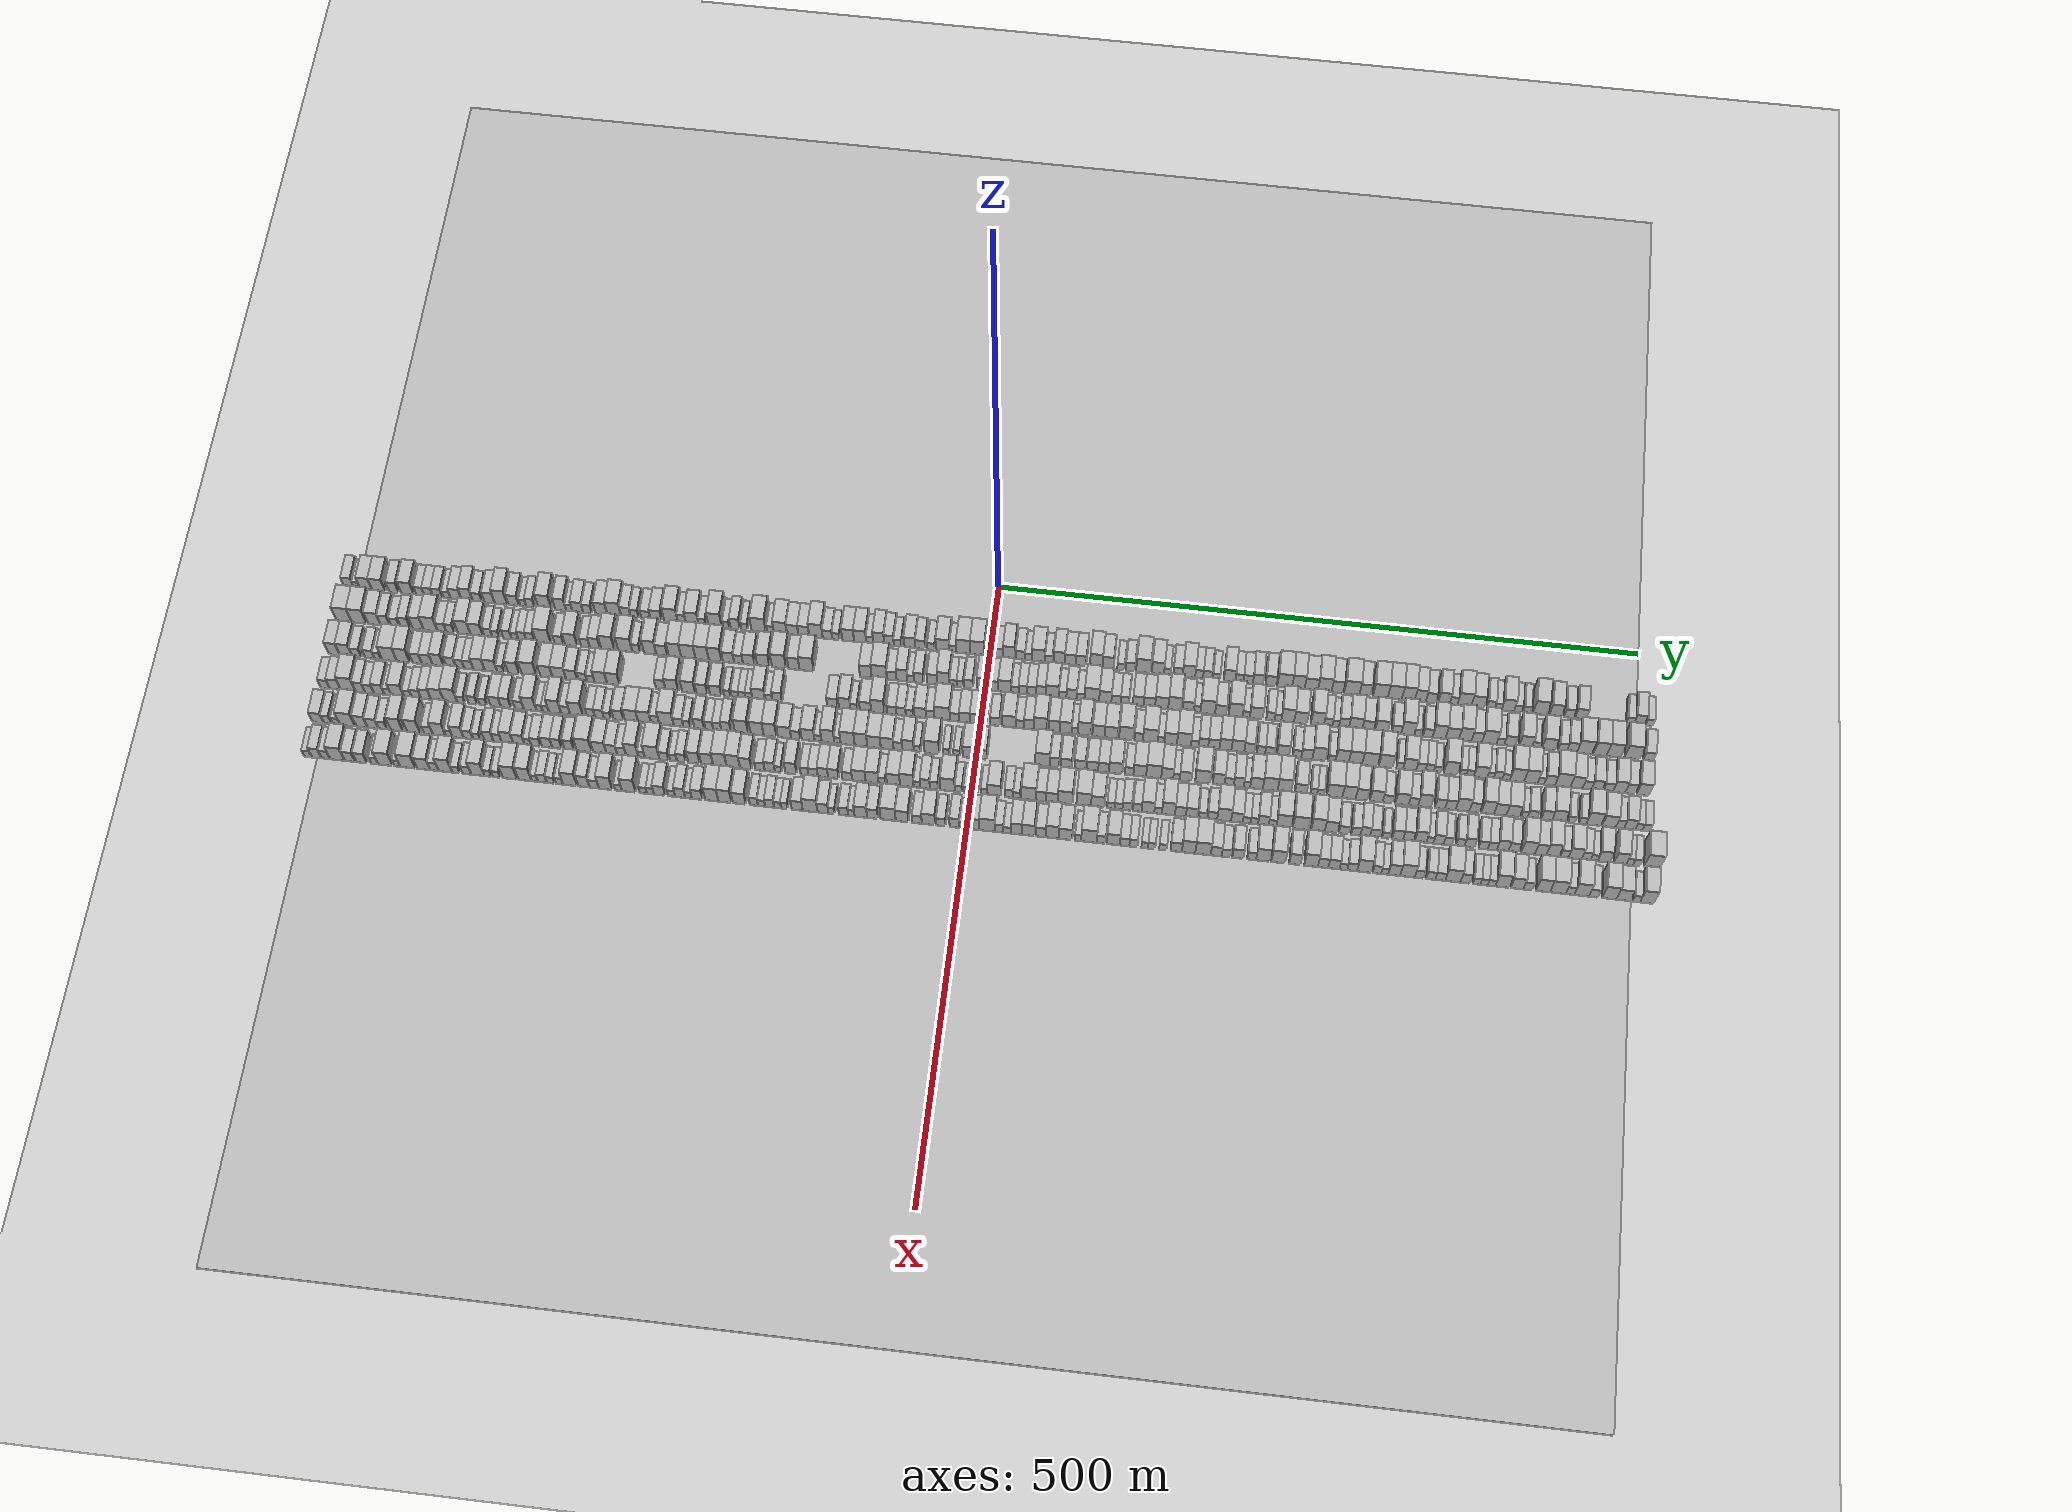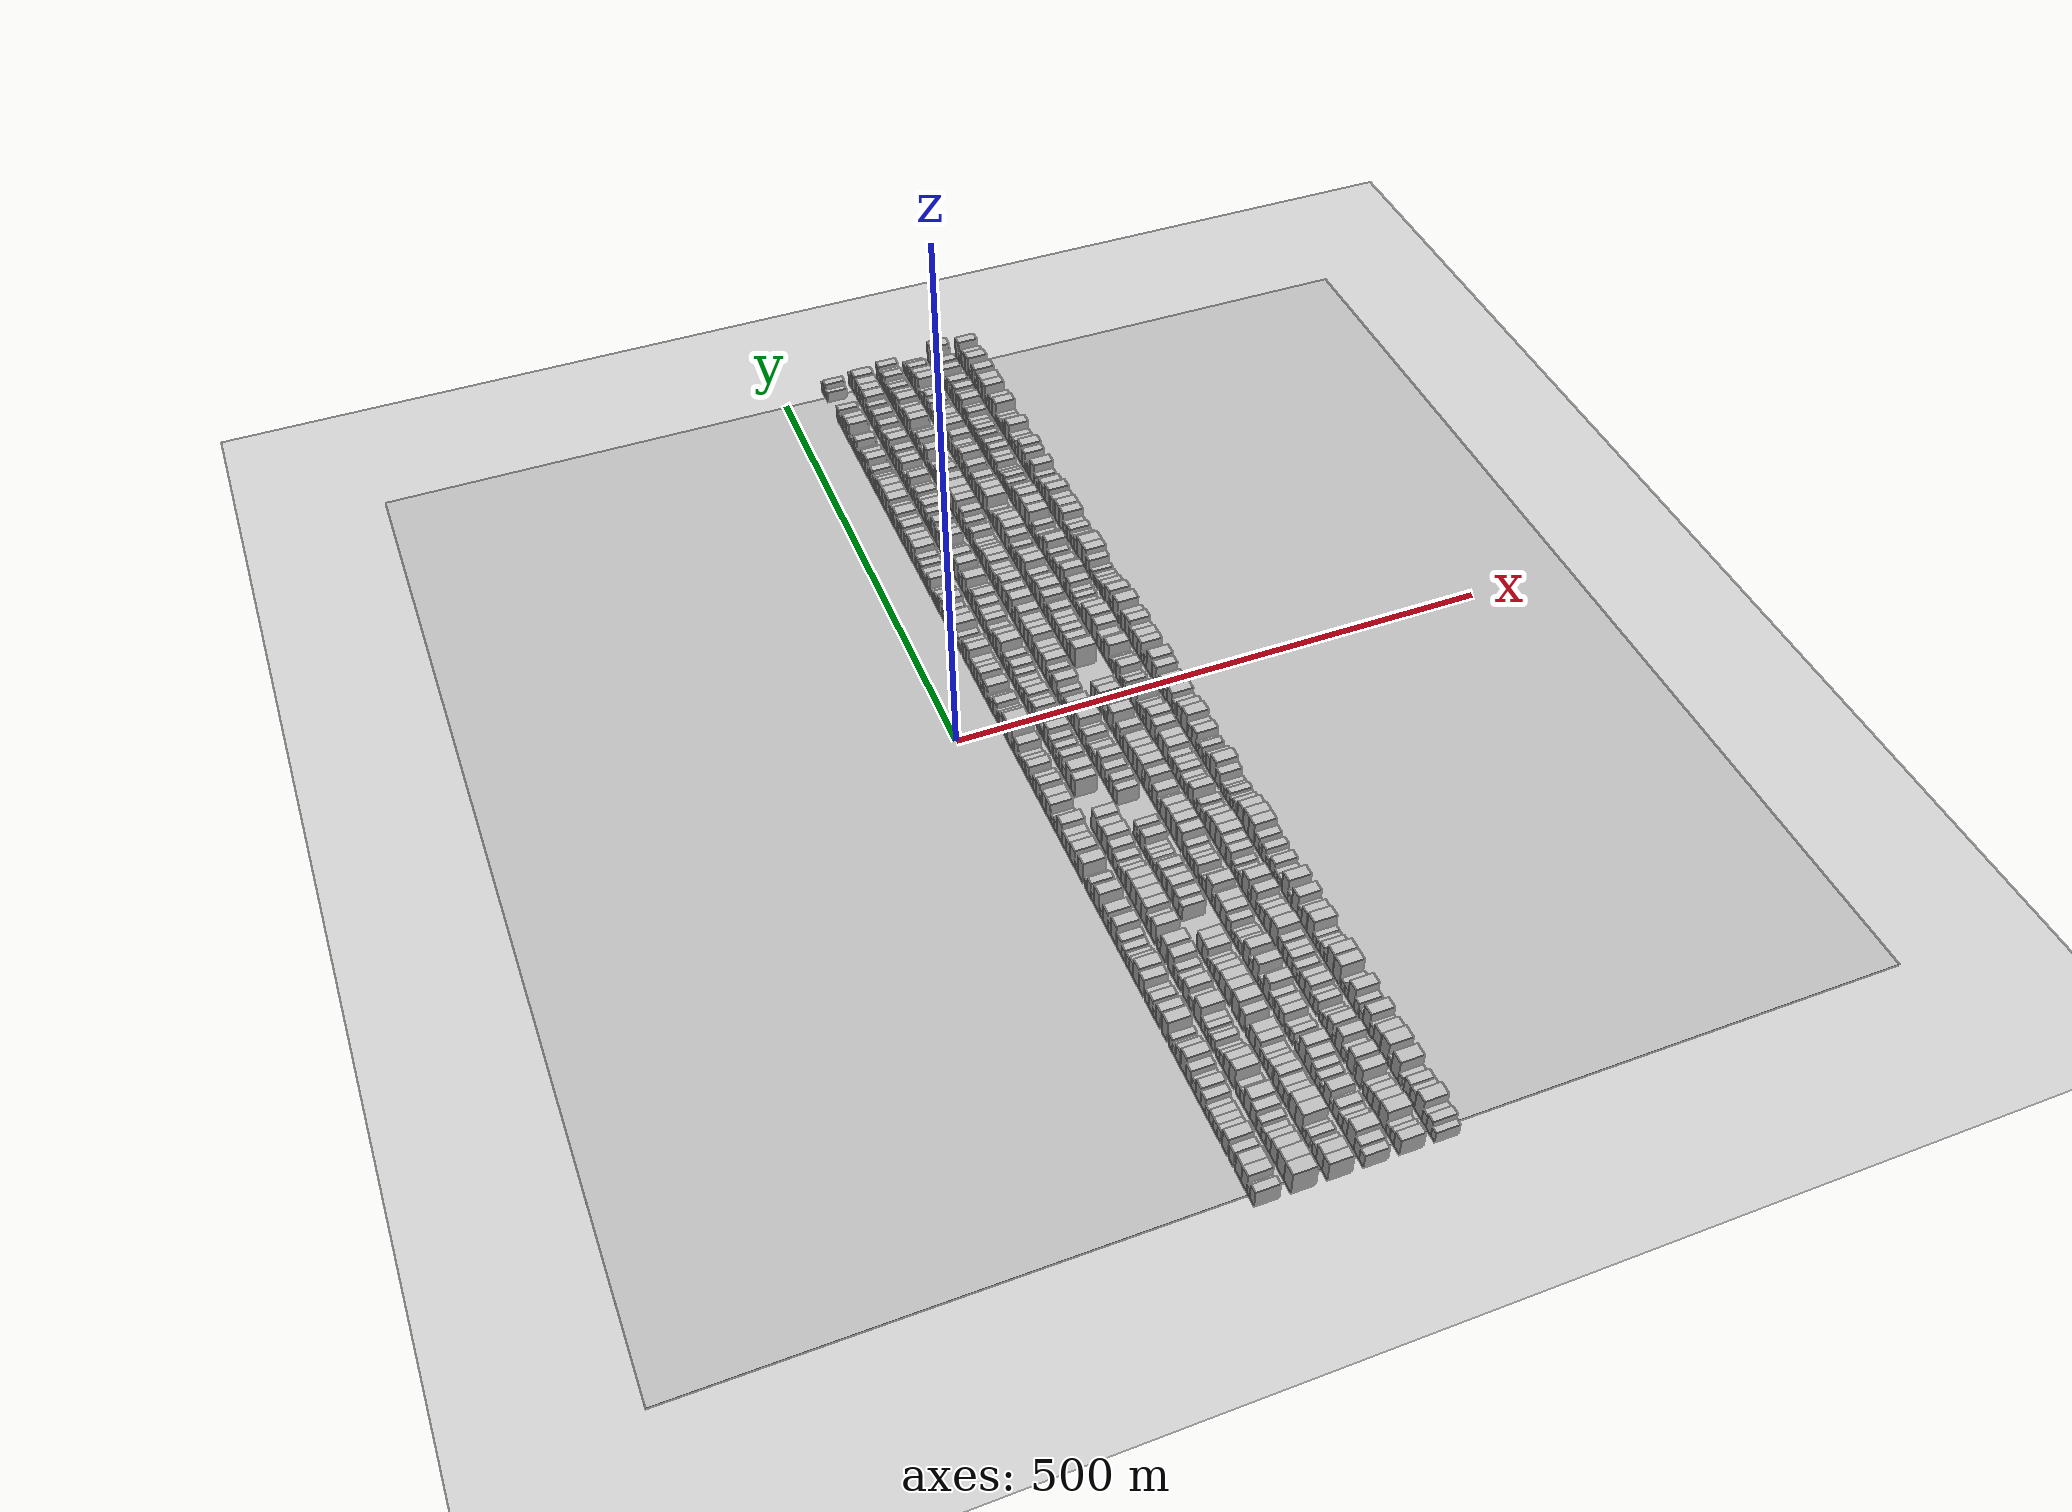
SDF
<?xml version="1.0" encoding="utf-8"?>

<sdf version="1.6">

   <world name="default">

      <gui fullscreen="0">

         <camera name="user_camera">

            <pose>-15 0 4.57585 0 0 0</pose>

            <view_controller>orbit</view_controller>

         </camera>

      </gui>

      <scene>

         <sky>

           <clouds>

             <speed>12</speed>

           </clouds>

         </sky>

         <ambient>0.4 0.4 0.4 1</ambient>

         <background>0.7 0.7 0.7 1</background>

         <shadows>1</shadows>

      </scene>

      <gravity>0 0 -9.8066</gravity>

      <magnetic_field>6e-06 2.3e-05 -4.2e-05</magnetic_field>

      <physics default="0" name="default_physics" type="ode">

         <ode>

            <solver>

               <type>quick</type>

               <iters>10</iters>

               <sor>1.0</sor>

               <use_dynamic_moi_rescaling>0</use_dynamic_moi_rescaling>

            </solver>

            <constraints>

               <cfm>0</cfm>

               <erp>0.2</erp>

               <contact_max_correcting_vel>100</contact_max_correcting_vel>

               <contact_surface_layer>0.001</contact_surface_layer>

            </constraints>

         </ode>

         <max_step_size>0.004</max_step_size>

         <real_time_factor>1</real_time_factor>

         <real_time_update_rate>250</real_time_update_rate>

      </physics>

      <light name="sun" type="directional">

         <cast_shadows>1</cast_shadows>

         <pose>0 0 10 0 0 0</pose>

         <diffuse>0.8 0.8 0.8 1</diffuse>

         <specular>0.2 0.2 0.2 1</specular>

         <attenuation>

            <range>1000</range>

            <constant>0.9</constant>

            <linear>0.01</linear>

            <quadratic>0.001</quadratic>

         </attenuation>

         <direction>-0.5 0.1 -0.9</direction>

      </light>

      <include>

         <name>ground_plane_1</name>

         <uri>model://HANNAS_ground_plane</uri>

         <pose>0 0 0  0 0 0</pose>

      </include>

      <include>

         <name>ground_plane_2</name>

         <uri>model://HANNAS_ground_plane</uri>

         <pose>100 0 0  0 0 0</pose>

      </include>

      <model name="building_1">

         <static>1</static>

         <pose frame="">50.0000 -506.1923 0 0.000000 0.000000 0.000000</pose>

         <link name="link">

            <pose frame="">0 0 9.00 0 0 0</pose>

            <collision name="collision">

               <geometry>

                  <box>

                     <size>20.0000 7.6155 18.0000</size>

                  </box>

               </geometry>

               <max_contacts>10</max_contacts>

               <surface>

                  <contact>

                     <ode/>

                  </contact>

                  <bounce/>

                  <friction>

                     <torsional>

                        <ode/>

                     </torsional>

                     <ode/>

                  </friction>

               </surface>

            </collision>

            <visual name="visual">

               <cast_shadows>0</cast_shadows>

               <geometry>

                  <box>

                     <size>20.0000 7.6155 18.0000</size>

                  </box>

               </geometry>

               <material>

                  <script>

                     <uri>model://HANNAS_wall/materials/scripts</uri>

                     <uri>model://HANNAS_wall/materials/textures</uri>

                     <name>vrc/HANNAS_wall</name>

                  </script>

               </material>

            </visual>

            <self_collide>0</self_collide>

            <enable_wind>0</enable_wind>

            <kinematic>0</kinematic>

         </link>

      </model>

      <model name="building_2">

         <static>1</static>

         <pose frame="">50.0000 -499.9153 0 0.000000 0.000000 0.000000</pose>

         <link name="link">

            <pose frame="">0 0 6.00 0 0 0</pose>

            <collision name="collision">

               <geometry>

                  <box>

                     <size>20.0000 4.9384 12.0000</size>

                  </box>

               </geometry>

               <max_contacts>10</max_contacts>

               <surface>

                  <contact>

                     <ode/>

                  </contact>

                  <bounce/>

                  <friction>

                     <torsional>

                        <ode/>

                     </torsional>

                     <ode/>

                  </friction>

               </surface>

            </collision>

            <visual name="visual">

               <cast_shadows>0</cast_shadows>

               <geometry>

                  <box>

                     <size>20.0000 4.9384 12.0000</size>

                  </box>

               </geometry>

               <material>

                  <script>

                     <uri>model://HANNAS_wall/materials/scripts</uri>

                     <uri>model://HANNAS_wall/materials/textures</uri>

                     <name>vrc/HANNAS_wall</name>

                  </script>

               </material>

            </visual>

            <self_collide>0</self_collide>

            <enable_wind>0</enable_wind>

            <kinematic>0</kinematic>

         </link>

      </model>

      <model name="building_3">

         <static>1</static>

         <pose frame="">50.0000 -492.6793 0 0.000000 0.000000 0.000000</pose>

         <link name="link">

            <pose frame="">0 0 10.50 0 0 0</pose>

            <collision name="collision">

               <geometry>

                  <box>

                     <size>20.0000 9.5337 21.0000</size>

                  </box>

               </geometry>

               <max_contacts>10</max_contacts>

               <surface>

                  <contact>

                     <ode/>

                  </contact>

                  <bounce/>

                  <friction>

                     <torsional>

                        <ode/>

                     </torsional>

                     <ode/>

                  </friction>

               </surface>

            </collision>

            <visual name="visual">

               <cast_shadows>0</cast_shadows>

               <geometry>

                  <box>

                     <size>20.0000 9.5337 21.0000</size>

                  </box>

               </geometry>

               <material>

                  <script>

                     <uri>model://HANNAS_wall/materials/scripts</uri>

                     <uri>model://HANNAS_wall/materials/textures</uri>

                     <name>vrc/HANNAS_wall</name>

                  </script>

               </material>

            </visual>

            <self_collide>0</self_collide>

            <enable_wind>0</enable_wind>

            <kinematic>0</kinematic>

         </link>

      </model>

      <model name="building_4">

         <static>1</static>

         <pose frame="">50.0000 -482.6955 0 0.000000 0.000000 0.000000</pose>

         <link name="link">

            <pose frame="">0 0 10.50 0 0 0</pose>

            <collision name="collision">

               <geometry>

                  <box>

                     <size>20.0000 10.4338 21.0000</size>

                  </box>

               </geometry>

               <max_contacts>10</max_contacts>

               <surface>

                  <contact>

                     <ode/>

                  </contact>

                  <bounce/>

                  <friction>

                     <torsional>

                        <ode/>

                     </torsional>

                     <ode/>

                  </friction>

               </surface>

            </collision>

            <visual name="visual">

               <cast_shadows>0</cast_shadows>

               <geometry>

                  <box>

                     <size>20.0000 10.4338 21.0000</size>

                  </box>

               </geometry>

               <material>

                  <script>

                     <uri>model://HANNAS_wall/materials/scripts</uri>

                     <uri>model://HANNAS_wall/materials/textures</uri>

                     <name>vrc/HANNAS_wall</name>

                  </script>

               </material>

            </visual>

            <self_collide>0</self_collide>

            <enable_wind>0</enable_wind>

            <kinematic>0</kinematic>

         </link>

      </model>

      <model name="building_5">

         <static>1</static>

         <pose frame="">50.0000 -470.6189 0 0.000000 0.000000 0.000000</pose>

         <link name="link">

            <pose frame="">0 0 9.00 0 0 0</pose>

            <collision name="collision">

               <geometry>

                  <box>

                     <size>20.0000 7.7194 18.0000</size>

                  </box>

               </geometry>

               <max_contacts>10</max_contacts>

               <surface>

                  <contact>

                     <ode/>

                  </contact>

                  <bounce/>

                  <friction>

                     <torsional>

                        <ode/>

                     </torsional>

                     <ode/>

                  </friction>

               </surface>

            </collision>

            <visual name="visual">

               <cast_shadows>0</cast_shadows>

               <geometry>

                  <box>

                     <size>20.0000 7.7194 18.0000</size>

                  </box>

               </geometry>

               <material>

                  <script>

                     <uri>model://HANNAS_wall/materials/scripts</uri>

                     <uri>model://HANNAS_wall/materials/textures</uri>

                     <name>vrc/HANNAS_wall</name>

                  </script>

               </material>

            </visual>

            <self_collide>0</self_collide>

            <enable_wind>0</enable_wind>

            <kinematic>0</kinematic>

         </link>

      </model>

      <model name="building_6">

         <static>1</static>

         <pose frame="">50.0000 -459.7535 0 0.000000 0.000000 0.000000</pose>

         <link name="link">

            <pose frame="">0 0 10.50 0 0 0</pose>

            <collision name="collision">

               <geometry>

                  <box>

                     <size>20.0000 10.0115 21.0000</size>

                  </box>

               </geometry>

               <max_contacts>10</max_contacts>

               <surface>

                  <contact>

                     <ode/>

                  </contact>

                  <bounce/>

                  <friction>

                     <torsional>

                        <ode/>

                     </torsional>

                     <ode/>

                  </friction>

               </surface>

            </collision>

            <visual name="visual">

               <cast_shadows>0</cast_shadows>

               <geometry>

                  <box>

                     <size>20.0000 10.0115 21.0000</size>

                  </box>

               </geometry>

               <material>

                  <script>

                     <uri>model://HANNAS_wall/materials/scripts</uri>

                     <uri>model://HANNAS_wall/materials/textures</uri>

                     <name>vrc/HANNAS_wall</name>

                  </script>

               </material>

            </visual>

            <self_collide>0</self_collide>

            <enable_wind>0</enable_wind>

            <kinematic>0</kinematic>

         </link>

      </model>

      <model name="building_7">

         <static>1</static>

         <pose frame="">50.0000 -449.5261 0 0.000000 0.000000 0.000000</pose>

         <link name="link">

            <pose frame="">0 0 7.50 0 0 0</pose>

            <collision name="collision">

               <geometry>

                  <box>

                     <size>20.0000 6.4433 15.0000</size>

                  </box>

               </geometry>

               <max_contacts>10</max_contacts>

               <surface>

                  <contact>

                     <ode/>

                  </contact>

                  <bounce/>

                  <friction>

                     <torsional>

                        <ode/>

                     </torsional>

                     <ode/>

                  </friction>

               </surface>

            </collision>

            <visual name="visual">

               <cast_shadows>0</cast_shadows>

               <geometry>

                  <box>

                     <size>20.0000 6.4433 15.0000</size>

                  </box>

               </geometry>

               <material>

                  <script>

                     <uri>model://HANNAS_wall/materials/scripts</uri>

                     <uri>model://HANNAS_wall/materials/textures</uri>

                     <name>vrc/HANNAS_wall</name>

                  </script>

               </material>

            </visual>

            <self_collide>0</self_collide>

            <enable_wind>0</enable_wind>

            <kinematic>0</kinematic>

         </link>

      </model>

      <model name="building_8">

         <static>1</static>

         <pose frame="">50.0000 -442.7757 0 0.000000 0.000000 0.000000</pose>

         <link name="link">

            <pose frame="">0 0 7.50 0 0 0</pose>

            <collision name="collision">

               <geometry>

                  <box>

                     <size>20.0000 7.0575 15.0000</size>

                  </box>

               </geometry>

               <max_contacts>10</max_contacts>

               <surface>

                  <contact>

                     <ode/>

                  </contact>

                  <bounce/>

                  <friction>

                     <torsional>

                        <ode/>

                     </torsional>

                     <ode/>

                  </friction>

               </surface>

            </collision>

            <visual name="visual">

               <cast_shadows>0</cast_shadows>

               <geometry>

                  <box>

                     <size>20.0000 7.0575 15.0000</size>

                  </box>

               </geometry>

               <material>

                  <script>

                     <uri>model://HANNAS_wall/materials/scripts</uri>

                     <uri>model://HANNAS_wall/materials/textures</uri>

                     <name>vrc/HANNAS_wall</name>

                  </script>

               </material>

            </visual>

            <self_collide>0</self_collide>

            <enable_wind>0</enable_wind>

            <kinematic>0</kinematic>

         </link>

      </model>

      <model name="building_9">

         <static>1</static>

         <pose frame="">50.0000 -435.6232 0 0.000000 0.000000 0.000000</pose>

         <link name="link">

            <pose frame="">0 0 7.50 0 0 0</pose>

            <collision name="collision">

               <geometry>

                  <box>

                     <size>20.0000 7.2474 15.0000</size>

                  </box>

               </geometry>

               <max_contacts>10</max_contacts>

               <surface>

                  <contact>

                     <ode/>

                  </contact>

                  <bounce/>

                  <friction>

                     <torsional>

                        <ode/>

                     </torsional>

                     <ode/>

                  </friction>

               </surface>

            </collision>

            <visual name="visual">

               <cast_shadows>0</cast_shadows>

               <geometry>

                  <box>

                     <size>20.0000 7.2474 15.0000</size>

                  </box>

               </geometry>

               <material>

                  <script>

                     <uri>model://HANNAS_wall/materials/scripts</uri>

                     <uri>model://HANNAS_wall/materials/textures</uri>

                     <name>vrc/HANNAS_wall</name>

                  </script>

               </material>

            </visual>

            <self_collide>0</self_collide>

            <enable_wind>0</enable_wind>

            <kinematic>0</kinematic>

         </link>

      </model>

      <model name="building_10">

         <static>1</static>

         <pose frame="">50.0000 -428.1598 0 0.000000 0.000000 0.000000</pose>

         <link name="link">

            <pose frame="">0 0 6.00 0 0 0</pose>

            <collision name="collision">

               <geometry>

                  <box>

                     <size>20.0000 5.6795 12.0000</size>

                  </box>

               </geometry>

               <max_contacts>10</max_contacts>

               <surface>

                  <contact>

                     <ode/>

                  </contact>

                  <bounce/>

                  <friction>

                     <torsional>

                        <ode/>

                     </torsional>

                     <ode/>

                  </friction>

               </surface>

            </collision>

            <visual name="visual">

               <cast_shadows>0</cast_shadows>

               <geometry>

                  <box>

                     <size>20.0000 5.6795 12.0000</size>

                  </box>

               </geometry>

               <material>

                  <script>

                     <uri>model://HANNAS_wall/materials/scripts</uri>

                     <uri>model://HANNAS_wall/materials/textures</uri>

                     <name>vrc/HANNAS_wall</name>

                  </script>

               </material>

            </visual>

            <self_collide>0</self_collide>

            <enable_wind>0</enable_wind>

            <kinematic>0</kinematic>

         </link>

      </model>

      <model name="building_11">

         <static>1</static>

         <pose frame="">50.0000 -421.0563 0 0.000000 0.000000 0.000000</pose>

         <link name="link">

            <pose frame="">0 0 9.00 0 0 0</pose>

            <collision name="collision">

               <geometry>

                  <box>

                     <size>20.0000 8.5275 18.0000</size>

                  </box>

               </geometry>

               <max_contacts>10</max_contacts>

               <surface>

                  <contact>

                     <ode/>

                  </contact>

                  <bounce/>

                  <friction>

                     <torsional>

                        <ode/>

                     </torsional>

                     <ode/>

                  </friction>

               </surface>

            </collision>

            <visual name="visual">

               <cast_shadows>0</cast_shadows>

               <geometry>

                  <box>

                     <size>20.0000 8.5275 18.0000</size>

                  </box>

               </geometry>

               <material>

                  <script>

                     <uri>model://HANNAS_wall/materials/scripts</uri>

                     <uri>model://HANNAS_wall/materials/textures</uri>

                     <name>vrc/HANNAS_wall</name>

                  </script>

               </material>

            </visual>

            <self_collide>0</self_collide>

            <enable_wind>0</enable_wind>

            <kinematic>0</kinematic>

         </link>

      </model>

      <model name="building_12">

         <static>1</static>

         <pose frame="">50.0000 -412.3185 0 0.000000 0.000000 0.000000</pose>

         <link name="link">

            <pose frame="">0 0 10.50 0 0 0</pose>

            <collision name="collision">

               <geometry>

                  <box>

                     <size>20.0000 8.9482 21.0000</size>

                  </box>

               </geometry>

               <max_contacts>10</max_contacts>

               <surface>

                  <contact>

                     <ode/>

                  </contact>

                  <bounce/>

                  <friction>

                     <torsional>

                        <ode/>

                     </torsional>

                     <ode/>

                  </friction>

               </surface>

            </collision>

            <visual name="visual">

               <cast_shadows>0</cast_shadows>

               <geometry>

                  <box>

                     <size>20.0000 8.9482 21.0000</size>

                  </box>

               </geometry>

               <material>

                  <script>

                     <uri>model://HANNAS_wall/materials/scripts</uri>

                     <uri>model://HANNAS_wall/materials/textures</uri>

                     <name>vrc/HANNAS_wall</name>

                  </script>

               </material>

            </visual>

            <self_collide>0</self_collide>

            <enable_wind>0</enable_wind>

            <kinematic>0</kinematic>

         </link>

      </model>

      <model name="building_13">

         <static>1</static>

         <pose frame="">50.0000 -404.1647 0 0.000000 0.000000 0.000000</pose>

         <link name="link">

            <pose frame="">0 0 7.50 0 0 0</pose>

            <collision name="collision">

               <geometry>

                  <box>

                     <size>20.0000 7.3594 15.0000</size>

                  </box>

               </geometry>

               <max_contacts>10</max_contacts>

               <surface>

                  <contact>

                     <ode/>

                  </contact>

                  <bounce/>

                  <friction>

                     <torsional>

                        <ode/>

                     </torsional>

                     <ode/>

                  </friction>

               </surface>

            </collision>

            <visual name="visual">

               <cast_shadows>0</cast_shadows>

               <geometry>

                  <box>

                     <size>20.0000 7.3594 15.0000</size>

                  </box>

               </geometry>

               <material>

                  <script>

                     <uri>model://HANNAS_wall/materials/scripts</uri>

                     <uri>model://HANNAS_wall/materials/textures</uri>

                     <name>vrc/HANNAS_wall</name>

                  </script>

               </material>

            </visual>

            <self_collide>0</self_collide>

            <enable_wind>0</enable_wind>

            <kinematic>0</kinematic>

         </link>

      </model>

      <model name="building_14">

         <static>1</static>

         <pose frame="">50.0000 -394.3935 0 0.000000 0.000000 0.000000</pose>

         <link name="link">

            <pose frame="">0 0 9.00 0 0 0</pose>

            <collision name="collision">

               <geometry>

                  <box>

                     <size>20.0000 8.1831 18.0000</size>

                  </box>

               </geometry>

               <max_contacts>10</max_contacts>

               <surface>

                  <contact>

                     <ode/>

                  </contact>

                  <bounce/>

                  <friction>

                     <torsional>

                        <ode/>

                     </torsional>

                     <ode/>

                  </friction>

               </surface>

            </collision>

            <visual name="visual">

               <cast_shadows>0</cast_shadows>

               <geometry>

                  <box>

                     <size>20.0000 8.1831 18.0000</size>

                  </box>

               </geometry>

               <material>

                  <script>

                     <uri>model://HANNAS_wall/materials/scripts</uri>

                     <uri>model://HANNAS_wall/materials/textures</uri>

                     <name>vrc/HANNAS_wall</name>

                  </script>

               </material>

            </visual>

            <self_collide>0</self_collide>

            <enable_wind>0</enable_wind>

            <kinematic>0</kinematic>

         </link>

      </model>

      <model name="building_15">

         <static>1</static>

         <pose frame="">50.0000 -385.3298 0 0.000000 0.000000 0.000000</pose>

         <link name="link">

            <pose frame="">0 0 12.00 0 0 0</pose>

            <collision name="collision">

               <geometry>

                  <box>

                     <size>20.0000 9.9443 24.0000</size>

                  </box>

               </geometry>

               <max_contacts>10</max_contacts>

               <surface>

                  <contact>

                     <ode/>

                  </contact>

                  <bounce/>

                  <friction>

                     <torsional>

                        <ode/>

                     </torsional>

                     <ode/>

                  </friction>

               </surface>

            </collision>

            <visual name="visual">

               <cast_shadows>0</cast_shadows>

               <geometry>

                  <box>

                     <size>20.0000 9.9443 24.0000</size>

                  </box>

               </geometry>

               <material>

                  <script>

                     <uri>model://HANNAS_wall/materials/scripts</uri>

                     <uri>model://HANNAS_wall/materials/textures</uri>

                     <name>vrc/HANNAS_wall</name>

                  </script>

               </material>

            </visual>

            <self_collide>0</self_collide>

            <enable_wind>0</enable_wind>

            <kinematic>0</kinematic>

         </link>

      </model>

      <model name="building_16">

         <static>1</static>

         <pose frame="">50.0000 -375.1956 0 0.000000 0.000000 0.000000</pose>

         <link name="link">

            <pose frame="">0 0 9.00 0 0 0</pose>

            <collision name="collision">

               <geometry>

                  <box>

                     <size>20.0000 8.3240 18.0000</size>

                  </box>

               </geometry>

               <max_contacts>10</max_contacts>

               <surface>

                  <contact>

                     <ode/>

                  </contact>

                  <bounce/>

                  <friction>

                     <torsional>

                        <ode/>

                     </torsional>

                     <ode/>

                  </friction>

               </surface>

            </collision>

            <visual name="visual">

               <cast_shadows>0</cast_shadows>

               <geometry>

                  <box>

                     <size>20.0000 8.3240 18.0000</size>

                  </box>

               </geometry>

               <material>

                  <script>

                     <uri>model://HANNAS_wall/materials/scripts</uri>

                     <uri>model://HANNAS_wall/materials/textures</uri>

                     <name>vrc/HANNAS_wall</name>

                  </script>

               </material>

            </visual>

            <self_collide>0</self_collide>

            <enable_wind>0</enable_wind>

            <kinematic>0</kinematic>

         </link>

      </model>

      <model name="building_17">

         <static>1</static>

         <pose frame="">50.0000 -367.6054 0 0.000000 0.000000 0.000000</pose>

         <link name="link">

            <pose frame="">0 0 6.00 0 0 0</pose>

            <collision name="collision">

               <geometry>

                  <box>

                     <size>20.0000 4.8566 12.0000</size>

                  </box>

               </geometry>

               <max_contacts>10</max_contacts>

               <surface>

                  <contact>

                     <ode/>

                  </contact>

                  <bounce/>

                  <friction>

                     <torsional>

                        <ode/>

                     </torsional>

                     <ode/>

                  </friction>

               </surface>

            </collision>

            <visual name="visual">

               <cast_shadows>0</cast_shadows>

               <geometry>

                  <box>

                     <size>20.0000 4.8566 12.0000</size>

                  </box>

               </geometry>

               <material>

                  <script>

                     <uri>model://HANNAS_wall/materials/scripts</uri>

                     <uri>model://HANNAS_wall/materials/textures</uri>

                     <name>vrc/HANNAS_wall</name>

                  </script>

               </material>

            </visual>

            <self_collide>0</self_collide>

            <enable_wind>0</enable_wind>

            <kinematic>0</kinematic>

         </link>

      </model>

      <model name="building_18">

         <static>1</static>

         <pose frame="">50.0000 -361.9061 0 0.000000 0.000000 0.000000</pose>

         <link name="link">

            <pose frame="">0 0 7.50 0 0 0</pose>

            <collision name="collision">

               <geometry>

                  <box>

                     <size>20.0000 6.5420 15.0000</size>

                  </box>

               </geometry>

               <max_contacts>10</max_contacts>

               <surface>

                  <contact>

                     <ode/>

                  </contact>

                  <bounce/>

                  <friction>

                     <torsional>

                        <ode/>

                     </torsional>

                     <ode/>

                  </friction>

               </surface>

            </collision>

            <visual name="visual">

               <cast_shadows>0</cast_shadows>

               <geometry>

                  <box>

                     <size>20.0000 6.5420 15.0000</size>

                  </box>

               </geometry>

               <material>

                  <script>

                     <uri>model://HANNAS_wall/materials/scripts</uri>

                     <uri>model://HANNAS_wall/materials/textures</uri>

                     <name>vrc/HANNAS_wall</name>

                  </script>

               </material>

            </visual>

            <self_collide>0</self_collide>

            <enable_wind>0</enable_wind>

            <kinematic>0</kinematic>

         </link>

      </model>

      <model name="building_19">

         <static>1</static>

         <pose frame="">50.0000 -350.4418 0 0.000000 0.000000 0.000000</pose>

         <link name="link">

            <pose frame="">0 0 12.00 0 0 0</pose>

            <collision name="collision">

               <geometry>

                  <box>

                     <size>20.0000 10.3866 24.0000</size>

                  </box>

               </geometry>

               <max_contacts>10</max_contacts>

               <surface>

                  <contact>

                     <ode/>

                  </contact>

                  <bounce/>

                  <friction>

                     <torsional>

                        <ode/>

                     </torsional>

                     <ode/>

                  </friction>

               </surface>

            </collision>

            <visual name="visual">

               <cast_shadows>0</cast_shadows>

               <geometry>

                  <box>

                     <size>20.0000 10.3866 24.0000</size>

                  </box>

               </geometry>

               <material>

                  <script>

                     <uri>model://HANNAS_wall/materials/scripts</uri>

                     <uri>model://HANNAS_wall/materials/textures</uri>

                     <name>vrc/HANNAS_wall</name>

                  </script>

               </material>

            </visual>

            <self_collide>0</self_collide>

            <enable_wind>0</enable_wind>

            <kinematic>0</kinematic>

         </link>

      </model>

      <model name="building_20">

         <static>1</static>

         <pose frame="">50.0000 -337.9166 0 0.000000 0.000000 0.000000</pose>

         <link name="link">

            <pose frame="">0 0 10.50 0 0 0</pose>

            <collision name="collision">

               <geometry>

                  <box>

                     <size>20.0000 8.6638 21.0000</size>

                  </box>

               </geometry>

               <max_contacts>10</max_contacts>

               <surface>

                  <contact>

                     <ode/>

                  </contact>

                  <bounce/>

                  <friction>

                     <torsional>

                        <ode/>

                     </torsional>

                     <ode/>

                  </friction>

               </surface>

            </collision>

            <visual name="visual">

               <cast_shadows>0</cast_shadows>

               <geometry>

                  <box>

                     <size>20.0000 8.6638 21.0000</size>

                  </box>

               </geometry>

               <material>

                  <script>

                     <uri>model://HANNAS_wall/materials/scripts</uri>

                     <uri>model://HANNAS_wall/materials/textures</uri>

                     <name>vrc/HANNAS_wall</name>

                  </script>

               </material>

            </visual>

            <self_collide>0</self_collide>

            <enable_wind>0</enable_wind>

            <kinematic>0</kinematic>

         </link>

      </model>

      <model name="building_21">

         <static>1</static>

         <pose frame="">50.0000 -331.1371 0 0.000000 0.000000 0.000000</pose>

         <link name="link">

            <pose frame="">0 0 6.00 0 0 0</pose>

            <collision name="collision">

               <geometry>

                  <box>

                     <size>20.0000 4.8953 12.0000</size>

                  </box>

               </geometry>

               <max_contacts>10</max_contacts>

               <surface>

                  <contact>

                     <ode/>

                  </contact>

                  <bounce/>

                  <friction>

                     <torsional>

                        <ode/>

                     </torsional>

                     <ode/>

                  </friction>

               </surface>

            </collision>

            <visual name="visual">

               <cast_shadows>0</cast_shadows>

               <geometry>

                  <box>

                     <size>20.0000 4.8953 12.0000</size>

                  </box>

               </geometry>

               <material>

                  <script>

                     <uri>model://HANNAS_wall/materials/scripts</uri>

                     <uri>model://HANNAS_wall/materials/textures</uri>

                     <name>vrc/HANNAS_wall</name>

                  </script>

               </material>

            </visual>

            <self_collide>0</self_collide>

            <enable_wind>0</enable_wind>

            <kinematic>0</kinematic>

         </link>

      </model>

      <model name="building_22">

         <static>1</static>

         <pose frame="">50.0000 -324.3617 0 0.000000 0.000000 0.000000</pose>

         <link name="link">

            <pose frame="">0 0 9.00 0 0 0</pose>

            <collision name="collision">

               <geometry>

                  <box>

                     <size>20.0000 8.6555 18.0000</size>

                  </box>

               </geometry>

               <max_contacts>10</max_contacts>

               <surface>

                  <contact>

                     <ode/>

                  </contact>

                  <bounce/>

                  <friction>

                     <torsional>

                        <ode/>

                     </torsional>

                     <ode/>

                  </friction>

               </surface>

            </collision>

            <visual name="visual">

               <cast_shadows>0</cast_shadows>

               <geometry>

                  <box>

                     <size>20.0000 8.6555 18.0000</size>

                  </box>

               </geometry>

               <material>

                  <script>

                     <uri>model://HANNAS_wall/materials/scripts</uri>

                     <uri>model://HANNAS_wall/materials/textures</uri>

                     <name>vrc/HANNAS_wall</name>

                  </script>

               </material>

            </visual>

            <self_collide>0</self_collide>

            <enable_wind>0</enable_wind>

            <kinematic>0</kinematic>

         </link>

      </model>

      <model name="building_23">

         <static>1</static>

         <pose frame="">50.0000 -316.6043 0 0.000000 0.000000 0.000000</pose>

         <link name="link">

            <pose frame="">0 0 7.50 0 0 0</pose>

            <collision name="collision">

               <geometry>

                  <box>

                     <size>20.0000 6.8592 15.0000</size>

                  </box>

               </geometry>

               <max_contacts>10</max_contacts>

               <surface>

                  <contact>

                     <ode/>

                  </contact>

                  <bounce/>

                  <friction>

                     <torsional>

                        <ode/>

                     </torsional>

                     <ode/>

                  </friction>

               </surface>

            </collision>

            <visual name="visual">

               <cast_shadows>0</cast_shadows>

               <geometry>

                  <box>

                     <size>20.0000 6.8592 15.0000</size>

                  </box>

               </geometry>

               <material>

                  <script>

                     <uri>model://HANNAS_wall/materials/scripts</uri>

                     <uri>model://HANNAS_wall/materials/textures</uri>

                     <name>vrc/HANNAS_wall</name>

                  </script>

               </material>

            </visual>

            <self_collide>0</self_collide>

            <enable_wind>0</enable_wind>

            <kinematic>0</kinematic>

         </link>

      </model>

      <model name="building_24">

         <static>1</static>

         <pose frame="">50.0000 -305.5081 0 0.000000 0.000000 0.000000</pose>

         <link name="link">

            <pose frame="">0 0 10.50 0 0 0</pose>

            <collision name="collision">

               <geometry>

                  <box>

                     <size>20.0000 9.3333 21.0000</size>

                  </box>

               </geometry>

               <max_contacts>10</max_contacts>

               <surface>

                  <contact>

                     <ode/>

                  </contact>

                  <bounce/>

                  <friction>

                     <torsional>

                        <ode/>

                     </torsional>

                     <ode/>

                  </friction>

               </surface>

            </collision>

            <visual name="visual">

               <cast_shadows>0</cast_shadows>

               <geometry>

                  <box>

                     <size>20.0000 9.3333 21.0000</size>

                  </box>

               </geometry>

               <material>

                  <script>

                     <uri>model://HANNAS_wall/materials/scripts</uri>

                     <uri>model://HANNAS_wall/materials/textures</uri>

                     <name>vrc/HANNAS_wall</name>

                  </script>

               </material>

            </visual>

            <self_collide>0</self_collide>

            <enable_wind>0</enable_wind>

            <kinematic>0</kinematic>

         </link>

      </model>

      <model name="building_25">

         <static>1</static>

         <pose frame="">50.0000 -295.3437 0 0.000000 0.000000 0.000000</pose>

         <link name="link">

            <pose frame="">0 0 12.00 0 0 0</pose>

            <collision name="collision">

               <geometry>

                  <box>

                     <size>20.0000 10.9955 24.0000</size>

                  </box>

               </geometry>

               <max_contacts>10</max_contacts>

               <surface>

                  <contact>

                     <ode/>

                  </contact>

                  <bounce/>

                  <friction>

                     <torsional>

                        <ode/>

                     </torsional>

                     <ode/>

                  </friction>

               </surface>

            </collision>

            <visual name="visual">

               <cast_shadows>0</cast_shadows>

               <geometry>

                  <box>

                     <size>20.0000 10.9955 24.0000</size>

                  </box>

               </geometry>

               <material>

                  <script>

                     <uri>model://HANNAS_wall/materials/scripts</uri>

                     <uri>model://HANNAS_wall/materials/textures</uri>

                     <name>vrc/HANNAS_wall</name>

                  </script>

               </material>

            </visual>

            <self_collide>0</self_collide>

            <enable_wind>0</enable_wind>

            <kinematic>0</kinematic>

         </link>

      </model>

      <model name="building_26">

         <static>1</static>

         <pose frame="">50.0000 -286.0446 0 0.000000 0.000000 0.000000</pose>

         <link name="link">

            <pose frame="">0 0 9.00 0 0 0</pose>

            <collision name="collision">

               <geometry>

                  <box>

                     <size>20.0000 7.6027 18.0000</size>

                  </box>

               </geometry>

               <max_contacts>10</max_contacts>

               <surface>

                  <contact>

                     <ode/>

                  </contact>

                  <bounce/>

                  <friction>

                     <torsional>

                        <ode/>

                     </torsional>

                     <ode/>

                  </friction>

               </surface>

            </collision>

            <visual name="visual">

               <cast_shadows>0</cast_shadows>

               <geometry>

                  <box>

                     <size>20.0000 7.6027 18.0000</size>

                  </box>

               </geometry>

               <material>

                  <script>

                     <uri>model://HANNAS_wall/materials/scripts</uri>

                     <uri>model://HANNAS_wall/materials/textures</uri>

                     <name>vrc/HANNAS_wall</name>

                  </script>

               </material>

            </visual>

            <self_collide>0</self_collide>

            <enable_wind>0</enable_wind>

            <kinematic>0</kinematic>

         </link>

      </model>

      <model name="building_27">

         <static>1</static>

         <pose frame="">50.0000 -279.0902 0 0.000000 0.000000 0.000000</pose>

         <link name="link">

            <pose frame="">0 0 7.50 0 0 0</pose>

            <collision name="collision">

               <geometry>

                  <box>

                     <size>20.0000 6.3062 15.0000</size>

                  </box>

               </geometry>

               <max_contacts>10</max_contacts>

               <surface>

                  <contact>

                     <ode/>

                  </contact>

                  <bounce/>

                  <friction>

                     <torsional>

                        <ode/>

                     </torsional>

                     <ode/>

                  </friction>

               </surface>

            </collision>

            <visual name="visual">

               <cast_shadows>0</cast_shadows>

               <geometry>

                  <box>

                     <size>20.0000 6.3062 15.0000</size>

                  </box>

               </geometry>

               <material>

                  <script>

                     <uri>model://HANNAS_wall/materials/scripts</uri>

                     <uri>model://HANNAS_wall/materials/textures</uri>

                     <name>vrc/HANNAS_wall</name>

                  </script>

               </material>

            </visual>

            <self_collide>0</self_collide>

            <enable_wind>0</enable_wind>

            <kinematic>0</kinematic>

         </link>

      </model>

      <model name="building_28">

         <static>1</static>

         <pose frame="">50.0000 -270.2554 0 0.000000 0.000000 0.000000</pose>

         <link name="link">

            <pose frame="">0 0 7.50 0 0 0</pose>

            <collision name="collision">

               <geometry>

                  <box>

                     <size>20.0000 7.3635 15.0000</size>

                  </box>

               </geometry>

               <max_contacts>10</max_contacts>

               <surface>

                  <contact>

                     <ode/>

                  </contact>

                  <bounce/>

                  <friction>

                     <torsional>

                        <ode/>

                     </torsional>

                     <ode/>

                  </friction>

               </surface>

            </collision>

            <visual name="visual">

               <cast_shadows>0</cast_shadows>

               <geometry>

                  <box>

                     <size>20.0000 7.3635 15.0000</size>

                  </box>

               </geometry>

               <material>

                  <script>

                     <uri>model://HANNAS_wall/materials/scripts</uri>

                     <uri>model://HANNAS_wall/materials/textures</uri>

                     <name>vrc/HANNAS_wall</name>

                  </script>

               </material>

            </visual>

            <self_collide>0</self_collide>

            <enable_wind>0</enable_wind>

            <kinematic>0</kinematic>

         </link>

      </model>

      <model name="building_29">

         <static>1</static>

         <pose frame="">50.0000 -262.2435 0 0.000000 0.000000 0.000000</pose>

         <link name="link">

            <pose frame="">0 0 9.00 0 0 0</pose>

            <collision name="collision">

               <geometry>

                  <box>

                     <size>20.0000 8.6604 18.0000</size>

                  </box>

               </geometry>

               <max_contacts>10</max_contacts>

               <surface>

                  <contact>

                     <ode/>

                  </contact>

                  <bounce/>

                  <friction>

                     <torsional>

                        <ode/>

                     </torsional>

                     <ode/>

                  </friction>

               </surface>

            </collision>

            <visual name="visual">

               <cast_shadows>0</cast_shadows>

               <geometry>

                  <box>

                     <size>20.0000 8.6604 18.0000</size>

                  </box>

               </geometry>

               <material>

                  <script>

                     <uri>model://HANNAS_wall/materials/scripts</uri>

                     <uri>model://HANNAS_wall/materials/textures</uri>

                     <name>vrc/HANNAS_wall</name>

                  </script>

               </material>

            </visual>

            <self_collide>0</self_collide>

            <enable_wind>0</enable_wind>

            <kinematic>0</kinematic>

         </link>

      </model>

      <model name="building_30">

         <static>1</static>

         <pose frame="">50.0000 -250.5087 0 0.000000 0.000000 0.000000</pose>

         <link name="link">

            <pose frame="">0 0 12.00 0 0 0</pose>

            <collision name="collision">

               <geometry>

                  <box>

                     <size>20.0000 10.8093 24.0000</size>

                  </box>

               </geometry>

               <max_contacts>10</max_contacts>

               <surface>

                  <contact>

                     <ode/>

                  </contact>

                  <bounce/>

                  <friction>

                     <torsional>

                        <ode/>

                     </torsional>

                     <ode/>

                  </friction>

               </surface>

            </collision>

            <visual name="visual">

               <cast_shadows>0</cast_shadows>

               <geometry>

                  <box>

                     <size>20.0000 10.8093 24.0000</size>

                  </box>

               </geometry>

               <material>

                  <script>

                     <uri>model://HANNAS_wall/materials/scripts</uri>

                     <uri>model://HANNAS_wall/materials/textures</uri>

                     <name>vrc/HANNAS_wall</name>

                  </script>

               </material>

            </visual>

            <self_collide>0</self_collide>

            <enable_wind>0</enable_wind>

            <kinematic>0</kinematic>

         </link>

      </model>

      <model name="building_31">

         <static>1</static>

         <pose frame="">50.0000 -241.9129 0 0.000000 0.000000 0.000000</pose>

         <link name="link">

            <pose frame="">0 0 7.50 0 0 0</pose>

            <collision name="collision">

               <geometry>

                  <box>

                     <size>20.0000 6.3821 15.0000</size>

                  </box>

               </geometry>

               <max_contacts>10</max_contacts>

               <surface>

                  <contact>

                     <ode/>

                  </contact>

                  <bounce/>

                  <friction>

                     <torsional>

                        <ode/>

                     </torsional>

                     <ode/>

                  </friction>

               </surface>

            </collision>

            <visual name="visual">

               <cast_shadows>0</cast_shadows>

               <geometry>

                  <box>

                     <size>20.0000 6.3821 15.0000</size>

                  </box>

               </geometry>

               <material>

                  <script>

                     <uri>model://HANNAS_wall/materials/scripts</uri>

                     <uri>model://HANNAS_wall/materials/textures</uri>

                     <name>vrc/HANNAS_wall</name>

                  </script>

               </material>

            </visual>

            <self_collide>0</self_collide>

            <enable_wind>0</enable_wind>

            <kinematic>0</kinematic>

         </link>

      </model>

      <model name="building_32">

         <static>1</static>

         <pose frame="">50.0000 -233.7276 0 0.000000 0.000000 0.000000</pose>

         <link name="link">

            <pose frame="">0 0 10.50 0 0 0</pose>

            <collision name="collision">

               <geometry>

                  <box>

                     <size>20.0000 9.9886 21.0000</size>

                  </box>

               </geometry>

               <max_contacts>10</max_contacts>

               <surface>

                  <contact>

                     <ode/>

                  </contact>

                  <bounce/>

                  <friction>

                     <torsional>

                        <ode/>

                     </torsional>

                     <ode/>

                  </friction>

               </surface>

            </collision>

            <visual name="visual">

               <cast_shadows>0</cast_shadows>

               <geometry>

                  <box>

                     <size>20.0000 9.9886 21.0000</size>

                  </box>

               </geometry>

               <material>

                  <script>

                     <uri>model://HANNAS_wall/materials/scripts</uri>

                     <uri>model://HANNAS_wall/materials/textures</uri>

                     <name>vrc/HANNAS_wall</name>

                  </script>

               </material>

            </visual>

            <self_collide>0</self_collide>

            <enable_wind>0</enable_wind>

            <kinematic>0</kinematic>

         </link>

      </model>

      <model name="building_33">

         <static>1</static>

         <pose frame="">50.0000 -225.8891 0 0.000000 0.000000 0.000000</pose>

         <link name="link">

            <pose frame="">0 0 6.00 0 0 0</pose>

            <collision name="collision">

               <geometry>

                  <box>

                     <size>20.0000 5.6884 12.0000</size>

                  </box>

               </geometry>

               <max_contacts>10</max_contacts>

               <surface>

                  <contact>

                     <ode/>

                  </contact>

                  <bounce/>

                  <friction>

                     <torsional>

                        <ode/>

                     </torsional>

                     <ode/>

                  </friction>

               </surface>

            </collision>

            <visual name="visual">

               <cast_shadows>0</cast_shadows>

               <geometry>

                  <box>

                     <size>20.0000 5.6884 12.0000</size>

                  </box>

               </geometry>

               <material>

                  <script>

                     <uri>model://HANNAS_wall/materials/scripts</uri>

                     <uri>model://HANNAS_wall/materials/textures</uri>

                     <name>vrc/HANNAS_wall</name>

                  </script>

               </material>

            </visual>

            <self_collide>0</self_collide>

            <enable_wind>0</enable_wind>

            <kinematic>0</kinematic>

         </link>

      </model>

      <model name="building_34">

         <static>1</static>

         <pose frame="">50.0000 -215.7499 0 0.000000 0.000000 0.000000</pose>

         <link name="link">

            <pose frame="">0 0 12.00 0 0 0</pose>

            <collision name="collision">

               <geometry>

                  <box>

                     <size>20.0000 10.5898 24.0000</size>

                  </box>

               </geometry>

               <max_contacts>10</max_contacts>

               <surface>

                  <contact>

                     <ode/>

                  </contact>

                  <bounce/>

                  <friction>

                     <torsional>

                        <ode/>

                     </torsional>

                     <ode/>

                  </friction>

               </surface>

            </collision>

            <visual name="visual">

               <cast_shadows>0</cast_shadows>

               <geometry>

                  <box>

                     <size>20.0000 10.5898 24.0000</size>

                  </box>

               </geometry>

               <material>

                  <script>

                     <uri>model://HANNAS_wall/materials/scripts</uri>

                     <uri>model://HANNAS_wall/materials/textures</uri>

                     <name>vrc/HANNAS_wall</name>

                  </script>

               </material>

            </visual>

            <self_collide>0</self_collide>

            <enable_wind>0</enable_wind>

            <kinematic>0</kinematic>

         </link>

      </model>

      <model name="building_35">

         <static>1</static>

         <pose frame="">50.0000 -207.0092 0 0.000000 0.000000 0.000000</pose>

         <link name="link">

            <pose frame="">0 0 6.00 0 0 0</pose>

            <collision name="collision">

               <geometry>

                  <box>

                     <size>20.0000 4.8917 12.0000</size>

                  </box>

               </geometry>

               <max_contacts>10</max_contacts>

               <surface>

                  <contact>

                     <ode/>

                  </contact>

                  <bounce/>

                  <friction>

                     <torsional>

                        <ode/>

                     </torsional>

                     <ode/>

                  </friction>

               </surface>

            </collision>

            <visual name="visual">

               <cast_shadows>0</cast_shadows>

               <geometry>

                  <box>

                     <size>20.0000 4.8917 12.0000</size>

                  </box>

               </geometry>

               <material>

                  <script>

                     <uri>model://HANNAS_wall/materials/scripts</uri>

                     <uri>model://HANNAS_wall/materials/textures</uri>

                     <name>vrc/HANNAS_wall</name>

                  </script>

               </material>

            </visual>

            <self_collide>0</self_collide>

            <enable_wind>0</enable_wind>

            <kinematic>0</kinematic>

         </link>

      </model>

      <model name="building_36">

         <static>1</static>

         <pose frame="">50.0000 -199.8743 0 0.000000 0.000000 0.000000</pose>

         <link name="link">

            <pose frame="">0 0 9.00 0 0 0</pose>

            <collision name="collision">

               <geometry>

                  <box>

                     <size>20.0000 7.3781 18.0000</size>

                  </box>

               </geometry>

               <max_contacts>10</max_contacts>

               <surface>

                  <contact>

                     <ode/>

                  </contact>

                  <bounce/>

                  <friction>

                     <torsional>

                        <ode/>

                     </torsional>

                     <ode/>

                  </friction>

               </surface>

            </collision>

            <visual name="visual">

               <cast_shadows>0</cast_shadows>

               <geometry>

                  <box>

                     <size>20.0000 7.3781 18.0000</size>

                  </box>

               </geometry>

               <material>

                  <script>

                     <uri>model://HANNAS_wall/materials/scripts</uri>

                     <uri>model://HANNAS_wall/materials/textures</uri>

                     <name>vrc/HANNAS_wall</name>

                  </script>

               </material>

            </visual>

            <self_collide>0</self_collide>

            <enable_wind>0</enable_wind>

            <kinematic>0</kinematic>

         </link>

      </model>

      <model name="building_37">

         <static>1</static>

         <pose frame="">50.0000 -192.6110 0 0.000000 0.000000 0.000000</pose>

         <link name="link">

            <pose frame="">0 0 6.00 0 0 0</pose>

            <collision name="collision">

               <geometry>

                  <box>

                     <size>20.0000 5.1484 12.0000</size>

                  </box>

               </geometry>

               <max_contacts>10</max_contacts>

               <surface>

                  <contact>

                     <ode/>

                  </contact>

                  <bounce/>

                  <friction>

                     <torsional>

                        <ode/>

                     </torsional>

                     <ode/>

                  </friction>

               </surface>

            </collision>

            <visual name="visual">

               <cast_shadows>0</cast_shadows>

               <geometry>

                  <box>

                     <size>20.0000 5.1484 12.0000</size>

                  </box>

               </geometry>

               <material>

                  <script>

                     <uri>model://HANNAS_wall/materials/scripts</uri>

                     <uri>model://HANNAS_wall/materials/textures</uri>

                     <name>vrc/HANNAS_wall</name>

                  </script>

               </material>

            </visual>

            <self_collide>0</self_collide>

            <enable_wind>0</enable_wind>

            <kinematic>0</kinematic>

         </link>

      </model>

      <model name="building_38">

         <static>1</static>

         <pose frame="">50.0000 -181.4096 0 0.000000 0.000000 0.000000</pose>

         <link name="link">

            <pose frame="">0 0 12.00 0 0 0</pose>

            <collision name="collision">

               <geometry>

                  <box>

                     <size>20.0000 11.2545 24.0000</size>

                  </box>

               </geometry>

               <max_contacts>10</max_contacts>

               <surface>

                  <contact>

                     <ode/>

                  </contact>

                  <bounce/>

                  <friction>

                     <torsional>

                        <ode/>

                     </torsional>

                     <ode/>

                  </friction>

               </surface>

            </collision>

            <visual name="visual">

               <cast_shadows>0</cast_shadows>

               <geometry>

                  <box>

                     <size>20.0000 11.2545 24.0000</size>

                  </box>

               </geometry>

               <material>

                  <script>

                     <uri>model://HANNAS_wall/materials/scripts</uri>

                     <uri>model://HANNAS_wall/materials/textures</uri>

                     <name>vrc/HANNAS_wall</name>

                  </script>

               </material>

            </visual>

            <self_collide>0</self_collide>

            <enable_wind>0</enable_wind>

            <kinematic>0</kinematic>

         </link>

      </model>

      <model name="building_39">

         <static>1</static>

         <pose frame="">50.0000 -172.1249 0 0.000000 0.000000 0.000000</pose>

         <link name="link">

            <pose frame="">0 0 6.00 0 0 0</pose>

            <collision name="collision">

               <geometry>

                  <box>

                     <size>20.0000 5.3148 12.0000</size>

                  </box>

               </geometry>

               <max_contacts>10</max_contacts>

               <surface>

                  <contact>

                     <ode/>

                  </contact>

                  <bounce/>

                  <friction>

                     <torsional>

                        <ode/>

                     </torsional>

                     <ode/>

                  </friction>

               </surface>

            </collision>

            <visual name="visual">

               <cast_shadows>0</cast_shadows>

               <geometry>

                  <box>

                     <size>20.0000 5.3148 12.0000</size>

                  </box>

               </geometry>

               <material>

                  <script>

                     <uri>model://HANNAS_wall/materials/scripts</uri>

                     <uri>model://HANNAS_wall/materials/textures</uri>

                     <name>vrc/HANNAS_wall</name>

                  </script>

               </material>

            </visual>

            <self_collide>0</self_collide>

            <enable_wind>0</enable_wind>

            <kinematic>0</kinematic>

         </link>

      </model>

      <model name="building_40">

         <static>1</static>

         <pose frame="">50.0000 -164.2645 0 0.000000 0.000000 0.000000</pose>

         <link name="link">

            <pose frame="">0 0 10.50 0 0 0</pose>

            <collision name="collision">

               <geometry>

                  <box>

                     <size>20.0000 10.4061 21.0000</size>

                  </box>

               </geometry>

               <max_contacts>10</max_contacts>

               <surface>

                  <contact>

                     <ode/>

                  </contact>

                  <bounce/>

                  <friction>

                     <torsional>

                        <ode/>

                     </torsional>

                     <ode/>

                  </friction>

               </surface>

            </collision>

            <visual name="visual">

               <cast_shadows>0</cast_shadows>

               <geometry>

                  <box>

                     <size>20.0000 10.4061 21.0000</size>

                  </box>

               </geometry>

               <material>

                  <script>

                     <uri>model://HANNAS_wall/materials/scripts</uri>

                     <uri>model://HANNAS_wall/materials/textures</uri>

                     <name>vrc/HANNAS_wall</name>

                  </script>

               </material>

            </visual>

            <self_collide>0</self_collide>

            <enable_wind>0</enable_wind>

            <kinematic>0</kinematic>

         </link>

      </model>

      <model name="building_41">

         <static>1</static>

         <pose frame="">50.0000 -154.5914 0 0.000000 0.000000 0.000000</pose>

         <link name="link">

            <pose frame="">0 0 9.00 0 0 0</pose>

            <collision name="collision">

               <geometry>

                  <box>

                     <size>20.0000 8.9401 18.0000</size>

                  </box>

               </geometry>

               <max_contacts>10</max_contacts>

               <surface>

                  <contact>

                     <ode/>

                  </contact>

                  <bounce/>

                  <friction>

                     <torsional>

                        <ode/>

                     </torsional>

                     <ode/>

                  </friction>

               </surface>

            </collision>

            <visual name="visual">

               <cast_shadows>0</cast_shadows>

               <geometry>

                  <box>

                     <size>20.0000 8.9401 18.0000</size>

                  </box>

               </geometry>

               <material>

                  <script>

                     <uri>model://HANNAS_wall/materials/scripts</uri>

                     <uri>model://HANNAS_wall/materials/textures</uri>

                     <name>vrc/HANNAS_wall</name>

                  </script>

               </material>

            </visual>

            <self_collide>0</self_collide>

            <enable_wind>0</enable_wind>

            <kinematic>0</kinematic>

         </link>

      </model>

      <model name="building_42">

         <static>1</static>

         <pose frame="">50.0000 -145.8395 0 0.000000 0.000000 0.000000</pose>

         <link name="link">

            <pose frame="">0 0 9.00 0 0 0</pose>

            <collision name="collision">

               <geometry>

                  <box>

                     <size>20.0000 8.5636 18.0000</size>

                  </box>

               </geometry>

               <max_contacts>10</max_contacts>

               <surface>

                  <contact>

                     <ode/>

                  </contact>

                  <bounce/>

                  <friction>

                     <torsional>

                        <ode/>

                     </torsional>

                     <ode/>

                  </friction>

               </surface>

            </collision>

            <visual name="visual">

               <cast_shadows>0</cast_shadows>

               <geometry>

                  <box>

                     <size>20.0000 8.5636 18.0000</size>

                  </box>

               </geometry>

               <material>

                  <script>

                     <uri>model://HANNAS_wall/materials/scripts</uri>

                     <uri>model://HANNAS_wall/materials/textures</uri>

                     <name>vrc/HANNAS_wall</name>

                  </script>

               </material>

            </visual>

            <self_collide>0</self_collide>

            <enable_wind>0</enable_wind>

            <kinematic>0</kinematic>

         </link>

      </model>

      <model name="building_43">

         <static>1</static>

         <pose frame="">50.0000 -136.2697 0 0.000000 0.000000 0.000000</pose>

         <link name="link">

            <pose frame="">0 0 12.00 0 0 0</pose>

            <collision name="collision">

               <geometry>

                  <box>

                     <size>20.0000 10.5761 24.0000</size>

                  </box>

               </geometry>

               <max_contacts>10</max_contacts>

               <surface>

                  <contact>

                     <ode/>

                  </contact>

                  <bounce/>

                  <friction>

                     <torsional>

                        <ode/>

                     </torsional>

                     <ode/>

                  </friction>

               </surface>

            </collision>

            <visual name="visual">

               <cast_shadows>0</cast_shadows>

               <geometry>

                  <box>

                     <size>20.0000 10.5761 24.0000</size>

                  </box>

               </geometry>

               <material>

                  <script>

                     <uri>model://HANNAS_wall/materials/scripts</uri>

                     <uri>model://HANNAS_wall/materials/textures</uri>

                     <name>vrc/HANNAS_wall</name>

                  </script>

               </material>

            </visual>

            <self_collide>0</self_collide>

            <enable_wind>0</enable_wind>

            <kinematic>0</kinematic>

         </link>

      </model>

      <model name="building_44">

         <static>1</static>

         <pose frame="">50.0000 -127.2635 0 0.000000 0.000000 0.000000</pose>

         <link name="link">

            <pose frame="">0 0 7.50 0 0 0</pose>

            <collision name="collision">

               <geometry>

                  <box>

                     <size>20.0000 7.4361 15.0000</size>

                  </box>

               </geometry>

               <max_contacts>10</max_contacts>

               <surface>

                  <contact>

                     <ode/>

                  </contact>

                  <bounce/>

                  <friction>

                     <torsional>

                        <ode/>

                     </torsional>

                     <ode/>

                  </friction>

               </surface>

            </collision>

            <visual name="visual">

               <cast_shadows>0</cast_shadows>

               <geometry>

                  <box>

                     <size>20.0000 7.4361 15.0000</size>

                  </box>

               </geometry>

               <material>

                  <script>

                     <uri>model://HANNAS_wall/materials/scripts</uri>

                     <uri>model://HANNAS_wall/materials/textures</uri>

                     <name>vrc/HANNAS_wall</name>

                  </script>

               </material>

            </visual>

            <self_collide>0</self_collide>

            <enable_wind>0</enable_wind>

            <kinematic>0</kinematic>

         </link>

      </model>

      <model name="building_45">

         <static>1</static>

         <pose frame="">50.0000 -120.6309 0 0.000000 0.000000 0.000000</pose>

         <link name="link">

            <pose frame="">0 0 6.00 0 0 0</pose>

            <collision name="collision">

               <geometry>

                  <box>

                     <size>20.0000 5.8292 12.0000</size>

                  </box>

               </geometry>

               <max_contacts>10</max_contacts>

               <surface>

                  <contact>

                     <ode/>

                  </contact>

                  <bounce/>

                  <friction>

                     <torsional>

                        <ode/>

                     </torsional>

                     <ode/>

                  </friction>

               </surface>

            </collision>

            <visual name="visual">

               <cast_shadows>0</cast_shadows>

               <geometry>

                  <box>

                     <size>20.0000 5.8292 12.0000</size>

                  </box>

               </geometry>

               <material>

                  <script>

                     <uri>model://HANNAS_wall/materials/scripts</uri>

                     <uri>model://HANNAS_wall/materials/textures</uri>

                     <name>vrc/HANNAS_wall</name>

                  </script>

               </material>

            </visual>

            <self_collide>0</self_collide>

            <enable_wind>0</enable_wind>

            <kinematic>0</kinematic>

         </link>

      </model>

      <model name="building_46">

         <static>1</static>

         <pose frame="">50.0000 -111.0627 0 0.000000 0.000000 0.000000</pose>

         <link name="link">

            <pose frame="">0 0 10.50 0 0 0</pose>

            <collision name="collision">

               <geometry>

                  <box>

                     <size>20.0000 9.3072 21.0000</size>

                  </box>

               </geometry>

               <max_contacts>10</max_contacts>

               <surface>

                  <contact>

                     <ode/>

                  </contact>

                  <bounce/>

                  <friction>

                     <torsional>

                        <ode/>

                     </torsional>

                     <ode/>

                  </friction>

               </surface>

            </collision>

            <visual name="visual">

               <cast_shadows>0</cast_shadows>

               <geometry>

                  <box>

                     <size>20.0000 9.3072 21.0000</size>

                  </box>

               </geometry>

               <material>

                  <script>

                     <uri>model://HANNAS_wall/materials/scripts</uri>

                     <uri>model://HANNAS_wall/materials/textures</uri>

                     <name>vrc/HANNAS_wall</name>

                  </script>

               </material>

            </visual>

            <self_collide>0</self_collide>

            <enable_wind>0</enable_wind>

            <kinematic>0</kinematic>

         </link>

      </model>

      <model name="building_47">

         <static>1</static>

         <pose frame="">50.0000 -101.6042 0 0.000000 0.000000 0.000000</pose>

         <link name="link">

            <pose frame="">0 0 10.50 0 0 0</pose>

            <collision name="collision">

               <geometry>

                  <box>

                     <size>20.0000 9.6098 21.0000</size>

                  </box>

               </geometry>

               <max_contacts>10</max_contacts>

               <surface>

                  <contact>

                     <ode/>

                  </contact>

                  <bounce/>

                  <friction>

                     <torsional>

                        <ode/>

                     </torsional>

                     <ode/>

                  </friction>

               </surface>

            </collision>

            <visual name="visual">

               <cast_shadows>0</cast_shadows>

               <geometry>

                  <box>

                     <size>20.0000 9.6098 21.0000</size>

                  </box>

               </geometry>

               <material>

                  <script>

                     <uri>model://HANNAS_wall/materials/scripts</uri>

                     <uri>model://HANNAS_wall/materials/textures</uri>

                     <name>vrc/HANNAS_wall</name>

                  </script>

               </material>

            </visual>

            <self_collide>0</self_collide>

            <enable_wind>0</enable_wind>

            <kinematic>0</kinematic>

         </link>

      </model>

      <model name="building_48">

         <static>1</static>

         <pose frame="">50.0000 -94.0663 0 0.000000 0.000000 0.000000</pose>

         <link name="link">

            <pose frame="">0 0 6.00 0 0 0</pose>

            <collision name="collision">

               <geometry>

                  <box>

                     <size>20.0000 5.4659 12.0000</size>

                  </box>

               </geometry>

               <max_contacts>10</max_contacts>

               <surface>

                  <contact>

                     <ode/>

                  </contact>

                  <bounce/>

                  <friction>

                     <torsional>

                        <ode/>

                     </torsional>

                     <ode/>

                  </friction>

               </surface>

            </collision>

            <visual name="visual">

               <cast_shadows>0</cast_shadows>

               <geometry>

                  <box>

                     <size>20.0000 5.4659 12.0000</size>

                  </box>

               </geometry>

               <material>

                  <script>

                     <uri>model://HANNAS_wall/materials/scripts</uri>

                     <uri>model://HANNAS_wall/materials/textures</uri>

                     <name>vrc/HANNAS_wall</name>

                  </script>

               </material>

            </visual>

            <self_collide>0</self_collide>

            <enable_wind>0</enable_wind>

            <kinematic>0</kinematic>

         </link>

      </model>

      <model name="building_49">

         <static>1</static>

         <pose frame="">50.0000 -87.0043 0 0.000000 0.000000 0.000000</pose>

         <link name="link">

            <pose frame="">0 0 10.50 0 0 0</pose>

            <collision name="collision">

               <geometry>

                  <box>

                     <size>20.0000 8.6581 21.0000</size>

                  </box>

               </geometry>

               <max_contacts>10</max_contacts>

               <surface>

                  <contact>

                     <ode/>

                  </contact>

                  <bounce/>

                  <friction>

                     <torsional>

                        <ode/>

                     </torsional>

                     <ode/>

                  </friction>

               </surface>

            </collision>

            <visual name="visual">

               <cast_shadows>0</cast_shadows>

               <geometry>

                  <box>

                     <size>20.0000 8.6581 21.0000</size>

                  </box>

               </geometry>

               <material>

                  <script>

                     <uri>model://HANNAS_wall/materials/scripts</uri>

                     <uri>model://HANNAS_wall/materials/textures</uri>

                     <name>vrc/HANNAS_wall</name>

                  </script>

               </material>

            </visual>

            <self_collide>0</self_collide>

            <enable_wind>0</enable_wind>

            <kinematic>0</kinematic>

         </link>

      </model>

      <model name="building_50">

         <static>1</static>

         <pose frame="">50.0000 -78.9232 0 0.000000 0.000000 0.000000</pose>

         <link name="link">

            <pose frame="">0 0 9.00 0 0 0</pose>

            <collision name="collision">

               <geometry>

                  <box>

                     <size>20.0000 7.5041 18.0000</size>

                  </box>

               </geometry>

               <max_contacts>10</max_contacts>

               <surface>

                  <contact>

                     <ode/>

                  </contact>

                  <bounce/>

                  <friction>

                     <torsional>

                        <ode/>

                     </torsional>

                     <ode/>

                  </friction>

               </surface>

            </collision>

            <visual name="visual">

               <cast_shadows>0</cast_shadows>

               <geometry>

                  <box>

                     <size>20.0000 7.5041 18.0000</size>

                  </box>

               </geometry>

               <material>

                  <script>

                     <uri>model://HANNAS_wall/materials/scripts</uri>

                     <uri>model://HANNAS_wall/materials/textures</uri>

                     <name>vrc/HANNAS_wall</name>

                  </script>

               </material>

            </visual>

            <self_collide>0</self_collide>

            <enable_wind>0</enable_wind>

            <kinematic>0</kinematic>

         </link>

      </model>

      <model name="building_51">

         <static>1</static>

         <pose frame="">50.0000 -72.1739 0 0.000000 0.000000 0.000000</pose>

         <link name="link">

            <pose frame="">0 0 6.00 0 0 0</pose>

            <collision name="collision">

               <geometry>

                  <box>

                     <size>20.0000 5.9944 12.0000</size>

                  </box>

               </geometry>

               <max_contacts>10</max_contacts>

               <surface>

                  <contact>

                     <ode/>

                  </contact>

                  <bounce/>

                  <friction>

                     <torsional>

                        <ode/>

                     </torsional>

                     <ode/>

                  </friction>

               </surface>

            </collision>

            <visual name="visual">

               <cast_shadows>0</cast_shadows>

               <geometry>

                  <box>

                     <size>20.0000 5.9944 12.0000</size>

                  </box>

               </geometry>

               <material>

                  <script>

                     <uri>model://HANNAS_wall/materials/scripts</uri>

                     <uri>model://HANNAS_wall/materials/textures</uri>

                     <name>vrc/HANNAS_wall</name>

                  </script>

               </material>

            </visual>

            <self_collide>0</self_collide>

            <enable_wind>0</enable_wind>

            <kinematic>0</kinematic>

         </link>

      </model>

      <model name="building_52">

         <static>1</static>

         <pose frame="">50.0000 -62.7391 0 0.000000 0.000000 0.000000</pose>

         <link name="link">

            <pose frame="">0 0 9.00 0 0 0</pose>

            <collision name="collision">

               <geometry>

                  <box>

                     <size>20.0000 8.8752 18.0000</size>

                  </box>

               </geometry>

               <max_contacts>10</max_contacts>

               <surface>

                  <contact>

                     <ode/>

                  </contact>

                  <bounce/>

                  <friction>

                     <torsional>

                        <ode/>

                     </torsional>

                     <ode/>

                  </friction>

               </surface>

            </collision>

            <visual name="visual">

               <cast_shadows>0</cast_shadows>

               <geometry>

                  <box>

                     <size>20.0000 8.8752 18.0000</size>

                  </box>

               </geometry>

               <material>

                  <script>

                     <uri>model://HANNAS_wall/materials/scripts</uri>

                     <uri>model://HANNAS_wall/materials/textures</uri>

                     <name>vrc/HANNAS_wall</name>

                  </script>

               </material>

            </visual>

            <self_collide>0</self_collide>

            <enable_wind>0</enable_wind>

            <kinematic>0</kinematic>

         </link>

      </model>

      <model name="building_53">

         <static>1</static>

         <pose frame="">50.0000 -54.5603 0 0.000000 0.000000 0.000000</pose>

         <link name="link">

            <pose frame="">0 0 7.50 0 0 0</pose>

            <collision name="collision">

               <geometry>

                  <box>

                     <size>20.0000 7.4824 15.0000</size>

                  </box>

               </geometry>

               <max_contacts>10</max_contacts>

               <surface>

                  <contact>

                     <ode/>

                  </contact>

                  <bounce/>

                  <friction>

                     <torsional>

                        <ode/>

                     </torsional>

                     <ode/>

                  </friction>

               </surface>

            </collision>

            <visual name="visual">

               <cast_shadows>0</cast_shadows>

               <geometry>

                  <box>

                     <size>20.0000 7.4824 15.0000</size>

                  </box>

               </geometry>

               <material>

                  <script>

                     <uri>model://HANNAS_wall/materials/scripts</uri>

                     <uri>model://HANNAS_wall/materials/textures</uri>

                     <name>vrc/HANNAS_wall</name>

                  </script>

               </material>

            </visual>

            <self_collide>0</self_collide>

            <enable_wind>0</enable_wind>

            <kinematic>0</kinematic>

         </link>

      </model>

      <model name="building_54">

         <static>1</static>

         <pose frame="">50.0000 -45.9967 0 0.000000 0.000000 0.000000</pose>

         <link name="link">

            <pose frame="">0 0 6.00 0 0 0</pose>

            <collision name="collision">

               <geometry>

                  <box>

                     <size>20.0000 5.6448 12.0000</size>

                  </box>

               </geometry>

               <max_contacts>10</max_contacts>

               <surface>

                  <contact>

                     <ode/>

                  </contact>

                  <bounce/>

                  <friction>

                     <torsional>

                        <ode/>

                     </torsional>

                     <ode/>

                  </friction>

               </surface>

            </collision>

            <visual name="visual">

               <cast_shadows>0</cast_shadows>

               <geometry>

                  <box>

                     <size>20.0000 5.6448 12.0000</size>

                  </box>

               </geometry>

               <material>

                  <script>

                     <uri>model://HANNAS_wall/materials/scripts</uri>

                     <uri>model://HANNAS_wall/materials/textures</uri>

                     <name>vrc/HANNAS_wall</name>

                  </script>

               </material>

            </visual>

            <self_collide>0</self_collide>

            <enable_wind>0</enable_wind>

            <kinematic>0</kinematic>

         </link>

      </model>

      <model name="building_55">

         <static>1</static>

         <pose frame="">50.0000 -36.9955 0 0.000000 0.000000 0.000000</pose>

         <link name="link">

            <pose frame="">0 0 10.50 0 0 0</pose>

            <collision name="collision">

               <geometry>

                  <box>

                     <size>20.0000 10.3575 21.0000</size>

                  </box>

               </geometry>

               <max_contacts>10</max_contacts>

               <surface>

                  <contact>

                     <ode/>

                  </contact>

                  <bounce/>

                  <friction>

                     <torsional>

                        <ode/>

                     </torsional>

                     <ode/>

                  </friction>

               </surface>

            </collision>

            <visual name="visual">

               <cast_shadows>0</cast_shadows>

               <geometry>

                  <box>

                     <size>20.0000 10.3575 21.0000</size>

                  </box>

               </geometry>

               <material>

                  <script>

                     <uri>model://HANNAS_wall/materials/scripts</uri>

                     <uri>model://HANNAS_wall/materials/textures</uri>

                     <name>vrc/HANNAS_wall</name>

                  </script>

               </material>

            </visual>

            <self_collide>0</self_collide>

            <enable_wind>0</enable_wind>

            <kinematic>0</kinematic>

         </link>

      </model>

      <model name="building_56">

         <static>1</static>

         <pose frame="">50.0000 -28.9587 0 0.000000 0.000000 0.000000</pose>

         <link name="link">

            <pose frame="">0 0 6.00 0 0 0</pose>

            <collision name="collision">

               <geometry>

                  <box>

                     <size>20.0000 5.7161 12.0000</size>

                  </box>

               </geometry>

               <max_contacts>10</max_contacts>

               <surface>

                  <contact>

                     <ode/>

                  </contact>

                  <bounce/>

                  <friction>

                     <torsional>

                        <ode/>

                     </torsional>

                     <ode/>

                  </friction>

               </surface>

            </collision>

            <visual name="visual">

               <cast_shadows>0</cast_shadows>

               <geometry>

                  <box>

                     <size>20.0000 5.7161 12.0000</size>

                  </box>

               </geometry>

               <material>

                  <script>

                     <uri>model://HANNAS_wall/materials/scripts</uri>

                     <uri>model://HANNAS_wall/materials/textures</uri>

                     <name>vrc/HANNAS_wall</name>

                  </script>

               </material>

            </visual>

            <self_collide>0</self_collide>

            <enable_wind>0</enable_wind>

            <kinematic>0</kinematic>

         </link>

      </model>

      <model name="building_57">

         <static>1</static>

         <pose frame="">50.0000 -20.7579 0 0.000000 0.000000 0.000000</pose>

         <link name="link">

            <pose frame="">0 0 12.00 0 0 0</pose>

            <collision name="collision">

               <geometry>

                  <box>

                     <size>20.0000 10.6855 24.0000</size>

                  </box>

               </geometry>

               <max_contacts>10</max_contacts>

               <surface>

                  <contact>

                     <ode/>

                  </contact>

                  <bounce/>

                  <friction>

                     <torsional>

                        <ode/>

                     </torsional>

                     <ode/>

                  </friction>

               </surface>

            </collision>

            <visual name="visual">

               <cast_shadows>0</cast_shadows>

               <geometry>

                  <box>

                     <size>20.0000 10.6855 24.0000</size>

                  </box>

               </geometry>

               <material>

                  <script>

                     <uri>model://HANNAS_wall/materials/scripts</uri>

                     <uri>model://HANNAS_wall/materials/textures</uri>

                     <name>vrc/HANNAS_wall</name>

                  </script>

               </material>

            </visual>

            <self_collide>0</self_collide>

            <enable_wind>0</enable_wind>

            <kinematic>0</kinematic>

         </link>

      </model>

      <model name="building_58">

         <static>1</static>

         <pose frame="">50.0000 -9.7811 0 0.000000 0.000000 0.000000</pose>

         <link name="link">

            <pose frame="">0 0 12.00 0 0 0</pose>

            <collision name="collision">

               <geometry>

                  <box>

                     <size>20.0000 11.2681 24.0000</size>

                  </box>

               </geometry>

               <max_contacts>10</max_contacts>

               <surface>

                  <contact>

                     <ode/>

                  </contact>

                  <bounce/>

                  <friction>

                     <torsional>

                        <ode/>

                     </torsional>

                     <ode/>

                  </friction>

               </surface>

            </collision>

            <visual name="visual">

               <cast_shadows>0</cast_shadows>

               <geometry>

                  <box>

                     <size>20.0000 11.2681 24.0000</size>

                  </box>

               </geometry>

               <material>

                  <script>

                     <uri>model://HANNAS_wall/materials/scripts</uri>

                     <uri>model://HANNAS_wall/materials/textures</uri>

                     <name>vrc/HANNAS_wall</name>

                  </script>

               </material>

            </visual>

            <self_collide>0</self_collide>

            <enable_wind>0</enable_wind>

            <kinematic>0</kinematic>

         </link>

      </model>

      <model name="building_59">

         <static>1</static>

         <pose frame="">50.0000 0.0521 0 0.000000 0.000000 0.000000</pose>

         <link name="link">

            <pose frame="">0 0 9.00 0 0 0</pose>

            <collision name="collision">

               <geometry>

                  <box>

                     <size>20.0000 8.3983 18.0000</size>

                  </box>

               </geometry>

               <max_contacts>10</max_contacts>

               <surface>

                  <contact>

                     <ode/>

                  </contact>

                  <bounce/>

                  <friction>

                     <torsional>

                        <ode/>

                     </torsional>

                     <ode/>

                  </friction>

               </surface>

            </collision>

            <visual name="visual">

               <cast_shadows>0</cast_shadows>

               <geometry>

                  <box>

                     <size>20.0000 8.3983 18.0000</size>

                  </box>

               </geometry>

               <material>

                  <script>

                     <uri>model://HANNAS_wall/materials/scripts</uri>

                     <uri>model://HANNAS_wall/materials/textures</uri>

                     <name>vrc/HANNAS_wall</name>

                  </script>

               </material>

            </visual>

            <self_collide>0</self_collide>

            <enable_wind>0</enable_wind>

            <kinematic>0</kinematic>

         </link>

      </model>

      <model name="building_60">

         <static>1</static>

         <pose frame="">50.0000 7.2807 0 0.000000 0.000000 0.000000</pose>

         <link name="link">

            <pose frame="">0 0 7.50 0 0 0</pose>

            <collision name="collision">

               <geometry>

                  <box>

                     <size>20.0000 6.0589 15.0000</size>

                  </box>

               </geometry>

               <max_contacts>10</max_contacts>

               <surface>

                  <contact>

                     <ode/>

                  </contact>

                  <bounce/>

                  <friction>

                     <torsional>

                        <ode/>

                     </torsional>

                     <ode/>

                  </friction>

               </surface>

            </collision>

            <visual name="visual">

               <cast_shadows>0</cast_shadows>

               <geometry>

                  <box>

                     <size>20.0000 6.0589 15.0000</size>

                  </box>

               </geometry>

               <material>

                  <script>

                     <uri>model://HANNAS_wall/materials/scripts</uri>

                     <uri>model://HANNAS_wall/materials/textures</uri>

                     <name>vrc/HANNAS_wall</name>

                  </script>

               </material>

            </visual>

            <self_collide>0</self_collide>

            <enable_wind>0</enable_wind>

            <kinematic>0</kinematic>

         </link>

      </model>

      <model name="building_61">

         <static>1</static>

         <pose frame="">50.0000 14.8393 0 0.000000 0.000000 0.000000</pose>

         <link name="link">

            <pose frame="">0 0 10.50 0 0 0</pose>

            <collision name="collision">

               <geometry>

                  <box>

                     <size>20.0000 9.0584 21.0000</size>

                  </box>

               </geometry>

               <max_contacts>10</max_contacts>

               <surface>

                  <contact>

                     <ode/>

                  </contact>

                  <bounce/>

                  <friction>

                     <torsional>

                        <ode/>

                     </torsional>

                     <ode/>

                  </friction>

               </surface>

            </collision>

            <visual name="visual">

               <cast_shadows>0</cast_shadows>

               <geometry>

                  <box>

                     <size>20.0000 9.0584 21.0000</size>

                  </box>

               </geometry>

               <material>

                  <script>

                     <uri>model://HANNAS_wall/materials/scripts</uri>

                     <uri>model://HANNAS_wall/materials/textures</uri>

                     <name>vrc/HANNAS_wall</name>

                  </script>

               </material>

            </visual>

            <self_collide>0</self_collide>

            <enable_wind>0</enable_wind>

            <kinematic>0</kinematic>

         </link>

      </model>

      <model name="building_62">

         <static>1</static>

         <pose frame="">50.0000 23.9872 0 0.000000 0.000000 0.000000</pose>

         <link name="link">

            <pose frame="">0 0 7.50 0 0 0</pose>

            <collision name="collision">

               <geometry>

                  <box>

                     <size>20.0000 7.2373 15.0000</size>

                  </box>

               </geometry>

               <max_contacts>10</max_contacts>

               <surface>

                  <contact>

                     <ode/>

                  </contact>

                  <bounce/>

                  <friction>

                     <torsional>

                        <ode/>

                     </torsional>

                     <ode/>

                  </friction>

               </surface>

            </collision>

            <visual name="visual">

               <cast_shadows>0</cast_shadows>

               <geometry>

                  <box>

                     <size>20.0000 7.2373 15.0000</size>

                  </box>

               </geometry>

               <material>

                  <script>

                     <uri>model://HANNAS_wall/materials/scripts</uri>

                     <uri>model://HANNAS_wall/materials/textures</uri>

                     <name>vrc/HANNAS_wall</name>

                  </script>

               </material>

            </visual>

            <self_collide>0</self_collide>

            <enable_wind>0</enable_wind>

            <kinematic>0</kinematic>

         </link>

      </model>

      <model name="building_63">

         <static>1</static>

         <pose frame="">50.0000 30.1402 0 0.000000 0.000000 0.000000</pose>

         <link name="link">

            <pose frame="">0 0 6.00 0 0 0</pose>

            <collision name="collision">

               <geometry>

                  <box>

                     <size>20.0000 5.0687 12.0000</size>

                  </box>

               </geometry>

               <max_contacts>10</max_contacts>

               <surface>

                  <contact>

                     <ode/>

                  </contact>

                  <bounce/>

                  <friction>

                     <torsional>

                        <ode/>

                     </torsional>

                     <ode/>

                  </friction>

               </surface>

            </collision>

            <visual name="visual">

               <cast_shadows>0</cast_shadows>

               <geometry>

                  <box>

                     <size>20.0000 5.0687 12.0000</size>

                  </box>

               </geometry>

               <material>

                  <script>

                     <uri>model://HANNAS_wall/materials/scripts</uri>

                     <uri>model://HANNAS_wall/materials/textures</uri>

                     <name>vrc/HANNAS_wall</name>

                  </script>

               </material>

            </visual>

            <self_collide>0</self_collide>

            <enable_wind>0</enable_wind>

            <kinematic>0</kinematic>

         </link>

      </model>

      <model name="building_64">

         <static>1</static>

         <pose frame="">50.0000 37.8830 0 0.000000 0.000000 0.000000</pose>

         <link name="link">

            <pose frame="">0 0 10.50 0 0 0</pose>

            <collision name="collision">

               <geometry>

                  <box>

                     <size>20.0000 10.4169 21.0000</size>

                  </box>

               </geometry>

               <max_contacts>10</max_contacts>

               <surface>

                  <contact>

                     <ode/>

                  </contact>

                  <bounce/>

                  <friction>

                     <torsional>

                        <ode/>

                     </torsional>

                     <ode/>

                  </friction>

               </surface>

            </collision>

            <visual name="visual">

               <cast_shadows>0</cast_shadows>

               <geometry>

                  <box>

                     <size>20.0000 10.4169 21.0000</size>

                  </box>

               </geometry>

               <material>

                  <script>

                     <uri>model://HANNAS_wall/materials/scripts</uri>

                     <uri>model://HANNAS_wall/materials/textures</uri>

                     <name>vrc/HANNAS_wall</name>

                  </script>

               </material>

            </visual>

            <self_collide>0</self_collide>

            <enable_wind>0</enable_wind>

            <kinematic>0</kinematic>

         </link>

      </model>

      <model name="building_65">

         <static>1</static>

         <pose frame="">50.0000 45.9973 0 0.000000 0.000000 0.000000</pose>

         <link name="link">

            <pose frame="">0 0 6.00 0 0 0</pose>

            <collision name="collision">

               <geometry>

                  <box>

                     <size>20.0000 5.8117 12.0000</size>

                  </box>

               </geometry>

               <max_contacts>10</max_contacts>

               <surface>

                  <contact>

                     <ode/>

                  </contact>

                  <bounce/>

                  <friction>

                     <torsional>

                        <ode/>

                     </torsional>

                     <ode/>

                  </friction>

               </surface>

            </collision>

            <visual name="visual">

               <cast_shadows>0</cast_shadows>

               <geometry>

                  <box>

                     <size>20.0000 5.8117 12.0000</size>

                  </box>

               </geometry>

               <material>

                  <script>

                     <uri>model://HANNAS_wall/materials/scripts</uri>

                     <uri>model://HANNAS_wall/materials/textures</uri>

                     <name>vrc/HANNAS_wall</name>

                  </script>

               </material>

            </visual>

            <self_collide>0</self_collide>

            <enable_wind>0</enable_wind>

            <kinematic>0</kinematic>

         </link>

      </model>

      <model name="building_66">

         <static>1</static>

         <pose frame="">50.0000 54.2521 0 0.000000 0.000000 0.000000</pose>

         <link name="link">

            <pose frame="">0 0 10.50 0 0 0</pose>

            <collision name="collision">

               <geometry>

                  <box>

                     <size>20.0000 8.6979 21.0000</size>

                  </box>

               </geometry>

               <max_contacts>10</max_contacts>

               <surface>

                  <contact>

                     <ode/>

                  </contact>

                  <bounce/>

                  <friction>

                     <torsional>

                        <ode/>

                     </torsional>

                     <ode/>

                  </friction>

               </surface>

            </collision>

            <visual name="visual">

               <cast_shadows>0</cast_shadows>

               <geometry>

                  <box>

                     <size>20.0000 8.6979 21.0000</size>

                  </box>

               </geometry>

               <material>

                  <script>

                     <uri>model://HANNAS_wall/materials/scripts</uri>

                     <uri>model://HANNAS_wall/materials/textures</uri>

                     <name>vrc/HANNAS_wall</name>

                  </script>

               </material>

            </visual>

            <self_collide>0</self_collide>

            <enable_wind>0</enable_wind>

            <kinematic>0</kinematic>

         </link>

      </model>

      <model name="building_67">

         <static>1</static>

         <pose frame="">50.0000 62.9014 0 0.000000 0.000000 0.000000</pose>

         <link name="link">

            <pose frame="">0 0 9.00 0 0 0</pose>

            <collision name="collision">

               <geometry>

                  <box>

                     <size>20.0000 8.6006 18.0000</size>

                  </box>

               </geometry>

               <max_contacts>10</max_contacts>

               <surface>

                  <contact>

                     <ode/>

                  </contact>

                  <bounce/>

                  <friction>

                     <torsional>

                        <ode/>

                     </torsional>

                     <ode/>

                  </friction>

               </surface>

            </collision>

            <visual name="visual">

               <cast_shadows>0</cast_shadows>

               <geometry>

                  <box>

                     <size>20.0000 8.6006 18.0000</size>

                  </box>

               </geometry>

               <material>

                  <script>

                     <uri>model://HANNAS_wall/materials/scripts</uri>

                     <uri>model://HANNAS_wall/materials/textures</uri>

                     <name>vrc/HANNAS_wall</name>

                  </script>

               </material>

            </visual>

            <self_collide>0</self_collide>

            <enable_wind>0</enable_wind>

            <kinematic>0</kinematic>

         </link>

      </model>

      <model name="building_68">

         <static>1</static>

         <pose frame="">50.0000 71.1912 0 0.000000 0.000000 0.000000</pose>

         <link name="link">

            <pose frame="">0 0 9.00 0 0 0</pose>

            <collision name="collision">

               <geometry>

                  <box>

                     <size>20.0000 7.9790 18.0000</size>

                  </box>

               </geometry>

               <max_contacts>10</max_contacts>

               <surface>

                  <contact>

                     <ode/>

                  </contact>

                  <bounce/>

                  <friction>

                     <torsional>

                        <ode/>

                     </torsional>

                     <ode/>

                  </friction>

               </surface>

            </collision>

            <visual name="visual">

               <cast_shadows>0</cast_shadows>

               <geometry>

                  <box>

                     <size>20.0000 7.9790 18.0000</size>

                  </box>

               </geometry>

               <material>

                  <script>

                     <uri>model://HANNAS_wall/materials/scripts</uri>

                     <uri>model://HANNAS_wall/materials/textures</uri>

                     <name>vrc/HANNAS_wall</name>

                  </script>

               </material>

            </visual>

            <self_collide>0</self_collide>

            <enable_wind>0</enable_wind>

            <kinematic>0</kinematic>

         </link>

      </model>

      <model name="building_69">

         <static>1</static>

         <pose frame="">50.0000 83.0696 0 0.000000 0.000000 0.000000</pose>

         <link name="link">

            <pose frame="">0 0 12.00 0 0 0</pose>

            <collision name="collision">

               <geometry>

                  <box>

                     <size>20.0000 9.7777 24.0000</size>

                  </box>

               </geometry>

               <max_contacts>10</max_contacts>

               <surface>

                  <contact>

                     <ode/>

                  </contact>

                  <bounce/>

                  <friction>

                     <torsional>

                        <ode/>

                     </torsional>

                     <ode/>

                  </friction>

               </surface>

            </collision>

            <visual name="visual">

               <cast_shadows>0</cast_shadows>

               <geometry>

                  <box>

                     <size>20.0000 9.7777 24.0000</size>

                  </box>

               </geometry>

               <material>

                  <script>

                     <uri>model://HANNAS_wall/materials/scripts</uri>

                     <uri>model://HANNAS_wall/materials/textures</uri>

                     <name>vrc/HANNAS_wall</name>

                  </script>

               </material>

            </visual>

            <self_collide>0</self_collide>

            <enable_wind>0</enable_wind>

            <kinematic>0</kinematic>

         </link>

      </model>

      <model name="building_70">

         <static>1</static>

         <pose frame="">50.0000 92.2091 0 0.000000 0.000000 0.000000</pose>

         <link name="link">

            <pose frame="">0 0 10.50 0 0 0</pose>

            <collision name="collision">

               <geometry>

                  <box>

                     <size>20.0000 8.5013 21.0000</size>

                  </box>

               </geometry>

               <max_contacts>10</max_contacts>

               <surface>

                  <contact>

                     <ode/>

                  </contact>

                  <bounce/>

                  <friction>

                     <torsional>

                        <ode/>

                     </torsional>

                     <ode/>

                  </friction>

               </surface>

            </collision>

            <visual name="visual">

               <cast_shadows>0</cast_shadows>

               <geometry>

                  <box>

                     <size>20.0000 8.5013 21.0000</size>

                  </box>

               </geometry>

               <material>

                  <script>

                     <uri>model://HANNAS_wall/materials/scripts</uri>

                     <uri>model://HANNAS_wall/materials/textures</uri>

                     <name>vrc/HANNAS_wall</name>

                  </script>

               </material>

            </visual>

            <self_collide>0</self_collide>

            <enable_wind>0</enable_wind>

            <kinematic>0</kinematic>

         </link>

      </model>

      <model name="building_71">

         <static>1</static>

         <pose frame="">50.0000 102.2008 0 0.000000 0.000000 0.000000</pose>

         <link name="link">

            <pose frame="">0 0 6.00 0 0 0</pose>

            <collision name="collision">

               <geometry>

                  <box>

                     <size>20.0000 5.4821 12.0000</size>

                  </box>

               </geometry>

               <max_contacts>10</max_contacts>

               <surface>

                  <contact>

                     <ode/>

                  </contact>

                  <bounce/>

                  <friction>

                     <torsional>

                        <ode/>

                     </torsional>

                     <ode/>

                  </friction>

               </surface>

            </collision>

            <visual name="visual">

               <cast_shadows>0</cast_shadows>

               <geometry>

                  <box>

                     <size>20.0000 5.4821 12.0000</size>

                  </box>

               </geometry>

               <material>

                  <script>

                     <uri>model://HANNAS_wall/materials/scripts</uri>

                     <uri>model://HANNAS_wall/materials/textures</uri>

                     <name>vrc/HANNAS_wall</name>

                  </script>

               </material>

            </visual>

            <self_collide>0</self_collide>

            <enable_wind>0</enable_wind>

            <kinematic>0</kinematic>

         </link>

      </model>

      <model name="building_72">

         <static>1</static>

         <pose frame="">50.0000 109.4942 0 0.000000 0.000000 0.000000</pose>

         <link name="link">

            <pose frame="">0 0 7.50 0 0 0</pose>

            <collision name="collision">

               <geometry>

                  <box>

                     <size>20.0000 7.1047 15.0000</size>

                  </box>

               </geometry>

               <max_contacts>10</max_contacts>

               <surface>

                  <contact>

                     <ode/>

                  </contact>

                  <bounce/>

                  <friction>

                     <torsional>

                        <ode/>

                     </torsional>

                     <ode/>

                  </friction>

               </surface>

            </collision>

            <visual name="visual">

               <cast_shadows>0</cast_shadows>

               <geometry>

                  <box>

                     <size>20.0000 7.1047 15.0000</size>

                  </box>

               </geometry>

               <material>

                  <script>

                     <uri>model://HANNAS_wall/materials/scripts</uri>

                     <uri>model://HANNAS_wall/materials/textures</uri>

                     <name>vrc/HANNAS_wall</name>

                  </script>

               </material>

            </visual>

            <self_collide>0</self_collide>

            <enable_wind>0</enable_wind>

            <kinematic>0</kinematic>

         </link>

      </model>

      <model name="building_73">

         <static>1</static>

         <pose frame="">50.0000 119.6462 0 0.000000 0.000000 0.000000</pose>

         <link name="link">

            <pose frame="">0 0 12.00 0 0 0</pose>

            <collision name="collision">

               <geometry>

                  <box>

                     <size>20.0000 11.1993 24.0000</size>

                  </box>

               </geometry>

               <max_contacts>10</max_contacts>

               <surface>

                  <contact>

                     <ode/>

                  </contact>

                  <bounce/>

                  <friction>

                     <torsional>

                        <ode/>

                     </torsional>

                     <ode/>

                  </friction>

               </surface>

            </collision>

            <visual name="visual">

               <cast_shadows>0</cast_shadows>

               <geometry>

                  <box>

                     <size>20.0000 11.1993 24.0000</size>

                  </box>

               </geometry>

               <material>

                  <script>

                     <uri>model://HANNAS_wall/materials/scripts</uri>

                     <uri>model://HANNAS_wall/materials/textures</uri>

                     <name>vrc/HANNAS_wall</name>

                  </script>

               </material>

            </visual>

            <self_collide>0</self_collide>

            <enable_wind>0</enable_wind>

            <kinematic>0</kinematic>

         </link>

      </model>

      <model name="building_74">

         <static>1</static>

         <pose frame="">50.0000 131.0173 0 0.000000 0.000000 0.000000</pose>

         <link name="link">

            <pose frame="">0 0 10.50 0 0 0</pose>

            <collision name="collision">

               <geometry>

                  <box>

                     <size>20.0000 9.5428 21.0000</size>

                  </box>

               </geometry>

               <max_contacts>10</max_contacts>

               <surface>

                  <contact>

                     <ode/>

                  </contact>

                  <bounce/>

                  <friction>

                     <torsional>

                        <ode/>

                     </torsional>

                     <ode/>

                  </friction>

               </surface>

            </collision>

            <visual name="visual">

               <cast_shadows>0</cast_shadows>

               <geometry>

                  <box>

                     <size>20.0000 9.5428 21.0000</size>

                  </box>

               </geometry>

               <material>

                  <script>

                     <uri>model://HANNAS_wall/materials/scripts</uri>

                     <uri>model://HANNAS_wall/materials/textures</uri>

                     <name>vrc/HANNAS_wall</name>

                  </script>

               </material>

            </visual>

            <self_collide>0</self_collide>

            <enable_wind>0</enable_wind>

            <kinematic>0</kinematic>

         </link>

      </model>

      <model name="building_75">

         <static>1</static>

         <pose frame="">50.0000 138.3656 0 0.000000 0.000000 0.000000</pose>

         <link name="link">

            <pose frame="">0 0 6.00 0 0 0</pose>

            <collision name="collision">

               <geometry>

                  <box>

                     <size>20.0000 5.1538 12.0000</size>

                  </box>

               </geometry>

               <max_contacts>10</max_contacts>

               <surface>

                  <contact>

                     <ode/>

                  </contact>

                  <bounce/>

                  <friction>

                     <torsional>

                        <ode/>

                     </torsional>

                     <ode/>

                  </friction>

               </surface>

            </collision>

            <visual name="visual">

               <cast_shadows>0</cast_shadows>

               <geometry>

                  <box>

                     <size>20.0000 5.1538 12.0000</size>

                  </box>

               </geometry>

               <material>

                  <script>

                     <uri>model://HANNAS_wall/materials/scripts</uri>

                     <uri>model://HANNAS_wall/materials/textures</uri>

                     <name>vrc/HANNAS_wall</name>

                  </script>

               </material>

            </visual>

            <self_collide>0</self_collide>

            <enable_wind>0</enable_wind>

            <kinematic>0</kinematic>

         </link>

      </model>

      <model name="building_76">

         <static>1</static>

         <pose frame="">50.0000 146.6119 0 0.000000 0.000000 0.000000</pose>

         <link name="link">

            <pose frame="">0 0 7.50 0 0 0</pose>

            <collision name="collision">

               <geometry>

                  <box>

                     <size>20.0000 7.3389 15.0000</size>

                  </box>

               </geometry>

               <max_contacts>10</max_contacts>

               <surface>

                  <contact>

                     <ode/>

                  </contact>

                  <bounce/>

                  <friction>

                     <torsional>

                        <ode/>

                     </torsional>

                     <ode/>

                  </friction>

               </surface>

            </collision>

            <visual name="visual">

               <cast_shadows>0</cast_shadows>

               <geometry>

                  <box>

                     <size>20.0000 7.3389 15.0000</size>

                  </box>

               </geometry>

               <material>

                  <script>

                     <uri>model://HANNAS_wall/materials/scripts</uri>

                     <uri>model://HANNAS_wall/materials/textures</uri>

                     <name>vrc/HANNAS_wall</name>

                  </script>

               </material>

            </visual>

            <self_collide>0</self_collide>

            <enable_wind>0</enable_wind>

            <kinematic>0</kinematic>

         </link>

      </model>

      <model name="building_77">

         <static>1</static>

         <pose frame="">50.0000 155.1412 0 0.000000 0.000000 0.000000</pose>

         <link name="link">

            <pose frame="">0 0 10.50 0 0 0</pose>

            <collision name="collision">

               <geometry>

                  <box>

                     <size>20.0000 9.7196 21.0000</size>

                  </box>

               </geometry>

               <max_contacts>10</max_contacts>

               <surface>

                  <contact>

                     <ode/>

                  </contact>

                  <bounce/>

                  <friction>

                     <torsional>

                        <ode/>

                     </torsional>

                     <ode/>

                  </friction>

               </surface>

            </collision>

            <visual name="visual">

               <cast_shadows>0</cast_shadows>

               <geometry>

                  <box>

                     <size>20.0000 9.7196 21.0000</size>

                  </box>

               </geometry>

               <material>

                  <script>

                     <uri>model://HANNAS_wall/materials/scripts</uri>

                     <uri>model://HANNAS_wall/materials/textures</uri>

                     <name>vrc/HANNAS_wall</name>

                  </script>

               </material>

            </visual>

            <self_collide>0</self_collide>

            <enable_wind>0</enable_wind>

            <kinematic>0</kinematic>

         </link>

      </model>

      <model name="building_78">

         <static>1</static>

         <pose frame="">50.0000 163.0527 0 0.000000 0.000000 0.000000</pose>

         <link name="link">

            <pose frame="">0 0 7.50 0 0 0</pose>

            <collision name="collision">

               <geometry>

                  <box>

                     <size>20.0000 6.1034 15.0000</size>

                  </box>

               </geometry>

               <max_contacts>10</max_contacts>

               <surface>

                  <contact>

                     <ode/>

                  </contact>

                  <bounce/>

                  <friction>

                     <torsional>

                        <ode/>

                     </torsional>

                     <ode/>

                  </friction>

               </surface>

            </collision>

            <visual name="visual">

               <cast_shadows>0</cast_shadows>

               <geometry>

                  <box>

                     <size>20.0000 6.1034 15.0000</size>

                  </box>

               </geometry>

               <material>

                  <script>

                     <uri>model://HANNAS_wall/materials/scripts</uri>

                     <uri>model://HANNAS_wall/materials/textures</uri>

                     <name>vrc/HANNAS_wall</name>

                  </script>

               </material>

            </visual>

            <self_collide>0</self_collide>

            <enable_wind>0</enable_wind>

            <kinematic>0</kinematic>

         </link>

      </model>

      <model name="building_79">

         <static>1</static>

         <pose frame="">50.0000 169.4175 0 0.000000 0.000000 0.000000</pose>

         <link name="link">

            <pose frame="">0 0 7.50 0 0 0</pose>

            <collision name="collision">

               <geometry>

                  <box>

                     <size>20.0000 6.6260 15.0000</size>

                  </box>

               </geometry>

               <max_contacts>10</max_contacts>

               <surface>

                  <contact>

                     <ode/>

                  </contact>

                  <bounce/>

                  <friction>

                     <torsional>

                        <ode/>

                     </torsional>

                     <ode/>

                  </friction>

               </surface>

            </collision>

            <visual name="visual">

               <cast_shadows>0</cast_shadows>

               <geometry>

                  <box>

                     <size>20.0000 6.6260 15.0000</size>

                  </box>

               </geometry>

               <material>

                  <script>

                     <uri>model://HANNAS_wall/materials/scripts</uri>

                     <uri>model://HANNAS_wall/materials/textures</uri>

                     <name>vrc/HANNAS_wall</name>

                  </script>

               </material>

            </visual>

            <self_collide>0</self_collide>

            <enable_wind>0</enable_wind>

            <kinematic>0</kinematic>

         </link>

      </model>

      <model name="building_80">

         <static>1</static>

         <pose frame="">50.0000 176.4331 0 0.000000 0.000000 0.000000</pose>

         <link name="link">

            <pose frame="">0 0 6.00 0 0 0</pose>

            <collision name="collision">

               <geometry>

                  <box>

                     <size>20.0000 5.4053 12.0000</size>

                  </box>

               </geometry>

               <max_contacts>10</max_contacts>

               <surface>

                  <contact>

                     <ode/>

                  </contact>

                  <bounce/>

                  <friction>

                     <torsional>

                        <ode/>

                     </torsional>

                     <ode/>

                  </friction>

               </surface>

            </collision>

            <visual name="visual">

               <cast_shadows>0</cast_shadows>

               <geometry>

                  <box>

                     <size>20.0000 5.4053 12.0000</size>

                  </box>

               </geometry>

               <material>

                  <script>

                     <uri>model://HANNAS_wall/materials/scripts</uri>

                     <uri>model://HANNAS_wall/materials/textures</uri>

                     <name>vrc/HANNAS_wall</name>

                  </script>

               </material>

            </visual>

            <self_collide>0</self_collide>

            <enable_wind>0</enable_wind>

            <kinematic>0</kinematic>

         </link>

      </model>

      <model name="building_81">

         <static>1</static>

         <pose frame="">50.0000 186.5626 0 0.000000 0.000000 0.000000</pose>

         <link name="link">

            <pose frame="">0 0 10.50 0 0 0</pose>

            <collision name="collision">

               <geometry>

                  <box>

                     <size>20.0000 8.8536 21.0000</size>

                  </box>

               </geometry>

               <max_contacts>10</max_contacts>

               <surface>

                  <contact>

                     <ode/>

                  </contact>

                  <bounce/>

                  <friction>

                     <torsional>

                        <ode/>

                     </torsional>

                     <ode/>

                  </friction>

               </surface>

            </collision>

            <visual name="visual">

               <cast_shadows>0</cast_shadows>

               <geometry>

                  <box>

                     <size>20.0000 8.8536 21.0000</size>

                  </box>

               </geometry>

               <material>

                  <script>

                     <uri>model://HANNAS_wall/materials/scripts</uri>

                     <uri>model://HANNAS_wall/materials/textures</uri>

                     <name>vrc/HANNAS_wall</name>

                  </script>

               </material>

            </visual>

            <self_collide>0</self_collide>

            <enable_wind>0</enable_wind>

            <kinematic>0</kinematic>

         </link>

      </model>

      <model name="building_82">

         <static>1</static>

         <pose frame="">50.0000 194.1696 0 0.000000 0.000000 0.000000</pose>

         <link name="link">

            <pose frame="">0 0 7.50 0 0 0</pose>

            <collision name="collision">

               <geometry>

                  <box>

                     <size>20.0000 6.3604 15.0000</size>

                  </box>

               </geometry>

               <max_contacts>10</max_contacts>

               <surface>

                  <contact>

                     <ode/>

                  </contact>

                  <bounce/>

                  <friction>

                     <torsional>

                        <ode/>

                     </torsional>

                     <ode/>

                  </friction>

               </surface>

            </collision>

            <visual name="visual">

               <cast_shadows>0</cast_shadows>

               <geometry>

                  <box>

                     <size>20.0000 6.3604 15.0000</size>

                  </box>

               </geometry>

               <material>

                  <script>

                     <uri>model://HANNAS_wall/materials/scripts</uri>

                     <uri>model://HANNAS_wall/materials/textures</uri>

                     <name>vrc/HANNAS_wall</name>

                  </script>

               </material>

            </visual>

            <self_collide>0</self_collide>

            <enable_wind>0</enable_wind>

            <kinematic>0</kinematic>

         </link>

      </model>

      <model name="building_83">

         <static>1</static>

         <pose frame="">50.0000 201.0451 0 0.000000 0.000000 0.000000</pose>

         <link name="link">

            <pose frame="">0 0 7.50 0 0 0</pose>

            <collision name="collision">

               <geometry>

                  <box>

                     <size>20.0000 7.3906 15.0000</size>

                  </box>

               </geometry>

               <max_contacts>10</max_contacts>

               <surface>

                  <contact>

                     <ode/>

                  </contact>

                  <bounce/>

                  <friction>

                     <torsional>

                        <ode/>

                     </torsional>

                     <ode/>

                  </friction>

               </surface>

            </collision>

            <visual name="visual">

               <cast_shadows>0</cast_shadows>

               <geometry>

                  <box>

                     <size>20.0000 7.3906 15.0000</size>

                  </box>

               </geometry>

               <material>

                  <script>

                     <uri>model://HANNAS_wall/materials/scripts</uri>

                     <uri>model://HANNAS_wall/materials/textures</uri>

                     <name>vrc/HANNAS_wall</name>

                  </script>

               </material>

            </visual>

            <self_collide>0</self_collide>

            <enable_wind>0</enable_wind>

            <kinematic>0</kinematic>

         </link>

      </model>

      <model name="building_84">

         <static>1</static>

         <pose frame="">50.0000 208.6425 0 0.000000 0.000000 0.000000</pose>

         <link name="link">

            <pose frame="">0 0 9.00 0 0 0</pose>

            <collision name="collision">

               <geometry>

                  <box>

                     <size>20.0000 7.8044 18.0000</size>

                  </box>

               </geometry>

               <max_contacts>10</max_contacts>

               <surface>

                  <contact>

                     <ode/>

                  </contact>

                  <bounce/>

                  <friction>

                     <torsional>

                        <ode/>

                     </torsional>

                     <ode/>

                  </friction>

               </surface>

            </collision>

            <visual name="visual">

               <cast_shadows>0</cast_shadows>

               <geometry>

                  <box>

                     <size>20.0000 7.8044 18.0000</size>

                  </box>

               </geometry>

               <material>

                  <script>

                     <uri>model://HANNAS_wall/materials/scripts</uri>

                     <uri>model://HANNAS_wall/materials/textures</uri>

                     <name>vrc/HANNAS_wall</name>

                  </script>

               </material>

            </visual>

            <self_collide>0</self_collide>

            <enable_wind>0</enable_wind>

            <kinematic>0</kinematic>

         </link>

      </model>

      <model name="building_85">

         <static>1</static>

         <pose frame="">50.0000 218.5856 0 0.000000 0.000000 0.000000</pose>

         <link name="link">

            <pose frame="">0 0 9.00 0 0 0</pose>

            <collision name="collision">

               <geometry>

                  <box>

                     <size>20.0000 8.0818 18.0000</size>

                  </box>

               </geometry>

               <max_contacts>10</max_contacts>

               <surface>

                  <contact>

                     <ode/>

                  </contact>

                  <bounce/>

                  <friction>

                     <torsional>

                        <ode/>

                     </torsional>

                     <ode/>

                  </friction>

               </surface>

            </collision>

            <visual name="visual">

               <cast_shadows>0</cast_shadows>

               <geometry>

                  <box>

                     <size>20.0000 8.0818 18.0000</size>

                  </box>

               </geometry>

               <material>

                  <script>

                     <uri>model://HANNAS_wall/materials/scripts</uri>

                     <uri>model://HANNAS_wall/materials/textures</uri>

                     <name>vrc/HANNAS_wall</name>

                  </script>

               </material>

            </visual>

            <self_collide>0</self_collide>

            <enable_wind>0</enable_wind>

            <kinematic>0</kinematic>

         </link>

      </model>

      <model name="building_86">

         <static>1</static>

         <pose frame="">50.0000 229.3139 0 0.000000 0.000000 0.000000</pose>

         <link name="link">

            <pose frame="">0 0 12.00 0 0 0</pose>

            <collision name="collision">

               <geometry>

                  <box>

                     <size>20.0000 11.3750 24.0000</size>

                  </box>

               </geometry>

               <max_contacts>10</max_contacts>

               <surface>

                  <contact>

                     <ode/>

                  </contact>

                  <bounce/>

                  <friction>

                     <torsional>

                        <ode/>

                     </torsional>

                     <ode/>

                  </friction>

               </surface>

            </collision>

            <visual name="visual">

               <cast_shadows>0</cast_shadows>

               <geometry>

                  <box>

                     <size>20.0000 11.3750 24.0000</size>

                  </box>

               </geometry>

               <material>

                  <script>

                     <uri>model://HANNAS_wall/materials/scripts</uri>

                     <uri>model://HANNAS_wall/materials/textures</uri>

                     <name>vrc/HANNAS_wall</name>

                  </script>

               </material>

            </visual>

            <self_collide>0</self_collide>

            <enable_wind>0</enable_wind>

            <kinematic>0</kinematic>

         </link>

      </model>

      <model name="building_87">

         <static>1</static>

         <pose frame="">50.0000 239.8991 0 0.000000 0.000000 0.000000</pose>

         <link name="link">

            <pose frame="">0 0 12.00 0 0 0</pose>

            <collision name="collision">

               <geometry>

                  <box>

                     <size>20.0000 9.7954 24.0000</size>

                  </box>

               </geometry>

               <max_contacts>10</max_contacts>

               <surface>

                  <contact>

                     <ode/>

                  </contact>

                  <bounce/>

                  <friction>

                     <torsional>

                        <ode/>

                     </torsional>

                     <ode/>

                  </friction>

               </surface>

            </collision>

            <visual name="visual">

               <cast_shadows>0</cast_shadows>

               <geometry>

                  <box>

                     <size>20.0000 9.7954 24.0000</size>

                  </box>

               </geometry>

               <material>

                  <script>

                     <uri>model://HANNAS_wall/materials/scripts</uri>

                     <uri>model://HANNAS_wall/materials/textures</uri>

                     <name>vrc/HANNAS_wall</name>

                  </script>

               </material>

            </visual>

            <self_collide>0</self_collide>

            <enable_wind>0</enable_wind>

            <kinematic>0</kinematic>

         </link>

      </model>

      <model name="building_88">

         <static>1</static>

         <pose frame="">50.0000 249.9228 0 0.000000 0.000000 0.000000</pose>

         <link name="link">

            <pose frame="">0 0 10.50 0 0 0</pose>

            <collision name="collision">

               <geometry>

                  <box>

                     <size>20.0000 10.2521 21.0000</size>

                  </box>

               </geometry>

               <max_contacts>10</max_contacts>

               <surface>

                  <contact>

                     <ode/>

                  </contact>

                  <bounce/>

                  <friction>

                     <torsional>

                        <ode/>

                     </torsional>

                     <ode/>

                  </friction>

               </surface>

            </collision>

            <visual name="visual">

               <cast_shadows>0</cast_shadows>

               <geometry>

                  <box>

                     <size>20.0000 10.2521 21.0000</size>

                  </box>

               </geometry>

               <material>

                  <script>

                     <uri>model://HANNAS_wall/materials/scripts</uri>

                     <uri>model://HANNAS_wall/materials/textures</uri>

                     <name>vrc/HANNAS_wall</name>

                  </script>

               </material>

            </visual>

            <self_collide>0</self_collide>

            <enable_wind>0</enable_wind>

            <kinematic>0</kinematic>

         </link>

      </model>

      <model name="building_89">

         <static>1</static>

         <pose frame="">50.0000 260.3077 0 0.000000 0.000000 0.000000</pose>

         <link name="link">

            <pose frame="">0 0 12.00 0 0 0</pose>

            <collision name="collision">

               <geometry>

                  <box>

                     <size>20.0000 10.5177 24.0000</size>

                  </box>

               </geometry>

               <max_contacts>10</max_contacts>

               <surface>

                  <contact>

                     <ode/>

                  </contact>

                  <bounce/>

                  <friction>

                     <torsional>

                        <ode/>

                     </torsional>

                     <ode/>

                  </friction>

               </surface>

            </collision>

            <visual name="visual">

               <cast_shadows>0</cast_shadows>

               <geometry>

                  <box>

                     <size>20.0000 10.5177 24.0000</size>

                  </box>

               </geometry>

               <material>

                  <script>

                     <uri>model://HANNAS_wall/materials/scripts</uri>

                     <uri>model://HANNAS_wall/materials/textures</uri>

                     <name>vrc/HANNAS_wall</name>

                  </script>

               </material>

            </visual>

            <self_collide>0</self_collide>

            <enable_wind>0</enable_wind>

            <kinematic>0</kinematic>

         </link>

      </model>

      <model name="building_90">

         <static>1</static>

         <pose frame="">50.0000 269.9991 0 0.000000 0.000000 0.000000</pose>

         <link name="link">

            <pose frame="">0 0 10.50 0 0 0</pose>

            <collision name="collision">

               <geometry>

                  <box>

                     <size>20.0000 8.8651 21.0000</size>

                  </box>

               </geometry>

               <max_contacts>10</max_contacts>

               <surface>

                  <contact>

                     <ode/>

                  </contact>

                  <bounce/>

                  <friction>

                     <torsional>

                        <ode/>

                     </torsional>

                     <ode/>

                  </friction>

               </surface>

            </collision>

            <visual name="visual">

               <cast_shadows>0</cast_shadows>

               <geometry>

                  <box>

                     <size>20.0000 8.8651 21.0000</size>

                  </box>

               </geometry>

               <material>

                  <script>

                     <uri>model://HANNAS_wall/materials/scripts</uri>

                     <uri>model://HANNAS_wall/materials/textures</uri>

                     <name>vrc/HANNAS_wall</name>

                  </script>

               </material>

            </visual>

            <self_collide>0</self_collide>

            <enable_wind>0</enable_wind>

            <kinematic>0</kinematic>

         </link>

      </model>

      <model name="building_91">

         <static>1</static>

         <pose frame="">50.0000 281.3059 0 0.000000 0.000000 0.000000</pose>

         <link name="link">

            <pose frame="">0 0 12.00 0 0 0</pose>

            <collision name="collision">

               <geometry>

                  <box>

                     <size>20.0000 11.7485 24.0000</size>

                  </box>

               </geometry>

               <max_contacts>10</max_contacts>

               <surface>

                  <contact>

                     <ode/>

                  </contact>

                  <bounce/>

                  <friction>

                     <torsional>

                        <ode/>

                     </torsional>

                     <ode/>

                  </friction>

               </surface>

            </collision>

            <visual name="visual">

               <cast_shadows>0</cast_shadows>

               <geometry>

                  <box>

                     <size>20.0000 11.7485 24.0000</size>

                  </box>

               </geometry>

               <material>

                  <script>

                     <uri>model://HANNAS_wall/materials/scripts</uri>

                     <uri>model://HANNAS_wall/materials/textures</uri>

                     <name>vrc/HANNAS_wall</name>

                  </script>

               </material>

            </visual>

            <self_collide>0</self_collide>

            <enable_wind>0</enable_wind>

            <kinematic>0</kinematic>

         </link>

      </model>

      <model name="building_92">

         <static>1</static>

         <pose frame="">50.0000 291.4070 0 0.000000 0.000000 0.000000</pose>

         <link name="link">

            <pose frame="">0 0 10.50 0 0 0</pose>

            <collision name="collision">

               <geometry>

                  <box>

                     <size>20.0000 8.4536 21.0000</size>

                  </box>

               </geometry>

               <max_contacts>10</max_contacts>

               <surface>

                  <contact>

                     <ode/>

                  </contact>

                  <bounce/>

                  <friction>

                     <torsional>

                        <ode/>

                     </torsional>

                     <ode/>

                  </friction>

               </surface>

            </collision>

            <visual name="visual">

               <cast_shadows>0</cast_shadows>

               <geometry>

                  <box>

                     <size>20.0000 8.4536 21.0000</size>

                  </box>

               </geometry>

               <material>

                  <script>

                     <uri>model://HANNAS_wall/materials/scripts</uri>

                     <uri>model://HANNAS_wall/materials/textures</uri>

                     <name>vrc/HANNAS_wall</name>

                  </script>

               </material>

            </visual>

            <self_collide>0</self_collide>

            <enable_wind>0</enable_wind>

            <kinematic>0</kinematic>

         </link>

      </model>

      <model name="building_93">

         <static>1</static>

         <pose frame="">50.0000 303.3628 0 0.000000 0.000000 0.000000</pose>

         <link name="link">

            <pose frame="">0 0 12.00 0 0 0</pose>

            <collision name="collision">

               <geometry>

                  <box>

                     <size>20.0000 11.4581 24.0000</size>

                  </box>

               </geometry>

               <max_contacts>10</max_contacts>

               <surface>

                  <contact>

                     <ode/>

                  </contact>

                  <bounce/>

                  <friction>

                     <torsional>

                        <ode/>

                     </torsional>

                     <ode/>

                  </friction>

               </surface>

            </collision>

            <visual name="visual">

               <cast_shadows>0</cast_shadows>

               <geometry>

                  <box>

                     <size>20.0000 11.4581 24.0000</size>

                  </box>

               </geometry>

               <material>

                  <script>

                     <uri>model://HANNAS_wall/materials/scripts</uri>

                     <uri>model://HANNAS_wall/materials/textures</uri>

                     <name>vrc/HANNAS_wall</name>

                  </script>

               </material>

            </visual>

            <self_collide>0</self_collide>

            <enable_wind>0</enable_wind>

            <kinematic>0</kinematic>

         </link>

      </model>

      <model name="building_94">

         <static>1</static>

         <pose frame="">50.0000 314.5043 0 0.000000 0.000000 0.000000</pose>

         <link name="link">

            <pose frame="">0 0 12.00 0 0 0</pose>

            <collision name="collision">

               <geometry>

                  <box>

                     <size>20.0000 10.8248 24.0000</size>

                  </box>

               </geometry>

               <max_contacts>10</max_contacts>

               <surface>

                  <contact>

                     <ode/>

                  </contact>

                  <bounce/>

                  <friction>

                     <torsional>

                        <ode/>

                     </torsional>

                     <ode/>

                  </friction>

               </surface>

            </collision>

            <visual name="visual">

               <cast_shadows>0</cast_shadows>

               <geometry>

                  <box>

                     <size>20.0000 10.8248 24.0000</size>

                  </box>

               </geometry>

               <material>

                  <script>

                     <uri>model://HANNAS_wall/materials/scripts</uri>

                     <uri>model://HANNAS_wall/materials/textures</uri>

                     <name>vrc/HANNAS_wall</name>

                  </script>

               </material>

            </visual>

            <self_collide>0</self_collide>

            <enable_wind>0</enable_wind>

            <kinematic>0</kinematic>

         </link>

      </model>

      <model name="building_95">

         <static>1</static>

         <pose frame="">50.0000 324.8412 0 0.000000 0.000000 0.000000</pose>

         <link name="link">

            <pose frame="">0 0 12.00 0 0 0</pose>

            <collision name="collision">

               <geometry>

                  <box>

                     <size>20.0000 9.8490 24.0000</size>

                  </box>

               </geometry>

               <max_contacts>10</max_contacts>

               <surface>

                  <contact>

                     <ode/>

                  </contact>

                  <bounce/>

                  <friction>

                     <torsional>

                        <ode/>

                     </torsional>

                     <ode/>

                  </friction>

               </surface>

            </collision>

            <visual name="visual">

               <cast_shadows>0</cast_shadows>

               <geometry>

                  <box>

                     <size>20.0000 9.8490 24.0000</size>

                  </box>

               </geometry>

               <material>

                  <script>

                     <uri>model://HANNAS_wall/materials/scripts</uri>

                     <uri>model://HANNAS_wall/materials/textures</uri>

                     <name>vrc/HANNAS_wall</name>

                  </script>

               </material>

            </visual>

            <self_collide>0</self_collide>

            <enable_wind>0</enable_wind>

            <kinematic>0</kinematic>

         </link>

      </model>

      <model name="building_96">

         <static>1</static>

         <pose frame="">50.0000 334.0753 0 0.000000 0.000000 0.000000</pose>

         <link name="link">

            <pose frame="">0 0 10.50 0 0 0</pose>

            <collision name="collision">

               <geometry>

                  <box>

                     <size>20.0000 8.6192 21.0000</size>

                  </box>

               </geometry>

               <max_contacts>10</max_contacts>

               <surface>

                  <contact>

                     <ode/>

                  </contact>

                  <bounce/>

                  <friction>

                     <torsional>

                        <ode/>

                     </torsional>

                     <ode/>

                  </friction>

               </surface>

            </collision>

            <visual name="visual">

               <cast_shadows>0</cast_shadows>

               <geometry>

                  <box>

                     <size>20.0000 8.6192 21.0000</size>

                  </box>

               </geometry>

               <material>

                  <script>

                     <uri>model://HANNAS_wall/materials/scripts</uri>

                     <uri>model://HANNAS_wall/materials/textures</uri>

                     <name>vrc/HANNAS_wall</name>

                  </script>

               </material>

            </visual>

            <self_collide>0</self_collide>

            <enable_wind>0</enable_wind>

            <kinematic>0</kinematic>

         </link>

      </model>

      <model name="building_97">

         <static>1</static>

         <pose frame="">50.0000 342.1089 0 0.000000 0.000000 0.000000</pose>

         <link name="link">

            <pose frame="">0 0 9.00 0 0 0</pose>

            <collision name="collision">

               <geometry>

                  <box>

                     <size>20.0000 7.4479 18.0000</size>

                  </box>

               </geometry>

               <max_contacts>10</max_contacts>

               <surface>

                  <contact>

                     <ode/>

                  </contact>

                  <bounce/>

                  <friction>

                     <torsional>

                        <ode/>

                     </torsional>

                     <ode/>

                  </friction>

               </surface>

            </collision>

            <visual name="visual">

               <cast_shadows>0</cast_shadows>

               <geometry>

                  <box>

                     <size>20.0000 7.4479 18.0000</size>

                  </box>

               </geometry>

               <material>

                  <script>

                     <uri>model://HANNAS_wall/materials/scripts</uri>

                     <uri>model://HANNAS_wall/materials/textures</uri>

                     <name>vrc/HANNAS_wall</name>

                  </script>

               </material>

            </visual>

            <self_collide>0</self_collide>

            <enable_wind>0</enable_wind>

            <kinematic>0</kinematic>

         </link>

      </model>

      <model name="building_98">

         <static>1</static>

         <pose frame="">50.0000 352.2391 0 0.000000 0.000000 0.000000</pose>

         <link name="link">

            <pose frame="">0 0 10.50 0 0 0</pose>

            <collision name="collision">

               <geometry>

                  <box>

                     <size>20.0000 8.8126 21.0000</size>

                  </box>

               </geometry>

               <max_contacts>10</max_contacts>

               <surface>

                  <contact>

                     <ode/>

                  </contact>

                  <bounce/>

                  <friction>

                     <torsional>

                        <ode/>

                     </torsional>

                     <ode/>

                  </friction>

               </surface>

            </collision>

            <visual name="visual">

               <cast_shadows>0</cast_shadows>

               <geometry>

                  <box>

                     <size>20.0000 8.8126 21.0000</size>

                  </box>

               </geometry>

               <material>

                  <script>

                     <uri>model://HANNAS_wall/materials/scripts</uri>

                     <uri>model://HANNAS_wall/materials/textures</uri>

                     <name>vrc/HANNAS_wall</name>

                  </script>

               </material>

            </visual>

            <self_collide>0</self_collide>

            <enable_wind>0</enable_wind>

            <kinematic>0</kinematic>

         </link>

      </model>

      <model name="building_99">

         <static>1</static>

         <pose frame="">50.0000 359.6676 0 0.000000 0.000000 0.000000</pose>

         <link name="link">

            <pose frame="">0 0 7.50 0 0 0</pose>

            <collision name="collision">

               <geometry>

                  <box>

                     <size>20.0000 6.0443 15.0000</size>

                  </box>

               </geometry>

               <max_contacts>10</max_contacts>

               <surface>

                  <contact>

                     <ode/>

                  </contact>

                  <bounce/>

                  <friction>

                     <torsional>

                        <ode/>

                     </torsional>

                     <ode/>

                  </friction>

               </surface>

            </collision>

            <visual name="visual">

               <cast_shadows>0</cast_shadows>

               <geometry>

                  <box>

                     <size>20.0000 6.0443 15.0000</size>

                  </box>

               </geometry>

               <material>

                  <script>

                     <uri>model://HANNAS_wall/materials/scripts</uri>

                     <uri>model://HANNAS_wall/materials/textures</uri>

                     <name>vrc/HANNAS_wall</name>

                  </script>

               </material>

            </visual>

            <self_collide>0</self_collide>

            <enable_wind>0</enable_wind>

            <kinematic>0</kinematic>

         </link>

      </model>

      <model name="building_100">

         <static>1</static>

         <pose frame="">50.0000 367.9929 0 0.000000 0.000000 0.000000</pose>

         <link name="link">

            <pose frame="">0 0 12.00 0 0 0</pose>

            <collision name="collision">

               <geometry>

                  <box>

                     <size>20.0000 10.6063 24.0000</size>

                  </box>

               </geometry>

               <max_contacts>10</max_contacts>

               <surface>

                  <contact>

                     <ode/>

                  </contact>

                  <bounce/>

                  <friction>

                     <torsional>

                        <ode/>

                     </torsional>

                     <ode/>

                  </friction>

               </surface>

            </collision>

            <visual name="visual">

               <cast_shadows>0</cast_shadows>

               <geometry>

                  <box>

                     <size>20.0000 10.6063 24.0000</size>

                  </box>

               </geometry>

               <material>

                  <script>

                     <uri>model://HANNAS_wall/materials/scripts</uri>

                     <uri>model://HANNAS_wall/materials/textures</uri>

                     <name>vrc/HANNAS_wall</name>

                  </script>

               </material>

            </visual>

            <self_collide>0</self_collide>

            <enable_wind>0</enable_wind>

            <kinematic>0</kinematic>

         </link>

      </model>

      <model name="building_101">

         <static>1</static>

         <pose frame="">50.0000 378.2793 0 0.000000 0.000000 0.000000</pose>

         <link name="link">

            <pose frame="">0 0 10.50 0 0 0</pose>

            <collision name="collision">

               <geometry>

                  <box>

                     <size>20.0000 9.9666 21.0000</size>

                  </box>

               </geometry>

               <max_contacts>10</max_contacts>

               <surface>

                  <contact>

                     <ode/>

                  </contact>

                  <bounce/>

                  <friction>

                     <torsional>

                        <ode/>

                     </torsional>

                     <ode/>

                  </friction>

               </surface>

            </collision>

            <visual name="visual">

               <cast_shadows>0</cast_shadows>

               <geometry>

                  <box>

                     <size>20.0000 9.9666 21.0000</size>

                  </box>

               </geometry>

               <material>

                  <script>

                     <uri>model://HANNAS_wall/materials/scripts</uri>

                     <uri>model://HANNAS_wall/materials/textures</uri>

                     <name>vrc/HANNAS_wall</name>

                  </script>

               </material>

            </visual>

            <self_collide>0</self_collide>

            <enable_wind>0</enable_wind>

            <kinematic>0</kinematic>

         </link>

      </model>

      <model name="building_102">

         <static>1</static>

         <pose frame="">50.0000 388.3004 0 0.000000 0.000000 0.000000</pose>

         <link name="link">

            <pose frame="">0 0 7.50 0 0 0</pose>

            <collision name="collision">

               <geometry>

                  <box>

                     <size>20.0000 6.0756 15.0000</size>

                  </box>

               </geometry>

               <max_contacts>10</max_contacts>

               <surface>

                  <contact>

                     <ode/>

                  </contact>

                  <bounce/>

                  <friction>

                     <torsional>

                        <ode/>

                     </torsional>

                     <ode/>

                  </friction>

               </surface>

            </collision>

            <visual name="visual">

               <cast_shadows>0</cast_shadows>

               <geometry>

                  <box>

                     <size>20.0000 6.0756 15.0000</size>

                  </box>

               </geometry>

               <material>

                  <script>

                     <uri>model://HANNAS_wall/materials/scripts</uri>

                     <uri>model://HANNAS_wall/materials/textures</uri>

                     <name>vrc/HANNAS_wall</name>

                  </script>

               </material>

            </visual>

            <self_collide>0</self_collide>

            <enable_wind>0</enable_wind>

            <kinematic>0</kinematic>

         </link>

      </model>

      <model name="building_103">

         <static>1</static>

         <pose frame="">50.0000 394.0320 0 0.000000 0.000000 0.000000</pose>

         <link name="link">

            <pose frame="">0 0 6.00 0 0 0</pose>

            <collision name="collision">

               <geometry>

                  <box>

                     <size>20.0000 5.3875 12.0000</size>

                  </box>

               </geometry>

               <max_contacts>10</max_contacts>

               <surface>

                  <contact>

                     <ode/>

                  </contact>

                  <bounce/>

                  <friction>

                     <torsional>

                        <ode/>

                     </torsional>

                     <ode/>

                  </friction>

               </surface>

            </collision>

            <visual name="visual">

               <cast_shadows>0</cast_shadows>

               <geometry>

                  <box>

                     <size>20.0000 5.3875 12.0000</size>

                  </box>

               </geometry>

               <material>

                  <script>

                     <uri>model://HANNAS_wall/materials/scripts</uri>

                     <uri>model://HANNAS_wall/materials/textures</uri>

                     <name>vrc/HANNAS_wall</name>

                  </script>

               </material>

            </visual>

            <self_collide>0</self_collide>

            <enable_wind>0</enable_wind>

            <kinematic>0</kinematic>

         </link>

      </model>

      <model name="building_104">

         <static>1</static>

         <pose frame="">50.0000 401.5370 0 0.000000 0.000000 0.000000</pose>

         <link name="link">

            <pose frame="">0 0 10.50 0 0 0</pose>

            <collision name="collision">

               <geometry>

                  <box>

                     <size>20.0000 9.6226 21.0000</size>

                  </box>

               </geometry>

               <max_contacts>10</max_contacts>

               <surface>

                  <contact>

                     <ode/>

                  </contact>

                  <bounce/>

                  <friction>

                     <torsional>

                        <ode/>

                     </torsional>

                     <ode/>

                  </friction>

               </surface>

            </collision>

            <visual name="visual">

               <cast_shadows>0</cast_shadows>

               <geometry>

                  <box>

                     <size>20.0000 9.6226 21.0000</size>

                  </box>

               </geometry>

               <material>

                  <script>

                     <uri>model://HANNAS_wall/materials/scripts</uri>

                     <uri>model://HANNAS_wall/materials/textures</uri>

                     <name>vrc/HANNAS_wall</name>

                  </script>

               </material>

            </visual>

            <self_collide>0</self_collide>

            <enable_wind>0</enable_wind>

            <kinematic>0</kinematic>

         </link>

      </model>

      <model name="building_105">

         <static>1</static>

         <pose frame="">50.0000 409.3364 0 0.000000 0.000000 0.000000</pose>

         <link name="link">

            <pose frame="">0 0 6.00 0 0 0</pose>

            <collision name="collision">

               <geometry>

                  <box>

                     <size>20.0000 5.9762 12.0000</size>

                  </box>

               </geometry>

               <max_contacts>10</max_contacts>

               <surface>

                  <contact>

                     <ode/>

                  </contact>

                  <bounce/>

                  <friction>

                     <torsional>

                        <ode/>

                     </torsional>

                     <ode/>

                  </friction>

               </surface>

            </collision>

            <visual name="visual">

               <cast_shadows>0</cast_shadows>

               <geometry>

                  <box>

                     <size>20.0000 5.9762 12.0000</size>

                  </box>

               </geometry>

               <material>

                  <script>

                     <uri>model://HANNAS_wall/materials/scripts</uri>

                     <uri>model://HANNAS_wall/materials/textures</uri>

                     <name>vrc/HANNAS_wall</name>

                  </script>

               </material>

            </visual>

            <self_collide>0</self_collide>

            <enable_wind>0</enable_wind>

            <kinematic>0</kinematic>

         </link>

      </model>

      <model name="building_106">

         <static>1</static>

         <pose frame="">50.0000 416.0448 0 0.000000 0.000000 0.000000</pose>

         <link name="link">

            <pose frame="">0 0 6.00 0 0 0</pose>

            <collision name="collision">

               <geometry>

                  <box>

                     <size>20.0000 5.4405 12.0000</size>

                  </box>

               </geometry>

               <max_contacts>10</max_contacts>

               <surface>

                  <contact>

                     <ode/>

                  </contact>

                  <bounce/>

                  <friction>

                     <torsional>

                        <ode/>

                     </torsional>

                     <ode/>

                  </friction>

               </surface>

            </collision>

            <visual name="visual">

               <cast_shadows>0</cast_shadows>

               <geometry>

                  <box>

                     <size>20.0000 5.4405 12.0000</size>

                  </box>

               </geometry>

               <material>

                  <script>

                     <uri>model://HANNAS_wall/materials/scripts</uri>

                     <uri>model://HANNAS_wall/materials/textures</uri>

                     <name>vrc/HANNAS_wall</name>

                  </script>

               </material>

            </visual>

            <self_collide>0</self_collide>

            <enable_wind>0</enable_wind>

            <kinematic>0</kinematic>

         </link>

      </model>

      <model name="building_107">

         <static>1</static>

         <pose frame="">50.0000 426.1194 0 0.000000 0.000000 0.000000</pose>

         <link name="link">

            <pose frame="">0 0 12.00 0 0 0</pose>

            <collision name="collision">

               <geometry>

                  <box>

                     <size>20.0000 10.7088 24.0000</size>

                  </box>

               </geometry>

               <max_contacts>10</max_contacts>

               <surface>

                  <contact>

                     <ode/>

                  </contact>

                  <bounce/>

                  <friction>

                     <torsional>

                        <ode/>

                     </torsional>

                     <ode/>

                  </friction>

               </surface>

            </collision>

            <visual name="visual">

               <cast_shadows>0</cast_shadows>

               <geometry>

                  <box>

                     <size>20.0000 10.7088 24.0000</size>

                  </box>

               </geometry>

               <material>

                  <script>

                     <uri>model://HANNAS_wall/materials/scripts</uri>

                     <uri>model://HANNAS_wall/materials/textures</uri>

                     <name>vrc/HANNAS_wall</name>

                  </script>

               </material>

            </visual>

            <self_collide>0</self_collide>

            <enable_wind>0</enable_wind>

            <kinematic>0</kinematic>

         </link>

      </model>

      <model name="building_108">

         <static>1</static>

         <pose frame="">50.0000 438.1608 0 0.000000 0.000000 0.000000</pose>

         <link name="link">

            <pose frame="">0 0 10.50 0 0 0</pose>

            <collision name="collision">

               <geometry>

                  <box>

                     <size>20.0000 9.3739 21.0000</size>

                  </box>

               </geometry>

               <max_contacts>10</max_contacts>

               <surface>

                  <contact>

                     <ode/>

                  </contact>

                  <bounce/>

                  <friction>

                     <torsional>

                        <ode/>

                     </torsional>

                     <ode/>

                  </friction>

               </surface>

            </collision>

            <visual name="visual">

               <cast_shadows>0</cast_shadows>

               <geometry>

                  <box>

                     <size>20.0000 9.3739 21.0000</size>

                  </box>

               </geometry>

               <material>

                  <script>

                     <uri>model://HANNAS_wall/materials/scripts</uri>

                     <uri>model://HANNAS_wall/materials/textures</uri>

                     <name>vrc/HANNAS_wall</name>

                  </script>

               </material>

            </visual>

            <self_collide>0</self_collide>

            <enable_wind>0</enable_wind>

            <kinematic>0</kinematic>

         </link>

      </model>

      <model name="building_109">

         <static>1</static>

         <pose frame="">50.0000 448.5703 0 0.000000 0.000000 0.000000</pose>

         <link name="link">

            <pose frame="">0 0 7.50 0 0 0</pose>

            <collision name="collision">

               <geometry>

                  <box>

                     <size>20.0000 7.4451 15.0000</size>

                  </box>

               </geometry>

               <max_contacts>10</max_contacts>

               <surface>

                  <contact>

                     <ode/>

                  </contact>

                  <bounce/>

                  <friction>

                     <torsional>

                        <ode/>

                     </torsional>

                     <ode/>

                  </friction>

               </surface>

            </collision>

            <visual name="visual">

               <cast_shadows>0</cast_shadows>

               <geometry>

                  <box>

                     <size>20.0000 7.4451 15.0000</size>

                  </box>

               </geometry>

               <material>

                  <script>

                     <uri>model://HANNAS_wall/materials/scripts</uri>

                     <uri>model://HANNAS_wall/materials/textures</uri>

                     <name>vrc/HANNAS_wall</name>

                  </script>

               </material>

            </visual>

            <self_collide>0</self_collide>

            <enable_wind>0</enable_wind>

            <kinematic>0</kinematic>

         </link>

      </model>

      <model name="building_110">

         <static>1</static>

         <pose frame="">50.0000 457.4413 0 0.000000 0.000000 0.000000</pose>

         <link name="link">

            <pose frame="">0 0 9.00 0 0 0</pose>

            <collision name="collision">

               <geometry>

                  <box>

                     <size>20.0000 8.2969 18.0000</size>

                  </box>

               </geometry>

               <max_contacts>10</max_contacts>

               <surface>

                  <contact>

                     <ode/>

                  </contact>

                  <bounce/>

                  <friction>

                     <torsional>

                        <ode/>

                     </torsional>

                     <ode/>

                  </friction>

               </surface>

            </collision>

            <visual name="visual">

               <cast_shadows>0</cast_shadows>

               <geometry>

                  <box>

                     <size>20.0000 8.2969 18.0000</size>

                  </box>

               </geometry>

               <material>

                  <script>

                     <uri>model://HANNAS_wall/materials/scripts</uri>

                     <uri>model://HANNAS_wall/materials/textures</uri>

                     <name>vrc/HANNAS_wall</name>

                  </script>

               </material>

            </visual>

            <self_collide>0</self_collide>

            <enable_wind>0</enable_wind>

            <kinematic>0</kinematic>

         </link>

      </model>

      <model name="building_111">

         <static>1</static>

         <pose frame="">50.0000 495.2459 0 0.000000 0.000000 0.000000</pose>

         <link name="link">

            <pose frame="">0 0 6.00 0 0 0</pose>

            <collision name="collision">

               <geometry>

                  <box>

                     <size>20.0000 5.7707 12.0000</size>

                  </box>

               </geometry>

               <max_contacts>10</max_contacts>

               <surface>

                  <contact>

                     <ode/>

                  </contact>

                  <bounce/>

                  <friction>

                     <torsional>

                        <ode/>

                     </torsional>

                     <ode/>

                  </friction>

               </surface>

            </collision>

            <visual name="visual">

               <cast_shadows>0</cast_shadows>

               <geometry>

                  <box>

                     <size>20.0000 5.7707 12.0000</size>

                  </box>

               </geometry>

               <material>

                  <script>

                     <uri>model://HANNAS_wall/materials/scripts</uri>

                     <uri>model://HANNAS_wall/materials/textures</uri>

                     <name>vrc/HANNAS_wall</name>

                  </script>

               </material>

            </visual>

            <self_collide>0</self_collide>

            <enable_wind>0</enable_wind>

            <kinematic>0</kinematic>

         </link>

      </model>

      <model name="building_112">

         <static>1</static>

         <pose frame="">50.0000 502.1932 0 0.000000 0.000000 0.000000</pose>

         <link name="link">

            <pose frame="">0 0 9.00 0 0 0</pose>

            <collision name="collision">

               <geometry>

                  <box>

                     <size>20.0000 8.1239 18.0000</size>

                  </box>

               </geometry>

               <max_contacts>10</max_contacts>

               <surface>

                  <contact>

                     <ode/>

                  </contact>

                  <bounce/>

                  <friction>

                     <torsional>

                        <ode/>

                     </torsional>

                     <ode/>

                  </friction>

               </surface>

            </collision>

            <visual name="visual">

               <cast_shadows>0</cast_shadows>

               <geometry>

                  <box>

                     <size>20.0000 8.1239 18.0000</size>

                  </box>

               </geometry>

               <material>

                  <script>

                     <uri>model://HANNAS_wall/materials/scripts</uri>

                     <uri>model://HANNAS_wall/materials/textures</uri>

                     <name>vrc/HANNAS_wall</name>

                  </script>

               </material>

            </visual>

            <self_collide>0</self_collide>

            <enable_wind>0</enable_wind>

            <kinematic>0</kinematic>

         </link>

      </model>

      <model name="building_113">

         <static>1</static>

         <pose frame="">50.0000 509.9212 0 0.000000 0.000000 0.000000</pose>

         <link name="link">

            <pose frame="">0 0 6.00 0 0 0</pose>

            <collision name="collision">

               <geometry>

                  <box>

                     <size>20.0000 5.3322 12.0000</size>

                  </box>

               </geometry>

               <max_contacts>10</max_contacts>

               <surface>

                  <contact>

                     <ode/>

                  </contact>

                  <bounce/>

                  <friction>

                     <torsional>

                        <ode/>

                     </torsional>

                     <ode/>

                  </friction>

               </surface>

            </collision>

            <visual name="visual">

               <cast_shadows>0</cast_shadows>

               <geometry>

                  <box>

                     <size>20.0000 5.3322 12.0000</size>

                  </box>

               </geometry>

               <material>

                  <script>

                     <uri>model://HANNAS_wall/materials/scripts</uri>

                     <uri>model://HANNAS_wall/materials/textures</uri>

                     <name>vrc/HANNAS_wall</name>

                  </script>

               </material>

            </visual>

            <self_collide>0</self_collide>

            <enable_wind>0</enable_wind>

            <kinematic>0</kinematic>

         </link>

      </model>

      <model name="building_114">

         <static>1</static>

         <pose frame="">79.0000 -504.0109 0 0.000000 0.000000 0.000000</pose>

         <link name="link">

            <pose frame="">0 0 12.00 0 0 0</pose>

            <collision name="collision">

               <geometry>

                  <box>

                     <size>20.0000 11.9782 24.0000</size>

                  </box>

               </geometry>

               <max_contacts>10</max_contacts>

               <surface>

                  <contact>

                     <ode/>

                  </contact>

                  <bounce/>

                  <friction>

                     <torsional>

                        <ode/>

                     </torsional>

                     <ode/>

                  </friction>

               </surface>

            </collision>

            <visual name="visual">

               <cast_shadows>0</cast_shadows>

               <geometry>

                  <box>

                     <size>20.0000 11.9782 24.0000</size>

                  </box>

               </geometry>

               <material>

                  <script>

                     <uri>model://HANNAS_wall/materials/scripts</uri>

                     <uri>model://HANNAS_wall/materials/textures</uri>

                     <name>vrc/HANNAS_wall</name>

                  </script>

               </material>

            </visual>

            <self_collide>0</self_collide>

            <enable_wind>0</enable_wind>

            <kinematic>0</kinematic>

         </link>

      </model>

      <model name="building_115">

         <static>1</static>

         <pose frame="">79.0000 -492.1073 0 0.000000 0.000000 0.000000</pose>

         <link name="link">

            <pose frame="">0 0 12.00 0 0 0</pose>

            <collision name="collision">

               <geometry>

                  <box>

                     <size>20.0000 11.8289 24.0000</size>

                  </box>

               </geometry>

               <max_contacts>10</max_contacts>

               <surface>

                  <contact>

                     <ode/>

                  </contact>

                  <bounce/>

                  <friction>

                     <torsional>

                        <ode/>

                     </torsional>

                     <ode/>

                  </friction>

               </surface>

            </collision>

            <visual name="visual">

               <cast_shadows>0</cast_shadows>

               <geometry>

                  <box>

                     <size>20.0000 11.8289 24.0000</size>

                  </box>

               </geometry>

               <material>

                  <script>

                     <uri>model://HANNAS_wall/materials/scripts</uri>

                     <uri>model://HANNAS_wall/materials/textures</uri>

                     <name>vrc/HANNAS_wall</name>

                  </script>

               </material>

            </visual>

            <self_collide>0</self_collide>

            <enable_wind>0</enable_wind>

            <kinematic>0</kinematic>

         </link>

      </model>

      <model name="building_116">

         <static>1</static>

         <pose frame="">79.0000 -480.1477 0 0.000000 0.000000 0.000000</pose>

         <link name="link">

            <pose frame="">0 0 10.50 0 0 0</pose>

            <collision name="collision">

               <geometry>

                  <box>

                     <size>20.0000 10.0904 21.0000</size>

                  </box>

               </geometry>

               <max_contacts>10</max_contacts>

               <surface>

                  <contact>

                     <ode/>

                  </contact>

                  <bounce/>

                  <friction>

                     <torsional>

                        <ode/>

                     </torsional>

                     <ode/>

                  </friction>

               </surface>

            </collision>

            <visual name="visual">

               <cast_shadows>0</cast_shadows>

               <geometry>

                  <box>

                     <size>20.0000 10.0904 21.0000</size>

                  </box>

               </geometry>

               <material>

                  <script>

                     <uri>model://HANNAS_wall/materials/scripts</uri>

                     <uri>model://HANNAS_wall/materials/textures</uri>

                     <name>vrc/HANNAS_wall</name>

                  </script>

               </material>

            </visual>

            <self_collide>0</self_collide>

            <enable_wind>0</enable_wind>

            <kinematic>0</kinematic>

         </link>

      </model>

      <model name="building_117">

         <static>1</static>

         <pose frame="">79.0000 -471.3173 0 0.000000 0.000000 0.000000</pose>

         <link name="link">

            <pose frame="">0 0 9.00 0 0 0</pose>

            <collision name="collision">

               <geometry>

                  <box>

                     <size>20.0000 7.5705 18.0000</size>

                  </box>

               </geometry>

               <max_contacts>10</max_contacts>

               <surface>

                  <contact>

                     <ode/>

                  </contact>

                  <bounce/>

                  <friction>

                     <torsional>

                        <ode/>

                     </torsional>

                     <ode/>

                  </friction>

               </surface>

            </collision>

            <visual name="visual">

               <cast_shadows>0</cast_shadows>

               <geometry>

                  <box>

                     <size>20.0000 7.5705 18.0000</size>

                  </box>

               </geometry>

               <material>

                  <script>

                     <uri>model://HANNAS_wall/materials/scripts</uri>

                     <uri>model://HANNAS_wall/materials/textures</uri>

                     <name>vrc/HANNAS_wall</name>

                  </script>

               </material>

            </visual>

            <self_collide>0</self_collide>

            <enable_wind>0</enable_wind>

            <kinematic>0</kinematic>

         </link>

      </model>

      <model name="building_118">

         <static>1</static>

         <pose frame="">79.0000 -463.2756 0 0.000000 0.000000 0.000000</pose>

         <link name="link">

            <pose frame="">0 0 7.50 0 0 0</pose>

            <collision name="collision">

               <geometry>

                  <box>

                     <size>20.0000 6.5127 15.0000</size>

                  </box>

               </geometry>

               <max_contacts>10</max_contacts>

               <surface>

                  <contact>

                     <ode/>

                  </contact>

                  <bounce/>

                  <friction>

                     <torsional>

                        <ode/>

                     </torsional>

                     <ode/>

                  </friction>

               </surface>

            </collision>

            <visual name="visual">

               <cast_shadows>0</cast_shadows>

               <geometry>

                  <box>

                     <size>20.0000 6.5127 15.0000</size>

                  </box>

               </geometry>

               <material>

                  <script>

                     <uri>model://HANNAS_wall/materials/scripts</uri>

                     <uri>model://HANNAS_wall/materials/textures</uri>

                     <name>vrc/HANNAS_wall</name>

                  </script>

               </material>

            </visual>

            <self_collide>0</self_collide>

            <enable_wind>0</enable_wind>

            <kinematic>0</kinematic>

         </link>

      </model>

      <model name="building_119">

         <static>1</static>

         <pose frame="">79.0000 -455.3851 0 0.000000 0.000000 0.000000</pose>

         <link name="link">

            <pose frame="">0 0 9.00 0 0 0</pose>

            <collision name="collision">

               <geometry>

                  <box>

                     <size>20.0000 7.2683 18.0000</size>

                  </box>

               </geometry>

               <max_contacts>10</max_contacts>

               <surface>

                  <contact>

                     <ode/>

                  </contact>

                  <bounce/>

                  <friction>

                     <torsional>

                        <ode/>

                     </torsional>

                     <ode/>

                  </friction>

               </surface>

            </collision>

            <visual name="visual">

               <cast_shadows>0</cast_shadows>

               <geometry>

                  <box>

                     <size>20.0000 7.2683 18.0000</size>

                  </box>

               </geometry>

               <material>

                  <script>

                     <uri>model://HANNAS_wall/materials/scripts</uri>

                     <uri>model://HANNAS_wall/materials/textures</uri>

                     <name>vrc/HANNAS_wall</name>

                  </script>

               </material>

            </visual>

            <self_collide>0</self_collide>

            <enable_wind>0</enable_wind>

            <kinematic>0</kinematic>

         </link>

      </model>

      <model name="building_120">

         <static>1</static>

         <pose frame="">79.0000 -445.3543 0 0.000000 0.000000 0.000000</pose>

         <link name="link">

            <pose frame="">0 0 10.50 0 0 0</pose>

            <collision name="collision">

               <geometry>

                  <box>

                     <size>20.0000 8.7933 21.0000</size>

                  </box>

               </geometry>

               <max_contacts>10</max_contacts>

               <surface>

                  <contact>

                     <ode/>

                  </contact>

                  <bounce/>

                  <friction>

                     <torsional>

                        <ode/>

                     </torsional>

                     <ode/>

                  </friction>

               </surface>

            </collision>

            <visual name="visual">

               <cast_shadows>0</cast_shadows>

               <geometry>

                  <box>

                     <size>20.0000 8.7933 21.0000</size>

                  </box>

               </geometry>

               <material>

                  <script>

                     <uri>model://HANNAS_wall/materials/scripts</uri>

                     <uri>model://HANNAS_wall/materials/textures</uri>

                     <name>vrc/HANNAS_wall</name>

                  </script>

               </material>

            </visual>

            <self_collide>0</self_collide>

            <enable_wind>0</enable_wind>

            <kinematic>0</kinematic>

         </link>

      </model>

      <model name="building_121">

         <static>1</static>

         <pose frame="">79.0000 -435.4338 0 0.000000 0.000000 0.000000</pose>

         <link name="link">

            <pose frame="">0 0 12.00 0 0 0</pose>

            <collision name="collision">

               <geometry>

                  <box>

                     <size>20.0000 11.0478 24.0000</size>

                  </box>

               </geometry>

               <max_contacts>10</max_contacts>

               <surface>

                  <contact>

                     <ode/>

                  </contact>

                  <bounce/>

                  <friction>

                     <torsional>

                        <ode/>

                     </torsional>

                     <ode/>

                  </friction>

               </surface>

            </collision>

            <visual name="visual">

               <cast_shadows>0</cast_shadows>

               <geometry>

                  <box>

                     <size>20.0000 11.0478 24.0000</size>

                  </box>

               </geometry>

               <material>

                  <script>

                     <uri>model://HANNAS_wall/materials/scripts</uri>

                     <uri>model://HANNAS_wall/materials/textures</uri>

                     <name>vrc/HANNAS_wall</name>

                  </script>

               </material>

            </visual>

            <self_collide>0</self_collide>

            <enable_wind>0</enable_wind>

            <kinematic>0</kinematic>

         </link>

      </model>

      <model name="building_122">

         <static>1</static>

         <pose frame="">79.0000 -426.4229 0 0.000000 0.000000 0.000000</pose>

         <link name="link">

            <pose frame="">0 0 7.50 0 0 0</pose>

            <collision name="collision">

               <geometry>

                  <box>

                     <size>20.0000 6.9740 15.0000</size>

                  </box>

               </geometry>

               <max_contacts>10</max_contacts>

               <surface>

                  <contact>

                     <ode/>

                  </contact>

                  <bounce/>

                  <friction>

                     <torsional>

                        <ode/>

                     </torsional>

                     <ode/>

                  </friction>

               </surface>

            </collision>

            <visual name="visual">

               <cast_shadows>0</cast_shadows>

               <geometry>

                  <box>

                     <size>20.0000 6.9740 15.0000</size>

                  </box>

               </geometry>

               <material>

                  <script>

                     <uri>model://HANNAS_wall/materials/scripts</uri>

                     <uri>model://HANNAS_wall/materials/textures</uri>

                     <name>vrc/HANNAS_wall</name>

                  </script>

               </material>

            </visual>

            <self_collide>0</self_collide>

            <enable_wind>0</enable_wind>

            <kinematic>0</kinematic>

         </link>

      </model>

      <model name="building_123">

         <static>1</static>

         <pose frame="">79.0000 -419.8304 0 0.000000 0.000000 0.000000</pose>

         <link name="link">

            <pose frame="">0 0 7.50 0 0 0</pose>

            <collision name="collision">

               <geometry>

                  <box>

                     <size>20.0000 6.2111 15.0000</size>

                  </box>

               </geometry>

               <max_contacts>10</max_contacts>

               <surface>

                  <contact>

                     <ode/>

                  </contact>

                  <bounce/>

                  <friction>

                     <torsional>

                        <ode/>

                     </torsional>

                     <ode/>

                  </friction>

               </surface>

            </collision>

            <visual name="visual">

               <cast_shadows>0</cast_shadows>

               <geometry>

                  <box>

                     <size>20.0000 6.2111 15.0000</size>

                  </box>

               </geometry>

               <material>

                  <script>

                     <uri>model://HANNAS_wall/materials/scripts</uri>

                     <uri>model://HANNAS_wall/materials/textures</uri>

                     <name>vrc/HANNAS_wall</name>

                  </script>

               </material>

            </visual>

            <self_collide>0</self_collide>

            <enable_wind>0</enable_wind>

            <kinematic>0</kinematic>

         </link>

      </model>

      <model name="building_124">

         <static>1</static>

         <pose frame="">79.0000 -408.7023 0 0.000000 0.000000 0.000000</pose>

         <link name="link">

            <pose frame="">0 0 12.00 0 0 0</pose>

            <collision name="collision">

               <geometry>

                  <box>

                     <size>20.0000 10.0450 24.0000</size>

                  </box>

               </geometry>

               <max_contacts>10</max_contacts>

               <surface>

                  <contact>

                     <ode/>

                  </contact>

                  <bounce/>

                  <friction>

                     <torsional>

                        <ode/>

                     </torsional>

                     <ode/>

                  </friction>

               </surface>

            </collision>

            <visual name="visual">

               <cast_shadows>0</cast_shadows>

               <geometry>

                  <box>

                     <size>20.0000 10.0450 24.0000</size>

                  </box>

               </geometry>

               <material>

                  <script>

                     <uri>model://HANNAS_wall/materials/scripts</uri>

                     <uri>model://HANNAS_wall/materials/textures</uri>

                     <name>vrc/HANNAS_wall</name>

                  </script>

               </material>

            </visual>

            <self_collide>0</self_collide>

            <enable_wind>0</enable_wind>

            <kinematic>0</kinematic>

         </link>

      </model>

      <model name="building_125">

         <static>1</static>

         <pose frame="">79.0000 -398.8264 0 0.000000 0.000000 0.000000</pose>

         <link name="link">

            <pose frame="">0 0 10.50 0 0 0</pose>

            <collision name="collision">

               <geometry>

                  <box>

                     <size>20.0000 9.7070 21.0000</size>

                  </box>

               </geometry>

               <max_contacts>10</max_contacts>

               <surface>

                  <contact>

                     <ode/>

                  </contact>

                  <bounce/>

                  <friction>

                     <torsional>

                        <ode/>

                     </torsional>

                     <ode/>

                  </friction>

               </surface>

            </collision>

            <visual name="visual">

               <cast_shadows>0</cast_shadows>

               <geometry>

                  <box>

                     <size>20.0000 9.7070 21.0000</size>

                  </box>

               </geometry>

               <material>

                  <script>

                     <uri>model://HANNAS_wall/materials/scripts</uri>

                     <uri>model://HANNAS_wall/materials/textures</uri>

                     <name>vrc/HANNAS_wall</name>

                  </script>

               </material>

            </visual>

            <self_collide>0</self_collide>

            <enable_wind>0</enable_wind>

            <kinematic>0</kinematic>

         </link>

      </model>

      <model name="building_126">

         <static>1</static>

         <pose frame="">79.0000 -389.7828 0 0.000000 0.000000 0.000000</pose>

         <link name="link">

            <pose frame="">0 0 7.50 0 0 0</pose>

            <collision name="collision">

               <geometry>

                  <box>

                     <size>20.0000 6.3802 15.0000</size>

                  </box>

               </geometry>

               <max_contacts>10</max_contacts>

               <surface>

                  <contact>

                     <ode/>

                  </contact>

                  <bounce/>

                  <friction>

                     <torsional>

                        <ode/>

                     </torsional>

                     <ode/>

                  </friction>

               </surface>

            </collision>

            <visual name="visual">

               <cast_shadows>0</cast_shadows>

               <geometry>

                  <box>

                     <size>20.0000 6.3802 15.0000</size>

                  </box>

               </geometry>

               <material>

                  <script>

                     <uri>model://HANNAS_wall/materials/scripts</uri>

                     <uri>model://HANNAS_wall/materials/textures</uri>

                     <name>vrc/HANNAS_wall</name>

                  </script>

               </material>

            </visual>

            <self_collide>0</self_collide>

            <enable_wind>0</enable_wind>

            <kinematic>0</kinematic>

         </link>

      </model>

      <model name="building_127">

         <static>1</static>

         <pose frame="">79.0000 -383.8144 0 0.000000 0.000000 0.000000</pose>

         <link name="link">

            <pose frame="">0 0 6.00 0 0 0</pose>

            <collision name="collision">

               <geometry>

                  <box>

                     <size>20.0000 5.5565 12.0000</size>

                  </box>

               </geometry>

               <max_contacts>10</max_contacts>

               <surface>

                  <contact>

                     <ode/>

                  </contact>

                  <bounce/>

                  <friction>

                     <torsional>

                        <ode/>

                     </torsional>

                     <ode/>

                  </friction>

               </surface>

            </collision>

            <visual name="visual">

               <cast_shadows>0</cast_shadows>

               <geometry>

                  <box>

                     <size>20.0000 5.5565 12.0000</size>

                  </box>

               </geometry>

               <material>

                  <script>

                     <uri>model://HANNAS_wall/materials/scripts</uri>

                     <uri>model://HANNAS_wall/materials/textures</uri>

                     <name>vrc/HANNAS_wall</name>

                  </script>

               </material>

            </visual>

            <self_collide>0</self_collide>

            <enable_wind>0</enable_wind>

            <kinematic>0</kinematic>

         </link>

      </model>

      <model name="building_128">

         <static>1</static>

         <pose frame="">79.0000 -374.6246 0 0.000000 0.000000 0.000000</pose>

         <link name="link">

            <pose frame="">0 0 7.50 0 0 0</pose>

            <collision name="collision">

               <geometry>

                  <box>

                     <size>20.0000 6.8232 15.0000</size>

                  </box>

               </geometry>

               <max_contacts>10</max_contacts>

               <surface>

                  <contact>

                     <ode/>

                  </contact>

                  <bounce/>

                  <friction>

                     <torsional>

                        <ode/>

                     </torsional>

                     <ode/>

                  </friction>

               </surface>

            </collision>

            <visual name="visual">

               <cast_shadows>0</cast_shadows>

               <geometry>

                  <box>

                     <size>20.0000 6.8232 15.0000</size>

                  </box>

               </geometry>

               <material>

                  <script>

                     <uri>model://HANNAS_wall/materials/scripts</uri>

                     <uri>model://HANNAS_wall/materials/textures</uri>

                     <name>vrc/HANNAS_wall</name>

                  </script>

               </material>

            </visual>

            <self_collide>0</self_collide>

            <enable_wind>0</enable_wind>

            <kinematic>0</kinematic>

         </link>

      </model>

      <model name="building_129">

         <static>1</static>

         <pose frame="">79.0000 -368.6081 0 0.000000 0.000000 0.000000</pose>

         <link name="link">

            <pose frame="">0 0 6.00 0 0 0</pose>

            <collision name="collision">

               <geometry>

                  <box>

                     <size>20.0000 5.2098 12.0000</size>

                  </box>

               </geometry>

               <max_contacts>10</max_contacts>

               <surface>

                  <contact>

                     <ode/>

                  </contact>

                  <bounce/>

                  <friction>

                     <torsional>

                        <ode/>

                     </torsional>

                     <ode/>

                  </friction>

               </surface>

            </collision>

            <visual name="visual">

               <cast_shadows>0</cast_shadows>

               <geometry>

                  <box>

                     <size>20.0000 5.2098 12.0000</size>

                  </box>

               </geometry>

               <material>

                  <script>

                     <uri>model://HANNAS_wall/materials/scripts</uri>

                     <uri>model://HANNAS_wall/materials/textures</uri>

                     <name>vrc/HANNAS_wall</name>

                  </script>

               </material>

            </visual>

            <self_collide>0</self_collide>

            <enable_wind>0</enable_wind>

            <kinematic>0</kinematic>

         </link>

      </model>

      <model name="building_130">

         <static>1</static>

         <pose frame="">79.0000 -362.8582 0 0.000000 0.000000 0.000000</pose>

         <link name="link">

            <pose frame="">0 0 7.50 0 0 0</pose>

            <collision name="collision">

               <geometry>

                  <box>

                     <size>20.0000 6.2901 15.0000</size>

                  </box>

               </geometry>

               <max_contacts>10</max_contacts>

               <surface>

                  <contact>

                     <ode/>

                  </contact>

                  <bounce/>

                  <friction>

                     <torsional>

                        <ode/>

                     </torsional>

                     <ode/>

                  </friction>

               </surface>

            </collision>

            <visual name="visual">

               <cast_shadows>0</cast_shadows>

               <geometry>

                  <box>

                     <size>20.0000 6.2901 15.0000</size>

                  </box>

               </geometry>

               <material>

                  <script>

                     <uri>model://HANNAS_wall/materials/scripts</uri>

                     <uri>model://HANNAS_wall/materials/textures</uri>

                     <name>vrc/HANNAS_wall</name>

                  </script>

               </material>

            </visual>

            <self_collide>0</self_collide>

            <enable_wind>0</enable_wind>

            <kinematic>0</kinematic>

         </link>

      </model>

      <model name="building_131">

         <static>1</static>

         <pose frame="">79.0000 -356.4166 0 0.000000 0.000000 0.000000</pose>

         <link name="link">

            <pose frame="">0 0 7.50 0 0 0</pose>

            <collision name="collision">

               <geometry>

                  <box>

                     <size>20.0000 6.5931 15.0000</size>

                  </box>

               </geometry>

               <max_contacts>10</max_contacts>

               <surface>

                  <contact>

                     <ode/>

                  </contact>

                  <bounce/>

                  <friction>

                     <torsional>

                        <ode/>

                     </torsional>

                     <ode/>

                  </friction>

               </surface>

            </collision>

            <visual name="visual">

               <cast_shadows>0</cast_shadows>

               <geometry>

                  <box>

                     <size>20.0000 6.5931 15.0000</size>

                  </box>

               </geometry>

               <material>

                  <script>

                     <uri>model://HANNAS_wall/materials/scripts</uri>

                     <uri>model://HANNAS_wall/materials/textures</uri>

                     <name>vrc/HANNAS_wall</name>

                  </script>

               </material>

            </visual>

            <self_collide>0</self_collide>

            <enable_wind>0</enable_wind>

            <kinematic>0</kinematic>

         </link>

      </model>

      <model name="building_132">

         <static>1</static>

         <pose frame="">79.0000 -346.2048 0 0.000000 0.000000 0.000000</pose>

         <link name="link">

            <pose frame="">0 0 12.00 0 0 0</pose>

            <collision name="collision">

               <geometry>

                  <box>

                     <size>20.0000 11.8305 24.0000</size>

                  </box>

               </geometry>

               <max_contacts>10</max_contacts>

               <surface>

                  <contact>

                     <ode/>

                  </contact>

                  <bounce/>

                  <friction>

                     <torsional>

                        <ode/>

                     </torsional>

                     <ode/>

                  </friction>

               </surface>

            </collision>

            <visual name="visual">

               <cast_shadows>0</cast_shadows>

               <geometry>

                  <box>

                     <size>20.0000 11.8305 24.0000</size>

                  </box>

               </geometry>

               <material>

                  <script>

                     <uri>model://HANNAS_wall/materials/scripts</uri>

                     <uri>model://HANNAS_wall/materials/textures</uri>

                     <name>vrc/HANNAS_wall</name>

                  </script>

               </material>

            </visual>

            <self_collide>0</self_collide>

            <enable_wind>0</enable_wind>

            <kinematic>0</kinematic>

         </link>

      </model>

      <model name="building_133">

         <static>1</static>

         <pose frame="">79.0000 -333.8037 0 0.000000 0.000000 0.000000</pose>

         <link name="link">

            <pose frame="">0 0 7.50 0 0 0</pose>

            <collision name="collision">

               <geometry>

                  <box>

                     <size>20.0000 6.9718 15.0000</size>

                  </box>

               </geometry>

               <max_contacts>10</max_contacts>

               <surface>

                  <contact>

                     <ode/>

                  </contact>

                  <bounce/>

                  <friction>

                     <torsional>

                        <ode/>

                     </torsional>

                     <ode/>

                  </friction>

               </surface>

            </collision>

            <visual name="visual">

               <cast_shadows>0</cast_shadows>

               <geometry>

                  <box>

                     <size>20.0000 6.9718 15.0000</size>

                  </box>

               </geometry>

               <material>

                  <script>

                     <uri>model://HANNAS_wall/materials/scripts</uri>

                     <uri>model://HANNAS_wall/materials/textures</uri>

                     <name>vrc/HANNAS_wall</name>

                  </script>

               </material>

            </visual>

            <self_collide>0</self_collide>

            <enable_wind>0</enable_wind>

            <kinematic>0</kinematic>

         </link>

      </model>

      <model name="building_134">

         <static>1</static>

         <pose frame="">79.0000 -324.3528 0 0.000000 0.000000 0.000000</pose>

         <link name="link">

            <pose frame="">0 0 10.50 0 0 0</pose>

            <collision name="collision">

               <geometry>

                  <box>

                     <size>20.0000 9.9298 21.0000</size>

                  </box>

               </geometry>

               <max_contacts>10</max_contacts>

               <surface>

                  <contact>

                     <ode/>

                  </contact>

                  <bounce/>

                  <friction>

                     <torsional>

                        <ode/>

                     </torsional>

                     <ode/>

                  </friction>

               </surface>

            </collision>

            <visual name="visual">

               <cast_shadows>0</cast_shadows>

               <geometry>

                  <box>

                     <size>20.0000 9.9298 21.0000</size>

                  </box>

               </geometry>

               <material>

                  <script>

                     <uri>model://HANNAS_wall/materials/scripts</uri>

                     <uri>model://HANNAS_wall/materials/textures</uri>

                     <name>vrc/HANNAS_wall</name>

                  </script>

               </material>

            </visual>

            <self_collide>0</self_collide>

            <enable_wind>0</enable_wind>

            <kinematic>0</kinematic>

         </link>

      </model>

      <model name="building_135">

         <static>1</static>

         <pose frame="">79.0000 -312.9742 0 0.000000 0.000000 0.000000</pose>

         <link name="link">

            <pose frame="">0 0 7.50 0 0 0</pose>

            <collision name="collision">

               <geometry>

                  <box>

                     <size>20.0000 6.8274 15.0000</size>

                  </box>

               </geometry>

               <max_contacts>10</max_contacts>

               <surface>

                  <contact>

                     <ode/>

                  </contact>

                  <bounce/>

                  <friction>

                     <torsional>

                        <ode/>

                     </torsional>

                     <ode/>

                  </friction>

               </surface>

            </collision>

            <visual name="visual">

               <cast_shadows>0</cast_shadows>

               <geometry>

                  <box>

                     <size>20.0000 6.8274 15.0000</size>

                  </box>

               </geometry>

               <material>

                  <script>

                     <uri>model://HANNAS_wall/materials/scripts</uri>

                     <uri>model://HANNAS_wall/materials/textures</uri>

                     <name>vrc/HANNAS_wall</name>

                  </script>

               </material>

            </visual>

            <self_collide>0</self_collide>

            <enable_wind>0</enable_wind>

            <kinematic>0</kinematic>

         </link>

      </model>

      <model name="building_136">

         <static>1</static>

         <pose frame="">79.0000 -305.5869 0 0.000000 0.000000 0.000000</pose>

         <link name="link">

            <pose frame="">0 0 9.00 0 0 0</pose>

            <collision name="collision">

               <geometry>

                  <box>

                     <size>20.0000 7.9473 18.0000</size>

                  </box>

               </geometry>

               <max_contacts>10</max_contacts>

               <surface>

                  <contact>

                     <ode/>

                  </contact>

                  <bounce/>

                  <friction>

                     <torsional>

                        <ode/>

                     </torsional>

                     <ode/>

                  </friction>

               </surface>

            </collision>

            <visual name="visual">

               <cast_shadows>0</cast_shadows>

               <geometry>

                  <box>

                     <size>20.0000 7.9473 18.0000</size>

                  </box>

               </geometry>

               <material>

                  <script>

                     <uri>model://HANNAS_wall/materials/scripts</uri>

                     <uri>model://HANNAS_wall/materials/textures</uri>

                     <name>vrc/HANNAS_wall</name>

                  </script>

               </material>

            </visual>

            <self_collide>0</self_collide>

            <enable_wind>0</enable_wind>

            <kinematic>0</kinematic>

         </link>

      </model>

      <model name="building_137">

         <static>1</static>

         <pose frame="">79.0000 -295.4391 0 0.000000 0.000000 0.000000</pose>

         <link name="link">

            <pose frame="">0 0 12.00 0 0 0</pose>

            <collision name="collision">

               <geometry>

                  <box>

                     <size>20.0000 10.3483 24.0000</size>

                  </box>

               </geometry>

               <max_contacts>10</max_contacts>

               <surface>

                  <contact>

                     <ode/>

                  </contact>

                  <bounce/>

                  <friction>

                     <torsional>

                        <ode/>

                     </torsional>

                     <ode/>

                  </friction>

               </surface>

            </collision>

            <visual name="visual">

               <cast_shadows>0</cast_shadows>

               <geometry>

                  <box>

                     <size>20.0000 10.3483 24.0000</size>

                  </box>

               </geometry>

               <material>

                  <script>

                     <uri>model://HANNAS_wall/materials/scripts</uri>

                     <uri>model://HANNAS_wall/materials/textures</uri>

                     <name>vrc/HANNAS_wall</name>

                  </script>

               </material>

            </visual>

            <self_collide>0</self_collide>

            <enable_wind>0</enable_wind>

            <kinematic>0</kinematic>

         </link>

      </model>

      <model name="building_138">

         <static>1</static>

         <pose frame="">79.0000 -281.6261 0 0.000000 0.000000 0.000000</pose>

         <link name="link">

            <pose frame="">0 0 12.00 0 0 0</pose>

            <collision name="collision">

               <geometry>

                  <box>

                     <size>20.0000 11.2776 24.0000</size>

                  </box>

               </geometry>

               <max_contacts>10</max_contacts>

               <surface>

                  <contact>

                     <ode/>

                  </contact>

                  <bounce/>

                  <friction>

                     <torsional>

                        <ode/>

                     </torsional>

                     <ode/>

                  </friction>

               </surface>

            </collision>

            <visual name="visual">

               <cast_shadows>0</cast_shadows>

               <geometry>

                  <box>

                     <size>20.0000 11.2776 24.0000</size>

                  </box>

               </geometry>

               <material>

                  <script>

                     <uri>model://HANNAS_wall/materials/scripts</uri>

                     <uri>model://HANNAS_wall/materials/textures</uri>

                     <name>vrc/HANNAS_wall</name>

                  </script>

               </material>

            </visual>

            <self_collide>0</self_collide>

            <enable_wind>0</enable_wind>

            <kinematic>0</kinematic>

         </link>

      </model>

      <model name="building_139">

         <static>1</static>

         <pose frame="">79.0000 -272.9821 0 0.000000 0.000000 0.000000</pose>

         <link name="link">

            <pose frame="">0 0 7.50 0 0 0</pose>

            <collision name="collision">

               <geometry>

                  <box>

                     <size>20.0000 6.0104 15.0000</size>

                  </box>

               </geometry>

               <max_contacts>10</max_contacts>

               <surface>

                  <contact>

                     <ode/>

                  </contact>

                  <bounce/>

                  <friction>

                     <torsional>

                        <ode/>

                     </torsional>

                     <ode/>

                  </friction>

               </surface>

            </collision>

            <visual name="visual">

               <cast_shadows>0</cast_shadows>

               <geometry>

                  <box>

                     <size>20.0000 6.0104 15.0000</size>

                  </box>

               </geometry>

               <material>

                  <script>

                     <uri>model://HANNAS_wall/materials/scripts</uri>

                     <uri>model://HANNAS_wall/materials/textures</uri>

                     <name>vrc/HANNAS_wall</name>

                  </script>

               </material>

            </visual>

            <self_collide>0</self_collide>

            <enable_wind>0</enable_wind>

            <kinematic>0</kinematic>

         </link>

      </model>

      <model name="building_140">

         <static>1</static>

         <pose frame="">79.0000 -262.0751 0 0.000000 0.000000 0.000000</pose>

         <link name="link">

            <pose frame="">0 0 12.00 0 0 0</pose>

            <collision name="collision">

               <geometry>

                  <box>

                     <size>20.0000 9.8037 24.0000</size>

                  </box>

               </geometry>

               <max_contacts>10</max_contacts>

               <surface>

                  <contact>

                     <ode/>

                  </contact>

                  <bounce/>

                  <friction>

                     <torsional>

                        <ode/>

                     </torsional>

                     <ode/>

                  </friction>

               </surface>

            </collision>

            <visual name="visual">

               <cast_shadows>0</cast_shadows>

               <geometry>

                  <box>

                     <size>20.0000 9.8037 24.0000</size>

                  </box>

               </geometry>

               <material>

                  <script>

                     <uri>model://HANNAS_wall/materials/scripts</uri>

                     <uri>model://HANNAS_wall/materials/textures</uri>

                     <name>vrc/HANNAS_wall</name>

                  </script>

               </material>

            </visual>

            <self_collide>0</self_collide>

            <enable_wind>0</enable_wind>

            <kinematic>0</kinematic>

         </link>

      </model>

      <model name="building_141">

         <static>1</static>

         <pose frame="">79.0000 -252.8849 0 0.000000 0.000000 0.000000</pose>

         <link name="link">

            <pose frame="">0 0 9.00 0 0 0</pose>

            <collision name="collision">

               <geometry>

                  <box>

                     <size>20.0000 8.5766 18.0000</size>

                  </box>

               </geometry>

               <max_contacts>10</max_contacts>

               <surface>

                  <contact>

                     <ode/>

                  </contact>

                  <bounce/>

                  <friction>

                     <torsional>

                        <ode/>

                     </torsional>

                     <ode/>

                  </friction>

               </surface>

            </collision>

            <visual name="visual">

               <cast_shadows>0</cast_shadows>

               <geometry>

                  <box>

                     <size>20.0000 8.5766 18.0000</size>

                  </box>

               </geometry>

               <material>

                  <script>

                     <uri>model://HANNAS_wall/materials/scripts</uri>

                     <uri>model://HANNAS_wall/materials/textures</uri>

                     <name>vrc/HANNAS_wall</name>

                  </script>

               </material>

            </visual>

            <self_collide>0</self_collide>

            <enable_wind>0</enable_wind>

            <kinematic>0</kinematic>

         </link>

      </model>

      <model name="building_142">

         <static>1</static>

         <pose frame="">79.0000 -242.6174 0 0.000000 0.000000 0.000000</pose>

         <link name="link">

            <pose frame="">0 0 12.00 0 0 0</pose>

            <collision name="collision">

               <geometry>

                  <box>

                     <size>20.0000 9.9583 24.0000</size>

                  </box>

               </geometry>

               <max_contacts>10</max_contacts>

               <surface>

                  <contact>

                     <ode/>

                  </contact>

                  <bounce/>

                  <friction>

                     <torsional>

                        <ode/>

                     </torsional>

                     <ode/>

                  </friction>

               </surface>

            </collision>

            <visual name="visual">

               <cast_shadows>0</cast_shadows>

               <geometry>

                  <box>

                     <size>20.0000 9.9583 24.0000</size>

                  </box>

               </geometry>

               <material>

                  <script>

                     <uri>model://HANNAS_wall/materials/scripts</uri>

                     <uri>model://HANNAS_wall/materials/textures</uri>

                     <name>vrc/HANNAS_wall</name>

                  </script>

               </material>

            </visual>

            <self_collide>0</self_collide>

            <enable_wind>0</enable_wind>

            <kinematic>0</kinematic>

         </link>

      </model>

      <model name="building_143">

         <static>1</static>

         <pose frame="">79.0000 -232.0406 0 0.000000 0.000000 0.000000</pose>

         <link name="link">

            <pose frame="">0 0 12.00 0 0 0</pose>

            <collision name="collision">

               <geometry>

                  <box>

                     <size>20.0000 11.1955 24.0000</size>

                  </box>

               </geometry>

               <max_contacts>10</max_contacts>

               <surface>

                  <contact>

                     <ode/>

                  </contact>

                  <bounce/>

                  <friction>

                     <torsional>

                        <ode/>

                     </torsional>

                     <ode/>

                  </friction>

               </surface>

            </collision>

            <visual name="visual">

               <cast_shadows>0</cast_shadows>

               <geometry>

                  <box>

                     <size>20.0000 11.1955 24.0000</size>

                  </box>

               </geometry>

               <material>

                  <script>

                     <uri>model://HANNAS_wall/materials/scripts</uri>

                     <uri>model://HANNAS_wall/materials/textures</uri>

                     <name>vrc/HANNAS_wall</name>

                  </script>

               </material>

            </visual>

            <self_collide>0</self_collide>

            <enable_wind>0</enable_wind>

            <kinematic>0</kinematic>

         </link>

      </model>

      <model name="building_144">

         <static>1</static>

         <pose frame="">79.0000 -221.2223 0 0.000000 0.000000 0.000000</pose>

         <link name="link">

            <pose frame="">0 0 12.00 0 0 0</pose>

            <collision name="collision">

               <geometry>

                  <box>

                     <size>20.0000 10.4411 24.0000</size>

                  </box>

               </geometry>

               <max_contacts>10</max_contacts>

               <surface>

                  <contact>

                     <ode/>

                  </contact>

                  <bounce/>

                  <friction>

                     <torsional>

                        <ode/>

                     </torsional>

                     <ode/>

                  </friction>

               </surface>

            </collision>

            <visual name="visual">

               <cast_shadows>0</cast_shadows>

               <geometry>

                  <box>

                     <size>20.0000 10.4411 24.0000</size>

                  </box>

               </geometry>

               <material>

                  <script>

                     <uri>model://HANNAS_wall/materials/scripts</uri>

                     <uri>model://HANNAS_wall/materials/textures</uri>

                     <name>vrc/HANNAS_wall</name>

                  </script>

               </material>

            </visual>

            <self_collide>0</self_collide>

            <enable_wind>0</enable_wind>

            <kinematic>0</kinematic>

         </link>

      </model>

      <model name="building_145">

         <static>1</static>

         <pose frame="">79.0000 -211.0286 0 0.000000 0.000000 0.000000</pose>

         <link name="link">

            <pose frame="">0 0 12.00 0 0 0</pose>

            <collision name="collision">

               <geometry>

                  <box>

                     <size>20.0000 9.9463 24.0000</size>

                  </box>

               </geometry>

               <max_contacts>10</max_contacts>

               <surface>

                  <contact>

                     <ode/>

                  </contact>

                  <bounce/>

                  <friction>

                     <torsional>

                        <ode/>

                     </torsional>

                     <ode/>

                  </friction>

               </surface>

            </collision>

            <visual name="visual">

               <cast_shadows>0</cast_shadows>

               <geometry>

                  <box>

                     <size>20.0000 9.9463 24.0000</size>

                  </box>

               </geometry>

               <material>

                  <script>

                     <uri>model://HANNAS_wall/materials/scripts</uri>

                     <uri>model://HANNAS_wall/materials/textures</uri>

                     <name>vrc/HANNAS_wall</name>

                  </script>

               </material>

            </visual>

            <self_collide>0</self_collide>

            <enable_wind>0</enable_wind>

            <kinematic>0</kinematic>

         </link>

      </model>

      <model name="building_146">

         <static>1</static>

         <pose frame="">79.0000 -200.6198 0 0.000000 0.000000 0.000000</pose>

         <link name="link">

            <pose frame="">0 0 9.00 0 0 0</pose>

            <collision name="collision">

               <geometry>

                  <box>

                     <size>20.0000 8.8712 18.0000</size>

                  </box>

               </geometry>

               <max_contacts>10</max_contacts>

               <surface>

                  <contact>

                     <ode/>

                  </contact>

                  <bounce/>

                  <friction>

                     <torsional>

                        <ode/>

                     </torsional>

                     <ode/>

                  </friction>

               </surface>

            </collision>

            <visual name="visual">

               <cast_shadows>0</cast_shadows>

               <geometry>

                  <box>

                     <size>20.0000 8.8712 18.0000</size>

                  </box>

               </geometry>

               <material>

                  <script>

                     <uri>model://HANNAS_wall/materials/scripts</uri>

                     <uri>model://HANNAS_wall/materials/textures</uri>

                     <name>vrc/HANNAS_wall</name>

                  </script>

               </material>

            </visual>

            <self_collide>0</self_collide>

            <enable_wind>0</enable_wind>

            <kinematic>0</kinematic>

         </link>

      </model>

      <model name="building_147">

         <static>1</static>

         <pose frame="">79.0000 -192.6700 0 0.000000 0.000000 0.000000</pose>

         <link name="link">

            <pose frame="">0 0 7.50 0 0 0</pose>

            <collision name="collision">

               <geometry>

                  <box>

                     <size>20.0000 7.0284 15.0000</size>

                  </box>

               </geometry>

               <max_contacts>10</max_contacts>

               <surface>

                  <contact>

                     <ode/>

                  </contact>

                  <bounce/>

                  <friction>

                     <torsional>

                        <ode/>

                     </torsional>

                     <ode/>

                  </friction>

               </surface>

            </collision>

            <visual name="visual">

               <cast_shadows>0</cast_shadows>

               <geometry>

                  <box>

                     <size>20.0000 7.0284 15.0000</size>

                  </box>

               </geometry>

               <material>

                  <script>

                     <uri>model://HANNAS_wall/materials/scripts</uri>

                     <uri>model://HANNAS_wall/materials/textures</uri>

                     <name>vrc/HANNAS_wall</name>

                  </script>

               </material>

            </visual>

            <self_collide>0</self_collide>

            <enable_wind>0</enable_wind>

            <kinematic>0</kinematic>

         </link>

      </model>

      <model name="building_148">

         <static>1</static>

         <pose frame="">79.0000 -184.6630 0 0.000000 0.000000 0.000000</pose>

         <link name="link">

            <pose frame="">0 0 9.00 0 0 0</pose>

            <collision name="collision">

               <geometry>

                  <box>

                     <size>20.0000 8.9857 18.0000</size>

                  </box>

               </geometry>

               <max_contacts>10</max_contacts>

               <surface>

                  <contact>

                     <ode/>

                  </contact>

                  <bounce/>

                  <friction>

                     <torsional>

                        <ode/>

                     </torsional>

                     <ode/>

                  </friction>

               </surface>

            </collision>

            <visual name="visual">

               <cast_shadows>0</cast_shadows>

               <geometry>

                  <box>

                     <size>20.0000 8.9857 18.0000</size>

                  </box>

               </geometry>

               <material>

                  <script>

                     <uri>model://HANNAS_wall/materials/scripts</uri>

                     <uri>model://HANNAS_wall/materials/textures</uri>

                     <name>vrc/HANNAS_wall</name>

                  </script>

               </material>

            </visual>

            <self_collide>0</self_collide>

            <enable_wind>0</enable_wind>

            <kinematic>0</kinematic>

         </link>

      </model>

      <model name="building_149">

         <static>1</static>

         <pose frame="">79.0000 -173.3785 0 0.000000 0.000000 0.000000</pose>

         <link name="link">

            <pose frame="">0 0 10.50 0 0 0</pose>

            <collision name="collision">

               <geometry>

                  <box>

                     <size>20.0000 9.5834 21.0000</size>

                  </box>

               </geometry>

               <max_contacts>10</max_contacts>

               <surface>

                  <contact>

                     <ode/>

                  </contact>

                  <bounce/>

                  <friction>

                     <torsional>

                        <ode/>

                     </torsional>

                     <ode/>

                  </friction>

               </surface>

            </collision>

            <visual name="visual">

               <cast_shadows>0</cast_shadows>

               <geometry>

                  <box>

                     <size>20.0000 9.5834 21.0000</size>

                  </box>

               </geometry>

               <material>

                  <script>

                     <uri>model://HANNAS_wall/materials/scripts</uri>

                     <uri>model://HANNAS_wall/materials/textures</uri>

                     <name>vrc/HANNAS_wall</name>

                  </script>

               </material>

            </visual>

            <self_collide>0</self_collide>

            <enable_wind>0</enable_wind>

            <kinematic>0</kinematic>

         </link>

      </model>

      <model name="building_150">

         <static>1</static>

         <pose frame="">79.0000 -161.0557 0 0.000000 0.000000 0.000000</pose>

         <link name="link">

            <pose frame="">0 0 12.00 0 0 0</pose>

            <collision name="collision">

               <geometry>

                  <box>

                     <size>20.0000 11.0622 24.0000</size>

                  </box>

               </geometry>

               <max_contacts>10</max_contacts>

               <surface>

                  <contact>

                     <ode/>

                  </contact>

                  <bounce/>

                  <friction>

                     <torsional>

                        <ode/>

                     </torsional>

                     <ode/>

                  </friction>

               </surface>

            </collision>

            <visual name="visual">

               <cast_shadows>0</cast_shadows>

               <geometry>

                  <box>

                     <size>20.0000 11.0622 24.0000</size>

                  </box>

               </geometry>

               <material>

                  <script>

                     <uri>model://HANNAS_wall/materials/scripts</uri>

                     <uri>model://HANNAS_wall/materials/textures</uri>

                     <name>vrc/HANNAS_wall</name>

                  </script>

               </material>

            </visual>

            <self_collide>0</self_collide>

            <enable_wind>0</enable_wind>

            <kinematic>0</kinematic>

         </link>

      </model>

      <model name="building_151">

         <static>1</static>

         <pose frame="">79.0000 -149.2104 0 0.000000 0.000000 0.000000</pose>

         <link name="link">

            <pose frame="">0 0 10.50 0 0 0</pose>

            <collision name="collision">

               <geometry>

                  <box>

                     <size>20.0000 8.6285 21.0000</size>

                  </box>

               </geometry>

               <max_contacts>10</max_contacts>

               <surface>

                  <contact>

                     <ode/>

                  </contact>

                  <bounce/>

                  <friction>

                     <torsional>

                        <ode/>

                     </torsional>

                     <ode/>

                  </friction>

               </surface>

            </collision>

            <visual name="visual">

               <cast_shadows>0</cast_shadows>

               <geometry>

                  <box>

                     <size>20.0000 8.6285 21.0000</size>

                  </box>

               </geometry>

               <material>

                  <script>

                     <uri>model://HANNAS_wall/materials/scripts</uri>

                     <uri>model://HANNAS_wall/materials/textures</uri>

                     <name>vrc/HANNAS_wall</name>

                  </script>

               </material>

            </visual>

            <self_collide>0</self_collide>

            <enable_wind>0</enable_wind>

            <kinematic>0</kinematic>

         </link>

      </model>

      <model name="building_152">

         <static>1</static>

         <pose frame="">79.0000 -139.3650 0 0.000000 0.000000 0.000000</pose>

         <link name="link">

            <pose frame="">0 0 12.00 0 0 0</pose>

            <collision name="collision">

               <geometry>

                  <box>

                     <size>20.0000 11.0624 24.0000</size>

                  </box>

               </geometry>

               <max_contacts>10</max_contacts>

               <surface>

                  <contact>

                     <ode/>

                  </contact>

                  <bounce/>

                  <friction>

                     <torsional>

                        <ode/>

                     </torsional>

                     <ode/>

                  </friction>

               </surface>

            </collision>

            <visual name="visual">

               <cast_shadows>0</cast_shadows>

               <geometry>

                  <box>

                     <size>20.0000 11.0624 24.0000</size>

                  </box>

               </geometry>

               <material>

                  <script>

                     <uri>model://HANNAS_wall/materials/scripts</uri>

                     <uri>model://HANNAS_wall/materials/textures</uri>

                     <name>vrc/HANNAS_wall</name>

                  </script>

               </material>

            </visual>

            <self_collide>0</self_collide>

            <enable_wind>0</enable_wind>

            <kinematic>0</kinematic>

         </link>

      </model>

      <model name="building_153">

         <static>1</static>

         <pose frame="">79.0000 -93.1137 0 0.000000 0.000000 0.000000</pose>

         <link name="link">

            <pose frame="">0 0 10.50 0 0 0</pose>

            <collision name="collision">

               <geometry>

                  <box>

                     <size>20.0000 9.1468 21.0000</size>

                  </box>

               </geometry>

               <max_contacts>10</max_contacts>

               <surface>

                  <contact>

                     <ode/>

                  </contact>

                  <bounce/>

                  <friction>

                     <torsional>

                        <ode/>

                     </torsional>

                     <ode/>

                  </friction>

               </surface>

            </collision>

            <visual name="visual">

               <cast_shadows>0</cast_shadows>

               <geometry>

                  <box>

                     <size>20.0000 9.1468 21.0000</size>

                  </box>

               </geometry>

               <material>

                  <script>

                     <uri>model://HANNAS_wall/materials/scripts</uri>

                     <uri>model://HANNAS_wall/materials/textures</uri>

                     <name>vrc/HANNAS_wall</name>

                  </script>

               </material>

            </visual>

            <self_collide>0</self_collide>

            <enable_wind>0</enable_wind>

            <kinematic>0</kinematic>

         </link>

      </model>

      <model name="building_154">

         <static>1</static>

         <pose frame="">79.0000 -82.5761 0 0.000000 0.000000 0.000000</pose>

         <link name="link">

            <pose frame="">0 0 12.00 0 0 0</pose>

            <collision name="collision">

               <geometry>

                  <box>

                     <size>20.0000 11.9283 24.0000</size>

                  </box>

               </geometry>

               <max_contacts>10</max_contacts>

               <surface>

                  <contact>

                     <ode/>

                  </contact>

                  <bounce/>

                  <friction>

                     <torsional>

                        <ode/>

                     </torsional>

                     <ode/>

                  </friction>

               </surface>

            </collision>

            <visual name="visual">

               <cast_shadows>0</cast_shadows>

               <geometry>

                  <box>

                     <size>20.0000 11.9283 24.0000</size>

                  </box>

               </geometry>

               <material>

                  <script>

                     <uri>model://HANNAS_wall/materials/scripts</uri>

                     <uri>model://HANNAS_wall/materials/textures</uri>

                     <name>vrc/HANNAS_wall</name>

                  </script>

               </material>

            </visual>

            <self_collide>0</self_collide>

            <enable_wind>0</enable_wind>

            <kinematic>0</kinematic>

         </link>

      </model>

      <model name="building_155">

         <static>1</static>

         <pose frame="">79.0000 -72.8852 0 0.000000 0.000000 0.000000</pose>

         <link name="link">

            <pose frame="">0 0 7.50 0 0 0</pose>

            <collision name="collision">

               <geometry>

                  <box>

                     <size>20.0000 7.4536 15.0000</size>

                  </box>

               </geometry>

               <max_contacts>10</max_contacts>

               <surface>

                  <contact>

                     <ode/>

                  </contact>

                  <bounce/>

                  <friction>

                     <torsional>

                        <ode/>

                     </torsional>

                     <ode/>

                  </friction>

               </surface>

            </collision>

            <visual name="visual">

               <cast_shadows>0</cast_shadows>

               <geometry>

                  <box>

                     <size>20.0000 7.4536 15.0000</size>

                  </box>

               </geometry>

               <material>

                  <script>

                     <uri>model://HANNAS_wall/materials/scripts</uri>

                     <uri>model://HANNAS_wall/materials/textures</uri>

                     <name>vrc/HANNAS_wall</name>

                  </script>

               </material>

            </visual>

            <self_collide>0</self_collide>

            <enable_wind>0</enable_wind>

            <kinematic>0</kinematic>

         </link>

      </model>

      <model name="building_156">

         <static>1</static>

         <pose frame="">79.0000 -64.9380 0 0.000000 0.000000 0.000000</pose>

         <link name="link">

            <pose frame="">0 0 10.50 0 0 0</pose>

            <collision name="collision">

               <geometry>

                  <box>

                     <size>20.0000 8.4408 21.0000</size>

                  </box>

               </geometry>

               <max_contacts>10</max_contacts>

               <surface>

                  <contact>

                     <ode/>

                  </contact>

                  <bounce/>

                  <friction>

                     <torsional>

                        <ode/>

                     </torsional>

                     <ode/>

                  </friction>

               </surface>

            </collision>

            <visual name="visual">

               <cast_shadows>0</cast_shadows>

               <geometry>

                  <box>

                     <size>20.0000 8.4408 21.0000</size>

                  </box>

               </geometry>

               <material>

                  <script>

                     <uri>model://HANNAS_wall/materials/scripts</uri>

                     <uri>model://HANNAS_wall/materials/textures</uri>

                     <name>vrc/HANNAS_wall</name>

                  </script>

               </material>

            </visual>

            <self_collide>0</self_collide>

            <enable_wind>0</enable_wind>

            <kinematic>0</kinematic>

         </link>

      </model>

      <model name="building_157">

         <static>1</static>

         <pose frame="">79.0000 -58.1325 0 0.000000 0.000000 0.000000</pose>

         <link name="link">

            <pose frame="">0 0 6.00 0 0 0</pose>

            <collision name="collision">

               <geometry>

                  <box>

                     <size>20.0000 5.1701 12.0000</size>

                  </box>

               </geometry>

               <max_contacts>10</max_contacts>

               <surface>

                  <contact>

                     <ode/>

                  </contact>

                  <bounce/>

                  <friction>

                     <torsional>

                        <ode/>

                     </torsional>

                     <ode/>

                  </friction>

               </surface>

            </collision>

            <visual name="visual">

               <cast_shadows>0</cast_shadows>

               <geometry>

                  <box>

                     <size>20.0000 5.1701 12.0000</size>

                  </box>

               </geometry>

               <material>

                  <script>

                     <uri>model://HANNAS_wall/materials/scripts</uri>

                     <uri>model://HANNAS_wall/materials/textures</uri>

                     <name>vrc/HANNAS_wall</name>

                  </script>

               </material>

            </visual>

            <self_collide>0</self_collide>

            <enable_wind>0</enable_wind>

            <kinematic>0</kinematic>

         </link>

      </model>

      <model name="building_158">

         <static>1</static>

         <pose frame="">79.0000 -51.8760 0 0.000000 0.000000 0.000000</pose>

         <link name="link">

            <pose frame="">0 0 9.00 0 0 0</pose>

            <collision name="collision">

               <geometry>

                  <box>

                     <size>20.0000 7.3428 18.0000</size>

                  </box>

               </geometry>

               <max_contacts>10</max_contacts>

               <surface>

                  <contact>

                     <ode/>

                  </contact>

                  <bounce/>

                  <friction>

                     <torsional>

                        <ode/>

                     </torsional>

                     <ode/>

                  </friction>

               </surface>

            </collision>

            <visual name="visual">

               <cast_shadows>0</cast_shadows>

               <geometry>

                  <box>

                     <size>20.0000 7.3428 18.0000</size>

                  </box>

               </geometry>

               <material>

                  <script>

                     <uri>model://HANNAS_wall/materials/scripts</uri>

                     <uri>model://HANNAS_wall/materials/textures</uri>

                     <name>vrc/HANNAS_wall</name>

                  </script>

               </material>

            </visual>

            <self_collide>0</self_collide>

            <enable_wind>0</enable_wind>

            <kinematic>0</kinematic>

         </link>

      </model>

      <model name="building_159">

         <static>1</static>

         <pose frame="">79.0000 -41.3092 0 0.000000 0.000000 0.000000</pose>

         <link name="link">

            <pose frame="">0 0 9.00 0 0 0</pose>

            <collision name="collision">

               <geometry>

                  <box>

                     <size>20.0000 7.7908 18.0000</size>

                  </box>

               </geometry>

               <max_contacts>10</max_contacts>

               <surface>

                  <contact>

                     <ode/>

                  </contact>

                  <bounce/>

                  <friction>

                     <torsional>

                        <ode/>

                     </torsional>

                     <ode/>

                  </friction>

               </surface>

            </collision>

            <visual name="visual">

               <cast_shadows>0</cast_shadows>

               <geometry>

                  <box>

                     <size>20.0000 7.7908 18.0000</size>

                  </box>

               </geometry>

               <material>

                  <script>

                     <uri>model://HANNAS_wall/materials/scripts</uri>

                     <uri>model://HANNAS_wall/materials/textures</uri>

                     <name>vrc/HANNAS_wall</name>

                  </script>

               </material>

            </visual>

            <self_collide>0</self_collide>

            <enable_wind>0</enable_wind>

            <kinematic>0</kinematic>

         </link>

      </model>

      <model name="building_160">

         <static>1</static>

         <pose frame="">79.0000 -32.6104 0 0.000000 0.000000 0.000000</pose>

         <link name="link">

            <pose frame="">0 0 12.00 0 0 0</pose>

            <collision name="collision">

               <geometry>

                  <box>

                     <size>20.0000 9.6068 24.0000</size>

                  </box>

               </geometry>

               <max_contacts>10</max_contacts>

               <surface>

                  <contact>

                     <ode/>

                  </contact>

                  <bounce/>

                  <friction>

                     <torsional>

                        <ode/>

                     </torsional>

                     <ode/>

                  </friction>

               </surface>

            </collision>

            <visual name="visual">

               <cast_shadows>0</cast_shadows>

               <geometry>

                  <box>

                     <size>20.0000 9.6068 24.0000</size>

                  </box>

               </geometry>

               <material>

                  <script>

                     <uri>model://HANNAS_wall/materials/scripts</uri>

                     <uri>model://HANNAS_wall/materials/textures</uri>

                     <name>vrc/HANNAS_wall</name>

                  </script>

               </material>

            </visual>

            <self_collide>0</self_collide>

            <enable_wind>0</enable_wind>

            <kinematic>0</kinematic>

         </link>

      </model>

      <model name="building_161">

         <static>1</static>

         <pose frame="">79.0000 -25.0001 0 0.000000 0.000000 0.000000</pose>

         <link name="link">

            <pose frame="">0 0 6.00 0 0 0</pose>

            <collision name="collision">

               <geometry>

                  <box>

                     <size>20.0000 5.6137 12.0000</size>

                  </box>

               </geometry>

               <max_contacts>10</max_contacts>

               <surface>

                  <contact>

                     <ode/>

                  </contact>

                  <bounce/>

                  <friction>

                     <torsional>

                        <ode/>

                     </torsional>

                     <ode/>

                  </friction>

               </surface>

            </collision>

            <visual name="visual">

               <cast_shadows>0</cast_shadows>

               <geometry>

                  <box>

                     <size>20.0000 5.6137 12.0000</size>

                  </box>

               </geometry>

               <material>

                  <script>

                     <uri>model://HANNAS_wall/materials/scripts</uri>

                     <uri>model://HANNAS_wall/materials/textures</uri>

                     <name>vrc/HANNAS_wall</name>

                  </script>

               </material>

            </visual>

            <self_collide>0</self_collide>

            <enable_wind>0</enable_wind>

            <kinematic>0</kinematic>

         </link>

      </model>

      <model name="building_162">

         <static>1</static>

         <pose frame="">79.0000 -19.7302 0 0.000000 0.000000 0.000000</pose>

         <link name="link">

            <pose frame="">0 0 6.00 0 0 0</pose>

            <collision name="collision">

               <geometry>

                  <box>

                     <size>20.0000 4.9263 12.0000</size>

                  </box>

               </geometry>

               <max_contacts>10</max_contacts>

               <surface>

                  <contact>

                     <ode/>

                  </contact>

                  <bounce/>

                  <friction>

                     <torsional>

                        <ode/>

                     </torsional>

                     <ode/>

                  </friction>

               </surface>

            </collision>

            <visual name="visual">

               <cast_shadows>0</cast_shadows>

               <geometry>

                  <box>

                     <size>20.0000 4.9263 12.0000</size>

                  </box>

               </geometry>

               <material>

                  <script>

                     <uri>model://HANNAS_wall/materials/scripts</uri>

                     <uri>model://HANNAS_wall/materials/textures</uri>

                     <name>vrc/HANNAS_wall</name>

                  </script>

               </material>

            </visual>

            <self_collide>0</self_collide>

            <enable_wind>0</enable_wind>

            <kinematic>0</kinematic>

         </link>

      </model>

      <model name="building_163">

         <static>1</static>

         <pose frame="">79.0000 -12.9501 0 0.000000 0.000000 0.000000</pose>

         <link name="link">

            <pose frame="">0 0 7.50 0 0 0</pose>

            <collision name="collision">

               <geometry>

                  <box>

                     <size>20.0000 6.6340 15.0000</size>

                  </box>

               </geometry>

               <max_contacts>10</max_contacts>

               <surface>

                  <contact>

                     <ode/>

                  </contact>

                  <bounce/>

                  <friction>

                     <torsional>

                        <ode/>

                     </torsional>

                     <ode/>

                  </friction>

               </surface>

            </collision>

            <visual name="visual">

               <cast_shadows>0</cast_shadows>

               <geometry>

                  <box>

                     <size>20.0000 6.6340 15.0000</size>

                  </box>

               </geometry>

               <material>

                  <script>

                     <uri>model://HANNAS_wall/materials/scripts</uri>

                     <uri>model://HANNAS_wall/materials/textures</uri>

                     <name>vrc/HANNAS_wall</name>

                  </script>

               </material>

            </visual>

            <self_collide>0</self_collide>

            <enable_wind>0</enable_wind>

            <kinematic>0</kinematic>

         </link>

      </model>

      <model name="building_164">

         <static>1</static>

         <pose frame="">79.0000 -2.1685 0 0.000000 0.000000 0.000000</pose>

         <link name="link">

            <pose frame="">0 0 10.50 0 0 0</pose>

            <collision name="collision">

               <geometry>

                  <box>

                     <size>20.0000 8.9290 21.0000</size>

                  </box>

               </geometry>

               <max_contacts>10</max_contacts>

               <surface>

                  <contact>

                     <ode/>

                  </contact>

                  <bounce/>

                  <friction>

                     <torsional>

                        <ode/>

                     </torsional>

                     <ode/>

                  </friction>

               </surface>

            </collision>

            <visual name="visual">

               <cast_shadows>0</cast_shadows>

               <geometry>

                  <box>

                     <size>20.0000 8.9290 21.0000</size>

                  </box>

               </geometry>

               <material>

                  <script>

                     <uri>model://HANNAS_wall/materials/scripts</uri>

                     <uri>model://HANNAS_wall/materials/textures</uri>

                     <name>vrc/HANNAS_wall</name>

                  </script>

               </material>

            </visual>

            <self_collide>0</self_collide>

            <enable_wind>0</enable_wind>

            <kinematic>0</kinematic>

         </link>

      </model>

      <model name="building_165">

         <static>1</static>

         <pose frame="">79.0000 6.1927 0 0.000000 0.000000 0.000000</pose>

         <link name="link">

            <pose frame="">0 0 9.00 0 0 0</pose>

            <collision name="collision">

               <geometry>

                  <box>

                     <size>20.0000 7.7935 18.0000</size>

                  </box>

               </geometry>

               <max_contacts>10</max_contacts>

               <surface>

                  <contact>

                     <ode/>

                  </contact>

                  <bounce/>

                  <friction>

                     <torsional>

                        <ode/>

                     </torsional>

                     <ode/>

                  </friction>

               </surface>

            </collision>

            <visual name="visual">

               <cast_shadows>0</cast_shadows>

               <geometry>

                  <box>

                     <size>20.0000 7.7935 18.0000</size>

                  </box>

               </geometry>

               <material>

                  <script>

                     <uri>model://HANNAS_wall/materials/scripts</uri>

                     <uri>model://HANNAS_wall/materials/textures</uri>

                     <name>vrc/HANNAS_wall</name>

                  </script>

               </material>

            </visual>

            <self_collide>0</self_collide>

            <enable_wind>0</enable_wind>

            <kinematic>0</kinematic>

         </link>

      </model>

      <model name="building_166">

         <static>1</static>

         <pose frame="">79.0000 15.1392 0 0.000000 0.000000 0.000000</pose>

         <link name="link">

            <pose frame="">0 0 10.50 0 0 0</pose>

            <collision name="collision">

               <geometry>

                  <box>

                     <size>20.0000 10.0993 21.0000</size>

                  </box>

               </geometry>

               <max_contacts>10</max_contacts>

               <surface>

                  <contact>

                     <ode/>

                  </contact>

                  <bounce/>

                  <friction>

                     <torsional>

                        <ode/>

                     </torsional>

                     <ode/>

                  </friction>

               </surface>

            </collision>

            <visual name="visual">

               <cast_shadows>0</cast_shadows>

               <geometry>

                  <box>

                     <size>20.0000 10.0993 21.0000</size>

                  </box>

               </geometry>

               <material>

                  <script>

                     <uri>model://HANNAS_wall/materials/scripts</uri>

                     <uri>model://HANNAS_wall/materials/textures</uri>

                     <name>vrc/HANNAS_wall</name>

                  </script>

               </material>

            </visual>

            <self_collide>0</self_collide>

            <enable_wind>0</enable_wind>

            <kinematic>0</kinematic>

         </link>

      </model>

      <model name="building_167">

         <static>1</static>

         <pose frame="">79.0000 22.9930 0 0.000000 0.000000 0.000000</pose>

         <link name="link">

            <pose frame="">0 0 6.00 0 0 0</pose>

            <collision name="collision">

               <geometry>

                  <box>

                     <size>20.0000 5.6085 12.0000</size>

                  </box>

               </geometry>

               <max_contacts>10</max_contacts>

               <surface>

                  <contact>

                     <ode/>

                  </contact>

                  <bounce/>

                  <friction>

                     <torsional>

                        <ode/>

                     </torsional>

                     <ode/>

                  </friction>

               </surface>

            </collision>

            <visual name="visual">

               <cast_shadows>0</cast_shadows>

               <geometry>

                  <box>

                     <size>20.0000 5.6085 12.0000</size>

                  </box>

               </geometry>

               <material>

                  <script>

                     <uri>model://HANNAS_wall/materials/scripts</uri>

                     <uri>model://HANNAS_wall/materials/textures</uri>

                     <name>vrc/HANNAS_wall</name>

                  </script>

               </material>

            </visual>

            <self_collide>0</self_collide>

            <enable_wind>0</enable_wind>

            <kinematic>0</kinematic>

         </link>

      </model>

      <model name="building_168">

         <static>1</static>

         <pose frame="">79.0000 29.1366 0 0.000000 0.000000 0.000000</pose>

         <link name="link">

            <pose frame="">0 0 7.50 0 0 0</pose>

            <collision name="collision">

               <geometry>

                  <box>

                     <size>20.0000 6.6786 15.0000</size>

                  </box>

               </geometry>

               <max_contacts>10</max_contacts>

               <surface>

                  <contact>

                     <ode/>

                  </contact>

                  <bounce/>

                  <friction>

                     <torsional>

                        <ode/>

                     </torsional>

                     <ode/>

                  </friction>

               </surface>

            </collision>

            <visual name="visual">

               <cast_shadows>0</cast_shadows>

               <geometry>

                  <box>

                     <size>20.0000 6.6786 15.0000</size>

                  </box>

               </geometry>

               <material>

                  <script>

                     <uri>model://HANNAS_wall/materials/scripts</uri>

                     <uri>model://HANNAS_wall/materials/textures</uri>

                     <name>vrc/HANNAS_wall</name>

                  </script>

               </material>

            </visual>

            <self_collide>0</self_collide>

            <enable_wind>0</enable_wind>

            <kinematic>0</kinematic>

         </link>

      </model>

      <model name="building_169">

         <static>1</static>

         <pose frame="">79.0000 36.0788 0 0.000000 0.000000 0.000000</pose>

         <link name="link">

            <pose frame="">0 0 7.50 0 0 0</pose>

            <collision name="collision">

               <geometry>

                  <box>

                     <size>20.0000 7.2059 15.0000</size>

                  </box>

               </geometry>

               <max_contacts>10</max_contacts>

               <surface>

                  <contact>

                     <ode/>

                  </contact>

                  <bounce/>

                  <friction>

                     <torsional>

                        <ode/>

                     </torsional>

                     <ode/>

                  </friction>

               </surface>

            </collision>

            <visual name="visual">

               <cast_shadows>0</cast_shadows>

               <geometry>

                  <box>

                     <size>20.0000 7.2059 15.0000</size>

                  </box>

               </geometry>

               <material>

                  <script>

                     <uri>model://HANNAS_wall/materials/scripts</uri>

                     <uri>model://HANNAS_wall/materials/textures</uri>

                     <name>vrc/HANNAS_wall</name>

                  </script>

               </material>

            </visual>

            <self_collide>0</self_collide>

            <enable_wind>0</enable_wind>

            <kinematic>0</kinematic>

         </link>

      </model>

      <model name="building_170">

         <static>1</static>

         <pose frame="">79.0000 43.3223 0 0.000000 0.000000 0.000000</pose>

         <link name="link">

            <pose frame="">0 0 9.00 0 0 0</pose>

            <collision name="collision">

               <geometry>

                  <box>

                     <size>20.0000 7.2812 18.0000</size>

                  </box>

               </geometry>

               <max_contacts>10</max_contacts>

               <surface>

                  <contact>

                     <ode/>

                  </contact>

                  <bounce/>

                  <friction>

                     <torsional>

                        <ode/>

                     </torsional>

                     <ode/>

                  </friction>

               </surface>

            </collision>

            <visual name="visual">

               <cast_shadows>0</cast_shadows>

               <geometry>

                  <box>

                     <size>20.0000 7.2812 18.0000</size>

                  </box>

               </geometry>

               <material>

                  <script>

                     <uri>model://HANNAS_wall/materials/scripts</uri>

                     <uri>model://HANNAS_wall/materials/textures</uri>

                     <name>vrc/HANNAS_wall</name>

                  </script>

               </material>

            </visual>

            <self_collide>0</self_collide>

            <enable_wind>0</enable_wind>

            <kinematic>0</kinematic>

         </link>

      </model>

      <model name="building_171">

         <static>1</static>

         <pose frame="">79.0000 52.0455 0 0.000000 0.000000 0.000000</pose>

         <link name="link">

            <pose frame="">0 0 10.50 0 0 0</pose>

            <collision name="collision">

               <geometry>

                  <box>

                     <size>20.0000 10.1652 21.0000</size>

                  </box>

               </geometry>

               <max_contacts>10</max_contacts>

               <surface>

                  <contact>

                     <ode/>

                  </contact>

                  <bounce/>

                  <friction>

                     <torsional>

                        <ode/>

                     </torsional>

                     <ode/>

                  </friction>

               </surface>

            </collision>

            <visual name="visual">

               <cast_shadows>0</cast_shadows>

               <geometry>

                  <box>

                     <size>20.0000 10.1652 21.0000</size>

                  </box>

               </geometry>

               <material>

                  <script>

                     <uri>model://HANNAS_wall/materials/scripts</uri>

                     <uri>model://HANNAS_wall/materials/textures</uri>

                     <name>vrc/HANNAS_wall</name>

                  </script>

               </material>

            </visual>

            <self_collide>0</self_collide>

            <enable_wind>0</enable_wind>

            <kinematic>0</kinematic>

         </link>

      </model>

      <model name="building_172">

         <static>1</static>

         <pose frame="">79.0000 60.0529 0 0.000000 0.000000 0.000000</pose>

         <link name="link">

            <pose frame="">0 0 6.00 0 0 0</pose>

            <collision name="collision">

               <geometry>

                  <box>

                     <size>20.0000 5.8496 12.0000</size>

                  </box>

               </geometry>

               <max_contacts>10</max_contacts>

               <surface>

                  <contact>

                     <ode/>

                  </contact>

                  <bounce/>

                  <friction>

                     <torsional>

                        <ode/>

                     </torsional>

                     <ode/>

                  </friction>

               </surface>

            </collision>

            <visual name="visual">

               <cast_shadows>0</cast_shadows>

               <geometry>

                  <box>

                     <size>20.0000 5.8496 12.0000</size>

                  </box>

               </geometry>

               <material>

                  <script>

                     <uri>model://HANNAS_wall/materials/scripts</uri>

                     <uri>model://HANNAS_wall/materials/textures</uri>

                     <name>vrc/HANNAS_wall</name>

                  </script>

               </material>

            </visual>

            <self_collide>0</self_collide>

            <enable_wind>0</enable_wind>

            <kinematic>0</kinematic>

         </link>

      </model>

      <model name="building_173">

         <static>1</static>

         <pose frame="">79.0000 67.0197 0 0.000000 0.000000 0.000000</pose>

         <link name="link">

            <pose frame="">0 0 9.00 0 0 0</pose>

            <collision name="collision">

               <geometry>

                  <box>

                     <size>20.0000 8.0840 18.0000</size>

                  </box>

               </geometry>

               <max_contacts>10</max_contacts>

               <surface>

                  <contact>

                     <ode/>

                  </contact>

                  <bounce/>

                  <friction>

                     <torsional>

                        <ode/>

                     </torsional>

                     <ode/>

                  </friction>

               </surface>

            </collision>

            <visual name="visual">

               <cast_shadows>0</cast_shadows>

               <geometry>

                  <box>

                     <size>20.0000 8.0840 18.0000</size>

                  </box>

               </geometry>

               <material>

                  <script>

                     <uri>model://HANNAS_wall/materials/scripts</uri>

                     <uri>model://HANNAS_wall/materials/textures</uri>

                     <name>vrc/HANNAS_wall</name>

                  </script>

               </material>

            </visual>

            <self_collide>0</self_collide>

            <enable_wind>0</enable_wind>

            <kinematic>0</kinematic>

         </link>

      </model>

      <model name="building_174">

         <static>1</static>

         <pose frame="">79.0000 74.0165 0 0.000000 0.000000 0.000000</pose>

         <link name="link">

            <pose frame="">0 0 6.00 0 0 0</pose>

            <collision name="collision">

               <geometry>

                  <box>

                     <size>20.0000 5.9096 12.0000</size>

                  </box>

               </geometry>

               <max_contacts>10</max_contacts>

               <surface>

                  <contact>

                     <ode/>

                  </contact>

                  <bounce/>

                  <friction>

                     <torsional>

                        <ode/>

                     </torsional>

                     <ode/>

                  </friction>

               </surface>

            </collision>

            <visual name="visual">

               <cast_shadows>0</cast_shadows>

               <geometry>

                  <box>

                     <size>20.0000 5.9096 12.0000</size>

                  </box>

               </geometry>

               <material>

                  <script>

                     <uri>model://HANNAS_wall/materials/scripts</uri>

                     <uri>model://HANNAS_wall/materials/textures</uri>

                     <name>vrc/HANNAS_wall</name>

                  </script>

               </material>

            </visual>

            <self_collide>0</self_collide>

            <enable_wind>0</enable_wind>

            <kinematic>0</kinematic>

         </link>

      </model>

      <model name="building_175">

         <static>1</static>

         <pose frame="">79.0000 82.6772 0 0.000000 0.000000 0.000000</pose>

         <link name="link">

            <pose frame="">0 0 12.00 0 0 0</pose>

            <collision name="collision">

               <geometry>

                  <box>

                     <size>20.0000 11.4118 24.0000</size>

                  </box>

               </geometry>

               <max_contacts>10</max_contacts>

               <surface>

                  <contact>

                     <ode/>

                  </contact>

                  <bounce/>

                  <friction>

                     <torsional>

                        <ode/>

                     </torsional>

                     <ode/>

                  </friction>

               </surface>

            </collision>

            <visual name="visual">

               <cast_shadows>0</cast_shadows>

               <geometry>

                  <box>

                     <size>20.0000 11.4118 24.0000</size>

                  </box>

               </geometry>

               <material>

                  <script>

                     <uri>model://HANNAS_wall/materials/scripts</uri>

                     <uri>model://HANNAS_wall/materials/textures</uri>

                     <name>vrc/HANNAS_wall</name>

                  </script>

               </material>

            </visual>

            <self_collide>0</self_collide>

            <enable_wind>0</enable_wind>

            <kinematic>0</kinematic>

         </link>

      </model>

      <model name="building_176">

         <static>1</static>

         <pose frame="">79.0000 93.0775 0 0.000000 0.000000 0.000000</pose>

         <link name="link">

            <pose frame="">0 0 10.50 0 0 0</pose>

            <collision name="collision">

               <geometry>

                  <box>

                     <size>20.0000 9.3887 21.0000</size>

                  </box>

               </geometry>

               <max_contacts>10</max_contacts>

               <surface>

                  <contact>

                     <ode/>

                  </contact>

                  <bounce/>

                  <friction>

                     <torsional>

                        <ode/>

                     </torsional>

                     <ode/>

                  </friction>

               </surface>

            </collision>

            <visual name="visual">

               <cast_shadows>0</cast_shadows>

               <geometry>

                  <box>

                     <size>20.0000 9.3887 21.0000</size>

                  </box>

               </geometry>

               <material>

                  <script>

                     <uri>model://HANNAS_wall/materials/scripts</uri>

                     <uri>model://HANNAS_wall/materials/textures</uri>

                     <name>vrc/HANNAS_wall</name>

                  </script>

               </material>

            </visual>

            <self_collide>0</self_collide>

            <enable_wind>0</enable_wind>

            <kinematic>0</kinematic>

         </link>

      </model>

      <model name="building_177">

         <static>1</static>

         <pose frame="">79.0000 101.3603 0 0.000000 0.000000 0.000000</pose>

         <link name="link">

            <pose frame="">0 0 7.50 0 0 0</pose>

            <collision name="collision">

               <geometry>

                  <box>

                     <size>20.0000 7.1768 15.0000</size>

                  </box>

               </geometry>

               <max_contacts>10</max_contacts>

               <surface>

                  <contact>

                     <ode/>

                  </contact>

                  <bounce/>

                  <friction>

                     <torsional>

                        <ode/>

                     </torsional>

                     <ode/>

                  </friction>

               </surface>

            </collision>

            <visual name="visual">

               <cast_shadows>0</cast_shadows>

               <geometry>

                  <box>

                     <size>20.0000 7.1768 15.0000</size>

                  </box>

               </geometry>

               <material>

                  <script>

                     <uri>model://HANNAS_wall/materials/scripts</uri>

                     <uri>model://HANNAS_wall/materials/textures</uri>

                     <name>vrc/HANNAS_wall</name>

                  </script>

               </material>

            </visual>

            <self_collide>0</self_collide>

            <enable_wind>0</enable_wind>

            <kinematic>0</kinematic>

         </link>

      </model>

      <model name="building_178">

         <static>1</static>

         <pose frame="">79.0000 108.1862 0 0.000000 0.000000 0.000000</pose>

         <link name="link">

            <pose frame="">0 0 7.50 0 0 0</pose>

            <collision name="collision">

               <geometry>

                  <box>

                     <size>20.0000 6.4750 15.0000</size>

                  </box>

               </geometry>

               <max_contacts>10</max_contacts>

               <surface>

                  <contact>

                     <ode/>

                  </contact>

                  <bounce/>

                  <friction>

                     <torsional>

                        <ode/>

                     </torsional>

                     <ode/>

                  </friction>

               </surface>

            </collision>

            <visual name="visual">

               <cast_shadows>0</cast_shadows>

               <geometry>

                  <box>

                     <size>20.0000 6.4750 15.0000</size>

                  </box>

               </geometry>

               <material>

                  <script>

                     <uri>model://HANNAS_wall/materials/scripts</uri>

                     <uri>model://HANNAS_wall/materials/textures</uri>

                     <name>vrc/HANNAS_wall</name>

                  </script>

               </material>

            </visual>

            <self_collide>0</self_collide>

            <enable_wind>0</enable_wind>

            <kinematic>0</kinematic>

         </link>

      </model>

      <model name="building_179">

         <static>1</static>

         <pose frame="">79.0000 118.5538 0 0.000000 0.000000 0.000000</pose>

         <link name="link">

            <pose frame="">0 0 9.00 0 0 0</pose>

            <collision name="collision">

               <geometry>

                  <box>

                     <size>20.0000 8.2604 18.0000</size>

                  </box>

               </geometry>

               <max_contacts>10</max_contacts>

               <surface>

                  <contact>

                     <ode/>

                  </contact>

                  <bounce/>

                  <friction>

                     <torsional>

                        <ode/>

                     </torsional>

                     <ode/>

                  </friction>

               </surface>

            </collision>

            <visual name="visual">

               <cast_shadows>0</cast_shadows>

               <geometry>

                  <box>

                     <size>20.0000 8.2604 18.0000</size>

                  </box>

               </geometry>

               <material>

                  <script>

                     <uri>model://HANNAS_wall/materials/scripts</uri>

                     <uri>model://HANNAS_wall/materials/textures</uri>

                     <name>vrc/HANNAS_wall</name>

                  </script>

               </material>

            </visual>

            <self_collide>0</self_collide>

            <enable_wind>0</enable_wind>

            <kinematic>0</kinematic>

         </link>

      </model>

      <model name="building_180">

         <static>1</static>

         <pose frame="">79.0000 127.1318 0 0.000000 0.000000 0.000000</pose>

         <link name="link">

            <pose frame="">0 0 9.00 0 0 0</pose>

            <collision name="collision">

               <geometry>

                  <box>

                     <size>20.0000 8.8956 18.0000</size>

                  </box>

               </geometry>

               <max_contacts>10</max_contacts>

               <surface>

                  <contact>

                     <ode/>

                  </contact>

                  <bounce/>

                  <friction>

                     <torsional>

                        <ode/>

                     </torsional>

                     <ode/>

                  </friction>

               </surface>

            </collision>

            <visual name="visual">

               <cast_shadows>0</cast_shadows>

               <geometry>

                  <box>

                     <size>20.0000 8.8956 18.0000</size>

                  </box>

               </geometry>

               <material>

                  <script>

                     <uri>model://HANNAS_wall/materials/scripts</uri>

                     <uri>model://HANNAS_wall/materials/textures</uri>

                     <name>vrc/HANNAS_wall</name>

                  </script>

               </material>

            </visual>

            <self_collide>0</self_collide>

            <enable_wind>0</enable_wind>

            <kinematic>0</kinematic>

         </link>

      </model>

      <model name="building_181">

         <static>1</static>

         <pose frame="">79.0000 136.6598 0 0.000000 0.000000 0.000000</pose>

         <link name="link">

            <pose frame="">0 0 10.50 0 0 0</pose>

            <collision name="collision">

               <geometry>

                  <box>

                     <size>20.0000 10.1602 21.0000</size>

                  </box>

               </geometry>

               <max_contacts>10</max_contacts>

               <surface>

                  <contact>

                     <ode/>

                  </contact>

                  <bounce/>

                  <friction>

                     <torsional>

                        <ode/>

                     </torsional>

                     <ode/>

                  </friction>

               </surface>

            </collision>

            <visual name="visual">

               <cast_shadows>0</cast_shadows>

               <geometry>

                  <box>

                     <size>20.0000 10.1602 21.0000</size>

                  </box>

               </geometry>

               <material>

                  <script>

                     <uri>model://HANNAS_wall/materials/scripts</uri>

                     <uri>model://HANNAS_wall/materials/textures</uri>

                     <name>vrc/HANNAS_wall</name>

                  </script>

               </material>

            </visual>

            <self_collide>0</self_collide>

            <enable_wind>0</enable_wind>

            <kinematic>0</kinematic>

         </link>

      </model>

      <model name="building_182">

         <static>1</static>

         <pose frame="">79.0000 146.7085 0 0.000000 0.000000 0.000000</pose>

         <link name="link">

            <pose frame="">0 0 12.00 0 0 0</pose>

            <collision name="collision">

               <geometry>

                  <box>

                     <size>20.0000 9.9371 24.0000</size>

                  </box>

               </geometry>

               <max_contacts>10</max_contacts>

               <surface>

                  <contact>

                     <ode/>

                  </contact>

                  <bounce/>

                  <friction>

                     <torsional>

                        <ode/>

                     </torsional>

                     <ode/>

                  </friction>

               </surface>

            </collision>

            <visual name="visual">

               <cast_shadows>0</cast_shadows>

               <geometry>

                  <box>

                     <size>20.0000 9.9371 24.0000</size>

                  </box>

               </geometry>

               <material>

                  <script>

                     <uri>model://HANNAS_wall/materials/scripts</uri>

                     <uri>model://HANNAS_wall/materials/textures</uri>

                     <name>vrc/HANNAS_wall</name>

                  </script>

               </material>

            </visual>

            <self_collide>0</self_collide>

            <enable_wind>0</enable_wind>

            <kinematic>0</kinematic>

         </link>

      </model>

      <model name="building_183">

         <static>1</static>

         <pose frame="">79.0000 157.1454 0 0.000000 0.000000 0.000000</pose>

         <link name="link">

            <pose frame="">0 0 9.00 0 0 0</pose>

            <collision name="collision">

               <geometry>

                  <box>

                     <size>20.0000 8.9367 18.0000</size>

                  </box>

               </geometry>

               <max_contacts>10</max_contacts>

               <surface>

                  <contact>

                     <ode/>

                  </contact>

                  <bounce/>

                  <friction>

                     <torsional>

                        <ode/>

                     </torsional>

                     <ode/>

                  </friction>

               </surface>

            </collision>

            <visual name="visual">

               <cast_shadows>0</cast_shadows>

               <geometry>

                  <box>

                     <size>20.0000 8.9367 18.0000</size>

                  </box>

               </geometry>

               <material>

                  <script>

                     <uri>model://HANNAS_wall/materials/scripts</uri>

                     <uri>model://HANNAS_wall/materials/textures</uri>

                     <name>vrc/HANNAS_wall</name>

                  </script>

               </material>

            </visual>

            <self_collide>0</self_collide>

            <enable_wind>0</enable_wind>

            <kinematic>0</kinematic>

         </link>

      </model>

      <model name="building_184">

         <static>1</static>

         <pose frame="">79.0000 164.1491 0 0.000000 0.000000 0.000000</pose>

         <link name="link">

            <pose frame="">0 0 6.00 0 0 0</pose>

            <collision name="collision">

               <geometry>

                  <box>

                     <size>20.0000 5.0707 12.0000</size>

                  </box>

               </geometry>

               <max_contacts>10</max_contacts>

               <surface>

                  <contact>

                     <ode/>

                  </contact>

                  <bounce/>

                  <friction>

                     <torsional>

                        <ode/>

                     </torsional>

                     <ode/>

                  </friction>

               </surface>

            </collision>

            <visual name="visual">

               <cast_shadows>0</cast_shadows>

               <geometry>

                  <box>

                     <size>20.0000 5.0707 12.0000</size>

                  </box>

               </geometry>

               <material>

                  <script>

                     <uri>model://HANNAS_wall/materials/scripts</uri>

                     <uri>model://HANNAS_wall/materials/textures</uri>

                     <name>vrc/HANNAS_wall</name>

                  </script>

               </material>

            </visual>

            <self_collide>0</self_collide>

            <enable_wind>0</enable_wind>

            <kinematic>0</kinematic>

         </link>

      </model>

      <model name="building_185">

         <static>1</static>

         <pose frame="">79.0000 172.3141 0 0.000000 0.000000 0.000000</pose>

         <link name="link">

            <pose frame="">0 0 12.00 0 0 0</pose>

            <collision name="collision">

               <geometry>

                  <box>

                     <size>20.0000 11.2593 24.0000</size>

                  </box>

               </geometry>

               <max_contacts>10</max_contacts>

               <surface>

                  <contact>

                     <ode/>

                  </contact>

                  <bounce/>

                  <friction>

                     <torsional>

                        <ode/>

                     </torsional>

                     <ode/>

                  </friction>

               </surface>

            </collision>

            <visual name="visual">

               <cast_shadows>0</cast_shadows>

               <geometry>

                  <box>

                     <size>20.0000 11.2593 24.0000</size>

                  </box>

               </geometry>

               <material>

                  <script>

                     <uri>model://HANNAS_wall/materials/scripts</uri>

                     <uri>model://HANNAS_wall/materials/textures</uri>

                     <name>vrc/HANNAS_wall</name>

                  </script>

               </material>

            </visual>

            <self_collide>0</self_collide>

            <enable_wind>0</enable_wind>

            <kinematic>0</kinematic>

         </link>

      </model>

      <model name="building_186">

         <static>1</static>

         <pose frame="">79.0000 182.1634 0 0.000000 0.000000 0.000000</pose>

         <link name="link">

            <pose frame="">0 0 9.00 0 0 0</pose>

            <collision name="collision">

               <geometry>

                  <box>

                     <size>20.0000 8.4394 18.0000</size>

                  </box>

               </geometry>

               <max_contacts>10</max_contacts>

               <surface>

                  <contact>

                     <ode/>

                  </contact>

                  <bounce/>

                  <friction>

                     <torsional>

                        <ode/>

                     </torsional>

                     <ode/>

                  </friction>

               </surface>

            </collision>

            <visual name="visual">

               <cast_shadows>0</cast_shadows>

               <geometry>

                  <box>

                     <size>20.0000 8.4394 18.0000</size>

                  </box>

               </geometry>

               <material>

                  <script>

                     <uri>model://HANNAS_wall/materials/scripts</uri>

                     <uri>model://HANNAS_wall/materials/textures</uri>

                     <name>vrc/HANNAS_wall</name>

                  </script>

               </material>

            </visual>

            <self_collide>0</self_collide>

            <enable_wind>0</enable_wind>

            <kinematic>0</kinematic>

         </link>

      </model>

      <model name="building_187">

         <static>1</static>

         <pose frame="">79.0000 193.7910 0 0.000000 0.000000 0.000000</pose>

         <link name="link">

            <pose frame="">0 0 12.00 0 0 0</pose>

            <collision name="collision">

               <geometry>

                  <box>

                     <size>20.0000 10.8156 24.0000</size>

                  </box>

               </geometry>

               <max_contacts>10</max_contacts>

               <surface>

                  <contact>

                     <ode/>

                  </contact>

                  <bounce/>

                  <friction>

                     <torsional>

                        <ode/>

                     </torsional>

                     <ode/>

                  </friction>

               </surface>

            </collision>

            <visual name="visual">

               <cast_shadows>0</cast_shadows>

               <geometry>

                  <box>

                     <size>20.0000 10.8156 24.0000</size>

                  </box>

               </geometry>

               <material>

                  <script>

                     <uri>model://HANNAS_wall/materials/scripts</uri>

                     <uri>model://HANNAS_wall/materials/textures</uri>

                     <name>vrc/HANNAS_wall</name>

                  </script>

               </material>

            </visual>

            <self_collide>0</self_collide>

            <enable_wind>0</enable_wind>

            <kinematic>0</kinematic>

         </link>

      </model>

      <model name="building_188">

         <static>1</static>

         <pose frame="">79.0000 201.9959 0 0.000000 0.000000 0.000000</pose>

         <link name="link">

            <pose frame="">0 0 6.00 0 0 0</pose>

            <collision name="collision">

               <geometry>

                  <box>

                     <size>20.0000 5.5943 12.0000</size>

                  </box>

               </geometry>

               <max_contacts>10</max_contacts>

               <surface>

                  <contact>

                     <ode/>

                  </contact>

                  <bounce/>

                  <friction>

                     <torsional>

                        <ode/>

                     </torsional>

                     <ode/>

                  </friction>

               </surface>

            </collision>

            <visual name="visual">

               <cast_shadows>0</cast_shadows>

               <geometry>

                  <box>

                     <size>20.0000 5.5943 12.0000</size>

                  </box>

               </geometry>

               <material>

                  <script>

                     <uri>model://HANNAS_wall/materials/scripts</uri>

                     <uri>model://HANNAS_wall/materials/textures</uri>

                     <name>vrc/HANNAS_wall</name>

                  </script>

               </material>

            </visual>

            <self_collide>0</self_collide>

            <enable_wind>0</enable_wind>

            <kinematic>0</kinematic>

         </link>

      </model>

      <model name="building_189">

         <static>1</static>

         <pose frame="">79.0000 209.6705 0 0.000000 0.000000 0.000000</pose>

         <link name="link">

            <pose frame="">0 0 10.50 0 0 0</pose>

            <collision name="collision">

               <geometry>

                  <box>

                     <size>20.0000 9.7549 21.0000</size>

                  </box>

               </geometry>

               <max_contacts>10</max_contacts>

               <surface>

                  <contact>

                     <ode/>

                  </contact>

                  <bounce/>

                  <friction>

                     <torsional>

                        <ode/>

                     </torsional>

                     <ode/>

                  </friction>

               </surface>

            </collision>

            <visual name="visual">

               <cast_shadows>0</cast_shadows>

               <geometry>

                  <box>

                     <size>20.0000 9.7549 21.0000</size>

                  </box>

               </geometry>

               <material>

                  <script>

                     <uri>model://HANNAS_wall/materials/scripts</uri>

                     <uri>model://HANNAS_wall/materials/textures</uri>

                     <name>vrc/HANNAS_wall</name>

                  </script>

               </material>

            </visual>

            <self_collide>0</self_collide>

            <enable_wind>0</enable_wind>

            <kinematic>0</kinematic>

         </link>

      </model>

      <model name="building_190">

         <static>1</static>

         <pose frame="">79.0000 220.7451 0 0.000000 0.000000 0.000000</pose>

         <link name="link">

            <pose frame="">0 0 7.50 0 0 0</pose>

            <collision name="collision">

               <geometry>

                  <box>

                     <size>20.0000 6.3942 15.0000</size>

                  </box>

               </geometry>

               <max_contacts>10</max_contacts>

               <surface>

                  <contact>

                     <ode/>

                  </contact>

                  <bounce/>

                  <friction>

                     <torsional>

                        <ode/>

                     </torsional>

                     <ode/>

                  </friction>

               </surface>

            </collision>

            <visual name="visual">

               <cast_shadows>0</cast_shadows>

               <geometry>

                  <box>

                     <size>20.0000 6.3942 15.0000</size>

                  </box>

               </geometry>

               <material>

                  <script>

                     <uri>model://HANNAS_wall/materials/scripts</uri>

                     <uri>model://HANNAS_wall/materials/textures</uri>

                     <name>vrc/HANNAS_wall</name>

                  </script>

               </material>

            </visual>

            <self_collide>0</self_collide>

            <enable_wind>0</enable_wind>

            <kinematic>0</kinematic>

         </link>

      </model>

      <model name="building_191">

         <static>1</static>

         <pose frame="">79.0000 226.4468 0 0.000000 0.000000 0.000000</pose>

         <link name="link">

            <pose frame="">0 0 6.00 0 0 0</pose>

            <collision name="collision">

               <geometry>

                  <box>

                     <size>20.0000 5.0092 12.0000</size>

                  </box>

               </geometry>

               <max_contacts>10</max_contacts>

               <surface>

                  <contact>

                     <ode/>

                  </contact>

                  <bounce/>

                  <friction>

                     <torsional>

                        <ode/>

                     </torsional>

                     <ode/>

                  </friction>

               </surface>

            </collision>

            <visual name="visual">

               <cast_shadows>0</cast_shadows>

               <geometry>

                  <box>

                     <size>20.0000 5.0092 12.0000</size>

                  </box>

               </geometry>

               <material>

                  <script>

                     <uri>model://HANNAS_wall/materials/scripts</uri>

                     <uri>model://HANNAS_wall/materials/textures</uri>

                     <name>vrc/HANNAS_wall</name>

                  </script>

               </material>

            </visual>

            <self_collide>0</self_collide>

            <enable_wind>0</enable_wind>

            <kinematic>0</kinematic>

         </link>

      </model>

      <model name="building_192">

         <static>1</static>

         <pose frame="">79.0000 233.8729 0 0.000000 0.000000 0.000000</pose>

         <link name="link">

            <pose frame="">0 0 12.00 0 0 0</pose>

            <collision name="collision">

               <geometry>

                  <box>

                     <size>20.0000 9.8429 24.0000</size>

                  </box>

               </geometry>

               <max_contacts>10</max_contacts>

               <surface>

                  <contact>

                     <ode/>

                  </contact>

                  <bounce/>

                  <friction>

                     <torsional>

                        <ode/>

                     </torsional>

                     <ode/>

                  </friction>

               </surface>

            </collision>

            <visual name="visual">

               <cast_shadows>0</cast_shadows>

               <geometry>

                  <box>

                     <size>20.0000 9.8429 24.0000</size>

                  </box>

               </geometry>

               <material>

                  <script>

                     <uri>model://HANNAS_wall/materials/scripts</uri>

                     <uri>model://HANNAS_wall/materials/textures</uri>

                     <name>vrc/HANNAS_wall</name>

                  </script>

               </material>

            </visual>

            <self_collide>0</self_collide>

            <enable_wind>0</enable_wind>

            <kinematic>0</kinematic>

         </link>

      </model>

      <model name="building_193">

         <static>1</static>

         <pose frame="">79.0000 243.7833 0 0.000000 0.000000 0.000000</pose>

         <link name="link">

            <pose frame="">0 0 10.50 0 0 0</pose>

            <collision name="collision">

               <geometry>

                  <box>

                     <size>20.0000 9.9779 21.0000</size>

                  </box>

               </geometry>

               <max_contacts>10</max_contacts>

               <surface>

                  <contact>

                     <ode/>

                  </contact>

                  <bounce/>

                  <friction>

                     <torsional>

                        <ode/>

                     </torsional>

                     <ode/>

                  </friction>

               </surface>

            </collision>

            <visual name="visual">

               <cast_shadows>0</cast_shadows>

               <geometry>

                  <box>

                     <size>20.0000 9.9779 21.0000</size>

                  </box>

               </geometry>

               <material>

                  <script>

                     <uri>model://HANNAS_wall/materials/scripts</uri>

                     <uri>model://HANNAS_wall/materials/textures</uri>

                     <name>vrc/HANNAS_wall</name>

                  </script>

               </material>

            </visual>

            <self_collide>0</self_collide>

            <enable_wind>0</enable_wind>

            <kinematic>0</kinematic>

         </link>

      </model>

      <model name="building_194">

         <static>1</static>

         <pose frame="">79.0000 256.8206 0 0.000000 0.000000 0.000000</pose>

         <link name="link">

            <pose frame="">0 0 12.00 0 0 0</pose>

            <collision name="collision">

               <geometry>

                  <box>

                     <size>20.0000 10.0967 24.0000</size>

                  </box>

               </geometry>

               <max_contacts>10</max_contacts>

               <surface>

                  <contact>

                     <ode/>

                  </contact>

                  <bounce/>

                  <friction>

                     <torsional>

                        <ode/>

                     </torsional>

                     <ode/>

                  </friction>

               </surface>

            </collision>

            <visual name="visual">

               <cast_shadows>0</cast_shadows>

               <geometry>

                  <box>

                     <size>20.0000 10.0967 24.0000</size>

                  </box>

               </geometry>

               <material>

                  <script>

                     <uri>model://HANNAS_wall/materials/scripts</uri>

                     <uri>model://HANNAS_wall/materials/textures</uri>

                     <name>vrc/HANNAS_wall</name>

                  </script>

               </material>

            </visual>

            <self_collide>0</self_collide>

            <enable_wind>0</enable_wind>

            <kinematic>0</kinematic>

         </link>

      </model>

      <model name="building_195">

         <static>1</static>

         <pose frame="">79.0000 265.1065 0 0.000000 0.000000 0.000000</pose>

         <link name="link">

            <pose frame="">0 0 7.50 0 0 0</pose>

            <collision name="collision">

               <geometry>

                  <box>

                     <size>20.0000 6.4752 15.0000</size>

                  </box>

               </geometry>

               <max_contacts>10</max_contacts>

               <surface>

                  <contact>

                     <ode/>

                  </contact>

                  <bounce/>

                  <friction>

                     <torsional>

                        <ode/>

                     </torsional>

                     <ode/>

                  </friction>

               </surface>

            </collision>

            <visual name="visual">

               <cast_shadows>0</cast_shadows>

               <geometry>

                  <box>

                     <size>20.0000 6.4752 15.0000</size>

                  </box>

               </geometry>

               <material>

                  <script>

                     <uri>model://HANNAS_wall/materials/scripts</uri>

                     <uri>model://HANNAS_wall/materials/textures</uri>

                     <name>vrc/HANNAS_wall</name>

                  </script>

               </material>

            </visual>

            <self_collide>0</self_collide>

            <enable_wind>0</enable_wind>

            <kinematic>0</kinematic>

         </link>

      </model>

      <model name="building_196">

         <static>1</static>

         <pose frame="">79.0000 270.8845 0 0.000000 0.000000 0.000000</pose>

         <link name="link">

            <pose frame="">0 0 6.00 0 0 0</pose>

            <collision name="collision">

               <geometry>

                  <box>

                     <size>20.0000 5.0808 12.0000</size>

                  </box>

               </geometry>

               <max_contacts>10</max_contacts>

               <surface>

                  <contact>

                     <ode/>

                  </contact>

                  <bounce/>

                  <friction>

                     <torsional>

                        <ode/>

                     </torsional>

                     <ode/>

                  </friction>

               </surface>

            </collision>

            <visual name="visual">

               <cast_shadows>0</cast_shadows>

               <geometry>

                  <box>

                     <size>20.0000 5.0808 12.0000</size>

                  </box>

               </geometry>

               <material>

                  <script>

                     <uri>model://HANNAS_wall/materials/scripts</uri>

                     <uri>model://HANNAS_wall/materials/textures</uri>

                     <name>vrc/HANNAS_wall</name>

                  </script>

               </material>

            </visual>

            <self_collide>0</self_collide>

            <enable_wind>0</enable_wind>

            <kinematic>0</kinematic>

         </link>

      </model>

      <model name="building_197">

         <static>1</static>

         <pose frame="">79.0000 277.2413 0 0.000000 0.000000 0.000000</pose>

         <link name="link">

            <pose frame="">0 0 9.00 0 0 0</pose>

            <collision name="collision">

               <geometry>

                  <box>

                     <size>20.0000 7.6327 18.0000</size>

                  </box>

               </geometry>

               <max_contacts>10</max_contacts>

               <surface>

                  <contact>

                     <ode/>

                  </contact>

                  <bounce/>

                  <friction>

                     <torsional>

                        <ode/>

                     </torsional>

                     <ode/>

                  </friction>

               </surface>

            </collision>

            <visual name="visual">

               <cast_shadows>0</cast_shadows>

               <geometry>

                  <box>

                     <size>20.0000 7.6327 18.0000</size>

                  </box>

               </geometry>

               <material>

                  <script>

                     <uri>model://HANNAS_wall/materials/scripts</uri>

                     <uri>model://HANNAS_wall/materials/textures</uri>

                     <name>vrc/HANNAS_wall</name>

                  </script>

               </material>

            </visual>

            <self_collide>0</self_collide>

            <enable_wind>0</enable_wind>

            <kinematic>0</kinematic>

         </link>

      </model>

      <model name="building_198">

         <static>1</static>

         <pose frame="">79.0000 286.1260 0 0.000000 0.000000 0.000000</pose>

         <link name="link">

            <pose frame="">0 0 10.50 0 0 0</pose>

            <collision name="collision">

               <geometry>

                  <box>

                     <size>20.0000 10.1367 21.0000</size>

                  </box>

               </geometry>

               <max_contacts>10</max_contacts>

               <surface>

                  <contact>

                     <ode/>

                  </contact>

                  <bounce/>

                  <friction>

                     <torsional>

                        <ode/>

                     </torsional>

                     <ode/>

                  </friction>

               </surface>

            </collision>

            <visual name="visual">

               <cast_shadows>0</cast_shadows>

               <geometry>

                  <box>

                     <size>20.0000 10.1367 21.0000</size>

                  </box>

               </geometry>

               <material>

                  <script>

                     <uri>model://HANNAS_wall/materials/scripts</uri>

                     <uri>model://HANNAS_wall/materials/textures</uri>

                     <name>vrc/HANNAS_wall</name>

                  </script>

               </material>

            </visual>

            <self_collide>0</self_collide>

            <enable_wind>0</enable_wind>

            <kinematic>0</kinematic>

         </link>

      </model>

      <model name="building_199">

         <static>1</static>

         <pose frame="">79.0000 295.6314 0 0.000000 0.000000 0.000000</pose>

         <link name="link">

            <pose frame="">0 0 9.00 0 0 0</pose>

            <collision name="collision">

               <geometry>

                  <box>

                     <size>20.0000 8.8742 18.0000</size>

                  </box>

               </geometry>

               <max_contacts>10</max_contacts>

               <surface>

                  <contact>

                     <ode/>

                  </contact>

                  <bounce/>

                  <friction>

                     <torsional>

                        <ode/>

                     </torsional>

                     <ode/>

                  </friction>

               </surface>

            </collision>

            <visual name="visual">

               <cast_shadows>0</cast_shadows>

               <geometry>

                  <box>

                     <size>20.0000 8.8742 18.0000</size>

                  </box>

               </geometry>

               <material>

                  <script>

                     <uri>model://HANNAS_wall/materials/scripts</uri>

                     <uri>model://HANNAS_wall/materials/textures</uri>

                     <name>vrc/HANNAS_wall</name>

                  </script>

               </material>

            </visual>

            <self_collide>0</self_collide>

            <enable_wind>0</enable_wind>

            <kinematic>0</kinematic>

         </link>

      </model>

      <model name="building_200">

         <static>1</static>

         <pose frame="">79.0000 305.9397 0 0.000000 0.000000 0.000000</pose>

         <link name="link">

            <pose frame="">0 0 10.50 0 0 0</pose>

            <collision name="collision">

               <geometry>

                  <box>

                     <size>20.0000 9.7422 21.0000</size>

                  </box>

               </geometry>

               <max_contacts>10</max_contacts>

               <surface>

                  <contact>

                     <ode/>

                  </contact>

                  <bounce/>

                  <friction>

                     <torsional>

                        <ode/>

                     </torsional>

                     <ode/>

                  </friction>

               </surface>

            </collision>

            <visual name="visual">

               <cast_shadows>0</cast_shadows>

               <geometry>

                  <box>

                     <size>20.0000 9.7422 21.0000</size>

                  </box>

               </geometry>

               <material>

                  <script>

                     <uri>model://HANNAS_wall/materials/scripts</uri>

                     <uri>model://HANNAS_wall/materials/textures</uri>

                     <name>vrc/HANNAS_wall</name>

                  </script>

               </material>

            </visual>

            <self_collide>0</self_collide>

            <enable_wind>0</enable_wind>

            <kinematic>0</kinematic>

         </link>

      </model>

      <model name="building_201">

         <static>1</static>

         <pose frame="">79.0000 317.5472 0 0.000000 0.000000 0.000000</pose>

         <link name="link">

            <pose frame="">0 0 7.50 0 0 0</pose>

            <collision name="collision">

               <geometry>

                  <box>

                     <size>20.0000 7.4729 15.0000</size>

                  </box>

               </geometry>

               <max_contacts>10</max_contacts>

               <surface>

                  <contact>

                     <ode/>

                  </contact>

                  <bounce/>

                  <friction>

                     <torsional>

                        <ode/>

                     </torsional>

                     <ode/>

                  </friction>

               </surface>

            </collision>

            <visual name="visual">

               <cast_shadows>0</cast_shadows>

               <geometry>

                  <box>

                     <size>20.0000 7.4729 15.0000</size>

                  </box>

               </geometry>

               <material>

                  <script>

                     <uri>model://HANNAS_wall/materials/scripts</uri>

                     <uri>model://HANNAS_wall/materials/textures</uri>

                     <name>vrc/HANNAS_wall</name>

                  </script>

               </material>

            </visual>

            <self_collide>0</self_collide>

            <enable_wind>0</enable_wind>

            <kinematic>0</kinematic>

         </link>

      </model>

      <model name="building_202">

         <static>1</static>

         <pose frame="">79.0000 326.2475 0 0.000000 0.000000 0.000000</pose>

         <link name="link">

            <pose frame="">0 0 12.00 0 0 0</pose>

            <collision name="collision">

               <geometry>

                  <box>

                     <size>20.0000 9.9276 24.0000</size>

                  </box>

               </geometry>

               <max_contacts>10</max_contacts>

               <surface>

                  <contact>

                     <ode/>

                  </contact>

                  <bounce/>

                  <friction>

                     <torsional>

                        <ode/>

                     </torsional>

                     <ode/>

                  </friction>

               </surface>

            </collision>

            <visual name="visual">

               <cast_shadows>0</cast_shadows>

               <geometry>

                  <box>

                     <size>20.0000 9.9276 24.0000</size>

                  </box>

               </geometry>

               <material>

                  <script>

                     <uri>model://HANNAS_wall/materials/scripts</uri>

                     <uri>model://HANNAS_wall/materials/textures</uri>

                     <name>vrc/HANNAS_wall</name>

                  </script>

               </material>

            </visual>

            <self_collide>0</self_collide>

            <enable_wind>0</enable_wind>

            <kinematic>0</kinematic>

         </link>

      </model>

      <model name="building_203">

         <static>1</static>

         <pose frame="">79.0000 333.6321 0 0.000000 0.000000 0.000000</pose>

         <link name="link">

            <pose frame="">0 0 6.00 0 0 0</pose>

            <collision name="collision">

               <geometry>

                  <box>

                     <size>20.0000 4.8417 12.0000</size>

                  </box>

               </geometry>

               <max_contacts>10</max_contacts>

               <surface>

                  <contact>

                     <ode/>

                  </contact>

                  <bounce/>

                  <friction>

                     <torsional>

                        <ode/>

                     </torsional>

                     <ode/>

                  </friction>

               </surface>

            </collision>

            <visual name="visual">

               <cast_shadows>0</cast_shadows>

               <geometry>

                  <box>

                     <size>20.0000 4.8417 12.0000</size>

                  </box>

               </geometry>

               <material>

                  <script>

                     <uri>model://HANNAS_wall/materials/scripts</uri>

                     <uri>model://HANNAS_wall/materials/textures</uri>

                     <name>vrc/HANNAS_wall</name>

                  </script>

               </material>

            </visual>

            <self_collide>0</self_collide>

            <enable_wind>0</enable_wind>

            <kinematic>0</kinematic>

         </link>

      </model>

      <model name="building_204">

         <static>1</static>

         <pose frame="">79.0000 341.6597 0 0.000000 0.000000 0.000000</pose>

         <link name="link">

            <pose frame="">0 0 7.50 0 0 0</pose>

            <collision name="collision">

               <geometry>

                  <box>

                     <size>20.0000 7.2135 15.0000</size>

                  </box>

               </geometry>

               <max_contacts>10</max_contacts>

               <surface>

                  <contact>

                     <ode/>

                  </contact>

                  <bounce/>

                  <friction>

                     <torsional>

                        <ode/>

                     </torsional>

                     <ode/>

                  </friction>

               </surface>

            </collision>

            <visual name="visual">

               <cast_shadows>0</cast_shadows>

               <geometry>

                  <box>

                     <size>20.0000 7.2135 15.0000</size>

                  </box>

               </geometry>

               <material>

                  <script>

                     <uri>model://HANNAS_wall/materials/scripts</uri>

                     <uri>model://HANNAS_wall/materials/textures</uri>

                     <name>vrc/HANNAS_wall</name>

                  </script>

               </material>

            </visual>

            <self_collide>0</self_collide>

            <enable_wind>0</enable_wind>

            <kinematic>0</kinematic>

         </link>

      </model>

      <model name="building_205">

         <static>1</static>

         <pose frame="">79.0000 350.2022 0 0.000000 0.000000 0.000000</pose>

         <link name="link">

            <pose frame="">0 0 12.00 0 0 0</pose>

            <collision name="collision">

               <geometry>

                  <box>

                     <size>20.0000 9.8715 24.0000</size>

                  </box>

               </geometry>

               <max_contacts>10</max_contacts>

               <surface>

                  <contact>

                     <ode/>

                  </contact>

                  <bounce/>

                  <friction>

                     <torsional>

                        <ode/>

                     </torsional>

                     <ode/>

                  </friction>

               </surface>

            </collision>

            <visual name="visual">

               <cast_shadows>0</cast_shadows>

               <geometry>

                  <box>

                     <size>20.0000 9.8715 24.0000</size>

                  </box>

               </geometry>

               <material>

                  <script>

                     <uri>model://HANNAS_wall/materials/scripts</uri>

                     <uri>model://HANNAS_wall/materials/textures</uri>

                     <name>vrc/HANNAS_wall</name>

                  </script>

               </material>

            </visual>

            <self_collide>0</self_collide>

            <enable_wind>0</enable_wind>

            <kinematic>0</kinematic>

         </link>

      </model>

      <model name="building_206">

         <static>1</static>

         <pose frame="">79.0000 360.2403 0 0.000000 0.000000 0.000000</pose>

         <link name="link">

            <pose frame="">0 0 10.50 0 0 0</pose>

            <collision name="collision">

               <geometry>

                  <box>

                     <size>20.0000 10.2047 21.0000</size>

                  </box>

               </geometry>

               <max_contacts>10</max_contacts>

               <surface>

                  <contact>

                     <ode/>

                  </contact>

                  <bounce/>

                  <friction>

                     <torsional>

                        <ode/>

                     </torsional>

                     <ode/>

                  </friction>

               </surface>

            </collision>

            <visual name="visual">

               <cast_shadows>0</cast_shadows>

               <geometry>

                  <box>

                     <size>20.0000 10.2047 21.0000</size>

                  </box>

               </geometry>

               <material>

                  <script>

                     <uri>model://HANNAS_wall/materials/scripts</uri>

                     <uri>model://HANNAS_wall/materials/textures</uri>

                     <name>vrc/HANNAS_wall</name>

                  </script>

               </material>

            </visual>

            <self_collide>0</self_collide>

            <enable_wind>0</enable_wind>

            <kinematic>0</kinematic>

         </link>

      </model>

      <model name="building_207">

         <static>1</static>

         <pose frame="">79.0000 370.1721 0 0.000000 0.000000 0.000000</pose>

         <link name="link">

            <pose frame="">0 0 12.00 0 0 0</pose>

            <collision name="collision">

               <geometry>

                  <box>

                     <size>20.0000 9.6587 24.0000</size>

                  </box>

               </geometry>

               <max_contacts>10</max_contacts>

               <surface>

                  <contact>

                     <ode/>

                  </contact>

                  <bounce/>

                  <friction>

                     <torsional>

                        <ode/>

                     </torsional>

                     <ode/>

                  </friction>

               </surface>

            </collision>

            <visual name="visual">

               <cast_shadows>0</cast_shadows>

               <geometry>

                  <box>

                     <size>20.0000 9.6587 24.0000</size>

                  </box>

               </geometry>

               <material>

                  <script>

                     <uri>model://HANNAS_wall/materials/scripts</uri>

                     <uri>model://HANNAS_wall/materials/textures</uri>

                     <name>vrc/HANNAS_wall</name>

                  </script>

               </material>

            </visual>

            <self_collide>0</self_collide>

            <enable_wind>0</enable_wind>

            <kinematic>0</kinematic>

         </link>

      </model>

      <model name="building_208">

         <static>1</static>

         <pose frame="">79.0000 379.0720 0 0.000000 0.000000 0.000000</pose>

         <link name="link">

            <pose frame="">0 0 9.00 0 0 0</pose>

            <collision name="collision">

               <geometry>

                  <box>

                     <size>20.0000 8.1412 18.0000</size>

                  </box>

               </geometry>

               <max_contacts>10</max_contacts>

               <surface>

                  <contact>

                     <ode/>

                  </contact>

                  <bounce/>

                  <friction>

                     <torsional>

                        <ode/>

                     </torsional>

                     <ode/>

                  </friction>

               </surface>

            </collision>

            <visual name="visual">

               <cast_shadows>0</cast_shadows>

               <geometry>

                  <box>

                     <size>20.0000 8.1412 18.0000</size>

                  </box>

               </geometry>

               <material>

                  <script>

                     <uri>model://HANNAS_wall/materials/scripts</uri>

                     <uri>model://HANNAS_wall/materials/textures</uri>

                     <name>vrc/HANNAS_wall</name>

                  </script>

               </material>

            </visual>

            <self_collide>0</self_collide>

            <enable_wind>0</enable_wind>

            <kinematic>0</kinematic>

         </link>

      </model>

      <model name="building_209">

         <static>1</static>

         <pose frame="">79.0000 388.7211 0 0.000000 0.000000 0.000000</pose>

         <link name="link">

            <pose frame="">0 0 12.00 0 0 0</pose>

            <collision name="collision">

               <geometry>

                  <box>

                     <size>20.0000 11.1568 24.0000</size>

                  </box>

               </geometry>

               <max_contacts>10</max_contacts>

               <surface>

                  <contact>

                     <ode/>

                  </contact>

                  <bounce/>

                  <friction>

                     <torsional>

                        <ode/>

                     </torsional>

                     <ode/>

                  </friction>

               </surface>

            </collision>

            <visual name="visual">

               <cast_shadows>0</cast_shadows>

               <geometry>

                  <box>

                     <size>20.0000 11.1568 24.0000</size>

                  </box>

               </geometry>

               <material>

                  <script>

                     <uri>model://HANNAS_wall/materials/scripts</uri>

                     <uri>model://HANNAS_wall/materials/textures</uri>

                     <name>vrc/HANNAS_wall</name>

                  </script>

               </material>

            </visual>

            <self_collide>0</self_collide>

            <enable_wind>0</enable_wind>

            <kinematic>0</kinematic>

         </link>

      </model>

      <model name="building_210">

         <static>1</static>

         <pose frame="">79.0000 397.2694 0 0.000000 0.000000 0.000000</pose>

         <link name="link">

            <pose frame="">0 0 6.00 0 0 0</pose>

            <collision name="collision">

               <geometry>

                  <box>

                     <size>20.0000 5.9398 12.0000</size>

                  </box>

               </geometry>

               <max_contacts>10</max_contacts>

               <surface>

                  <contact>

                     <ode/>

                  </contact>

                  <bounce/>

                  <friction>

                     <torsional>

                        <ode/>

                     </torsional>

                     <ode/>

                  </friction>

               </surface>

            </collision>

            <visual name="visual">

               <cast_shadows>0</cast_shadows>

               <geometry>

                  <box>

                     <size>20.0000 5.9398 12.0000</size>

                  </box>

               </geometry>

               <material>

                  <script>

                     <uri>model://HANNAS_wall/materials/scripts</uri>

                     <uri>model://HANNAS_wall/materials/textures</uri>

                     <name>vrc/HANNAS_wall</name>

                  </script>

               </material>

            </visual>

            <self_collide>0</self_collide>

            <enable_wind>0</enable_wind>

            <kinematic>0</kinematic>

         </link>

      </model>

      <model name="building_211">

         <static>1</static>

         <pose frame="">79.0000 404.3249 0 0.000000 0.000000 0.000000</pose>

         <link name="link">

            <pose frame="">0 0 9.00 0 0 0</pose>

            <collision name="collision">

               <geometry>

                  <box>

                     <size>20.0000 8.1713 18.0000</size>

                  </box>

               </geometry>

               <max_contacts>10</max_contacts>

               <surface>

                  <contact>

                     <ode/>

                  </contact>

                  <bounce/>

                  <friction>

                     <torsional>

                        <ode/>

                     </torsional>

                     <ode/>

                  </friction>

               </surface>

            </collision>

            <visual name="visual">

               <cast_shadows>0</cast_shadows>

               <geometry>

                  <box>

                     <size>20.0000 8.1713 18.0000</size>

                  </box>

               </geometry>

               <material>

                  <script>

                     <uri>model://HANNAS_wall/materials/scripts</uri>

                     <uri>model://HANNAS_wall/materials/textures</uri>

                     <name>vrc/HANNAS_wall</name>

                  </script>

               </material>

            </visual>

            <self_collide>0</self_collide>

            <enable_wind>0</enable_wind>

            <kinematic>0</kinematic>

         </link>

      </model>

      <model name="building_212">

         <static>1</static>

         <pose frame="">79.0000 416.3522 0 0.000000 0.000000 0.000000</pose>

         <link name="link">

            <pose frame="">0 0 10.50 0 0 0</pose>

            <collision name="collision">

               <geometry>

                  <box>

                     <size>20.0000 9.8833 21.0000</size>

                  </box>

               </geometry>

               <max_contacts>10</max_contacts>

               <surface>

                  <contact>

                     <ode/>

                  </contact>

                  <bounce/>

                  <friction>

                     <torsional>

                        <ode/>

                     </torsional>

                     <ode/>

                  </friction>

               </surface>

            </collision>

            <visual name="visual">

               <cast_shadows>0</cast_shadows>

               <geometry>

                  <box>

                     <size>20.0000 9.8833 21.0000</size>

                  </box>

               </geometry>

               <material>

                  <script>

                     <uri>model://HANNAS_wall/materials/scripts</uri>

                     <uri>model://HANNAS_wall/materials/textures</uri>

                     <name>vrc/HANNAS_wall</name>

                  </script>

               </material>

            </visual>

            <self_collide>0</self_collide>

            <enable_wind>0</enable_wind>

            <kinematic>0</kinematic>

         </link>

      </model>

      <model name="building_213">

         <static>1</static>

         <pose frame="">79.0000 424.0821 0 0.000000 0.000000 0.000000</pose>

         <link name="link">

            <pose frame="">0 0 6.00 0 0 0</pose>

            <collision name="collision">

               <geometry>

                  <box>

                     <size>20.0000 5.5764 12.0000</size>

                  </box>

               </geometry>

               <max_contacts>10</max_contacts>

               <surface>

                  <contact>

                     <ode/>

                  </contact>

                  <bounce/>

                  <friction>

                     <torsional>

                        <ode/>

                     </torsional>

                     <ode/>

                  </friction>

               </surface>

            </collision>

            <visual name="visual">

               <cast_shadows>0</cast_shadows>

               <geometry>

                  <box>

                     <size>20.0000 5.5764 12.0000</size>

                  </box>

               </geometry>

               <material>

                  <script>

                     <uri>model://HANNAS_wall/materials/scripts</uri>

                     <uri>model://HANNAS_wall/materials/textures</uri>

                     <name>vrc/HANNAS_wall</name>

                  </script>

               </material>

            </visual>

            <self_collide>0</self_collide>

            <enable_wind>0</enable_wind>

            <kinematic>0</kinematic>

         </link>

      </model>

      <model name="building_214">

         <static>1</static>

         <pose frame="">79.0000 434.0184 0 0.000000 0.000000 0.000000</pose>

         <link name="link">

            <pose frame="">0 0 10.50 0 0 0</pose>

            <collision name="collision">

               <geometry>

                  <box>

                     <size>20.0000 10.2962 21.0000</size>

                  </box>

               </geometry>

               <max_contacts>10</max_contacts>

               <surface>

                  <contact>

                     <ode/>

                  </contact>

                  <bounce/>

                  <friction>

                     <torsional>

                        <ode/>

                     </torsional>

                     <ode/>

                  </friction>

               </surface>

            </collision>

            <visual name="visual">

               <cast_shadows>0</cast_shadows>

               <geometry>

                  <box>

                     <size>20.0000 10.2962 21.0000</size>

                  </box>

               </geometry>

               <material>

                  <script>

                     <uri>model://HANNAS_wall/materials/scripts</uri>

                     <uri>model://HANNAS_wall/materials/textures</uri>

                     <name>vrc/HANNAS_wall</name>

                  </script>

               </material>

            </visual>

            <self_collide>0</self_collide>

            <enable_wind>0</enable_wind>

            <kinematic>0</kinematic>

         </link>

      </model>

      <model name="building_215">

         <static>1</static>

         <pose frame="">79.0000 444.5506 0 0.000000 0.000000 0.000000</pose>

         <link name="link">

            <pose frame="">0 0 7.50 0 0 0</pose>

            <collision name="collision">

               <geometry>

                  <box>

                     <size>20.0000 6.7683 15.0000</size>

                  </box>

               </geometry>

               <max_contacts>10</max_contacts>

               <surface>

                  <contact>

                     <ode/>

                  </contact>

                  <bounce/>

                  <friction>

                     <torsional>

                        <ode/>

                     </torsional>

                     <ode/>

                  </friction>

               </surface>

            </collision>

            <visual name="visual">

               <cast_shadows>0</cast_shadows>

               <geometry>

                  <box>

                     <size>20.0000 6.7683 15.0000</size>

                  </box>

               </geometry>

               <material>

                  <script>

                     <uri>model://HANNAS_wall/materials/scripts</uri>

                     <uri>model://HANNAS_wall/materials/textures</uri>

                     <name>vrc/HANNAS_wall</name>

                  </script>

               </material>

            </visual>

            <self_collide>0</self_collide>

            <enable_wind>0</enable_wind>

            <kinematic>0</kinematic>

         </link>

      </model>

      <model name="building_216">

         <static>1</static>

         <pose frame="">79.0000 451.8169 0 0.000000 0.000000 0.000000</pose>

         <link name="link">

            <pose frame="">0 0 9.00 0 0 0</pose>

            <collision name="collision">

               <geometry>

                  <box>

                     <size>20.0000 7.7642 18.0000</size>

                  </box>

               </geometry>

               <max_contacts>10</max_contacts>

               <surface>

                  <contact>

                     <ode/>

                  </contact>

                  <bounce/>

                  <friction>

                     <torsional>

                        <ode/>

                     </torsional>

                     <ode/>

                  </friction>

               </surface>

            </collision>

            <visual name="visual">

               <cast_shadows>0</cast_shadows>

               <geometry>

                  <box>

                     <size>20.0000 7.7642 18.0000</size>

                  </box>

               </geometry>

               <material>

                  <script>

                     <uri>model://HANNAS_wall/materials/scripts</uri>

                     <uri>model://HANNAS_wall/materials/textures</uri>

                     <name>vrc/HANNAS_wall</name>

                  </script>

               </material>

            </visual>

            <self_collide>0</self_collide>

            <enable_wind>0</enable_wind>

            <kinematic>0</kinematic>

         </link>

      </model>

      <model name="building_217">

         <static>1</static>

         <pose frame="">79.0000 461.4473 0 0.000000 0.000000 0.000000</pose>

         <link name="link">

            <pose frame="">0 0 12.00 0 0 0</pose>

            <collision name="collision">

               <geometry>

                  <box>

                     <size>20.0000 11.4967 24.0000</size>

                  </box>

               </geometry>

               <max_contacts>10</max_contacts>

               <surface>

                  <contact>

                     <ode/>

                  </contact>

                  <bounce/>

                  <friction>

                     <torsional>

                        <ode/>

                     </torsional>

                     <ode/>

                  </friction>

               </surface>

            </collision>

            <visual name="visual">

               <cast_shadows>0</cast_shadows>

               <geometry>

                  <box>

                     <size>20.0000 11.4967 24.0000</size>

                  </box>

               </geometry>

               <material>

                  <script>

                     <uri>model://HANNAS_wall/materials/scripts</uri>

                     <uri>model://HANNAS_wall/materials/textures</uri>

                     <name>vrc/HANNAS_wall</name>

                  </script>

               </material>

            </visual>

            <self_collide>0</self_collide>

            <enable_wind>0</enable_wind>

            <kinematic>0</kinematic>

         </link>

      </model>

      <model name="building_218">

         <static>1</static>

         <pose frame="">79.0000 473.2623 0 0.000000 0.000000 0.000000</pose>

         <link name="link">

            <pose frame="">0 0 12.00 0 0 0</pose>

            <collision name="collision">

               <geometry>

                  <box>

                     <size>20.0000 10.1334 24.0000</size>

                  </box>

               </geometry>

               <max_contacts>10</max_contacts>

               <surface>

                  <contact>

                     <ode/>

                  </contact>

                  <bounce/>

                  <friction>

                     <torsional>

                        <ode/>

                     </torsional>

                     <ode/>

                  </friction>

               </surface>

            </collision>

            <visual name="visual">

               <cast_shadows>0</cast_shadows>

               <geometry>

                  <box>

                     <size>20.0000 10.1334 24.0000</size>

                  </box>

               </geometry>

               <material>

                  <script>

                     <uri>model://HANNAS_wall/materials/scripts</uri>

                     <uri>model://HANNAS_wall/materials/textures</uri>

                     <name>vrc/HANNAS_wall</name>

                  </script>

               </material>

            </visual>

            <self_collide>0</self_collide>

            <enable_wind>0</enable_wind>

            <kinematic>0</kinematic>

         </link>

      </model>

      <model name="building_219">

         <static>1</static>

         <pose frame="">79.0000 483.6215 0 0.000000 0.000000 0.000000</pose>

         <link name="link">

            <pose frame="">0 0 12.00 0 0 0</pose>

            <collision name="collision">

               <geometry>

                  <box>

                     <size>20.0000 10.5850 24.0000</size>

                  </box>

               </geometry>

               <max_contacts>10</max_contacts>

               <surface>

                  <contact>

                     <ode/>

                  </contact>

                  <bounce/>

                  <friction>

                     <torsional>

                        <ode/>

                     </torsional>

                     <ode/>

                  </friction>

               </surface>

            </collision>

            <visual name="visual">

               <cast_shadows>0</cast_shadows>

               <geometry>

                  <box>

                     <size>20.0000 10.5850 24.0000</size>

                  </box>

               </geometry>

               <material>

                  <script>

                     <uri>model://HANNAS_wall/materials/scripts</uri>

                     <uri>model://HANNAS_wall/materials/textures</uri>

                     <name>vrc/HANNAS_wall</name>

                  </script>

               </material>

            </visual>

            <self_collide>0</self_collide>

            <enable_wind>0</enable_wind>

            <kinematic>0</kinematic>

         </link>

      </model>

      <model name="building_220">

         <static>1</static>

         <pose frame="">79.0000 497.6599 0 0.000000 0.000000 0.000000</pose>

         <link name="link">

            <pose frame="">0 0 12.00 0 0 0</pose>

            <collision name="collision">

               <geometry>

                  <box>

                     <size>20.0000 11.4920 24.0000</size>

                  </box>

               </geometry>

               <max_contacts>10</max_contacts>

               <surface>

                  <contact>

                     <ode/>

                  </contact>

                  <bounce/>

                  <friction>

                     <torsional>

                        <ode/>

                     </torsional>

                     <ode/>

                  </friction>

               </surface>

            </collision>

            <visual name="visual">

               <cast_shadows>0</cast_shadows>

               <geometry>

                  <box>

                     <size>20.0000 11.4920 24.0000</size>

                  </box>

               </geometry>

               <material>

                  <script>

                     <uri>model://HANNAS_wall/materials/scripts</uri>

                     <uri>model://HANNAS_wall/materials/textures</uri>

                     <name>vrc/HANNAS_wall</name>

                  </script>

               </material>

            </visual>

            <self_collide>0</self_collide>

            <enable_wind>0</enable_wind>

            <kinematic>0</kinematic>

         </link>

      </model>

      <model name="building_221">

         <static>1</static>

         <pose frame="">79.0000 510.1510 0 0.000000 0.000000 0.000000</pose>

         <link name="link">

            <pose frame="">0 0 7.50 0 0 0</pose>

            <collision name="collision">

               <geometry>

                  <box>

                     <size>20.0000 7.4901 15.0000</size>

                  </box>

               </geometry>

               <max_contacts>10</max_contacts>

               <surface>

                  <contact>

                     <ode/>

                  </contact>

                  <bounce/>

                  <friction>

                     <torsional>

                        <ode/>

                     </torsional>

                     <ode/>

                  </friction>

               </surface>

            </collision>

            <visual name="visual">

               <cast_shadows>0</cast_shadows>

               <geometry>

                  <box>

                     <size>20.0000 7.4901 15.0000</size>

                  </box>

               </geometry>

               <material>

                  <script>

                     <uri>model://HANNAS_wall/materials/scripts</uri>

                     <uri>model://HANNAS_wall/materials/textures</uri>

                     <name>vrc/HANNAS_wall</name>

                  </script>

               </material>

            </visual>

            <self_collide>0</self_collide>

            <enable_wind>0</enable_wind>

            <kinematic>0</kinematic>

         </link>

      </model>

      <model name="building_222">

         <static>1</static>

         <pose frame="">108.0000 -505.6235 0 0.000000 0.000000 0.000000</pose>

         <link name="link">

            <pose frame="">0 0 10.50 0 0 0</pose>

            <collision name="collision">

               <geometry>

                  <box>

                     <size>20.0000 8.7530 21.0000</size>

                  </box>

               </geometry>

               <max_contacts>10</max_contacts>

               <surface>

                  <contact>

                     <ode/>

                  </contact>

                  <bounce/>

                  <friction>

                     <torsional>

                        <ode/>

                     </torsional>

                     <ode/>

                  </friction>

               </surface>

            </collision>

            <visual name="visual">

               <cast_shadows>0</cast_shadows>

               <geometry>

                  <box>

                     <size>20.0000 8.7530 21.0000</size>

                  </box>

               </geometry>

               <material>

                  <script>

                     <uri>model://HANNAS_wall/materials/scripts</uri>

                     <uri>model://HANNAS_wall/materials/textures</uri>

                     <name>vrc/HANNAS_wall</name>

                  </script>

               </material>

            </visual>

            <self_collide>0</self_collide>

            <enable_wind>0</enable_wind>

            <kinematic>0</kinematic>

         </link>

      </model>

      <model name="building_223">

         <static>1</static>

         <pose frame="">108.0000 -496.3201 0 0.000000 0.000000 0.000000</pose>

         <link name="link">

            <pose frame="">0 0 10.50 0 0 0</pose>

            <collision name="collision">

               <geometry>

                  <box>

                     <size>20.0000 9.8538 21.0000</size>

                  </box>

               </geometry>

               <max_contacts>10</max_contacts>

               <surface>

                  <contact>

                     <ode/>

                  </contact>

                  <bounce/>

                  <friction>

                     <torsional>

                        <ode/>

                     </torsional>

                     <ode/>

                  </friction>

               </surface>

            </collision>

            <visual name="visual">

               <cast_shadows>0</cast_shadows>

               <geometry>

                  <box>

                     <size>20.0000 9.8538 21.0000</size>

                  </box>

               </geometry>

               <material>

                  <script>

                     <uri>model://HANNAS_wall/materials/scripts</uri>

                     <uri>model://HANNAS_wall/materials/textures</uri>

                     <name>vrc/HANNAS_wall</name>

                  </script>

               </material>

            </visual>

            <self_collide>0</self_collide>

            <enable_wind>0</enable_wind>

            <kinematic>0</kinematic>

         </link>

      </model>

      <model name="building_224">

         <static>1</static>

         <pose frame="">108.0000 -487.7273 0 0.000000 0.000000 0.000000</pose>

         <link name="link">

            <pose frame="">0 0 7.50 0 0 0</pose>

            <collision name="collision">

               <geometry>

                  <box>

                     <size>20.0000 7.3318 15.0000</size>

                  </box>

               </geometry>

               <max_contacts>10</max_contacts>

               <surface>

                  <contact>

                     <ode/>

                  </contact>

                  <bounce/>

                  <friction>

                     <torsional>

                        <ode/>

                     </torsional>

                     <ode/>

                  </friction>

               </surface>

            </collision>

            <visual name="visual">

               <cast_shadows>0</cast_shadows>

               <geometry>

                  <box>

                     <size>20.0000 7.3318 15.0000</size>

                  </box>

               </geometry>

               <material>

                  <script>

                     <uri>model://HANNAS_wall/materials/scripts</uri>

                     <uri>model://HANNAS_wall/materials/textures</uri>

                     <name>vrc/HANNAS_wall</name>

                  </script>

               </material>

            </visual>

            <self_collide>0</self_collide>

            <enable_wind>0</enable_wind>

            <kinematic>0</kinematic>

         </link>

      </model>

      <model name="building_225">

         <static>1</static>

         <pose frame="">108.0000 -477.3466 0 0.000000 0.000000 0.000000</pose>

         <link name="link">

            <pose frame="">0 0 7.50 0 0 0</pose>

            <collision name="collision">

               <geometry>

                  <box>

                     <size>20.0000 7.4294 15.0000</size>

                  </box>

               </geometry>

               <max_contacts>10</max_contacts>

               <surface>

                  <contact>

                     <ode/>

                  </contact>

                  <bounce/>

                  <friction>

                     <torsional>

                        <ode/>

                     </torsional>

                     <ode/>

                  </friction>

               </surface>

            </collision>

            <visual name="visual">

               <cast_shadows>0</cast_shadows>

               <geometry>

                  <box>

                     <size>20.0000 7.4294 15.0000</size>

                  </box>

               </geometry>

               <material>

                  <script>

                     <uri>model://HANNAS_wall/materials/scripts</uri>

                     <uri>model://HANNAS_wall/materials/textures</uri>

                     <name>vrc/HANNAS_wall</name>

                  </script>

               </material>

            </visual>

            <self_collide>0</self_collide>

            <enable_wind>0</enable_wind>

            <kinematic>0</kinematic>

         </link>

      </model>

      <model name="building_226">

         <static>1</static>

         <pose frame="">108.0000 -471.1668 0 0.000000 0.000000 0.000000</pose>

         <link name="link">

            <pose frame="">0 0 6.00 0 0 0</pose>

            <collision name="collision">

               <geometry>

                  <box>

                     <size>20.0000 4.9303 12.0000</size>

                  </box>

               </geometry>

               <max_contacts>10</max_contacts>

               <surface>

                  <contact>

                     <ode/>

                  </contact>

                  <bounce/>

                  <friction>

                     <torsional>

                        <ode/>

                     </torsional>

                     <ode/>

                  </friction>

               </surface>

            </collision>

            <visual name="visual">

               <cast_shadows>0</cast_shadows>

               <geometry>

                  <box>

                     <size>20.0000 4.9303 12.0000</size>

                  </box>

               </geometry>

               <material>

                  <script>

                     <uri>model://HANNAS_wall/materials/scripts</uri>

                     <uri>model://HANNAS_wall/materials/textures</uri>

                     <name>vrc/HANNAS_wall</name>

                  </script>

               </material>

            </visual>

            <self_collide>0</self_collide>

            <enable_wind>0</enable_wind>

            <kinematic>0</kinematic>

         </link>

      </model>

      <model name="building_227">

         <static>1</static>

         <pose frame="">108.0000 -461.8960 0 0.000000 0.000000 0.000000</pose>

         <link name="link">

            <pose frame="">0 0 12.00 0 0 0</pose>

            <collision name="collision">

               <geometry>

                  <box>

                     <size>20.0000 11.6113 24.0000</size>

                  </box>

               </geometry>

               <max_contacts>10</max_contacts>

               <surface>

                  <contact>

                     <ode/>

                  </contact>

                  <bounce/>

                  <friction>

                     <torsional>

                        <ode/>

                     </torsional>

                     <ode/>

                  </friction>

               </surface>

            </collision>

            <visual name="visual">

               <cast_shadows>0</cast_shadows>

               <geometry>

                  <box>

                     <size>20.0000 11.6113 24.0000</size>

                  </box>

               </geometry>

               <material>

                  <script>

                     <uri>model://HANNAS_wall/materials/scripts</uri>

                     <uri>model://HANNAS_wall/materials/textures</uri>

                     <name>vrc/HANNAS_wall</name>

                  </script>

               </material>

            </visual>

            <self_collide>0</self_collide>

            <enable_wind>0</enable_wind>

            <kinematic>0</kinematic>

         </link>

      </model>

      <model name="building_228">

         <static>1</static>

         <pose frame="">108.0000 -450.9481 0 0.000000 0.000000 0.000000</pose>

         <link name="link">

            <pose frame="">0 0 12.00 0 0 0</pose>

            <collision name="collision">

               <geometry>

                  <box>

                     <size>20.0000 10.2844 24.0000</size>

                  </box>

               </geometry>

               <max_contacts>10</max_contacts>

               <surface>

                  <contact>

                     <ode/>

                  </contact>

                  <bounce/>

                  <friction>

                     <torsional>

                        <ode/>

                     </torsional>

                     <ode/>

                  </friction>

               </surface>

            </collision>

            <visual name="visual">

               <cast_shadows>0</cast_shadows>

               <geometry>

                  <box>

                     <size>20.0000 10.2844 24.0000</size>

                  </box>

               </geometry>

               <material>

                  <script>

                     <uri>model://HANNAS_wall/materials/scripts</uri>

                     <uri>model://HANNAS_wall/materials/textures</uri>

                     <name>vrc/HANNAS_wall</name>

                  </script>

               </material>

            </visual>

            <self_collide>0</self_collide>

            <enable_wind>0</enable_wind>

            <kinematic>0</kinematic>

         </link>

      </model>

      <model name="building_229">

         <static>1</static>

         <pose frame="">108.0000 -440.0445 0 0.000000 0.000000 0.000000</pose>

         <link name="link">

            <pose frame="">0 0 9.00 0 0 0</pose>

            <collision name="collision">

               <geometry>

                  <box>

                     <size>20.0000 7.5227 18.0000</size>

                  </box>

               </geometry>

               <max_contacts>10</max_contacts>

               <surface>

                  <contact>

                     <ode/>

                  </contact>

                  <bounce/>

                  <friction>

                     <torsional>

                        <ode/>

                     </torsional>

                     <ode/>

                  </friction>

               </surface>

            </collision>

            <visual name="visual">

               <cast_shadows>0</cast_shadows>

               <geometry>

                  <box>

                     <size>20.0000 7.5227 18.0000</size>

                  </box>

               </geometry>

               <material>

                  <script>

                     <uri>model://HANNAS_wall/materials/scripts</uri>

                     <uri>model://HANNAS_wall/materials/textures</uri>

                     <name>vrc/HANNAS_wall</name>

                  </script>

               </material>

            </visual>

            <self_collide>0</self_collide>

            <enable_wind>0</enable_wind>

            <kinematic>0</kinematic>

         </link>

      </model>

      <model name="building_230">

         <static>1</static>

         <pose frame="">108.0000 -432.0351 0 0.000000 0.000000 0.000000</pose>

         <link name="link">

            <pose frame="">0 0 9.00 0 0 0</pose>

            <collision name="collision">

               <geometry>

                  <box>

                     <size>20.0000 8.4962 18.0000</size>

                  </box>

               </geometry>

               <max_contacts>10</max_contacts>

               <surface>

                  <contact>

                     <ode/>

                  </contact>

                  <bounce/>

                  <friction>

                     <torsional>

                        <ode/>

                     </torsional>

                     <ode/>

                  </friction>

               </surface>

            </collision>

            <visual name="visual">

               <cast_shadows>0</cast_shadows>

               <geometry>

                  <box>

                     <size>20.0000 8.4962 18.0000</size>

                  </box>

               </geometry>

               <material>

                  <script>

                     <uri>model://HANNAS_wall/materials/scripts</uri>

                     <uri>model://HANNAS_wall/materials/textures</uri>

                     <name>vrc/HANNAS_wall</name>

                  </script>

               </material>

            </visual>

            <self_collide>0</self_collide>

            <enable_wind>0</enable_wind>

            <kinematic>0</kinematic>

         </link>

      </model>

      <model name="building_231">

         <static>1</static>

         <pose frame="">108.0000 -423.4757 0 0.000000 0.000000 0.000000</pose>

         <link name="link">

            <pose frame="">0 0 10.50 0 0 0</pose>

            <collision name="collision">

               <geometry>

                  <box>

                     <size>20.0000 8.6224 21.0000</size>

                  </box>

               </geometry>

               <max_contacts>10</max_contacts>

               <surface>

                  <contact>

                     <ode/>

                  </contact>

                  <bounce/>

                  <friction>

                     <torsional>

                        <ode/>

                     </torsional>

                     <ode/>

                  </friction>

               </surface>

            </collision>

            <visual name="visual">

               <cast_shadows>0</cast_shadows>

               <geometry>

                  <box>

                     <size>20.0000 8.6224 21.0000</size>

                  </box>

               </geometry>

               <material>

                  <script>

                     <uri>model://HANNAS_wall/materials/scripts</uri>

                     <uri>model://HANNAS_wall/materials/textures</uri>

                     <name>vrc/HANNAS_wall</name>

                  </script>

               </material>

            </visual>

            <self_collide>0</self_collide>

            <enable_wind>0</enable_wind>

            <kinematic>0</kinematic>

         </link>

      </model>

      <model name="building_232">

         <static>1</static>

         <pose frame="">108.0000 -413.2820 0 0.000000 0.000000 0.000000</pose>

         <link name="link">

            <pose frame="">0 0 9.00 0 0 0</pose>

            <collision name="collision">

               <geometry>

                  <box>

                     <size>20.0000 7.7651 18.0000</size>

                  </box>

               </geometry>

               <max_contacts>10</max_contacts>

               <surface>

                  <contact>

                     <ode/>

                  </contact>

                  <bounce/>

                  <friction>

                     <torsional>

                        <ode/>

                     </torsional>

                     <ode/>

                  </friction>

               </surface>

            </collision>

            <visual name="visual">

               <cast_shadows>0</cast_shadows>

               <geometry>

                  <box>

                     <size>20.0000 7.7651 18.0000</size>

                  </box>

               </geometry>

               <material>

                  <script>

                     <uri>model://HANNAS_wall/materials/scripts</uri>

                     <uri>model://HANNAS_wall/materials/textures</uri>

                     <name>vrc/HANNAS_wall</name>

                  </script>

               </material>

            </visual>

            <self_collide>0</self_collide>

            <enable_wind>0</enable_wind>

            <kinematic>0</kinematic>

         </link>

      </model>

      <model name="building_233">

         <static>1</static>

         <pose frame="">108.0000 -406.1952 0 0.000000 0.000000 0.000000</pose>

         <link name="link">

            <pose frame="">0 0 7.50 0 0 0</pose>

            <collision name="collision">

               <geometry>

                  <box>

                     <size>20.0000 6.4085 15.0000</size>

                  </box>

               </geometry>

               <max_contacts>10</max_contacts>

               <surface>

                  <contact>

                     <ode/>

                  </contact>

                  <bounce/>

                  <friction>

                     <torsional>

                        <ode/>

                     </torsional>

                     <ode/>

                  </friction>

               </surface>

            </collision>

            <visual name="visual">

               <cast_shadows>0</cast_shadows>

               <geometry>

                  <box>

                     <size>20.0000 6.4085 15.0000</size>

                  </box>

               </geometry>

               <material>

                  <script>

                     <uri>model://HANNAS_wall/materials/scripts</uri>

                     <uri>model://HANNAS_wall/materials/textures</uri>

                     <name>vrc/HANNAS_wall</name>

                  </script>

               </material>

            </visual>

            <self_collide>0</self_collide>

            <enable_wind>0</enable_wind>

            <kinematic>0</kinematic>

         </link>

      </model>

      <model name="building_234">

         <static>1</static>

         <pose frame="">108.0000 -399.4403 0 0.000000 0.000000 0.000000</pose>

         <link name="link">

            <pose frame="">0 0 7.50 0 0 0</pose>

            <collision name="collision">

               <geometry>

                  <box>

                     <size>20.0000 7.1014 15.0000</size>

                  </box>

               </geometry>

               <max_contacts>10</max_contacts>

               <surface>

                  <contact>

                     <ode/>

                  </contact>

                  <bounce/>

                  <friction>

                     <torsional>

                        <ode/>

                     </torsional>

                     <ode/>

                  </friction>

               </surface>

            </collision>

            <visual name="visual">

               <cast_shadows>0</cast_shadows>

               <geometry>

                  <box>

                     <size>20.0000 7.1014 15.0000</size>

                  </box>

               </geometry>

               <material>

                  <script>

                     <uri>model://HANNAS_wall/materials/scripts</uri>

                     <uri>model://HANNAS_wall/materials/textures</uri>

                     <name>vrc/HANNAS_wall</name>

                  </script>

               </material>

            </visual>

            <self_collide>0</self_collide>

            <enable_wind>0</enable_wind>

            <kinematic>0</kinematic>

         </link>

      </model>

      <model name="building_235">

         <static>1</static>

         <pose frame="">108.0000 -391.3822 0 0.000000 0.000000 0.000000</pose>

         <link name="link">

            <pose frame="">0 0 10.50 0 0 0</pose>

            <collision name="collision">

               <geometry>

                  <box>

                     <size>20.0000 9.0149 21.0000</size>

                  </box>

               </geometry>

               <max_contacts>10</max_contacts>

               <surface>

                  <contact>

                     <ode/>

                  </contact>

                  <bounce/>

                  <friction>

                     <torsional>

                        <ode/>

                     </torsional>

                     <ode/>

                  </friction>

               </surface>

            </collision>

            <visual name="visual">

               <cast_shadows>0</cast_shadows>

               <geometry>

                  <box>

                     <size>20.0000 9.0149 21.0000</size>

                  </box>

               </geometry>

               <material>

                  <script>

                     <uri>model://HANNAS_wall/materials/scripts</uri>

                     <uri>model://HANNAS_wall/materials/textures</uri>

                     <name>vrc/HANNAS_wall</name>

                  </script>

               </material>

            </visual>

            <self_collide>0</self_collide>

            <enable_wind>0</enable_wind>

            <kinematic>0</kinematic>

         </link>

      </model>

      <model name="building_236">

         <static>1</static>

         <pose frame="">108.0000 -381.9022 0 0.000000 0.000000 0.000000</pose>

         <link name="link">

            <pose frame="">0 0 10.50 0 0 0</pose>

            <collision name="collision">

               <geometry>

                  <box>

                     <size>20.0000 9.9451 21.0000</size>

                  </box>

               </geometry>

               <max_contacts>10</max_contacts>

               <surface>

                  <contact>

                     <ode/>

                  </contact>

                  <bounce/>

                  <friction>

                     <torsional>

                        <ode/>

                     </torsional>

                     <ode/>

                  </friction>

               </surface>

            </collision>

            <visual name="visual">

               <cast_shadows>0</cast_shadows>

               <geometry>

                  <box>

                     <size>20.0000 9.9451 21.0000</size>

                  </box>

               </geometry>

               <material>

                  <script>

                     <uri>model://HANNAS_wall/materials/scripts</uri>

                     <uri>model://HANNAS_wall/materials/textures</uri>

                     <name>vrc/HANNAS_wall</name>

                  </script>

               </material>

            </visual>

            <self_collide>0</self_collide>

            <enable_wind>0</enable_wind>

            <kinematic>0</kinematic>

         </link>

      </model>

      <model name="building_237">

         <static>1</static>

         <pose frame="">108.0000 -374.2195 0 0.000000 0.000000 0.000000</pose>

         <link name="link">

            <pose frame="">0 0 6.00 0 0 0</pose>

            <collision name="collision">

               <geometry>

                  <box>

                     <size>20.0000 5.4203 12.0000</size>

                  </box>

               </geometry>

               <max_contacts>10</max_contacts>

               <surface>

                  <contact>

                     <ode/>

                  </contact>

                  <bounce/>

                  <friction>

                     <torsional>

                        <ode/>

                     </torsional>

                     <ode/>

                  </friction>

               </surface>

            </collision>

            <visual name="visual">

               <cast_shadows>0</cast_shadows>

               <geometry>

                  <box>

                     <size>20.0000 5.4203 12.0000</size>

                  </box>

               </geometry>

               <material>

                  <script>

                     <uri>model://HANNAS_wall/materials/scripts</uri>

                     <uri>model://HANNAS_wall/materials/textures</uri>

                     <name>vrc/HANNAS_wall</name>

                  </script>

               </material>

            </visual>

            <self_collide>0</self_collide>

            <enable_wind>0</enable_wind>

            <kinematic>0</kinematic>

         </link>

      </model>

      <model name="building_238">

         <static>1</static>

         <pose frame="">108.0000 -364.1192 0 0.000000 0.000000 0.000000</pose>

         <link name="link">

            <pose frame="">0 0 10.50 0 0 0</pose>

            <collision name="collision">

               <geometry>

                  <box>

                     <size>20.0000 8.7802 21.0000</size>

                  </box>

               </geometry>

               <max_contacts>10</max_contacts>

               <surface>

                  <contact>

                     <ode/>

                  </contact>

                  <bounce/>

                  <friction>

                     <torsional>

                        <ode/>

                     </torsional>

                     <ode/>

                  </friction>

               </surface>

            </collision>

            <visual name="visual">

               <cast_shadows>0</cast_shadows>

               <geometry>

                  <box>

                     <size>20.0000 8.7802 21.0000</size>

                  </box>

               </geometry>

               <material>

                  <script>

                     <uri>model://HANNAS_wall/materials/scripts</uri>

                     <uri>model://HANNAS_wall/materials/textures</uri>

                     <name>vrc/HANNAS_wall</name>

                  </script>

               </material>

            </visual>

            <self_collide>0</self_collide>

            <enable_wind>0</enable_wind>

            <kinematic>0</kinematic>

         </link>

      </model>

      <model name="building_239">

         <static>1</static>

         <pose frame="">108.0000 -351.9240 0 0.000000 0.000000 0.000000</pose>

         <link name="link">

            <pose frame="">0 0 12.00 0 0 0</pose>

            <collision name="collision">

               <geometry>

                  <box>

                     <size>20.0000 11.6102 24.0000</size>

                  </box>

               </geometry>

               <max_contacts>10</max_contacts>

               <surface>

                  <contact>

                     <ode/>

                  </contact>

                  <bounce/>

                  <friction>

                     <torsional>

                        <ode/>

                     </torsional>

                     <ode/>

                  </friction>

               </surface>

            </collision>

            <visual name="visual">

               <cast_shadows>0</cast_shadows>

               <geometry>

                  <box>

                     <size>20.0000 11.6102 24.0000</size>

                  </box>

               </geometry>

               <material>

                  <script>

                     <uri>model://HANNAS_wall/materials/scripts</uri>

                     <uri>model://HANNAS_wall/materials/textures</uri>

                     <name>vrc/HANNAS_wall</name>

                  </script>

               </material>

            </visual>

            <self_collide>0</self_collide>

            <enable_wind>0</enable_wind>

            <kinematic>0</kinematic>

         </link>

      </model>

      <model name="building_240">

         <static>1</static>

         <pose frame="">108.0000 -338.2664 0 0.000000 0.000000 0.000000</pose>

         <link name="link">

            <pose frame="">0 0 10.50 0 0 0</pose>

            <collision name="collision">

               <geometry>

                  <box>

                     <size>20.0000 9.7052 21.0000</size>

                  </box>

               </geometry>

               <max_contacts>10</max_contacts>

               <surface>

                  <contact>

                     <ode/>

                  </contact>

                  <bounce/>

                  <friction>

                     <torsional>

                        <ode/>

                     </torsional>

                     <ode/>

                  </friction>

               </surface>

            </collision>

            <visual name="visual">

               <cast_shadows>0</cast_shadows>

               <geometry>

                  <box>

                     <size>20.0000 9.7052 21.0000</size>

                  </box>

               </geometry>

               <material>

                  <script>

                     <uri>model://HANNAS_wall/materials/scripts</uri>

                     <uri>model://HANNAS_wall/materials/textures</uri>

                     <name>vrc/HANNAS_wall</name>

                  </script>

               </material>

            </visual>

            <self_collide>0</self_collide>

            <enable_wind>0</enable_wind>

            <kinematic>0</kinematic>

         </link>

      </model>

      <model name="building_241">

         <static>1</static>

         <pose frame="">108.0000 -328.2092 0 0.000000 0.000000 0.000000</pose>

         <link name="link">

            <pose frame="">0 0 10.50 0 0 0</pose>

            <collision name="collision">

               <geometry>

                  <box>

                     <size>20.0000 10.4091 21.0000</size>

                  </box>

               </geometry>

               <max_contacts>10</max_contacts>

               <surface>

                  <contact>

                     <ode/>

                  </contact>

                  <bounce/>

                  <friction>

                     <torsional>

                        <ode/>

                     </torsional>

                     <ode/>

                  </friction>

               </surface>

            </collision>

            <visual name="visual">

               <cast_shadows>0</cast_shadows>

               <geometry>

                  <box>

                     <size>20.0000 10.4091 21.0000</size>

                  </box>

               </geometry>

               <material>

                  <script>

                     <uri>model://HANNAS_wall/materials/scripts</uri>

                     <uri>model://HANNAS_wall/materials/textures</uri>

                     <name>vrc/HANNAS_wall</name>

                  </script>

               </material>

            </visual>

            <self_collide>0</self_collide>

            <enable_wind>0</enable_wind>

            <kinematic>0</kinematic>

         </link>

      </model>

      <model name="building_242">

         <static>1</static>

         <pose frame="">108.0000 -318.5263 0 0.000000 0.000000 0.000000</pose>

         <link name="link">

            <pose frame="">0 0 9.00 0 0 0</pose>

            <collision name="collision">

               <geometry>

                  <box>

                     <size>20.0000 8.9567 18.0000</size>

                  </box>

               </geometry>

               <max_contacts>10</max_contacts>

               <surface>

                  <contact>

                     <ode/>

                  </contact>

                  <bounce/>

                  <friction>

                     <torsional>

                        <ode/>

                     </torsional>

                     <ode/>

                  </friction>

               </surface>

            </collision>

            <visual name="visual">

               <cast_shadows>0</cast_shadows>

               <geometry>

                  <box>

                     <size>20.0000 8.9567 18.0000</size>

                  </box>

               </geometry>

               <material>

                  <script>

                     <uri>model://HANNAS_wall/materials/scripts</uri>

                     <uri>model://HANNAS_wall/materials/textures</uri>

                     <name>vrc/HANNAS_wall</name>

                  </script>

               </material>

            </visual>

            <self_collide>0</self_collide>

            <enable_wind>0</enable_wind>

            <kinematic>0</kinematic>

         </link>

      </model>

      <model name="building_243">

         <static>1</static>

         <pose frame="">108.0000 -309.7027 0 0.000000 0.000000 0.000000</pose>

         <link name="link">

            <pose frame="">0 0 7.50 0 0 0</pose>

            <collision name="collision">

               <geometry>

                  <box>

                     <size>20.0000 6.6904 15.0000</size>

                  </box>

               </geometry>

               <max_contacts>10</max_contacts>

               <surface>

                  <contact>

                     <ode/>

                  </contact>

                  <bounce/>

                  <friction>

                     <torsional>

                        <ode/>

                     </torsional>

                     <ode/>

                  </friction>

               </surface>

            </collision>

            <visual name="visual">

               <cast_shadows>0</cast_shadows>

               <geometry>

                  <box>

                     <size>20.0000 6.6904 15.0000</size>

                  </box>

               </geometry>

               <material>

                  <script>

                     <uri>model://HANNAS_wall/materials/scripts</uri>

                     <uri>model://HANNAS_wall/materials/textures</uri>

                     <name>vrc/HANNAS_wall</name>

                  </script>

               </material>

            </visual>

            <self_collide>0</self_collide>

            <enable_wind>0</enable_wind>

            <kinematic>0</kinematic>

         </link>

      </model>

      <model name="building_244">

         <static>1</static>

         <pose frame="">108.0000 -303.5017 0 0.000000 0.000000 0.000000</pose>

         <link name="link">

            <pose frame="">0 0 6.00 0 0 0</pose>

            <collision name="collision">

               <geometry>

                  <box>

                     <size>20.0000 5.7115 12.0000</size>

                  </box>

               </geometry>

               <max_contacts>10</max_contacts>

               <surface>

                  <contact>

                     <ode/>

                  </contact>

                  <bounce/>

                  <friction>

                     <torsional>

                        <ode/>

                     </torsional>

                     <ode/>

                  </friction>

               </surface>

            </collision>

            <visual name="visual">

               <cast_shadows>0</cast_shadows>

               <geometry>

                  <box>

                     <size>20.0000 5.7115 12.0000</size>

                  </box>

               </geometry>

               <material>

                  <script>

                     <uri>model://HANNAS_wall/materials/scripts</uri>

                     <uri>model://HANNAS_wall/materials/textures</uri>

                     <name>vrc/HANNAS_wall</name>

                  </script>

               </material>

            </visual>

            <self_collide>0</self_collide>

            <enable_wind>0</enable_wind>

            <kinematic>0</kinematic>

         </link>

      </model>

      <model name="building_245">

         <static>1</static>

         <pose frame="">108.0000 -295.7730 0 0.000000 0.000000 0.000000</pose>

         <link name="link">

            <pose frame="">0 0 10.50 0 0 0</pose>

            <collision name="collision">

               <geometry>

                  <box>

                     <size>20.0000 9.7459 21.0000</size>

                  </box>

               </geometry>

               <max_contacts>10</max_contacts>

               <surface>

                  <contact>

                     <ode/>

                  </contact>

                  <bounce/>

                  <friction>

                     <torsional>

                        <ode/>

                     </torsional>

                     <ode/>

                  </friction>

               </surface>

            </collision>

            <visual name="visual">

               <cast_shadows>0</cast_shadows>

               <geometry>

                  <box>

                     <size>20.0000 9.7459 21.0000</size>

                  </box>

               </geometry>

               <material>

                  <script>

                     <uri>model://HANNAS_wall/materials/scripts</uri>

                     <uri>model://HANNAS_wall/materials/textures</uri>

                     <name>vrc/HANNAS_wall</name>

                  </script>

               </material>

            </visual>

            <self_collide>0</self_collide>

            <enable_wind>0</enable_wind>

            <kinematic>0</kinematic>

         </link>

      </model>

      <model name="building_246">

         <static>1</static>

         <pose frame="">108.0000 -285.9573 0 0.000000 0.000000 0.000000</pose>

         <link name="link">

            <pose frame="">0 0 10.50 0 0 0</pose>

            <collision name="collision">

               <geometry>

                  <box>

                     <size>20.0000 9.8856 21.0000</size>

                  </box>

               </geometry>

               <max_contacts>10</max_contacts>

               <surface>

                  <contact>

                     <ode/>

                  </contact>

                  <bounce/>

                  <friction>

                     <torsional>

                        <ode/>

                     </torsional>

                     <ode/>

                  </friction>

               </surface>

            </collision>

            <visual name="visual">

               <cast_shadows>0</cast_shadows>

               <geometry>

                  <box>

                     <size>20.0000 9.8856 21.0000</size>

                  </box>

               </geometry>

               <material>

                  <script>

                     <uri>model://HANNAS_wall/materials/scripts</uri>

                     <uri>model://HANNAS_wall/materials/textures</uri>

                     <name>vrc/HANNAS_wall</name>

                  </script>

               </material>

            </visual>

            <self_collide>0</self_collide>

            <enable_wind>0</enable_wind>

            <kinematic>0</kinematic>

         </link>

      </model>

      <model name="building_247">

         <static>1</static>

         <pose frame="">108.0000 -248.8084 0 0.000000 0.000000 0.000000</pose>

         <link name="link">

            <pose frame="">0 0 9.00 0 0 0</pose>

            <collision name="collision">

               <geometry>

                  <box>

                     <size>20.0000 7.4707 18.0000</size>

                  </box>

               </geometry>

               <max_contacts>10</max_contacts>

               <surface>

                  <contact>

                     <ode/>

                  </contact>

                  <bounce/>

                  <friction>

                     <torsional>

                        <ode/>

                     </torsional>

                     <ode/>

                  </friction>

               </surface>

            </collision>

            <visual name="visual">

               <cast_shadows>0</cast_shadows>

               <geometry>

                  <box>

                     <size>20.0000 7.4707 18.0000</size>

                  </box>

               </geometry>

               <material>

                  <script>

                     <uri>model://HANNAS_wall/materials/scripts</uri>

                     <uri>model://HANNAS_wall/materials/textures</uri>

                     <name>vrc/HANNAS_wall</name>

                  </script>

               </material>

            </visual>

            <self_collide>0</self_collide>

            <enable_wind>0</enable_wind>

            <kinematic>0</kinematic>

         </link>

      </model>

      <model name="building_248">

         <static>1</static>

         <pose frame="">108.0000 -240.0810 0 0.000000 0.000000 0.000000</pose>

         <link name="link">

            <pose frame="">0 0 10.50 0 0 0</pose>

            <collision name="collision">

               <geometry>

                  <box>

                     <size>20.0000 9.9841 21.0000</size>

                  </box>

               </geometry>

               <max_contacts>10</max_contacts>

               <surface>

                  <contact>

                     <ode/>

                  </contact>

                  <bounce/>

                  <friction>

                     <torsional>

                        <ode/>

                     </torsional>

                     <ode/>

                  </friction>

               </surface>

            </collision>

            <visual name="visual">

               <cast_shadows>0</cast_shadows>

               <geometry>

                  <box>

                     <size>20.0000 9.9841 21.0000</size>

                  </box>

               </geometry>

               <material>

                  <script>

                     <uri>model://HANNAS_wall/materials/scripts</uri>

                     <uri>model://HANNAS_wall/materials/textures</uri>

                     <name>vrc/HANNAS_wall</name>

                  </script>

               </material>

            </visual>

            <self_collide>0</self_collide>

            <enable_wind>0</enable_wind>

            <kinematic>0</kinematic>

         </link>

      </model>

      <model name="building_249">

         <static>1</static>

         <pose frame="">108.0000 -227.0009 0 0.000000 0.000000 0.000000</pose>

         <link name="link">

            <pose frame="">0 0 10.50 0 0 0</pose>

            <collision name="collision">

               <geometry>

                  <box>

                     <size>20.0000 10.1761 21.0000</size>

                  </box>

               </geometry>

               <max_contacts>10</max_contacts>

               <surface>

                  <contact>

                     <ode/>

                  </contact>

                  <bounce/>

                  <friction>

                     <torsional>

                        <ode/>

                     </torsional>

                     <ode/>

                  </friction>

               </surface>

            </collision>

            <visual name="visual">

               <cast_shadows>0</cast_shadows>

               <geometry>

                  <box>

                     <size>20.0000 10.1761 21.0000</size>

                  </box>

               </geometry>

               <material>

                  <script>

                     <uri>model://HANNAS_wall/materials/scripts</uri>

                     <uri>model://HANNAS_wall/materials/textures</uri>

                     <name>vrc/HANNAS_wall</name>

                  </script>

               </material>

            </visual>

            <self_collide>0</self_collide>

            <enable_wind>0</enable_wind>

            <kinematic>0</kinematic>

         </link>

      </model>

      <model name="building_250">

         <static>1</static>

         <pose frame="">108.0000 -216.6457 0 0.000000 0.000000 0.000000</pose>

         <link name="link">

            <pose frame="">0 0 9.00 0 0 0</pose>

            <collision name="collision">

               <geometry>

                  <box>

                     <size>20.0000 8.5343 18.0000</size>

                  </box>

               </geometry>

               <max_contacts>10</max_contacts>

               <surface>

                  <contact>

                     <ode/>

                  </contact>

                  <bounce/>

                  <friction>

                     <torsional>

                        <ode/>

                     </torsional>

                     <ode/>

                  </friction>

               </surface>

            </collision>

            <visual name="visual">

               <cast_shadows>0</cast_shadows>

               <geometry>

                  <box>

                     <size>20.0000 8.5343 18.0000</size>

                  </box>

               </geometry>

               <material>

                  <script>

                     <uri>model://HANNAS_wall/materials/scripts</uri>

                     <uri>model://HANNAS_wall/materials/textures</uri>

                     <name>vrc/HANNAS_wall</name>

                  </script>

               </material>

            </visual>

            <self_collide>0</self_collide>

            <enable_wind>0</enable_wind>

            <kinematic>0</kinematic>

         </link>

      </model>

      <model name="building_251">

         <static>1</static>

         <pose frame="">108.0000 -205.9452 0 0.000000 0.000000 0.000000</pose>

         <link name="link">

            <pose frame="">0 0 9.00 0 0 0</pose>

            <collision name="collision">

               <geometry>

                  <box>

                     <size>20.0000 8.8668 18.0000</size>

                  </box>

               </geometry>

               <max_contacts>10</max_contacts>

               <surface>

                  <contact>

                     <ode/>

                  </contact>

                  <bounce/>

                  <friction>

                     <torsional>

                        <ode/>

                     </torsional>

                     <ode/>

                  </friction>

               </surface>

            </collision>

            <visual name="visual">

               <cast_shadows>0</cast_shadows>

               <geometry>

                  <box>

                     <size>20.0000 8.8668 18.0000</size>

                  </box>

               </geometry>

               <material>

                  <script>

                     <uri>model://HANNAS_wall/materials/scripts</uri>

                     <uri>model://HANNAS_wall/materials/textures</uri>

                     <name>vrc/HANNAS_wall</name>

                  </script>

               </material>

            </visual>

            <self_collide>0</self_collide>

            <enable_wind>0</enable_wind>

            <kinematic>0</kinematic>

         </link>

      </model>

      <model name="building_252">

         <static>1</static>

         <pose frame="">108.0000 -196.9844 0 0.000000 0.000000 0.000000</pose>

         <link name="link">

            <pose frame="">0 0 6.00 0 0 0</pose>

            <collision name="collision">

               <geometry>

                  <box>

                     <size>20.0000 5.0547 12.0000</size>

                  </box>

               </geometry>

               <max_contacts>10</max_contacts>

               <surface>

                  <contact>

                     <ode/>

                  </contact>

                  <bounce/>

                  <friction>

                     <torsional>

                        <ode/>

                     </torsional>

                     <ode/>

                  </friction>

               </surface>

            </collision>

            <visual name="visual">

               <cast_shadows>0</cast_shadows>

               <geometry>

                  <box>

                     <size>20.0000 5.0547 12.0000</size>

                  </box>

               </geometry>

               <material>

                  <script>

                     <uri>model://HANNAS_wall/materials/scripts</uri>

                     <uri>model://HANNAS_wall/materials/textures</uri>

                     <name>vrc/HANNAS_wall</name>

                  </script>

               </material>

            </visual>

            <self_collide>0</self_collide>

            <enable_wind>0</enable_wind>

            <kinematic>0</kinematic>

         </link>

      </model>

      <model name="building_253">

         <static>1</static>

         <pose frame="">108.0000 -190.7448 0 0.000000 0.000000 0.000000</pose>

         <link name="link">

            <pose frame="">0 0 6.00 0 0 0</pose>

            <collision name="collision">

               <geometry>

                  <box>

                     <size>20.0000 5.4245 12.0000</size>

                  </box>

               </geometry>

               <max_contacts>10</max_contacts>

               <surface>

                  <contact>

                     <ode/>

                  </contact>

                  <bounce/>

                  <friction>

                     <torsional>

                        <ode/>

                     </torsional>

                     <ode/>

                  </friction>

               </surface>

            </collision>

            <visual name="visual">

               <cast_shadows>0</cast_shadows>

               <geometry>

                  <box>

                     <size>20.0000 5.4245 12.0000</size>

                  </box>

               </geometry>

               <material>

                  <script>

                     <uri>model://HANNAS_wall/materials/scripts</uri>

                     <uri>model://HANNAS_wall/materials/textures</uri>

                     <name>vrc/HANNAS_wall</name>

                  </script>

               </material>

            </visual>

            <self_collide>0</self_collide>

            <enable_wind>0</enable_wind>

            <kinematic>0</kinematic>

         </link>

      </model>

      <model name="building_254">

         <static>1</static>

         <pose frame="">108.0000 -185.3062 0 0.000000 0.000000 0.000000</pose>

         <link name="link">

            <pose frame="">0 0 6.00 0 0 0</pose>

            <collision name="collision">

               <geometry>

                  <box>

                     <size>20.0000 5.4527 12.0000</size>

                  </box>

               </geometry>

               <max_contacts>10</max_contacts>

               <surface>

                  <contact>

                     <ode/>

                  </contact>

                  <bounce/>

                  <friction>

                     <torsional>

                        <ode/>

                     </torsional>

                     <ode/>

                  </friction>

               </surface>

            </collision>

            <visual name="visual">

               <cast_shadows>0</cast_shadows>

               <geometry>

                  <box>

                     <size>20.0000 5.4527 12.0000</size>

                  </box>

               </geometry>

               <material>

                  <script>

                     <uri>model://HANNAS_wall/materials/scripts</uri>

                     <uri>model://HANNAS_wall/materials/textures</uri>

                     <name>vrc/HANNAS_wall</name>

                  </script>

               </material>

            </visual>

            <self_collide>0</self_collide>

            <enable_wind>0</enable_wind>

            <kinematic>0</kinematic>

         </link>

      </model>

      <model name="building_255">

         <static>1</static>

         <pose frame="">108.0000 -179.8728 0 0.000000 0.000000 0.000000</pose>

         <link name="link">

            <pose frame="">0 0 6.00 0 0 0</pose>

            <collision name="collision">

               <geometry>

                  <box>

                     <size>20.0000 5.4140 12.0000</size>

                  </box>

               </geometry>

               <max_contacts>10</max_contacts>

               <surface>

                  <contact>

                     <ode/>

                  </contact>

                  <bounce/>

                  <friction>

                     <torsional>

                        <ode/>

                     </torsional>

                     <ode/>

                  </friction>

               </surface>

            </collision>

            <visual name="visual">

               <cast_shadows>0</cast_shadows>

               <geometry>

                  <box>

                     <size>20.0000 5.4140 12.0000</size>

                  </box>

               </geometry>

               <material>

                  <script>

                     <uri>model://HANNAS_wall/materials/scripts</uri>

                     <uri>model://HANNAS_wall/materials/textures</uri>

                     <name>vrc/HANNAS_wall</name>

                  </script>

               </material>

            </visual>

            <self_collide>0</self_collide>

            <enable_wind>0</enable_wind>

            <kinematic>0</kinematic>

         </link>

      </model>

      <model name="building_256">

         <static>1</static>

         <pose frame="">108.0000 -172.2423 0 0.000000 0.000000 0.000000</pose>

         <link name="link">

            <pose frame="">0 0 10.50 0 0 0</pose>

            <collision name="collision">

               <geometry>

                  <box>

                     <size>20.0000 9.8471 21.0000</size>

                  </box>

               </geometry>

               <max_contacts>10</max_contacts>

               <surface>

                  <contact>

                     <ode/>

                  </contact>

                  <bounce/>

                  <friction>

                     <torsional>

                        <ode/>

                     </torsional>

                     <ode/>

                  </friction>

               </surface>

            </collision>

            <visual name="visual">

               <cast_shadows>0</cast_shadows>

               <geometry>

                  <box>

                     <size>20.0000 9.8471 21.0000</size>

                  </box>

               </geometry>

               <material>

                  <script>

                     <uri>model://HANNAS_wall/materials/scripts</uri>

                     <uri>model://HANNAS_wall/materials/textures</uri>

                     <name>vrc/HANNAS_wall</name>

                  </script>

               </material>

            </visual>

            <self_collide>0</self_collide>

            <enable_wind>0</enable_wind>

            <kinematic>0</kinematic>

         </link>

      </model>

      <model name="building_257">

         <static>1</static>

         <pose frame="">108.0000 -164.4592 0 0.000000 0.000000 0.000000</pose>

         <link name="link">

            <pose frame="">0 0 6.00 0 0 0</pose>

            <collision name="collision">

               <geometry>

                  <box>

                     <size>20.0000 5.7191 12.0000</size>

                  </box>

               </geometry>

               <max_contacts>10</max_contacts>

               <surface>

                  <contact>

                     <ode/>

                  </contact>

                  <bounce/>

                  <friction>

                     <torsional>

                        <ode/>

                     </torsional>

                     <ode/>

                  </friction>

               </surface>

            </collision>

            <visual name="visual">

               <cast_shadows>0</cast_shadows>

               <geometry>

                  <box>

                     <size>20.0000 5.7191 12.0000</size>

                  </box>

               </geometry>

               <material>

                  <script>

                     <uri>model://HANNAS_wall/materials/scripts</uri>

                     <uri>model://HANNAS_wall/materials/textures</uri>

                     <name>vrc/HANNAS_wall</name>

                  </script>

               </material>

            </visual>

            <self_collide>0</self_collide>

            <enable_wind>0</enable_wind>

            <kinematic>0</kinematic>

         </link>

      </model>

      <model name="building_258">

         <static>1</static>

         <pose frame="">108.0000 -157.8819 0 0.000000 0.000000 0.000000</pose>

         <link name="link">

            <pose frame="">0 0 9.00 0 0 0</pose>

            <collision name="collision">

               <geometry>

                  <box>

                     <size>20.0000 7.4354 18.0000</size>

                  </box>

               </geometry>

               <max_contacts>10</max_contacts>

               <surface>

                  <contact>

                     <ode/>

                  </contact>

                  <bounce/>

                  <friction>

                     <torsional>

                        <ode/>

                     </torsional>

                     <ode/>

                  </friction>

               </surface>

            </collision>

            <visual name="visual">

               <cast_shadows>0</cast_shadows>

               <geometry>

                  <box>

                     <size>20.0000 7.4354 18.0000</size>

                  </box>

               </geometry>

               <material>

                  <script>

                     <uri>model://HANNAS_wall/materials/scripts</uri>

                     <uri>model://HANNAS_wall/materials/textures</uri>

                     <name>vrc/HANNAS_wall</name>

                  </script>

               </material>

            </visual>

            <self_collide>0</self_collide>

            <enable_wind>0</enable_wind>

            <kinematic>0</kinematic>

         </link>

      </model>

      <model name="building_259">

         <static>1</static>

         <pose frame="">108.0000 -114.9120 0 0.000000 0.000000 0.000000</pose>

         <link name="link">

            <pose frame="">0 0 9.00 0 0 0</pose>

            <collision name="collision">

               <geometry>

                  <box>

                     <size>20.0000 8.1681 18.0000</size>

                  </box>

               </geometry>

               <max_contacts>10</max_contacts>

               <surface>

                  <contact>

                     <ode/>

                  </contact>

                  <bounce/>

                  <friction>

                     <torsional>

                        <ode/>

                     </torsional>

                     <ode/>

                  </friction>

               </surface>

            </collision>

            <visual name="visual">

               <cast_shadows>0</cast_shadows>

               <geometry>

                  <box>

                     <size>20.0000 8.1681 18.0000</size>

                  </box>

               </geometry>

               <material>

                  <script>

                     <uri>model://HANNAS_wall/materials/scripts</uri>

                     <uri>model://HANNAS_wall/materials/textures</uri>

                     <name>vrc/HANNAS_wall</name>

                  </script>

               </material>

            </visual>

            <self_collide>0</self_collide>

            <enable_wind>0</enable_wind>

            <kinematic>0</kinematic>

         </link>

      </model>

      <model name="building_260">

         <static>1</static>

         <pose frame="">108.0000 -105.3697 0 0.000000 0.000000 0.000000</pose>

         <link name="link">

            <pose frame="">0 0 10.50 0 0 0</pose>

            <collision name="collision">

               <geometry>

                  <box>

                     <size>20.0000 8.9165 21.0000</size>

                  </box>

               </geometry>

               <max_contacts>10</max_contacts>

               <surface>

                  <contact>

                     <ode/>

                  </contact>

                  <bounce/>

                  <friction>

                     <torsional>

                        <ode/>

                     </torsional>

                     <ode/>

                  </friction>

               </surface>

            </collision>

            <visual name="visual">

               <cast_shadows>0</cast_shadows>

               <geometry>

                  <box>

                     <size>20.0000 8.9165 21.0000</size>

                  </box>

               </geometry>

               <material>

                  <script>

                     <uri>model://HANNAS_wall/materials/scripts</uri>

                     <uri>model://HANNAS_wall/materials/textures</uri>

                     <name>vrc/HANNAS_wall</name>

                  </script>

               </material>

            </visual>

            <self_collide>0</self_collide>

            <enable_wind>0</enable_wind>

            <kinematic>0</kinematic>

         </link>

      </model>

      <model name="building_261">

         <static>1</static>

         <pose frame="">108.0000 -98.2957 0 0.000000 0.000000 0.000000</pose>

         <link name="link">

            <pose frame="">0 0 6.00 0 0 0</pose>

            <collision name="collision">

               <geometry>

                  <box>

                     <size>20.0000 5.2314 12.0000</size>

                  </box>

               </geometry>

               <max_contacts>10</max_contacts>

               <surface>

                  <contact>

                     <ode/>

                  </contact>

                  <bounce/>

                  <friction>

                     <torsional>

                        <ode/>

                     </torsional>

                     <ode/>

                  </friction>

               </surface>

            </collision>

            <visual name="visual">

               <cast_shadows>0</cast_shadows>

               <geometry>

                  <box>

                     <size>20.0000 5.2314 12.0000</size>

                  </box>

               </geometry>

               <material>

                  <script>

                     <uri>model://HANNAS_wall/materials/scripts</uri>

                     <uri>model://HANNAS_wall/materials/textures</uri>

                     <name>vrc/HANNAS_wall</name>

                  </script>

               </material>

            </visual>

            <self_collide>0</self_collide>

            <enable_wind>0</enable_wind>

            <kinematic>0</kinematic>

         </link>

      </model>

      <model name="building_262">

         <static>1</static>

         <pose frame="">108.0000 -89.2756 0 0.000000 0.000000 0.000000</pose>

         <link name="link">

            <pose frame="">0 0 9.00 0 0 0</pose>

            <collision name="collision">

               <geometry>

                  <box>

                     <size>20.0000 8.8089 18.0000</size>

                  </box>

               </geometry>

               <max_contacts>10</max_contacts>

               <surface>

                  <contact>

                     <ode/>

                  </contact>

                  <bounce/>

                  <friction>

                     <torsional>

                        <ode/>

                     </torsional>

                     <ode/>

                  </friction>

               </surface>

            </collision>

            <visual name="visual">

               <cast_shadows>0</cast_shadows>

               <geometry>

                  <box>

                     <size>20.0000 8.8089 18.0000</size>

                  </box>

               </geometry>

               <material>

                  <script>

                     <uri>model://HANNAS_wall/materials/scripts</uri>

                     <uri>model://HANNAS_wall/materials/textures</uri>

                     <name>vrc/HANNAS_wall</name>

                  </script>

               </material>

            </visual>

            <self_collide>0</self_collide>

            <enable_wind>0</enable_wind>

            <kinematic>0</kinematic>

         </link>

      </model>

      <model name="building_263">

         <static>1</static>

         <pose frame="">108.0000 -79.7342 0 0.000000 0.000000 0.000000</pose>

         <link name="link">

            <pose frame="">0 0 12.00 0 0 0</pose>

            <collision name="collision">

               <geometry>

                  <box>

                     <size>20.0000 10.2738 24.0000</size>

                  </box>

               </geometry>

               <max_contacts>10</max_contacts>

               <surface>

                  <contact>

                     <ode/>

                  </contact>

                  <bounce/>

                  <friction>

                     <torsional>

                        <ode/>

                     </torsional>

                     <ode/>

                  </friction>

               </surface>

            </collision>

            <visual name="visual">

               <cast_shadows>0</cast_shadows>

               <geometry>

                  <box>

                     <size>20.0000 10.2738 24.0000</size>

                  </box>

               </geometry>

               <material>

                  <script>

                     <uri>model://HANNAS_wall/materials/scripts</uri>

                     <uri>model://HANNAS_wall/materials/textures</uri>

                     <name>vrc/HANNAS_wall</name>

                  </script>

               </material>

            </visual>

            <self_collide>0</self_collide>

            <enable_wind>0</enable_wind>

            <kinematic>0</kinematic>

         </link>

      </model>

      <model name="building_264">

         <static>1</static>

         <pose frame="">108.0000 -68.9448 0 0.000000 0.000000 0.000000</pose>

         <link name="link">

            <pose frame="">0 0 7.50 0 0 0</pose>

            <collision name="collision">

               <geometry>

                  <box>

                     <size>20.0000 7.3050 15.0000</size>

                  </box>

               </geometry>

               <max_contacts>10</max_contacts>

               <surface>

                  <contact>

                     <ode/>

                  </contact>

                  <bounce/>

                  <friction>

                     <torsional>

                        <ode/>

                     </torsional>

                     <ode/>

                  </friction>

               </surface>

            </collision>

            <visual name="visual">

               <cast_shadows>0</cast_shadows>

               <geometry>

                  <box>

                     <size>20.0000 7.3050 15.0000</size>

                  </box>

               </geometry>

               <material>

                  <script>

                     <uri>model://HANNAS_wall/materials/scripts</uri>

                     <uri>model://HANNAS_wall/materials/textures</uri>

                     <name>vrc/HANNAS_wall</name>

                  </script>

               </material>

            </visual>

            <self_collide>0</self_collide>

            <enable_wind>0</enable_wind>

            <kinematic>0</kinematic>

         </link>

      </model>

      <model name="building_265">

         <static>1</static>

         <pose frame="">108.0000 -61.6898 0 0.000000 0.000000 0.000000</pose>

         <link name="link">

            <pose frame="">0 0 7.50 0 0 0</pose>

            <collision name="collision">

               <geometry>

                  <box>

                     <size>20.0000 7.2050 15.0000</size>

                  </box>

               </geometry>

               <max_contacts>10</max_contacts>

               <surface>

                  <contact>

                     <ode/>

                  </contact>

                  <bounce/>

                  <friction>

                     <torsional>

                        <ode/>

                     </torsional>

                     <ode/>

                  </friction>

               </surface>

            </collision>

            <visual name="visual">

               <cast_shadows>0</cast_shadows>

               <geometry>

                  <box>

                     <size>20.0000 7.2050 15.0000</size>

                  </box>

               </geometry>

               <material>

                  <script>

                     <uri>model://HANNAS_wall/materials/scripts</uri>

                     <uri>model://HANNAS_wall/materials/textures</uri>

                     <name>vrc/HANNAS_wall</name>

                  </script>

               </material>

            </visual>

            <self_collide>0</self_collide>

            <enable_wind>0</enable_wind>

            <kinematic>0</kinematic>

         </link>

      </model>

      <model name="building_266">

         <static>1</static>

         <pose frame="">108.0000 -55.1982 0 0.000000 0.000000 0.000000</pose>

         <link name="link">

            <pose frame="">0 0 6.00 0 0 0</pose>

            <collision name="collision">

               <geometry>

                  <box>

                     <size>20.0000 5.7783 12.0000</size>

                  </box>

               </geometry>

               <max_contacts>10</max_contacts>

               <surface>

                  <contact>

                     <ode/>

                  </contact>

                  <bounce/>

                  <friction>

                     <torsional>

                        <ode/>

                     </torsional>

                     <ode/>

                  </friction>

               </surface>

            </collision>

            <visual name="visual">

               <cast_shadows>0</cast_shadows>

               <geometry>

                  <box>

                     <size>20.0000 5.7783 12.0000</size>

                  </box>

               </geometry>

               <material>

                  <script>

                     <uri>model://HANNAS_wall/materials/scripts</uri>

                     <uri>model://HANNAS_wall/materials/textures</uri>

                     <name>vrc/HANNAS_wall</name>

                  </script>

               </material>

            </visual>

            <self_collide>0</self_collide>

            <enable_wind>0</enable_wind>

            <kinematic>0</kinematic>

         </link>

      </model>

      <model name="building_267">

         <static>1</static>

         <pose frame="">108.0000 -46.8294 0 0.000000 0.000000 0.000000</pose>

         <link name="link">

            <pose frame="">0 0 9.00 0 0 0</pose>

            <collision name="collision">

               <geometry>

                  <box>

                     <size>20.0000 8.9592 18.0000</size>

                  </box>

               </geometry>

               <max_contacts>10</max_contacts>

               <surface>

                  <contact>

                     <ode/>

                  </contact>

                  <bounce/>

                  <friction>

                     <torsional>

                        <ode/>

                     </torsional>

                     <ode/>

                  </friction>

               </surface>

            </collision>

            <visual name="visual">

               <cast_shadows>0</cast_shadows>

               <geometry>

                  <box>

                     <size>20.0000 8.9592 18.0000</size>

                  </box>

               </geometry>

               <material>

                  <script>

                     <uri>model://HANNAS_wall/materials/scripts</uri>

                     <uri>model://HANNAS_wall/materials/textures</uri>

                     <name>vrc/HANNAS_wall</name>

                  </script>

               </material>

            </visual>

            <self_collide>0</self_collide>

            <enable_wind>0</enable_wind>

            <kinematic>0</kinematic>

         </link>

      </model>

      <model name="building_268">

         <static>1</static>

         <pose frame="">108.0000 -39.0577 0 0.000000 0.000000 0.000000</pose>

         <link name="link">

            <pose frame="">0 0 7.50 0 0 0</pose>

            <collision name="collision">

               <geometry>

                  <box>

                     <size>20.0000 6.5842 15.0000</size>

                  </box>

               </geometry>

               <max_contacts>10</max_contacts>

               <surface>

                  <contact>

                     <ode/>

                  </contact>

                  <bounce/>

                  <friction>

                     <torsional>

                        <ode/>

                     </torsional>

                     <ode/>

                  </friction>

               </surface>

            </collision>

            <visual name="visual">

               <cast_shadows>0</cast_shadows>

               <geometry>

                  <box>

                     <size>20.0000 6.5842 15.0000</size>

                  </box>

               </geometry>

               <material>

                  <script>

                     <uri>model://HANNAS_wall/materials/scripts</uri>

                     <uri>model://HANNAS_wall/materials/textures</uri>

                     <name>vrc/HANNAS_wall</name>

                  </script>

               </material>

            </visual>

            <self_collide>0</self_collide>

            <enable_wind>0</enable_wind>

            <kinematic>0</kinematic>

         </link>

      </model>

      <model name="building_269">

         <static>1</static>

         <pose frame="">108.0000 -29.7878 0 0.000000 0.000000 0.000000</pose>

         <link name="link">

            <pose frame="">0 0 12.00 0 0 0</pose>

            <collision name="collision">

               <geometry>

                  <box>

                     <size>20.0000 11.9556 24.0000</size>

                  </box>

               </geometry>

               <max_contacts>10</max_contacts>

               <surface>

                  <contact>

                     <ode/>

                  </contact>

                  <bounce/>

                  <friction>

                     <torsional>

                        <ode/>

                     </torsional>

                     <ode/>

                  </friction>

               </surface>

            </collision>

            <visual name="visual">

               <cast_shadows>0</cast_shadows>

               <geometry>

                  <box>

                     <size>20.0000 11.9556 24.0000</size>

                  </box>

               </geometry>

               <material>

                  <script>

                     <uri>model://HANNAS_wall/materials/scripts</uri>

                     <uri>model://HANNAS_wall/materials/textures</uri>

                     <name>vrc/HANNAS_wall</name>

                  </script>

               </material>

            </visual>

            <self_collide>0</self_collide>

            <enable_wind>0</enable_wind>

            <kinematic>0</kinematic>

         </link>

      </model>

      <model name="building_270">

         <static>1</static>

         <pose frame="">108.0000 -20.2424 0 0.000000 0.000000 0.000000</pose>

         <link name="link">

            <pose frame="">0 0 7.50 0 0 0</pose>

            <collision name="collision">

               <geometry>

                  <box>

                     <size>20.0000 7.1352 15.0000</size>

                  </box>

               </geometry>

               <max_contacts>10</max_contacts>

               <surface>

                  <contact>

                     <ode/>

                  </contact>

                  <bounce/>

                  <friction>

                     <torsional>

                        <ode/>

                     </torsional>

                     <ode/>

                  </friction>

               </surface>

            </collision>

            <visual name="visual">

               <cast_shadows>0</cast_shadows>

               <geometry>

                  <box>

                     <size>20.0000 7.1352 15.0000</size>

                  </box>

               </geometry>

               <material>

                  <script>

                     <uri>model://HANNAS_wall/materials/scripts</uri>

                     <uri>model://HANNAS_wall/materials/textures</uri>

                     <name>vrc/HANNAS_wall</name>

                  </script>

               </material>

            </visual>

            <self_collide>0</self_collide>

            <enable_wind>0</enable_wind>

            <kinematic>0</kinematic>

         </link>

      </model>

      <model name="building_271">

         <static>1</static>

         <pose frame="">108.0000 -12.5316 0 0.000000 0.000000 0.000000</pose>

         <link name="link">

            <pose frame="">0 0 9.00 0 0 0</pose>

            <collision name="collision">

               <geometry>

                  <box>

                     <size>20.0000 8.2865 18.0000</size>

                  </box>

               </geometry>

               <max_contacts>10</max_contacts>

               <surface>

                  <contact>

                     <ode/>

                  </contact>

                  <bounce/>

                  <friction>

                     <torsional>

                        <ode/>

                     </torsional>

                     <ode/>

                  </friction>

               </surface>

            </collision>

            <visual name="visual">

               <cast_shadows>0</cast_shadows>

               <geometry>

                  <box>

                     <size>20.0000 8.2865 18.0000</size>

                  </box>

               </geometry>

               <material>

                  <script>

                     <uri>model://HANNAS_wall/materials/scripts</uri>

                     <uri>model://HANNAS_wall/materials/textures</uri>

                     <name>vrc/HANNAS_wall</name>

                  </script>

               </material>

            </visual>

            <self_collide>0</self_collide>

            <enable_wind>0</enable_wind>

            <kinematic>0</kinematic>

         </link>

      </model>

      <model name="building_272">

         <static>1</static>

         <pose frame="">108.0000 -4.5766 0 0.000000 0.000000 0.000000</pose>

         <link name="link">

            <pose frame="">0 0 9.00 0 0 0</pose>

            <collision name="collision">

               <geometry>

                  <box>

                     <size>20.0000 7.6235 18.0000</size>

                  </box>

               </geometry>

               <max_contacts>10</max_contacts>

               <surface>

                  <contact>

                     <ode/>

                  </contact>

                  <bounce/>

                  <friction>

                     <torsional>

                        <ode/>

                     </torsional>

                     <ode/>

                  </friction>

               </surface>

            </collision>

            <visual name="visual">

               <cast_shadows>0</cast_shadows>

               <geometry>

                  <box>

                     <size>20.0000 7.6235 18.0000</size>

                  </box>

               </geometry>

               <material>

                  <script>

                     <uri>model://HANNAS_wall/materials/scripts</uri>

                     <uri>model://HANNAS_wall/materials/textures</uri>

                     <name>vrc/HANNAS_wall</name>

                  </script>

               </material>

            </visual>

            <self_collide>0</self_collide>

            <enable_wind>0</enable_wind>

            <kinematic>0</kinematic>

         </link>

      </model>

      <model name="building_273">

         <static>1</static>

         <pose frame="">108.0000 1.7589 0 0.000000 0.000000 0.000000</pose>

         <link name="link">

            <pose frame="">0 0 6.00 0 0 0</pose>

            <collision name="collision">

               <geometry>

                  <box>

                     <size>20.0000 5.0476 12.0000</size>

                  </box>

               </geometry>

               <max_contacts>10</max_contacts>

               <surface>

                  <contact>

                     <ode/>

                  </contact>

                  <bounce/>

                  <friction>

                     <torsional>

                        <ode/>

                     </torsional>

                     <ode/>

                  </friction>

               </surface>

            </collision>

            <visual name="visual">

               <cast_shadows>0</cast_shadows>

               <geometry>

                  <box>

                     <size>20.0000 5.0476 12.0000</size>

                  </box>

               </geometry>

               <material>

                  <script>

                     <uri>model://HANNAS_wall/materials/scripts</uri>

                     <uri>model://HANNAS_wall/materials/textures</uri>

                     <name>vrc/HANNAS_wall</name>

                  </script>

               </material>

            </visual>

            <self_collide>0</self_collide>

            <enable_wind>0</enable_wind>

            <kinematic>0</kinematic>

         </link>

      </model>

      <model name="building_274">

         <static>1</static>

         <pose frame="">108.0000 10.9206 0 0.000000 0.000000 0.000000</pose>

         <link name="link">

            <pose frame="">0 0 7.50 0 0 0</pose>

            <collision name="collision">

               <geometry>

                  <box>

                     <size>20.0000 7.2757 15.0000</size>

                  </box>

               </geometry>

               <max_contacts>10</max_contacts>

               <surface>

                  <contact>

                     <ode/>

                  </contact>

                  <bounce/>

                  <friction>

                     <torsional>

                        <ode/>

                     </torsional>

                     <ode/>

                  </friction>

               </surface>

            </collision>

            <visual name="visual">

               <cast_shadows>0</cast_shadows>

               <geometry>

                  <box>

                     <size>20.0000 7.2757 15.0000</size>

                  </box>

               </geometry>

               <material>

                  <script>

                     <uri>model://HANNAS_wall/materials/scripts</uri>

                     <uri>model://HANNAS_wall/materials/textures</uri>

                     <name>vrc/HANNAS_wall</name>

                  </script>

               </material>

            </visual>

            <self_collide>0</self_collide>

            <enable_wind>0</enable_wind>

            <kinematic>0</kinematic>

         </link>

      </model>

      <model name="building_275">

         <static>1</static>

         <pose frame="">108.0000 21.8003 0 0.000000 0.000000 0.000000</pose>

         <link name="link">

            <pose frame="">0 0 10.50 0 0 0</pose>

            <collision name="collision">

               <geometry>

                  <box>

                     <size>20.0000 10.4837 21.0000</size>

                  </box>

               </geometry>

               <max_contacts>10</max_contacts>

               <surface>

                  <contact>

                     <ode/>

                  </contact>

                  <bounce/>

                  <friction>

                     <torsional>

                        <ode/>

                     </torsional>

                     <ode/>

                  </friction>

               </surface>

            </collision>

            <visual name="visual">

               <cast_shadows>0</cast_shadows>

               <geometry>

                  <box>

                     <size>20.0000 10.4837 21.0000</size>

                  </box>

               </geometry>

               <material>

                  <script>

                     <uri>model://HANNAS_wall/materials/scripts</uri>

                     <uri>model://HANNAS_wall/materials/textures</uri>

                     <name>vrc/HANNAS_wall</name>

                  </script>

               </material>

            </visual>

            <self_collide>0</self_collide>

            <enable_wind>0</enable_wind>

            <kinematic>0</kinematic>

         </link>

      </model>

      <model name="building_276">

         <static>1</static>

         <pose frame="">108.0000 30.2634 0 0.000000 0.000000 0.000000</pose>

         <link name="link">

            <pose frame="">0 0 7.50 0 0 0</pose>

            <collision name="collision">

               <geometry>

                  <box>

                     <size>20.0000 6.4425 15.0000</size>

                  </box>

               </geometry>

               <max_contacts>10</max_contacts>

               <surface>

                  <contact>

                     <ode/>

                  </contact>

                  <bounce/>

                  <friction>

                     <torsional>

                        <ode/>

                     </torsional>

                     <ode/>

                  </friction>

               </surface>

            </collision>

            <visual name="visual">

               <cast_shadows>0</cast_shadows>

               <geometry>

                  <box>

                     <size>20.0000 6.4425 15.0000</size>

                  </box>

               </geometry>

               <material>

                  <script>

                     <uri>model://HANNAS_wall/materials/scripts</uri>

                     <uri>model://HANNAS_wall/materials/textures</uri>

                     <name>vrc/HANNAS_wall</name>

                  </script>

               </material>

            </visual>

            <self_collide>0</self_collide>

            <enable_wind>0</enable_wind>

            <kinematic>0</kinematic>

         </link>

      </model>

      <model name="building_277">

         <static>1</static>

         <pose frame="">108.0000 37.2650 0 0.000000 0.000000 0.000000</pose>

         <link name="link">

            <pose frame="">0 0 9.00 0 0 0</pose>

            <collision name="collision">

               <geometry>

                  <box>

                     <size>20.0000 7.5607 18.0000</size>

                  </box>

               </geometry>

               <max_contacts>10</max_contacts>

               <surface>

                  <contact>

                     <ode/>

                  </contact>

                  <bounce/>

                  <friction>

                     <torsional>

                        <ode/>

                     </torsional>

                     <ode/>

                  </friction>

               </surface>

            </collision>

            <visual name="visual">

               <cast_shadows>0</cast_shadows>

               <geometry>

                  <box>

                     <size>20.0000 7.5607 18.0000</size>

                  </box>

               </geometry>

               <material>

                  <script>

                     <uri>model://HANNAS_wall/materials/scripts</uri>

                     <uri>model://HANNAS_wall/materials/textures</uri>

                     <name>vrc/HANNAS_wall</name>

                  </script>

               </material>

            </visual>

            <self_collide>0</self_collide>

            <enable_wind>0</enable_wind>

            <kinematic>0</kinematic>

         </link>

      </model>

      <model name="building_278">

         <static>1</static>

         <pose frame="">108.0000 46.2348 0 0.000000 0.000000 0.000000</pose>

         <link name="link">

            <pose frame="">0 0 12.00 0 0 0</pose>

            <collision name="collision">

               <geometry>

                  <box>

                     <size>20.0000 10.3787 24.0000</size>

                  </box>

               </geometry>

               <max_contacts>10</max_contacts>

               <surface>

                  <contact>

                     <ode/>

                  </contact>

                  <bounce/>

                  <friction>

                     <torsional>

                        <ode/>

                     </torsional>

                     <ode/>

                  </friction>

               </surface>

            </collision>

            <visual name="visual">

               <cast_shadows>0</cast_shadows>

               <geometry>

                  <box>

                     <size>20.0000 10.3787 24.0000</size>

                  </box>

               </geometry>

               <material>

                  <script>

                     <uri>model://HANNAS_wall/materials/scripts</uri>

                     <uri>model://HANNAS_wall/materials/textures</uri>

                     <name>vrc/HANNAS_wall</name>

                  </script>

               </material>

            </visual>

            <self_collide>0</self_collide>

            <enable_wind>0</enable_wind>

            <kinematic>0</kinematic>

         </link>

      </model>

      <model name="building_279">

         <static>1</static>

         <pose frame="">108.0000 56.6740 0 0.000000 0.000000 0.000000</pose>

         <link name="link">

            <pose frame="">0 0 10.50 0 0 0</pose>

            <collision name="collision">

               <geometry>

                  <box>

                     <size>20.0000 8.4998 21.0000</size>

                  </box>

               </geometry>

               <max_contacts>10</max_contacts>

               <surface>

                  <contact>

                     <ode/>

                  </contact>

                  <bounce/>

                  <friction>

                     <torsional>

                        <ode/>

                     </torsional>

                     <ode/>

                  </friction>

               </surface>

            </collision>

            <visual name="visual">

               <cast_shadows>0</cast_shadows>

               <geometry>

                  <box>

                     <size>20.0000 8.4998 21.0000</size>

                  </box>

               </geometry>

               <material>

                  <script>

                     <uri>model://HANNAS_wall/materials/scripts</uri>

                     <uri>model://HANNAS_wall/materials/textures</uri>

                     <name>vrc/HANNAS_wall</name>

                  </script>

               </material>

            </visual>

            <self_collide>0</self_collide>

            <enable_wind>0</enable_wind>

            <kinematic>0</kinematic>

         </link>

      </model>

      <model name="building_280">

         <static>1</static>

         <pose frame="">108.0000 65.5536 0 0.000000 0.000000 0.000000</pose>

         <link name="link">

            <pose frame="">0 0 10.50 0 0 0</pose>

            <collision name="collision">

               <geometry>

                  <box>

                     <size>20.0000 9.2593 21.0000</size>

                  </box>

               </geometry>

               <max_contacts>10</max_contacts>

               <surface>

                  <contact>

                     <ode/>

                  </contact>

                  <bounce/>

                  <friction>

                     <torsional>

                        <ode/>

                     </torsional>

                     <ode/>

                  </friction>

               </surface>

            </collision>

            <visual name="visual">

               <cast_shadows>0</cast_shadows>

               <geometry>

                  <box>

                     <size>20.0000 9.2593 21.0000</size>

                  </box>

               </geometry>

               <material>

                  <script>

                     <uri>model://HANNAS_wall/materials/scripts</uri>

                     <uri>model://HANNAS_wall/materials/textures</uri>

                     <name>vrc/HANNAS_wall</name>

                  </script>

               </material>

            </visual>

            <self_collide>0</self_collide>

            <enable_wind>0</enable_wind>

            <kinematic>0</kinematic>

         </link>

      </model>

      <model name="building_281">

         <static>1</static>

         <pose frame="">108.0000 72.6393 0 0.000000 0.000000 0.000000</pose>

         <link name="link">

            <pose frame="">0 0 6.00 0 0 0</pose>

            <collision name="collision">

               <geometry>

                  <box>

                     <size>20.0000 4.9122 12.0000</size>

                  </box>

               </geometry>

               <max_contacts>10</max_contacts>

               <surface>

                  <contact>

                     <ode/>

                  </contact>

                  <bounce/>

                  <friction>

                     <torsional>

                        <ode/>

                     </torsional>

                     <ode/>

                  </friction>

               </surface>

            </collision>

            <visual name="visual">

               <cast_shadows>0</cast_shadows>

               <geometry>

                  <box>

                     <size>20.0000 4.9122 12.0000</size>

                  </box>

               </geometry>

               <material>

                  <script>

                     <uri>model://HANNAS_wall/materials/scripts</uri>

                     <uri>model://HANNAS_wall/materials/textures</uri>

                     <name>vrc/HANNAS_wall</name>

                  </script>

               </material>

            </visual>

            <self_collide>0</self_collide>

            <enable_wind>0</enable_wind>

            <kinematic>0</kinematic>

         </link>

      </model>

      <model name="building_282">

         <static>1</static>

         <pose frame="">108.0000 80.1490 0 0.000000 0.000000 0.000000</pose>

         <link name="link">

            <pose frame="">0 0 12.00 0 0 0</pose>

            <collision name="collision">

               <geometry>

                  <box>

                     <size>20.0000 10.1071 24.0000</size>

                  </box>

               </geometry>

               <max_contacts>10</max_contacts>

               <surface>

                  <contact>

                     <ode/>

                  </contact>

                  <bounce/>

                  <friction>

                     <torsional>

                        <ode/>

                     </torsional>

                     <ode/>

                  </friction>

               </surface>

            </collision>

            <visual name="visual">

               <cast_shadows>0</cast_shadows>

               <geometry>

                  <box>

                     <size>20.0000 10.1071 24.0000</size>

                  </box>

               </geometry>

               <material>

                  <script>

                     <uri>model://HANNAS_wall/materials/scripts</uri>

                     <uri>model://HANNAS_wall/materials/textures</uri>

                     <name>vrc/HANNAS_wall</name>

                  </script>

               </material>

            </visual>

            <self_collide>0</self_collide>

            <enable_wind>0</enable_wind>

            <kinematic>0</kinematic>

         </link>

      </model>

      <model name="building_283">

         <static>1</static>

         <pose frame="">108.0000 90.8758 0 0.000000 0.000000 0.000000</pose>

         <link name="link">

            <pose frame="">0 0 10.50 0 0 0</pose>

            <collision name="collision">

               <geometry>

                  <box>

                     <size>20.0000 9.3465 21.0000</size>

                  </box>

               </geometry>

               <max_contacts>10</max_contacts>

               <surface>

                  <contact>

                     <ode/>

                  </contact>

                  <bounce/>

                  <friction>

                     <torsional>

                        <ode/>

                     </torsional>

                     <ode/>

                  </friction>

               </surface>

            </collision>

            <visual name="visual">

               <cast_shadows>0</cast_shadows>

               <geometry>

                  <box>

                     <size>20.0000 9.3465 21.0000</size>

                  </box>

               </geometry>

               <material>

                  <script>

                     <uri>model://HANNAS_wall/materials/scripts</uri>

                     <uri>model://HANNAS_wall/materials/textures</uri>

                     <name>vrc/HANNAS_wall</name>

                  </script>

               </material>

            </visual>

            <self_collide>0</self_collide>

            <enable_wind>0</enable_wind>

            <kinematic>0</kinematic>

         </link>

      </model>

      <model name="building_284">

         <static>1</static>

         <pose frame="">108.0000 100.6800 0 0.000000 0.000000 0.000000</pose>

         <link name="link">

            <pose frame="">0 0 10.50 0 0 0</pose>

            <collision name="collision">

               <geometry>

                  <box>

                     <size>20.0000 10.2620 21.0000</size>

                  </box>

               </geometry>

               <max_contacts>10</max_contacts>

               <surface>

                  <contact>

                     <ode/>

                  </contact>

                  <bounce/>

                  <friction>

                     <torsional>

                        <ode/>

                     </torsional>

                     <ode/>

                  </friction>

               </surface>

            </collision>

            <visual name="visual">

               <cast_shadows>0</cast_shadows>

               <geometry>

                  <box>

                     <size>20.0000 10.2620 21.0000</size>

                  </box>

               </geometry>

               <material>

                  <script>

                     <uri>model://HANNAS_wall/materials/scripts</uri>

                     <uri>model://HANNAS_wall/materials/textures</uri>

                     <name>vrc/HANNAS_wall</name>

                  </script>

               </material>

            </visual>

            <self_collide>0</self_collide>

            <enable_wind>0</enable_wind>

            <kinematic>0</kinematic>

         </link>

      </model>

      <model name="building_285">

         <static>1</static>

         <pose frame="">108.0000 112.1754 0 0.000000 0.000000 0.000000</pose>

         <link name="link">

            <pose frame="">0 0 12.00 0 0 0</pose>

            <collision name="collision">

               <geometry>

                  <box>

                     <size>20.0000 10.7288 24.0000</size>

                  </box>

               </geometry>

               <max_contacts>10</max_contacts>

               <surface>

                  <contact>

                     <ode/>

                  </contact>

                  <bounce/>

                  <friction>

                     <torsional>

                        <ode/>

                     </torsional>

                     <ode/>

                  </friction>

               </surface>

            </collision>

            <visual name="visual">

               <cast_shadows>0</cast_shadows>

               <geometry>

                  <box>

                     <size>20.0000 10.7288 24.0000</size>

                  </box>

               </geometry>

               <material>

                  <script>

                     <uri>model://HANNAS_wall/materials/scripts</uri>

                     <uri>model://HANNAS_wall/materials/textures</uri>

                     <name>vrc/HANNAS_wall</name>

                  </script>

               </material>

            </visual>

            <self_collide>0</self_collide>

            <enable_wind>0</enable_wind>

            <kinematic>0</kinematic>

         </link>

      </model>

      <model name="building_286">

         <static>1</static>

         <pose frame="">108.0000 121.8168 0 0.000000 0.000000 0.000000</pose>

         <link name="link">

            <pose frame="">0 0 7.50 0 0 0</pose>

            <collision name="collision">

               <geometry>

                  <box>

                     <size>20.0000 6.5539 15.0000</size>

                  </box>

               </geometry>

               <max_contacts>10</max_contacts>

               <surface>

                  <contact>

                     <ode/>

                  </contact>

                  <bounce/>

                  <friction>

                     <torsional>

                        <ode/>

                     </torsional>

                     <ode/>

                  </friction>

               </surface>

            </collision>

            <visual name="visual">

               <cast_shadows>0</cast_shadows>

               <geometry>

                  <box>

                     <size>20.0000 6.5539 15.0000</size>

                  </box>

               </geometry>

               <material>

                  <script>

                     <uri>model://HANNAS_wall/materials/scripts</uri>

                     <uri>model://HANNAS_wall/materials/textures</uri>

                     <name>vrc/HANNAS_wall</name>

                  </script>

               </material>

            </visual>

            <self_collide>0</self_collide>

            <enable_wind>0</enable_wind>

            <kinematic>0</kinematic>

         </link>

      </model>

      <model name="building_287">

         <static>1</static>

         <pose frame="">108.0000 130.7426 0 0.000000 0.000000 0.000000</pose>

         <link name="link">

            <pose frame="">0 0 12.00 0 0 0</pose>

            <collision name="collision">

               <geometry>

                  <box>

                     <size>20.0000 11.2977 24.0000</size>

                  </box>

               </geometry>

               <max_contacts>10</max_contacts>

               <surface>

                  <contact>

                     <ode/>

                  </contact>

                  <bounce/>

                  <friction>

                     <torsional>

                        <ode/>

                     </torsional>

                     <ode/>

                  </friction>

               </surface>

            </collision>

            <visual name="visual">

               <cast_shadows>0</cast_shadows>

               <geometry>

                  <box>

                     <size>20.0000 11.2977 24.0000</size>

                  </box>

               </geometry>

               <material>

                  <script>

                     <uri>model://HANNAS_wall/materials/scripts</uri>

                     <uri>model://HANNAS_wall/materials/textures</uri>

                     <name>vrc/HANNAS_wall</name>

                  </script>

               </material>

            </visual>

            <self_collide>0</self_collide>

            <enable_wind>0</enable_wind>

            <kinematic>0</kinematic>

         </link>

      </model>

      <model name="building_288">

         <static>1</static>

         <pose frame="">108.0000 138.9171 0 0.000000 0.000000 0.000000</pose>

         <link name="link">

            <pose frame="">0 0 6.00 0 0 0</pose>

            <collision name="collision">

               <geometry>

                  <box>

                     <size>20.0000 5.0513 12.0000</size>

                  </box>

               </geometry>

               <max_contacts>10</max_contacts>

               <surface>

                  <contact>

                     <ode/>

                  </contact>

                  <bounce/>

                  <friction>

                     <torsional>

                        <ode/>

                     </torsional>

                     <ode/>

                  </friction>

               </surface>

            </collision>

            <visual name="visual">

               <cast_shadows>0</cast_shadows>

               <geometry>

                  <box>

                     <size>20.0000 5.0513 12.0000</size>

                  </box>

               </geometry>

               <material>

                  <script>

                     <uri>model://HANNAS_wall/materials/scripts</uri>

                     <uri>model://HANNAS_wall/materials/textures</uri>

                     <name>vrc/HANNAS_wall</name>

                  </script>

               </material>

            </visual>

            <self_collide>0</self_collide>

            <enable_wind>0</enable_wind>

            <kinematic>0</kinematic>

         </link>

      </model>

      <model name="building_289">

         <static>1</static>

         <pose frame="">108.0000 146.3319 0 0.000000 0.000000 0.000000</pose>

         <link name="link">

            <pose frame="">0 0 10.50 0 0 0</pose>

            <collision name="collision">

               <geometry>

                  <box>

                     <size>20.0000 9.7783 21.0000</size>

                  </box>

               </geometry>

               <max_contacts>10</max_contacts>

               <surface>

                  <contact>

                     <ode/>

                  </contact>

                  <bounce/>

                  <friction>

                     <torsional>

                        <ode/>

                     </torsional>

                     <ode/>

                  </friction>

               </surface>

            </collision>

            <visual name="visual">

               <cast_shadows>0</cast_shadows>

               <geometry>

                  <box>

                     <size>20.0000 9.7783 21.0000</size>

                  </box>

               </geometry>

               <material>

                  <script>

                     <uri>model://HANNAS_wall/materials/scripts</uri>

                     <uri>model://HANNAS_wall/materials/textures</uri>

                     <name>vrc/HANNAS_wall</name>

                  </script>

               </material>

            </visual>

            <self_collide>0</self_collide>

            <enable_wind>0</enable_wind>

            <kinematic>0</kinematic>

         </link>

      </model>

      <model name="building_290">

         <static>1</static>

         <pose frame="">108.0000 156.6023 0 0.000000 0.000000 0.000000</pose>

         <link name="link">

            <pose frame="">0 0 12.00 0 0 0</pose>

            <collision name="collision">

               <geometry>

                  <box>

                     <size>20.0000 10.7624 24.0000</size>

                  </box>

               </geometry>

               <max_contacts>10</max_contacts>

               <surface>

                  <contact>

                     <ode/>

                  </contact>

                  <bounce/>

                  <friction>

                     <torsional>

                        <ode/>

                     </torsional>

                     <ode/>

                  </friction>

               </surface>

            </collision>

            <visual name="visual">

               <cast_shadows>0</cast_shadows>

               <geometry>

                  <box>

                     <size>20.0000 10.7624 24.0000</size>

                  </box>

               </geometry>

               <material>

                  <script>

                     <uri>model://HANNAS_wall/materials/scripts</uri>

                     <uri>model://HANNAS_wall/materials/textures</uri>

                     <name>vrc/HANNAS_wall</name>

                  </script>

               </material>

            </visual>

            <self_collide>0</self_collide>

            <enable_wind>0</enable_wind>

            <kinematic>0</kinematic>

         </link>

      </model>

      <model name="building_291">

         <static>1</static>

         <pose frame="">108.0000 164.9507 0 0.000000 0.000000 0.000000</pose>

         <link name="link">

            <pose frame="">0 0 6.00 0 0 0</pose>

            <collision name="collision">

               <geometry>

                  <box>

                     <size>20.0000 5.9344 12.0000</size>

                  </box>

               </geometry>

               <max_contacts>10</max_contacts>

               <surface>

                  <contact>

                     <ode/>

                  </contact>

                  <bounce/>

                  <friction>

                     <torsional>

                        <ode/>

                     </torsional>

                     <ode/>

                  </friction>

               </surface>

            </collision>

            <visual name="visual">

               <cast_shadows>0</cast_shadows>

               <geometry>

                  <box>

                     <size>20.0000 5.9344 12.0000</size>

                  </box>

               </geometry>

               <material>

                  <script>

                     <uri>model://HANNAS_wall/materials/scripts</uri>

                     <uri>model://HANNAS_wall/materials/textures</uri>

                     <name>vrc/HANNAS_wall</name>

                  </script>

               </material>

            </visual>

            <self_collide>0</self_collide>

            <enable_wind>0</enable_wind>

            <kinematic>0</kinematic>

         </link>

      </model>

      <model name="building_292">

         <static>1</static>

         <pose frame="">108.0000 171.5423 0 0.000000 0.000000 0.000000</pose>

         <link name="link">

            <pose frame="">0 0 9.00 0 0 0</pose>

            <collision name="collision">

               <geometry>

                  <box>

                     <size>20.0000 7.2489 18.0000</size>

                  </box>

               </geometry>

               <max_contacts>10</max_contacts>

               <surface>

                  <contact>

                     <ode/>

                  </contact>

                  <bounce/>

                  <friction>

                     <torsional>

                        <ode/>

                     </torsional>

                     <ode/>

                  </friction>

               </surface>

            </collision>

            <visual name="visual">

               <cast_shadows>0</cast_shadows>

               <geometry>

                  <box>

                     <size>20.0000 7.2489 18.0000</size>

                  </box>

               </geometry>

               <material>

                  <script>

                     <uri>model://HANNAS_wall/materials/scripts</uri>

                     <uri>model://HANNAS_wall/materials/textures</uri>

                     <name>vrc/HANNAS_wall</name>

                  </script>

               </material>

            </visual>

            <self_collide>0</self_collide>

            <enable_wind>0</enable_wind>

            <kinematic>0</kinematic>

         </link>

      </model>

      <model name="building_293">

         <static>1</static>

         <pose frame="">108.0000 179.5139 0 0.000000 0.000000 0.000000</pose>

         <link name="link">

            <pose frame="">0 0 9.00 0 0 0</pose>

            <collision name="collision">

               <geometry>

                  <box>

                     <size>20.0000 8.6942 18.0000</size>

                  </box>

               </geometry>

               <max_contacts>10</max_contacts>

               <surface>

                  <contact>

                     <ode/>

                  </contact>

                  <bounce/>

                  <friction>

                     <torsional>

                        <ode/>

                     </torsional>

                     <ode/>

                  </friction>

               </surface>

            </collision>

            <visual name="visual">

               <cast_shadows>0</cast_shadows>

               <geometry>

                  <box>

                     <size>20.0000 8.6942 18.0000</size>

                  </box>

               </geometry>

               <material>

                  <script>

                     <uri>model://HANNAS_wall/materials/scripts</uri>

                     <uri>model://HANNAS_wall/materials/textures</uri>

                     <name>vrc/HANNAS_wall</name>

                  </script>

               </material>

            </visual>

            <self_collide>0</self_collide>

            <enable_wind>0</enable_wind>

            <kinematic>0</kinematic>

         </link>

      </model>

      <model name="building_294">

         <static>1</static>

         <pose frame="">108.0000 188.4600 0 0.000000 0.000000 0.000000</pose>

         <link name="link">

            <pose frame="">0 0 10.50 0 0 0</pose>

            <collision name="collision">

               <geometry>

                  <box>

                     <size>20.0000 9.1979 21.0000</size>

                  </box>

               </geometry>

               <max_contacts>10</max_contacts>

               <surface>

                  <contact>

                     <ode/>

                  </contact>

                  <bounce/>

                  <friction>

                     <torsional>

                        <ode/>

                     </torsional>

                     <ode/>

                  </friction>

               </surface>

            </collision>

            <visual name="visual">

               <cast_shadows>0</cast_shadows>

               <geometry>

                  <box>

                     <size>20.0000 9.1979 21.0000</size>

                  </box>

               </geometry>

               <material>

                  <script>

                     <uri>model://HANNAS_wall/materials/scripts</uri>

                     <uri>model://HANNAS_wall/materials/textures</uri>

                     <name>vrc/HANNAS_wall</name>

                  </script>

               </material>

            </visual>

            <self_collide>0</self_collide>

            <enable_wind>0</enable_wind>

            <kinematic>0</kinematic>

         </link>

      </model>

      <model name="building_295">

         <static>1</static>

         <pose frame="">108.0000 197.9921 0 0.000000 0.000000 0.000000</pose>

         <link name="link">

            <pose frame="">0 0 10.50 0 0 0</pose>

            <collision name="collision">

               <geometry>

                  <box>

                     <size>20.0000 9.8664 21.0000</size>

                  </box>

               </geometry>

               <max_contacts>10</max_contacts>

               <surface>

                  <contact>

                     <ode/>

                  </contact>

                  <bounce/>

                  <friction>

                     <torsional>

                        <ode/>

                     </torsional>

                     <ode/>

                  </friction>

               </surface>

            </collision>

            <visual name="visual">

               <cast_shadows>0</cast_shadows>

               <geometry>

                  <box>

                     <size>20.0000 9.8664 21.0000</size>

                  </box>

               </geometry>

               <material>

                  <script>

                     <uri>model://HANNAS_wall/materials/scripts</uri>

                     <uri>model://HANNAS_wall/materials/textures</uri>

                     <name>vrc/HANNAS_wall</name>

                  </script>

               </material>

            </visual>

            <self_collide>0</self_collide>

            <enable_wind>0</enable_wind>

            <kinematic>0</kinematic>

         </link>

      </model>

      <model name="building_296">

         <static>1</static>

         <pose frame="">108.0000 206.7710 0 0.000000 0.000000 0.000000</pose>

         <link name="link">

            <pose frame="">0 0 9.00 0 0 0</pose>

            <collision name="collision">

               <geometry>

                  <box>

                     <size>20.0000 7.6914 18.0000</size>

                  </box>

               </geometry>

               <max_contacts>10</max_contacts>

               <surface>

                  <contact>

                     <ode/>

                  </contact>

                  <bounce/>

                  <friction>

                     <torsional>

                        <ode/>

                     </torsional>

                     <ode/>

                  </friction>

               </surface>

            </collision>

            <visual name="visual">

               <cast_shadows>0</cast_shadows>

               <geometry>

                  <box>

                     <size>20.0000 7.6914 18.0000</size>

                  </box>

               </geometry>

               <material>

                  <script>

                     <uri>model://HANNAS_wall/materials/scripts</uri>

                     <uri>model://HANNAS_wall/materials/textures</uri>

                     <name>vrc/HANNAS_wall</name>

                  </script>

               </material>

            </visual>

            <self_collide>0</self_collide>

            <enable_wind>0</enable_wind>

            <kinematic>0</kinematic>

         </link>

      </model>

      <model name="building_297">

         <static>1</static>

         <pose frame="">108.0000 215.7208 0 0.000000 0.000000 0.000000</pose>

         <link name="link">

            <pose frame="">0 0 7.50 0 0 0</pose>

            <collision name="collision">

               <geometry>

                  <box>

                     <size>20.0000 6.2083 15.0000</size>

                  </box>

               </geometry>

               <max_contacts>10</max_contacts>

               <surface>

                  <contact>

                     <ode/>

                  </contact>

                  <bounce/>

                  <friction>

                     <torsional>

                        <ode/>

                     </torsional>

                     <ode/>

                  </friction>

               </surface>

            </collision>

            <visual name="visual">

               <cast_shadows>0</cast_shadows>

               <geometry>

                  <box>

                     <size>20.0000 6.2083 15.0000</size>

                  </box>

               </geometry>

               <material>

                  <script>

                     <uri>model://HANNAS_wall/materials/scripts</uri>

                     <uri>model://HANNAS_wall/materials/textures</uri>

                     <name>vrc/HANNAS_wall</name>

                  </script>

               </material>

            </visual>

            <self_collide>0</self_collide>

            <enable_wind>0</enable_wind>

            <kinematic>0</kinematic>

         </link>

      </model>

      <model name="building_298">

         <static>1</static>

         <pose frame="">108.0000 222.3732 0 0.000000 0.000000 0.000000</pose>

         <link name="link">

            <pose frame="">0 0 7.50 0 0 0</pose>

            <collision name="collision">

               <geometry>

                  <box>

                     <size>20.0000 7.0965 15.0000</size>

                  </box>

               </geometry>

               <max_contacts>10</max_contacts>

               <surface>

                  <contact>

                     <ode/>

                  </contact>

                  <bounce/>

                  <friction>

                     <torsional>

                        <ode/>

                     </torsional>

                     <ode/>

                  </friction>

               </surface>

            </collision>

            <visual name="visual">

               <cast_shadows>0</cast_shadows>

               <geometry>

                  <box>

                     <size>20.0000 7.0965 15.0000</size>

                  </box>

               </geometry>

               <material>

                  <script>

                     <uri>model://HANNAS_wall/materials/scripts</uri>

                     <uri>model://HANNAS_wall/materials/textures</uri>

                     <name>vrc/HANNAS_wall</name>

                  </script>

               </material>

            </visual>

            <self_collide>0</self_collide>

            <enable_wind>0</enable_wind>

            <kinematic>0</kinematic>

         </link>

      </model>

      <model name="building_299">

         <static>1</static>

         <pose frame="">108.0000 232.5104 0 0.000000 0.000000 0.000000</pose>

         <link name="link">

            <pose frame="">0 0 10.50 0 0 0</pose>

            <collision name="collision">

               <geometry>

                  <box>

                     <size>20.0000 9.1779 21.0000</size>

                  </box>

               </geometry>

               <max_contacts>10</max_contacts>

               <surface>

                  <contact>

                     <ode/>

                  </contact>

                  <bounce/>

                  <friction>

                     <torsional>

                        <ode/>

                     </torsional>

                     <ode/>

                  </friction>

               </surface>

            </collision>

            <visual name="visual">

               <cast_shadows>0</cast_shadows>

               <geometry>

                  <box>

                     <size>20.0000 9.1779 21.0000</size>

                  </box>

               </geometry>

               <material>

                  <script>

                     <uri>model://HANNAS_wall/materials/scripts</uri>

                     <uri>model://HANNAS_wall/materials/textures</uri>

                     <name>vrc/HANNAS_wall</name>

                  </script>

               </material>

            </visual>

            <self_collide>0</self_collide>

            <enable_wind>0</enable_wind>

            <kinematic>0</kinematic>

         </link>

      </model>

      <model name="building_300">

         <static>1</static>

         <pose frame="">108.0000 243.3348 0 0.000000 0.000000 0.000000</pose>

         <link name="link">

            <pose frame="">0 0 7.50 0 0 0</pose>

            <collision name="collision">

               <geometry>

                  <box>

                     <size>20.0000 6.4710 15.0000</size>

                  </box>

               </geometry>

               <max_contacts>10</max_contacts>

               <surface>

                  <contact>

                     <ode/>

                  </contact>

                  <bounce/>

                  <friction>

                     <torsional>

                        <ode/>

                     </torsional>

                     <ode/>

                  </friction>

               </surface>

            </collision>

            <visual name="visual">

               <cast_shadows>0</cast_shadows>

               <geometry>

                  <box>

                     <size>20.0000 6.4710 15.0000</size>

                  </box>

               </geometry>

               <material>

                  <script>

                     <uri>model://HANNAS_wall/materials/scripts</uri>

                     <uri>model://HANNAS_wall/materials/textures</uri>

                     <name>vrc/HANNAS_wall</name>

                  </script>

               </material>

            </visual>

            <self_collide>0</self_collide>

            <enable_wind>0</enable_wind>

            <kinematic>0</kinematic>

         </link>

      </model>

      <model name="building_301">

         <static>1</static>

         <pose frame="">108.0000 250.8264 0 0.000000 0.000000 0.000000</pose>

         <link name="link">

            <pose frame="">0 0 9.00 0 0 0</pose>

            <collision name="collision">

               <geometry>

                  <box>

                     <size>20.0000 8.5123 18.0000</size>

                  </box>

               </geometry>

               <max_contacts>10</max_contacts>

               <surface>

                  <contact>

                     <ode/>

                  </contact>

                  <bounce/>

                  <friction>

                     <torsional>

                        <ode/>

                     </torsional>

                     <ode/>

                  </friction>

               </surface>

            </collision>

            <visual name="visual">

               <cast_shadows>0</cast_shadows>

               <geometry>

                  <box>

                     <size>20.0000 8.5123 18.0000</size>

                  </box>

               </geometry>

               <material>

                  <script>

                     <uri>model://HANNAS_wall/materials/scripts</uri>

                     <uri>model://HANNAS_wall/materials/textures</uri>

                     <name>vrc/HANNAS_wall</name>

                  </script>

               </material>

            </visual>

            <self_collide>0</self_collide>

            <enable_wind>0</enable_wind>

            <kinematic>0</kinematic>

         </link>

      </model>

      <model name="building_302">

         <static>1</static>

         <pose frame="">108.0000 260.1280 0 0.000000 0.000000 0.000000</pose>

         <link name="link">

            <pose frame="">0 0 12.00 0 0 0</pose>

            <collision name="collision">

               <geometry>

                  <box>

                     <size>20.0000 10.0909 24.0000</size>

                  </box>

               </geometry>

               <max_contacts>10</max_contacts>

               <surface>

                  <contact>

                     <ode/>

                  </contact>

                  <bounce/>

                  <friction>

                     <torsional>

                        <ode/>

                     </torsional>

                     <ode/>

                  </friction>

               </surface>

            </collision>

            <visual name="visual">

               <cast_shadows>0</cast_shadows>

               <geometry>

                  <box>

                     <size>20.0000 10.0909 24.0000</size>

                  </box>

               </geometry>

               <material>

                  <script>

                     <uri>model://HANNAS_wall/materials/scripts</uri>

                     <uri>model://HANNAS_wall/materials/textures</uri>

                     <name>vrc/HANNAS_wall</name>

                  </script>

               </material>

            </visual>

            <self_collide>0</self_collide>

            <enable_wind>0</enable_wind>

            <kinematic>0</kinematic>

         </link>

      </model>

      <model name="building_303">

         <static>1</static>

         <pose frame="">108.0000 270.0269 0 0.000000 0.000000 0.000000</pose>

         <link name="link">

            <pose frame="">0 0 6.00 0 0 0</pose>

            <collision name="collision">

               <geometry>

                  <box>

                     <size>20.0000 5.7069 12.0000</size>

                  </box>

               </geometry>

               <max_contacts>10</max_contacts>

               <surface>

                  <contact>

                     <ode/>

                  </contact>

                  <bounce/>

                  <friction>

                     <torsional>

                        <ode/>

                     </torsional>

                     <ode/>

                  </friction>

               </surface>

            </collision>

            <visual name="visual">

               <cast_shadows>0</cast_shadows>

               <geometry>

                  <box>

                     <size>20.0000 5.7069 12.0000</size>

                  </box>

               </geometry>

               <material>

                  <script>

                     <uri>model://HANNAS_wall/materials/scripts</uri>

                     <uri>model://HANNAS_wall/materials/textures</uri>

                     <name>vrc/HANNAS_wall</name>

                  </script>

               </material>

            </visual>

            <self_collide>0</self_collide>

            <enable_wind>0</enable_wind>

            <kinematic>0</kinematic>

         </link>

      </model>

      <model name="building_304">

         <static>1</static>

         <pose frame="">108.0000 277.8315 0 0.000000 0.000000 0.000000</pose>

         <link name="link">

            <pose frame="">0 0 12.00 0 0 0</pose>

            <collision name="collision">

               <geometry>

                  <box>

                     <size>20.0000 9.9023 24.0000</size>

                  </box>

               </geometry>

               <max_contacts>10</max_contacts>

               <surface>

                  <contact>

                     <ode/>

                  </contact>

                  <bounce/>

                  <friction>

                     <torsional>

                        <ode/>

                     </torsional>

                     <ode/>

                  </friction>

               </surface>

            </collision>

            <visual name="visual">

               <cast_shadows>0</cast_shadows>

               <geometry>

                  <box>

                     <size>20.0000 9.9023 24.0000</size>

                  </box>

               </geometry>

               <material>

                  <script>

                     <uri>model://HANNAS_wall/materials/scripts</uri>

                     <uri>model://HANNAS_wall/materials/textures</uri>

                     <name>vrc/HANNAS_wall</name>

                  </script>

               </material>

            </visual>

            <self_collide>0</self_collide>

            <enable_wind>0</enable_wind>

            <kinematic>0</kinematic>

         </link>

      </model>

      <model name="building_305">

         <static>1</static>

         <pose frame="">108.0000 287.9648 0 0.000000 0.000000 0.000000</pose>

         <link name="link">

            <pose frame="">0 0 12.00 0 0 0</pose>

            <collision name="collision">

               <geometry>

                  <box>

                     <size>20.0000 10.3641 24.0000</size>

                  </box>

               </geometry>

               <max_contacts>10</max_contacts>

               <surface>

                  <contact>

                     <ode/>

                  </contact>

                  <bounce/>

                  <friction>

                     <torsional>

                        <ode/>

                     </torsional>

                     <ode/>

                  </friction>

               </surface>

            </collision>

            <visual name="visual">

               <cast_shadows>0</cast_shadows>

               <geometry>

                  <box>

                     <size>20.0000 10.3641 24.0000</size>

                  </box>

               </geometry>

               <material>

                  <script>

                     <uri>model://HANNAS_wall/materials/scripts</uri>

                     <uri>model://HANNAS_wall/materials/textures</uri>

                     <name>vrc/HANNAS_wall</name>

                  </script>

               </material>

            </visual>

            <self_collide>0</self_collide>

            <enable_wind>0</enable_wind>

            <kinematic>0</kinematic>

         </link>

      </model>

      <model name="building_306">

         <static>1</static>

         <pose frame="">108.0000 299.0177 0 0.000000 0.000000 0.000000</pose>

         <link name="link">

            <pose frame="">0 0 12.00 0 0 0</pose>

            <collision name="collision">

               <geometry>

                  <box>

                     <size>20.0000 11.7417 24.0000</size>

                  </box>

               </geometry>

               <max_contacts>10</max_contacts>

               <surface>

                  <contact>

                     <ode/>

                  </contact>

                  <bounce/>

                  <friction>

                     <torsional>

                        <ode/>

                     </torsional>

                     <ode/>

                  </friction>

               </surface>

            </collision>

            <visual name="visual">

               <cast_shadows>0</cast_shadows>

               <geometry>

                  <box>

                     <size>20.0000 11.7417 24.0000</size>

                  </box>

               </geometry>

               <material>

                  <script>

                     <uri>model://HANNAS_wall/materials/scripts</uri>

                     <uri>model://HANNAS_wall/materials/textures</uri>

                     <name>vrc/HANNAS_wall</name>

                  </script>

               </material>

            </visual>

            <self_collide>0</self_collide>

            <enable_wind>0</enable_wind>

            <kinematic>0</kinematic>

         </link>

      </model>

      <model name="building_307">

         <static>1</static>

         <pose frame="">108.0000 311.1563 0 0.000000 0.000000 0.000000</pose>

         <link name="link">

            <pose frame="">0 0 12.00 0 0 0</pose>

            <collision name="collision">

               <geometry>

                  <box>

                     <size>20.0000 10.5354 24.0000</size>

                  </box>

               </geometry>

               <max_contacts>10</max_contacts>

               <surface>

                  <contact>

                     <ode/>

                  </contact>

                  <bounce/>

                  <friction>

                     <torsional>

                        <ode/>

                     </torsional>

                     <ode/>

                  </friction>

               </surface>

            </collision>

            <visual name="visual">

               <cast_shadows>0</cast_shadows>

               <geometry>

                  <box>

                     <size>20.0000 10.5354 24.0000</size>

                  </box>

               </geometry>

               <material>

                  <script>

                     <uri>model://HANNAS_wall/materials/scripts</uri>

                     <uri>model://HANNAS_wall/materials/textures</uri>

                     <name>vrc/HANNAS_wall</name>

                  </script>

               </material>

            </visual>

            <self_collide>0</self_collide>

            <enable_wind>0</enable_wind>

            <kinematic>0</kinematic>

         </link>

      </model>

      <model name="building_308">

         <static>1</static>

         <pose frame="">108.0000 321.9670 0 0.000000 0.000000 0.000000</pose>

         <link name="link">

            <pose frame="">0 0 6.00 0 0 0</pose>

            <collision name="collision">

               <geometry>

                  <box>

                     <size>20.0000 5.0862 12.0000</size>

                  </box>

               </geometry>

               <max_contacts>10</max_contacts>

               <surface>

                  <contact>

                     <ode/>

                  </contact>

                  <bounce/>

                  <friction>

                     <torsional>

                        <ode/>

                     </torsional>

                     <ode/>

                  </friction>

               </surface>

            </collision>

            <visual name="visual">

               <cast_shadows>0</cast_shadows>

               <geometry>

                  <box>

                     <size>20.0000 5.0862 12.0000</size>

                  </box>

               </geometry>

               <material>

                  <script>

                     <uri>model://HANNAS_wall/materials/scripts</uri>

                     <uri>model://HANNAS_wall/materials/textures</uri>

                     <name>vrc/HANNAS_wall</name>

                  </script>

               </material>

            </visual>

            <self_collide>0</self_collide>

            <enable_wind>0</enable_wind>

            <kinematic>0</kinematic>

         </link>

      </model>

      <model name="building_309">

         <static>1</static>

         <pose frame="">108.0000 329.4667 0 0.000000 0.000000 0.000000</pose>

         <link name="link">

            <pose frame="">0 0 10.50 0 0 0</pose>

            <collision name="collision">

               <geometry>

                  <box>

                     <size>20.0000 9.9132 21.0000</size>

                  </box>

               </geometry>

               <max_contacts>10</max_contacts>

               <surface>

                  <contact>

                     <ode/>

                  </contact>

                  <bounce/>

                  <friction>

                     <torsional>

                        <ode/>

                     </torsional>

                     <ode/>

                  </friction>

               </surface>

            </collision>

            <visual name="visual">

               <cast_shadows>0</cast_shadows>

               <geometry>

                  <box>

                     <size>20.0000 9.9132 21.0000</size>

                  </box>

               </geometry>

               <material>

                  <script>

                     <uri>model://HANNAS_wall/materials/scripts</uri>

                     <uri>model://HANNAS_wall/materials/textures</uri>

                     <name>vrc/HANNAS_wall</name>

                  </script>

               </material>

            </visual>

            <self_collide>0</self_collide>

            <enable_wind>0</enable_wind>

            <kinematic>0</kinematic>

         </link>

      </model>

      <model name="building_310">

         <static>1</static>

         <pose frame="">108.0000 337.9682 0 0.000000 0.000000 0.000000</pose>

         <link name="link">

            <pose frame="">0 0 7.50 0 0 0</pose>

            <collision name="collision">

               <geometry>

                  <box>

                     <size>20.0000 7.0897 15.0000</size>

                  </box>

               </geometry>

               <max_contacts>10</max_contacts>

               <surface>

                  <contact>

                     <ode/>

                  </contact>

                  <bounce/>

                  <friction>

                     <torsional>

                        <ode/>

                     </torsional>

                     <ode/>

                  </friction>

               </surface>

            </collision>

            <visual name="visual">

               <cast_shadows>0</cast_shadows>

               <geometry>

                  <box>

                     <size>20.0000 7.0897 15.0000</size>

                  </box>

               </geometry>

               <material>

                  <script>

                     <uri>model://HANNAS_wall/materials/scripts</uri>

                     <uri>model://HANNAS_wall/materials/textures</uri>

                     <name>vrc/HANNAS_wall</name>

                  </script>

               </material>

            </visual>

            <self_collide>0</self_collide>

            <enable_wind>0</enable_wind>

            <kinematic>0</kinematic>

         </link>

      </model>

      <model name="building_311">

         <static>1</static>

         <pose frame="">108.0000 344.6362 0 0.000000 0.000000 0.000000</pose>

         <link name="link">

            <pose frame="">0 0 7.50 0 0 0</pose>

            <collision name="collision">

               <geometry>

                  <box>

                     <size>20.0000 6.2462 15.0000</size>

                  </box>

               </geometry>

               <max_contacts>10</max_contacts>

               <surface>

                  <contact>

                     <ode/>

                  </contact>

                  <bounce/>

                  <friction>

                     <torsional>

                        <ode/>

                     </torsional>

                     <ode/>

                  </friction>

               </surface>

            </collision>

            <visual name="visual">

               <cast_shadows>0</cast_shadows>

               <geometry>

                  <box>

                     <size>20.0000 6.2462 15.0000</size>

                  </box>

               </geometry>

               <material>

                  <script>

                     <uri>model://HANNAS_wall/materials/scripts</uri>

                     <uri>model://HANNAS_wall/materials/textures</uri>

                     <name>vrc/HANNAS_wall</name>

                  </script>

               </material>

            </visual>

            <self_collide>0</self_collide>

            <enable_wind>0</enable_wind>

            <kinematic>0</kinematic>

         </link>

      </model>

      <model name="building_312">

         <static>1</static>

         <pose frame="">108.0000 350.5710 0 0.000000 0.000000 0.000000</pose>

         <link name="link">

            <pose frame="">0 0 6.00 0 0 0</pose>

            <collision name="collision">

               <geometry>

                  <box>

                     <size>20.0000 5.6235 12.0000</size>

                  </box>

               </geometry>

               <max_contacts>10</max_contacts>

               <surface>

                  <contact>

                     <ode/>

                  </contact>

                  <bounce/>

                  <friction>

                     <torsional>

                        <ode/>

                     </torsional>

                     <ode/>

                  </friction>

               </surface>

            </collision>

            <visual name="visual">

               <cast_shadows>0</cast_shadows>

               <geometry>

                  <box>

                     <size>20.0000 5.6235 12.0000</size>

                  </box>

               </geometry>

               <material>

                  <script>

                     <uri>model://HANNAS_wall/materials/scripts</uri>

                     <uri>model://HANNAS_wall/materials/textures</uri>

                     <name>vrc/HANNAS_wall</name>

                  </script>

               </material>

            </visual>

            <self_collide>0</self_collide>

            <enable_wind>0</enable_wind>

            <kinematic>0</kinematic>

         </link>

      </model>

      <model name="building_313">

         <static>1</static>

         <pose frame="">108.0000 360.5201 0 0.000000 0.000000 0.000000</pose>

         <link name="link">

            <pose frame="">0 0 12.00 0 0 0</pose>

            <collision name="collision">

               <geometry>

                  <box>

                     <size>20.0000 10.2747 24.0000</size>

                  </box>

               </geometry>

               <max_contacts>10</max_contacts>

               <surface>

                  <contact>

                     <ode/>

                  </contact>

                  <bounce/>

                  <friction>

                     <torsional>

                        <ode/>

                     </torsional>

                     <ode/>

                  </friction>

               </surface>

            </collision>

            <visual name="visual">

               <cast_shadows>0</cast_shadows>

               <geometry>

                  <box>

                     <size>20.0000 10.2747 24.0000</size>

                  </box>

               </geometry>

               <material>

                  <script>

                     <uri>model://HANNAS_wall/materials/scripts</uri>

                     <uri>model://HANNAS_wall/materials/textures</uri>

                     <name>vrc/HANNAS_wall</name>

                  </script>

               </material>

            </visual>

            <self_collide>0</self_collide>

            <enable_wind>0</enable_wind>

            <kinematic>0</kinematic>

         </link>

      </model>

      <model name="building_314">

         <static>1</static>

         <pose frame="">108.0000 370.1090 0 0.000000 0.000000 0.000000</pose>

         <link name="link">

            <pose frame="">0 0 6.00 0 0 0</pose>

            <collision name="collision">

               <geometry>

                  <box>

                     <size>20.0000 4.9030 12.0000</size>

                  </box>

               </geometry>

               <max_contacts>10</max_contacts>

               <surface>

                  <contact>

                     <ode/>

                  </contact>

                  <bounce/>

                  <friction>

                     <torsional>

                        <ode/>

                     </torsional>

                     <ode/>

                  </friction>

               </surface>

            </collision>

            <visual name="visual">

               <cast_shadows>0</cast_shadows>

               <geometry>

                  <box>

                     <size>20.0000 4.9030 12.0000</size>

                  </box>

               </geometry>

               <material>

                  <script>

                     <uri>model://HANNAS_wall/materials/scripts</uri>

                     <uri>model://HANNAS_wall/materials/textures</uri>

                     <name>vrc/HANNAS_wall</name>

                  </script>

               </material>

            </visual>

            <self_collide>0</self_collide>

            <enable_wind>0</enable_wind>

            <kinematic>0</kinematic>

         </link>

      </model>

      <model name="building_315">

         <static>1</static>

         <pose frame="">108.0000 375.4868 0 0.000000 0.000000 0.000000</pose>

         <link name="link">

            <pose frame="">0 0 6.00 0 0 0</pose>

            <collision name="collision">

               <geometry>

                  <box>

                     <size>20.0000 5.8527 12.0000</size>

                  </box>

               </geometry>

               <max_contacts>10</max_contacts>

               <surface>

                  <contact>

                     <ode/>

                  </contact>

                  <bounce/>

                  <friction>

                     <torsional>

                        <ode/>

                     </torsional>

                     <ode/>

                  </friction>

               </surface>

            </collision>

            <visual name="visual">

               <cast_shadows>0</cast_shadows>

               <geometry>

                  <box>

                     <size>20.0000 5.8527 12.0000</size>

                  </box>

               </geometry>

               <material>

                  <script>

                     <uri>model://HANNAS_wall/materials/scripts</uri>

                     <uri>model://HANNAS_wall/materials/textures</uri>

                     <name>vrc/HANNAS_wall</name>

                  </script>

               </material>

            </visual>

            <self_collide>0</self_collide>

            <enable_wind>0</enable_wind>

            <kinematic>0</kinematic>

         </link>

      </model>

      <model name="building_316">

         <static>1</static>

         <pose frame="">108.0000 383.5239 0 0.000000 0.000000 0.000000</pose>

         <link name="link">

            <pose frame="">0 0 10.50 0 0 0</pose>

            <collision name="collision">

               <geometry>

                  <box>

                     <size>20.0000 10.2215 21.0000</size>

                  </box>

               </geometry>

               <max_contacts>10</max_contacts>

               <surface>

                  <contact>

                     <ode/>

                  </contact>

                  <bounce/>

                  <friction>

                     <torsional>

                        <ode/>

                     </torsional>

                     <ode/>

                  </friction>

               </surface>

            </collision>

            <visual name="visual">

               <cast_shadows>0</cast_shadows>

               <geometry>

                  <box>

                     <size>20.0000 10.2215 21.0000</size>

                  </box>

               </geometry>

               <material>

                  <script>

                     <uri>model://HANNAS_wall/materials/scripts</uri>

                     <uri>model://HANNAS_wall/materials/textures</uri>

                     <name>vrc/HANNAS_wall</name>

                  </script>

               </material>

            </visual>

            <self_collide>0</self_collide>

            <enable_wind>0</enable_wind>

            <kinematic>0</kinematic>

         </link>

      </model>

      <model name="building_317">

         <static>1</static>

         <pose frame="">108.0000 391.0956 0 0.000000 0.000000 0.000000</pose>

         <link name="link">

            <pose frame="">0 0 6.00 0 0 0</pose>

            <collision name="collision">

               <geometry>

                  <box>

                     <size>20.0000 4.9219 12.0000</size>

                  </box>

               </geometry>

               <max_contacts>10</max_contacts>

               <surface>

                  <contact>

                     <ode/>

                  </contact>

                  <bounce/>

                  <friction>

                     <torsional>

                        <ode/>

                     </torsional>

                     <ode/>

                  </friction>

               </surface>

            </collision>

            <visual name="visual">

               <cast_shadows>0</cast_shadows>

               <geometry>

                  <box>

                     <size>20.0000 4.9219 12.0000</size>

                  </box>

               </geometry>

               <material>

                  <script>

                     <uri>model://HANNAS_wall/materials/scripts</uri>

                     <uri>model://HANNAS_wall/materials/textures</uri>

                     <name>vrc/HANNAS_wall</name>

                  </script>

               </material>

            </visual>

            <self_collide>0</self_collide>

            <enable_wind>0</enable_wind>

            <kinematic>0</kinematic>

         </link>

      </model>

      <model name="building_318">

         <static>1</static>

         <pose frame="">108.0000 396.7698 0 0.000000 0.000000 0.000000</pose>

         <link name="link">

            <pose frame="">0 0 7.50 0 0 0</pose>

            <collision name="collision">

               <geometry>

                  <box>

                     <size>20.0000 6.4265 15.0000</size>

                  </box>

               </geometry>

               <max_contacts>10</max_contacts>

               <surface>

                  <contact>

                     <ode/>

                  </contact>

                  <bounce/>

                  <friction>

                     <torsional>

                        <ode/>

                     </torsional>

                     <ode/>

                  </friction>

               </surface>

            </collision>

            <visual name="visual">

               <cast_shadows>0</cast_shadows>

               <geometry>

                  <box>

                     <size>20.0000 6.4265 15.0000</size>

                  </box>

               </geometry>

               <material>

                  <script>

                     <uri>model://HANNAS_wall/materials/scripts</uri>

                     <uri>model://HANNAS_wall/materials/textures</uri>

                     <name>vrc/HANNAS_wall</name>

                  </script>

               </material>

            </visual>

            <self_collide>0</self_collide>

            <enable_wind>0</enable_wind>

            <kinematic>0</kinematic>

         </link>

      </model>

      <model name="building_319">

         <static>1</static>

         <pose frame="">108.0000 402.9070 0 0.000000 0.000000 0.000000</pose>

         <link name="link">

            <pose frame="">0 0 6.00 0 0 0</pose>

            <collision name="collision">

               <geometry>

                  <box>

                     <size>20.0000 5.8480 12.0000</size>

                  </box>

               </geometry>

               <max_contacts>10</max_contacts>

               <surface>

                  <contact>

                     <ode/>

                  </contact>

                  <bounce/>

                  <friction>

                     <torsional>

                        <ode/>

                     </torsional>

                     <ode/>

                  </friction>

               </surface>

            </collision>

            <visual name="visual">

               <cast_shadows>0</cast_shadows>

               <geometry>

                  <box>

                     <size>20.0000 5.8480 12.0000</size>

                  </box>

               </geometry>

               <material>

                  <script>

                     <uri>model://HANNAS_wall/materials/scripts</uri>

                     <uri>model://HANNAS_wall/materials/textures</uri>

                     <name>vrc/HANNAS_wall</name>

                  </script>

               </material>

            </visual>

            <self_collide>0</self_collide>

            <enable_wind>0</enable_wind>

            <kinematic>0</kinematic>

         </link>

      </model>

      <model name="building_320">

         <static>1</static>

         <pose frame="">108.0000 411.1583 0 0.000000 0.000000 0.000000</pose>

         <link name="link">

            <pose frame="">0 0 12.00 0 0 0</pose>

            <collision name="collision">

               <geometry>

                  <box>

                     <size>20.0000 10.6546 24.0000</size>

                  </box>

               </geometry>

               <max_contacts>10</max_contacts>

               <surface>

                  <contact>

                     <ode/>

                  </contact>

                  <bounce/>

                  <friction>

                     <torsional>

                        <ode/>

                     </torsional>

                     <ode/>

                  </friction>

               </surface>

            </collision>

            <visual name="visual">

               <cast_shadows>0</cast_shadows>

               <geometry>

                  <box>

                     <size>20.0000 10.6546 24.0000</size>

                  </box>

               </geometry>

               <material>

                  <script>

                     <uri>model://HANNAS_wall/materials/scripts</uri>

                     <uri>model://HANNAS_wall/materials/textures</uri>

                     <name>vrc/HANNAS_wall</name>

                  </script>

               </material>

            </visual>

            <self_collide>0</self_collide>

            <enable_wind>0</enable_wind>

            <kinematic>0</kinematic>

         </link>

      </model>

      <model name="building_321">

         <static>1</static>

         <pose frame="">108.0000 421.6841 0 0.000000 0.000000 0.000000</pose>

         <link name="link">

            <pose frame="">0 0 12.00 0 0 0</pose>

            <collision name="collision">

               <geometry>

                  <box>

                     <size>20.0000 10.3969 24.0000</size>

                  </box>

               </geometry>

               <max_contacts>10</max_contacts>

               <surface>

                  <contact>

                     <ode/>

                  </contact>

                  <bounce/>

                  <friction>

                     <torsional>

                        <ode/>

                     </torsional>

                     <ode/>

                  </friction>

               </surface>

            </collision>

            <visual name="visual">

               <cast_shadows>0</cast_shadows>

               <geometry>

                  <box>

                     <size>20.0000 10.3969 24.0000</size>

                  </box>

               </geometry>

               <material>

                  <script>

                     <uri>model://HANNAS_wall/materials/scripts</uri>

                     <uri>model://HANNAS_wall/materials/textures</uri>

                     <name>vrc/HANNAS_wall</name>

                  </script>

               </material>

            </visual>

            <self_collide>0</self_collide>

            <enable_wind>0</enable_wind>

            <kinematic>0</kinematic>

         </link>

      </model>

      <model name="building_322">

         <static>1</static>

         <pose frame="">108.0000 429.4937 0 0.000000 0.000000 0.000000</pose>

         <link name="link">

            <pose frame="">0 0 6.00 0 0 0</pose>

            <collision name="collision">

               <geometry>

                  <box>

                     <size>20.0000 5.2224 12.0000</size>

                  </box>

               </geometry>

               <max_contacts>10</max_contacts>

               <surface>

                  <contact>

                     <ode/>

                  </contact>

                  <bounce/>

                  <friction>

                     <torsional>

                        <ode/>

                     </torsional>

                     <ode/>

                  </friction>

               </surface>

            </collision>

            <visual name="visual">

               <cast_shadows>0</cast_shadows>

               <geometry>

                  <box>

                     <size>20.0000 5.2224 12.0000</size>

                  </box>

               </geometry>

               <material>

                  <script>

                     <uri>model://HANNAS_wall/materials/scripts</uri>

                     <uri>model://HANNAS_wall/materials/textures</uri>

                     <name>vrc/HANNAS_wall</name>

                  </script>

               </material>

            </visual>

            <self_collide>0</self_collide>

            <enable_wind>0</enable_wind>

            <kinematic>0</kinematic>

         </link>

      </model>

      <model name="building_323">

         <static>1</static>

         <pose frame="">108.0000 436.1508 0 0.000000 0.000000 0.000000</pose>

         <link name="link">

            <pose frame="">0 0 9.00 0 0 0</pose>

            <collision name="collision">

               <geometry>

                  <box>

                     <size>20.0000 8.0917 18.0000</size>

                  </box>

               </geometry>

               <max_contacts>10</max_contacts>

               <surface>

                  <contact>

                     <ode/>

                  </contact>

                  <bounce/>

                  <friction>

                     <torsional>

                        <ode/>

                     </torsional>

                     <ode/>

                  </friction>

               </surface>

            </collision>

            <visual name="visual">

               <cast_shadows>0</cast_shadows>

               <geometry>

                  <box>

                     <size>20.0000 8.0917 18.0000</size>

                  </box>

               </geometry>

               <material>

                  <script>

                     <uri>model://HANNAS_wall/materials/scripts</uri>

                     <uri>model://HANNAS_wall/materials/textures</uri>

                     <name>vrc/HANNAS_wall</name>

                  </script>

               </material>

            </visual>

            <self_collide>0</self_collide>

            <enable_wind>0</enable_wind>

            <kinematic>0</kinematic>

         </link>

      </model>

      <model name="building_324">

         <static>1</static>

         <pose frame="">108.0000 446.0132 0 0.000000 0.000000 0.000000</pose>

         <link name="link">

            <pose frame="">0 0 12.00 0 0 0</pose>

            <collision name="collision">

               <geometry>

                  <box>

                     <size>20.0000 11.6332 24.0000</size>

                  </box>

               </geometry>

               <max_contacts>10</max_contacts>

               <surface>

                  <contact>

                     <ode/>

                  </contact>

                  <bounce/>

                  <friction>

                     <torsional>

                        <ode/>

                     </torsional>

                     <ode/>

                  </friction>

               </surface>

            </collision>

            <visual name="visual">

               <cast_shadows>0</cast_shadows>

               <geometry>

                  <box>

                     <size>20.0000 11.6332 24.0000</size>

                  </box>

               </geometry>

               <material>

                  <script>

                     <uri>model://HANNAS_wall/materials/scripts</uri>

                     <uri>model://HANNAS_wall/materials/textures</uri>

                     <name>vrc/HANNAS_wall</name>

                  </script>

               </material>

            </visual>

            <self_collide>0</self_collide>

            <enable_wind>0</enable_wind>

            <kinematic>0</kinematic>

         </link>

      </model>

      <model name="building_325">

         <static>1</static>

         <pose frame="">108.0000 456.4489 0 0.000000 0.000000 0.000000</pose>

         <link name="link">

            <pose frame="">0 0 10.50 0 0 0</pose>

            <collision name="collision">

               <geometry>

                  <box>

                     <size>20.0000 9.2382 21.0000</size>

                  </box>

               </geometry>

               <max_contacts>10</max_contacts>

               <surface>

                  <contact>

                     <ode/>

                  </contact>

                  <bounce/>

                  <friction>

                     <torsional>

                        <ode/>

                     </torsional>

                     <ode/>

                  </friction>

               </surface>

            </collision>

            <visual name="visual">

               <cast_shadows>0</cast_shadows>

               <geometry>

                  <box>

                     <size>20.0000 9.2382 21.0000</size>

                  </box>

               </geometry>

               <material>

                  <script>

                     <uri>model://HANNAS_wall/materials/scripts</uri>

                     <uri>model://HANNAS_wall/materials/textures</uri>

                     <name>vrc/HANNAS_wall</name>

                  </script>

               </material>

            </visual>

            <self_collide>0</self_collide>

            <enable_wind>0</enable_wind>

            <kinematic>0</kinematic>

         </link>

      </model>

      <model name="building_326">

         <static>1</static>

         <pose frame="">108.0000 464.5048 0 0.000000 0.000000 0.000000</pose>

         <link name="link">

            <pose frame="">0 0 7.50 0 0 0</pose>

            <collision name="collision">

               <geometry>

                  <box>

                     <size>20.0000 6.8735 15.0000</size>

                  </box>

               </geometry>

               <max_contacts>10</max_contacts>

               <surface>

                  <contact>

                     <ode/>

                  </contact>

                  <bounce/>

                  <friction>

                     <torsional>

                        <ode/>

                     </torsional>

                     <ode/>

                  </friction>

               </surface>

            </collision>

            <visual name="visual">

               <cast_shadows>0</cast_shadows>

               <geometry>

                  <box>

                     <size>20.0000 6.8735 15.0000</size>

                  </box>

               </geometry>

               <material>

                  <script>

                     <uri>model://HANNAS_wall/materials/scripts</uri>

                     <uri>model://HANNAS_wall/materials/textures</uri>

                     <name>vrc/HANNAS_wall</name>

                  </script>

               </material>

            </visual>

            <self_collide>0</self_collide>

            <enable_wind>0</enable_wind>

            <kinematic>0</kinematic>

         </link>

      </model>

      <model name="building_327">

         <static>1</static>

         <pose frame="">108.0000 471.9131 0 0.000000 0.000000 0.000000</pose>

         <link name="link">

            <pose frame="">0 0 9.00 0 0 0</pose>

            <collision name="collision">

               <geometry>

                  <box>

                     <size>20.0000 7.9431 18.0000</size>

                  </box>

               </geometry>

               <max_contacts>10</max_contacts>

               <surface>

                  <contact>

                     <ode/>

                  </contact>

                  <bounce/>

                  <friction>

                     <torsional>

                        <ode/>

                     </torsional>

                     <ode/>

                  </friction>

               </surface>

            </collision>

            <visual name="visual">

               <cast_shadows>0</cast_shadows>

               <geometry>

                  <box>

                     <size>20.0000 7.9431 18.0000</size>

                  </box>

               </geometry>

               <material>

                  <script>

                     <uri>model://HANNAS_wall/materials/scripts</uri>

                     <uri>model://HANNAS_wall/materials/textures</uri>

                     <name>vrc/HANNAS_wall</name>

                  </script>

               </material>

            </visual>

            <self_collide>0</self_collide>

            <enable_wind>0</enable_wind>

            <kinematic>0</kinematic>

         </link>

      </model>

      <model name="building_328">

         <static>1</static>

         <pose frame="">108.0000 480.4613 0 0.000000 0.000000 0.000000</pose>

         <link name="link">

            <pose frame="">0 0 7.50 0 0 0</pose>

            <collision name="collision">

               <geometry>

                  <box>

                     <size>20.0000 7.1532 15.0000</size>

                  </box>

               </geometry>

               <max_contacts>10</max_contacts>

               <surface>

                  <contact>

                     <ode/>

                  </contact>

                  <bounce/>

                  <friction>

                     <torsional>

                        <ode/>

                     </torsional>

                     <ode/>

                  </friction>

               </surface>

            </collision>

            <visual name="visual">

               <cast_shadows>0</cast_shadows>

               <geometry>

                  <box>

                     <size>20.0000 7.1532 15.0000</size>

                  </box>

               </geometry>

               <material>

                  <script>

                     <uri>model://HANNAS_wall/materials/scripts</uri>

                     <uri>model://HANNAS_wall/materials/textures</uri>

                     <name>vrc/HANNAS_wall</name>

                  </script>

               </material>

            </visual>

            <self_collide>0</self_collide>

            <enable_wind>0</enable_wind>

            <kinematic>0</kinematic>

         </link>

      </model>

      <model name="building_329">

         <static>1</static>

         <pose frame="">108.0000 488.6572 0 0.000000 0.000000 0.000000</pose>

         <link name="link">

            <pose frame="">0 0 10.50 0 0 0</pose>

            <collision name="collision">

               <geometry>

                  <box>

                     <size>20.0000 9.2387 21.0000</size>

                  </box>

               </geometry>

               <max_contacts>10</max_contacts>

               <surface>

                  <contact>

                     <ode/>

                  </contact>

                  <bounce/>

                  <friction>

                     <torsional>

                        <ode/>

                     </torsional>

                     <ode/>

                  </friction>

               </surface>

            </collision>

            <visual name="visual">

               <cast_shadows>0</cast_shadows>

               <geometry>

                  <box>

                     <size>20.0000 9.2387 21.0000</size>

                  </box>

               </geometry>

               <material>

                  <script>

                     <uri>model://HANNAS_wall/materials/scripts</uri>

                     <uri>model://HANNAS_wall/materials/textures</uri>

                     <name>vrc/HANNAS_wall</name>

                  </script>

               </material>

            </visual>

            <self_collide>0</self_collide>

            <enable_wind>0</enable_wind>

            <kinematic>0</kinematic>

         </link>

      </model>

      <model name="building_330">

         <static>1</static>

         <pose frame="">108.0000 497.1750 0 0.000000 0.000000 0.000000</pose>

         <link name="link">

            <pose frame="">0 0 9.00 0 0 0</pose>

            <collision name="collision">

               <geometry>

                  <box>

                     <size>20.0000 7.7969 18.0000</size>

                  </box>

               </geometry>

               <max_contacts>10</max_contacts>

               <surface>

                  <contact>

                     <ode/>

                  </contact>

                  <bounce/>

                  <friction>

                     <torsional>

                        <ode/>

                     </torsional>

                     <ode/>

                  </friction>

               </surface>

            </collision>

            <visual name="visual">

               <cast_shadows>0</cast_shadows>

               <geometry>

                  <box>

                     <size>20.0000 7.7969 18.0000</size>

                  </box>

               </geometry>

               <material>

                  <script>

                     <uri>model://HANNAS_wall/materials/scripts</uri>

                     <uri>model://HANNAS_wall/materials/textures</uri>

                     <name>vrc/HANNAS_wall</name>

                  </script>

               </material>

            </visual>

            <self_collide>0</self_collide>

            <enable_wind>0</enable_wind>

            <kinematic>0</kinematic>

         </link>

      </model>

      <model name="building_331">

         <static>1</static>

         <pose frame="">108.0000 506.7233 0 0.000000 0.000000 0.000000</pose>

         <link name="link">

            <pose frame="">0 0 10.50 0 0 0</pose>

            <collision name="collision">

               <geometry>

                  <box>

                     <size>20.0000 9.2996 21.0000</size>

                  </box>

               </geometry>

               <max_contacts>10</max_contacts>

               <surface>

                  <contact>

                     <ode/>

                  </contact>

                  <bounce/>

                  <friction>

                     <torsional>

                        <ode/>

                     </torsional>

                     <ode/>

                  </friction>

               </surface>

            </collision>

            <visual name="visual">

               <cast_shadows>0</cast_shadows>

               <geometry>

                  <box>

                     <size>20.0000 9.2996 21.0000</size>

                  </box>

               </geometry>

               <material>

                  <script>

                     <uri>model://HANNAS_wall/materials/scripts</uri>

                     <uri>model://HANNAS_wall/materials/textures</uri>

                     <name>vrc/HANNAS_wall</name>

                  </script>

               </material>

            </visual>

            <self_collide>0</self_collide>

            <enable_wind>0</enable_wind>

            <kinematic>0</kinematic>

         </link>

      </model>

      <model name="building_332">

         <static>1</static>

         <pose frame="">137.0000 -506.4004 0 0.000000 0.000000 0.000000</pose>

         <link name="link">

            <pose frame="">0 0 7.50 0 0 0</pose>

            <collision name="collision">

               <geometry>

                  <box>

                     <size>20.0000 7.1993 15.0000</size>

                  </box>

               </geometry>

               <max_contacts>10</max_contacts>

               <surface>

                  <contact>

                     <ode/>

                  </contact>

                  <bounce/>

                  <friction>

                     <torsional>

                        <ode/>

                     </torsional>

                     <ode/>

                  </friction>

               </surface>

            </collision>

            <visual name="visual">

               <cast_shadows>0</cast_shadows>

               <geometry>

                  <box>

                     <size>20.0000 7.1993 15.0000</size>

                  </box>

               </geometry>

               <material>

                  <script>

                     <uri>model://HANNAS_wall/materials/scripts</uri>

                     <uri>model://HANNAS_wall/materials/textures</uri>

                     <name>vrc/HANNAS_wall</name>

                  </script>

               </material>

            </visual>

            <self_collide>0</self_collide>

            <enable_wind>0</enable_wind>

            <kinematic>0</kinematic>

         </link>

      </model>

      <model name="building_333">

         <static>1</static>

         <pose frame="">137.0000 -498.4873 0 0.000000 0.000000 0.000000</pose>

         <link name="link">

            <pose frame="">0 0 9.00 0 0 0</pose>

            <collision name="collision">

               <geometry>

                  <box>

                     <size>20.0000 8.6269 18.0000</size>

                  </box>

               </geometry>

               <max_contacts>10</max_contacts>

               <surface>

                  <contact>

                     <ode/>

                  </contact>

                  <bounce/>

                  <friction>

                     <torsional>

                        <ode/>

                     </torsional>

                     <ode/>

                  </friction>

               </surface>

            </collision>

            <visual name="visual">

               <cast_shadows>0</cast_shadows>

               <geometry>

                  <box>

                     <size>20.0000 8.6269 18.0000</size>

                  </box>

               </geometry>

               <material>

                  <script>

                     <uri>model://HANNAS_wall/materials/scripts</uri>

                     <uri>model://HANNAS_wall/materials/textures</uri>

                     <name>vrc/HANNAS_wall</name>

                  </script>

               </material>

            </visual>

            <self_collide>0</self_collide>

            <enable_wind>0</enable_wind>

            <kinematic>0</kinematic>

         </link>

      </model>

      <model name="building_334">

         <static>1</static>

         <pose frame="">137.0000 -488.3324 0 0.000000 0.000000 0.000000</pose>

         <link name="link">

            <pose frame="">0 0 12.00 0 0 0</pose>

            <collision name="collision">

               <geometry>

                  <box>

                     <size>20.0000 11.6829 24.0000</size>

                  </box>

               </geometry>

               <max_contacts>10</max_contacts>

               <surface>

                  <contact>

                     <ode/>

                  </contact>

                  <bounce/>

                  <friction>

                     <torsional>

                        <ode/>

                     </torsional>

                     <ode/>

                  </friction>

               </surface>

            </collision>

            <visual name="visual">

               <cast_shadows>0</cast_shadows>

               <geometry>

                  <box>

                     <size>20.0000 11.6829 24.0000</size>

                  </box>

               </geometry>

               <material>

                  <script>

                     <uri>model://HANNAS_wall/materials/scripts</uri>

                     <uri>model://HANNAS_wall/materials/textures</uri>

                     <name>vrc/HANNAS_wall</name>

                  </script>

               </material>

            </visual>

            <self_collide>0</self_collide>

            <enable_wind>0</enable_wind>

            <kinematic>0</kinematic>

         </link>

      </model>

      <model name="building_335">

         <static>1</static>

         <pose frame="">137.0000 -478.8085 0 0.000000 0.000000 0.000000</pose>

         <link name="link">

            <pose frame="">0 0 9.00 0 0 0</pose>

            <collision name="collision">

               <geometry>

                  <box>

                     <size>20.0000 7.3648 18.0000</size>

                  </box>

               </geometry>

               <max_contacts>10</max_contacts>

               <surface>

                  <contact>

                     <ode/>

                  </contact>

                  <bounce/>

                  <friction>

                     <torsional>

                        <ode/>

                     </torsional>

                     <ode/>

                  </friction>

               </surface>

            </collision>

            <visual name="visual">

               <cast_shadows>0</cast_shadows>

               <geometry>

                  <box>

                     <size>20.0000 7.3648 18.0000</size>

                  </box>

               </geometry>

               <material>

                  <script>

                     <uri>model://HANNAS_wall/materials/scripts</uri>

                     <uri>model://HANNAS_wall/materials/textures</uri>

                     <name>vrc/HANNAS_wall</name>

                  </script>

               </material>

            </visual>

            <self_collide>0</self_collide>

            <enable_wind>0</enable_wind>

            <kinematic>0</kinematic>

         </link>

      </model>

      <model name="building_336">

         <static>1</static>

         <pose frame="">137.0000 -471.6565 0 0.000000 0.000000 0.000000</pose>

         <link name="link">

            <pose frame="">0 0 7.50 0 0 0</pose>

            <collision name="collision">

               <geometry>

                  <box>

                     <size>20.0000 6.9392 15.0000</size>

                  </box>

               </geometry>

               <max_contacts>10</max_contacts>

               <surface>

                  <contact>

                     <ode/>

                  </contact>

                  <bounce/>

                  <friction>

                     <torsional>

                        <ode/>

                     </torsional>

                     <ode/>

                  </friction>

               </surface>

            </collision>

            <visual name="visual">

               <cast_shadows>0</cast_shadows>

               <geometry>

                  <box>

                     <size>20.0000 6.9392 15.0000</size>

                  </box>

               </geometry>

               <material>

                  <script>

                     <uri>model://HANNAS_wall/materials/scripts</uri>

                     <uri>model://HANNAS_wall/materials/textures</uri>

                     <name>vrc/HANNAS_wall</name>

                  </script>

               </material>

            </visual>

            <self_collide>0</self_collide>

            <enable_wind>0</enable_wind>

            <kinematic>0</kinematic>

         </link>

      </model>

      <model name="building_337">

         <static>1</static>

         <pose frame="">137.0000 -463.9197 0 0.000000 0.000000 0.000000</pose>

         <link name="link">

            <pose frame="">0 0 9.00 0 0 0</pose>

            <collision name="collision">

               <geometry>

                  <box>

                     <size>20.0000 8.5343 18.0000</size>

                  </box>

               </geometry>

               <max_contacts>10</max_contacts>

               <surface>

                  <contact>

                     <ode/>

                  </contact>

                  <bounce/>

                  <friction>

                     <torsional>

                        <ode/>

                     </torsional>

                     <ode/>

                  </friction>

               </surface>

            </collision>

            <visual name="visual">

               <cast_shadows>0</cast_shadows>

               <geometry>

                  <box>

                     <size>20.0000 8.5343 18.0000</size>

                  </box>

               </geometry>

               <material>

                  <script>

                     <uri>model://HANNAS_wall/materials/scripts</uri>

                     <uri>model://HANNAS_wall/materials/textures</uri>

                     <name>vrc/HANNAS_wall</name>

                  </script>

               </material>

            </visual>

            <self_collide>0</self_collide>

            <enable_wind>0</enable_wind>

            <kinematic>0</kinematic>

         </link>

      </model>

      <model name="building_338">

         <static>1</static>

         <pose frame="">137.0000 -457.0420 0 0.000000 0.000000 0.000000</pose>

         <link name="link">

            <pose frame="">0 0 6.00 0 0 0</pose>

            <collision name="collision">

               <geometry>

                  <box>

                     <size>20.0000 5.2211 12.0000</size>

                  </box>

               </geometry>

               <max_contacts>10</max_contacts>

               <surface>

                  <contact>

                     <ode/>

                  </contact>

                  <bounce/>

                  <friction>

                     <torsional>

                        <ode/>

                     </torsional>

                     <ode/>

                  </friction>

               </surface>

            </collision>

            <visual name="visual">

               <cast_shadows>0</cast_shadows>

               <geometry>

                  <box>

                     <size>20.0000 5.2211 12.0000</size>

                  </box>

               </geometry>

               <material>

                  <script>

                     <uri>model://HANNAS_wall/materials/scripts</uri>

                     <uri>model://HANNAS_wall/materials/textures</uri>

                     <name>vrc/HANNAS_wall</name>

                  </script>

               </material>

            </visual>

            <self_collide>0</self_collide>

            <enable_wind>0</enable_wind>

            <kinematic>0</kinematic>

         </link>

      </model>

      <model name="building_339">

         <static>1</static>

         <pose frame="">137.0000 -449.4122 0 0.000000 0.000000 0.000000</pose>

         <link name="link">

            <pose frame="">0 0 10.50 0 0 0</pose>

            <collision name="collision">

               <geometry>

                  <box>

                     <size>20.0000 10.0385 21.0000</size>

                  </box>

               </geometry>

               <max_contacts>10</max_contacts>

               <surface>

                  <contact>

                     <ode/>

                  </contact>

                  <bounce/>

                  <friction>

                     <torsional>

                        <ode/>

                     </torsional>

                     <ode/>

                  </friction>

               </surface>

            </collision>

            <visual name="visual">

               <cast_shadows>0</cast_shadows>

               <geometry>

                  <box>

                     <size>20.0000 10.0385 21.0000</size>

                  </box>

               </geometry>

               <material>

                  <script>

                     <uri>model://HANNAS_wall/materials/scripts</uri>

                     <uri>model://HANNAS_wall/materials/textures</uri>

                     <name>vrc/HANNAS_wall</name>

                  </script>

               </material>

            </visual>

            <self_collide>0</self_collide>

            <enable_wind>0</enable_wind>

            <kinematic>0</kinematic>

         </link>

      </model>

      <model name="building_340">

         <static>1</static>

         <pose frame="">137.0000 -441.4139 0 0.000000 0.000000 0.000000</pose>

         <link name="link">

            <pose frame="">0 0 6.00 0 0 0</pose>

            <collision name="collision">

               <geometry>

                  <box>

                     <size>20.0000 5.9579 12.0000</size>

                  </box>

               </geometry>

               <max_contacts>10</max_contacts>

               <surface>

                  <contact>

                     <ode/>

                  </contact>

                  <bounce/>

                  <friction>

                     <torsional>

                        <ode/>

                     </torsional>

                     <ode/>

                  </friction>

               </surface>

            </collision>

            <visual name="visual">

               <cast_shadows>0</cast_shadows>

               <geometry>

                  <box>

                     <size>20.0000 5.9579 12.0000</size>

                  </box>

               </geometry>

               <material>

                  <script>

                     <uri>model://HANNAS_wall/materials/scripts</uri>

                     <uri>model://HANNAS_wall/materials/textures</uri>

                     <name>vrc/HANNAS_wall</name>

                  </script>

               </material>

            </visual>

            <self_collide>0</self_collide>

            <enable_wind>0</enable_wind>

            <kinematic>0</kinematic>

         </link>

      </model>

      <model name="building_341">

         <static>1</static>

         <pose frame="">137.0000 -434.7728 0 0.000000 0.000000 0.000000</pose>

         <link name="link">

            <pose frame="">0 0 7.50 0 0 0</pose>

            <collision name="collision">

               <geometry>

                  <box>

                     <size>20.0000 7.3243 15.0000</size>

                  </box>

               </geometry>

               <max_contacts>10</max_contacts>

               <surface>

                  <contact>

                     <ode/>

                  </contact>

                  <bounce/>

                  <friction>

                     <torsional>

                        <ode/>

                     </torsional>

                     <ode/>

                  </friction>

               </surface>

            </collision>

            <visual name="visual">

               <cast_shadows>0</cast_shadows>

               <geometry>

                  <box>

                     <size>20.0000 7.3243 15.0000</size>

                  </box>

               </geometry>

               <material>

                  <script>

                     <uri>model://HANNAS_wall/materials/scripts</uri>

                     <uri>model://HANNAS_wall/materials/textures</uri>

                     <name>vrc/HANNAS_wall</name>

                  </script>

               </material>

            </visual>

            <self_collide>0</self_collide>

            <enable_wind>0</enable_wind>

            <kinematic>0</kinematic>

         </link>

      </model>

      <model name="building_342">

         <static>1</static>

         <pose frame="">137.0000 -427.1685 0 0.000000 0.000000 0.000000</pose>

         <link name="link">

            <pose frame="">0 0 9.00 0 0 0</pose>

            <collision name="collision">

               <geometry>

                  <box>

                     <size>20.0000 7.8843 18.0000</size>

                  </box>

               </geometry>

               <max_contacts>10</max_contacts>

               <surface>

                  <contact>

                     <ode/>

                  </contact>

                  <bounce/>

                  <friction>

                     <torsional>

                        <ode/>

                     </torsional>

                     <ode/>

                  </friction>

               </surface>

            </collision>

            <visual name="visual">

               <cast_shadows>0</cast_shadows>

               <geometry>

                  <box>

                     <size>20.0000 7.8843 18.0000</size>

                  </box>

               </geometry>

               <material>

                  <script>

                     <uri>model://HANNAS_wall/materials/scripts</uri>

                     <uri>model://HANNAS_wall/materials/textures</uri>

                     <name>vrc/HANNAS_wall</name>

                  </script>

               </material>

            </visual>

            <self_collide>0</self_collide>

            <enable_wind>0</enable_wind>

            <kinematic>0</kinematic>

         </link>

      </model>

      <model name="building_343">

         <static>1</static>

         <pose frame="">137.0000 -418.1867 0 0.000000 0.000000 0.000000</pose>

         <link name="link">

            <pose frame="">0 0 10.50 0 0 0</pose>

            <collision name="collision">

               <geometry>

                  <box>

                     <size>20.0000 10.0793 21.0000</size>

                  </box>

               </geometry>

               <max_contacts>10</max_contacts>

               <surface>

                  <contact>

                     <ode/>

                  </contact>

                  <bounce/>

                  <friction>

                     <torsional>

                        <ode/>

                     </torsional>

                     <ode/>

                  </friction>

               </surface>

            </collision>

            <visual name="visual">

               <cast_shadows>0</cast_shadows>

               <geometry>

                  <box>

                     <size>20.0000 10.0793 21.0000</size>

                  </box>

               </geometry>

               <material>

                  <script>

                     <uri>model://HANNAS_wall/materials/scripts</uri>

                     <uri>model://HANNAS_wall/materials/textures</uri>

                     <name>vrc/HANNAS_wall</name>

                  </script>

               </material>

            </visual>

            <self_collide>0</self_collide>

            <enable_wind>0</enable_wind>

            <kinematic>0</kinematic>

         </link>

      </model>

      <model name="building_344">

         <static>1</static>

         <pose frame="">137.0000 -407.9244 0 0.000000 0.000000 0.000000</pose>

         <link name="link">

            <pose frame="">0 0 12.00 0 0 0</pose>

            <collision name="collision">

               <geometry>

                  <box>

                     <size>20.0000 10.4452 24.0000</size>

                  </box>

               </geometry>

               <max_contacts>10</max_contacts>

               <surface>

                  <contact>

                     <ode/>

                  </contact>

                  <bounce/>

                  <friction>

                     <torsional>

                        <ode/>

                     </torsional>

                     <ode/>

                  </friction>

               </surface>

            </collision>

            <visual name="visual">

               <cast_shadows>0</cast_shadows>

               <geometry>

                  <box>

                     <size>20.0000 10.4452 24.0000</size>

                  </box>

               </geometry>

               <material>

                  <script>

                     <uri>model://HANNAS_wall/materials/scripts</uri>

                     <uri>model://HANNAS_wall/materials/textures</uri>

                     <name>vrc/HANNAS_wall</name>

                  </script>

               </material>

            </visual>

            <self_collide>0</self_collide>

            <enable_wind>0</enable_wind>

            <kinematic>0</kinematic>

         </link>

      </model>

      <model name="building_345">

         <static>1</static>

         <pose frame="">137.0000 -399.7647 0 0.000000 0.000000 0.000000</pose>

         <link name="link">

            <pose frame="">0 0 6.00 0 0 0</pose>

            <collision name="collision">

               <geometry>

                  <box>

                     <size>20.0000 5.8743 12.0000</size>

                  </box>

               </geometry>

               <max_contacts>10</max_contacts>

               <surface>

                  <contact>

                     <ode/>

                  </contact>

                  <bounce/>

                  <friction>

                     <torsional>

                        <ode/>

                     </torsional>

                     <ode/>

                  </friction>

               </surface>

            </collision>

            <visual name="visual">

               <cast_shadows>0</cast_shadows>

               <geometry>

                  <box>

                     <size>20.0000 5.8743 12.0000</size>

                  </box>

               </geometry>

               <material>

                  <script>

                     <uri>model://HANNAS_wall/materials/scripts</uri>

                     <uri>model://HANNAS_wall/materials/textures</uri>

                     <name>vrc/HANNAS_wall</name>

                  </script>

               </material>

            </visual>

            <self_collide>0</self_collide>

            <enable_wind>0</enable_wind>

            <kinematic>0</kinematic>

         </link>

      </model>

      <model name="building_346">

         <static>1</static>

         <pose frame="">137.0000 -390.5567 0 0.000000 0.000000 0.000000</pose>

         <link name="link">

            <pose frame="">0 0 7.50 0 0 0</pose>

            <collision name="collision">

               <geometry>

                  <box>

                     <size>20.0000 6.5417 15.0000</size>

                  </box>

               </geometry>

               <max_contacts>10</max_contacts>

               <surface>

                  <contact>

                     <ode/>

                  </contact>

                  <bounce/>

                  <friction>

                     <torsional>

                        <ode/>

                     </torsional>

                     <ode/>

                  </friction>

               </surface>

            </collision>

            <visual name="visual">

               <cast_shadows>0</cast_shadows>

               <geometry>

                  <box>

                     <size>20.0000 6.5417 15.0000</size>

                  </box>

               </geometry>

               <material>

                  <script>

                     <uri>model://HANNAS_wall/materials/scripts</uri>

                     <uri>model://HANNAS_wall/materials/textures</uri>

                     <name>vrc/HANNAS_wall</name>

                  </script>

               </material>

            </visual>

            <self_collide>0</self_collide>

            <enable_wind>0</enable_wind>

            <kinematic>0</kinematic>

         </link>

      </model>

      <model name="building_347">

         <static>1</static>

         <pose frame="">137.0000 -382.4426 0 0.000000 0.000000 0.000000</pose>

         <link name="link">

            <pose frame="">0 0 6.00 0 0 0</pose>

            <collision name="collision">

               <geometry>

                  <box>

                     <size>20.0000 5.6864 12.0000</size>

                  </box>

               </geometry>

               <max_contacts>10</max_contacts>

               <surface>

                  <contact>

                     <ode/>

                  </contact>

                  <bounce/>

                  <friction>

                     <torsional>

                        <ode/>

                     </torsional>

                     <ode/>

                  </friction>

               </surface>

            </collision>

            <visual name="visual">

               <cast_shadows>0</cast_shadows>

               <geometry>

                  <box>

                     <size>20.0000 5.6864 12.0000</size>

                  </box>

               </geometry>

               <material>

                  <script>

                     <uri>model://HANNAS_wall/materials/scripts</uri>

                     <uri>model://HANNAS_wall/materials/textures</uri>

                     <name>vrc/HANNAS_wall</name>

                  </script>

               </material>

            </visual>

            <self_collide>0</self_collide>

            <enable_wind>0</enable_wind>

            <kinematic>0</kinematic>

         </link>

      </model>

      <model name="building_348">

         <static>1</static>

         <pose frame="">137.0000 -372.5447 0 0.000000 0.000000 0.000000</pose>

         <link name="link">

            <pose frame="">0 0 9.00 0 0 0</pose>

            <collision name="collision">

               <geometry>

                  <box>

                     <size>20.0000 8.1095 18.0000</size>

                  </box>

               </geometry>

               <max_contacts>10</max_contacts>

               <surface>

                  <contact>

                     <ode/>

                  </contact>

                  <bounce/>

                  <friction>

                     <torsional>

                        <ode/>

                     </torsional>

                     <ode/>

                  </friction>

               </surface>

            </collision>

            <visual name="visual">

               <cast_shadows>0</cast_shadows>

               <geometry>

                  <box>

                     <size>20.0000 8.1095 18.0000</size>

                  </box>

               </geometry>

               <material>

                  <script>

                     <uri>model://HANNAS_wall/materials/scripts</uri>

                     <uri>model://HANNAS_wall/materials/textures</uri>

                     <name>vrc/HANNAS_wall</name>

                  </script>

               </material>

            </visual>

            <self_collide>0</self_collide>

            <enable_wind>0</enable_wind>

            <kinematic>0</kinematic>

         </link>

      </model>

      <model name="building_349">

         <static>1</static>

         <pose frame="">137.0000 -364.6077 0 0.000000 0.000000 0.000000</pose>

         <link name="link">

            <pose frame="">0 0 9.00 0 0 0</pose>

            <collision name="collision">

               <geometry>

                  <box>

                     <size>20.0000 7.7646 18.0000</size>

                  </box>

               </geometry>

               <max_contacts>10</max_contacts>

               <surface>

                  <contact>

                     <ode/>

                  </contact>

                  <bounce/>

                  <friction>

                     <torsional>

                        <ode/>

                     </torsional>

                     <ode/>

                  </friction>

               </surface>

            </collision>

            <visual name="visual">

               <cast_shadows>0</cast_shadows>

               <geometry>

                  <box>

                     <size>20.0000 7.7646 18.0000</size>

                  </box>

               </geometry>

               <material>

                  <script>

                     <uri>model://HANNAS_wall/materials/scripts</uri>

                     <uri>model://HANNAS_wall/materials/textures</uri>

                     <name>vrc/HANNAS_wall</name>

                  </script>

               </material>

            </visual>

            <self_collide>0</self_collide>

            <enable_wind>0</enable_wind>

            <kinematic>0</kinematic>

         </link>

      </model>

      <model name="building_350">

         <static>1</static>

         <pose frame="">137.0000 -354.1741 0 0.000000 0.000000 0.000000</pose>

         <link name="link">

            <pose frame="">0 0 7.50 0 0 0</pose>

            <collision name="collision">

               <geometry>

                  <box>

                     <size>20.0000 7.1026 15.0000</size>

                  </box>

               </geometry>

               <max_contacts>10</max_contacts>

               <surface>

                  <contact>

                     <ode/>

                  </contact>

                  <bounce/>

                  <friction>

                     <torsional>

                        <ode/>

                     </torsional>

                     <ode/>

                  </friction>

               </surface>

            </collision>

            <visual name="visual">

               <cast_shadows>0</cast_shadows>

               <geometry>

                  <box>

                     <size>20.0000 7.1026 15.0000</size>

                  </box>

               </geometry>

               <material>

                  <script>

                     <uri>model://HANNAS_wall/materials/scripts</uri>

                     <uri>model://HANNAS_wall/materials/textures</uri>

                     <name>vrc/HANNAS_wall</name>

                  </script>

               </material>

            </visual>

            <self_collide>0</self_collide>

            <enable_wind>0</enable_wind>

            <kinematic>0</kinematic>

         </link>

      </model>

      <model name="building_351">

         <static>1</static>

         <pose frame="">137.0000 -345.6469 0 0.000000 0.000000 0.000000</pose>

         <link name="link">

            <pose frame="">0 0 12.00 0 0 0</pose>

            <collision name="collision">

               <geometry>

                  <box>

                     <size>20.0000 9.9517 24.0000</size>

                  </box>

               </geometry>

               <max_contacts>10</max_contacts>

               <surface>

                  <contact>

                     <ode/>

                  </contact>

                  <bounce/>

                  <friction>

                     <torsional>

                        <ode/>

                     </torsional>

                     <ode/>

                  </friction>

               </surface>

            </collision>

            <visual name="visual">

               <cast_shadows>0</cast_shadows>

               <geometry>

                  <box>

                     <size>20.0000 9.9517 24.0000</size>

                  </box>

               </geometry>

               <material>

                  <script>

                     <uri>model://HANNAS_wall/materials/scripts</uri>

                     <uri>model://HANNAS_wall/materials/textures</uri>

                     <name>vrc/HANNAS_wall</name>

                  </script>

               </material>

            </visual>

            <self_collide>0</self_collide>

            <enable_wind>0</enable_wind>

            <kinematic>0</kinematic>

         </link>

      </model>

      <model name="building_352">

         <static>1</static>

         <pose frame="">137.0000 -338.2634 0 0.000000 0.000000 0.000000</pose>

         <link name="link">

            <pose frame="">0 0 6.00 0 0 0</pose>

            <collision name="collision">

               <geometry>

                  <box>

                     <size>20.0000 4.8153 12.0000</size>

                  </box>

               </geometry>

               <max_contacts>10</max_contacts>

               <surface>

                  <contact>

                     <ode/>

                  </contact>

                  <bounce/>

                  <friction>

                     <torsional>

                        <ode/>

                     </torsional>

                     <ode/>

                  </friction>

               </surface>

            </collision>

            <visual name="visual">

               <cast_shadows>0</cast_shadows>

               <geometry>

                  <box>

                     <size>20.0000 4.8153 12.0000</size>

                  </box>

               </geometry>

               <material>

                  <script>

                     <uri>model://HANNAS_wall/materials/scripts</uri>

                     <uri>model://HANNAS_wall/materials/textures</uri>

                     <name>vrc/HANNAS_wall</name>

                  </script>

               </material>

            </visual>

            <self_collide>0</self_collide>

            <enable_wind>0</enable_wind>

            <kinematic>0</kinematic>

         </link>

      </model>

      <model name="building_353">

         <static>1</static>

         <pose frame="">137.0000 -333.4241 0 0.000000 0.000000 0.000000</pose>

         <link name="link">

            <pose frame="">0 0 6.00 0 0 0</pose>

            <collision name="collision">

               <geometry>

                  <box>

                     <size>20.0000 4.8634 12.0000</size>

                  </box>

               </geometry>

               <max_contacts>10</max_contacts>

               <surface>

                  <contact>

                     <ode/>

                  </contact>

                  <bounce/>

                  <friction>

                     <torsional>

                        <ode/>

                     </torsional>

                     <ode/>

                  </friction>

               </surface>

            </collision>

            <visual name="visual">

               <cast_shadows>0</cast_shadows>

               <geometry>

                  <box>

                     <size>20.0000 4.8634 12.0000</size>

                  </box>

               </geometry>

               <material>

                  <script>

                     <uri>model://HANNAS_wall/materials/scripts</uri>

                     <uri>model://HANNAS_wall/materials/textures</uri>

                     <name>vrc/HANNAS_wall</name>

                  </script>

               </material>

            </visual>

            <self_collide>0</self_collide>

            <enable_wind>0</enable_wind>

            <kinematic>0</kinematic>

         </link>

      </model>

      <model name="building_354">

         <static>1</static>

         <pose frame="">137.0000 -326.1801 0 0.000000 0.000000 0.000000</pose>

         <link name="link">

            <pose frame="">0 0 12.00 0 0 0</pose>

            <collision name="collision">

               <geometry>

                  <box>

                     <size>20.0000 9.6246 24.0000</size>

                  </box>

               </geometry>

               <max_contacts>10</max_contacts>

               <surface>

                  <contact>

                     <ode/>

                  </contact>

                  <bounce/>

                  <friction>

                     <torsional>

                        <ode/>

                     </torsional>

                     <ode/>

                  </friction>

               </surface>

            </collision>

            <visual name="visual">

               <cast_shadows>0</cast_shadows>

               <geometry>

                  <box>

                     <size>20.0000 9.6246 24.0000</size>

                  </box>

               </geometry>

               <material>

                  <script>

                     <uri>model://HANNAS_wall/materials/scripts</uri>

                     <uri>model://HANNAS_wall/materials/textures</uri>

                     <name>vrc/HANNAS_wall</name>

                  </script>

               </material>

            </visual>

            <self_collide>0</self_collide>

            <enable_wind>0</enable_wind>

            <kinematic>0</kinematic>

         </link>

      </model>

      <model name="building_355">

         <static>1</static>

         <pose frame="">137.0000 -317.9141 0 0.000000 0.000000 0.000000</pose>

         <link name="link">

            <pose frame="">0 0 7.50 0 0 0</pose>

            <collision name="collision">

               <geometry>

                  <box>

                     <size>20.0000 6.9075 15.0000</size>

                  </box>

               </geometry>

               <max_contacts>10</max_contacts>

               <surface>

                  <contact>

                     <ode/>

                  </contact>

                  <bounce/>

                  <friction>

                     <torsional>

                        <ode/>

                     </torsional>

                     <ode/>

                  </friction>

               </surface>

            </collision>

            <visual name="visual">

               <cast_shadows>0</cast_shadows>

               <geometry>

                  <box>

                     <size>20.0000 6.9075 15.0000</size>

                  </box>

               </geometry>

               <material>

                  <script>

                     <uri>model://HANNAS_wall/materials/scripts</uri>

                     <uri>model://HANNAS_wall/materials/textures</uri>

                     <name>vrc/HANNAS_wall</name>

                  </script>

               </material>

            </visual>

            <self_collide>0</self_collide>

            <enable_wind>0</enable_wind>

            <kinematic>0</kinematic>

         </link>

      </model>

      <model name="building_356">

         <static>1</static>

         <pose frame="">137.0000 -309.4572 0 0.000000 0.000000 0.000000</pose>

         <link name="link">

            <pose frame="">0 0 12.00 0 0 0</pose>

            <collision name="collision">

               <geometry>

                  <box>

                     <size>20.0000 10.0063 24.0000</size>

                  </box>

               </geometry>

               <max_contacts>10</max_contacts>

               <surface>

                  <contact>

                     <ode/>

                  </contact>

                  <bounce/>

                  <friction>

                     <torsional>

                        <ode/>

                     </torsional>

                     <ode/>

                  </friction>

               </surface>

            </collision>

            <visual name="visual">

               <cast_shadows>0</cast_shadows>

               <geometry>

                  <box>

                     <size>20.0000 10.0063 24.0000</size>

                  </box>

               </geometry>

               <material>

                  <script>

                     <uri>model://HANNAS_wall/materials/scripts</uri>

                     <uri>model://HANNAS_wall/materials/textures</uri>

                     <name>vrc/HANNAS_wall</name>

                  </script>

               </material>

            </visual>

            <self_collide>0</self_collide>

            <enable_wind>0</enable_wind>

            <kinematic>0</kinematic>

         </link>

      </model>

      <model name="building_357">

         <static>1</static>

         <pose frame="">137.0000 -298.2726 0 0.000000 0.000000 0.000000</pose>

         <link name="link">

            <pose frame="">0 0 7.50 0 0 0</pose>

            <collision name="collision">

               <geometry>

                  <box>

                     <size>20.0000 6.3630 15.0000</size>

                  </box>

               </geometry>

               <max_contacts>10</max_contacts>

               <surface>

                  <contact>

                     <ode/>

                  </contact>

                  <bounce/>

                  <friction>

                     <torsional>

                        <ode/>

                     </torsional>

                     <ode/>

                  </friction>

               </surface>

            </collision>

            <visual name="visual">

               <cast_shadows>0</cast_shadows>

               <geometry>

                  <box>

                     <size>20.0000 6.3630 15.0000</size>

                  </box>

               </geometry>

               <material>

                  <script>

                     <uri>model://HANNAS_wall/materials/scripts</uri>

                     <uri>model://HANNAS_wall/materials/textures</uri>

                     <name>vrc/HANNAS_wall</name>

                  </script>

               </material>

            </visual>

            <self_collide>0</self_collide>

            <enable_wind>0</enable_wind>

            <kinematic>0</kinematic>

         </link>

      </model>

      <model name="building_358">

         <static>1</static>

         <pose frame="">137.0000 -291.6534 0 0.000000 0.000000 0.000000</pose>

         <link name="link">

            <pose frame="">0 0 7.50 0 0 0</pose>

            <collision name="collision">

               <geometry>

                  <box>

                     <size>20.0000 6.8754 15.0000</size>

                  </box>

               </geometry>

               <max_contacts>10</max_contacts>

               <surface>

                  <contact>

                     <ode/>

                  </contact>

                  <bounce/>

                  <friction>

                     <torsional>

                        <ode/>

                     </torsional>

                     <ode/>

                  </friction>

               </surface>

            </collision>

            <visual name="visual">

               <cast_shadows>0</cast_shadows>

               <geometry>

                  <box>

                     <size>20.0000 6.8754 15.0000</size>

                  </box>

               </geometry>

               <material>

                  <script>

                     <uri>model://HANNAS_wall/materials/scripts</uri>

                     <uri>model://HANNAS_wall/materials/textures</uri>

                     <name>vrc/HANNAS_wall</name>

                  </script>

               </material>

            </visual>

            <self_collide>0</self_collide>

            <enable_wind>0</enable_wind>

            <kinematic>0</kinematic>

         </link>

      </model>

      <model name="building_359">

         <static>1</static>

         <pose frame="">137.0000 -285.4495 0 0.000000 0.000000 0.000000</pose>

         <link name="link">

            <pose frame="">0 0 6.00 0 0 0</pose>

            <collision name="collision">

               <geometry>

                  <box>

                     <size>20.0000 5.5324 12.0000</size>

                  </box>

               </geometry>

               <max_contacts>10</max_contacts>

               <surface>

                  <contact>

                     <ode/>

                  </contact>

                  <bounce/>

                  <friction>

                     <torsional>

                        <ode/>

                     </torsional>

                     <ode/>

                  </friction>

               </surface>

            </collision>

            <visual name="visual">

               <cast_shadows>0</cast_shadows>

               <geometry>

                  <box>

                     <size>20.0000 5.5324 12.0000</size>

                  </box>

               </geometry>

               <material>

                  <script>

                     <uri>model://HANNAS_wall/materials/scripts</uri>

                     <uri>model://HANNAS_wall/materials/textures</uri>

                     <name>vrc/HANNAS_wall</name>

                  </script>

               </material>

            </visual>

            <self_collide>0</self_collide>

            <enable_wind>0</enable_wind>

            <kinematic>0</kinematic>

         </link>

      </model>

      <model name="building_360">

         <static>1</static>

         <pose frame="">137.0000 -276.7561 0 0.000000 0.000000 0.000000</pose>

         <link name="link">

            <pose frame="">0 0 9.00 0 0 0</pose>

            <collision name="collision">

               <geometry>

                  <box>

                     <size>20.0000 7.8545 18.0000</size>

                  </box>

               </geometry>

               <max_contacts>10</max_contacts>

               <surface>

                  <contact>

                     <ode/>

                  </contact>

                  <bounce/>

                  <friction>

                     <torsional>

                        <ode/>

                     </torsional>

                     <ode/>

                  </friction>

               </surface>

            </collision>

            <visual name="visual">

               <cast_shadows>0</cast_shadows>

               <geometry>

                  <box>

                     <size>20.0000 7.8545 18.0000</size>

                  </box>

               </geometry>

               <material>

                  <script>

                     <uri>model://HANNAS_wall/materials/scripts</uri>

                     <uri>model://HANNAS_wall/materials/textures</uri>

                     <name>vrc/HANNAS_wall</name>

                  </script>

               </material>

            </visual>

            <self_collide>0</self_collide>

            <enable_wind>0</enable_wind>

            <kinematic>0</kinematic>

         </link>

      </model>

      <model name="building_361">

         <static>1</static>

         <pose frame="">137.0000 -266.6364 0 0.000000 0.000000 0.000000</pose>

         <link name="link">

            <pose frame="">0 0 10.50 0 0 0</pose>

            <collision name="collision">

               <geometry>

                  <box>

                     <size>20.0000 10.3848 21.0000</size>

                  </box>

               </geometry>

               <max_contacts>10</max_contacts>

               <surface>

                  <contact>

                     <ode/>

                  </contact>

                  <bounce/>

                  <friction>

                     <torsional>

                        <ode/>

                     </torsional>

                     <ode/>

                  </friction>

               </surface>

            </collision>

            <visual name="visual">

               <cast_shadows>0</cast_shadows>

               <geometry>

                  <box>

                     <size>20.0000 10.3848 21.0000</size>

                  </box>

               </geometry>

               <material>

                  <script>

                     <uri>model://HANNAS_wall/materials/scripts</uri>

                     <uri>model://HANNAS_wall/materials/textures</uri>

                     <name>vrc/HANNAS_wall</name>

                  </script>

               </material>

            </visual>

            <self_collide>0</self_collide>

            <enable_wind>0</enable_wind>

            <kinematic>0</kinematic>

         </link>

      </model>

      <model name="building_362">

         <static>1</static>

         <pose frame="">137.0000 -256.3938 0 0.000000 0.000000 0.000000</pose>

         <link name="link">

            <pose frame="">0 0 10.50 0 0 0</pose>

            <collision name="collision">

               <geometry>

                  <box>

                     <size>20.0000 10.1005 21.0000</size>

                  </box>

               </geometry>

               <max_contacts>10</max_contacts>

               <surface>

                  <contact>

                     <ode/>

                  </contact>

                  <bounce/>

                  <friction>

                     <torsional>

                        <ode/>

                     </torsional>

                     <ode/>

                  </friction>

               </surface>

            </collision>

            <visual name="visual">

               <cast_shadows>0</cast_shadows>

               <geometry>

                  <box>

                     <size>20.0000 10.1005 21.0000</size>

                  </box>

               </geometry>

               <material>

                  <script>

                     <uri>model://HANNAS_wall/materials/scripts</uri>

                     <uri>model://HANNAS_wall/materials/textures</uri>

                     <name>vrc/HANNAS_wall</name>

                  </script>

               </material>

            </visual>

            <self_collide>0</self_collide>

            <enable_wind>0</enable_wind>

            <kinematic>0</kinematic>

         </link>

      </model>

      <model name="building_363">

         <static>1</static>

         <pose frame="">137.0000 -248.2195 0 0.000000 0.000000 0.000000</pose>

         <link name="link">

            <pose frame="">0 0 7.50 0 0 0</pose>

            <collision name="collision">

               <geometry>

                  <box>

                     <size>20.0000 6.2481 15.0000</size>

                  </box>

               </geometry>

               <max_contacts>10</max_contacts>

               <surface>

                  <contact>

                     <ode/>

                  </contact>

                  <bounce/>

                  <friction>

                     <torsional>

                        <ode/>

                     </torsional>

                     <ode/>

                  </friction>

               </surface>

            </collision>

            <visual name="visual">

               <cast_shadows>0</cast_shadows>

               <geometry>

                  <box>

                     <size>20.0000 6.2481 15.0000</size>

                  </box>

               </geometry>

               <material>

                  <script>

                     <uri>model://HANNAS_wall/materials/scripts</uri>

                     <uri>model://HANNAS_wall/materials/textures</uri>

                     <name>vrc/HANNAS_wall</name>

                  </script>

               </material>

            </visual>

            <self_collide>0</self_collide>

            <enable_wind>0</enable_wind>

            <kinematic>0</kinematic>

         </link>

      </model>

      <model name="building_364">

         <static>1</static>

         <pose frame="">137.0000 -239.4212 0 0.000000 0.000000 0.000000</pose>

         <link name="link">

            <pose frame="">0 0 12.00 0 0 0</pose>

            <collision name="collision">

               <geometry>

                  <box>

                     <size>20.0000 11.3484 24.0000</size>

                  </box>

               </geometry>

               <max_contacts>10</max_contacts>

               <surface>

                  <contact>

                     <ode/>

                  </contact>

                  <bounce/>

                  <friction>

                     <torsional>

                        <ode/>

                     </torsional>

                     <ode/>

                  </friction>

               </surface>

            </collision>

            <visual name="visual">

               <cast_shadows>0</cast_shadows>

               <geometry>

                  <box>

                     <size>20.0000 11.3484 24.0000</size>

                  </box>

               </geometry>

               <material>

                  <script>

                     <uri>model://HANNAS_wall/materials/scripts</uri>

                     <uri>model://HANNAS_wall/materials/textures</uri>

                     <name>vrc/HANNAS_wall</name>

                  </script>

               </material>

            </visual>

            <self_collide>0</self_collide>

            <enable_wind>0</enable_wind>

            <kinematic>0</kinematic>

         </link>

      </model>

      <model name="building_365">

         <static>1</static>

         <pose frame="">137.0000 -230.0456 0 0.000000 0.000000 0.000000</pose>

         <link name="link">

            <pose frame="">0 0 7.50 0 0 0</pose>

            <collision name="collision">

               <geometry>

                  <box>

                     <size>20.0000 7.4028 15.0000</size>

                  </box>

               </geometry>

               <max_contacts>10</max_contacts>

               <surface>

                  <contact>

                     <ode/>

                  </contact>

                  <bounce/>

                  <friction>

                     <torsional>

                        <ode/>

                     </torsional>

                     <ode/>

                  </friction>

               </surface>

            </collision>

            <visual name="visual">

               <cast_shadows>0</cast_shadows>

               <geometry>

                  <box>

                     <size>20.0000 7.4028 15.0000</size>

                  </box>

               </geometry>

               <material>

                  <script>

                     <uri>model://HANNAS_wall/materials/scripts</uri>

                     <uri>model://HANNAS_wall/materials/textures</uri>

                     <name>vrc/HANNAS_wall</name>

                  </script>

               </material>

            </visual>

            <self_collide>0</self_collide>

            <enable_wind>0</enable_wind>

            <kinematic>0</kinematic>

         </link>

      </model>

      <model name="building_366">

         <static>1</static>

         <pose frame="">137.0000 -223.6274 0 0.000000 0.000000 0.000000</pose>

         <link name="link">

            <pose frame="">0 0 6.00 0 0 0</pose>

            <collision name="collision">

               <geometry>

                  <box>

                     <size>20.0000 5.4336 12.0000</size>

                  </box>

               </geometry>

               <max_contacts>10</max_contacts>

               <surface>

                  <contact>

                     <ode/>

                  </contact>

                  <bounce/>

                  <friction>

                     <torsional>

                        <ode/>

                     </torsional>

                     <ode/>

                  </friction>

               </surface>

            </collision>

            <visual name="visual">

               <cast_shadows>0</cast_shadows>

               <geometry>

                  <box>

                     <size>20.0000 5.4336 12.0000</size>

                  </box>

               </geometry>

               <material>

                  <script>

                     <uri>model://HANNAS_wall/materials/scripts</uri>

                     <uri>model://HANNAS_wall/materials/textures</uri>

                     <name>vrc/HANNAS_wall</name>

                  </script>

               </material>

            </visual>

            <self_collide>0</self_collide>

            <enable_wind>0</enable_wind>

            <kinematic>0</kinematic>

         </link>

      </model>

      <model name="building_367">

         <static>1</static>

         <pose frame="">137.0000 -214.0509 0 0.000000 0.000000 0.000000</pose>

         <link name="link">

            <pose frame="">0 0 9.00 0 0 0</pose>

            <collision name="collision">

               <geometry>

                  <box>

                     <size>20.0000 7.7193 18.0000</size>

                  </box>

               </geometry>

               <max_contacts>10</max_contacts>

               <surface>

                  <contact>

                     <ode/>

                  </contact>

                  <bounce/>

                  <friction>

                     <torsional>

                        <ode/>

                     </torsional>

                     <ode/>

                  </friction>

               </surface>

            </collision>

            <visual name="visual">

               <cast_shadows>0</cast_shadows>

               <geometry>

                  <box>

                     <size>20.0000 7.7193 18.0000</size>

                  </box>

               </geometry>

               <material>

                  <script>

                     <uri>model://HANNAS_wall/materials/scripts</uri>

                     <uri>model://HANNAS_wall/materials/textures</uri>

                     <name>vrc/HANNAS_wall</name>

                  </script>

               </material>

            </visual>

            <self_collide>0</self_collide>

            <enable_wind>0</enable_wind>

            <kinematic>0</kinematic>

         </link>

      </model>

      <model name="building_368">

         <static>1</static>

         <pose frame="">137.0000 -206.0901 0 0.000000 0.000000 0.000000</pose>

         <link name="link">

            <pose frame="">0 0 7.50 0 0 0</pose>

            <collision name="collision">

               <geometry>

                  <box>

                     <size>20.0000 6.2022 15.0000</size>

                  </box>

               </geometry>

               <max_contacts>10</max_contacts>

               <surface>

                  <contact>

                     <ode/>

                  </contact>

                  <bounce/>

                  <friction>

                     <torsional>

                        <ode/>

                     </torsional>

                     <ode/>

                  </friction>

               </surface>

            </collision>

            <visual name="visual">

               <cast_shadows>0</cast_shadows>

               <geometry>

                  <box>

                     <size>20.0000 6.2022 15.0000</size>

                  </box>

               </geometry>

               <material>

                  <script>

                     <uri>model://HANNAS_wall/materials/scripts</uri>

                     <uri>model://HANNAS_wall/materials/textures</uri>

                     <name>vrc/HANNAS_wall</name>

                  </script>

               </material>

            </visual>

            <self_collide>0</self_collide>

            <enable_wind>0</enable_wind>

            <kinematic>0</kinematic>

         </link>

      </model>

      <model name="building_369">

         <static>1</static>

         <pose frame="">137.0000 -199.8283 0 0.000000 0.000000 0.000000</pose>

         <link name="link">

            <pose frame="">0 0 7.50 0 0 0</pose>

            <collision name="collision">

               <geometry>

                  <box>

                     <size>20.0000 6.3214 15.0000</size>

                  </box>

               </geometry>

               <max_contacts>10</max_contacts>

               <surface>

                  <contact>

                     <ode/>

                  </contact>

                  <bounce/>

                  <friction>

                     <torsional>

                        <ode/>

                     </torsional>

                     <ode/>

                  </friction>

               </surface>

            </collision>

            <visual name="visual">

               <cast_shadows>0</cast_shadows>

               <geometry>

                  <box>

                     <size>20.0000 6.3214 15.0000</size>

                  </box>

               </geometry>

               <material>

                  <script>

                     <uri>model://HANNAS_wall/materials/scripts</uri>

                     <uri>model://HANNAS_wall/materials/textures</uri>

                     <name>vrc/HANNAS_wall</name>

                  </script>

               </material>

            </visual>

            <self_collide>0</self_collide>

            <enable_wind>0</enable_wind>

            <kinematic>0</kinematic>

         </link>

      </model>

      <model name="building_370">

         <static>1</static>

         <pose frame="">137.0000 -192.9978 0 0.000000 0.000000 0.000000</pose>

         <link name="link">

            <pose frame="">0 0 9.00 0 0 0</pose>

            <collision name="collision">

               <geometry>

                  <box>

                     <size>20.0000 7.3396 18.0000</size>

                  </box>

               </geometry>

               <max_contacts>10</max_contacts>

               <surface>

                  <contact>

                     <ode/>

                  </contact>

                  <bounce/>

                  <friction>

                     <torsional>

                        <ode/>

                     </torsional>

                     <ode/>

                  </friction>

               </surface>

            </collision>

            <visual name="visual">

               <cast_shadows>0</cast_shadows>

               <geometry>

                  <box>

                     <size>20.0000 7.3396 18.0000</size>

                  </box>

               </geometry>

               <material>

                  <script>

                     <uri>model://HANNAS_wall/materials/scripts</uri>

                     <uri>model://HANNAS_wall/materials/textures</uri>

                     <name>vrc/HANNAS_wall</name>

                  </script>

               </material>

            </visual>

            <self_collide>0</self_collide>

            <enable_wind>0</enable_wind>

            <kinematic>0</kinematic>

         </link>

      </model>

      <model name="building_371">

         <static>1</static>

         <pose frame="">137.0000 -181.1920 0 0.000000 0.000000 0.000000</pose>

         <link name="link">

            <pose frame="">0 0 12.00 0 0 0</pose>

            <collision name="collision">

               <geometry>

                  <box>

                     <size>20.0000 10.2720 24.0000</size>

                  </box>

               </geometry>

               <max_contacts>10</max_contacts>

               <surface>

                  <contact>

                     <ode/>

                  </contact>

                  <bounce/>

                  <friction>

                     <torsional>

                        <ode/>

                     </torsional>

                     <ode/>

                  </friction>

               </surface>

            </collision>

            <visual name="visual">

               <cast_shadows>0</cast_shadows>

               <geometry>

                  <box>

                     <size>20.0000 10.2720 24.0000</size>

                  </box>

               </geometry>

               <material>

                  <script>

                     <uri>model://HANNAS_wall/materials/scripts</uri>

                     <uri>model://HANNAS_wall/materials/textures</uri>

                     <name>vrc/HANNAS_wall</name>

                  </script>

               </material>

            </visual>

            <self_collide>0</self_collide>

            <enable_wind>0</enable_wind>

            <kinematic>0</kinematic>

         </link>

      </model>

      <model name="building_372">

         <static>1</static>

         <pose frame="">137.0000 -169.0629 0 0.000000 0.000000 0.000000</pose>

         <link name="link">

            <pose frame="">0 0 12.00 0 0 0</pose>

            <collision name="collision">

               <geometry>

                  <box>

                     <size>20.0000 9.9862 24.0000</size>

                  </box>

               </geometry>

               <max_contacts>10</max_contacts>

               <surface>

                  <contact>

                     <ode/>

                  </contact>

                  <bounce/>

                  <friction>

                     <torsional>

                        <ode/>

                     </torsional>

                     <ode/>

                  </friction>

               </surface>

            </collision>

            <visual name="visual">

               <cast_shadows>0</cast_shadows>

               <geometry>

                  <box>

                     <size>20.0000 9.9862 24.0000</size>

                  </box>

               </geometry>

               <material>

                  <script>

                     <uri>model://HANNAS_wall/materials/scripts</uri>

                     <uri>model://HANNAS_wall/materials/textures</uri>

                     <name>vrc/HANNAS_wall</name>

                  </script>

               </material>

            </visual>

            <self_collide>0</self_collide>

            <enable_wind>0</enable_wind>

            <kinematic>0</kinematic>

         </link>

      </model>

      <model name="building_373">

         <static>1</static>

         <pose frame="">137.0000 -159.0676 0 0.000000 0.000000 0.000000</pose>

         <link name="link">

            <pose frame="">0 0 12.00 0 0 0</pose>

            <collision name="collision">

               <geometry>

                  <box>

                     <size>20.0000 10.0045 24.0000</size>

                  </box>

               </geometry>

               <max_contacts>10</max_contacts>

               <surface>

                  <contact>

                     <ode/>

                  </contact>

                  <bounce/>

                  <friction>

                     <torsional>

                        <ode/>

                     </torsional>

                     <ode/>

                  </friction>

               </surface>

            </collision>

            <visual name="visual">

               <cast_shadows>0</cast_shadows>

               <geometry>

                  <box>

                     <size>20.0000 10.0045 24.0000</size>

                  </box>

               </geometry>

               <material>

                  <script>

                     <uri>model://HANNAS_wall/materials/scripts</uri>

                     <uri>model://HANNAS_wall/materials/textures</uri>

                     <name>vrc/HANNAS_wall</name>

                  </script>

               </material>

            </visual>

            <self_collide>0</self_collide>

            <enable_wind>0</enable_wind>

            <kinematic>0</kinematic>

         </link>

      </model>

      <model name="building_374">

         <static>1</static>

         <pose frame="">137.0000 -147.8747 0 0.000000 0.000000 0.000000</pose>

         <link name="link">

            <pose frame="">0 0 10.50 0 0 0</pose>

            <collision name="collision">

               <geometry>

                  <box>

                     <size>20.0000 10.3813 21.0000</size>

                  </box>

               </geometry>

               <max_contacts>10</max_contacts>

               <surface>

                  <contact>

                     <ode/>

                  </contact>

                  <bounce/>

                  <friction>

                     <torsional>

                        <ode/>

                     </torsional>

                     <ode/>

                  </friction>

               </surface>

            </collision>

            <visual name="visual">

               <cast_shadows>0</cast_shadows>

               <geometry>

                  <box>

                     <size>20.0000 10.3813 21.0000</size>

                  </box>

               </geometry>

               <material>

                  <script>

                     <uri>model://HANNAS_wall/materials/scripts</uri>

                     <uri>model://HANNAS_wall/materials/textures</uri>

                     <name>vrc/HANNAS_wall</name>

                  </script>

               </material>

            </visual>

            <self_collide>0</self_collide>

            <enable_wind>0</enable_wind>

            <kinematic>0</kinematic>

         </link>

      </model>

      <model name="building_375">

         <static>1</static>

         <pose frame="">137.0000 -139.1547 0 0.000000 0.000000 0.000000</pose>

         <link name="link">

            <pose frame="">0 0 7.50 0 0 0</pose>

            <collision name="collision">

               <geometry>

                  <box>

                     <size>20.0000 7.0588 15.0000</size>

                  </box>

               </geometry>

               <max_contacts>10</max_contacts>

               <surface>

                  <contact>

                     <ode/>

                  </contact>

                  <bounce/>

                  <friction>

                     <torsional>

                        <ode/>

                     </torsional>

                     <ode/>

                  </friction>

               </surface>

            </collision>

            <visual name="visual">

               <cast_shadows>0</cast_shadows>

               <geometry>

                  <box>

                     <size>20.0000 7.0588 15.0000</size>

                  </box>

               </geometry>

               <material>

                  <script>

                     <uri>model://HANNAS_wall/materials/scripts</uri>

                     <uri>model://HANNAS_wall/materials/textures</uri>

                     <name>vrc/HANNAS_wall</name>

                  </script>

               </material>

            </visual>

            <self_collide>0</self_collide>

            <enable_wind>0</enable_wind>

            <kinematic>0</kinematic>

         </link>

      </model>

      <model name="building_376">

         <static>1</static>

         <pose frame="">137.0000 -129.5781 0 0.000000 0.000000 0.000000</pose>

         <link name="link">

            <pose frame="">0 0 10.50 0 0 0</pose>

            <collision name="collision">

               <geometry>

                  <box>

                     <size>20.0000 10.0942 21.0000</size>

                  </box>

               </geometry>

               <max_contacts>10</max_contacts>

               <surface>

                  <contact>

                     <ode/>

                  </contact>

                  <bounce/>

                  <friction>

                     <torsional>

                        <ode/>

                     </torsional>

                     <ode/>

                  </friction>

               </surface>

            </collision>

            <visual name="visual">

               <cast_shadows>0</cast_shadows>

               <geometry>

                  <box>

                     <size>20.0000 10.0942 21.0000</size>

                  </box>

               </geometry>

               <material>

                  <script>

                     <uri>model://HANNAS_wall/materials/scripts</uri>

                     <uri>model://HANNAS_wall/materials/textures</uri>

                     <name>vrc/HANNAS_wall</name>

                  </script>

               </material>

            </visual>

            <self_collide>0</self_collide>

            <enable_wind>0</enable_wind>

            <kinematic>0</kinematic>

         </link>

      </model>

      <model name="building_377">

         <static>1</static>

         <pose frame="">137.0000 -121.8605 0 0.000000 0.000000 0.000000</pose>

         <link name="link">

            <pose frame="">0 0 6.00 0 0 0</pose>

            <collision name="collision">

               <geometry>

                  <box>

                     <size>20.0000 5.3411 12.0000</size>

                  </box>

               </geometry>

               <max_contacts>10</max_contacts>

               <surface>

                  <contact>

                     <ode/>

                  </contact>

                  <bounce/>

                  <friction>

                     <torsional>

                        <ode/>

                     </torsional>

                     <ode/>

                  </friction>

               </surface>

            </collision>

            <visual name="visual">

               <cast_shadows>0</cast_shadows>

               <geometry>

                  <box>

                     <size>20.0000 5.3411 12.0000</size>

                  </box>

               </geometry>

               <material>

                  <script>

                     <uri>model://HANNAS_wall/materials/scripts</uri>

                     <uri>model://HANNAS_wall/materials/textures</uri>

                     <name>vrc/HANNAS_wall</name>

                  </script>

               </material>

            </visual>

            <self_collide>0</self_collide>

            <enable_wind>0</enable_wind>

            <kinematic>0</kinematic>

         </link>

      </model>

      <model name="building_378">

         <static>1</static>

         <pose frame="">137.0000 -114.2267 0 0.000000 0.000000 0.000000</pose>

         <link name="link">

            <pose frame="">0 0 12.00 0 0 0</pose>

            <collision name="collision">

               <geometry>

                  <box>

                     <size>20.0000 9.9264 24.0000</size>

                  </box>

               </geometry>

               <max_contacts>10</max_contacts>

               <surface>

                  <contact>

                     <ode/>

                  </contact>

                  <bounce/>

                  <friction>

                     <torsional>

                        <ode/>

                     </torsional>

                     <ode/>

                  </friction>

               </surface>

            </collision>

            <visual name="visual">

               <cast_shadows>0</cast_shadows>

               <geometry>

                  <box>

                     <size>20.0000 9.9264 24.0000</size>

                  </box>

               </geometry>

               <material>

                  <script>

                     <uri>model://HANNAS_wall/materials/scripts</uri>

                     <uri>model://HANNAS_wall/materials/textures</uri>

                     <name>vrc/HANNAS_wall</name>

                  </script>

               </material>

            </visual>

            <self_collide>0</self_collide>

            <enable_wind>0</enable_wind>

            <kinematic>0</kinematic>

         </link>

      </model>

      <model name="building_379">

         <static>1</static>

         <pose frame="">137.0000 -106.8498 0 0.000000 0.000000 0.000000</pose>

         <link name="link">

            <pose frame="">0 0 6.00 0 0 0</pose>

            <collision name="collision">

               <geometry>

                  <box>

                     <size>20.0000 4.8274 12.0000</size>

                  </box>

               </geometry>

               <max_contacts>10</max_contacts>

               <surface>

                  <contact>

                     <ode/>

                  </contact>

                  <bounce/>

                  <friction>

                     <torsional>

                        <ode/>

                     </torsional>

                     <ode/>

                  </friction>

               </surface>

            </collision>

            <visual name="visual">

               <cast_shadows>0</cast_shadows>

               <geometry>

                  <box>

                     <size>20.0000 4.8274 12.0000</size>

                  </box>

               </geometry>

               <material>

                  <script>

                     <uri>model://HANNAS_wall/materials/scripts</uri>

                     <uri>model://HANNAS_wall/materials/textures</uri>

                     <name>vrc/HANNAS_wall</name>

                  </script>

               </material>

            </visual>

            <self_collide>0</self_collide>

            <enable_wind>0</enable_wind>

            <kinematic>0</kinematic>

         </link>

      </model>

      <model name="building_380">

         <static>1</static>

         <pose frame="">137.0000 -99.0084 0 0.000000 0.000000 0.000000</pose>

         <link name="link">

            <pose frame="">0 0 12.00 0 0 0</pose>

            <collision name="collision">

               <geometry>

                  <box>

                     <size>20.0000 10.8554 24.0000</size>

                  </box>

               </geometry>

               <max_contacts>10</max_contacts>

               <surface>

                  <contact>

                     <ode/>

                  </contact>

                  <bounce/>

                  <friction>

                     <torsional>

                        <ode/>

                     </torsional>

                     <ode/>

                  </friction>

               </surface>

            </collision>

            <visual name="visual">

               <cast_shadows>0</cast_shadows>

               <geometry>

                  <box>

                     <size>20.0000 10.8554 24.0000</size>

                  </box>

               </geometry>

               <material>

                  <script>

                     <uri>model://HANNAS_wall/materials/scripts</uri>

                     <uri>model://HANNAS_wall/materials/textures</uri>

                     <name>vrc/HANNAS_wall</name>

                  </script>

               </material>

            </visual>

            <self_collide>0</self_collide>

            <enable_wind>0</enable_wind>

            <kinematic>0</kinematic>

         </link>

      </model>

      <model name="building_381">

         <static>1</static>

         <pose frame="">137.0000 -88.7276 0 0.000000 0.000000 0.000000</pose>

         <link name="link">

            <pose frame="">0 0 12.00 0 0 0</pose>

            <collision name="collision">

               <geometry>

                  <box>

                     <size>20.0000 9.7062 24.0000</size>

                  </box>

               </geometry>

               <max_contacts>10</max_contacts>

               <surface>

                  <contact>

                     <ode/>

                  </contact>

                  <bounce/>

                  <friction>

                     <torsional>

                        <ode/>

                     </torsional>

                     <ode/>

                  </friction>

               </surface>

            </collision>

            <visual name="visual">

               <cast_shadows>0</cast_shadows>

               <geometry>

                  <box>

                     <size>20.0000 9.7062 24.0000</size>

                  </box>

               </geometry>

               <material>

                  <script>

                     <uri>model://HANNAS_wall/materials/scripts</uri>

                     <uri>model://HANNAS_wall/materials/textures</uri>

                     <name>vrc/HANNAS_wall</name>

                  </script>

               </material>

            </visual>

            <self_collide>0</self_collide>

            <enable_wind>0</enable_wind>

            <kinematic>0</kinematic>

         </link>

      </model>

      <model name="building_382">

         <static>1</static>

         <pose frame="">137.0000 -78.6821 0 0.000000 0.000000 0.000000</pose>

         <link name="link">

            <pose frame="">0 0 10.50 0 0 0</pose>

            <collision name="collision">

               <geometry>

                  <box>

                     <size>20.0000 10.3848 21.0000</size>

                  </box>

               </geometry>

               <max_contacts>10</max_contacts>

               <surface>

                  <contact>

                     <ode/>

                  </contact>

                  <bounce/>

                  <friction>

                     <torsional>

                        <ode/>

                     </torsional>

                     <ode/>

                  </friction>

               </surface>

            </collision>

            <visual name="visual">

               <cast_shadows>0</cast_shadows>

               <geometry>

                  <box>

                     <size>20.0000 10.3848 21.0000</size>

                  </box>

               </geometry>

               <material>

                  <script>

                     <uri>model://HANNAS_wall/materials/scripts</uri>

                     <uri>model://HANNAS_wall/materials/textures</uri>

                     <name>vrc/HANNAS_wall</name>

                  </script>

               </material>

            </visual>

            <self_collide>0</self_collide>

            <enable_wind>0</enable_wind>

            <kinematic>0</kinematic>

         </link>

      </model>

      <model name="building_383">

         <static>1</static>

         <pose frame="">137.0000 -68.5281 0 0.000000 0.000000 0.000000</pose>

         <link name="link">

            <pose frame="">0 0 10.50 0 0 0</pose>

            <collision name="collision">

               <geometry>

                  <box>

                     <size>20.0000 9.9232 21.0000</size>

                  </box>

               </geometry>

               <max_contacts>10</max_contacts>

               <surface>

                  <contact>

                     <ode/>

                  </contact>

                  <bounce/>

                  <friction>

                     <torsional>

                        <ode/>

                     </torsional>

                     <ode/>

                  </friction>

               </surface>

            </collision>

            <visual name="visual">

               <cast_shadows>0</cast_shadows>

               <geometry>

                  <box>

                     <size>20.0000 9.9232 21.0000</size>

                  </box>

               </geometry>

               <material>

                  <script>

                     <uri>model://HANNAS_wall/materials/scripts</uri>

                     <uri>model://HANNAS_wall/materials/textures</uri>

                     <name>vrc/HANNAS_wall</name>

                  </script>

               </material>

            </visual>

            <self_collide>0</self_collide>

            <enable_wind>0</enable_wind>

            <kinematic>0</kinematic>

         </link>

      </model>

      <model name="building_384">

         <static>1</static>

         <pose frame="">137.0000 -60.2398 0 0.000000 0.000000 0.000000</pose>

         <link name="link">

            <pose frame="">0 0 7.50 0 0 0</pose>

            <collision name="collision">

               <geometry>

                  <box>

                     <size>20.0000 6.6534 15.0000</size>

                  </box>

               </geometry>

               <max_contacts>10</max_contacts>

               <surface>

                  <contact>

                     <ode/>

                  </contact>

                  <bounce/>

                  <friction>

                     <torsional>

                        <ode/>

                     </torsional>

                     <ode/>

                  </friction>

               </surface>

            </collision>

            <visual name="visual">

               <cast_shadows>0</cast_shadows>

               <geometry>

                  <box>

                     <size>20.0000 6.6534 15.0000</size>

                  </box>

               </geometry>

               <material>

                  <script>

                     <uri>model://HANNAS_wall/materials/scripts</uri>

                     <uri>model://HANNAS_wall/materials/textures</uri>

                     <name>vrc/HANNAS_wall</name>

                  </script>

               </material>

            </visual>

            <self_collide>0</self_collide>

            <enable_wind>0</enable_wind>

            <kinematic>0</kinematic>

         </link>

      </model>

      <model name="building_385">

         <static>1</static>

         <pose frame="">137.0000 -52.4052 0 0.000000 0.000000 0.000000</pose>

         <link name="link">

            <pose frame="">0 0 10.50 0 0 0</pose>

            <collision name="collision">

               <geometry>

                  <box>

                     <size>20.0000 9.0158 21.0000</size>

                  </box>

               </geometry>

               <max_contacts>10</max_contacts>

               <surface>

                  <contact>

                     <ode/>

                  </contact>

                  <bounce/>

                  <friction>

                     <torsional>

                        <ode/>

                     </torsional>

                     <ode/>

                  </friction>

               </surface>

            </collision>

            <visual name="visual">

               <cast_shadows>0</cast_shadows>

               <geometry>

                  <box>

                     <size>20.0000 9.0158 21.0000</size>

                  </box>

               </geometry>

               <material>

                  <script>

                     <uri>model://HANNAS_wall/materials/scripts</uri>

                     <uri>model://HANNAS_wall/materials/textures</uri>

                     <name>vrc/HANNAS_wall</name>

                  </script>

               </material>

            </visual>

            <self_collide>0</self_collide>

            <enable_wind>0</enable_wind>

            <kinematic>0</kinematic>

         </link>

      </model>

      <model name="building_386">

         <static>1</static>

         <pose frame="">137.0000 -45.2997 0 0.000000 0.000000 0.000000</pose>

         <link name="link">

            <pose frame="">0 0 6.00 0 0 0</pose>

            <collision name="collision">

               <geometry>

                  <box>

                     <size>20.0000 5.1953 12.0000</size>

                  </box>

               </geometry>

               <max_contacts>10</max_contacts>

               <surface>

                  <contact>

                     <ode/>

                  </contact>

                  <bounce/>

                  <friction>

                     <torsional>

                        <ode/>

                     </torsional>

                     <ode/>

                  </friction>

               </surface>

            </collision>

            <visual name="visual">

               <cast_shadows>0</cast_shadows>

               <geometry>

                  <box>

                     <size>20.0000 5.1953 12.0000</size>

                  </box>

               </geometry>

               <material>

                  <script>

                     <uri>model://HANNAS_wall/materials/scripts</uri>

                     <uri>model://HANNAS_wall/materials/textures</uri>

                     <name>vrc/HANNAS_wall</name>

                  </script>

               </material>

            </visual>

            <self_collide>0</self_collide>

            <enable_wind>0</enable_wind>

            <kinematic>0</kinematic>

         </link>

      </model>

      <model name="building_387">

         <static>1</static>

         <pose frame="">137.0000 -34.1279 0 0.000000 0.000000 0.000000</pose>

         <link name="link">

            <pose frame="">0 0 12.00 0 0 0</pose>

            <collision name="collision">

               <geometry>

                  <box>

                     <size>20.0000 11.1482 24.0000</size>

                  </box>

               </geometry>

               <max_contacts>10</max_contacts>

               <surface>

                  <contact>

                     <ode/>

                  </contact>

                  <bounce/>

                  <friction>

                     <torsional>

                        <ode/>

                     </torsional>

                     <ode/>

                  </friction>

               </surface>

            </collision>

            <visual name="visual">

               <cast_shadows>0</cast_shadows>

               <geometry>

                  <box>

                     <size>20.0000 11.1482 24.0000</size>

                  </box>

               </geometry>

               <material>

                  <script>

                     <uri>model://HANNAS_wall/materials/scripts</uri>

                     <uri>model://HANNAS_wall/materials/textures</uri>

                     <name>vrc/HANNAS_wall</name>

                  </script>

               </material>

            </visual>

            <self_collide>0</self_collide>

            <enable_wind>0</enable_wind>

            <kinematic>0</kinematic>

         </link>

      </model>

      <model name="building_388">

         <static>1</static>

         <pose frame="">137.0000 -22.9718 0 0.000000 0.000000 0.000000</pose>

         <link name="link">

            <pose frame="">0 0 6.00 0 0 0</pose>

            <collision name="collision">

               <geometry>

                  <box>

                     <size>20.0000 5.1640 12.0000</size>

                  </box>

               </geometry>

               <max_contacts>10</max_contacts>

               <surface>

                  <contact>

                     <ode/>

                  </contact>

                  <bounce/>

                  <friction>

                     <torsional>

                        <ode/>

                     </torsional>

                     <ode/>

                  </friction>

               </surface>

            </collision>

            <visual name="visual">

               <cast_shadows>0</cast_shadows>

               <geometry>

                  <box>

                     <size>20.0000 5.1640 12.0000</size>

                  </box>

               </geometry>

               <material>

                  <script>

                     <uri>model://HANNAS_wall/materials/scripts</uri>

                     <uri>model://HANNAS_wall/materials/textures</uri>

                     <name>vrc/HANNAS_wall</name>

                  </script>

               </material>

            </visual>

            <self_collide>0</self_collide>

            <enable_wind>0</enable_wind>

            <kinematic>0</kinematic>

         </link>

      </model>

      <model name="building_389">

         <static>1</static>

         <pose frame="">137.0000 -14.8490 0 0.000000 0.000000 0.000000</pose>

         <link name="link">

            <pose frame="">0 0 6.00 0 0 0</pose>

            <collision name="collision">

               <geometry>

                  <box>

                     <size>20.0000 5.0817 12.0000</size>

                  </box>

               </geometry>

               <max_contacts>10</max_contacts>

               <surface>

                  <contact>

                     <ode/>

                  </contact>

                  <bounce/>

                  <friction>

                     <torsional>

                        <ode/>

                     </torsional>

                     <ode/>

                  </friction>

               </surface>

            </collision>

            <visual name="visual">

               <cast_shadows>0</cast_shadows>

               <geometry>

                  <box>

                     <size>20.0000 5.0817 12.0000</size>

                  </box>

               </geometry>

               <material>

                  <script>

                     <uri>model://HANNAS_wall/materials/scripts</uri>

                     <uri>model://HANNAS_wall/materials/textures</uri>

                     <name>vrc/HANNAS_wall</name>

                  </script>

               </material>

            </visual>

            <self_collide>0</self_collide>

            <enable_wind>0</enable_wind>

            <kinematic>0</kinematic>

         </link>

      </model>

      <model name="building_390">

         <static>1</static>

         <pose frame="">137.0000 -5.7820 0 0.000000 0.000000 0.000000</pose>

         <link name="link">

            <pose frame="">0 0 10.50 0 0 0</pose>

            <collision name="collision">

               <geometry>

                  <box>

                     <size>20.0000 9.0523 21.0000</size>

                  </box>

               </geometry>

               <max_contacts>10</max_contacts>

               <surface>

                  <contact>

                     <ode/>

                  </contact>

                  <bounce/>

                  <friction>

                     <torsional>

                        <ode/>

                     </torsional>

                     <ode/>

                  </friction>

               </surface>

            </collision>

            <visual name="visual">

               <cast_shadows>0</cast_shadows>

               <geometry>

                  <box>

                     <size>20.0000 9.0523 21.0000</size>

                  </box>

               </geometry>

               <material>

                  <script>

                     <uri>model://HANNAS_wall/materials/scripts</uri>

                     <uri>model://HANNAS_wall/materials/textures</uri>

                     <name>vrc/HANNAS_wall</name>

                  </script>

               </material>

            </visual>

            <self_collide>0</self_collide>

            <enable_wind>0</enable_wind>

            <kinematic>0</kinematic>

         </link>

      </model>

      <model name="building_391">

         <static>1</static>

         <pose frame="">137.0000 4.0208 0 0.000000 0.000000 0.000000</pose>

         <link name="link">

            <pose frame="">0 0 9.00 0 0 0</pose>

            <collision name="collision">

               <geometry>

                  <box>

                     <size>20.0000 8.5534 18.0000</size>

                  </box>

               </geometry>

               <max_contacts>10</max_contacts>

               <surface>

                  <contact>

                     <ode/>

                  </contact>

                  <bounce/>

                  <friction>

                     <torsional>

                        <ode/>

                     </torsional>

                     <ode/>

                  </friction>

               </surface>

            </collision>

            <visual name="visual">

               <cast_shadows>0</cast_shadows>

               <geometry>

                  <box>

                     <size>20.0000 8.5534 18.0000</size>

                  </box>

               </geometry>

               <material>

                  <script>

                     <uri>model://HANNAS_wall/materials/scripts</uri>

                     <uri>model://HANNAS_wall/materials/textures</uri>

                     <name>vrc/HANNAS_wall</name>

                  </script>

               </material>

            </visual>

            <self_collide>0</self_collide>

            <enable_wind>0</enable_wind>

            <kinematic>0</kinematic>

         </link>

      </model>

      <model name="building_392">

         <static>1</static>

         <pose frame="">137.0000 51.1116 0 0.000000 0.000000 0.000000</pose>

         <link name="link">

            <pose frame="">0 0 12.00 0 0 0</pose>

            <collision name="collision">

               <geometry>

                  <box>

                     <size>20.0000 11.2094 24.0000</size>

                  </box>

               </geometry>

               <max_contacts>10</max_contacts>

               <surface>

                  <contact>

                     <ode/>

                  </contact>

                  <bounce/>

                  <friction>

                     <torsional>

                        <ode/>

                     </torsional>

                     <ode/>

                  </friction>

               </surface>

            </collision>

            <visual name="visual">

               <cast_shadows>0</cast_shadows>

               <geometry>

                  <box>

                     <size>20.0000 11.2094 24.0000</size>

                  </box>

               </geometry>

               <material>

                  <script>

                     <uri>model://HANNAS_wall/materials/scripts</uri>

                     <uri>model://HANNAS_wall/materials/textures</uri>

                     <name>vrc/HANNAS_wall</name>

                  </script>

               </material>

            </visual>

            <self_collide>0</self_collide>

            <enable_wind>0</enable_wind>

            <kinematic>0</kinematic>

         </link>

      </model>

      <model name="building_393">

         <static>1</static>

         <pose frame="">137.0000 60.3166 0 0.000000 0.000000 0.000000</pose>

         <link name="link">

            <pose frame="">0 0 9.00 0 0 0</pose>

            <collision name="collision">

               <geometry>

                  <box>

                     <size>20.0000 7.2005 18.0000</size>

                  </box>

               </geometry>

               <max_contacts>10</max_contacts>

               <surface>

                  <contact>

                     <ode/>

                  </contact>

                  <bounce/>

                  <friction>

                     <torsional>

                        <ode/>

                     </torsional>

                     <ode/>

                  </friction>

               </surface>

            </collision>

            <visual name="visual">

               <cast_shadows>0</cast_shadows>

               <geometry>

                  <box>

                     <size>20.0000 7.2005 18.0000</size>

                  </box>

               </geometry>

               <material>

                  <script>

                     <uri>model://HANNAS_wall/materials/scripts</uri>

                     <uri>model://HANNAS_wall/materials/textures</uri>

                     <name>vrc/HANNAS_wall</name>

                  </script>

               </material>

            </visual>

            <self_collide>0</self_collide>

            <enable_wind>0</enable_wind>

            <kinematic>0</kinematic>

         </link>

      </model>

      <model name="building_394">

         <static>1</static>

         <pose frame="">137.0000 69.2212 0 0.000000 0.000000 0.000000</pose>

         <link name="link">

            <pose frame="">0 0 9.00 0 0 0</pose>

            <collision name="collision">

               <geometry>

                  <box>

                     <size>20.0000 8.6088 18.0000</size>

                  </box>

               </geometry>

               <max_contacts>10</max_contacts>

               <surface>

                  <contact>

                     <ode/>

                  </contact>

                  <bounce/>

                  <friction>

                     <torsional>

                        <ode/>

                     </torsional>

                     <ode/>

                  </friction>

               </surface>

            </collision>

            <visual name="visual">

               <cast_shadows>0</cast_shadows>

               <geometry>

                  <box>

                     <size>20.0000 8.6088 18.0000</size>

                  </box>

               </geometry>

               <material>

                  <script>

                     <uri>model://HANNAS_wall/materials/scripts</uri>

                     <uri>model://HANNAS_wall/materials/textures</uri>

                     <name>vrc/HANNAS_wall</name>

                  </script>

               </material>

            </visual>

            <self_collide>0</self_collide>

            <enable_wind>0</enable_wind>

            <kinematic>0</kinematic>

         </link>

      </model>

      <model name="building_395">

         <static>1</static>

         <pose frame="">137.0000 79.7200 0 0.000000 0.000000 0.000000</pose>

         <link name="link">

            <pose frame="">0 0 9.00 0 0 0</pose>

            <collision name="collision">

               <geometry>

                  <box>

                     <size>20.0000 8.3886 18.0000</size>

                  </box>

               </geometry>

               <max_contacts>10</max_contacts>

               <surface>

                  <contact>

                     <ode/>

                  </contact>

                  <bounce/>

                  <friction>

                     <torsional>

                        <ode/>

                     </torsional>

                     <ode/>

                  </friction>

               </surface>

            </collision>

            <visual name="visual">

               <cast_shadows>0</cast_shadows>

               <geometry>

                  <box>

                     <size>20.0000 8.3886 18.0000</size>

                  </box>

               </geometry>

               <material>

                  <script>

                     <uri>model://HANNAS_wall/materials/scripts</uri>

                     <uri>model://HANNAS_wall/materials/textures</uri>

                     <name>vrc/HANNAS_wall</name>

                  </script>

               </material>

            </visual>

            <self_collide>0</self_collide>

            <enable_wind>0</enable_wind>

            <kinematic>0</kinematic>

         </link>

      </model>

      <model name="building_396">

         <static>1</static>

         <pose frame="">137.0000 89.3250 0 0.000000 0.000000 0.000000</pose>

         <link name="link">

            <pose frame="">0 0 9.00 0 0 0</pose>

            <collision name="collision">

               <geometry>

                  <box>

                     <size>20.0000 8.8214 18.0000</size>

                  </box>

               </geometry>

               <max_contacts>10</max_contacts>

               <surface>

                  <contact>

                     <ode/>

                  </contact>

                  <bounce/>

                  <friction>

                     <torsional>

                        <ode/>

                     </torsional>

                     <ode/>

                  </friction>

               </surface>

            </collision>

            <visual name="visual">

               <cast_shadows>0</cast_shadows>

               <geometry>

                  <box>

                     <size>20.0000 8.8214 18.0000</size>

                  </box>

               </geometry>

               <material>

                  <script>

                     <uri>model://HANNAS_wall/materials/scripts</uri>

                     <uri>model://HANNAS_wall/materials/textures</uri>

                     <name>vrc/HANNAS_wall</name>

                  </script>

               </material>

            </visual>

            <self_collide>0</self_collide>

            <enable_wind>0</enable_wind>

            <kinematic>0</kinematic>

         </link>

      </model>

      <model name="building_397">

         <static>1</static>

         <pose frame="">137.0000 97.8682 0 0.000000 0.000000 0.000000</pose>

         <link name="link">

            <pose frame="">0 0 9.00 0 0 0</pose>

            <collision name="collision">

               <geometry>

                  <box>

                     <size>20.0000 8.2650 18.0000</size>

                  </box>

               </geometry>

               <max_contacts>10</max_contacts>

               <surface>

                  <contact>

                     <ode/>

                  </contact>

                  <bounce/>

                  <friction>

                     <torsional>

                        <ode/>

                     </torsional>

                     <ode/>

                  </friction>

               </surface>

            </collision>

            <visual name="visual">

               <cast_shadows>0</cast_shadows>

               <geometry>

                  <box>

                     <size>20.0000 8.2650 18.0000</size>

                  </box>

               </geometry>

               <material>

                  <script>

                     <uri>model://HANNAS_wall/materials/scripts</uri>

                     <uri>model://HANNAS_wall/materials/textures</uri>

                     <name>vrc/HANNAS_wall</name>

                  </script>

               </material>

            </visual>

            <self_collide>0</self_collide>

            <enable_wind>0</enable_wind>

            <kinematic>0</kinematic>

         </link>

      </model>

      <model name="building_398">

         <static>1</static>

         <pose frame="">137.0000 107.1067 0 0.000000 0.000000 0.000000</pose>

         <link name="link">

            <pose frame="">0 0 10.50 0 0 0</pose>

            <collision name="collision">

               <geometry>

                  <box>

                     <size>20.0000 10.2121 21.0000</size>

                  </box>

               </geometry>

               <max_contacts>10</max_contacts>

               <surface>

                  <contact>

                     <ode/>

                  </contact>

                  <bounce/>

                  <friction>

                     <torsional>

                        <ode/>

                     </torsional>

                     <ode/>

                  </friction>

               </surface>

            </collision>

            <visual name="visual">

               <cast_shadows>0</cast_shadows>

               <geometry>

                  <box>

                     <size>20.0000 10.2121 21.0000</size>

                  </box>

               </geometry>

               <material>

                  <script>

                     <uri>model://HANNAS_wall/materials/scripts</uri>

                     <uri>model://HANNAS_wall/materials/textures</uri>

                     <name>vrc/HANNAS_wall</name>

                  </script>

               </material>

            </visual>

            <self_collide>0</self_collide>

            <enable_wind>0</enable_wind>

            <kinematic>0</kinematic>

         </link>

      </model>

      <model name="building_399">

         <static>1</static>

         <pose frame="">137.0000 117.4442 0 0.000000 0.000000 0.000000</pose>

         <link name="link">

            <pose frame="">0 0 7.50 0 0 0</pose>

            <collision name="collision">

               <geometry>

                  <box>

                     <size>20.0000 6.4629 15.0000</size>

                  </box>

               </geometry>

               <max_contacts>10</max_contacts>

               <surface>

                  <contact>

                     <ode/>

                  </contact>

                  <bounce/>

                  <friction>

                     <torsional>

                        <ode/>

                     </torsional>

                     <ode/>

                  </friction>

               </surface>

            </collision>

            <visual name="visual">

               <cast_shadows>0</cast_shadows>

               <geometry>

                  <box>

                     <size>20.0000 6.4629 15.0000</size>

                  </box>

               </geometry>

               <material>

                  <script>

                     <uri>model://HANNAS_wall/materials/scripts</uri>

                     <uri>model://HANNAS_wall/materials/textures</uri>

                     <name>vrc/HANNAS_wall</name>

                  </script>

               </material>

            </visual>

            <self_collide>0</self_collide>

            <enable_wind>0</enable_wind>

            <kinematic>0</kinematic>

         </link>

      </model>

      <model name="building_400">

         <static>1</static>

         <pose frame="">137.0000 125.5638 0 0.000000 0.000000 0.000000</pose>

         <link name="link">

            <pose frame="">0 0 10.50 0 0 0</pose>

            <collision name="collision">

               <geometry>

                  <box>

                     <size>20.0000 9.7762 21.0000</size>

                  </box>

               </geometry>

               <max_contacts>10</max_contacts>

               <surface>

                  <contact>

                     <ode/>

                  </contact>

                  <bounce/>

                  <friction>

                     <torsional>

                        <ode/>

                     </torsional>

                     <ode/>

                  </friction>

               </surface>

            </collision>

            <visual name="visual">

               <cast_shadows>0</cast_shadows>

               <geometry>

                  <box>

                     <size>20.0000 9.7762 21.0000</size>

                  </box>

               </geometry>

               <material>

                  <script>

                     <uri>model://HANNAS_wall/materials/scripts</uri>

                     <uri>model://HANNAS_wall/materials/textures</uri>

                     <name>vrc/HANNAS_wall</name>

                  </script>

               </material>

            </visual>

            <self_collide>0</self_collide>

            <enable_wind>0</enable_wind>

            <kinematic>0</kinematic>

         </link>

      </model>

      <model name="building_401">

         <static>1</static>

         <pose frame="">137.0000 136.2402 0 0.000000 0.000000 0.000000</pose>

         <link name="link">

            <pose frame="">0 0 12.00 0 0 0</pose>

            <collision name="collision">

               <geometry>

                  <box>

                     <size>20.0000 11.5767 24.0000</size>

                  </box>

               </geometry>

               <max_contacts>10</max_contacts>

               <surface>

                  <contact>

                     <ode/>

                  </contact>

                  <bounce/>

                  <friction>

                     <torsional>

                        <ode/>

                     </torsional>

                     <ode/>

                  </friction>

               </surface>

            </collision>

            <visual name="visual">

               <cast_shadows>0</cast_shadows>

               <geometry>

                  <box>

                     <size>20.0000 11.5767 24.0000</size>

                  </box>

               </geometry>

               <material>

                  <script>

                     <uri>model://HANNAS_wall/materials/scripts</uri>

                     <uri>model://HANNAS_wall/materials/textures</uri>

                     <name>vrc/HANNAS_wall</name>

                  </script>

               </material>

            </visual>

            <self_collide>0</self_collide>

            <enable_wind>0</enable_wind>

            <kinematic>0</kinematic>

         </link>

      </model>

      <model name="building_402">

         <static>1</static>

         <pose frame="">137.0000 146.5487 0 0.000000 0.000000 0.000000</pose>

         <link name="link">

            <pose frame="">0 0 10.50 0 0 0</pose>

            <collision name="collision">

               <geometry>

                  <box>

                     <size>20.0000 9.0404 21.0000</size>

                  </box>

               </geometry>

               <max_contacts>10</max_contacts>

               <surface>

                  <contact>

                     <ode/>

                  </contact>

                  <bounce/>

                  <friction>

                     <torsional>

                        <ode/>

                     </torsional>

                     <ode/>

                  </friction>

               </surface>

            </collision>

            <visual name="visual">

               <cast_shadows>0</cast_shadows>

               <geometry>

                  <box>

                     <size>20.0000 9.0404 21.0000</size>

                  </box>

               </geometry>

               <material>

                  <script>

                     <uri>model://HANNAS_wall/materials/scripts</uri>

                     <uri>model://HANNAS_wall/materials/textures</uri>

                     <name>vrc/HANNAS_wall</name>

                  </script>

               </material>

            </visual>

            <self_collide>0</self_collide>

            <enable_wind>0</enable_wind>

            <kinematic>0</kinematic>

         </link>

      </model>

      <model name="building_403">

         <static>1</static>

         <pose frame="">137.0000 153.5601 0 0.000000 0.000000 0.000000</pose>

         <link name="link">

            <pose frame="">0 0 6.00 0 0 0</pose>

            <collision name="collision">

               <geometry>

                  <box>

                     <size>20.0000 4.9823 12.0000</size>

                  </box>

               </geometry>

               <max_contacts>10</max_contacts>

               <surface>

                  <contact>

                     <ode/>

                  </contact>

                  <bounce/>

                  <friction>

                     <torsional>

                        <ode/>

                     </torsional>

                     <ode/>

                  </friction>

               </surface>

            </collision>

            <visual name="visual">

               <cast_shadows>0</cast_shadows>

               <geometry>

                  <box>

                     <size>20.0000 4.9823 12.0000</size>

                  </box>

               </geometry>

               <material>

                  <script>

                     <uri>model://HANNAS_wall/materials/scripts</uri>

                     <uri>model://HANNAS_wall/materials/textures</uri>

                     <name>vrc/HANNAS_wall</name>

                  </script>

               </material>

            </visual>

            <self_collide>0</self_collide>

            <enable_wind>0</enable_wind>

            <kinematic>0</kinematic>

         </link>

      </model>

      <model name="building_404">

         <static>1</static>

         <pose frame="">137.0000 160.5116 0 0.000000 0.000000 0.000000</pose>

         <link name="link">

            <pose frame="">0 0 9.00 0 0 0</pose>

            <collision name="collision">

               <geometry>

                  <box>

                     <size>20.0000 8.9208 18.0000</size>

                  </box>

               </geometry>

               <max_contacts>10</max_contacts>

               <surface>

                  <contact>

                     <ode/>

                  </contact>

                  <bounce/>

                  <friction>

                     <torsional>

                        <ode/>

                     </torsional>

                     <ode/>

                  </friction>

               </surface>

            </collision>

            <visual name="visual">

               <cast_shadows>0</cast_shadows>

               <geometry>

                  <box>

                     <size>20.0000 8.9208 18.0000</size>

                  </box>

               </geometry>

               <material>

                  <script>

                     <uri>model://HANNAS_wall/materials/scripts</uri>

                     <uri>model://HANNAS_wall/materials/textures</uri>

                     <name>vrc/HANNAS_wall</name>

                  </script>

               </material>

            </visual>

            <self_collide>0</self_collide>

            <enable_wind>0</enable_wind>

            <kinematic>0</kinematic>

         </link>

      </model>

      <model name="building_405">

         <static>1</static>

         <pose frame="">137.0000 173.6350 0 0.000000 0.000000 0.000000</pose>

         <link name="link">

            <pose frame="">0 0 12.00 0 0 0</pose>

            <collision name="collision">

               <geometry>

                  <box>

                     <size>20.0000 11.3258 24.0000</size>

                  </box>

               </geometry>

               <max_contacts>10</max_contacts>

               <surface>

                  <contact>

                     <ode/>

                  </contact>

                  <bounce/>

                  <friction>

                     <torsional>

                        <ode/>

                     </torsional>

                     <ode/>

                  </friction>

               </surface>

            </collision>

            <visual name="visual">

               <cast_shadows>0</cast_shadows>

               <geometry>

                  <box>

                     <size>20.0000 11.3258 24.0000</size>

                  </box>

               </geometry>

               <material>

                  <script>

                     <uri>model://HANNAS_wall/materials/scripts</uri>

                     <uri>model://HANNAS_wall/materials/textures</uri>

                     <name>vrc/HANNAS_wall</name>

                  </script>

               </material>

            </visual>

            <self_collide>0</self_collide>

            <enable_wind>0</enable_wind>

            <kinematic>0</kinematic>

         </link>

      </model>

      <model name="building_406">

         <static>1</static>

         <pose frame="">137.0000 185.8130 0 0.000000 0.000000 0.000000</pose>

         <link name="link">

            <pose frame="">0 0 10.50 0 0 0</pose>

            <collision name="collision">

               <geometry>

                  <box>

                     <size>20.0000 9.0302 21.0000</size>

                  </box>

               </geometry>

               <max_contacts>10</max_contacts>

               <surface>

                  <contact>

                     <ode/>

                  </contact>

                  <bounce/>

                  <friction>

                     <torsional>

                        <ode/>

                     </torsional>

                     <ode/>

                  </friction>

               </surface>

            </collision>

            <visual name="visual">

               <cast_shadows>0</cast_shadows>

               <geometry>

                  <box>

                     <size>20.0000 9.0302 21.0000</size>

                  </box>

               </geometry>

               <material>

                  <script>

                     <uri>model://HANNAS_wall/materials/scripts</uri>

                     <uri>model://HANNAS_wall/materials/textures</uri>

                     <name>vrc/HANNAS_wall</name>

                  </script>

               </material>

            </visual>

            <self_collide>0</self_collide>

            <enable_wind>0</enable_wind>

            <kinematic>0</kinematic>

         </link>

      </model>

      <model name="building_407">

         <static>1</static>

         <pose frame="">137.0000 193.8428 0 0.000000 0.000000 0.000000</pose>

         <link name="link">

            <pose frame="">0 0 7.50 0 0 0</pose>

            <collision name="collision">

               <geometry>

                  <box>

                     <size>20.0000 7.0293 15.0000</size>

                  </box>

               </geometry>

               <max_contacts>10</max_contacts>

               <surface>

                  <contact>

                     <ode/>

                  </contact>

                  <bounce/>

                  <friction>

                     <torsional>

                        <ode/>

                     </torsional>

                     <ode/>

                  </friction>

               </surface>

            </collision>

            <visual name="visual">

               <cast_shadows>0</cast_shadows>

               <geometry>

                  <box>

                     <size>20.0000 7.0293 15.0000</size>

                  </box>

               </geometry>

               <material>

                  <script>

                     <uri>model://HANNAS_wall/materials/scripts</uri>

                     <uri>model://HANNAS_wall/materials/textures</uri>

                     <name>vrc/HANNAS_wall</name>

                  </script>

               </material>

            </visual>

            <self_collide>0</self_collide>

            <enable_wind>0</enable_wind>

            <kinematic>0</kinematic>

         </link>

      </model>

      <model name="building_408">

         <static>1</static>

         <pose frame="">137.0000 201.1905 0 0.000000 0.000000 0.000000</pose>

         <link name="link">

            <pose frame="">0 0 9.00 0 0 0</pose>

            <collision name="collision">

               <geometry>

                  <box>

                     <size>20.0000 7.6662 18.0000</size>

                  </box>

               </geometry>

               <max_contacts>10</max_contacts>

               <surface>

                  <contact>

                     <ode/>

                  </contact>

                  <bounce/>

                  <friction>

                     <torsional>

                        <ode/>

                     </torsional>

                     <ode/>

                  </friction>

               </surface>

            </collision>

            <visual name="visual">

               <cast_shadows>0</cast_shadows>

               <geometry>

                  <box>

                     <size>20.0000 7.6662 18.0000</size>

                  </box>

               </geometry>

               <material>

                  <script>

                     <uri>model://HANNAS_wall/materials/scripts</uri>

                     <uri>model://HANNAS_wall/materials/textures</uri>

                     <name>vrc/HANNAS_wall</name>

                  </script>

               </material>

            </visual>

            <self_collide>0</self_collide>

            <enable_wind>0</enable_wind>

            <kinematic>0</kinematic>

         </link>

      </model>

      <model name="building_409">

         <static>1</static>

         <pose frame="">137.0000 207.4290 0 0.000000 0.000000 0.000000</pose>

         <link name="link">

            <pose frame="">0 0 6.00 0 0 0</pose>

            <collision name="collision">

               <geometry>

                  <box>

                     <size>20.0000 4.8108 12.0000</size>

                  </box>

               </geometry>

               <max_contacts>10</max_contacts>

               <surface>

                  <contact>

                     <ode/>

                  </contact>

                  <bounce/>

                  <friction>

                     <torsional>

                        <ode/>

                     </torsional>

                     <ode/>

                  </friction>

               </surface>

            </collision>

            <visual name="visual">

               <cast_shadows>0</cast_shadows>

               <geometry>

                  <box>

                     <size>20.0000 4.8108 12.0000</size>

                  </box>

               </geometry>

               <material>

                  <script>

                     <uri>model://HANNAS_wall/materials/scripts</uri>

                     <uri>model://HANNAS_wall/materials/textures</uri>

                     <name>vrc/HANNAS_wall</name>

                  </script>

               </material>

            </visual>

            <self_collide>0</self_collide>

            <enable_wind>0</enable_wind>

            <kinematic>0</kinematic>

         </link>

      </model>

      <model name="building_410">

         <static>1</static>

         <pose frame="">137.0000 214.6970 0 0.000000 0.000000 0.000000</pose>

         <link name="link">

            <pose frame="">0 0 10.50 0 0 0</pose>

            <collision name="collision">

               <geometry>

                  <box>

                     <size>20.0000 9.7251 21.0000</size>

                  </box>

               </geometry>

               <max_contacts>10</max_contacts>

               <surface>

                  <contact>

                     <ode/>

                  </contact>

                  <bounce/>

                  <friction>

                     <torsional>

                        <ode/>

                     </torsional>

                     <ode/>

                  </friction>

               </surface>

            </collision>

            <visual name="visual">

               <cast_shadows>0</cast_shadows>

               <geometry>

                  <box>

                     <size>20.0000 9.7251 21.0000</size>

                  </box>

               </geometry>

               <material>

                  <script>

                     <uri>model://HANNAS_wall/materials/scripts</uri>

                     <uri>model://HANNAS_wall/materials/textures</uri>

                     <name>vrc/HANNAS_wall</name>

                  </script>

               </material>

            </visual>

            <self_collide>0</self_collide>

            <enable_wind>0</enable_wind>

            <kinematic>0</kinematic>

         </link>

      </model>

      <model name="building_411">

         <static>1</static>

         <pose frame="">137.0000 225.1797 0 0.000000 0.000000 0.000000</pose>

         <link name="link">

            <pose frame="">0 0 12.00 0 0 0</pose>

            <collision name="collision">

               <geometry>

                  <box>

                     <size>20.0000 11.2403 24.0000</size>

                  </box>

               </geometry>

               <max_contacts>10</max_contacts>

               <surface>

                  <contact>

                     <ode/>

                  </contact>

                  <bounce/>

                  <friction>

                     <torsional>

                        <ode/>

                     </torsional>

                     <ode/>

                  </friction>

               </surface>

            </collision>

            <visual name="visual">

               <cast_shadows>0</cast_shadows>

               <geometry>

                  <box>

                     <size>20.0000 11.2403 24.0000</size>

                  </box>

               </geometry>

               <material>

                  <script>

                     <uri>model://HANNAS_wall/materials/scripts</uri>

                     <uri>model://HANNAS_wall/materials/textures</uri>

                     <name>vrc/HANNAS_wall</name>

                  </script>

               </material>

            </visual>

            <self_collide>0</self_collide>

            <enable_wind>0</enable_wind>

            <kinematic>0</kinematic>

         </link>

      </model>

      <model name="building_412">

         <static>1</static>

         <pose frame="">137.0000 235.9193 0 0.000000 0.000000 0.000000</pose>

         <link name="link">

            <pose frame="">0 0 12.00 0 0 0</pose>

            <collision name="collision">

               <geometry>

                  <box>

                     <size>20.0000 10.2388 24.0000</size>

                  </box>

               </geometry>

               <max_contacts>10</max_contacts>

               <surface>

                  <contact>

                     <ode/>

                  </contact>

                  <bounce/>

                  <friction>

                     <torsional>

                        <ode/>

                     </torsional>

                     <ode/>

                  </friction>

               </surface>

            </collision>

            <visual name="visual">

               <cast_shadows>0</cast_shadows>

               <geometry>

                  <box>

                     <size>20.0000 10.2388 24.0000</size>

                  </box>

               </geometry>

               <material>

                  <script>

                     <uri>model://HANNAS_wall/materials/scripts</uri>

                     <uri>model://HANNAS_wall/materials/textures</uri>

                     <name>vrc/HANNAS_wall</name>

                  </script>

               </material>

            </visual>

            <self_collide>0</self_collide>

            <enable_wind>0</enable_wind>

            <kinematic>0</kinematic>

         </link>

      </model>

      <model name="building_413">

         <static>1</static>

         <pose frame="">137.0000 248.4658 0 0.000000 0.000000 0.000000</pose>

         <link name="link">

            <pose frame="">0 0 9.00 0 0 0</pose>

            <collision name="collision">

               <geometry>

                  <box>

                     <size>20.0000 8.8541 18.0000</size>

                  </box>

               </geometry>

               <max_contacts>10</max_contacts>

               <surface>

                  <contact>

                     <ode/>

                  </contact>

                  <bounce/>

                  <friction>

                     <torsional>

                        <ode/>

                     </torsional>

                     <ode/>

                  </friction>

               </surface>

            </collision>

            <visual name="visual">

               <cast_shadows>0</cast_shadows>

               <geometry>

                  <box>

                     <size>20.0000 8.8541 18.0000</size>

                  </box>

               </geometry>

               <material>

                  <script>

                     <uri>model://HANNAS_wall/materials/scripts</uri>

                     <uri>model://HANNAS_wall/materials/textures</uri>

                     <name>vrc/HANNAS_wall</name>

                  </script>

               </material>

            </visual>

            <self_collide>0</self_collide>

            <enable_wind>0</enable_wind>

            <kinematic>0</kinematic>

         </link>

      </model>

      <model name="building_414">

         <static>1</static>

         <pose frame="">137.0000 258.3368 0 0.000000 0.000000 0.000000</pose>

         <link name="link">

            <pose frame="">0 0 6.00 0 0 0</pose>

            <collision name="collision">

               <geometry>

                  <box>

                     <size>20.0000 4.8878 12.0000</size>

                  </box>

               </geometry>

               <max_contacts>10</max_contacts>

               <surface>

                  <contact>

                     <ode/>

                  </contact>

                  <bounce/>

                  <friction>

                     <torsional>

                        <ode/>

                     </torsional>

                     <ode/>

                  </friction>

               </surface>

            </collision>

            <visual name="visual">

               <cast_shadows>0</cast_shadows>

               <geometry>

                  <box>

                     <size>20.0000 4.8878 12.0000</size>

                  </box>

               </geometry>

               <material>

                  <script>

                     <uri>model://HANNAS_wall/materials/scripts</uri>

                     <uri>model://HANNAS_wall/materials/textures</uri>

                     <name>vrc/HANNAS_wall</name>

                  </script>

               </material>

            </visual>

            <self_collide>0</self_collide>

            <enable_wind>0</enable_wind>

            <kinematic>0</kinematic>

         </link>

      </model>

      <model name="building_415">

         <static>1</static>

         <pose frame="">137.0000 263.4349 0 0.000000 0.000000 0.000000</pose>

         <link name="link">

            <pose frame="">0 0 6.00 0 0 0</pose>

            <collision name="collision">

               <geometry>

                  <box>

                     <size>20.0000 5.3084 12.0000</size>

                  </box>

               </geometry>

               <max_contacts>10</max_contacts>

               <surface>

                  <contact>

                     <ode/>

                  </contact>

                  <bounce/>

                  <friction>

                     <torsional>

                        <ode/>

                     </torsional>

                     <ode/>

                  </friction>

               </surface>

            </collision>

            <visual name="visual">

               <cast_shadows>0</cast_shadows>

               <geometry>

                  <box>

                     <size>20.0000 5.3084 12.0000</size>

                  </box>

               </geometry>

               <material>

                  <script>

                     <uri>model://HANNAS_wall/materials/scripts</uri>

                     <uri>model://HANNAS_wall/materials/textures</uri>

                     <name>vrc/HANNAS_wall</name>

                  </script>

               </material>

            </visual>

            <self_collide>0</self_collide>

            <enable_wind>0</enable_wind>

            <kinematic>0</kinematic>

         </link>

      </model>

      <model name="building_416">

         <static>1</static>

         <pose frame="">137.0000 274.0593 0 0.000000 0.000000 0.000000</pose>

         <link name="link">

            <pose frame="">0 0 12.00 0 0 0</pose>

            <collision name="collision">

               <geometry>

                  <box>

                     <size>20.0000 11.9404 24.0000</size>

                  </box>

               </geometry>

               <max_contacts>10</max_contacts>

               <surface>

                  <contact>

                     <ode/>

                  </contact>

                  <bounce/>

                  <friction>

                     <torsional>

                        <ode/>

                     </torsional>

                     <ode/>

                  </friction>

               </surface>

            </collision>

            <visual name="visual">

               <cast_shadows>0</cast_shadows>

               <geometry>

                  <box>

                     <size>20.0000 11.9404 24.0000</size>

                  </box>

               </geometry>

               <material>

                  <script>

                     <uri>model://HANNAS_wall/materials/scripts</uri>

                     <uri>model://HANNAS_wall/materials/textures</uri>

                     <name>vrc/HANNAS_wall</name>

                  </script>

               </material>

            </visual>

            <self_collide>0</self_collide>

            <enable_wind>0</enable_wind>

            <kinematic>0</kinematic>

         </link>

      </model>

      <model name="building_417">

         <static>1</static>

         <pose frame="">137.0000 285.1350 0 0.000000 0.000000 0.000000</pose>

         <link name="link">

            <pose frame="">0 0 12.00 0 0 0</pose>

            <collision name="collision">

               <geometry>

                  <box>

                     <size>20.0000 10.2109 24.0000</size>

                  </box>

               </geometry>

               <max_contacts>10</max_contacts>

               <surface>

                  <contact>

                     <ode/>

                  </contact>

                  <bounce/>

                  <friction>

                     <torsional>

                        <ode/>

                     </torsional>

                     <ode/>

                  </friction>

               </surface>

            </collision>

            <visual name="visual">

               <cast_shadows>0</cast_shadows>

               <geometry>

                  <box>

                     <size>20.0000 10.2109 24.0000</size>

                  </box>

               </geometry>

               <material>

                  <script>

                     <uri>model://HANNAS_wall/materials/scripts</uri>

                     <uri>model://HANNAS_wall/materials/textures</uri>

                     <name>vrc/HANNAS_wall</name>

                  </script>

               </material>

            </visual>

            <self_collide>0</self_collide>

            <enable_wind>0</enable_wind>

            <kinematic>0</kinematic>

         </link>

      </model>

      <model name="building_418">

         <static>1</static>

         <pose frame="">137.0000 294.6801 0 0.000000 0.000000 0.000000</pose>

         <link name="link">

            <pose frame="">0 0 10.50 0 0 0</pose>

            <collision name="collision">

               <geometry>

                  <box>

                     <size>20.0000 8.8795 21.0000</size>

                  </box>

               </geometry>

               <max_contacts>10</max_contacts>

               <surface>

                  <contact>

                     <ode/>

                  </contact>

                  <bounce/>

                  <friction>

                     <torsional>

                        <ode/>

                     </torsional>

                     <ode/>

                  </friction>

               </surface>

            </collision>

            <visual name="visual">

               <cast_shadows>0</cast_shadows>

               <geometry>

                  <box>

                     <size>20.0000 8.8795 21.0000</size>

                  </box>

               </geometry>

               <material>

                  <script>

                     <uri>model://HANNAS_wall/materials/scripts</uri>

                     <uri>model://HANNAS_wall/materials/textures</uri>

                     <name>vrc/HANNAS_wall</name>

                  </script>

               </material>

            </visual>

            <self_collide>0</self_collide>

            <enable_wind>0</enable_wind>

            <kinematic>0</kinematic>

         </link>

      </model>

      <model name="building_419">

         <static>1</static>

         <pose frame="">137.0000 305.9805 0 0.000000 0.000000 0.000000</pose>

         <link name="link">

            <pose frame="">0 0 10.50 0 0 0</pose>

            <collision name="collision">

               <geometry>

                  <box>

                     <size>20.0000 9.7212 21.0000</size>

                  </box>

               </geometry>

               <max_contacts>10</max_contacts>

               <surface>

                  <contact>

                     <ode/>

                  </contact>

                  <bounce/>

                  <friction>

                     <torsional>

                        <ode/>

                     </torsional>

                     <ode/>

                  </friction>

               </surface>

            </collision>

            <visual name="visual">

               <cast_shadows>0</cast_shadows>

               <geometry>

                  <box>

                     <size>20.0000 9.7212 21.0000</size>

                  </box>

               </geometry>

               <material>

                  <script>

                     <uri>model://HANNAS_wall/materials/scripts</uri>

                     <uri>model://HANNAS_wall/materials/textures</uri>

                     <name>vrc/HANNAS_wall</name>

                  </script>

               </material>

            </visual>

            <self_collide>0</self_collide>

            <enable_wind>0</enable_wind>

            <kinematic>0</kinematic>

         </link>

      </model>

      <model name="building_420">

         <static>1</static>

         <pose frame="">137.0000 314.5864 0 0.000000 0.000000 0.000000</pose>

         <link name="link">

            <pose frame="">0 0 7.50 0 0 0</pose>

            <collision name="collision">

               <geometry>

                  <box>

                     <size>20.0000 7.4906 15.0000</size>

                  </box>

               </geometry>

               <max_contacts>10</max_contacts>

               <surface>

                  <contact>

                     <ode/>

                  </contact>

                  <bounce/>

                  <friction>

                     <torsional>

                        <ode/>

                     </torsional>

                     <ode/>

                  </friction>

               </surface>

            </collision>

            <visual name="visual">

               <cast_shadows>0</cast_shadows>

               <geometry>

                  <box>

                     <size>20.0000 7.4906 15.0000</size>

                  </box>

               </geometry>

               <material>

                  <script>

                     <uri>model://HANNAS_wall/materials/scripts</uri>

                     <uri>model://HANNAS_wall/materials/textures</uri>

                     <name>vrc/HANNAS_wall</name>

                  </script>

               </material>

            </visual>

            <self_collide>0</self_collide>

            <enable_wind>0</enable_wind>

            <kinematic>0</kinematic>

         </link>

      </model>

      <model name="building_421">

         <static>1</static>

         <pose frame="">137.0000 325.4100 0 0.000000 0.000000 0.000000</pose>

         <link name="link">

            <pose frame="">0 0 10.50 0 0 0</pose>

            <collision name="collision">

               <geometry>

                  <box>

                     <size>20.0000 10.1567 21.0000</size>

                  </box>

               </geometry>

               <max_contacts>10</max_contacts>

               <surface>

                  <contact>

                     <ode/>

                  </contact>

                  <bounce/>

                  <friction>

                     <torsional>

                        <ode/>

                     </torsional>

                     <ode/>

                  </friction>

               </surface>

            </collision>

            <visual name="visual">

               <cast_shadows>0</cast_shadows>

               <geometry>

                  <box>

                     <size>20.0000 10.1567 21.0000</size>

                  </box>

               </geometry>

               <material>

                  <script>

                     <uri>model://HANNAS_wall/materials/scripts</uri>

                     <uri>model://HANNAS_wall/materials/textures</uri>

                     <name>vrc/HANNAS_wall</name>

                  </script>

               </material>

            </visual>

            <self_collide>0</self_collide>

            <enable_wind>0</enable_wind>

            <kinematic>0</kinematic>

         </link>

      </model>

      <model name="building_422">

         <static>1</static>

         <pose frame="">137.0000 334.1000 0 0.000000 0.000000 0.000000</pose>

         <link name="link">

            <pose frame="">0 0 7.50 0 0 0</pose>

            <collision name="collision">

               <geometry>

                  <box>

                     <size>20.0000 7.2233 15.0000</size>

                  </box>

               </geometry>

               <max_contacts>10</max_contacts>

               <surface>

                  <contact>

                     <ode/>

                  </contact>

                  <bounce/>

                  <friction>

                     <torsional>

                        <ode/>

                     </torsional>

                     <ode/>

                  </friction>

               </surface>

            </collision>

            <visual name="visual">

               <cast_shadows>0</cast_shadows>

               <geometry>

                  <box>

                     <size>20.0000 7.2233 15.0000</size>

                  </box>

               </geometry>

               <material>

                  <script>

                     <uri>model://HANNAS_wall/materials/scripts</uri>

                     <uri>model://HANNAS_wall/materials/textures</uri>

                     <name>vrc/HANNAS_wall</name>

                  </script>

               </material>

            </visual>

            <self_collide>0</self_collide>

            <enable_wind>0</enable_wind>

            <kinematic>0</kinematic>

         </link>

      </model>

      <model name="building_423">

         <static>1</static>

         <pose frame="">137.0000 342.5616 0 0.000000 0.000000 0.000000</pose>

         <link name="link">

            <pose frame="">0 0 12.00 0 0 0</pose>

            <collision name="collision">

               <geometry>

                  <box>

                     <size>20.0000 9.6999 24.0000</size>

                  </box>

               </geometry>

               <max_contacts>10</max_contacts>

               <surface>

                  <contact>

                     <ode/>

                  </contact>

                  <bounce/>

                  <friction>

                     <torsional>

                        <ode/>

                     </torsional>

                     <ode/>

                  </friction>

               </surface>

            </collision>

            <visual name="visual">

               <cast_shadows>0</cast_shadows>

               <geometry>

                  <box>

                     <size>20.0000 9.6999 24.0000</size>

                  </box>

               </geometry>

               <material>

                  <script>

                     <uri>model://HANNAS_wall/materials/scripts</uri>

                     <uri>model://HANNAS_wall/materials/textures</uri>

                     <name>vrc/HANNAS_wall</name>

                  </script>

               </material>

            </visual>

            <self_collide>0</self_collide>

            <enable_wind>0</enable_wind>

            <kinematic>0</kinematic>

         </link>

      </model>

      <model name="building_424">

         <static>1</static>

         <pose frame="">137.0000 354.2067 0 0.000000 0.000000 0.000000</pose>

         <link name="link">

            <pose frame="">0 0 9.00 0 0 0</pose>

            <collision name="collision">

               <geometry>

                  <box>

                     <size>20.0000 7.5902 18.0000</size>

                  </box>

               </geometry>

               <max_contacts>10</max_contacts>

               <surface>

                  <contact>

                     <ode/>

                  </contact>

                  <bounce/>

                  <friction>

                     <torsional>

                        <ode/>

                     </torsional>

                     <ode/>

                  </friction>

               </surface>

            </collision>

            <visual name="visual">

               <cast_shadows>0</cast_shadows>

               <geometry>

                  <box>

                     <size>20.0000 7.5902 18.0000</size>

                  </box>

               </geometry>

               <material>

                  <script>

                     <uri>model://HANNAS_wall/materials/scripts</uri>

                     <uri>model://HANNAS_wall/materials/textures</uri>

                     <name>vrc/HANNAS_wall</name>

                  </script>

               </material>

            </visual>

            <self_collide>0</self_collide>

            <enable_wind>0</enable_wind>

            <kinematic>0</kinematic>

         </link>

      </model>

      <model name="building_425">

         <static>1</static>

         <pose frame="">137.0000 362.0711 0 0.000000 0.000000 0.000000</pose>

         <link name="link">

            <pose frame="">0 0 9.00 0 0 0</pose>

            <collision name="collision">

               <geometry>

                  <box>

                     <size>20.0000 8.1386 18.0000</size>

                  </box>

               </geometry>

               <max_contacts>10</max_contacts>

               <surface>

                  <contact>

                     <ode/>

                  </contact>

                  <bounce/>

                  <friction>

                     <torsional>

                        <ode/>

                     </torsional>

                     <ode/>

                  </friction>

               </surface>

            </collision>

            <visual name="visual">

               <cast_shadows>0</cast_shadows>

               <geometry>

                  <box>

                     <size>20.0000 8.1386 18.0000</size>

                  </box>

               </geometry>

               <material>

                  <script>

                     <uri>model://HANNAS_wall/materials/scripts</uri>

                     <uri>model://HANNAS_wall/materials/textures</uri>

                     <name>vrc/HANNAS_wall</name>

                  </script>

               </material>

            </visual>

            <self_collide>0</self_collide>

            <enable_wind>0</enable_wind>

            <kinematic>0</kinematic>

         </link>

      </model>

      <model name="building_426">

         <static>1</static>

         <pose frame="">137.0000 371.3056 0 0.000000 0.000000 0.000000</pose>

         <link name="link">

            <pose frame="">0 0 12.00 0 0 0</pose>

            <collision name="collision">

               <geometry>

                  <box>

                     <size>20.0000 10.3305 24.0000</size>

                  </box>

               </geometry>

               <max_contacts>10</max_contacts>

               <surface>

                  <contact>

                     <ode/>

                  </contact>

                  <bounce/>

                  <friction>

                     <torsional>

                        <ode/>

                     </torsional>

                     <ode/>

                  </friction>

               </surface>

            </collision>

            <visual name="visual">

               <cast_shadows>0</cast_shadows>

               <geometry>

                  <box>

                     <size>20.0000 10.3305 24.0000</size>

                  </box>

               </geometry>

               <material>

                  <script>

                     <uri>model://HANNAS_wall/materials/scripts</uri>

                     <uri>model://HANNAS_wall/materials/textures</uri>

                     <name>vrc/HANNAS_wall</name>

                  </script>

               </material>

            </visual>

            <self_collide>0</self_collide>

            <enable_wind>0</enable_wind>

            <kinematic>0</kinematic>

         </link>

      </model>

      <model name="building_427">

         <static>1</static>

         <pose frame="">137.0000 380.4439 0 0.000000 0.000000 0.000000</pose>

         <link name="link">

            <pose frame="">0 0 9.00 0 0 0</pose>

            <collision name="collision">

               <geometry>

                  <box>

                     <size>20.0000 7.9461 18.0000</size>

                  </box>

               </geometry>

               <max_contacts>10</max_contacts>

               <surface>

                  <contact>

                     <ode/>

                  </contact>

                  <bounce/>

                  <friction>

                     <torsional>

                        <ode/>

                     </torsional>

                     <ode/>

                  </friction>

               </surface>

            </collision>

            <visual name="visual">

               <cast_shadows>0</cast_shadows>

               <geometry>

                  <box>

                     <size>20.0000 7.9461 18.0000</size>

                  </box>

               </geometry>

               <material>

                  <script>

                     <uri>model://HANNAS_wall/materials/scripts</uri>

                     <uri>model://HANNAS_wall/materials/textures</uri>

                     <name>vrc/HANNAS_wall</name>

                  </script>

               </material>

            </visual>

            <self_collide>0</self_collide>

            <enable_wind>0</enable_wind>

            <kinematic>0</kinematic>

         </link>

      </model>

      <model name="building_428">

         <static>1</static>

         <pose frame="">137.0000 390.2503 0 0.000000 0.000000 0.000000</pose>

         <link name="link">

            <pose frame="">0 0 12.00 0 0 0</pose>

            <collision name="collision">

               <geometry>

                  <box>

                     <size>20.0000 9.6668 24.0000</size>

                  </box>

               </geometry>

               <max_contacts>10</max_contacts>

               <surface>

                  <contact>

                     <ode/>

                  </contact>

                  <bounce/>

                  <friction>

                     <torsional>

                        <ode/>

                     </torsional>

                     <ode/>

                  </friction>

               </surface>

            </collision>

            <visual name="visual">

               <cast_shadows>0</cast_shadows>

               <geometry>

                  <box>

                     <size>20.0000 9.6668 24.0000</size>

                  </box>

               </geometry>

               <material>

                  <script>

                     <uri>model://HANNAS_wall/materials/scripts</uri>

                     <uri>model://HANNAS_wall/materials/textures</uri>

                     <name>vrc/HANNAS_wall</name>

                  </script>

               </material>

            </visual>

            <self_collide>0</self_collide>

            <enable_wind>0</enable_wind>

            <kinematic>0</kinematic>

         </link>

      </model>

      <model name="building_429">

         <static>1</static>

         <pose frame="">137.0000 399.7851 0 0.000000 0.000000 0.000000</pose>

         <link name="link">

            <pose frame="">0 0 10.50 0 0 0</pose>

            <collision name="collision">

               <geometry>

                  <box>

                     <size>20.0000 9.4027 21.0000</size>

                  </box>

               </geometry>

               <max_contacts>10</max_contacts>

               <surface>

                  <contact>

                     <ode/>

                  </contact>

                  <bounce/>

                  <friction>

                     <torsional>

                        <ode/>

                     </torsional>

                     <ode/>

                  </friction>

               </surface>

            </collision>

            <visual name="visual">

               <cast_shadows>0</cast_shadows>

               <geometry>

                  <box>

                     <size>20.0000 9.4027 21.0000</size>

                  </box>

               </geometry>

               <material>

                  <script>

                     <uri>model://HANNAS_wall/materials/scripts</uri>

                     <uri>model://HANNAS_wall/materials/textures</uri>

                     <name>vrc/HANNAS_wall</name>

                  </script>

               </material>

            </visual>

            <self_collide>0</self_collide>

            <enable_wind>0</enable_wind>

            <kinematic>0</kinematic>

         </link>

      </model>

      <model name="building_430">

         <static>1</static>

         <pose frame="">137.0000 409.5972 0 0.000000 0.000000 0.000000</pose>

         <link name="link">

            <pose frame="">0 0 10.50 0 0 0</pose>

            <collision name="collision">

               <geometry>

                  <box>

                     <size>20.0000 10.2215 21.0000</size>

                  </box>

               </geometry>

               <max_contacts>10</max_contacts>

               <surface>

                  <contact>

                     <ode/>

                  </contact>

                  <bounce/>

                  <friction>

                     <torsional>

                        <ode/>

                     </torsional>

                     <ode/>

                  </friction>

               </surface>

            </collision>

            <visual name="visual">

               <cast_shadows>0</cast_shadows>

               <geometry>

                  <box>

                     <size>20.0000 10.2215 21.0000</size>

                  </box>

               </geometry>

               <material>

                  <script>

                     <uri>model://HANNAS_wall/materials/scripts</uri>

                     <uri>model://HANNAS_wall/materials/textures</uri>

                     <name>vrc/HANNAS_wall</name>

                  </script>

               </material>

            </visual>

            <self_collide>0</self_collide>

            <enable_wind>0</enable_wind>

            <kinematic>0</kinematic>

         </link>

      </model>

      <model name="building_431">

         <static>1</static>

         <pose frame="">137.0000 418.1350 0 0.000000 0.000000 0.000000</pose>

         <link name="link">

            <pose frame="">0 0 6.00 0 0 0</pose>

            <collision name="collision">

               <geometry>

                  <box>

                     <size>20.0000 4.8541 12.0000</size>

                  </box>

               </geometry>

               <max_contacts>10</max_contacts>

               <surface>

                  <contact>

                     <ode/>

                  </contact>

                  <bounce/>

                  <friction>

                     <torsional>

                        <ode/>

                     </torsional>

                     <ode/>

                  </friction>

               </surface>

            </collision>

            <visual name="visual">

               <cast_shadows>0</cast_shadows>

               <geometry>

                  <box>

                     <size>20.0000 4.8541 12.0000</size>

                  </box>

               </geometry>

               <material>

                  <script>

                     <uri>model://HANNAS_wall/materials/scripts</uri>

                     <uri>model://HANNAS_wall/materials/textures</uri>

                     <name>vrc/HANNAS_wall</name>

                  </script>

               </material>

            </visual>

            <self_collide>0</self_collide>

            <enable_wind>0</enable_wind>

            <kinematic>0</kinematic>

         </link>

      </model>

      <model name="building_432">

         <static>1</static>

         <pose frame="">137.0000 424.1971 0 0.000000 0.000000 0.000000</pose>

         <link name="link">

            <pose frame="">0 0 7.50 0 0 0</pose>

            <collision name="collision">

               <geometry>

                  <box>

                     <size>20.0000 7.2701 15.0000</size>

                  </box>

               </geometry>

               <max_contacts>10</max_contacts>

               <surface>

                  <contact>

                     <ode/>

                  </contact>

                  <bounce/>

                  <friction>

                     <torsional>

                        <ode/>

                     </torsional>

                     <ode/>

                  </friction>

               </surface>

            </collision>

            <visual name="visual">

               <cast_shadows>0</cast_shadows>

               <geometry>

                  <box>

                     <size>20.0000 7.2701 15.0000</size>

                  </box>

               </geometry>

               <material>

                  <script>

                     <uri>model://HANNAS_wall/materials/scripts</uri>

                     <uri>model://HANNAS_wall/materials/textures</uri>

                     <name>vrc/HANNAS_wall</name>

                  </script>

               </material>

            </visual>

            <self_collide>0</self_collide>

            <enable_wind>0</enable_wind>

            <kinematic>0</kinematic>

         </link>

      </model>

      <model name="building_433">

         <static>1</static>

         <pose frame="">137.0000 434.9247 0 0.000000 0.000000 0.000000</pose>

         <link name="link">

            <pose frame="">0 0 9.00 0 0 0</pose>

            <collision name="collision">

               <geometry>

                  <box>

                     <size>20.0000 8.1852 18.0000</size>

                  </box>

               </geometry>

               <max_contacts>10</max_contacts>

               <surface>

                  <contact>

                     <ode/>

                  </contact>

                  <bounce/>

                  <friction>

                     <torsional>

                        <ode/>

                     </torsional>

                     <ode/>

                  </friction>

               </surface>

            </collision>

            <visual name="visual">

               <cast_shadows>0</cast_shadows>

               <geometry>

                  <box>

                     <size>20.0000 8.1852 18.0000</size>

                  </box>

               </geometry>

               <material>

                  <script>

                     <uri>model://HANNAS_wall/materials/scripts</uri>

                     <uri>model://HANNAS_wall/materials/textures</uri>

                     <name>vrc/HANNAS_wall</name>

                  </script>

               </material>

            </visual>

            <self_collide>0</self_collide>

            <enable_wind>0</enable_wind>

            <kinematic>0</kinematic>

         </link>

      </model>

      <model name="building_434">

         <static>1</static>

         <pose frame="">137.0000 444.0648 0 0.000000 0.000000 0.000000</pose>

         <link name="link">

            <pose frame="">0 0 10.50 0 0 0</pose>

            <collision name="collision">

               <geometry>

                  <box>

                     <size>20.0000 10.0949 21.0000</size>

                  </box>

               </geometry>

               <max_contacts>10</max_contacts>

               <surface>

                  <contact>

                     <ode/>

                  </contact>

                  <bounce/>

                  <friction>

                     <torsional>

                        <ode/>

                     </torsional>

                     <ode/>

                  </friction>

               </surface>

            </collision>

            <visual name="visual">

               <cast_shadows>0</cast_shadows>

               <geometry>

                  <box>

                     <size>20.0000 10.0949 21.0000</size>

                  </box>

               </geometry>

               <material>

                  <script>

                     <uri>model://HANNAS_wall/materials/scripts</uri>

                     <uri>model://HANNAS_wall/materials/textures</uri>

                     <name>vrc/HANNAS_wall</name>

                  </script>

               </material>

            </visual>

            <self_collide>0</self_collide>

            <enable_wind>0</enable_wind>

            <kinematic>0</kinematic>

         </link>

      </model>

      <model name="building_435">

         <static>1</static>

         <pose frame="">137.0000 453.7311 0 0.000000 0.000000 0.000000</pose>

         <link name="link">

            <pose frame="">0 0 6.00 0 0 0</pose>

            <collision name="collision">

               <geometry>

                  <box>

                     <size>20.0000 5.2378 12.0000</size>

                  </box>

               </geometry>

               <max_contacts>10</max_contacts>

               <surface>

                  <contact>

                     <ode/>

                  </contact>

                  <bounce/>

                  <friction>

                     <torsional>

                        <ode/>

                     </torsional>

                     <ode/>

                  </friction>

               </surface>

            </collision>

            <visual name="visual">

               <cast_shadows>0</cast_shadows>

               <geometry>

                  <box>

                     <size>20.0000 5.2378 12.0000</size>

                  </box>

               </geometry>

               <material>

                  <script>

                     <uri>model://HANNAS_wall/materials/scripts</uri>

                     <uri>model://HANNAS_wall/materials/textures</uri>

                     <name>vrc/HANNAS_wall</name>

                  </script>

               </material>

            </visual>

            <self_collide>0</self_collide>

            <enable_wind>0</enable_wind>

            <kinematic>0</kinematic>

         </link>

      </model>

      <model name="building_436">

         <static>1</static>

         <pose frame="">137.0000 462.1327 0 0.000000 0.000000 0.000000</pose>

         <link name="link">

            <pose frame="">0 0 6.00 0 0 0</pose>

            <collision name="collision">

               <geometry>

                  <box>

                     <size>20.0000 5.5653 12.0000</size>

                  </box>

               </geometry>

               <max_contacts>10</max_contacts>

               <surface>

                  <contact>

                     <ode/>

                  </contact>

                  <bounce/>

                  <friction>

                     <torsional>

                        <ode/>

                     </torsional>

                     <ode/>

                  </friction>

               </surface>

            </collision>

            <visual name="visual">

               <cast_shadows>0</cast_shadows>

               <geometry>

                  <box>

                     <size>20.0000 5.5653 12.0000</size>

                  </box>

               </geometry>

               <material>

                  <script>

                     <uri>model://HANNAS_wall/materials/scripts</uri>

                     <uri>model://HANNAS_wall/materials/textures</uri>

                     <name>vrc/HANNAS_wall</name>

                  </script>

               </material>

            </visual>

            <self_collide>0</self_collide>

            <enable_wind>0</enable_wind>

            <kinematic>0</kinematic>

         </link>

      </model>

      <model name="building_437">

         <static>1</static>

         <pose frame="">137.0000 470.3744 0 0.000000 0.000000 0.000000</pose>

         <link name="link">

            <pose frame="">0 0 12.00 0 0 0</pose>

            <collision name="collision">

               <geometry>

                  <box>

                     <size>20.0000 10.9181 24.0000</size>

                  </box>

               </geometry>

               <max_contacts>10</max_contacts>

               <surface>

                  <contact>

                     <ode/>

                  </contact>

                  <bounce/>

                  <friction>

                     <torsional>

                        <ode/>

                     </torsional>

                     <ode/>

                  </friction>

               </surface>

            </collision>

            <visual name="visual">

               <cast_shadows>0</cast_shadows>

               <geometry>

                  <box>

                     <size>20.0000 10.9181 24.0000</size>

                  </box>

               </geometry>

               <material>

                  <script>

                     <uri>model://HANNAS_wall/materials/scripts</uri>

                     <uri>model://HANNAS_wall/materials/textures</uri>

                     <name>vrc/HANNAS_wall</name>

                  </script>

               </material>

            </visual>

            <self_collide>0</self_collide>

            <enable_wind>0</enable_wind>

            <kinematic>0</kinematic>

         </link>

      </model>

      <model name="building_438">

         <static>1</static>

         <pose frame="">137.0000 482.0041 0 0.000000 0.000000 0.000000</pose>

         <link name="link">

            <pose frame="">0 0 10.50 0 0 0</pose>

            <collision name="collision">

               <geometry>

                  <box>

                     <size>20.0000 10.3412 21.0000</size>

                  </box>

               </geometry>

               <max_contacts>10</max_contacts>

               <surface>

                  <contact>

                     <ode/>

                  </contact>

                  <bounce/>

                  <friction>

                     <torsional>

                        <ode/>

                     </torsional>

                     <ode/>

                  </friction>

               </surface>

            </collision>

            <visual name="visual">

               <cast_shadows>0</cast_shadows>

               <geometry>

                  <box>

                     <size>20.0000 10.3412 21.0000</size>

                  </box>

               </geometry>

               <material>

                  <script>

                     <uri>model://HANNAS_wall/materials/scripts</uri>

                     <uri>model://HANNAS_wall/materials/textures</uri>

                     <name>vrc/HANNAS_wall</name>

                  </script>

               </material>

            </visual>

            <self_collide>0</self_collide>

            <enable_wind>0</enable_wind>

            <kinematic>0</kinematic>

         </link>

      </model>

      <model name="building_439">

         <static>1</static>

         <pose frame="">137.0000 490.2877 0 0.000000 0.000000 0.000000</pose>

         <link name="link">

            <pose frame="">0 0 7.50 0 0 0</pose>

            <collision name="collision">

               <geometry>

                  <box>

                     <size>20.0000 6.2259 15.0000</size>

                  </box>

               </geometry>

               <max_contacts>10</max_contacts>

               <surface>

                  <contact>

                     <ode/>

                  </contact>

                  <bounce/>

                  <friction>

                     <torsional>

                        <ode/>

                     </torsional>

                     <ode/>

                  </friction>

               </surface>

            </collision>

            <visual name="visual">

               <cast_shadows>0</cast_shadows>

               <geometry>

                  <box>

                     <size>20.0000 6.2259 15.0000</size>

                  </box>

               </geometry>

               <material>

                  <script>

                     <uri>model://HANNAS_wall/materials/scripts</uri>

                     <uri>model://HANNAS_wall/materials/textures</uri>

                     <name>vrc/HANNAS_wall</name>

                  </script>

               </material>

            </visual>

            <self_collide>0</self_collide>

            <enable_wind>0</enable_wind>

            <kinematic>0</kinematic>

         </link>

      </model>

      <model name="building_440">

         <static>1</static>

         <pose frame="">137.0000 497.6775 0 0.000000 0.000000 0.000000</pose>

         <link name="link">

            <pose frame="">0 0 9.00 0 0 0</pose>

            <collision name="collision">

               <geometry>

                  <box>

                     <size>20.0000 8.5538 18.0000</size>

                  </box>

               </geometry>

               <max_contacts>10</max_contacts>

               <surface>

                  <contact>

                     <ode/>

                  </contact>

                  <bounce/>

                  <friction>

                     <torsional>

                        <ode/>

                     </torsional>

                     <ode/>

                  </friction>

               </surface>

            </collision>

            <visual name="visual">

               <cast_shadows>0</cast_shadows>

               <geometry>

                  <box>

                     <size>20.0000 8.5538 18.0000</size>

                  </box>

               </geometry>

               <material>

                  <script>

                     <uri>model://HANNAS_wall/materials/scripts</uri>

                     <uri>model://HANNAS_wall/materials/textures</uri>

                     <name>vrc/HANNAS_wall</name>

                  </script>

               </material>

            </visual>

            <self_collide>0</self_collide>

            <enable_wind>0</enable_wind>

            <kinematic>0</kinematic>

         </link>

      </model>

      <model name="building_441">

         <static>1</static>

         <pose frame="">137.0000 504.5688 0 0.000000 0.000000 0.000000</pose>

         <link name="link">

            <pose frame="">0 0 6.00 0 0 0</pose>

            <collision name="collision">

               <geometry>

                  <box>

                     <size>20.0000 5.2287 12.0000</size>

                  </box>

               </geometry>

               <max_contacts>10</max_contacts>

               <surface>

                  <contact>

                     <ode/>

                  </contact>

                  <bounce/>

                  <friction>

                     <torsional>

                        <ode/>

                     </torsional>

                     <ode/>

                  </friction>

               </surface>

            </collision>

            <visual name="visual">

               <cast_shadows>0</cast_shadows>

               <geometry>

                  <box>

                     <size>20.0000 5.2287 12.0000</size>

                  </box>

               </geometry>

               <material>

                  <script>

                     <uri>model://HANNAS_wall/materials/scripts</uri>

                     <uri>model://HANNAS_wall/materials/textures</uri>

                     <name>vrc/HANNAS_wall</name>

                  </script>

               </material>

            </visual>

            <self_collide>0</self_collide>

            <enable_wind>0</enable_wind>

            <kinematic>0</kinematic>

         </link>

      </model>

      <model name="building_442">

         <static>1</static>

         <pose frame="">137.0000 510.1523 0 0.000000 0.000000 0.000000</pose>

         <link name="link">

            <pose frame="">0 0 6.00 0 0 0</pose>

            <collision name="collision">

               <geometry>

                  <box>

                     <size>20.0000 5.9384 12.0000</size>

                  </box>

               </geometry>

               <max_contacts>10</max_contacts>

               <surface>

                  <contact>

                     <ode/>

                  </contact>

                  <bounce/>

                  <friction>

                     <torsional>

                        <ode/>

                     </torsional>

                     <ode/>

                  </friction>

               </surface>

            </collision>

            <visual name="visual">

               <cast_shadows>0</cast_shadows>

               <geometry>

                  <box>

                     <size>20.0000 5.9384 12.0000</size>

                  </box>

               </geometry>

               <material>

                  <script>

                     <uri>model://HANNAS_wall/materials/scripts</uri>

                     <uri>model://HANNAS_wall/materials/textures</uri>

                     <name>vrc/HANNAS_wall</name>

                  </script>

               </material>

            </visual>

            <self_collide>0</self_collide>

            <enable_wind>0</enable_wind>

            <kinematic>0</kinematic>

         </link>

      </model>

      <model name="building_443">

         <static>1</static>

         <pose frame="">166.0000 -505.5221 0 0.000000 0.000000 0.000000</pose>

         <link name="link">

            <pose frame="">0 0 9.00 0 0 0</pose>

            <collision name="collision">

               <geometry>

                  <box>

                     <size>20.0000 8.9558 18.0000</size>

                  </box>

               </geometry>

               <max_contacts>10</max_contacts>

               <surface>

                  <contact>

                     <ode/>

                  </contact>

                  <bounce/>

                  <friction>

                     <torsional>

                        <ode/>

                     </torsional>

                     <ode/>

                  </friction>

               </surface>

            </collision>

            <visual name="visual">

               <cast_shadows>0</cast_shadows>

               <geometry>

                  <box>

                     <size>20.0000 8.9558 18.0000</size>

                  </box>

               </geometry>

               <material>

                  <script>

                     <uri>model://HANNAS_wall/materials/scripts</uri>

                     <uri>model://HANNAS_wall/materials/textures</uri>

                     <name>vrc/HANNAS_wall</name>

                  </script>

               </material>

            </visual>

            <self_collide>0</self_collide>

            <enable_wind>0</enable_wind>

            <kinematic>0</kinematic>

         </link>

      </model>

      <model name="building_444">

         <static>1</static>

         <pose frame="">166.0000 -498.0125 0 0.000000 0.000000 0.000000</pose>

         <link name="link">

            <pose frame="">0 0 7.50 0 0 0</pose>

            <collision name="collision">

               <geometry>

                  <box>

                     <size>20.0000 6.0635 15.0000</size>

                  </box>

               </geometry>

               <max_contacts>10</max_contacts>

               <surface>

                  <contact>

                     <ode/>

                  </contact>

                  <bounce/>

                  <friction>

                     <torsional>

                        <ode/>

                     </torsional>

                     <ode/>

                  </friction>

               </surface>

            </collision>

            <visual name="visual">

               <cast_shadows>0</cast_shadows>

               <geometry>

                  <box>

                     <size>20.0000 6.0635 15.0000</size>

                  </box>

               </geometry>

               <material>

                  <script>

                     <uri>model://HANNAS_wall/materials/scripts</uri>

                     <uri>model://HANNAS_wall/materials/textures</uri>

                     <name>vrc/HANNAS_wall</name>

                  </script>

               </material>

            </visual>

            <self_collide>0</self_collide>

            <enable_wind>0</enable_wind>

            <kinematic>0</kinematic>

         </link>

      </model>

      <model name="building_445">

         <static>1</static>

         <pose frame="">166.0000 -491.2083 0 0.000000 0.000000 0.000000</pose>

         <link name="link">

            <pose frame="">0 0 6.00 0 0 0</pose>

            <collision name="collision">

               <geometry>

                  <box>

                     <size>20.0000 5.5449 12.0000</size>

                  </box>

               </geometry>

               <max_contacts>10</max_contacts>

               <surface>

                  <contact>

                     <ode/>

                  </contact>

                  <bounce/>

                  <friction>

                     <torsional>

                        <ode/>

                     </torsional>

                     <ode/>

                  </friction>

               </surface>

            </collision>

            <visual name="visual">

               <cast_shadows>0</cast_shadows>

               <geometry>

                  <box>

                     <size>20.0000 5.5449 12.0000</size>

                  </box>

               </geometry>

               <material>

                  <script>

                     <uri>model://HANNAS_wall/materials/scripts</uri>

                     <uri>model://HANNAS_wall/materials/textures</uri>

                     <name>vrc/HANNAS_wall</name>

                  </script>

               </material>

            </visual>

            <self_collide>0</self_collide>

            <enable_wind>0</enable_wind>

            <kinematic>0</kinematic>

         </link>

      </model>

      <model name="building_446">

         <static>1</static>

         <pose frame="">166.0000 -482.5529 0 0.000000 0.000000 0.000000</pose>

         <link name="link">

            <pose frame="">0 0 12.00 0 0 0</pose>

            <collision name="collision">

               <geometry>

                  <box>

                     <size>20.0000 11.7659 24.0000</size>

                  </box>

               </geometry>

               <max_contacts>10</max_contacts>

               <surface>

                  <contact>

                     <ode/>

                  </contact>

                  <bounce/>

                  <friction>

                     <torsional>

                        <ode/>

                     </torsional>

                     <ode/>

                  </friction>

               </surface>

            </collision>

            <visual name="visual">

               <cast_shadows>0</cast_shadows>

               <geometry>

                  <box>

                     <size>20.0000 11.7659 24.0000</size>

                  </box>

               </geometry>

               <material>

                  <script>

                     <uri>model://HANNAS_wall/materials/scripts</uri>

                     <uri>model://HANNAS_wall/materials/textures</uri>

                     <name>vrc/HANNAS_wall</name>

                  </script>

               </material>

            </visual>

            <self_collide>0</self_collide>

            <enable_wind>0</enable_wind>

            <kinematic>0</kinematic>

         </link>

      </model>

      <model name="building_447">

         <static>1</static>

         <pose frame="">166.0000 -471.1611 0 0.000000 0.000000 0.000000</pose>

         <link name="link">

            <pose frame="">0 0 10.50 0 0 0</pose>

            <collision name="collision">

               <geometry>

                  <box>

                     <size>20.0000 9.0177 21.0000</size>

                  </box>

               </geometry>

               <max_contacts>10</max_contacts>

               <surface>

                  <contact>

                     <ode/>

                  </contact>

                  <bounce/>

                  <friction>

                     <torsional>

                        <ode/>

                     </torsional>

                     <ode/>

                  </friction>

               </surface>

            </collision>

            <visual name="visual">

               <cast_shadows>0</cast_shadows>

               <geometry>

                  <box>

                     <size>20.0000 9.0177 21.0000</size>

                  </box>

               </geometry>

               <material>

                  <script>

                     <uri>model://HANNAS_wall/materials/scripts</uri>

                     <uri>model://HANNAS_wall/materials/textures</uri>

                     <name>vrc/HANNAS_wall</name>

                  </script>

               </material>

            </visual>

            <self_collide>0</self_collide>

            <enable_wind>0</enable_wind>

            <kinematic>0</kinematic>

         </link>

      </model>

      <model name="building_448">

         <static>1</static>

         <pose frame="">166.0000 -462.4472 0 0.000000 0.000000 0.000000</pose>

         <link name="link">

            <pose frame="">0 0 9.00 0 0 0</pose>

            <collision name="collision">

               <geometry>

                  <box>

                     <size>20.0000 8.4101 18.0000</size>

                  </box>

               </geometry>

               <max_contacts>10</max_contacts>

               <surface>

                  <contact>

                     <ode/>

                  </contact>

                  <bounce/>

                  <friction>

                     <torsional>

                        <ode/>

                     </torsional>

                     <ode/>

                  </friction>

               </surface>

            </collision>

            <visual name="visual">

               <cast_shadows>0</cast_shadows>

               <geometry>

                  <box>

                     <size>20.0000 8.4101 18.0000</size>

                  </box>

               </geometry>

               <material>

                  <script>

                     <uri>model://HANNAS_wall/materials/scripts</uri>

                     <uri>model://HANNAS_wall/materials/textures</uri>

                     <name>vrc/HANNAS_wall</name>

                  </script>

               </material>

            </visual>

            <self_collide>0</self_collide>

            <enable_wind>0</enable_wind>

            <kinematic>0</kinematic>

         </link>

      </model>

      <model name="building_449">

         <static>1</static>

         <pose frame="">166.0000 -454.9548 0 0.000000 0.000000 0.000000</pose>

         <link name="link">

            <pose frame="">0 0 7.50 0 0 0</pose>

            <collision name="collision">

               <geometry>

                  <box>

                     <size>20.0000 6.5746 15.0000</size>

                  </box>

               </geometry>

               <max_contacts>10</max_contacts>

               <surface>

                  <contact>

                     <ode/>

                  </contact>

                  <bounce/>

                  <friction>

                     <torsional>

                        <ode/>

                     </torsional>

                     <ode/>

                  </friction>

               </surface>

            </collision>

            <visual name="visual">

               <cast_shadows>0</cast_shadows>

               <geometry>

                  <box>

                     <size>20.0000 6.5746 15.0000</size>

                  </box>

               </geometry>

               <material>

                  <script>

                     <uri>model://HANNAS_wall/materials/scripts</uri>

                     <uri>model://HANNAS_wall/materials/textures</uri>

                     <name>vrc/HANNAS_wall</name>

                  </script>

               </material>

            </visual>

            <self_collide>0</self_collide>

            <enable_wind>0</enable_wind>

            <kinematic>0</kinematic>

         </link>

      </model>

      <model name="building_450">

         <static>1</static>

         <pose frame="">166.0000 -443.8571 0 0.000000 0.000000 0.000000</pose>

         <link name="link">

            <pose frame="">0 0 12.00 0 0 0</pose>

            <collision name="collision">

               <geometry>

                  <box>

                     <size>20.0000 9.6209 24.0000</size>

                  </box>

               </geometry>

               <max_contacts>10</max_contacts>

               <surface>

                  <contact>

                     <ode/>

                  </contact>

                  <bounce/>

                  <friction>

                     <torsional>

                        <ode/>

                     </torsional>

                     <ode/>

                  </friction>

               </surface>

            </collision>

            <visual name="visual">

               <cast_shadows>0</cast_shadows>

               <geometry>

                  <box>

                     <size>20.0000 9.6209 24.0000</size>

                  </box>

               </geometry>

               <material>

                  <script>

                     <uri>model://HANNAS_wall/materials/scripts</uri>

                     <uri>model://HANNAS_wall/materials/textures</uri>

                     <name>vrc/HANNAS_wall</name>

                  </script>

               </material>

            </visual>

            <self_collide>0</self_collide>

            <enable_wind>0</enable_wind>

            <kinematic>0</kinematic>

         </link>

      </model>

      <model name="building_451">

         <static>1</static>

         <pose frame="">166.0000 -430.9469 0 0.000000 0.000000 0.000000</pose>

         <link name="link">

            <pose frame="">0 0 12.00 0 0 0</pose>

            <collision name="collision">

               <geometry>

                  <box>

                     <size>20.0000 10.1994 24.0000</size>

                  </box>

               </geometry>

               <max_contacts>10</max_contacts>

               <surface>

                  <contact>

                     <ode/>

                  </contact>

                  <bounce/>

                  <friction>

                     <torsional>

                        <ode/>

                     </torsional>

                     <ode/>

                  </friction>

               </surface>

            </collision>

            <visual name="visual">

               <cast_shadows>0</cast_shadows>

               <geometry>

                  <box>

                     <size>20.0000 10.1994 24.0000</size>

                  </box>

               </geometry>

               <material>

                  <script>

                     <uri>model://HANNAS_wall/materials/scripts</uri>

                     <uri>model://HANNAS_wall/materials/textures</uri>

                     <name>vrc/HANNAS_wall</name>

                  </script>

               </material>

            </visual>

            <self_collide>0</self_collide>

            <enable_wind>0</enable_wind>

            <kinematic>0</kinematic>

         </link>

      </model>

      <model name="building_452">

         <static>1</static>

         <pose frame="">166.0000 -419.2996 0 0.000000 0.000000 0.000000</pose>

         <link name="link">

            <pose frame="">0 0 7.50 0 0 0</pose>

            <collision name="collision">

               <geometry>

                  <box>

                     <size>20.0000 7.0952 15.0000</size>

                  </box>

               </geometry>

               <max_contacts>10</max_contacts>

               <surface>

                  <contact>

                     <ode/>

                  </contact>

                  <bounce/>

                  <friction>

                     <torsional>

                        <ode/>

                     </torsional>

                     <ode/>

                  </friction>

               </surface>

            </collision>

            <visual name="visual">

               <cast_shadows>0</cast_shadows>

               <geometry>

                  <box>

                     <size>20.0000 7.0952 15.0000</size>

                  </box>

               </geometry>

               <material>

                  <script>

                     <uri>model://HANNAS_wall/materials/scripts</uri>

                     <uri>model://HANNAS_wall/materials/textures</uri>

                     <name>vrc/HANNAS_wall</name>

                  </script>

               </material>

            </visual>

            <self_collide>0</self_collide>

            <enable_wind>0</enable_wind>

            <kinematic>0</kinematic>

         </link>

      </model>

      <model name="building_453">

         <static>1</static>

         <pose frame="">166.0000 -410.7715 0 0.000000 0.000000 0.000000</pose>

         <link name="link">

            <pose frame="">0 0 12.00 0 0 0</pose>

            <collision name="collision">

               <geometry>

                  <box>

                     <size>20.0000 9.9610 24.0000</size>

                  </box>

               </geometry>

               <max_contacts>10</max_contacts>

               <surface>

                  <contact>

                     <ode/>

                  </contact>

                  <bounce/>

                  <friction>

                     <torsional>

                        <ode/>

                     </torsional>

                     <ode/>

                  </friction>

               </surface>

            </collision>

            <visual name="visual">

               <cast_shadows>0</cast_shadows>

               <geometry>

                  <box>

                     <size>20.0000 9.9610 24.0000</size>

                  </box>

               </geometry>

               <material>

                  <script>

                     <uri>model://HANNAS_wall/materials/scripts</uri>

                     <uri>model://HANNAS_wall/materials/textures</uri>

                     <name>vrc/HANNAS_wall</name>

                  </script>

               </material>

            </visual>

            <self_collide>0</self_collide>

            <enable_wind>0</enable_wind>

            <kinematic>0</kinematic>

         </link>

      </model>

      <model name="building_454">

         <static>1</static>

         <pose frame="">166.0000 -403.2766 0 0.000000 0.000000 0.000000</pose>

         <link name="link">

            <pose frame="">0 0 6.00 0 0 0</pose>

            <collision name="collision">

               <geometry>

                  <box>

                     <size>20.0000 5.0288 12.0000</size>

                  </box>

               </geometry>

               <max_contacts>10</max_contacts>

               <surface>

                  <contact>

                     <ode/>

                  </contact>

                  <bounce/>

                  <friction>

                     <torsional>

                        <ode/>

                     </torsional>

                     <ode/>

                  </friction>

               </surface>

            </collision>

            <visual name="visual">

               <cast_shadows>0</cast_shadows>

               <geometry>

                  <box>

                     <size>20.0000 5.0288 12.0000</size>

                  </box>

               </geometry>

               <material>

                  <script>

                     <uri>model://HANNAS_wall/materials/scripts</uri>

                     <uri>model://HANNAS_wall/materials/textures</uri>

                     <name>vrc/HANNAS_wall</name>

                  </script>

               </material>

            </visual>

            <self_collide>0</self_collide>

            <enable_wind>0</enable_wind>

            <kinematic>0</kinematic>

         </link>

      </model>

      <model name="building_455">

         <static>1</static>

         <pose frame="">166.0000 -396.2602 0 0.000000 0.000000 0.000000</pose>

         <link name="link">

            <pose frame="">0 0 10.50 0 0 0</pose>

            <collision name="collision">

               <geometry>

                  <box>

                     <size>20.0000 9.0040 21.0000</size>

                  </box>

               </geometry>

               <max_contacts>10</max_contacts>

               <surface>

                  <contact>

                     <ode/>

                  </contact>

                  <bounce/>

                  <friction>

                     <torsional>

                        <ode/>

                     </torsional>

                     <ode/>

                  </friction>

               </surface>

            </collision>

            <visual name="visual">

               <cast_shadows>0</cast_shadows>

               <geometry>

                  <box>

                     <size>20.0000 9.0040 21.0000</size>

                  </box>

               </geometry>

               <material>

                  <script>

                     <uri>model://HANNAS_wall/materials/scripts</uri>

                     <uri>model://HANNAS_wall/materials/textures</uri>

                     <name>vrc/HANNAS_wall</name>

                  </script>

               </material>

            </visual>

            <self_collide>0</self_collide>

            <enable_wind>0</enable_wind>

            <kinematic>0</kinematic>

         </link>

      </model>

      <model name="building_456">

         <static>1</static>

         <pose frame="">166.0000 -388.1539 0 0.000000 0.000000 0.000000</pose>

         <link name="link">

            <pose frame="">0 0 7.50 0 0 0</pose>

            <collision name="collision">

               <geometry>

                  <box>

                     <size>20.0000 7.2086 15.0000</size>

                  </box>

               </geometry>

               <max_contacts>10</max_contacts>

               <surface>

                  <contact>

                     <ode/>

                  </contact>

                  <bounce/>

                  <friction>

                     <torsional>

                        <ode/>

                     </torsional>

                     <ode/>

                  </friction>

               </surface>

            </collision>

            <visual name="visual">

               <cast_shadows>0</cast_shadows>

               <geometry>

                  <box>

                     <size>20.0000 7.2086 15.0000</size>

                  </box>

               </geometry>

               <material>

                  <script>

                     <uri>model://HANNAS_wall/materials/scripts</uri>

                     <uri>model://HANNAS_wall/materials/textures</uri>

                     <name>vrc/HANNAS_wall</name>

                  </script>

               </material>

            </visual>

            <self_collide>0</self_collide>

            <enable_wind>0</enable_wind>

            <kinematic>0</kinematic>

         </link>

      </model>

      <model name="building_457">

         <static>1</static>

         <pose frame="">166.0000 -381.7949 0 0.000000 0.000000 0.000000</pose>

         <link name="link">

            <pose frame="">0 0 6.00 0 0 0</pose>

            <collision name="collision">

               <geometry>

                  <box>

                     <size>20.0000 5.5093 12.0000</size>

                  </box>

               </geometry>

               <max_contacts>10</max_contacts>

               <surface>

                  <contact>

                     <ode/>

                  </contact>

                  <bounce/>

                  <friction>

                     <torsional>

                        <ode/>

                     </torsional>

                     <ode/>

                  </friction>

               </surface>

            </collision>

            <visual name="visual">

               <cast_shadows>0</cast_shadows>

               <geometry>

                  <box>

                     <size>20.0000 5.5093 12.0000</size>

                  </box>

               </geometry>

               <material>

                  <script>

                     <uri>model://HANNAS_wall/materials/scripts</uri>

                     <uri>model://HANNAS_wall/materials/textures</uri>

                     <name>vrc/HANNAS_wall</name>

                  </script>

               </material>

            </visual>

            <self_collide>0</self_collide>

            <enable_wind>0</enable_wind>

            <kinematic>0</kinematic>

         </link>

      </model>

      <model name="building_458">

         <static>1</static>

         <pose frame="">166.0000 -372.4283 0 0.000000 0.000000 0.000000</pose>

         <link name="link">

            <pose frame="">0 0 9.00 0 0 0</pose>

            <collision name="collision">

               <geometry>

                  <box>

                     <size>20.0000 7.2239 18.0000</size>

                  </box>

               </geometry>

               <max_contacts>10</max_contacts>

               <surface>

                  <contact>

                     <ode/>

                  </contact>

                  <bounce/>

                  <friction>

                     <torsional>

                        <ode/>

                     </torsional>

                     <ode/>

                  </friction>

               </surface>

            </collision>

            <visual name="visual">

               <cast_shadows>0</cast_shadows>

               <geometry>

                  <box>

                     <size>20.0000 7.2239 18.0000</size>

                  </box>

               </geometry>

               <material>

                  <script>

                     <uri>model://HANNAS_wall/materials/scripts</uri>

                     <uri>model://HANNAS_wall/materials/textures</uri>

                     <name>vrc/HANNAS_wall</name>

                  </script>

               </material>

            </visual>

            <self_collide>0</self_collide>

            <enable_wind>0</enable_wind>

            <kinematic>0</kinematic>

         </link>

      </model>

      <model name="building_459">

         <static>1</static>

         <pose frame="">166.0000 -365.5537 0 0.000000 0.000000 0.000000</pose>

         <link name="link">

            <pose frame="">0 0 7.50 0 0 0</pose>

            <collision name="collision">

               <geometry>

                  <box>

                     <size>20.0000 6.5252 15.0000</size>

                  </box>

               </geometry>

               <max_contacts>10</max_contacts>

               <surface>

                  <contact>

                     <ode/>

                  </contact>

                  <bounce/>

                  <friction>

                     <torsional>

                        <ode/>

                     </torsional>

                     <ode/>

                  </friction>

               </surface>

            </collision>

            <visual name="visual">

               <cast_shadows>0</cast_shadows>

               <geometry>

                  <box>

                     <size>20.0000 6.5252 15.0000</size>

                  </box>

               </geometry>

               <material>

                  <script>

                     <uri>model://HANNAS_wall/materials/scripts</uri>

                     <uri>model://HANNAS_wall/materials/textures</uri>

                     <name>vrc/HANNAS_wall</name>

                  </script>

               </material>

            </visual>

            <self_collide>0</self_collide>

            <enable_wind>0</enable_wind>

            <kinematic>0</kinematic>

         </link>

      </model>

      <model name="building_460">

         <static>1</static>

         <pose frame="">166.0000 -357.7736 0 0.000000 0.000000 0.000000</pose>

         <link name="link">

            <pose frame="">0 0 10.50 0 0 0</pose>

            <collision name="collision">

               <geometry>

                  <box>

                     <size>20.0000 9.0350 21.0000</size>

                  </box>

               </geometry>

               <max_contacts>10</max_contacts>

               <surface>

                  <contact>

                     <ode/>

                  </contact>

                  <bounce/>

                  <friction>

                     <torsional>

                        <ode/>

                     </torsional>

                     <ode/>

                  </friction>

               </surface>

            </collision>

            <visual name="visual">

               <cast_shadows>0</cast_shadows>

               <geometry>

                  <box>

                     <size>20.0000 9.0350 21.0000</size>

                  </box>

               </geometry>

               <material>

                  <script>

                     <uri>model://HANNAS_wall/materials/scripts</uri>

                     <uri>model://HANNAS_wall/materials/textures</uri>

                     <name>vrc/HANNAS_wall</name>

                  </script>

               </material>

            </visual>

            <self_collide>0</self_collide>

            <enable_wind>0</enable_wind>

            <kinematic>0</kinematic>

         </link>

      </model>

      <model name="building_461">

         <static>1</static>

         <pose frame="">166.0000 -348.8424 0 0.000000 0.000000 0.000000</pose>

         <link name="link">

            <pose frame="">0 0 9.00 0 0 0</pose>

            <collision name="collision">

               <geometry>

                  <box>

                     <size>20.0000 8.8274 18.0000</size>

                  </box>

               </geometry>

               <max_contacts>10</max_contacts>

               <surface>

                  <contact>

                     <ode/>

                  </contact>

                  <bounce/>

                  <friction>

                     <torsional>

                        <ode/>

                     </torsional>

                     <ode/>

                  </friction>

               </surface>

            </collision>

            <visual name="visual">

               <cast_shadows>0</cast_shadows>

               <geometry>

                  <box>

                     <size>20.0000 8.8274 18.0000</size>

                  </box>

               </geometry>

               <material>

                  <script>

                     <uri>model://HANNAS_wall/materials/scripts</uri>

                     <uri>model://HANNAS_wall/materials/textures</uri>

                     <name>vrc/HANNAS_wall</name>

                  </script>

               </material>

            </visual>

            <self_collide>0</self_collide>

            <enable_wind>0</enable_wind>

            <kinematic>0</kinematic>

         </link>

      </model>

      <model name="building_462">

         <static>1</static>

         <pose frame="">166.0000 -341.9459 0 0.000000 0.000000 0.000000</pose>

         <link name="link">

            <pose frame="">0 0 6.00 0 0 0</pose>

            <collision name="collision">

               <geometry>

                  <box>

                     <size>20.0000 4.9656 12.0000</size>

                  </box>

               </geometry>

               <max_contacts>10</max_contacts>

               <surface>

                  <contact>

                     <ode/>

                  </contact>

                  <bounce/>

                  <friction>

                     <torsional>

                        <ode/>

                     </torsional>

                     <ode/>

                  </friction>

               </surface>

            </collision>

            <visual name="visual">

               <cast_shadows>0</cast_shadows>

               <geometry>

                  <box>

                     <size>20.0000 4.9656 12.0000</size>

                  </box>

               </geometry>

               <material>

                  <script>

                     <uri>model://HANNAS_wall/materials/scripts</uri>

                     <uri>model://HANNAS_wall/materials/textures</uri>

                     <name>vrc/HANNAS_wall</name>

                  </script>

               </material>

            </visual>

            <self_collide>0</self_collide>

            <enable_wind>0</enable_wind>

            <kinematic>0</kinematic>

         </link>

      </model>

      <model name="building_463">

         <static>1</static>

         <pose frame="">166.0000 -335.7424 0 0.000000 0.000000 0.000000</pose>

         <link name="link">

            <pose frame="">0 0 7.50 0 0 0</pose>

            <collision name="collision">

               <geometry>

                  <box>

                     <size>20.0000 7.4416 15.0000</size>

                  </box>

               </geometry>

               <max_contacts>10</max_contacts>

               <surface>

                  <contact>

                     <ode/>

                  </contact>

                  <bounce/>

                  <friction>

                     <torsional>

                        <ode/>

                     </torsional>

                     <ode/>

                  </friction>

               </surface>

            </collision>

            <visual name="visual">

               <cast_shadows>0</cast_shadows>

               <geometry>

                  <box>

                     <size>20.0000 7.4416 15.0000</size>

                  </box>

               </geometry>

               <material>

                  <script>

                     <uri>model://HANNAS_wall/materials/scripts</uri>

                     <uri>model://HANNAS_wall/materials/textures</uri>

                     <name>vrc/HANNAS_wall</name>

                  </script>

               </material>

            </visual>

            <self_collide>0</self_collide>

            <enable_wind>0</enable_wind>

            <kinematic>0</kinematic>

         </link>

      </model>

      <model name="building_464">

         <static>1</static>

         <pose frame="">166.0000 -326.9849 0 0.000000 0.000000 0.000000</pose>

         <link name="link">

            <pose frame="">0 0 9.00 0 0 0</pose>

            <collision name="collision">

               <geometry>

                  <box>

                     <size>20.0000 8.0734 18.0000</size>

                  </box>

               </geometry>

               <max_contacts>10</max_contacts>

               <surface>

                  <contact>

                     <ode/>

                  </contact>

                  <bounce/>

                  <friction>

                     <torsional>

                        <ode/>

                     </torsional>

                     <ode/>

                  </friction>

               </surface>

            </collision>

            <visual name="visual">

               <cast_shadows>0</cast_shadows>

               <geometry>

                  <box>

                     <size>20.0000 8.0734 18.0000</size>

                  </box>

               </geometry>

               <material>

                  <script>

                     <uri>model://HANNAS_wall/materials/scripts</uri>

                     <uri>model://HANNAS_wall/materials/textures</uri>

                     <name>vrc/HANNAS_wall</name>

                  </script>

               </material>

            </visual>

            <self_collide>0</self_collide>

            <enable_wind>0</enable_wind>

            <kinematic>0</kinematic>

         </link>

      </model>

      <model name="building_465">

         <static>1</static>

         <pose frame="">166.0000 -319.3090 0 0.000000 0.000000 0.000000</pose>

         <link name="link">

            <pose frame="">0 0 9.00 0 0 0</pose>

            <collision name="collision">

               <geometry>

                  <box>

                     <size>20.0000 7.2784 18.0000</size>

                  </box>

               </geometry>

               <max_contacts>10</max_contacts>

               <surface>

                  <contact>

                     <ode/>

                  </contact>

                  <bounce/>

                  <friction>

                     <torsional>

                        <ode/>

                     </torsional>

                     <ode/>

                  </friction>

               </surface>

            </collision>

            <visual name="visual">

               <cast_shadows>0</cast_shadows>

               <geometry>

                  <box>

                     <size>20.0000 7.2784 18.0000</size>

                  </box>

               </geometry>

               <material>

                  <script>

                     <uri>model://HANNAS_wall/materials/scripts</uri>

                     <uri>model://HANNAS_wall/materials/textures</uri>

                     <name>vrc/HANNAS_wall</name>

                  </script>

               </material>

            </visual>

            <self_collide>0</self_collide>

            <enable_wind>0</enable_wind>

            <kinematic>0</kinematic>

         </link>

      </model>

      <model name="building_466">

         <static>1</static>

         <pose frame="">166.0000 -309.9476 0 0.000000 0.000000 0.000000</pose>

         <link name="link">

            <pose frame="">0 0 9.00 0 0 0</pose>

            <collision name="collision">

               <geometry>

                  <box>

                     <size>20.0000 7.4445 18.0000</size>

                  </box>

               </geometry>

               <max_contacts>10</max_contacts>

               <surface>

                  <contact>

                     <ode/>

                  </contact>

                  <bounce/>

                  <friction>

                     <torsional>

                        <ode/>

                     </torsional>

                     <ode/>

                  </friction>

               </surface>

            </collision>

            <visual name="visual">

               <cast_shadows>0</cast_shadows>

               <geometry>

                  <box>

                     <size>20.0000 7.4445 18.0000</size>

                  </box>

               </geometry>

               <material>

                  <script>

                     <uri>model://HANNAS_wall/materials/scripts</uri>

                     <uri>model://HANNAS_wall/materials/textures</uri>

                     <name>vrc/HANNAS_wall</name>

                  </script>

               </material>

            </visual>

            <self_collide>0</self_collide>

            <enable_wind>0</enable_wind>

            <kinematic>0</kinematic>

         </link>

      </model>

      <model name="building_467">

         <static>1</static>

         <pose frame="">166.0000 -298.2692 0 0.000000 0.000000 0.000000</pose>

         <link name="link">

            <pose frame="">0 0 12.00 0 0 0</pose>

            <collision name="collision">

               <geometry>

                  <box>

                     <size>20.0000 11.9123 24.0000</size>

                  </box>

               </geometry>

               <max_contacts>10</max_contacts>

               <surface>

                  <contact>

                     <ode/>

                  </contact>

                  <bounce/>

                  <friction>

                     <torsional>

                        <ode/>

                     </torsional>

                     <ode/>

                  </friction>

               </surface>

            </collision>

            <visual name="visual">

               <cast_shadows>0</cast_shadows>

               <geometry>

                  <box>

                     <size>20.0000 11.9123 24.0000</size>

                  </box>

               </geometry>

               <material>

                  <script>

                     <uri>model://HANNAS_wall/materials/scripts</uri>

                     <uri>model://HANNAS_wall/materials/textures</uri>

                     <name>vrc/HANNAS_wall</name>

                  </script>

               </material>

            </visual>

            <self_collide>0</self_collide>

            <enable_wind>0</enable_wind>

            <kinematic>0</kinematic>

         </link>

      </model>

      <model name="building_468">

         <static>1</static>

         <pose frame="">166.0000 -286.1967 0 0.000000 0.000000 0.000000</pose>

         <link name="link">

            <pose frame="">0 0 10.50 0 0 0</pose>

            <collision name="collision">

               <geometry>

                  <box>

                     <size>20.0000 10.2327 21.0000</size>

                  </box>

               </geometry>

               <max_contacts>10</max_contacts>

               <surface>

                  <contact>

                     <ode/>

                  </contact>

                  <bounce/>

                  <friction>

                     <torsional>

                        <ode/>

                     </torsional>

                     <ode/>

                  </friction>

               </surface>

            </collision>

            <visual name="visual">

               <cast_shadows>0</cast_shadows>

               <geometry>

                  <box>

                     <size>20.0000 10.2327 21.0000</size>

                  </box>

               </geometry>

               <material>

                  <script>

                     <uri>model://HANNAS_wall/materials/scripts</uri>

                     <uri>model://HANNAS_wall/materials/textures</uri>

                     <name>vrc/HANNAS_wall</name>

                  </script>

               </material>

            </visual>

            <self_collide>0</self_collide>

            <enable_wind>0</enable_wind>

            <kinematic>0</kinematic>

         </link>

      </model>

      <model name="building_469">

         <static>1</static>

         <pose frame="">166.0000 -276.9165 0 0.000000 0.000000 0.000000</pose>

         <link name="link">

            <pose frame="">0 0 9.00 0 0 0</pose>

            <collision name="collision">

               <geometry>

                  <box>

                     <size>20.0000 8.3278 18.0000</size>

                  </box>

               </geometry>

               <max_contacts>10</max_contacts>

               <surface>

                  <contact>

                     <ode/>

                  </contact>

                  <bounce/>

                  <friction>

                     <torsional>

                        <ode/>

                     </torsional>

                     <ode/>

                  </friction>

               </surface>

            </collision>

            <visual name="visual">

               <cast_shadows>0</cast_shadows>

               <geometry>

                  <box>

                     <size>20.0000 8.3278 18.0000</size>

                  </box>

               </geometry>

               <material>

                  <script>

                     <uri>model://HANNAS_wall/materials/scripts</uri>

                     <uri>model://HANNAS_wall/materials/textures</uri>

                     <name>vrc/HANNAS_wall</name>

                  </script>

               </material>

            </visual>

            <self_collide>0</self_collide>

            <enable_wind>0</enable_wind>

            <kinematic>0</kinematic>

         </link>

      </model>

      <model name="building_470">

         <static>1</static>

         <pose frame="">166.0000 -269.2813 0 0.000000 0.000000 0.000000</pose>

         <link name="link">

            <pose frame="">0 0 7.50 0 0 0</pose>

            <collision name="collision">

               <geometry>

                  <box>

                     <size>20.0000 6.9424 15.0000</size>

                  </box>

               </geometry>

               <max_contacts>10</max_contacts>

               <surface>

                  <contact>

                     <ode/>

                  </contact>

                  <bounce/>

                  <friction>

                     <torsional>

                        <ode/>

                     </torsional>

                     <ode/>

                  </friction>

               </surface>

            </collision>

            <visual name="visual">

               <cast_shadows>0</cast_shadows>

               <geometry>

                  <box>

                     <size>20.0000 6.9424 15.0000</size>

                  </box>

               </geometry>

               <material>

                  <script>

                     <uri>model://HANNAS_wall/materials/scripts</uri>

                     <uri>model://HANNAS_wall/materials/textures</uri>

                     <name>vrc/HANNAS_wall</name>

                  </script>

               </material>

            </visual>

            <self_collide>0</self_collide>

            <enable_wind>0</enable_wind>

            <kinematic>0</kinematic>

         </link>

      </model>

      <model name="building_471">

         <static>1</static>

         <pose frame="">166.0000 -260.9766 0 0.000000 0.000000 0.000000</pose>

         <link name="link">

            <pose frame="">0 0 12.00 0 0 0</pose>

            <collision name="collision">

               <geometry>

                  <box>

                     <size>20.0000 9.6672 24.0000</size>

                  </box>

               </geometry>

               <max_contacts>10</max_contacts>

               <surface>

                  <contact>

                     <ode/>

                  </contact>

                  <bounce/>

                  <friction>

                     <torsional>

                        <ode/>

                     </torsional>

                     <ode/>

                  </friction>

               </surface>

            </collision>

            <visual name="visual">

               <cast_shadows>0</cast_shadows>

               <geometry>

                  <box>

                     <size>20.0000 9.6672 24.0000</size>

                  </box>

               </geometry>

               <material>

                  <script>

                     <uri>model://HANNAS_wall/materials/scripts</uri>

                     <uri>model://HANNAS_wall/materials/textures</uri>

                     <name>vrc/HANNAS_wall</name>

                  </script>

               </material>

            </visual>

            <self_collide>0</self_collide>

            <enable_wind>0</enable_wind>

            <kinematic>0</kinematic>

         </link>

      </model>

      <model name="building_472">

         <static>1</static>

         <pose frame="">166.0000 -253.7190 0 0.000000 0.000000 0.000000</pose>

         <link name="link">

            <pose frame="">0 0 6.00 0 0 0</pose>

            <collision name="collision">

               <geometry>

                  <box>

                     <size>20.0000 4.8480 12.0000</size>

                  </box>

               </geometry>

               <max_contacts>10</max_contacts>

               <surface>

                  <contact>

                     <ode/>

                  </contact>

                  <bounce/>

                  <friction>

                     <torsional>

                        <ode/>

                     </torsional>

                     <ode/>

                  </friction>

               </surface>

            </collision>

            <visual name="visual">

               <cast_shadows>0</cast_shadows>

               <geometry>

                  <box>

                     <size>20.0000 4.8480 12.0000</size>

                  </box>

               </geometry>

               <material>

                  <script>

                     <uri>model://HANNAS_wall/materials/scripts</uri>

                     <uri>model://HANNAS_wall/materials/textures</uri>

                     <name>vrc/HANNAS_wall</name>

                  </script>

               </material>

            </visual>

            <self_collide>0</self_collide>

            <enable_wind>0</enable_wind>

            <kinematic>0</kinematic>

         </link>

      </model>

      <model name="building_473">

         <static>1</static>

         <pose frame="">166.0000 -245.6143 0 0.000000 0.000000 0.000000</pose>

         <link name="link">

            <pose frame="">0 0 12.00 0 0 0</pose>

            <collision name="collision">

               <geometry>

                  <box>

                     <size>20.0000 11.3614 24.0000</size>

                  </box>

               </geometry>

               <max_contacts>10</max_contacts>

               <surface>

                  <contact>

                     <ode/>

                  </contact>

                  <bounce/>

                  <friction>

                     <torsional>

                        <ode/>

                     </torsional>

                     <ode/>

                  </friction>

               </surface>

            </collision>

            <visual name="visual">

               <cast_shadows>0</cast_shadows>

               <geometry>

                  <box>

                     <size>20.0000 11.3614 24.0000</size>

                  </box>

               </geometry>

               <material>

                  <script>

                     <uri>model://HANNAS_wall/materials/scripts</uri>

                     <uri>model://HANNAS_wall/materials/textures</uri>

                     <name>vrc/HANNAS_wall</name>

                  </script>

               </material>

            </visual>

            <self_collide>0</self_collide>

            <enable_wind>0</enable_wind>

            <kinematic>0</kinematic>

         </link>

      </model>

      <model name="building_474">

         <static>1</static>

         <pose frame="">166.0000 -236.4119 0 0.000000 0.000000 0.000000</pose>

         <link name="link">

            <pose frame="">0 0 7.50 0 0 0</pose>

            <collision name="collision">

               <geometry>

                  <box>

                     <size>20.0000 7.0434 15.0000</size>

                  </box>

               </geometry>

               <max_contacts>10</max_contacts>

               <surface>

                  <contact>

                     <ode/>

                  </contact>

                  <bounce/>

                  <friction>

                     <torsional>

                        <ode/>

                     </torsional>

                     <ode/>

                  </friction>

               </surface>

            </collision>

            <visual name="visual">

               <cast_shadows>0</cast_shadows>

               <geometry>

                  <box>

                     <size>20.0000 7.0434 15.0000</size>

                  </box>

               </geometry>

               <material>

                  <script>

                     <uri>model://HANNAS_wall/materials/scripts</uri>

                     <uri>model://HANNAS_wall/materials/textures</uri>

                     <name>vrc/HANNAS_wall</name>

                  </script>

               </material>

            </visual>

            <self_collide>0</self_collide>

            <enable_wind>0</enable_wind>

            <kinematic>0</kinematic>

         </link>

      </model>

      <model name="building_475">

         <static>1</static>

         <pose frame="">166.0000 -229.2294 0 0.000000 0.000000 0.000000</pose>

         <link name="link">

            <pose frame="">0 0 6.00 0 0 0</pose>

            <collision name="collision">

               <geometry>

                  <box>

                     <size>20.0000 5.3216 12.0000</size>

                  </box>

               </geometry>

               <max_contacts>10</max_contacts>

               <surface>

                  <contact>

                     <ode/>

                  </contact>

                  <bounce/>

                  <friction>

                     <torsional>

                        <ode/>

                     </torsional>

                     <ode/>

                  </friction>

               </surface>

            </collision>

            <visual name="visual">

               <cast_shadows>0</cast_shadows>

               <geometry>

                  <box>

                     <size>20.0000 5.3216 12.0000</size>

                  </box>

               </geometry>

               <material>

                  <script>

                     <uri>model://HANNAS_wall/materials/scripts</uri>

                     <uri>model://HANNAS_wall/materials/textures</uri>

                     <name>vrc/HANNAS_wall</name>

                  </script>

               </material>

            </visual>

            <self_collide>0</self_collide>

            <enable_wind>0</enable_wind>

            <kinematic>0</kinematic>

         </link>

      </model>

      <model name="building_476">

         <static>1</static>

         <pose frame="">166.0000 -223.1704 0 0.000000 0.000000 0.000000</pose>

         <link name="link">

            <pose frame="">0 0 7.50 0 0 0</pose>

            <collision name="collision">

               <geometry>

                  <box>

                     <size>20.0000 6.7964 15.0000</size>

                  </box>

               </geometry>

               <max_contacts>10</max_contacts>

               <surface>

                  <contact>

                     <ode/>

                  </contact>

                  <bounce/>

                  <friction>

                     <torsional>

                        <ode/>

                     </torsional>

                     <ode/>

                  </friction>

               </surface>

            </collision>

            <visual name="visual">

               <cast_shadows>0</cast_shadows>

               <geometry>

                  <box>

                     <size>20.0000 6.7964 15.0000</size>

                  </box>

               </geometry>

               <material>

                  <script>

                     <uri>model://HANNAS_wall/materials/scripts</uri>

                     <uri>model://HANNAS_wall/materials/textures</uri>

                     <name>vrc/HANNAS_wall</name>

                  </script>

               </material>

            </visual>

            <self_collide>0</self_collide>

            <enable_wind>0</enable_wind>

            <kinematic>0</kinematic>

         </link>

      </model>

      <model name="building_477">

         <static>1</static>

         <pose frame="">166.0000 -213.2914 0 0.000000 0.000000 0.000000</pose>

         <link name="link">

            <pose frame="">0 0 10.50 0 0 0</pose>

            <collision name="collision">

               <geometry>

                  <box>

                     <size>20.0000 8.9615 21.0000</size>

                  </box>

               </geometry>

               <max_contacts>10</max_contacts>

               <surface>

                  <contact>

                     <ode/>

                  </contact>

                  <bounce/>

                  <friction>

                     <torsional>

                        <ode/>

                     </torsional>

                     <ode/>

                  </friction>

               </surface>

            </collision>

            <visual name="visual">

               <cast_shadows>0</cast_shadows>

               <geometry>

                  <box>

                     <size>20.0000 8.9615 21.0000</size>

                  </box>

               </geometry>

               <material>

                  <script>

                     <uri>model://HANNAS_wall/materials/scripts</uri>

                     <uri>model://HANNAS_wall/materials/textures</uri>

                     <name>vrc/HANNAS_wall</name>

                  </script>

               </material>

            </visual>

            <self_collide>0</self_collide>

            <enable_wind>0</enable_wind>

            <kinematic>0</kinematic>

         </link>

      </model>

      <model name="building_478">

         <static>1</static>

         <pose frame="">166.0000 -203.1444 0 0.000000 0.000000 0.000000</pose>

         <link name="link">

            <pose frame="">0 0 10.50 0 0 0</pose>

            <collision name="collision">

               <geometry>

                  <box>

                     <size>20.0000 9.3325 21.0000</size>

                  </box>

               </geometry>

               <max_contacts>10</max_contacts>

               <surface>

                  <contact>

                     <ode/>

                  </contact>

                  <bounce/>

                  <friction>

                     <torsional>

                        <ode/>

                     </torsional>

                     <ode/>

                  </friction>

               </surface>

            </collision>

            <visual name="visual">

               <cast_shadows>0</cast_shadows>

               <geometry>

                  <box>

                     <size>20.0000 9.3325 21.0000</size>

                  </box>

               </geometry>

               <material>

                  <script>

                     <uri>model://HANNAS_wall/materials/scripts</uri>

                     <uri>model://HANNAS_wall/materials/textures</uri>

                     <name>vrc/HANNAS_wall</name>

                  </script>

               </material>

            </visual>

            <self_collide>0</self_collide>

            <enable_wind>0</enable_wind>

            <kinematic>0</kinematic>

         </link>

      </model>

      <model name="building_479">

         <static>1</static>

         <pose frame="">166.0000 -193.2386 0 0.000000 0.000000 0.000000</pose>

         <link name="link">

            <pose frame="">0 0 12.00 0 0 0</pose>

            <collision name="collision">

               <geometry>

                  <box>

                     <size>20.0000 10.4790 24.0000</size>

                  </box>

               </geometry>

               <max_contacts>10</max_contacts>

               <surface>

                  <contact>

                     <ode/>

                  </contact>

                  <bounce/>

                  <friction>

                     <torsional>

                        <ode/>

                     </torsional>

                     <ode/>

                  </friction>

               </surface>

            </collision>

            <visual name="visual">

               <cast_shadows>0</cast_shadows>

               <geometry>

                  <box>

                     <size>20.0000 10.4790 24.0000</size>

                  </box>

               </geometry>

               <material>

                  <script>

                     <uri>model://HANNAS_wall/materials/scripts</uri>

                     <uri>model://HANNAS_wall/materials/textures</uri>

                     <name>vrc/HANNAS_wall</name>

                  </script>

               </material>

            </visual>

            <self_collide>0</self_collide>

            <enable_wind>0</enable_wind>

            <kinematic>0</kinematic>

         </link>

      </model>

      <model name="building_480">

         <static>1</static>

         <pose frame="">166.0000 -182.8965 0 0.000000 0.000000 0.000000</pose>

         <link name="link">

            <pose frame="">0 0 12.00 0 0 0</pose>

            <collision name="collision">

               <geometry>

                  <box>

                     <size>20.0000 10.2052 24.0000</size>

                  </box>

               </geometry>

               <max_contacts>10</max_contacts>

               <surface>

                  <contact>

                     <ode/>

                  </contact>

                  <bounce/>

                  <friction>

                     <torsional>

                        <ode/>

                     </torsional>

                     <ode/>

                  </friction>

               </surface>

            </collision>

            <visual name="visual">

               <cast_shadows>0</cast_shadows>

               <geometry>

                  <box>

                     <size>20.0000 10.2052 24.0000</size>

                  </box>

               </geometry>

               <material>

                  <script>

                     <uri>model://HANNAS_wall/materials/scripts</uri>

                     <uri>model://HANNAS_wall/materials/textures</uri>

                     <name>vrc/HANNAS_wall</name>

                  </script>

               </material>

            </visual>

            <self_collide>0</self_collide>

            <enable_wind>0</enable_wind>

            <kinematic>0</kinematic>

         </link>

      </model>

      <model name="building_481">

         <static>1</static>

         <pose frame="">166.0000 -173.3613 0 0.000000 0.000000 0.000000</pose>

         <link name="link">

            <pose frame="">0 0 10.50 0 0 0</pose>

            <collision name="collision">

               <geometry>

                  <box>

                     <size>20.0000 8.8652 21.0000</size>

                  </box>

               </geometry>

               <max_contacts>10</max_contacts>

               <surface>

                  <contact>

                     <ode/>

                  </contact>

                  <bounce/>

                  <friction>

                     <torsional>

                        <ode/>

                     </torsional>

                     <ode/>

                  </friction>

               </surface>

            </collision>

            <visual name="visual">

               <cast_shadows>0</cast_shadows>

               <geometry>

                  <box>

                     <size>20.0000 8.8652 21.0000</size>

                  </box>

               </geometry>

               <material>

                  <script>

                     <uri>model://HANNAS_wall/materials/scripts</uri>

                     <uri>model://HANNAS_wall/materials/textures</uri>

                     <name>vrc/HANNAS_wall</name>

                  </script>

               </material>

            </visual>

            <self_collide>0</self_collide>

            <enable_wind>0</enable_wind>

            <kinematic>0</kinematic>

         </link>

      </model>

      <model name="building_482">

         <static>1</static>

         <pose frame="">166.0000 -162.3306 0 0.000000 0.000000 0.000000</pose>

         <link name="link">

            <pose frame="">0 0 7.50 0 0 0</pose>

            <collision name="collision">

               <geometry>

                  <box>

                     <size>20.0000 7.1962 15.0000</size>

                  </box>

               </geometry>

               <max_contacts>10</max_contacts>

               <surface>

                  <contact>

                     <ode/>

                  </contact>

                  <bounce/>

                  <friction>

                     <torsional>

                        <ode/>

                     </torsional>

                     <ode/>

                  </friction>

               </surface>

            </collision>

            <visual name="visual">

               <cast_shadows>0</cast_shadows>

               <geometry>

                  <box>

                     <size>20.0000 7.1962 15.0000</size>

                  </box>

               </geometry>

               <material>

                  <script>

                     <uri>model://HANNAS_wall/materials/scripts</uri>

                     <uri>model://HANNAS_wall/materials/textures</uri>

                     <name>vrc/HANNAS_wall</name>

                  </script>

               </material>

            </visual>

            <self_collide>0</self_collide>

            <enable_wind>0</enable_wind>

            <kinematic>0</kinematic>

         </link>

      </model>

      <model name="building_483">

         <static>1</static>

         <pose frame="">166.0000 -154.7738 0 0.000000 0.000000 0.000000</pose>

         <link name="link">

            <pose frame="">0 0 9.00 0 0 0</pose>

            <collision name="collision">

               <geometry>

                  <box>

                     <size>20.0000 7.9174 18.0000</size>

                  </box>

               </geometry>

               <max_contacts>10</max_contacts>

               <surface>

                  <contact>

                     <ode/>

                  </contact>

                  <bounce/>

                  <friction>

                     <torsional>

                        <ode/>

                     </torsional>

                     <ode/>

                  </friction>

               </surface>

            </collision>

            <visual name="visual">

               <cast_shadows>0</cast_shadows>

               <geometry>

                  <box>

                     <size>20.0000 7.9174 18.0000</size>

                  </box>

               </geometry>

               <material>

                  <script>

                     <uri>model://HANNAS_wall/materials/scripts</uri>

                     <uri>model://HANNAS_wall/materials/textures</uri>

                     <name>vrc/HANNAS_wall</name>

                  </script>

               </material>

            </visual>

            <self_collide>0</self_collide>

            <enable_wind>0</enable_wind>

            <kinematic>0</kinematic>

         </link>

      </model>

      <model name="building_484">

         <static>1</static>

         <pose frame="">166.0000 -148.3360 0 0.000000 0.000000 0.000000</pose>

         <link name="link">

            <pose frame="">0 0 6.00 0 0 0</pose>

            <collision name="collision">

               <geometry>

                  <box>

                     <size>20.0000 4.9582 12.0000</size>

                  </box>

               </geometry>

               <max_contacts>10</max_contacts>

               <surface>

                  <contact>

                     <ode/>

                  </contact>

                  <bounce/>

                  <friction>

                     <torsional>

                        <ode/>

                     </torsional>

                     <ode/>

                  </friction>

               </surface>

            </collision>

            <visual name="visual">

               <cast_shadows>0</cast_shadows>

               <geometry>

                  <box>

                     <size>20.0000 4.9582 12.0000</size>

                  </box>

               </geometry>

               <material>

                  <script>

                     <uri>model://HANNAS_wall/materials/scripts</uri>

                     <uri>model://HANNAS_wall/materials/textures</uri>

                     <name>vrc/HANNAS_wall</name>

                  </script>

               </material>

            </visual>

            <self_collide>0</self_collide>

            <enable_wind>0</enable_wind>

            <kinematic>0</kinematic>

         </link>

      </model>

      <model name="building_485">

         <static>1</static>

         <pose frame="">166.0000 -138.4479 0 0.000000 0.000000 0.000000</pose>

         <link name="link">

            <pose frame="">0 0 10.50 0 0 0</pose>

            <collision name="collision">

               <geometry>

                  <box>

                     <size>20.0000 8.8179 21.0000</size>

                  </box>

               </geometry>

               <max_contacts>10</max_contacts>

               <surface>

                  <contact>

                     <ode/>

                  </contact>

                  <bounce/>

                  <friction>

                     <torsional>

                        <ode/>

                     </torsional>

                     <ode/>

                  </friction>

               </surface>

            </collision>

            <visual name="visual">

               <cast_shadows>0</cast_shadows>

               <geometry>

                  <box>

                     <size>20.0000 8.8179 21.0000</size>

                  </box>

               </geometry>

               <material>

                  <script>

                     <uri>model://HANNAS_wall/materials/scripts</uri>

                     <uri>model://HANNAS_wall/materials/textures</uri>

                     <name>vrc/HANNAS_wall</name>

                  </script>

               </material>

            </visual>

            <self_collide>0</self_collide>

            <enable_wind>0</enable_wind>

            <kinematic>0</kinematic>

         </link>

      </model>

      <model name="building_486">

         <static>1</static>

         <pose frame="">166.0000 -128.0291 0 0.000000 0.000000 0.000000</pose>

         <link name="link">

            <pose frame="">0 0 7.50 0 0 0</pose>

            <collision name="collision">

               <geometry>

                  <box>

                     <size>20.0000 6.0198 15.0000</size>

                  </box>

               </geometry>

               <max_contacts>10</max_contacts>

               <surface>

                  <contact>

                     <ode/>

                  </contact>

                  <bounce/>

                  <friction>

                     <torsional>

                        <ode/>

                     </torsional>

                     <ode/>

                  </friction>

               </surface>

            </collision>

            <visual name="visual">

               <cast_shadows>0</cast_shadows>

               <geometry>

                  <box>

                     <size>20.0000 6.0198 15.0000</size>

                  </box>

               </geometry>

               <material>

                  <script>

                     <uri>model://HANNAS_wall/materials/scripts</uri>

                     <uri>model://HANNAS_wall/materials/textures</uri>

                     <name>vrc/HANNAS_wall</name>

                  </script>

               </material>

            </visual>

            <self_collide>0</self_collide>

            <enable_wind>0</enable_wind>

            <kinematic>0</kinematic>

         </link>

      </model>

      <model name="building_487">

         <static>1</static>

         <pose frame="">166.0000 -121.4488 0 0.000000 0.000000 0.000000</pose>

         <link name="link">

            <pose frame="">0 0 7.50 0 0 0</pose>

            <collision name="collision">

               <geometry>

                  <box>

                     <size>20.0000 7.1407 15.0000</size>

                  </box>

               </geometry>

               <max_contacts>10</max_contacts>

               <surface>

                  <contact>

                     <ode/>

                  </contact>

                  <bounce/>

                  <friction>

                     <torsional>

                        <ode/>

                     </torsional>

                     <ode/>

                  </friction>

               </surface>

            </collision>

            <visual name="visual">

               <cast_shadows>0</cast_shadows>

               <geometry>

                  <box>

                     <size>20.0000 7.1407 15.0000</size>

                  </box>

               </geometry>

               <material>

                  <script>

                     <uri>model://HANNAS_wall/materials/scripts</uri>

                     <uri>model://HANNAS_wall/materials/textures</uri>

                     <name>vrc/HANNAS_wall</name>

                  </script>

               </material>

            </visual>

            <self_collide>0</self_collide>

            <enable_wind>0</enable_wind>

            <kinematic>0</kinematic>

         </link>

      </model>

      <model name="building_488">

         <static>1</static>

         <pose frame="">166.0000 -113.8830 0 0.000000 0.000000 0.000000</pose>

         <link name="link">

            <pose frame="">0 0 9.00 0 0 0</pose>

            <collision name="collision">

               <geometry>

                  <box>

                     <size>20.0000 7.9909 18.0000</size>

                  </box>

               </geometry>

               <max_contacts>10</max_contacts>

               <surface>

                  <contact>

                     <ode/>

                  </contact>

                  <bounce/>

                  <friction>

                     <torsional>

                        <ode/>

                     </torsional>

                     <ode/>

                  </friction>

               </surface>

            </collision>

            <visual name="visual">

               <cast_shadows>0</cast_shadows>

               <geometry>

                  <box>

                     <size>20.0000 7.9909 18.0000</size>

                  </box>

               </geometry>

               <material>

                  <script>

                     <uri>model://HANNAS_wall/materials/scripts</uri>

                     <uri>model://HANNAS_wall/materials/textures</uri>

                     <name>vrc/HANNAS_wall</name>

                  </script>

               </material>

            </visual>

            <self_collide>0</self_collide>

            <enable_wind>0</enable_wind>

            <kinematic>0</kinematic>

         </link>

      </model>

      <model name="building_489">

         <static>1</static>

         <pose frame="">166.0000 -105.8975 0 0.000000 0.000000 0.000000</pose>

         <link name="link">

            <pose frame="">0 0 9.00 0 0 0</pose>

            <collision name="collision">

               <geometry>

                  <box>

                     <size>20.0000 7.9800 18.0000</size>

                  </box>

               </geometry>

               <max_contacts>10</max_contacts>

               <surface>

                  <contact>

                     <ode/>

                  </contact>

                  <bounce/>

                  <friction>

                     <torsional>

                        <ode/>

                     </torsional>

                     <ode/>

                  </friction>

               </surface>

            </collision>

            <visual name="visual">

               <cast_shadows>0</cast_shadows>

               <geometry>

                  <box>

                     <size>20.0000 7.9800 18.0000</size>

                  </box>

               </geometry>

               <material>

                  <script>

                     <uri>model://HANNAS_wall/materials/scripts</uri>

                     <uri>model://HANNAS_wall/materials/textures</uri>

                     <name>vrc/HANNAS_wall</name>

                  </script>

               </material>

            </visual>

            <self_collide>0</self_collide>

            <enable_wind>0</enable_wind>

            <kinematic>0</kinematic>

         </link>

      </model>

      <model name="building_490">

         <static>1</static>

         <pose frame="">166.0000 -95.2212 0 0.000000 0.000000 0.000000</pose>

         <link name="link">

            <pose frame="">0 0 7.50 0 0 0</pose>

            <collision name="collision">

               <geometry>

                  <box>

                     <size>20.0000 7.3727 15.0000</size>

                  </box>

               </geometry>

               <max_contacts>10</max_contacts>

               <surface>

                  <contact>

                     <ode/>

                  </contact>

                  <bounce/>

                  <friction>

                     <torsional>

                        <ode/>

                     </torsional>

                     <ode/>

                  </friction>

               </surface>

            </collision>

            <visual name="visual">

               <cast_shadows>0</cast_shadows>

               <geometry>

                  <box>

                     <size>20.0000 7.3727 15.0000</size>

                  </box>

               </geometry>

               <material>

                  <script>

                     <uri>model://HANNAS_wall/materials/scripts</uri>

                     <uri>model://HANNAS_wall/materials/textures</uri>

                     <name>vrc/HANNAS_wall</name>

                  </script>

               </material>

            </visual>

            <self_collide>0</self_collide>

            <enable_wind>0</enable_wind>

            <kinematic>0</kinematic>

         </link>

      </model>

      <model name="building_491">

         <static>1</static>

         <pose frame="">166.0000 -86.3207 0 0.000000 0.000000 0.000000</pose>

         <link name="link">

            <pose frame="">0 0 10.50 0 0 0</pose>

            <collision name="collision">

               <geometry>

                  <box>

                     <size>20.0000 10.4282 21.0000</size>

                  </box>

               </geometry>

               <max_contacts>10</max_contacts>

               <surface>

                  <contact>

                     <ode/>

                  </contact>

                  <bounce/>

                  <friction>

                     <torsional>

                        <ode/>

                     </torsional>

                     <ode/>

                  </friction>

               </surface>

            </collision>

            <visual name="visual">

               <cast_shadows>0</cast_shadows>

               <geometry>

                  <box>

                     <size>20.0000 10.4282 21.0000</size>

                  </box>

               </geometry>

               <material>

                  <script>

                     <uri>model://HANNAS_wall/materials/scripts</uri>

                     <uri>model://HANNAS_wall/materials/textures</uri>

                     <name>vrc/HANNAS_wall</name>

                  </script>

               </material>

            </visual>

            <self_collide>0</self_collide>

            <enable_wind>0</enable_wind>

            <kinematic>0</kinematic>

         </link>

      </model>

      <model name="building_492">

         <static>1</static>

         <pose frame="">166.0000 -76.1571 0 0.000000 0.000000 0.000000</pose>

         <link name="link">

            <pose frame="">0 0 10.50 0 0 0</pose>

            <collision name="collision">

               <geometry>

                  <box>

                     <size>20.0000 9.8992 21.0000</size>

                  </box>

               </geometry>

               <max_contacts>10</max_contacts>

               <surface>

                  <contact>

                     <ode/>

                  </contact>

                  <bounce/>

                  <friction>

                     <torsional>

                        <ode/>

                     </torsional>

                     <ode/>

                  </friction>

               </surface>

            </collision>

            <visual name="visual">

               <cast_shadows>0</cast_shadows>

               <geometry>

                  <box>

                     <size>20.0000 9.8992 21.0000</size>

                  </box>

               </geometry>

               <material>

                  <script>

                     <uri>model://HANNAS_wall/materials/scripts</uri>

                     <uri>model://HANNAS_wall/materials/textures</uri>

                     <name>vrc/HANNAS_wall</name>

                  </script>

               </material>

            </visual>

            <self_collide>0</self_collide>

            <enable_wind>0</enable_wind>

            <kinematic>0</kinematic>

         </link>

      </model>

      <model name="building_493">

         <static>1</static>

         <pose frame="">166.0000 -68.5106 0 0.000000 0.000000 0.000000</pose>

         <link name="link">

            <pose frame="">0 0 6.00 0 0 0</pose>

            <collision name="collision">

               <geometry>

                  <box>

                     <size>20.0000 5.3936 12.0000</size>

                  </box>

               </geometry>

               <max_contacts>10</max_contacts>

               <surface>

                  <contact>

                     <ode/>

                  </contact>

                  <bounce/>

                  <friction>

                     <torsional>

                        <ode/>

                     </torsional>

                     <ode/>

                  </friction>

               </surface>

            </collision>

            <visual name="visual">

               <cast_shadows>0</cast_shadows>

               <geometry>

                  <box>

                     <size>20.0000 5.3936 12.0000</size>

                  </box>

               </geometry>

               <material>

                  <script>

                     <uri>model://HANNAS_wall/materials/scripts</uri>

                     <uri>model://HANNAS_wall/materials/textures</uri>

                     <name>vrc/HANNAS_wall</name>

                  </script>

               </material>

            </visual>

            <self_collide>0</self_collide>

            <enable_wind>0</enable_wind>

            <kinematic>0</kinematic>

         </link>

      </model>

      <model name="building_494">

         <static>1</static>

         <pose frame="">166.0000 -59.7815 0 0.000000 0.000000 0.000000</pose>

         <link name="link">

            <pose frame="">0 0 10.50 0 0 0</pose>

            <collision name="collision">

               <geometry>

                  <box>

                     <size>20.0000 10.0646 21.0000</size>

                  </box>

               </geometry>

               <max_contacts>10</max_contacts>

               <surface>

                  <contact>

                     <ode/>

                  </contact>

                  <bounce/>

                  <friction>

                     <torsional>

                        <ode/>

                     </torsional>

                     <ode/>

                  </friction>

               </surface>

            </collision>

            <visual name="visual">

               <cast_shadows>0</cast_shadows>

               <geometry>

                  <box>

                     <size>20.0000 10.0646 21.0000</size>

                  </box>

               </geometry>

               <material>

                  <script>

                     <uri>model://HANNAS_wall/materials/scripts</uri>

                     <uri>model://HANNAS_wall/materials/textures</uri>

                     <name>vrc/HANNAS_wall</name>

                  </script>

               </material>

            </visual>

            <self_collide>0</self_collide>

            <enable_wind>0</enable_wind>

            <kinematic>0</kinematic>

         </link>

      </model>

      <model name="building_495">

         <static>1</static>

         <pose frame="">166.0000 -49.5238 0 0.000000 0.000000 0.000000</pose>

         <link name="link">

            <pose frame="">0 0 12.00 0 0 0</pose>

            <collision name="collision">

               <geometry>

                  <box>

                     <size>20.0000 10.4507 24.0000</size>

                  </box>

               </geometry>

               <max_contacts>10</max_contacts>

               <surface>

                  <contact>

                     <ode/>

                  </contact>

                  <bounce/>

                  <friction>

                     <torsional>

                        <ode/>

                     </torsional>

                     <ode/>

                  </friction>

               </surface>

            </collision>

            <visual name="visual">

               <cast_shadows>0</cast_shadows>

               <geometry>

                  <box>

                     <size>20.0000 10.4507 24.0000</size>

                  </box>

               </geometry>

               <material>

                  <script>

                     <uri>model://HANNAS_wall/materials/scripts</uri>

                     <uri>model://HANNAS_wall/materials/textures</uri>

                     <name>vrc/HANNAS_wall</name>

                  </script>

               </material>

            </visual>

            <self_collide>0</self_collide>

            <enable_wind>0</enable_wind>

            <kinematic>0</kinematic>

         </link>

      </model>

      <model name="building_496">

         <static>1</static>

         <pose frame="">166.0000 -41.8097 0 0.000000 0.000000 0.000000</pose>

         <link name="link">

            <pose frame="">0 0 6.00 0 0 0</pose>

            <collision name="collision">

               <geometry>

                  <box>

                     <size>20.0000 4.9776 12.0000</size>

                  </box>

               </geometry>

               <max_contacts>10</max_contacts>

               <surface>

                  <contact>

                     <ode/>

                  </contact>

                  <bounce/>

                  <friction>

                     <torsional>

                        <ode/>

                     </torsional>

                     <ode/>

                  </friction>

               </surface>

            </collision>

            <visual name="visual">

               <cast_shadows>0</cast_shadows>

               <geometry>

                  <box>

                     <size>20.0000 4.9776 12.0000</size>

                  </box>

               </geometry>

               <material>

                  <script>

                     <uri>model://HANNAS_wall/materials/scripts</uri>

                     <uri>model://HANNAS_wall/materials/textures</uri>

                     <name>vrc/HANNAS_wall</name>

                  </script>

               </material>

            </visual>

            <self_collide>0</self_collide>

            <enable_wind>0</enable_wind>

            <kinematic>0</kinematic>

         </link>

      </model>

      <model name="building_497">

         <static>1</static>

         <pose frame="">166.0000 -35.5849 0 0.000000 0.000000 0.000000</pose>

         <link name="link">

            <pose frame="">0 0 9.00 0 0 0</pose>

            <collision name="collision">

               <geometry>

                  <box>

                     <size>20.0000 7.4719 18.0000</size>

                  </box>

               </geometry>

               <max_contacts>10</max_contacts>

               <surface>

                  <contact>

                     <ode/>

                  </contact>

                  <bounce/>

                  <friction>

                     <torsional>

                        <ode/>

                     </torsional>

                     <ode/>

                  </friction>

               </surface>

            </collision>

            <visual name="visual">

               <cast_shadows>0</cast_shadows>

               <geometry>

                  <box>

                     <size>20.0000 7.4719 18.0000</size>

                  </box>

               </geometry>

               <material>

                  <script>

                     <uri>model://HANNAS_wall/materials/scripts</uri>

                     <uri>model://HANNAS_wall/materials/textures</uri>

                     <name>vrc/HANNAS_wall</name>

                  </script>

               </material>

            </visual>

            <self_collide>0</self_collide>

            <enable_wind>0</enable_wind>

            <kinematic>0</kinematic>

         </link>

      </model>

      <model name="building_498">

         <static>1</static>

         <pose frame="">166.0000 -28.8009 0 0.000000 0.000000 0.000000</pose>

         <link name="link">

            <pose frame="">0 0 7.50 0 0 0</pose>

            <collision name="collision">

               <geometry>

                  <box>

                     <size>20.0000 6.0961 15.0000</size>

                  </box>

               </geometry>

               <max_contacts>10</max_contacts>

               <surface>

                  <contact>

                     <ode/>

                  </contact>

                  <bounce/>

                  <friction>

                     <torsional>

                        <ode/>

                     </torsional>

                     <ode/>

                  </friction>

               </surface>

            </collision>

            <visual name="visual">

               <cast_shadows>0</cast_shadows>

               <geometry>

                  <box>

                     <size>20.0000 6.0961 15.0000</size>

                  </box>

               </geometry>

               <material>

                  <script>

                     <uri>model://HANNAS_wall/materials/scripts</uri>

                     <uri>model://HANNAS_wall/materials/textures</uri>

                     <name>vrc/HANNAS_wall</name>

                  </script>

               </material>

            </visual>

            <self_collide>0</self_collide>

            <enable_wind>0</enable_wind>

            <kinematic>0</kinematic>

         </link>

      </model>

      <model name="building_499">

         <static>1</static>

         <pose frame="">166.0000 -18.2362 0 0.000000 0.000000 0.000000</pose>

         <link name="link">

            <pose frame="">0 0 12.00 0 0 0</pose>

            <collision name="collision">

               <geometry>

                  <box>

                     <size>20.0000 11.0333 24.0000</size>

                  </box>

               </geometry>

               <max_contacts>10</max_contacts>

               <surface>

                  <contact>

                     <ode/>

                  </contact>

                  <bounce/>

                  <friction>

                     <torsional>

                        <ode/>

                     </torsional>

                     <ode/>

                  </friction>

               </surface>

            </collision>

            <visual name="visual">

               <cast_shadows>0</cast_shadows>

               <geometry>

                  <box>

                     <size>20.0000 11.0333 24.0000</size>

                  </box>

               </geometry>

               <material>

                  <script>

                     <uri>model://HANNAS_wall/materials/scripts</uri>

                     <uri>model://HANNAS_wall/materials/textures</uri>

                     <name>vrc/HANNAS_wall</name>

                  </script>

               </material>

            </visual>

            <self_collide>0</self_collide>

            <enable_wind>0</enable_wind>

            <kinematic>0</kinematic>

         </link>

      </model>

      <model name="building_500">

         <static>1</static>

         <pose frame="">166.0000 -9.9010 0 0.000000 0.000000 0.000000</pose>

         <link name="link">

            <pose frame="">0 0 6.00 0 0 0</pose>

            <collision name="collision">

               <geometry>

                  <box>

                     <size>20.0000 5.6372 12.0000</size>

                  </box>

               </geometry>

               <max_contacts>10</max_contacts>

               <surface>

                  <contact>

                     <ode/>

                  </contact>

                  <bounce/>

                  <friction>

                     <torsional>

                        <ode/>

                     </torsional>

                     <ode/>

                  </friction>

               </surface>

            </collision>

            <visual name="visual">

               <cast_shadows>0</cast_shadows>

               <geometry>

                  <box>

                     <size>20.0000 5.6372 12.0000</size>

                  </box>

               </geometry>

               <material>

                  <script>

                     <uri>model://HANNAS_wall/materials/scripts</uri>

                     <uri>model://HANNAS_wall/materials/textures</uri>

                     <name>vrc/HANNAS_wall</name>

                  </script>

               </material>

            </visual>

            <self_collide>0</self_collide>

            <enable_wind>0</enable_wind>

            <kinematic>0</kinematic>

         </link>

      </model>

      <model name="building_501">

         <static>1</static>

         <pose frame="">166.0000 -3.6021 0 0.000000 0.000000 0.000000</pose>

         <link name="link">

            <pose frame="">0 0 6.00 0 0 0</pose>

            <collision name="collision">

               <geometry>

                  <box>

                     <size>20.0000 4.9607 12.0000</size>

                  </box>

               </geometry>

               <max_contacts>10</max_contacts>

               <surface>

                  <contact>

                     <ode/>

                  </contact>

                  <bounce/>

                  <friction>

                     <torsional>

                        <ode/>

                     </torsional>

                     <ode/>

                  </friction>

               </surface>

            </collision>

            <visual name="visual">

               <cast_shadows>0</cast_shadows>

               <geometry>

                  <box>

                     <size>20.0000 4.9607 12.0000</size>

                  </box>

               </geometry>

               <material>

                  <script>

                     <uri>model://HANNAS_wall/materials/scripts</uri>

                     <uri>model://HANNAS_wall/materials/textures</uri>

                     <name>vrc/HANNAS_wall</name>

                  </script>

               </material>

            </visual>

            <self_collide>0</self_collide>

            <enable_wind>0</enable_wind>

            <kinematic>0</kinematic>

         </link>

      </model>

      <model name="building_502">

         <static>1</static>

         <pose frame="">166.0000 1.9831 0 0.000000 0.000000 0.000000</pose>

         <link name="link">

            <pose frame="">0 0 7.50 0 0 0</pose>

            <collision name="collision">

               <geometry>

                  <box>

                     <size>20.0000 6.2096 15.0000</size>

                  </box>

               </geometry>

               <max_contacts>10</max_contacts>

               <surface>

                  <contact>

                     <ode/>

                  </contact>

                  <bounce/>

                  <friction>

                     <torsional>

                        <ode/>

                     </torsional>

                     <ode/>

                  </friction>

               </surface>

            </collision>

            <visual name="visual">

               <cast_shadows>0</cast_shadows>

               <geometry>

                  <box>

                     <size>20.0000 6.2096 15.0000</size>

                  </box>

               </geometry>

               <material>

                  <script>

                     <uri>model://HANNAS_wall/materials/scripts</uri>

                     <uri>model://HANNAS_wall/materials/textures</uri>

                     <name>vrc/HANNAS_wall</name>

                  </script>

               </material>

            </visual>

            <self_collide>0</self_collide>

            <enable_wind>0</enable_wind>

            <kinematic>0</kinematic>

         </link>

      </model>

      <model name="building_503">

         <static>1</static>

         <pose frame="">166.0000 9.6900 0 0.000000 0.000000 0.000000</pose>

         <link name="link">

            <pose frame="">0 0 6.00 0 0 0</pose>

            <collision name="collision">

               <geometry>

                  <box>

                     <size>20.0000 5.2043 12.0000</size>

                  </box>

               </geometry>

               <max_contacts>10</max_contacts>

               <surface>

                  <contact>

                     <ode/>

                  </contact>

                  <bounce/>

                  <friction>

                     <torsional>

                        <ode/>

                     </torsional>

                     <ode/>

                  </friction>

               </surface>

            </collision>

            <visual name="visual">

               <cast_shadows>0</cast_shadows>

               <geometry>

                  <box>

                     <size>20.0000 5.2043 12.0000</size>

                  </box>

               </geometry>

               <material>

                  <script>

                     <uri>model://HANNAS_wall/materials/scripts</uri>

                     <uri>model://HANNAS_wall/materials/textures</uri>

                     <name>vrc/HANNAS_wall</name>

                  </script>

               </material>

            </visual>

            <self_collide>0</self_collide>

            <enable_wind>0</enable_wind>

            <kinematic>0</kinematic>

         </link>

      </model>

      <model name="building_504">

         <static>1</static>

         <pose frame="">166.0000 17.3154 0 0.000000 0.000000 0.000000</pose>

         <link name="link">

            <pose frame="">0 0 10.50 0 0 0</pose>

            <collision name="collision">

               <geometry>

                  <box>

                     <size>20.0000 10.0464 21.0000</size>

                  </box>

               </geometry>

               <max_contacts>10</max_contacts>

               <surface>

                  <contact>

                     <ode/>

                  </contact>

                  <bounce/>

                  <friction>

                     <torsional>

                        <ode/>

                     </torsional>

                     <ode/>

                  </friction>

               </surface>

            </collision>

            <visual name="visual">

               <cast_shadows>0</cast_shadows>

               <geometry>

                  <box>

                     <size>20.0000 10.0464 21.0000</size>

                  </box>

               </geometry>

               <material>

                  <script>

                     <uri>model://HANNAS_wall/materials/scripts</uri>

                     <uri>model://HANNAS_wall/materials/textures</uri>

                     <name>vrc/HANNAS_wall</name>

                  </script>

               </material>

            </visual>

            <self_collide>0</self_collide>

            <enable_wind>0</enable_wind>

            <kinematic>0</kinematic>

         </link>

      </model>

      <model name="building_505">

         <static>1</static>

         <pose frame="">166.0000 28.6568 0 0.000000 0.000000 0.000000</pose>

         <link name="link">

            <pose frame="">0 0 7.50 0 0 0</pose>

            <collision name="collision">

               <geometry>

                  <box>

                     <size>20.0000 6.6364 15.0000</size>

                  </box>

               </geometry>

               <max_contacts>10</max_contacts>

               <surface>

                  <contact>

                     <ode/>

                  </contact>

                  <bounce/>

                  <friction>

                     <torsional>

                        <ode/>

                     </torsional>

                     <ode/>

                  </friction>

               </surface>

            </collision>

            <visual name="visual">

               <cast_shadows>0</cast_shadows>

               <geometry>

                  <box>

                     <size>20.0000 6.6364 15.0000</size>

                  </box>

               </geometry>

               <material>

                  <script>

                     <uri>model://HANNAS_wall/materials/scripts</uri>

                     <uri>model://HANNAS_wall/materials/textures</uri>

                     <name>vrc/HANNAS_wall</name>

                  </script>

               </material>

            </visual>

            <self_collide>0</self_collide>

            <enable_wind>0</enable_wind>

            <kinematic>0</kinematic>

         </link>

      </model>

      <model name="building_506">

         <static>1</static>

         <pose frame="">166.0000 34.5924 0 0.000000 0.000000 0.000000</pose>

         <link name="link">

            <pose frame="">0 0 6.00 0 0 0</pose>

            <collision name="collision">

               <geometry>

                  <box>

                     <size>20.0000 5.2347 12.0000</size>

                  </box>

               </geometry>

               <max_contacts>10</max_contacts>

               <surface>

                  <contact>

                     <ode/>

                  </contact>

                  <bounce/>

                  <friction>

                     <torsional>

                        <ode/>

                     </torsional>

                     <ode/>

                  </friction>

               </surface>

            </collision>

            <visual name="visual">

               <cast_shadows>0</cast_shadows>

               <geometry>

                  <box>

                     <size>20.0000 5.2347 12.0000</size>

                  </box>

               </geometry>

               <material>

                  <script>

                     <uri>model://HANNAS_wall/materials/scripts</uri>

                     <uri>model://HANNAS_wall/materials/textures</uri>

                     <name>vrc/HANNAS_wall</name>

                  </script>

               </material>

            </visual>

            <self_collide>0</self_collide>

            <enable_wind>0</enable_wind>

            <kinematic>0</kinematic>

         </link>

      </model>

      <model name="building_507">

         <static>1</static>

         <pose frame="">166.0000 43.8521 0 0.000000 0.000000 0.000000</pose>

         <link name="link">

            <pose frame="">0 0 12.00 0 0 0</pose>

            <collision name="collision">

               <geometry>

                  <box>

                     <size>20.0000 11.2848 24.0000</size>

                  </box>

               </geometry>

               <max_contacts>10</max_contacts>

               <surface>

                  <contact>

                     <ode/>

                  </contact>

                  <bounce/>

                  <friction>

                     <torsional>

                        <ode/>

                     </torsional>

                     <ode/>

                  </friction>

               </surface>

            </collision>

            <visual name="visual">

               <cast_shadows>0</cast_shadows>

               <geometry>

                  <box>

                     <size>20.0000 11.2848 24.0000</size>

                  </box>

               </geometry>

               <material>

                  <script>

                     <uri>model://HANNAS_wall/materials/scripts</uri>

                     <uri>model://HANNAS_wall/materials/textures</uri>

                     <name>vrc/HANNAS_wall</name>

                  </script>

               </material>

            </visual>

            <self_collide>0</self_collide>

            <enable_wind>0</enable_wind>

            <kinematic>0</kinematic>

         </link>

      </model>

      <model name="building_508">

         <static>1</static>

         <pose frame="">166.0000 53.2860 0 0.000000 0.000000 0.000000</pose>

         <link name="link">

            <pose frame="">0 0 9.00 0 0 0</pose>

            <collision name="collision">

               <geometry>

                  <box>

                     <size>20.0000 7.5829 18.0000</size>

                  </box>

               </geometry>

               <max_contacts>10</max_contacts>

               <surface>

                  <contact>

                     <ode/>

                  </contact>

                  <bounce/>

                  <friction>

                     <torsional>

                        <ode/>

                     </torsional>

                     <ode/>

                  </friction>

               </surface>

            </collision>

            <visual name="visual">

               <cast_shadows>0</cast_shadows>

               <geometry>

                  <box>

                     <size>20.0000 7.5829 18.0000</size>

                  </box>

               </geometry>

               <material>

                  <script>

                     <uri>model://HANNAS_wall/materials/scripts</uri>

                     <uri>model://HANNAS_wall/materials/textures</uri>

                     <name>vrc/HANNAS_wall</name>

                  </script>

               </material>

            </visual>

            <self_collide>0</self_collide>

            <enable_wind>0</enable_wind>

            <kinematic>0</kinematic>

         </link>

      </model>

      <model name="building_509">

         <static>1</static>

         <pose frame="">166.0000 61.5480 0 0.000000 0.000000 0.000000</pose>

         <link name="link">

            <pose frame="">0 0 9.00 0 0 0</pose>

            <collision name="collision">

               <geometry>

                  <box>

                     <size>20.0000 8.9412 18.0000</size>

                  </box>

               </geometry>

               <max_contacts>10</max_contacts>

               <surface>

                  <contact>

                     <ode/>

                  </contact>

                  <bounce/>

                  <friction>

                     <torsional>

                        <ode/>

                     </torsional>

                     <ode/>

                  </friction>

               </surface>

            </collision>

            <visual name="visual">

               <cast_shadows>0</cast_shadows>

               <geometry>

                  <box>

                     <size>20.0000 8.9412 18.0000</size>

                  </box>

               </geometry>

               <material>

                  <script>

                     <uri>model://HANNAS_wall/materials/scripts</uri>

                     <uri>model://HANNAS_wall/materials/textures</uri>

                     <name>vrc/HANNAS_wall</name>

                  </script>

               </material>

            </visual>

            <self_collide>0</self_collide>

            <enable_wind>0</enable_wind>

            <kinematic>0</kinematic>

         </link>

      </model>

      <model name="building_510">

         <static>1</static>

         <pose frame="">166.0000 71.5981 0 0.000000 0.000000 0.000000</pose>

         <link name="link">

            <pose frame="">0 0 12.00 0 0 0</pose>

            <collision name="collision">

               <geometry>

                  <box>

                     <size>20.0000 11.1589 24.0000</size>

                  </box>

               </geometry>

               <max_contacts>10</max_contacts>

               <surface>

                  <contact>

                     <ode/>

                  </contact>

                  <bounce/>

                  <friction>

                     <torsional>

                        <ode/>

                     </torsional>

                     <ode/>

                  </friction>

               </surface>

            </collision>

            <visual name="visual">

               <cast_shadows>0</cast_shadows>

               <geometry>

                  <box>

                     <size>20.0000 11.1589 24.0000</size>

                  </box>

               </geometry>

               <material>

                  <script>

                     <uri>model://HANNAS_wall/materials/scripts</uri>

                     <uri>model://HANNAS_wall/materials/textures</uri>

                     <name>vrc/HANNAS_wall</name>

                  </script>

               </material>

            </visual>

            <self_collide>0</self_collide>

            <enable_wind>0</enable_wind>

            <kinematic>0</kinematic>

         </link>

      </model>

      <model name="building_511">

         <static>1</static>

         <pose frame="">166.0000 85.7743 0 0.000000 0.000000 0.000000</pose>

         <link name="link">

            <pose frame="">0 0 12.00 0 0 0</pose>

            <collision name="collision">

               <geometry>

                  <box>

                     <size>20.0000 11.1934 24.0000</size>

                  </box>

               </geometry>

               <max_contacts>10</max_contacts>

               <surface>

                  <contact>

                     <ode/>

                  </contact>

                  <bounce/>

                  <friction>

                     <torsional>

                        <ode/>

                     </torsional>

                     <ode/>

                  </friction>

               </surface>

            </collision>

            <visual name="visual">

               <cast_shadows>0</cast_shadows>

               <geometry>

                  <box>

                     <size>20.0000 11.1934 24.0000</size>

                  </box>

               </geometry>

               <material>

                  <script>

                     <uri>model://HANNAS_wall/materials/scripts</uri>

                     <uri>model://HANNAS_wall/materials/textures</uri>

                     <name>vrc/HANNAS_wall</name>

                  </script>

               </material>

            </visual>

            <self_collide>0</self_collide>

            <enable_wind>0</enable_wind>

            <kinematic>0</kinematic>

         </link>

      </model>

      <model name="building_512">

         <static>1</static>

         <pose frame="">166.0000 96.4604 0 0.000000 0.000000 0.000000</pose>

         <link name="link">

            <pose frame="">0 0 10.50 0 0 0</pose>

            <collision name="collision">

               <geometry>

                  <box>

                     <size>20.0000 10.1789 21.0000</size>

                  </box>

               </geometry>

               <max_contacts>10</max_contacts>

               <surface>

                  <contact>

                     <ode/>

                  </contact>

                  <bounce/>

                  <friction>

                     <torsional>

                        <ode/>

                     </torsional>

                     <ode/>

                  </friction>

               </surface>

            </collision>

            <visual name="visual">

               <cast_shadows>0</cast_shadows>

               <geometry>

                  <box>

                     <size>20.0000 10.1789 21.0000</size>

                  </box>

               </geometry>

               <material>

                  <script>

                     <uri>model://HANNAS_wall/materials/scripts</uri>

                     <uri>model://HANNAS_wall/materials/textures</uri>

                     <name>vrc/HANNAS_wall</name>

                  </script>

               </material>

            </visual>

            <self_collide>0</self_collide>

            <enable_wind>0</enable_wind>

            <kinematic>0</kinematic>

         </link>

      </model>

      <model name="building_513">

         <static>1</static>

         <pose frame="">166.0000 106.4442 0 0.000000 0.000000 0.000000</pose>

         <link name="link">

            <pose frame="">0 0 6.00 0 0 0</pose>

            <collision name="collision">

               <geometry>

                  <box>

                     <size>20.0000 5.7887 12.0000</size>

                  </box>

               </geometry>

               <max_contacts>10</max_contacts>

               <surface>

                  <contact>

                     <ode/>

                  </contact>

                  <bounce/>

                  <friction>

                     <torsional>

                        <ode/>

                     </torsional>

                     <ode/>

                  </friction>

               </surface>

            </collision>

            <visual name="visual">

               <cast_shadows>0</cast_shadows>

               <geometry>

                  <box>

                     <size>20.0000 5.7887 12.0000</size>

                  </box>

               </geometry>

               <material>

                  <script>

                     <uri>model://HANNAS_wall/materials/scripts</uri>

                     <uri>model://HANNAS_wall/materials/textures</uri>

                     <name>vrc/HANNAS_wall</name>

                  </script>

               </material>

            </visual>

            <self_collide>0</self_collide>

            <enable_wind>0</enable_wind>

            <kinematic>0</kinematic>

         </link>

      </model>

      <model name="building_514">

         <static>1</static>

         <pose frame="">166.0000 112.3154 0 0.000000 0.000000 0.000000</pose>

         <link name="link">

            <pose frame="">0 0 6.00 0 0 0</pose>

            <collision name="collision">

               <geometry>

                  <box>

                     <size>20.0000 5.9537 12.0000</size>

                  </box>

               </geometry>

               <max_contacts>10</max_contacts>

               <surface>

                  <contact>

                     <ode/>

                  </contact>

                  <bounce/>

                  <friction>

                     <torsional>

                        <ode/>

                     </torsional>

                     <ode/>

                  </friction>

               </surface>

            </collision>

            <visual name="visual">

               <cast_shadows>0</cast_shadows>

               <geometry>

                  <box>

                     <size>20.0000 5.9537 12.0000</size>

                  </box>

               </geometry>

               <material>

                  <script>

                     <uri>model://HANNAS_wall/materials/scripts</uri>

                     <uri>model://HANNAS_wall/materials/textures</uri>

                     <name>vrc/HANNAS_wall</name>

                  </script>

               </material>

            </visual>

            <self_collide>0</self_collide>

            <enable_wind>0</enable_wind>

            <kinematic>0</kinematic>

         </link>

      </model>

      <model name="building_515">

         <static>1</static>

         <pose frame="">166.0000 118.7464 0 0.000000 0.000000 0.000000</pose>

         <link name="link">

            <pose frame="">0 0 7.50 0 0 0</pose>

            <collision name="collision">

               <geometry>

                  <box>

                     <size>20.0000 6.9082 15.0000</size>

                  </box>

               </geometry>

               <max_contacts>10</max_contacts>

               <surface>

                  <contact>

                     <ode/>

                  </contact>

                  <bounce/>

                  <friction>

                     <torsional>

                        <ode/>

                     </torsional>

                     <ode/>

                  </friction>

               </surface>

            </collision>

            <visual name="visual">

               <cast_shadows>0</cast_shadows>

               <geometry>

                  <box>

                     <size>20.0000 6.9082 15.0000</size>

                  </box>

               </geometry>

               <material>

                  <script>

                     <uri>model://HANNAS_wall/materials/scripts</uri>

                     <uri>model://HANNAS_wall/materials/textures</uri>

                     <name>vrc/HANNAS_wall</name>

                  </script>

               </material>

            </visual>

            <self_collide>0</self_collide>

            <enable_wind>0</enable_wind>

            <kinematic>0</kinematic>

         </link>

      </model>

      <model name="building_516">

         <static>1</static>

         <pose frame="">166.0000 126.5125 0 0.000000 0.000000 0.000000</pose>

         <link name="link">

            <pose frame="">0 0 7.50 0 0 0</pose>

            <collision name="collision">

               <geometry>

                  <box>

                     <size>20.0000 6.6241 15.0000</size>

                  </box>

               </geometry>

               <max_contacts>10</max_contacts>

               <surface>

                  <contact>

                     <ode/>

                  </contact>

                  <bounce/>

                  <friction>

                     <torsional>

                        <ode/>

                     </torsional>

                     <ode/>

                  </friction>

               </surface>

            </collision>

            <visual name="visual">

               <cast_shadows>0</cast_shadows>

               <geometry>

                  <box>

                     <size>20.0000 6.6241 15.0000</size>

                  </box>

               </geometry>

               <material>

                  <script>

                     <uri>model://HANNAS_wall/materials/scripts</uri>

                     <uri>model://HANNAS_wall/materials/textures</uri>

                     <name>vrc/HANNAS_wall</name>

                  </script>

               </material>

            </visual>

            <self_collide>0</self_collide>

            <enable_wind>0</enable_wind>

            <kinematic>0</kinematic>

         </link>

      </model>

      <model name="building_517">

         <static>1</static>

         <pose frame="">166.0000 134.6546 0 0.000000 0.000000 0.000000</pose>

         <link name="link">

            <pose frame="">0 0 10.50 0 0 0</pose>

            <collision name="collision">

               <geometry>

                  <box>

                     <size>20.0000 9.6601 21.0000</size>

                  </box>

               </geometry>

               <max_contacts>10</max_contacts>

               <surface>

                  <contact>

                     <ode/>

                  </contact>

                  <bounce/>

                  <friction>

                     <torsional>

                        <ode/>

                     </torsional>

                     <ode/>

                  </friction>

               </surface>

            </collision>

            <visual name="visual">

               <cast_shadows>0</cast_shadows>

               <geometry>

                  <box>

                     <size>20.0000 9.6601 21.0000</size>

                  </box>

               </geometry>

               <material>

                  <script>

                     <uri>model://HANNAS_wall/materials/scripts</uri>

                     <uri>model://HANNAS_wall/materials/textures</uri>

                     <name>vrc/HANNAS_wall</name>

                  </script>

               </material>

            </visual>

            <self_collide>0</self_collide>

            <enable_wind>0</enable_wind>

            <kinematic>0</kinematic>

         </link>

      </model>

      <model name="building_518">

         <static>1</static>

         <pose frame="">166.0000 142.4083 0 0.000000 0.000000 0.000000</pose>

         <link name="link">

            <pose frame="">0 0 6.00 0 0 0</pose>

            <collision name="collision">

               <geometry>

                  <box>

                     <size>20.0000 5.8473 12.0000</size>

                  </box>

               </geometry>

               <max_contacts>10</max_contacts>

               <surface>

                  <contact>

                     <ode/>

                  </contact>

                  <bounce/>

                  <friction>

                     <torsional>

                        <ode/>

                     </torsional>

                     <ode/>

                  </friction>

               </surface>

            </collision>

            <visual name="visual">

               <cast_shadows>0</cast_shadows>

               <geometry>

                  <box>

                     <size>20.0000 5.8473 12.0000</size>

                  </box>

               </geometry>

               <material>

                  <script>

                     <uri>model://HANNAS_wall/materials/scripts</uri>

                     <uri>model://HANNAS_wall/materials/textures</uri>

                     <name>vrc/HANNAS_wall</name>

                  </script>

               </material>

            </visual>

            <self_collide>0</self_collide>

            <enable_wind>0</enable_wind>

            <kinematic>0</kinematic>

         </link>

      </model>

      <model name="building_519">

         <static>1</static>

         <pose frame="">166.0000 150.2780 0 0.000000 0.000000 0.000000</pose>

         <link name="link">

            <pose frame="">0 0 12.00 0 0 0</pose>

            <collision name="collision">

               <geometry>

                  <box>

                     <size>20.0000 9.8921 24.0000</size>

                  </box>

               </geometry>

               <max_contacts>10</max_contacts>

               <surface>

                  <contact>

                     <ode/>

                  </contact>

                  <bounce/>

                  <friction>

                     <torsional>

                        <ode/>

                     </torsional>

                     <ode/>

                  </friction>

               </surface>

            </collision>

            <visual name="visual">

               <cast_shadows>0</cast_shadows>

               <geometry>

                  <box>

                     <size>20.0000 9.8921 24.0000</size>

                  </box>

               </geometry>

               <material>

                  <script>

                     <uri>model://HANNAS_wall/materials/scripts</uri>

                     <uri>model://HANNAS_wall/materials/textures</uri>

                     <name>vrc/HANNAS_wall</name>

                  </script>

               </material>

            </visual>

            <self_collide>0</self_collide>

            <enable_wind>0</enable_wind>

            <kinematic>0</kinematic>

         </link>

      </model>

      <model name="building_520">

         <static>1</static>

         <pose frame="">166.0000 159.3437 0 0.000000 0.000000 0.000000</pose>

         <link name="link">

            <pose frame="">0 0 9.00 0 0 0</pose>

            <collision name="collision">

               <geometry>

                  <box>

                     <size>20.0000 8.2393 18.0000</size>

                  </box>

               </geometry>

               <max_contacts>10</max_contacts>

               <surface>

                  <contact>

                     <ode/>

                  </contact>

                  <bounce/>

                  <friction>

                     <torsional>

                        <ode/>

                     </torsional>

                     <ode/>

                  </friction>

               </surface>

            </collision>

            <visual name="visual">

               <cast_shadows>0</cast_shadows>

               <geometry>

                  <box>

                     <size>20.0000 8.2393 18.0000</size>

                  </box>

               </geometry>

               <material>

                  <script>

                     <uri>model://HANNAS_wall/materials/scripts</uri>

                     <uri>model://HANNAS_wall/materials/textures</uri>

                     <name>vrc/HANNAS_wall</name>

                  </script>

               </material>

            </visual>

            <self_collide>0</self_collide>

            <enable_wind>0</enable_wind>

            <kinematic>0</kinematic>

         </link>

      </model>

      <model name="building_521">

         <static>1</static>

         <pose frame="">166.0000 167.7708 0 0.000000 0.000000 0.000000</pose>

         <link name="link">

            <pose frame="">0 0 9.00 0 0 0</pose>

            <collision name="collision">

               <geometry>

                  <box>

                     <size>20.0000 8.6150 18.0000</size>

                  </box>

               </geometry>

               <max_contacts>10</max_contacts>

               <surface>

                  <contact>

                     <ode/>

                  </contact>

                  <bounce/>

                  <friction>

                     <torsional>

                        <ode/>

                     </torsional>

                     <ode/>

                  </friction>

               </surface>

            </collision>

            <visual name="visual">

               <cast_shadows>0</cast_shadows>

               <geometry>

                  <box>

                     <size>20.0000 8.6150 18.0000</size>

                  </box>

               </geometry>

               <material>

                  <script>

                     <uri>model://HANNAS_wall/materials/scripts</uri>

                     <uri>model://HANNAS_wall/materials/textures</uri>

                     <name>vrc/HANNAS_wall</name>

                  </script>

               </material>

            </visual>

            <self_collide>0</self_collide>

            <enable_wind>0</enable_wind>

            <kinematic>0</kinematic>

         </link>

      </model>

      <model name="building_522">

         <static>1</static>

         <pose frame="">166.0000 176.0458 0 0.000000 0.000000 0.000000</pose>

         <link name="link">

            <pose frame="">0 0 6.00 0 0 0</pose>

            <collision name="collision">

               <geometry>

                  <box>

                     <size>20.0000 5.9350 12.0000</size>

                  </box>

               </geometry>

               <max_contacts>10</max_contacts>

               <surface>

                  <contact>

                     <ode/>

                  </contact>

                  <bounce/>

                  <friction>

                     <torsional>

                        <ode/>

                     </torsional>

                     <ode/>

                  </friction>

               </surface>

            </collision>

            <visual name="visual">

               <cast_shadows>0</cast_shadows>

               <geometry>

                  <box>

                     <size>20.0000 5.9350 12.0000</size>

                  </box>

               </geometry>

               <material>

                  <script>

                     <uri>model://HANNAS_wall/materials/scripts</uri>

                     <uri>model://HANNAS_wall/materials/textures</uri>

                     <name>vrc/HANNAS_wall</name>

                  </script>

               </material>

            </visual>

            <self_collide>0</self_collide>

            <enable_wind>0</enable_wind>

            <kinematic>0</kinematic>

         </link>

      </model>

      <model name="building_523">

         <static>1</static>

         <pose frame="">166.0000 183.6597 0 0.000000 0.000000 0.000000</pose>

         <link name="link">

            <pose frame="">0 0 7.50 0 0 0</pose>

            <collision name="collision">

               <geometry>

                  <box>

                     <size>20.0000 7.2928 15.0000</size>

                  </box>

               </geometry>

               <max_contacts>10</max_contacts>

               <surface>

                  <contact>

                     <ode/>

                  </contact>

                  <bounce/>

                  <friction>

                     <torsional>

                        <ode/>

                     </torsional>

                     <ode/>

                  </friction>

               </surface>

            </collision>

            <visual name="visual">

               <cast_shadows>0</cast_shadows>

               <geometry>

                  <box>

                     <size>20.0000 7.2928 15.0000</size>

                  </box>

               </geometry>

               <material>

                  <script>

                     <uri>model://HANNAS_wall/materials/scripts</uri>

                     <uri>model://HANNAS_wall/materials/textures</uri>

                     <name>vrc/HANNAS_wall</name>

                  </script>

               </material>

            </visual>

            <self_collide>0</self_collide>

            <enable_wind>0</enable_wind>

            <kinematic>0</kinematic>

         </link>

      </model>

      <model name="building_524">

         <static>1</static>

         <pose frame="">166.0000 192.5738 0 0.000000 0.000000 0.000000</pose>

         <link name="link">

            <pose frame="">0 0 12.00 0 0 0</pose>

            <collision name="collision">

               <geometry>

                  <box>

                     <size>20.0000 10.5354 24.0000</size>

                  </box>

               </geometry>

               <max_contacts>10</max_contacts>

               <surface>

                  <contact>

                     <ode/>

                  </contact>

                  <bounce/>

                  <friction>

                     <torsional>

                        <ode/>

                     </torsional>

                     <ode/>

                  </friction>

               </surface>

            </collision>

            <visual name="visual">

               <cast_shadows>0</cast_shadows>

               <geometry>

                  <box>

                     <size>20.0000 10.5354 24.0000</size>

                  </box>

               </geometry>

               <material>

                  <script>

                     <uri>model://HANNAS_wall/materials/scripts</uri>

                     <uri>model://HANNAS_wall/materials/textures</uri>

                     <name>vrc/HANNAS_wall</name>

                  </script>

               </material>

            </visual>

            <self_collide>0</self_collide>

            <enable_wind>0</enable_wind>

            <kinematic>0</kinematic>

         </link>

      </model>

      <model name="building_525">

         <static>1</static>

         <pose frame="">166.0000 202.3110 0 0.000000 0.000000 0.000000</pose>

         <link name="link">

            <pose frame="">0 0 9.00 0 0 0</pose>

            <collision name="collision">

               <geometry>

                  <box>

                     <size>20.0000 8.9390 18.0000</size>

                  </box>

               </geometry>

               <max_contacts>10</max_contacts>

               <surface>

                  <contact>

                     <ode/>

                  </contact>

                  <bounce/>

                  <friction>

                     <torsional>

                        <ode/>

                     </torsional>

                     <ode/>

                  </friction>

               </surface>

            </collision>

            <visual name="visual">

               <cast_shadows>0</cast_shadows>

               <geometry>

                  <box>

                     <size>20.0000 8.9390 18.0000</size>

                  </box>

               </geometry>

               <material>

                  <script>

                     <uri>model://HANNAS_wall/materials/scripts</uri>

                     <uri>model://HANNAS_wall/materials/textures</uri>

                     <name>vrc/HANNAS_wall</name>

                  </script>

               </material>

            </visual>

            <self_collide>0</self_collide>

            <enable_wind>0</enable_wind>

            <kinematic>0</kinematic>

         </link>

      </model>

      <model name="building_526">

         <static>1</static>

         <pose frame="">166.0000 209.6998 0 0.000000 0.000000 0.000000</pose>

         <link name="link">

            <pose frame="">0 0 6.00 0 0 0</pose>

            <collision name="collision">

               <geometry>

                  <box>

                     <size>20.0000 5.8388 12.0000</size>

                  </box>

               </geometry>

               <max_contacts>10</max_contacts>

               <surface>

                  <contact>

                     <ode/>

                  </contact>

                  <bounce/>

                  <friction>

                     <torsional>

                        <ode/>

                     </torsional>

                     <ode/>

                  </friction>

               </surface>

            </collision>

            <visual name="visual">

               <cast_shadows>0</cast_shadows>

               <geometry>

                  <box>

                     <size>20.0000 5.8388 12.0000</size>

                  </box>

               </geometry>

               <material>

                  <script>

                     <uri>model://HANNAS_wall/materials/scripts</uri>

                     <uri>model://HANNAS_wall/materials/textures</uri>

                     <name>vrc/HANNAS_wall</name>

                  </script>

               </material>

            </visual>

            <self_collide>0</self_collide>

            <enable_wind>0</enable_wind>

            <kinematic>0</kinematic>

         </link>

      </model>

      <model name="building_527">

         <static>1</static>

         <pose frame="">166.0000 215.4416 0 0.000000 0.000000 0.000000</pose>

         <link name="link">

            <pose frame="">0 0 6.00 0 0 0</pose>

            <collision name="collision">

               <geometry>

                  <box>

                     <size>20.0000 5.6448 12.0000</size>

                  </box>

               </geometry>

               <max_contacts>10</max_contacts>

               <surface>

                  <contact>

                     <ode/>

                  </contact>

                  <bounce/>

                  <friction>

                     <torsional>

                        <ode/>

                     </torsional>

                     <ode/>

                  </friction>

               </surface>

            </collision>

            <visual name="visual">

               <cast_shadows>0</cast_shadows>

               <geometry>

                  <box>

                     <size>20.0000 5.6448 12.0000</size>

                  </box>

               </geometry>

               <material>

                  <script>

                     <uri>model://HANNAS_wall/materials/scripts</uri>

                     <uri>model://HANNAS_wall/materials/textures</uri>

                     <name>vrc/HANNAS_wall</name>

                  </script>

               </material>

            </visual>

            <self_collide>0</self_collide>

            <enable_wind>0</enable_wind>

            <kinematic>0</kinematic>

         </link>

      </model>

      <model name="building_528">

         <static>1</static>

         <pose frame="">166.0000 222.3700 0 0.000000 0.000000 0.000000</pose>

         <link name="link">

            <pose frame="">0 0 9.00 0 0 0</pose>

            <collision name="collision">

               <geometry>

                  <box>

                     <size>20.0000 8.2121 18.0000</size>

                  </box>

               </geometry>

               <max_contacts>10</max_contacts>

               <surface>

                  <contact>

                     <ode/>

                  </contact>

                  <bounce/>

                  <friction>

                     <torsional>

                        <ode/>

                     </torsional>

                     <ode/>

                  </friction>

               </surface>

            </collision>

            <visual name="visual">

               <cast_shadows>0</cast_shadows>

               <geometry>

                  <box>

                     <size>20.0000 8.2121 18.0000</size>

                  </box>

               </geometry>

               <material>

                  <script>

                     <uri>model://HANNAS_wall/materials/scripts</uri>

                     <uri>model://HANNAS_wall/materials/textures</uri>

                     <name>vrc/HANNAS_wall</name>

                  </script>

               </material>

            </visual>

            <self_collide>0</self_collide>

            <enable_wind>0</enable_wind>

            <kinematic>0</kinematic>

         </link>

      </model>

      <model name="building_529">

         <static>1</static>

         <pose frame="">166.0000 229.3432 0 0.000000 0.000000 0.000000</pose>

         <link name="link">

            <pose frame="">0 0 6.00 0 0 0</pose>

            <collision name="collision">

               <geometry>

                  <box>

                     <size>20.0000 5.7342 12.0000</size>

                  </box>

               </geometry>

               <max_contacts>10</max_contacts>

               <surface>

                  <contact>

                     <ode/>

                  </contact>

                  <bounce/>

                  <friction>

                     <torsional>

                        <ode/>

                     </torsional>

                     <ode/>

                  </friction>

               </surface>

            </collision>

            <visual name="visual">

               <cast_shadows>0</cast_shadows>

               <geometry>

                  <box>

                     <size>20.0000 5.7342 12.0000</size>

                  </box>

               </geometry>

               <material>

                  <script>

                     <uri>model://HANNAS_wall/materials/scripts</uri>

                     <uri>model://HANNAS_wall/materials/textures</uri>

                     <name>vrc/HANNAS_wall</name>

                  </script>

               </material>

            </visual>

            <self_collide>0</self_collide>

            <enable_wind>0</enable_wind>

            <kinematic>0</kinematic>

         </link>

      </model>

      <model name="building_530">

         <static>1</static>

         <pose frame="">166.0000 237.9088 0 0.000000 0.000000 0.000000</pose>

         <link name="link">

            <pose frame="">0 0 12.00 0 0 0</pose>

            <collision name="collision">

               <geometry>

                  <box>

                     <size>20.0000 11.3969 24.0000</size>

                  </box>

               </geometry>

               <max_contacts>10</max_contacts>

               <surface>

                  <contact>

                     <ode/>

                  </contact>

                  <bounce/>

                  <friction>

                     <torsional>

                        <ode/>

                     </torsional>

                     <ode/>

                  </friction>

               </surface>

            </collision>

            <visual name="visual">

               <cast_shadows>0</cast_shadows>

               <geometry>

                  <box>

                     <size>20.0000 11.3969 24.0000</size>

                  </box>

               </geometry>

               <material>

                  <script>

                     <uri>model://HANNAS_wall/materials/scripts</uri>

                     <uri>model://HANNAS_wall/materials/textures</uri>

                     <name>vrc/HANNAS_wall</name>

                  </script>

               </material>

            </visual>

            <self_collide>0</self_collide>

            <enable_wind>0</enable_wind>

            <kinematic>0</kinematic>

         </link>

      </model>

      <model name="building_531">

         <static>1</static>

         <pose frame="">166.0000 250.5976 0 0.000000 0.000000 0.000000</pose>

         <link name="link">

            <pose frame="">0 0 12.00 0 0 0</pose>

            <collision name="collision">

               <geometry>

                  <box>

                     <size>20.0000 11.9808 24.0000</size>

                  </box>

               </geometry>

               <max_contacts>10</max_contacts>

               <surface>

                  <contact>

                     <ode/>

                  </contact>

                  <bounce/>

                  <friction>

                     <torsional>

                        <ode/>

                     </torsional>

                     <ode/>

                  </friction>

               </surface>

            </collision>

            <visual name="visual">

               <cast_shadows>0</cast_shadows>

               <geometry>

                  <box>

                     <size>20.0000 11.9808 24.0000</size>

                  </box>

               </geometry>

               <material>

                  <script>

                     <uri>model://HANNAS_wall/materials/scripts</uri>

                     <uri>model://HANNAS_wall/materials/textures</uri>

                     <name>vrc/HANNAS_wall</name>

                  </script>

               </material>

            </visual>

            <self_collide>0</self_collide>

            <enable_wind>0</enable_wind>

            <kinematic>0</kinematic>

         </link>

      </model>

      <model name="building_532">

         <static>1</static>

         <pose frame="">166.0000 263.7345 0 0.000000 0.000000 0.000000</pose>

         <link name="link">

            <pose frame="">0 0 12.00 0 0 0</pose>

            <collision name="collision">

               <geometry>

                  <box>

                     <size>20.0000 10.2930 24.0000</size>

                  </box>

               </geometry>

               <max_contacts>10</max_contacts>

               <surface>

                  <contact>

                     <ode/>

                  </contact>

                  <bounce/>

                  <friction>

                     <torsional>

                        <ode/>

                     </torsional>

                     <ode/>

                  </friction>

               </surface>

            </collision>

            <visual name="visual">

               <cast_shadows>0</cast_shadows>

               <geometry>

                  <box>

                     <size>20.0000 10.2930 24.0000</size>

                  </box>

               </geometry>

               <material>

                  <script>

                     <uri>model://HANNAS_wall/materials/scripts</uri>

                     <uri>model://HANNAS_wall/materials/textures</uri>

                     <name>vrc/HANNAS_wall</name>

                  </script>

               </material>

            </visual>

            <self_collide>0</self_collide>

            <enable_wind>0</enable_wind>

            <kinematic>0</kinematic>

         </link>

      </model>

      <model name="building_533">

         <static>1</static>

         <pose frame="">166.0000 273.7417 0 0.000000 0.000000 0.000000</pose>

         <link name="link">

            <pose frame="">0 0 10.50 0 0 0</pose>

            <collision name="collision">

               <geometry>

                  <box>

                     <size>20.0000 9.7213 21.0000</size>

                  </box>

               </geometry>

               <max_contacts>10</max_contacts>

               <surface>

                  <contact>

                     <ode/>

                  </contact>

                  <bounce/>

                  <friction>

                     <torsional>

                        <ode/>

                     </torsional>

                     <ode/>

                  </friction>

               </surface>

            </collision>

            <visual name="visual">

               <cast_shadows>0</cast_shadows>

               <geometry>

                  <box>

                     <size>20.0000 9.7213 21.0000</size>

                  </box>

               </geometry>

               <material>

                  <script>

                     <uri>model://HANNAS_wall/materials/scripts</uri>

                     <uri>model://HANNAS_wall/materials/textures</uri>

                     <name>vrc/HANNAS_wall</name>

                  </script>

               </material>

            </visual>

            <self_collide>0</self_collide>

            <enable_wind>0</enable_wind>

            <kinematic>0</kinematic>

         </link>

      </model>

      <model name="building_534">

         <static>1</static>

         <pose frame="">166.0000 283.2781 0 0.000000 0.000000 0.000000</pose>

         <link name="link">

            <pose frame="">0 0 7.50 0 0 0</pose>

            <collision name="collision">

               <geometry>

                  <box>

                     <size>20.0000 7.3516 15.0000</size>

                  </box>

               </geometry>

               <max_contacts>10</max_contacts>

               <surface>

                  <contact>

                     <ode/>

                  </contact>

                  <bounce/>

                  <friction>

                     <torsional>

                        <ode/>

                     </torsional>

                     <ode/>

                  </friction>

               </surface>

            </collision>

            <visual name="visual">

               <cast_shadows>0</cast_shadows>

               <geometry>

                  <box>

                     <size>20.0000 7.3516 15.0000</size>

                  </box>

               </geometry>

               <material>

                  <script>

                     <uri>model://HANNAS_wall/materials/scripts</uri>

                     <uri>model://HANNAS_wall/materials/textures</uri>

                     <name>vrc/HANNAS_wall</name>

                  </script>

               </material>

            </visual>

            <self_collide>0</self_collide>

            <enable_wind>0</enable_wind>

            <kinematic>0</kinematic>

         </link>

      </model>

      <model name="building_535">

         <static>1</static>

         <pose frame="">166.0000 292.3853 0 0.000000 0.000000 0.000000</pose>

         <link name="link">

            <pose frame="">0 0 7.50 0 0 0</pose>

            <collision name="collision">

               <geometry>

                  <box>

                     <size>20.0000 6.8627 15.0000</size>

                  </box>

               </geometry>

               <max_contacts>10</max_contacts>

               <surface>

                  <contact>

                     <ode/>

                  </contact>

                  <bounce/>

                  <friction>

                     <torsional>

                        <ode/>

                     </torsional>

                     <ode/>

                  </friction>

               </surface>

            </collision>

            <visual name="visual">

               <cast_shadows>0</cast_shadows>

               <geometry>

                  <box>

                     <size>20.0000 6.8627 15.0000</size>

                  </box>

               </geometry>

               <material>

                  <script>

                     <uri>model://HANNAS_wall/materials/scripts</uri>

                     <uri>model://HANNAS_wall/materials/textures</uri>

                     <name>vrc/HANNAS_wall</name>

                  </script>

               </material>

            </visual>

            <self_collide>0</self_collide>

            <enable_wind>0</enable_wind>

            <kinematic>0</kinematic>

         </link>

      </model>

      <model name="building_536">

         <static>1</static>

         <pose frame="">166.0000 299.4213 0 0.000000 0.000000 0.000000</pose>

         <link name="link">

            <pose frame="">0 0 9.00 0 0 0</pose>

            <collision name="collision">

               <geometry>

                  <box>

                     <size>20.0000 7.2092 18.0000</size>

                  </box>

               </geometry>

               <max_contacts>10</max_contacts>

               <surface>

                  <contact>

                     <ode/>

                  </contact>

                  <bounce/>

                  <friction>

                     <torsional>

                        <ode/>

                     </torsional>

                     <ode/>

                  </friction>

               </surface>

            </collision>

            <visual name="visual">

               <cast_shadows>0</cast_shadows>

               <geometry>

                  <box>

                     <size>20.0000 7.2092 18.0000</size>

                  </box>

               </geometry>

               <material>

                  <script>

                     <uri>model://HANNAS_wall/materials/scripts</uri>

                     <uri>model://HANNAS_wall/materials/textures</uri>

                     <name>vrc/HANNAS_wall</name>

                  </script>

               </material>

            </visual>

            <self_collide>0</self_collide>

            <enable_wind>0</enable_wind>

            <kinematic>0</kinematic>

         </link>

      </model>

      <model name="building_537">

         <static>1</static>

         <pose frame="">166.0000 306.6991 0 0.000000 0.000000 0.000000</pose>

         <link name="link">

            <pose frame="">0 0 7.50 0 0 0</pose>

            <collision name="collision">

               <geometry>

                  <box>

                     <size>20.0000 7.3464 15.0000</size>

                  </box>

               </geometry>

               <max_contacts>10</max_contacts>

               <surface>

                  <contact>

                     <ode/>

                  </contact>

                  <bounce/>

                  <friction>

                     <torsional>

                        <ode/>

                     </torsional>

                     <ode/>

                  </friction>

               </surface>

            </collision>

            <visual name="visual">

               <cast_shadows>0</cast_shadows>

               <geometry>

                  <box>

                     <size>20.0000 7.3464 15.0000</size>

                  </box>

               </geometry>

               <material>

                  <script>

                     <uri>model://HANNAS_wall/materials/scripts</uri>

                     <uri>model://HANNAS_wall/materials/textures</uri>

                     <name>vrc/HANNAS_wall</name>

                  </script>

               </material>

            </visual>

            <self_collide>0</self_collide>

            <enable_wind>0</enable_wind>

            <kinematic>0</kinematic>

         </link>

      </model>

      <model name="building_538">

         <static>1</static>

         <pose frame="">166.0000 315.0952 0 0.000000 0.000000 0.000000</pose>

         <link name="link">

            <pose frame="">0 0 6.00 0 0 0</pose>

            <collision name="collision">

               <geometry>

                  <box>

                     <size>20.0000 5.4457 12.0000</size>

                  </box>

               </geometry>

               <max_contacts>10</max_contacts>

               <surface>

                  <contact>

                     <ode/>

                  </contact>

                  <bounce/>

                  <friction>

                     <torsional>

                        <ode/>

                     </torsional>

                     <ode/>

                  </friction>

               </surface>

            </collision>

            <visual name="visual">

               <cast_shadows>0</cast_shadows>

               <geometry>

                  <box>

                     <size>20.0000 5.4457 12.0000</size>

                  </box>

               </geometry>

               <material>

                  <script>

                     <uri>model://HANNAS_wall/materials/scripts</uri>

                     <uri>model://HANNAS_wall/materials/textures</uri>

                     <name>vrc/HANNAS_wall</name>

                  </script>

               </material>

            </visual>

            <self_collide>0</self_collide>

            <enable_wind>0</enable_wind>

            <kinematic>0</kinematic>

         </link>

      </model>

      <model name="building_539">

         <static>1</static>

         <pose frame="">166.0000 323.8724 0 0.000000 0.000000 0.000000</pose>

         <link name="link">

            <pose frame="">0 0 9.00 0 0 0</pose>

            <collision name="collision">

               <geometry>

                  <box>

                     <size>20.0000 8.1087 18.0000</size>

                  </box>

               </geometry>

               <max_contacts>10</max_contacts>

               <surface>

                  <contact>

                     <ode/>

                  </contact>

                  <bounce/>

                  <friction>

                     <torsional>

                        <ode/>

                     </torsional>

                     <ode/>

                  </friction>

               </surface>

            </collision>

            <visual name="visual">

               <cast_shadows>0</cast_shadows>

               <geometry>

                  <box>

                     <size>20.0000 8.1087 18.0000</size>

                  </box>

               </geometry>

               <material>

                  <script>

                     <uri>model://HANNAS_wall/materials/scripts</uri>

                     <uri>model://HANNAS_wall/materials/textures</uri>

                     <name>vrc/HANNAS_wall</name>

                  </script>

               </material>

            </visual>

            <self_collide>0</self_collide>

            <enable_wind>0</enable_wind>

            <kinematic>0</kinematic>

         </link>

      </model>

      <model name="building_540">

         <static>1</static>

         <pose frame="">166.0000 331.9331 0 0.000000 0.000000 0.000000</pose>

         <link name="link">

            <pose frame="">0 0 9.00 0 0 0</pose>

            <collision name="collision">

               <geometry>

                  <box>

                     <size>20.0000 8.0126 18.0000</size>

                  </box>

               </geometry>

               <max_contacts>10</max_contacts>

               <surface>

                  <contact>

                     <ode/>

                  </contact>

                  <bounce/>

                  <friction>

                     <torsional>

                        <ode/>

                     </torsional>

                     <ode/>

                  </friction>

               </surface>

            </collision>

            <visual name="visual">

               <cast_shadows>0</cast_shadows>

               <geometry>

                  <box>

                     <size>20.0000 8.0126 18.0000</size>

                  </box>

               </geometry>

               <material>

                  <script>

                     <uri>model://HANNAS_wall/materials/scripts</uri>

                     <uri>model://HANNAS_wall/materials/textures</uri>

                     <name>vrc/HANNAS_wall</name>

                  </script>

               </material>

            </visual>

            <self_collide>0</self_collide>

            <enable_wind>0</enable_wind>

            <kinematic>0</kinematic>

         </link>

      </model>

      <model name="building_541">

         <static>1</static>

         <pose frame="">166.0000 341.3146 0 0.000000 0.000000 0.000000</pose>

         <link name="link">

            <pose frame="">0 0 10.50 0 0 0</pose>

            <collision name="collision">

               <geometry>

                  <box>

                     <size>20.0000 8.7504 21.0000</size>

                  </box>

               </geometry>

               <max_contacts>10</max_contacts>

               <surface>

                  <contact>

                     <ode/>

                  </contact>

                  <bounce/>

                  <friction>

                     <torsional>

                        <ode/>

                     </torsional>

                     <ode/>

                  </friction>

               </surface>

            </collision>

            <visual name="visual">

               <cast_shadows>0</cast_shadows>

               <geometry>

                  <box>

                     <size>20.0000 8.7504 21.0000</size>

                  </box>

               </geometry>

               <material>

                  <script>

                     <uri>model://HANNAS_wall/materials/scripts</uri>

                     <uri>model://HANNAS_wall/materials/textures</uri>

                     <name>vrc/HANNAS_wall</name>

                  </script>

               </material>

            </visual>

            <self_collide>0</self_collide>

            <enable_wind>0</enable_wind>

            <kinematic>0</kinematic>

         </link>

      </model>

      <model name="building_542">

         <static>1</static>

         <pose frame="">166.0000 348.3075 0 0.000000 0.000000 0.000000</pose>

         <link name="link">

            <pose frame="">0 0 6.00 0 0 0</pose>

            <collision name="collision">

               <geometry>

                  <box>

                     <size>20.0000 5.2354 12.0000</size>

                  </box>

               </geometry>

               <max_contacts>10</max_contacts>

               <surface>

                  <contact>

                     <ode/>

                  </contact>

                  <bounce/>

                  <friction>

                     <torsional>

                        <ode/>

                     </torsional>

                     <ode/>

                  </friction>

               </surface>

            </collision>

            <visual name="visual">

               <cast_shadows>0</cast_shadows>

               <geometry>

                  <box>

                     <size>20.0000 5.2354 12.0000</size>

                  </box>

               </geometry>

               <material>

                  <script>

                     <uri>model://HANNAS_wall/materials/scripts</uri>

                     <uri>model://HANNAS_wall/materials/textures</uri>

                     <name>vrc/HANNAS_wall</name>

                  </script>

               </material>

            </visual>

            <self_collide>0</self_collide>

            <enable_wind>0</enable_wind>

            <kinematic>0</kinematic>

         </link>

      </model>

      <model name="building_543">

         <static>1</static>

         <pose frame="">166.0000 354.7720 0 0.000000 0.000000 0.000000</pose>

         <link name="link">

            <pose frame="">0 0 9.00 0 0 0</pose>

            <collision name="collision">

               <geometry>

                  <box>

                     <size>20.0000 7.6938 18.0000</size>

                  </box>

               </geometry>

               <max_contacts>10</max_contacts>

               <surface>

                  <contact>

                     <ode/>

                  </contact>

                  <bounce/>

                  <friction>

                     <torsional>

                        <ode/>

                     </torsional>

                     <ode/>

                  </friction>

               </surface>

            </collision>

            <visual name="visual">

               <cast_shadows>0</cast_shadows>

               <geometry>

                  <box>

                     <size>20.0000 7.6938 18.0000</size>

                  </box>

               </geometry>

               <material>

                  <script>

                     <uri>model://HANNAS_wall/materials/scripts</uri>

                     <uri>model://HANNAS_wall/materials/textures</uri>

                     <name>vrc/HANNAS_wall</name>

                  </script>

               </material>

            </visual>

            <self_collide>0</self_collide>

            <enable_wind>0</enable_wind>

            <kinematic>0</kinematic>

         </link>

      </model>

      <model name="building_544">

         <static>1</static>

         <pose frame="">166.0000 361.6921 0 0.000000 0.000000 0.000000</pose>

         <link name="link">

            <pose frame="">0 0 7.50 0 0 0</pose>

            <collision name="collision">

               <geometry>

                  <box>

                     <size>20.0000 6.1464 15.0000</size>

                  </box>

               </geometry>

               <max_contacts>10</max_contacts>

               <surface>

                  <contact>

                     <ode/>

                  </contact>

                  <bounce/>

                  <friction>

                     <torsional>

                        <ode/>

                     </torsional>

                     <ode/>

                  </friction>

               </surface>

            </collision>

            <visual name="visual">

               <cast_shadows>0</cast_shadows>

               <geometry>

                  <box>

                     <size>20.0000 6.1464 15.0000</size>

                  </box>

               </geometry>

               <material>

                  <script>

                     <uri>model://HANNAS_wall/materials/scripts</uri>

                     <uri>model://HANNAS_wall/materials/textures</uri>

                     <name>vrc/HANNAS_wall</name>

                  </script>

               </material>

            </visual>

            <self_collide>0</self_collide>

            <enable_wind>0</enable_wind>

            <kinematic>0</kinematic>

         </link>

      </model>

      <model name="building_545">

         <static>1</static>

         <pose frame="">166.0000 371.0302 0 0.000000 0.000000 0.000000</pose>

         <link name="link">

            <pose frame="">0 0 7.50 0 0 0</pose>

            <collision name="collision">

               <geometry>

                  <box>

                     <size>20.0000 6.5298 15.0000</size>

                  </box>

               </geometry>

               <max_contacts>10</max_contacts>

               <surface>

                  <contact>

                     <ode/>

                  </contact>

                  <bounce/>

                  <friction>

                     <torsional>

                        <ode/>

                     </torsional>

                     <ode/>

                  </friction>

               </surface>

            </collision>

            <visual name="visual">

               <cast_shadows>0</cast_shadows>

               <geometry>

                  <box>

                     <size>20.0000 6.5298 15.0000</size>

                  </box>

               </geometry>

               <material>

                  <script>

                     <uri>model://HANNAS_wall/materials/scripts</uri>

                     <uri>model://HANNAS_wall/materials/textures</uri>

                     <name>vrc/HANNAS_wall</name>

                  </script>

               </material>

            </visual>

            <self_collide>0</self_collide>

            <enable_wind>0</enable_wind>

            <kinematic>0</kinematic>

         </link>

      </model>

      <model name="building_546">

         <static>1</static>

         <pose frame="">166.0000 378.0877 0 0.000000 0.000000 0.000000</pose>

         <link name="link">

            <pose frame="">0 0 9.00 0 0 0</pose>

            <collision name="collision">

               <geometry>

                  <box>

                     <size>20.0000 7.5850 18.0000</size>

                  </box>

               </geometry>

               <max_contacts>10</max_contacts>

               <surface>

                  <contact>

                     <ode/>

                  </contact>

                  <bounce/>

                  <friction>

                     <torsional>

                        <ode/>

                     </torsional>

                     <ode/>

                  </friction>

               </surface>

            </collision>

            <visual name="visual">

               <cast_shadows>0</cast_shadows>

               <geometry>

                  <box>

                     <size>20.0000 7.5850 18.0000</size>

                  </box>

               </geometry>

               <material>

                  <script>

                     <uri>model://HANNAS_wall/materials/scripts</uri>

                     <uri>model://HANNAS_wall/materials/textures</uri>

                     <name>vrc/HANNAS_wall</name>

                  </script>

               </material>

            </visual>

            <self_collide>0</self_collide>

            <enable_wind>0</enable_wind>

            <kinematic>0</kinematic>

         </link>

      </model>

      <model name="building_547">

         <static>1</static>

         <pose frame="">166.0000 388.3872 0 0.000000 0.000000 0.000000</pose>

         <link name="link">

            <pose frame="">0 0 7.50 0 0 0</pose>

            <collision name="collision">

               <geometry>

                  <box>

                     <size>20.0000 7.0140 15.0000</size>

                  </box>

               </geometry>

               <max_contacts>10</max_contacts>

               <surface>

                  <contact>

                     <ode/>

                  </contact>

                  <bounce/>

                  <friction>

                     <torsional>

                        <ode/>

                     </torsional>

                     <ode/>

                  </friction>

               </surface>

            </collision>

            <visual name="visual">

               <cast_shadows>0</cast_shadows>

               <geometry>

                  <box>

                     <size>20.0000 7.0140 15.0000</size>

                  </box>

               </geometry>

               <material>

                  <script>

                     <uri>model://HANNAS_wall/materials/scripts</uri>

                     <uri>model://HANNAS_wall/materials/textures</uri>

                     <name>vrc/HANNAS_wall</name>

                  </script>

               </material>

            </visual>

            <self_collide>0</self_collide>

            <enable_wind>0</enable_wind>

            <kinematic>0</kinematic>

         </link>

      </model>

      <model name="building_548">

         <static>1</static>

         <pose frame="">166.0000 395.2589 0 0.000000 0.000000 0.000000</pose>

         <link name="link">

            <pose frame="">0 0 7.50 0 0 0</pose>

            <collision name="collision">

               <geometry>

                  <box>

                     <size>20.0000 6.7296 15.0000</size>

                  </box>

               </geometry>

               <max_contacts>10</max_contacts>

               <surface>

                  <contact>

                     <ode/>

                  </contact>

                  <bounce/>

                  <friction>

                     <torsional>

                        <ode/>

                     </torsional>

                     <ode/>

                  </friction>

               </surface>

            </collision>

            <visual name="visual">

               <cast_shadows>0</cast_shadows>

               <geometry>

                  <box>

                     <size>20.0000 6.7296 15.0000</size>

                  </box>

               </geometry>

               <material>

                  <script>

                     <uri>model://HANNAS_wall/materials/scripts</uri>

                     <uri>model://HANNAS_wall/materials/textures</uri>

                     <name>vrc/HANNAS_wall</name>

                  </script>

               </material>

            </visual>

            <self_collide>0</self_collide>

            <enable_wind>0</enable_wind>

            <kinematic>0</kinematic>

         </link>

      </model>

      <model name="building_549">

         <static>1</static>

         <pose frame="">166.0000 402.9588 0 0.000000 0.000000 0.000000</pose>

         <link name="link">

            <pose frame="">0 0 10.50 0 0 0</pose>

            <collision name="collision">

               <geometry>

                  <box>

                     <size>20.0000 8.6702 21.0000</size>

                  </box>

               </geometry>

               <max_contacts>10</max_contacts>

               <surface>

                  <contact>

                     <ode/>

                  </contact>

                  <bounce/>

                  <friction>

                     <torsional>

                        <ode/>

                     </torsional>

                     <ode/>

                  </friction>

               </surface>

            </collision>

            <visual name="visual">

               <cast_shadows>0</cast_shadows>

               <geometry>

                  <box>

                     <size>20.0000 8.6702 21.0000</size>

                  </box>

               </geometry>

               <material>

                  <script>

                     <uri>model://HANNAS_wall/materials/scripts</uri>

                     <uri>model://HANNAS_wall/materials/textures</uri>

                     <name>vrc/HANNAS_wall</name>

                  </script>

               </material>

            </visual>

            <self_collide>0</self_collide>

            <enable_wind>0</enable_wind>

            <kinematic>0</kinematic>

         </link>

      </model>

      <model name="building_550">

         <static>1</static>

         <pose frame="">166.0000 411.1539 0 0.000000 0.000000 0.000000</pose>

         <link name="link">

            <pose frame="">0 0 9.00 0 0 0</pose>

            <collision name="collision">

               <geometry>

                  <box>

                     <size>20.0000 7.7200 18.0000</size>

                  </box>

               </geometry>

               <max_contacts>10</max_contacts>

               <surface>

                  <contact>

                     <ode/>

                  </contact>

                  <bounce/>

                  <friction>

                     <torsional>

                        <ode/>

                     </torsional>

                     <ode/>

                  </friction>

               </surface>

            </collision>

            <visual name="visual">

               <cast_shadows>0</cast_shadows>

               <geometry>

                  <box>

                     <size>20.0000 7.7200 18.0000</size>

                  </box>

               </geometry>

               <material>

                  <script>

                     <uri>model://HANNAS_wall/materials/scripts</uri>

                     <uri>model://HANNAS_wall/materials/textures</uri>

                     <name>vrc/HANNAS_wall</name>

                  </script>

               </material>

            </visual>

            <self_collide>0</self_collide>

            <enable_wind>0</enable_wind>

            <kinematic>0</kinematic>

         </link>

      </model>

      <model name="building_551">

         <static>1</static>

         <pose frame="">166.0000 422.1294 0 0.000000 0.000000 0.000000</pose>

         <link name="link">

            <pose frame="">0 0 12.00 0 0 0</pose>

            <collision name="collision">

               <geometry>

                  <box>

                     <size>20.0000 10.2309 24.0000</size>

                  </box>

               </geometry>

               <max_contacts>10</max_contacts>

               <surface>

                  <contact>

                     <ode/>

                  </contact>

                  <bounce/>

                  <friction>

                     <torsional>

                        <ode/>

                     </torsional>

                     <ode/>

                  </friction>

               </surface>

            </collision>

            <visual name="visual">

               <cast_shadows>0</cast_shadows>

               <geometry>

                  <box>

                     <size>20.0000 10.2309 24.0000</size>

                  </box>

               </geometry>

               <material>

                  <script>

                     <uri>model://HANNAS_wall/materials/scripts</uri>

                     <uri>model://HANNAS_wall/materials/textures</uri>

                     <name>vrc/HANNAS_wall</name>

                  </script>

               </material>

            </visual>

            <self_collide>0</self_collide>

            <enable_wind>0</enable_wind>

            <kinematic>0</kinematic>

         </link>

      </model>

      <model name="building_552">

         <static>1</static>

         <pose frame="">166.0000 431.4752 0 0.000000 0.000000 0.000000</pose>

         <link name="link">

            <pose frame="">0 0 10.50 0 0 0</pose>

            <collision name="collision">

               <geometry>

                  <box>

                     <size>20.0000 8.4608 21.0000</size>

                  </box>

               </geometry>

               <max_contacts>10</max_contacts>

               <surface>

                  <contact>

                     <ode/>

                  </contact>

                  <bounce/>

                  <friction>

                     <torsional>

                        <ode/>

                     </torsional>

                     <ode/>

                  </friction>

               </surface>

            </collision>

            <visual name="visual">

               <cast_shadows>0</cast_shadows>

               <geometry>

                  <box>

                     <size>20.0000 8.4608 21.0000</size>

                  </box>

               </geometry>

               <material>

                  <script>

                     <uri>model://HANNAS_wall/materials/scripts</uri>

                     <uri>model://HANNAS_wall/materials/textures</uri>

                     <name>vrc/HANNAS_wall</name>

                  </script>

               </material>

            </visual>

            <self_collide>0</self_collide>

            <enable_wind>0</enable_wind>

            <kinematic>0</kinematic>

         </link>

      </model>

      <model name="building_553">

         <static>1</static>

         <pose frame="">166.0000 440.5981 0 0.000000 0.000000 0.000000</pose>

         <link name="link">

            <pose frame="">0 0 12.00 0 0 0</pose>

            <collision name="collision">

               <geometry>

                  <box>

                     <size>20.0000 9.7850 24.0000</size>

                  </box>

               </geometry>

               <max_contacts>10</max_contacts>

               <surface>

                  <contact>

                     <ode/>

                  </contact>

                  <bounce/>

                  <friction>

                     <torsional>

                        <ode/>

                     </torsional>

                     <ode/>

                  </friction>

               </surface>

            </collision>

            <visual name="visual">

               <cast_shadows>0</cast_shadows>

               <geometry>

                  <box>

                     <size>20.0000 9.7850 24.0000</size>

                  </box>

               </geometry>

               <material>

                  <script>

                     <uri>model://HANNAS_wall/materials/scripts</uri>

                     <uri>model://HANNAS_wall/materials/textures</uri>

                     <name>vrc/HANNAS_wall</name>

                  </script>

               </material>

            </visual>

            <self_collide>0</self_collide>

            <enable_wind>0</enable_wind>

            <kinematic>0</kinematic>

         </link>

      </model>

      <model name="building_554">

         <static>1</static>

         <pose frame="">166.0000 449.5463 0 0.000000 0.000000 0.000000</pose>

         <link name="link">

            <pose frame="">0 0 7.50 0 0 0</pose>

            <collision name="collision">

               <geometry>

                  <box>

                     <size>20.0000 6.1113 15.0000</size>

                  </box>

               </geometry>

               <max_contacts>10</max_contacts>

               <surface>

                  <contact>

                     <ode/>

                  </contact>

                  <bounce/>

                  <friction>

                     <torsional>

                        <ode/>

                     </torsional>

                     <ode/>

                  </friction>

               </surface>

            </collision>

            <visual name="visual">

               <cast_shadows>0</cast_shadows>

               <geometry>

                  <box>

                     <size>20.0000 6.1113 15.0000</size>

                  </box>

               </geometry>

               <material>

                  <script>

                     <uri>model://HANNAS_wall/materials/scripts</uri>

                     <uri>model://HANNAS_wall/materials/textures</uri>

                     <name>vrc/HANNAS_wall</name>

                  </script>

               </material>

            </visual>

            <self_collide>0</self_collide>

            <enable_wind>0</enable_wind>

            <kinematic>0</kinematic>

         </link>

      </model>

      <model name="building_555">

         <static>1</static>

         <pose frame="">166.0000 457.5064 0 0.000000 0.000000 0.000000</pose>

         <link name="link">

            <pose frame="">0 0 10.50 0 0 0</pose>

            <collision name="collision">

               <geometry>

                  <box>

                     <size>20.0000 9.8090 21.0000</size>

                  </box>

               </geometry>

               <max_contacts>10</max_contacts>

               <surface>

                  <contact>

                     <ode/>

                  </contact>

                  <bounce/>

                  <friction>

                     <torsional>

                        <ode/>

                     </torsional>

                     <ode/>

                  </friction>

               </surface>

            </collision>

            <visual name="visual">

               <cast_shadows>0</cast_shadows>

               <geometry>

                  <box>

                     <size>20.0000 9.8090 21.0000</size>

                  </box>

               </geometry>

               <material>

                  <script>

                     <uri>model://HANNAS_wall/materials/scripts</uri>

                     <uri>model://HANNAS_wall/materials/textures</uri>

                     <name>vrc/HANNAS_wall</name>

                  </script>

               </material>

            </visual>

            <self_collide>0</self_collide>

            <enable_wind>0</enable_wind>

            <kinematic>0</kinematic>

         </link>

      </model>

      <model name="building_556">

         <static>1</static>

         <pose frame="">166.0000 465.7018 0 0.000000 0.000000 0.000000</pose>

         <link name="link">

            <pose frame="">0 0 7.50 0 0 0</pose>

            <collision name="collision">

               <geometry>

                  <box>

                     <size>20.0000 6.5818 15.0000</size>

                  </box>

               </geometry>

               <max_contacts>10</max_contacts>

               <surface>

                  <contact>

                     <ode/>

                  </contact>

                  <bounce/>

                  <friction>

                     <torsional>

                        <ode/>

                     </torsional>

                     <ode/>

                  </friction>

               </surface>

            </collision>

            <visual name="visual">

               <cast_shadows>0</cast_shadows>

               <geometry>

                  <box>

                     <size>20.0000 6.5818 15.0000</size>

                  </box>

               </geometry>

               <material>

                  <script>

                     <uri>model://HANNAS_wall/materials/scripts</uri>

                     <uri>model://HANNAS_wall/materials/textures</uri>

                     <name>vrc/HANNAS_wall</name>

                  </script>

               </material>

            </visual>

            <self_collide>0</self_collide>

            <enable_wind>0</enable_wind>

            <kinematic>0</kinematic>

         </link>

      </model>

      <model name="building_557">

         <static>1</static>

         <pose frame="">166.0000 471.6588 0 0.000000 0.000000 0.000000</pose>

         <link name="link">

            <pose frame="">0 0 6.00 0 0 0</pose>

            <collision name="collision">

               <geometry>

                  <box>

                     <size>20.0000 5.3322 12.0000</size>

                  </box>

               </geometry>

               <max_contacts>10</max_contacts>

               <surface>

                  <contact>

                     <ode/>

                  </contact>

                  <bounce/>

                  <friction>

                     <torsional>

                        <ode/>

                     </torsional>

                     <ode/>

                  </friction>

               </surface>

            </collision>

            <visual name="visual">

               <cast_shadows>0</cast_shadows>

               <geometry>

                  <box>

                     <size>20.0000 5.3322 12.0000</size>

                  </box>

               </geometry>

               <material>

                  <script>

                     <uri>model://HANNAS_wall/materials/scripts</uri>

                     <uri>model://HANNAS_wall/materials/textures</uri>

                     <name>vrc/HANNAS_wall</name>

                  </script>

               </material>

            </visual>

            <self_collide>0</self_collide>

            <enable_wind>0</enable_wind>

            <kinematic>0</kinematic>

         </link>

      </model>

      <model name="building_558">

         <static>1</static>

         <pose frame="">166.0000 479.0026 0 0.000000 0.000000 0.000000</pose>

         <link name="link">

            <pose frame="">0 0 10.50 0 0 0</pose>

            <collision name="collision">

               <geometry>

                  <box>

                     <size>20.0000 9.3553 21.0000</size>

                  </box>

               </geometry>

               <max_contacts>10</max_contacts>

               <surface>

                  <contact>

                     <ode/>

                  </contact>

                  <bounce/>

                  <friction>

                     <torsional>

                        <ode/>

                     </torsional>

                     <ode/>

                  </friction>

               </surface>

            </collision>

            <visual name="visual">

               <cast_shadows>0</cast_shadows>

               <geometry>

                  <box>

                     <size>20.0000 9.3553 21.0000</size>

                  </box>

               </geometry>

               <material>

                  <script>

                     <uri>model://HANNAS_wall/materials/scripts</uri>

                     <uri>model://HANNAS_wall/materials/textures</uri>

                     <name>vrc/HANNAS_wall</name>

                  </script>

               </material>

            </visual>

            <self_collide>0</self_collide>

            <enable_wind>0</enable_wind>

            <kinematic>0</kinematic>

         </link>

      </model>

      <model name="building_559">

         <static>1</static>

         <pose frame="">166.0000 491.4167 0 0.000000 0.000000 0.000000</pose>

         <link name="link">

            <pose frame="">0 0 10.50 0 0 0</pose>

            <collision name="collision">

               <geometry>

                  <box>

                     <size>20.0000 9.4729 21.0000</size>

                  </box>

               </geometry>

               <max_contacts>10</max_contacts>

               <surface>

                  <contact>

                     <ode/>

                  </contact>

                  <bounce/>

                  <friction>

                     <torsional>

                        <ode/>

                     </torsional>

                     <ode/>

                  </friction>

               </surface>

            </collision>

            <visual name="visual">

               <cast_shadows>0</cast_shadows>

               <geometry>

                  <box>

                     <size>20.0000 9.4729 21.0000</size>

                  </box>

               </geometry>

               <material>

                  <script>

                     <uri>model://HANNAS_wall/materials/scripts</uri>

                     <uri>model://HANNAS_wall/materials/textures</uri>

                     <name>vrc/HANNAS_wall</name>

                  </script>

               </material>

            </visual>

            <self_collide>0</self_collide>

            <enable_wind>0</enable_wind>

            <kinematic>0</kinematic>

         </link>

      </model>

      <model name="building_560">

         <static>1</static>

         <pose frame="">166.0000 498.5799 0 0.000000 0.000000 0.000000</pose>

         <link name="link">

            <pose frame="">0 0 6.00 0 0 0</pose>

            <collision name="collision">

               <geometry>

                  <box>

                     <size>20.0000 4.8534 12.0000</size>

                  </box>

               </geometry>

               <max_contacts>10</max_contacts>

               <surface>

                  <contact>

                     <ode/>

                  </contact>

                  <bounce/>

                  <friction>

                     <torsional>

                        <ode/>

                     </torsional>

                     <ode/>

                  </friction>

               </surface>

            </collision>

            <visual name="visual">

               <cast_shadows>0</cast_shadows>

               <geometry>

                  <box>

                     <size>20.0000 4.8534 12.0000</size>

                  </box>

               </geometry>

               <material>

                  <script>

                     <uri>model://HANNAS_wall/materials/scripts</uri>

                     <uri>model://HANNAS_wall/materials/textures</uri>

                     <name>vrc/HANNAS_wall</name>

                  </script>

               </material>

            </visual>

            <self_collide>0</self_collide>

            <enable_wind>0</enable_wind>

            <kinematic>0</kinematic>

         </link>

      </model>

      <model name="building_561">

         <static>1</static>

         <pose frame="">166.0000 503.6906 0 0.000000 0.000000 0.000000</pose>

         <link name="link">

            <pose frame="">0 0 6.00 0 0 0</pose>

            <collision name="collision">

               <geometry>

                  <box>

                     <size>20.0000 5.3681 12.0000</size>

                  </box>

               </geometry>

               <max_contacts>10</max_contacts>

               <surface>

                  <contact>

                     <ode/>

                  </contact>

                  <bounce/>

                  <friction>

                     <torsional>

                        <ode/>

                     </torsional>

                     <ode/>

                  </friction>

               </surface>

            </collision>

            <visual name="visual">

               <cast_shadows>0</cast_shadows>

               <geometry>

                  <box>

                     <size>20.0000 5.3681 12.0000</size>

                  </box>

               </geometry>

               <material>

                  <script>

                     <uri>model://HANNAS_wall/materials/scripts</uri>

                     <uri>model://HANNAS_wall/materials/textures</uri>

                     <name>vrc/HANNAS_wall</name>

                  </script>

               </material>

            </visual>

            <self_collide>0</self_collide>

            <enable_wind>0</enable_wind>

            <kinematic>0</kinematic>

         </link>

      </model>

      <model name="building_562">

         <static>1</static>

         <pose frame="">166.0000 515.3443 0 0.000000 0.000000 0.000000</pose>

         <link name="link">

            <pose frame="">0 0 12.00 0 0 0</pose>

            <collision name="collision">

               <geometry>

                  <box>

                     <size>20.0000 11.9393 24.0000</size>

                  </box>

               </geometry>

               <max_contacts>10</max_contacts>

               <surface>

                  <contact>

                     <ode/>

                  </contact>

                  <bounce/>

                  <friction>

                     <torsional>

                        <ode/>

                     </torsional>

                     <ode/>

                  </friction>

               </surface>

            </collision>

            <visual name="visual">

               <cast_shadows>0</cast_shadows>

               <geometry>

                  <box>

                     <size>20.0000 11.9393 24.0000</size>

                  </box>

               </geometry>

               <material>

                  <script>

                     <uri>model://HANNAS_wall/materials/scripts</uri>

                     <uri>model://HANNAS_wall/materials/textures</uri>

                     <name>vrc/HANNAS_wall</name>

                  </script>

               </material>

            </visual>

            <self_collide>0</self_collide>

            <enable_wind>0</enable_wind>

            <kinematic>0</kinematic>

         </link>

      </model>

      <model name="building_563">

         <static>1</static>

         <pose frame="">195.0000 -507.0620 0 0.000000 0.000000 0.000000</pose>

         <link name="link">

            <pose frame="">0 0 6.00 0 0 0</pose>

            <collision name="collision">

               <geometry>

                  <box>

                     <size>20.0000 5.8760 12.0000</size>

                  </box>

               </geometry>

               <max_contacts>10</max_contacts>

               <surface>

                  <contact>

                     <ode/>

                  </contact>

                  <bounce/>

                  <friction>

                     <torsional>

                        <ode/>

                     </torsional>

                     <ode/>

                  </friction>

               </surface>

            </collision>

            <visual name="visual">

               <cast_shadows>0</cast_shadows>

               <geometry>

                  <box>

                     <size>20.0000 5.8760 12.0000</size>

                  </box>

               </geometry>

               <material>

                  <script>

                     <uri>model://HANNAS_wall/materials/scripts</uri>

                     <uri>model://HANNAS_wall/materials/textures</uri>

                     <name>vrc/HANNAS_wall</name>

                  </script>

               </material>

            </visual>

            <self_collide>0</self_collide>

            <enable_wind>0</enable_wind>

            <kinematic>0</kinematic>

         </link>

      </model>

      <model name="building_564">

         <static>1</static>

         <pose frame="">195.0000 -500.2535 0 0.000000 0.000000 0.000000</pose>

         <link name="link">

            <pose frame="">0 0 9.00 0 0 0</pose>

            <collision name="collision">

               <geometry>

                  <box>

                     <size>20.0000 7.7411 18.0000</size>

                  </box>

               </geometry>

               <max_contacts>10</max_contacts>

               <surface>

                  <contact>

                     <ode/>

                  </contact>

                  <bounce/>

                  <friction>

                     <torsional>

                        <ode/>

                     </torsional>

                     <ode/>

                  </friction>

               </surface>

            </collision>

            <visual name="visual">

               <cast_shadows>0</cast_shadows>

               <geometry>

                  <box>

                     <size>20.0000 7.7411 18.0000</size>

                  </box>

               </geometry>

               <material>

                  <script>

                     <uri>model://HANNAS_wall/materials/scripts</uri>

                     <uri>model://HANNAS_wall/materials/textures</uri>

                     <name>vrc/HANNAS_wall</name>

                  </script>

               </material>

            </visual>

            <self_collide>0</self_collide>

            <enable_wind>0</enable_wind>

            <kinematic>0</kinematic>

         </link>

      </model>

      <model name="building_565">

         <static>1</static>

         <pose frame="">195.0000 -493.0587 0 0.000000 0.000000 0.000000</pose>

         <link name="link">

            <pose frame="">0 0 7.50 0 0 0</pose>

            <collision name="collision">

               <geometry>

                  <box>

                     <size>20.0000 6.6483 15.0000</size>

                  </box>

               </geometry>

               <max_contacts>10</max_contacts>

               <surface>

                  <contact>

                     <ode/>

                  </contact>

                  <bounce/>

                  <friction>

                     <torsional>

                        <ode/>

                     </torsional>

                     <ode/>

                  </friction>

               </surface>

            </collision>

            <visual name="visual">

               <cast_shadows>0</cast_shadows>

               <geometry>

                  <box>

                     <size>20.0000 6.6483 15.0000</size>

                  </box>

               </geometry>

               <material>

                  <script>

                     <uri>model://HANNAS_wall/materials/scripts</uri>

                     <uri>model://HANNAS_wall/materials/textures</uri>

                     <name>vrc/HANNAS_wall</name>

                  </script>

               </material>

            </visual>

            <self_collide>0</self_collide>

            <enable_wind>0</enable_wind>

            <kinematic>0</kinematic>

         </link>

      </model>

      <model name="building_566">

         <static>1</static>

         <pose frame="">195.0000 -484.0537 0 0.000000 0.000000 0.000000</pose>

         <link name="link">

            <pose frame="">0 0 12.00 0 0 0</pose>

            <collision name="collision">

               <geometry>

                  <box>

                     <size>20.0000 11.3618 24.0000</size>

                  </box>

               </geometry>

               <max_contacts>10</max_contacts>

               <surface>

                  <contact>

                     <ode/>

                  </contact>

                  <bounce/>

                  <friction>

                     <torsional>

                        <ode/>

                     </torsional>

                     <ode/>

                  </friction>

               </surface>

            </collision>

            <visual name="visual">

               <cast_shadows>0</cast_shadows>

               <geometry>

                  <box>

                     <size>20.0000 11.3618 24.0000</size>

                  </box>

               </geometry>

               <material>

                  <script>

                     <uri>model://HANNAS_wall/materials/scripts</uri>

                     <uri>model://HANNAS_wall/materials/textures</uri>

                     <name>vrc/HANNAS_wall</name>

                  </script>

               </material>

            </visual>

            <self_collide>0</self_collide>

            <enable_wind>0</enable_wind>

            <kinematic>0</kinematic>

         </link>

      </model>

      <model name="building_567">

         <static>1</static>

         <pose frame="">195.0000 -474.3819 0 0.000000 0.000000 0.000000</pose>

         <link name="link">

            <pose frame="">0 0 9.00 0 0 0</pose>

            <collision name="collision">

               <geometry>

                  <box>

                     <size>20.0000 7.9819 18.0000</size>

                  </box>

               </geometry>

               <max_contacts>10</max_contacts>

               <surface>

                  <contact>

                     <ode/>

                  </contact>

                  <bounce/>

                  <friction>

                     <torsional>

                        <ode/>

                     </torsional>

                     <ode/>

                  </friction>

               </surface>

            </collision>

            <visual name="visual">

               <cast_shadows>0</cast_shadows>

               <geometry>

                  <box>

                     <size>20.0000 7.9819 18.0000</size>

                  </box>

               </geometry>

               <material>

                  <script>

                     <uri>model://HANNAS_wall/materials/scripts</uri>

                     <uri>model://HANNAS_wall/materials/textures</uri>

                     <name>vrc/HANNAS_wall</name>

                  </script>

               </material>

            </visual>

            <self_collide>0</self_collide>

            <enable_wind>0</enable_wind>

            <kinematic>0</kinematic>

         </link>

      </model>

      <model name="building_568">

         <static>1</static>

         <pose frame="">195.0000 -465.2703 0 0.000000 0.000000 0.000000</pose>

         <link name="link">

            <pose frame="">0 0 9.00 0 0 0</pose>

            <collision name="collision">

               <geometry>

                  <box>

                     <size>20.0000 8.2413 18.0000</size>

                  </box>

               </geometry>

               <max_contacts>10</max_contacts>

               <surface>

                  <contact>

                     <ode/>

                  </contact>

                  <bounce/>

                  <friction>

                     <torsional>

                        <ode/>

                     </torsional>

                     <ode/>

                  </friction>

               </surface>

            </collision>

            <visual name="visual">

               <cast_shadows>0</cast_shadows>

               <geometry>

                  <box>

                     <size>20.0000 8.2413 18.0000</size>

                  </box>

               </geometry>

               <material>

                  <script>

                     <uri>model://HANNAS_wall/materials/scripts</uri>

                     <uri>model://HANNAS_wall/materials/textures</uri>

                     <name>vrc/HANNAS_wall</name>

                  </script>

               </material>

            </visual>

            <self_collide>0</self_collide>

            <enable_wind>0</enable_wind>

            <kinematic>0</kinematic>

         </link>

      </model>

      <model name="building_569">

         <static>1</static>

         <pose frame="">195.0000 -455.4142 0 0.000000 0.000000 0.000000</pose>

         <link name="link">

            <pose frame="">0 0 6.00 0 0 0</pose>

            <collision name="collision">

               <geometry>

                  <box>

                     <size>20.0000 5.4709 12.0000</size>

                  </box>

               </geometry>

               <max_contacts>10</max_contacts>

               <surface>

                  <contact>

                     <ode/>

                  </contact>

                  <bounce/>

                  <friction>

                     <torsional>

                        <ode/>

                     </torsional>

                     <ode/>

                  </friction>

               </surface>

            </collision>

            <visual name="visual">

               <cast_shadows>0</cast_shadows>

               <geometry>

                  <box>

                     <size>20.0000 5.4709 12.0000</size>

                  </box>

               </geometry>

               <material>

                  <script>

                     <uri>model://HANNAS_wall/materials/scripts</uri>

                     <uri>model://HANNAS_wall/materials/textures</uri>

                     <name>vrc/HANNAS_wall</name>

                  </script>

               </material>

            </visual>

            <self_collide>0</self_collide>

            <enable_wind>0</enable_wind>

            <kinematic>0</kinematic>

         </link>

      </model>

      <model name="building_570">

         <static>1</static>

         <pose frame="">195.0000 -446.9153 0 0.000000 0.000000 0.000000</pose>

         <link name="link">

            <pose frame="">0 0 12.00 0 0 0</pose>

            <collision name="collision">

               <geometry>

                  <box>

                     <size>20.0000 11.5269 24.0000</size>

                  </box>

               </geometry>

               <max_contacts>10</max_contacts>

               <surface>

                  <contact>

                     <ode/>

                  </contact>

                  <bounce/>

                  <friction>

                     <torsional>

                        <ode/>

                     </torsional>

                     <ode/>

                  </friction>

               </surface>

            </collision>

            <visual name="visual">

               <cast_shadows>0</cast_shadows>

               <geometry>

                  <box>

                     <size>20.0000 11.5269 24.0000</size>

                  </box>

               </geometry>

               <material>

                  <script>

                     <uri>model://HANNAS_wall/materials/scripts</uri>

                     <uri>model://HANNAS_wall/materials/textures</uri>

                     <name>vrc/HANNAS_wall</name>

                  </script>

               </material>

            </visual>

            <self_collide>0</self_collide>

            <enable_wind>0</enable_wind>

            <kinematic>0</kinematic>

         </link>

      </model>

      <model name="building_571">

         <static>1</static>

         <pose frame="">195.0000 -437.7191 0 0.000000 0.000000 0.000000</pose>

         <link name="link">

            <pose frame="">0 0 6.00 0 0 0</pose>

            <collision name="collision">

               <geometry>

                  <box>

                     <size>20.0000 4.8656 12.0000</size>

                  </box>

               </geometry>

               <max_contacts>10</max_contacts>

               <surface>

                  <contact>

                     <ode/>

                  </contact>

                  <bounce/>

                  <friction>

                     <torsional>

                        <ode/>

                     </torsional>

                     <ode/>

                  </friction>

               </surface>

            </collision>

            <visual name="visual">

               <cast_shadows>0</cast_shadows>

               <geometry>

                  <box>

                     <size>20.0000 4.8656 12.0000</size>

                  </box>

               </geometry>

               <material>

                  <script>

                     <uri>model://HANNAS_wall/materials/scripts</uri>

                     <uri>model://HANNAS_wall/materials/textures</uri>

                     <name>vrc/HANNAS_wall</name>

                  </script>

               </material>

            </visual>

            <self_collide>0</self_collide>

            <enable_wind>0</enable_wind>

            <kinematic>0</kinematic>

         </link>

      </model>

      <model name="building_572">

         <static>1</static>

         <pose frame="">195.0000 -429.3387 0 0.000000 0.000000 0.000000</pose>

         <link name="link">

            <pose frame="">0 0 12.00 0 0 0</pose>

            <collision name="collision">

               <geometry>

                  <box>

                     <size>20.0000 11.8951 24.0000</size>

                  </box>

               </geometry>

               <max_contacts>10</max_contacts>

               <surface>

                  <contact>

                     <ode/>

                  </contact>

                  <bounce/>

                  <friction>

                     <torsional>

                        <ode/>

                     </torsional>

                     <ode/>

                  </friction>

               </surface>

            </collision>

            <visual name="visual">

               <cast_shadows>0</cast_shadows>

               <geometry>

                  <box>

                     <size>20.0000 11.8951 24.0000</size>

                  </box>

               </geometry>

               <material>

                  <script>

                     <uri>model://HANNAS_wall/materials/scripts</uri>

                     <uri>model://HANNAS_wall/materials/textures</uri>

                     <name>vrc/HANNAS_wall</name>

                  </script>

               </material>

            </visual>

            <self_collide>0</self_collide>

            <enable_wind>0</enable_wind>

            <kinematic>0</kinematic>

         </link>

      </model>

      <model name="building_573">

         <static>1</static>

         <pose frame="">195.0000 -417.2937 0 0.000000 0.000000 0.000000</pose>

         <link name="link">

            <pose frame="">0 0 10.50 0 0 0</pose>

            <collision name="collision">

               <geometry>

                  <box>

                     <size>20.0000 10.1951 21.0000</size>

                  </box>

               </geometry>

               <max_contacts>10</max_contacts>

               <surface>

                  <contact>

                     <ode/>

                  </contact>

                  <bounce/>

                  <friction>

                     <torsional>

                        <ode/>

                     </torsional>

                     <ode/>

                  </friction>

               </surface>

            </collision>

            <visual name="visual">

               <cast_shadows>0</cast_shadows>

               <geometry>

                  <box>

                     <size>20.0000 10.1951 21.0000</size>

                  </box>

               </geometry>

               <material>

                  <script>

                     <uri>model://HANNAS_wall/materials/scripts</uri>

                     <uri>model://HANNAS_wall/materials/textures</uri>

                     <name>vrc/HANNAS_wall</name>

                  </script>

               </material>

            </visual>

            <self_collide>0</self_collide>

            <enable_wind>0</enable_wind>

            <kinematic>0</kinematic>

         </link>

      </model>

      <model name="building_574">

         <static>1</static>

         <pose frame="">195.0000 -408.8468 0 0.000000 0.000000 0.000000</pose>

         <link name="link">

            <pose frame="">0 0 7.50 0 0 0</pose>

            <collision name="collision">

               <geometry>

                  <box>

                     <size>20.0000 6.6987 15.0000</size>

                  </box>

               </geometry>

               <max_contacts>10</max_contacts>

               <surface>

                  <contact>

                     <ode/>

                  </contact>

                  <bounce/>

                  <friction>

                     <torsional>

                        <ode/>

                     </torsional>

                     <ode/>

                  </friction>

               </surface>

            </collision>

            <visual name="visual">

               <cast_shadows>0</cast_shadows>

               <geometry>

                  <box>

                     <size>20.0000 6.6987 15.0000</size>

                  </box>

               </geometry>

               <material>

                  <script>

                     <uri>model://HANNAS_wall/materials/scripts</uri>

                     <uri>model://HANNAS_wall/materials/textures</uri>

                     <name>vrc/HANNAS_wall</name>

                  </script>

               </material>

            </visual>

            <self_collide>0</self_collide>

            <enable_wind>0</enable_wind>

            <kinematic>0</kinematic>

         </link>

      </model>

      <model name="building_575">

         <static>1</static>

         <pose frame="">195.0000 -400.2395 0 0.000000 0.000000 0.000000</pose>

         <link name="link">

            <pose frame="">0 0 12.00 0 0 0</pose>

            <collision name="collision">

               <geometry>

                  <box>

                     <size>20.0000 10.5158 24.0000</size>

                  </box>

               </geometry>

               <max_contacts>10</max_contacts>

               <surface>

                  <contact>

                     <ode/>

                  </contact>

                  <bounce/>

                  <friction>

                     <torsional>

                        <ode/>

                     </torsional>

                     <ode/>

                  </friction>

               </surface>

            </collision>

            <visual name="visual">

               <cast_shadows>0</cast_shadows>

               <geometry>

                  <box>

                     <size>20.0000 10.5158 24.0000</size>

                  </box>

               </geometry>

               <material>

                  <script>

                     <uri>model://HANNAS_wall/materials/scripts</uri>

                     <uri>model://HANNAS_wall/materials/textures</uri>

                     <name>vrc/HANNAS_wall</name>

                  </script>

               </material>

            </visual>

            <self_collide>0</self_collide>

            <enable_wind>0</enable_wind>

            <kinematic>0</kinematic>

         </link>

      </model>

      <model name="building_576">

         <static>1</static>

         <pose frame="">195.0000 -392.0317 0 0.000000 0.000000 0.000000</pose>

         <link name="link">

            <pose frame="">0 0 6.00 0 0 0</pose>

            <collision name="collision">

               <geometry>

                  <box>

                     <size>20.0000 5.8999 12.0000</size>

                  </box>

               </geometry>

               <max_contacts>10</max_contacts>

               <surface>

                  <contact>

                     <ode/>

                  </contact>

                  <bounce/>

                  <friction>

                     <torsional>

                        <ode/>

                     </torsional>

                     <ode/>

                  </friction>

               </surface>

            </collision>

            <visual name="visual">

               <cast_shadows>0</cast_shadows>

               <geometry>

                  <box>

                     <size>20.0000 5.8999 12.0000</size>

                  </box>

               </geometry>

               <material>

                  <script>

                     <uri>model://HANNAS_wall/materials/scripts</uri>

                     <uri>model://HANNAS_wall/materials/textures</uri>

                     <name>vrc/HANNAS_wall</name>

                  </script>

               </material>

            </visual>

            <self_collide>0</self_collide>

            <enable_wind>0</enable_wind>

            <kinematic>0</kinematic>

         </link>

      </model>

      <model name="building_577">

         <static>1</static>

         <pose frame="">195.0000 -383.7221 0 0.000000 0.000000 0.000000</pose>

         <link name="link">

            <pose frame="">0 0 7.50 0 0 0</pose>

            <collision name="collision">

               <geometry>

                  <box>

                     <size>20.0000 6.7194 15.0000</size>

                  </box>

               </geometry>

               <max_contacts>10</max_contacts>

               <surface>

                  <contact>

                     <ode/>

                  </contact>

                  <bounce/>

                  <friction>

                     <torsional>

                        <ode/>

                     </torsional>

                     <ode/>

                  </friction>

               </surface>

            </collision>

            <visual name="visual">

               <cast_shadows>0</cast_shadows>

               <geometry>

                  <box>

                     <size>20.0000 6.7194 15.0000</size>

                  </box>

               </geometry>

               <material>

                  <script>

                     <uri>model://HANNAS_wall/materials/scripts</uri>

                     <uri>model://HANNAS_wall/materials/textures</uri>

                     <name>vrc/HANNAS_wall</name>

                  </script>

               </material>

            </visual>

            <self_collide>0</self_collide>

            <enable_wind>0</enable_wind>

            <kinematic>0</kinematic>

         </link>

      </model>

      <model name="building_578">

         <static>1</static>

         <pose frame="">195.0000 -375.2594 0 0.000000 0.000000 0.000000</pose>

         <link name="link">

            <pose frame="">0 0 12.00 0 0 0</pose>

            <collision name="collision">

               <geometry>

                  <box>

                     <size>20.0000 10.2059 24.0000</size>

                  </box>

               </geometry>

               <max_contacts>10</max_contacts>

               <surface>

                  <contact>

                     <ode/>

                  </contact>

                  <bounce/>

                  <friction>

                     <torsional>

                        <ode/>

                     </torsional>

                     <ode/>

                  </friction>

               </surface>

            </collision>

            <visual name="visual">

               <cast_shadows>0</cast_shadows>

               <geometry>

                  <box>

                     <size>20.0000 10.2059 24.0000</size>

                  </box>

               </geometry>

               <material>

                  <script>

                     <uri>model://HANNAS_wall/materials/scripts</uri>

                     <uri>model://HANNAS_wall/materials/textures</uri>

                     <name>vrc/HANNAS_wall</name>

                  </script>

               </material>

            </visual>

            <self_collide>0</self_collide>

            <enable_wind>0</enable_wind>

            <kinematic>0</kinematic>

         </link>

      </model>

      <model name="building_579">

         <static>1</static>

         <pose frame="">195.0000 -367.4032 0 0.000000 0.000000 0.000000</pose>

         <link name="link">

            <pose frame="">0 0 6.00 0 0 0</pose>

            <collision name="collision">

               <geometry>

                  <box>

                     <size>20.0000 5.5066 12.0000</size>

                  </box>

               </geometry>

               <max_contacts>10</max_contacts>

               <surface>

                  <contact>

                     <ode/>

                  </contact>

                  <bounce/>

                  <friction>

                     <torsional>

                        <ode/>

                     </torsional>

                     <ode/>

                  </friction>

               </surface>

            </collision>

            <visual name="visual">

               <cast_shadows>0</cast_shadows>

               <geometry>

                  <box>

                     <size>20.0000 5.5066 12.0000</size>

                  </box>

               </geometry>

               <material>

                  <script>

                     <uri>model://HANNAS_wall/materials/scripts</uri>

                     <uri>model://HANNAS_wall/materials/textures</uri>

                     <name>vrc/HANNAS_wall</name>

                  </script>

               </material>

            </visual>

            <self_collide>0</self_collide>

            <enable_wind>0</enable_wind>

            <kinematic>0</kinematic>

         </link>

      </model>

      <model name="building_580">

         <static>1</static>

         <pose frame="">195.0000 -360.7945 0 0.000000 0.000000 0.000000</pose>

         <link name="link">

            <pose frame="">0 0 6.00 0 0 0</pose>

            <collision name="collision">

               <geometry>

                  <box>

                     <size>20.0000 5.7107 12.0000</size>

                  </box>

               </geometry>

               <max_contacts>10</max_contacts>

               <surface>

                  <contact>

                     <ode/>

                  </contact>

                  <bounce/>

                  <friction>

                     <torsional>

                        <ode/>

                     </torsional>

                     <ode/>

                  </friction>

               </surface>

            </collision>

            <visual name="visual">

               <cast_shadows>0</cast_shadows>

               <geometry>

                  <box>

                     <size>20.0000 5.7107 12.0000</size>

                  </box>

               </geometry>

               <material>

                  <script>

                     <uri>model://HANNAS_wall/materials/scripts</uri>

                     <uri>model://HANNAS_wall/materials/textures</uri>

                     <name>vrc/HANNAS_wall</name>

                  </script>

               </material>

            </visual>

            <self_collide>0</self_collide>

            <enable_wind>0</enable_wind>

            <kinematic>0</kinematic>

         </link>

      </model>

      <model name="building_581">

         <static>1</static>

         <pose frame="">195.0000 -350.3875 0 0.000000 0.000000 0.000000</pose>

         <link name="link">

            <pose frame="">0 0 12.00 0 0 0</pose>

            <collision name="collision">

               <geometry>

                  <box>

                     <size>20.0000 11.1033 24.0000</size>

                  </box>

               </geometry>

               <max_contacts>10</max_contacts>

               <surface>

                  <contact>

                     <ode/>

                  </contact>

                  <bounce/>

                  <friction>

                     <torsional>

                        <ode/>

                     </torsional>

                     <ode/>

                  </friction>

               </surface>

            </collision>

            <visual name="visual">

               <cast_shadows>0</cast_shadows>

               <geometry>

                  <box>

                     <size>20.0000 11.1033 24.0000</size>

                  </box>

               </geometry>

               <material>

                  <script>

                     <uri>model://HANNAS_wall/materials/scripts</uri>

                     <uri>model://HANNAS_wall/materials/textures</uri>

                     <name>vrc/HANNAS_wall</name>

                  </script>

               </material>

            </visual>

            <self_collide>0</self_collide>

            <enable_wind>0</enable_wind>

            <kinematic>0</kinematic>

         </link>

      </model>

      <model name="building_582">

         <static>1</static>

         <pose frame="">195.0000 -338.7252 0 0.000000 0.000000 0.000000</pose>

         <link name="link">

            <pose frame="">0 0 12.00 0 0 0</pose>

            <collision name="collision">

               <geometry>

                  <box>

                     <size>20.0000 10.2214 24.0000</size>

                  </box>

               </geometry>

               <max_contacts>10</max_contacts>

               <surface>

                  <contact>

                     <ode/>

                  </contact>

                  <bounce/>

                  <friction>

                     <torsional>

                        <ode/>

                     </torsional>

                     <ode/>

                  </friction>

               </surface>

            </collision>

            <visual name="visual">

               <cast_shadows>0</cast_shadows>

               <geometry>

                  <box>

                     <size>20.0000 10.2214 24.0000</size>

                  </box>

               </geometry>

               <material>

                  <script>

                     <uri>model://HANNAS_wall/materials/scripts</uri>

                     <uri>model://HANNAS_wall/materials/textures</uri>

                     <name>vrc/HANNAS_wall</name>

                  </script>

               </material>

            </visual>

            <self_collide>0</self_collide>

            <enable_wind>0</enable_wind>

            <kinematic>0</kinematic>

         </link>

      </model>

      <model name="building_583">

         <static>1</static>

         <pose frame="">195.0000 -331.2134 0 0.000000 0.000000 0.000000</pose>

         <link name="link">

            <pose frame="">0 0 6.00 0 0 0</pose>

            <collision name="collision">

               <geometry>

                  <box>

                     <size>20.0000 4.8021 12.0000</size>

                  </box>

               </geometry>

               <max_contacts>10</max_contacts>

               <surface>

                  <contact>

                     <ode/>

                  </contact>

                  <bounce/>

                  <friction>

                     <torsional>

                        <ode/>

                     </torsional>

                     <ode/>

                  </friction>

               </surface>

            </collision>

            <visual name="visual">

               <cast_shadows>0</cast_shadows>

               <geometry>

                  <box>

                     <size>20.0000 4.8021 12.0000</size>

                  </box>

               </geometry>

               <material>

                  <script>

                     <uri>model://HANNAS_wall/materials/scripts</uri>

                     <uri>model://HANNAS_wall/materials/textures</uri>

                     <name>vrc/HANNAS_wall</name>

                  </script>

               </material>

            </visual>

            <self_collide>0</self_collide>

            <enable_wind>0</enable_wind>

            <kinematic>0</kinematic>

         </link>

      </model>

      <model name="building_584">

         <static>1</static>

         <pose frame="">195.0000 -325.3649 0 0.000000 0.000000 0.000000</pose>

         <link name="link">

            <pose frame="">0 0 7.50 0 0 0</pose>

            <collision name="collision">

               <geometry>

                  <box>

                     <size>20.0000 6.8951 15.0000</size>

                  </box>

               </geometry>

               <max_contacts>10</max_contacts>

               <surface>

                  <contact>

                     <ode/>

                  </contact>

                  <bounce/>

                  <friction>

                     <torsional>

                        <ode/>

                     </torsional>

                     <ode/>

                  </friction>

               </surface>

            </collision>

            <visual name="visual">

               <cast_shadows>0</cast_shadows>

               <geometry>

                  <box>

                     <size>20.0000 6.8951 15.0000</size>

                  </box>

               </geometry>

               <material>

                  <script>

                     <uri>model://HANNAS_wall/materials/scripts</uri>

                     <uri>model://HANNAS_wall/materials/textures</uri>

                     <name>vrc/HANNAS_wall</name>

                  </script>

               </material>

            </visual>

            <self_collide>0</self_collide>

            <enable_wind>0</enable_wind>

            <kinematic>0</kinematic>

         </link>

      </model>

      <model name="building_585">

         <static>1</static>

         <pose frame="">195.0000 -318.9174 0 0.000000 0.000000 0.000000</pose>

         <link name="link">

            <pose frame="">0 0 6.00 0 0 0</pose>

            <collision name="collision">

               <geometry>

                  <box>

                     <size>20.0000 5.9999 12.0000</size>

                  </box>

               </geometry>

               <max_contacts>10</max_contacts>

               <surface>

                  <contact>

                     <ode/>

                  </contact>

                  <bounce/>

                  <friction>

                     <torsional>

                        <ode/>

                     </torsional>

                     <ode/>

                  </friction>

               </surface>

            </collision>

            <visual name="visual">

               <cast_shadows>0</cast_shadows>

               <geometry>

                  <box>

                     <size>20.0000 5.9999 12.0000</size>

                  </box>

               </geometry>

               <material>

                  <script>

                     <uri>model://HANNAS_wall/materials/scripts</uri>

                     <uri>model://HANNAS_wall/materials/textures</uri>

                     <name>vrc/HANNAS_wall</name>

                  </script>

               </material>

            </visual>

            <self_collide>0</self_collide>

            <enable_wind>0</enable_wind>

            <kinematic>0</kinematic>

         </link>

      </model>

      <model name="building_586">

         <static>1</static>

         <pose frame="">195.0000 -312.1520 0 0.000000 0.000000 0.000000</pose>

         <link name="link">

            <pose frame="">0 0 6.00 0 0 0</pose>

            <collision name="collision">

               <geometry>

                  <box>

                     <size>20.0000 5.5309 12.0000</size>

                  </box>

               </geometry>

               <max_contacts>10</max_contacts>

               <surface>

                  <contact>

                     <ode/>

                  </contact>

                  <bounce/>

                  <friction>

                     <torsional>

                        <ode/>

                     </torsional>

                     <ode/>

                  </friction>

               </surface>

            </collision>

            <visual name="visual">

               <cast_shadows>0</cast_shadows>

               <geometry>

                  <box>

                     <size>20.0000 5.5309 12.0000</size>

                  </box>

               </geometry>

               <material>

                  <script>

                     <uri>model://HANNAS_wall/materials/scripts</uri>

                     <uri>model://HANNAS_wall/materials/textures</uri>

                     <name>vrc/HANNAS_wall</name>

                  </script>

               </material>

            </visual>

            <self_collide>0</self_collide>

            <enable_wind>0</enable_wind>

            <kinematic>0</kinematic>

         </link>

      </model>

      <model name="building_587">

         <static>1</static>

         <pose frame="">195.0000 -303.9894 0 0.000000 0.000000 0.000000</pose>

         <link name="link">

            <pose frame="">0 0 12.00 0 0 0</pose>

            <collision name="collision">

               <geometry>

                  <box>

                     <size>20.0000 10.7941 24.0000</size>

                  </box>

               </geometry>

               <max_contacts>10</max_contacts>

               <surface>

                  <contact>

                     <ode/>

                  </contact>

                  <bounce/>

                  <friction>

                     <torsional>

                        <ode/>

                     </torsional>

                     <ode/>

                  </friction>

               </surface>

            </collision>

            <visual name="visual">

               <cast_shadows>0</cast_shadows>

               <geometry>

                  <box>

                     <size>20.0000 10.7941 24.0000</size>

                  </box>

               </geometry>

               <material>

                  <script>

                     <uri>model://HANNAS_wall/materials/scripts</uri>

                     <uri>model://HANNAS_wall/materials/textures</uri>

                     <name>vrc/HANNAS_wall</name>

                  </script>

               </material>

            </visual>

            <self_collide>0</self_collide>

            <enable_wind>0</enable_wind>

            <kinematic>0</kinematic>

         </link>

      </model>

      <model name="building_588">

         <static>1</static>

         <pose frame="">195.0000 -293.2295 0 0.000000 0.000000 0.000000</pose>

         <link name="link">

            <pose frame="">0 0 10.50 0 0 0</pose>

            <collision name="collision">

               <geometry>

                  <box>

                     <size>20.0000 8.7257 21.0000</size>

                  </box>

               </geometry>

               <max_contacts>10</max_contacts>

               <surface>

                  <contact>

                     <ode/>

                  </contact>

                  <bounce/>

                  <friction>

                     <torsional>

                        <ode/>

                     </torsional>

                     <ode/>

                  </friction>

               </surface>

            </collision>

            <visual name="visual">

               <cast_shadows>0</cast_shadows>

               <geometry>

                  <box>

                     <size>20.0000 8.7257 21.0000</size>

                  </box>

               </geometry>

               <material>

                  <script>

                     <uri>model://HANNAS_wall/materials/scripts</uri>

                     <uri>model://HANNAS_wall/materials/textures</uri>

                     <name>vrc/HANNAS_wall</name>

                  </script>

               </material>

            </visual>

            <self_collide>0</self_collide>

            <enable_wind>0</enable_wind>

            <kinematic>0</kinematic>

         </link>

      </model>

      <model name="building_589">

         <static>1</static>

         <pose frame="">195.0000 -285.3154 0 0.000000 0.000000 0.000000</pose>

         <link name="link">

            <pose frame="">0 0 7.50 0 0 0</pose>

            <collision name="collision">

               <geometry>

                  <box>

                     <size>20.0000 7.1025 15.0000</size>

                  </box>

               </geometry>

               <max_contacts>10</max_contacts>

               <surface>

                  <contact>

                     <ode/>

                  </contact>

                  <bounce/>

                  <friction>

                     <torsional>

                        <ode/>

                     </torsional>

                     <ode/>

                  </friction>

               </surface>

            </collision>

            <visual name="visual">

               <cast_shadows>0</cast_shadows>

               <geometry>

                  <box>

                     <size>20.0000 7.1025 15.0000</size>

                  </box>

               </geometry>

               <material>

                  <script>

                     <uri>model://HANNAS_wall/materials/scripts</uri>

                     <uri>model://HANNAS_wall/materials/textures</uri>

                     <name>vrc/HANNAS_wall</name>

                  </script>

               </material>

            </visual>

            <self_collide>0</self_collide>

            <enable_wind>0</enable_wind>

            <kinematic>0</kinematic>

         </link>

      </model>

      <model name="building_590">

         <static>1</static>

         <pose frame="">195.0000 -276.5749 0 0.000000 0.000000 0.000000</pose>

         <link name="link">

            <pose frame="">0 0 12.00 0 0 0</pose>

            <collision name="collision">

               <geometry>

                  <box>

                     <size>20.0000 10.3786 24.0000</size>

                  </box>

               </geometry>

               <max_contacts>10</max_contacts>

               <surface>

                  <contact>

                     <ode/>

                  </contact>

                  <bounce/>

                  <friction>

                     <torsional>

                        <ode/>

                     </torsional>

                     <ode/>

                  </friction>

               </surface>

            </collision>

            <visual name="visual">

               <cast_shadows>0</cast_shadows>

               <geometry>

                  <box>

                     <size>20.0000 10.3786 24.0000</size>

                  </box>

               </geometry>

               <material>

                  <script>

                     <uri>model://HANNAS_wall/materials/scripts</uri>

                     <uri>model://HANNAS_wall/materials/textures</uri>

                     <name>vrc/HANNAS_wall</name>

                  </script>

               </material>

            </visual>

            <self_collide>0</self_collide>

            <enable_wind>0</enable_wind>

            <kinematic>0</kinematic>

         </link>

      </model>

      <model name="building_591">

         <static>1</static>

         <pose frame="">195.0000 -266.6280 0 0.000000 0.000000 0.000000</pose>

         <link name="link">

            <pose frame="">0 0 6.00 0 0 0</pose>

            <collision name="collision">

               <geometry>

                  <box>

                     <size>20.0000 5.5152 12.0000</size>

                  </box>

               </geometry>

               <max_contacts>10</max_contacts>

               <surface>

                  <contact>

                     <ode/>

                  </contact>

                  <bounce/>

                  <friction>

                     <torsional>

                        <ode/>

                     </torsional>

                     <ode/>

                  </friction>

               </surface>

            </collision>

            <visual name="visual">

               <cast_shadows>0</cast_shadows>

               <geometry>

                  <box>

                     <size>20.0000 5.5152 12.0000</size>

                  </box>

               </geometry>

               <material>

                  <script>

                     <uri>model://HANNAS_wall/materials/scripts</uri>

                     <uri>model://HANNAS_wall/materials/textures</uri>

                     <name>vrc/HANNAS_wall</name>

                  </script>

               </material>

            </visual>

            <self_collide>0</self_collide>

            <enable_wind>0</enable_wind>

            <kinematic>0</kinematic>

         </link>

      </model>

      <model name="building_592">

         <static>1</static>

         <pose frame="">195.0000 -258.6038 0 0.000000 0.000000 0.000000</pose>

         <link name="link">

            <pose frame="">0 0 12.00 0 0 0</pose>

            <collision name="collision">

               <geometry>

                  <box>

                     <size>20.0000 10.5334 24.0000</size>

                  </box>

               </geometry>

               <max_contacts>10</max_contacts>

               <surface>

                  <contact>

                     <ode/>

                  </contact>

                  <bounce/>

                  <friction>

                     <torsional>

                        <ode/>

                     </torsional>

                     <ode/>

                  </friction>

               </surface>

            </collision>

            <visual name="visual">

               <cast_shadows>0</cast_shadows>

               <geometry>

                  <box>

                     <size>20.0000 10.5334 24.0000</size>

                  </box>

               </geometry>

               <material>

                  <script>

                     <uri>model://HANNAS_wall/materials/scripts</uri>

                     <uri>model://HANNAS_wall/materials/textures</uri>

                     <name>vrc/HANNAS_wall</name>

                  </script>

               </material>

            </visual>

            <self_collide>0</self_collide>

            <enable_wind>0</enable_wind>

            <kinematic>0</kinematic>

         </link>

      </model>

      <model name="building_593">

         <static>1</static>

         <pose frame="">195.0000 -247.5337 0 0.000000 0.000000 0.000000</pose>

         <link name="link">

            <pose frame="">0 0 6.00 0 0 0</pose>

            <collision name="collision">

               <geometry>

                  <box>

                     <size>20.0000 5.6067 12.0000</size>

                  </box>

               </geometry>

               <max_contacts>10</max_contacts>

               <surface>

                  <contact>

                     <ode/>

                  </contact>

                  <bounce/>

                  <friction>

                     <torsional>

                        <ode/>

                     </torsional>

                     <ode/>

                  </friction>

               </surface>

            </collision>

            <visual name="visual">

               <cast_shadows>0</cast_shadows>

               <geometry>

                  <box>

                     <size>20.0000 5.6067 12.0000</size>

                  </box>

               </geometry>

               <material>

                  <script>

                     <uri>model://HANNAS_wall/materials/scripts</uri>

                     <uri>model://HANNAS_wall/materials/textures</uri>

                     <name>vrc/HANNAS_wall</name>

                  </script>

               </material>

            </visual>

            <self_collide>0</self_collide>

            <enable_wind>0</enable_wind>

            <kinematic>0</kinematic>

         </link>

      </model>

      <model name="building_594">

         <static>1</static>

         <pose frame="">195.0000 -242.0629 0 0.000000 0.000000 0.000000</pose>

         <link name="link">

            <pose frame="">0 0 6.00 0 0 0</pose>

            <collision name="collision">

               <geometry>

                  <box>

                     <size>20.0000 5.3349 12.0000</size>

                  </box>

               </geometry>

               <max_contacts>10</max_contacts>

               <surface>

                  <contact>

                     <ode/>

                  </contact>

                  <bounce/>

                  <friction>

                     <torsional>

                        <ode/>

                     </torsional>

                     <ode/>

                  </friction>

               </surface>

            </collision>

            <visual name="visual">

               <cast_shadows>0</cast_shadows>

               <geometry>

                  <box>

                     <size>20.0000 5.3349 12.0000</size>

                  </box>

               </geometry>

               <material>

                  <script>

                     <uri>model://HANNAS_wall/materials/scripts</uri>

                     <uri>model://HANNAS_wall/materials/textures</uri>

                     <name>vrc/HANNAS_wall</name>

                  </script>

               </material>

            </visual>

            <self_collide>0</self_collide>

            <enable_wind>0</enable_wind>

            <kinematic>0</kinematic>

         </link>

      </model>

      <model name="building_595">

         <static>1</static>

         <pose frame="">195.0000 -235.0372 0 0.000000 0.000000 0.000000</pose>

         <link name="link">

            <pose frame="">0 0 9.00 0 0 0</pose>

            <collision name="collision">

               <geometry>

                  <box>

                     <size>20.0000 8.7166 18.0000</size>

                  </box>

               </geometry>

               <max_contacts>10</max_contacts>

               <surface>

                  <contact>

                     <ode/>

                  </contact>

                  <bounce/>

                  <friction>

                     <torsional>

                        <ode/>

                     </torsional>

                     <ode/>

                  </friction>

               </surface>

            </collision>

            <visual name="visual">

               <cast_shadows>0</cast_shadows>

               <geometry>

                  <box>

                     <size>20.0000 8.7166 18.0000</size>

                  </box>

               </geometry>

               <material>

                  <script>

                     <uri>model://HANNAS_wall/materials/scripts</uri>

                     <uri>model://HANNAS_wall/materials/textures</uri>

                     <name>vrc/HANNAS_wall</name>

                  </script>

               </material>

            </visual>

            <self_collide>0</self_collide>

            <enable_wind>0</enable_wind>

            <kinematic>0</kinematic>

         </link>

      </model>

      <model name="building_596">

         <static>1</static>

         <pose frame="">195.0000 -225.8423 0 0.000000 0.000000 0.000000</pose>

         <link name="link">

            <pose frame="">0 0 6.00 0 0 0</pose>

            <collision name="collision">

               <geometry>

                  <box>

                     <size>20.0000 5.6732 12.0000</size>

                  </box>

               </geometry>

               <max_contacts>10</max_contacts>

               <surface>

                  <contact>

                     <ode/>

                  </contact>

                  <bounce/>

                  <friction>

                     <torsional>

                        <ode/>

                     </torsional>

                     <ode/>

                  </friction>

               </surface>

            </collision>

            <visual name="visual">

               <cast_shadows>0</cast_shadows>

               <geometry>

                  <box>

                     <size>20.0000 5.6732 12.0000</size>

                  </box>

               </geometry>

               <material>

                  <script>

                     <uri>model://HANNAS_wall/materials/scripts</uri>

                     <uri>model://HANNAS_wall/materials/textures</uri>

                     <name>vrc/HANNAS_wall</name>

                  </script>

               </material>

            </visual>

            <self_collide>0</self_collide>

            <enable_wind>0</enable_wind>

            <kinematic>0</kinematic>

         </link>

      </model>

      <model name="building_597">

         <static>1</static>

         <pose frame="">195.0000 -219.1507 0 0.000000 0.000000 0.000000</pose>

         <link name="link">

            <pose frame="">0 0 9.00 0 0 0</pose>

            <collision name="collision">

               <geometry>

                  <box>

                     <size>20.0000 7.7100 18.0000</size>

                  </box>

               </geometry>

               <max_contacts>10</max_contacts>

               <surface>

                  <contact>

                     <ode/>

                  </contact>

                  <bounce/>

                  <friction>

                     <torsional>

                        <ode/>

                     </torsional>

                     <ode/>

                  </friction>

               </surface>

            </collision>

            <visual name="visual">

               <cast_shadows>0</cast_shadows>

               <geometry>

                  <box>

                     <size>20.0000 7.7100 18.0000</size>

                  </box>

               </geometry>

               <material>

                  <script>

                     <uri>model://HANNAS_wall/materials/scripts</uri>

                     <uri>model://HANNAS_wall/materials/textures</uri>

                     <name>vrc/HANNAS_wall</name>

                  </script>

               </material>

            </visual>

            <self_collide>0</self_collide>

            <enable_wind>0</enable_wind>

            <kinematic>0</kinematic>

         </link>

      </model>

      <model name="building_598">

         <static>1</static>

         <pose frame="">195.0000 -212.7763 0 0.000000 0.000000 0.000000</pose>

         <link name="link">

            <pose frame="">0 0 6.00 0 0 0</pose>

            <collision name="collision">

               <geometry>

                  <box>

                     <size>20.0000 5.0390 12.0000</size>

                  </box>

               </geometry>

               <max_contacts>10</max_contacts>

               <surface>

                  <contact>

                     <ode/>

                  </contact>

                  <bounce/>

                  <friction>

                     <torsional>

                        <ode/>

                     </torsional>

                     <ode/>

                  </friction>

               </surface>

            </collision>

            <visual name="visual">

               <cast_shadows>0</cast_shadows>

               <geometry>

                  <box>

                     <size>20.0000 5.0390 12.0000</size>

                  </box>

               </geometry>

               <material>

                  <script>

                     <uri>model://HANNAS_wall/materials/scripts</uri>

                     <uri>model://HANNAS_wall/materials/textures</uri>

                     <name>vrc/HANNAS_wall</name>

                  </script>

               </material>

            </visual>

            <self_collide>0</self_collide>

            <enable_wind>0</enable_wind>

            <kinematic>0</kinematic>

         </link>

      </model>

      <model name="building_599">

         <static>1</static>

         <pose frame="">195.0000 -206.1259 0 0.000000 0.000000 0.000000</pose>

         <link name="link">

            <pose frame="">0 0 9.00 0 0 0</pose>

            <collision name="collision">

               <geometry>

                  <box>

                     <size>20.0000 8.2617 18.0000</size>

                  </box>

               </geometry>

               <max_contacts>10</max_contacts>

               <surface>

                  <contact>

                     <ode/>

                  </contact>

                  <bounce/>

                  <friction>

                     <torsional>

                        <ode/>

                     </torsional>

                     <ode/>

                  </friction>

               </surface>

            </collision>

            <visual name="visual">

               <cast_shadows>0</cast_shadows>

               <geometry>

                  <box>

                     <size>20.0000 8.2617 18.0000</size>

                  </box>

               </geometry>

               <material>

                  <script>

                     <uri>model://HANNAS_wall/materials/scripts</uri>

                     <uri>model://HANNAS_wall/materials/textures</uri>

                     <name>vrc/HANNAS_wall</name>

                  </script>

               </material>

            </visual>

            <self_collide>0</self_collide>

            <enable_wind>0</enable_wind>

            <kinematic>0</kinematic>

         </link>

      </model>

      <model name="building_600">

         <static>1</static>

         <pose frame="">195.0000 -194.8998 0 0.000000 0.000000 0.000000</pose>

         <link name="link">

            <pose frame="">0 0 12.00 0 0 0</pose>

            <collision name="collision">

               <geometry>

                  <box>

                     <size>20.0000 10.1905 24.0000</size>

                  </box>

               </geometry>

               <max_contacts>10</max_contacts>

               <surface>

                  <contact>

                     <ode/>

                  </contact>

                  <bounce/>

                  <friction>

                     <torsional>

                        <ode/>

                     </torsional>

                     <ode/>

                  </friction>

               </surface>

            </collision>

            <visual name="visual">

               <cast_shadows>0</cast_shadows>

               <geometry>

                  <box>

                     <size>20.0000 10.1905 24.0000</size>

                  </box>

               </geometry>

               <material>

                  <script>

                     <uri>model://HANNAS_wall/materials/scripts</uri>

                     <uri>model://HANNAS_wall/materials/textures</uri>

                     <name>vrc/HANNAS_wall</name>

                  </script>

               </material>

            </visual>

            <self_collide>0</self_collide>

            <enable_wind>0</enable_wind>

            <kinematic>0</kinematic>

         </link>

      </model>

      <model name="building_601">

         <static>1</static>

         <pose frame="">195.0000 -184.7497 0 0.000000 0.000000 0.000000</pose>

         <link name="link">

            <pose frame="">0 0 12.00 0 0 0</pose>

            <collision name="collision">

               <geometry>

                  <box>

                     <size>20.0000 10.1095 24.0000</size>

                  </box>

               </geometry>

               <max_contacts>10</max_contacts>

               <surface>

                  <contact>

                     <ode/>

                  </contact>

                  <bounce/>

                  <friction>

                     <torsional>

                        <ode/>

                     </torsional>

                     <ode/>

                  </friction>

               </surface>

            </collision>

            <visual name="visual">

               <cast_shadows>0</cast_shadows>

               <geometry>

                  <box>

                     <size>20.0000 10.1095 24.0000</size>

                  </box>

               </geometry>

               <material>

                  <script>

                     <uri>model://HANNAS_wall/materials/scripts</uri>

                     <uri>model://HANNAS_wall/materials/textures</uri>

                     <name>vrc/HANNAS_wall</name>

                  </script>

               </material>

            </visual>

            <self_collide>0</self_collide>

            <enable_wind>0</enable_wind>

            <kinematic>0</kinematic>

         </link>

      </model>

      <model name="building_602">

         <static>1</static>

         <pose frame="">195.0000 -173.7217 0 0.000000 0.000000 0.000000</pose>

         <link name="link">

            <pose frame="">0 0 10.50 0 0 0</pose>

            <collision name="collision">

               <geometry>

                  <box>

                     <size>20.0000 9.9466 21.0000</size>

                  </box>

               </geometry>

               <max_contacts>10</max_contacts>

               <surface>

                  <contact>

                     <ode/>

                  </contact>

                  <bounce/>

                  <friction>

                     <torsional>

                        <ode/>

                     </torsional>

                     <ode/>

                  </friction>

               </surface>

            </collision>

            <visual name="visual">

               <cast_shadows>0</cast_shadows>

               <geometry>

                  <box>

                     <size>20.0000 9.9466 21.0000</size>

                  </box>

               </geometry>

               <material>

                  <script>

                     <uri>model://HANNAS_wall/materials/scripts</uri>

                     <uri>model://HANNAS_wall/materials/textures</uri>

                     <name>vrc/HANNAS_wall</name>

                  </script>

               </material>

            </visual>

            <self_collide>0</self_collide>

            <enable_wind>0</enable_wind>

            <kinematic>0</kinematic>

         </link>

      </model>

      <model name="building_603">

         <static>1</static>

         <pose frame="">195.0000 -162.6013 0 0.000000 0.000000 0.000000</pose>

         <link name="link">

            <pose frame="">0 0 7.50 0 0 0</pose>

            <collision name="collision">

               <geometry>

                  <box>

                     <size>20.0000 6.2942 15.0000</size>

                  </box>

               </geometry>

               <max_contacts>10</max_contacts>

               <surface>

                  <contact>

                     <ode/>

                  </contact>

                  <bounce/>

                  <friction>

                     <torsional>

                        <ode/>

                     </torsional>

                     <ode/>

                  </friction>

               </surface>

            </collision>

            <visual name="visual">

               <cast_shadows>0</cast_shadows>

               <geometry>

                  <box>

                     <size>20.0000 6.2942 15.0000</size>

                  </box>

               </geometry>

               <material>

                  <script>

                     <uri>model://HANNAS_wall/materials/scripts</uri>

                     <uri>model://HANNAS_wall/materials/textures</uri>

                     <name>vrc/HANNAS_wall</name>

                  </script>

               </material>

            </visual>

            <self_collide>0</self_collide>

            <enable_wind>0</enable_wind>

            <kinematic>0</kinematic>

         </link>

      </model>

      <model name="building_604">

         <static>1</static>

         <pose frame="">195.0000 -156.6674 0 0.000000 0.000000 0.000000</pose>

         <link name="link">

            <pose frame="">0 0 6.00 0 0 0</pose>

            <collision name="collision">

               <geometry>

                  <box>

                     <size>20.0000 5.5737 12.0000</size>

                  </box>

               </geometry>

               <max_contacts>10</max_contacts>

               <surface>

                  <contact>

                     <ode/>

                  </contact>

                  <bounce/>

                  <friction>

                     <torsional>

                        <ode/>

                     </torsional>

                     <ode/>

                  </friction>

               </surface>

            </collision>

            <visual name="visual">

               <cast_shadows>0</cast_shadows>

               <geometry>

                  <box>

                     <size>20.0000 5.5737 12.0000</size>

                  </box>

               </geometry>

               <material>

                  <script>

                     <uri>model://HANNAS_wall/materials/scripts</uri>

                     <uri>model://HANNAS_wall/materials/textures</uri>

                     <name>vrc/HANNAS_wall</name>

                  </script>

               </material>

            </visual>

            <self_collide>0</self_collide>

            <enable_wind>0</enable_wind>

            <kinematic>0</kinematic>

         </link>

      </model>

      <model name="building_605">

         <static>1</static>

         <pose frame="">195.0000 -150.4726 0 0.000000 0.000000 0.000000</pose>

         <link name="link">

            <pose frame="">0 0 7.50 0 0 0</pose>

            <collision name="collision">

               <geometry>

                  <box>

                     <size>20.0000 6.8158 15.0000</size>

                  </box>

               </geometry>

               <max_contacts>10</max_contacts>

               <surface>

                  <contact>

                     <ode/>

                  </contact>

                  <bounce/>

                  <friction>

                     <torsional>

                        <ode/>

                     </torsional>

                     <ode/>

                  </friction>

               </surface>

            </collision>

            <visual name="visual">

               <cast_shadows>0</cast_shadows>

               <geometry>

                  <box>

                     <size>20.0000 6.8158 15.0000</size>

                  </box>

               </geometry>

               <material>

                  <script>

                     <uri>model://HANNAS_wall/materials/scripts</uri>

                     <uri>model://HANNAS_wall/materials/textures</uri>

                     <name>vrc/HANNAS_wall</name>

                  </script>

               </material>

            </visual>

            <self_collide>0</self_collide>

            <enable_wind>0</enable_wind>

            <kinematic>0</kinematic>

         </link>

      </model>

      <model name="building_606">

         <static>1</static>

         <pose frame="">195.0000 -144.4413 0 0.000000 0.000000 0.000000</pose>

         <link name="link">

            <pose frame="">0 0 6.00 0 0 0</pose>

            <collision name="collision">

               <geometry>

                  <box>

                     <size>20.0000 5.2468 12.0000</size>

                  </box>

               </geometry>

               <max_contacts>10</max_contacts>

               <surface>

                  <contact>

                     <ode/>

                  </contact>

                  <bounce/>

                  <friction>

                     <torsional>

                        <ode/>

                     </torsional>

                     <ode/>

                  </friction>

               </surface>

            </collision>

            <visual name="visual">

               <cast_shadows>0</cast_shadows>

               <geometry>

                  <box>

                     <size>20.0000 5.2468 12.0000</size>

                  </box>

               </geometry>

               <material>

                  <script>

                     <uri>model://HANNAS_wall/materials/scripts</uri>

                     <uri>model://HANNAS_wall/materials/textures</uri>

                     <name>vrc/HANNAS_wall</name>

                  </script>

               </material>

            </visual>

            <self_collide>0</self_collide>

            <enable_wind>0</enable_wind>

            <kinematic>0</kinematic>

         </link>

      </model>

      <model name="building_607">

         <static>1</static>

         <pose frame="">195.0000 -139.2147 0 0.000000 0.000000 0.000000</pose>

         <link name="link">

            <pose frame="">0 0 6.00 0 0 0</pose>

            <collision name="collision">

               <geometry>

                  <box>

                     <size>20.0000 5.2063 12.0000</size>

                  </box>

               </geometry>

               <max_contacts>10</max_contacts>

               <surface>

                  <contact>

                     <ode/>

                  </contact>

                  <bounce/>

                  <friction>

                     <torsional>

                        <ode/>

                     </torsional>

                     <ode/>

                  </friction>

               </surface>

            </collision>

            <visual name="visual">

               <cast_shadows>0</cast_shadows>

               <geometry>

                  <box>

                     <size>20.0000 5.2063 12.0000</size>

                  </box>

               </geometry>

               <material>

                  <script>

                     <uri>model://HANNAS_wall/materials/scripts</uri>

                     <uri>model://HANNAS_wall/materials/textures</uri>

                     <name>vrc/HANNAS_wall</name>

                  </script>

               </material>

            </visual>

            <self_collide>0</self_collide>

            <enable_wind>0</enable_wind>

            <kinematic>0</kinematic>

         </link>

      </model>

      <model name="building_608">

         <static>1</static>

         <pose frame="">195.0000 -129.4004 0 0.000000 0.000000 0.000000</pose>

         <link name="link">

            <pose frame="">0 0 9.00 0 0 0</pose>

            <collision name="collision">

               <geometry>

                  <box>

                     <size>20.0000 8.4224 18.0000</size>

                  </box>

               </geometry>

               <max_contacts>10</max_contacts>

               <surface>

                  <contact>

                     <ode/>

                  </contact>

                  <bounce/>

                  <friction>

                     <torsional>

                        <ode/>

                     </torsional>

                     <ode/>

                  </friction>

               </surface>

            </collision>

            <visual name="visual">

               <cast_shadows>0</cast_shadows>

               <geometry>

                  <box>

                     <size>20.0000 8.4224 18.0000</size>

                  </box>

               </geometry>

               <material>

                  <script>

                     <uri>model://HANNAS_wall/materials/scripts</uri>

                     <uri>model://HANNAS_wall/materials/textures</uri>

                     <name>vrc/HANNAS_wall</name>

                  </script>

               </material>

            </visual>

            <self_collide>0</self_collide>

            <enable_wind>0</enable_wind>

            <kinematic>0</kinematic>

         </link>

      </model>

      <model name="building_609">

         <static>1</static>

         <pose frame="">195.0000 -119.4973 0 0.000000 0.000000 0.000000</pose>

         <link name="link">

            <pose frame="">0 0 12.00 0 0 0</pose>

            <collision name="collision">

               <geometry>

                  <box>

                     <size>20.0000 11.3838 24.0000</size>

                  </box>

               </geometry>

               <max_contacts>10</max_contacts>

               <surface>

                  <contact>

                     <ode/>

                  </contact>

                  <bounce/>

                  <friction>

                     <torsional>

                        <ode/>

                     </torsional>

                     <ode/>

                  </friction>

               </surface>

            </collision>

            <visual name="visual">

               <cast_shadows>0</cast_shadows>

               <geometry>

                  <box>

                     <size>20.0000 11.3838 24.0000</size>

                  </box>

               </geometry>

               <material>

                  <script>

                     <uri>model://HANNAS_wall/materials/scripts</uri>

                     <uri>model://HANNAS_wall/materials/textures</uri>

                     <name>vrc/HANNAS_wall</name>

                  </script>

               </material>

            </visual>

            <self_collide>0</self_collide>

            <enable_wind>0</enable_wind>

            <kinematic>0</kinematic>

         </link>

      </model>

      <model name="building_610">

         <static>1</static>

         <pose frame="">195.0000 -109.6541 0 0.000000 0.000000 0.000000</pose>

         <link name="link">

            <pose frame="">0 0 9.00 0 0 0</pose>

            <collision name="collision">

               <geometry>

                  <box>

                     <size>20.0000 8.3025 18.0000</size>

                  </box>

               </geometry>

               <max_contacts>10</max_contacts>

               <surface>

                  <contact>

                     <ode/>

                  </contact>

                  <bounce/>

                  <friction>

                     <torsional>

                        <ode/>

                     </torsional>

                     <ode/>

                  </friction>

               </surface>

            </collision>

            <visual name="visual">

               <cast_shadows>0</cast_shadows>

               <geometry>

                  <box>

                     <size>20.0000 8.3025 18.0000</size>

                  </box>

               </geometry>

               <material>

                  <script>

                     <uri>model://HANNAS_wall/materials/scripts</uri>

                     <uri>model://HANNAS_wall/materials/textures</uri>

                     <name>vrc/HANNAS_wall</name>

                  </script>

               </material>

            </visual>

            <self_collide>0</self_collide>

            <enable_wind>0</enable_wind>

            <kinematic>0</kinematic>

         </link>

      </model>

      <model name="building_611">

         <static>1</static>

         <pose frame="">195.0000 -103.0113 0 0.000000 0.000000 0.000000</pose>

         <link name="link">

            <pose frame="">0 0 6.00 0 0 0</pose>

            <collision name="collision">

               <geometry>

                  <box>

                     <size>20.0000 4.9832 12.0000</size>

                  </box>

               </geometry>

               <max_contacts>10</max_contacts>

               <surface>

                  <contact>

                     <ode/>

                  </contact>

                  <bounce/>

                  <friction>

                     <torsional>

                        <ode/>

                     </torsional>

                     <ode/>

                  </friction>

               </surface>

            </collision>

            <visual name="visual">

               <cast_shadows>0</cast_shadows>

               <geometry>

                  <box>

                     <size>20.0000 4.9832 12.0000</size>

                  </box>

               </geometry>

               <material>

                  <script>

                     <uri>model://HANNAS_wall/materials/scripts</uri>

                     <uri>model://HANNAS_wall/materials/textures</uri>

                     <name>vrc/HANNAS_wall</name>

                  </script>

               </material>

            </visual>

            <self_collide>0</self_collide>

            <enable_wind>0</enable_wind>

            <kinematic>0</kinematic>

         </link>

      </model>

      <model name="building_612">

         <static>1</static>

         <pose frame="">195.0000 -93.9646 0 0.000000 0.000000 0.000000</pose>

         <link name="link">

            <pose frame="">0 0 7.50 0 0 0</pose>

            <collision name="collision">

               <geometry>

                  <box>

                     <size>20.0000 7.1101 15.0000</size>

                  </box>

               </geometry>

               <max_contacts>10</max_contacts>

               <surface>

                  <contact>

                     <ode/>

                  </contact>

                  <bounce/>

                  <friction>

                     <torsional>

                        <ode/>

                     </torsional>

                     <ode/>

                  </friction>

               </surface>

            </collision>

            <visual name="visual">

               <cast_shadows>0</cast_shadows>

               <geometry>

                  <box>

                     <size>20.0000 7.1101 15.0000</size>

                  </box>

               </geometry>

               <material>

                  <script>

                     <uri>model://HANNAS_wall/materials/scripts</uri>

                     <uri>model://HANNAS_wall/materials/textures</uri>

                     <name>vrc/HANNAS_wall</name>

                  </script>

               </material>

            </visual>

            <self_collide>0</self_collide>

            <enable_wind>0</enable_wind>

            <kinematic>0</kinematic>

         </link>

      </model>

      <model name="building_613">

         <static>1</static>

         <pose frame="">195.0000 -87.9735 0 0.000000 0.000000 0.000000</pose>

         <link name="link">

            <pose frame="">0 0 6.00 0 0 0</pose>

            <collision name="collision">

               <geometry>

                  <box>

                     <size>20.0000 4.8722 12.0000</size>

                  </box>

               </geometry>

               <max_contacts>10</max_contacts>

               <surface>

                  <contact>

                     <ode/>

                  </contact>

                  <bounce/>

                  <friction>

                     <torsional>

                        <ode/>

                     </torsional>

                     <ode/>

                  </friction>

               </surface>

            </collision>

            <visual name="visual">

               <cast_shadows>0</cast_shadows>

               <geometry>

                  <box>

                     <size>20.0000 4.8722 12.0000</size>

                  </box>

               </geometry>

               <material>

                  <script>

                     <uri>model://HANNAS_wall/materials/scripts</uri>

                     <uri>model://HANNAS_wall/materials/textures</uri>

                     <name>vrc/HANNAS_wall</name>

                  </script>

               </material>

            </visual>

            <self_collide>0</self_collide>

            <enable_wind>0</enable_wind>

            <kinematic>0</kinematic>

         </link>

      </model>

      <model name="building_614">

         <static>1</static>

         <pose frame="">195.0000 -80.7124 0 0.000000 0.000000 0.000000</pose>

         <link name="link">

            <pose frame="">0 0 10.50 0 0 0</pose>

            <collision name="collision">

               <geometry>

                  <box>

                     <size>20.0000 9.6500 21.0000</size>

                  </box>

               </geometry>

               <max_contacts>10</max_contacts>

               <surface>

                  <contact>

                     <ode/>

                  </contact>

                  <bounce/>

                  <friction>

                     <torsional>

                        <ode/>

                     </torsional>

                     <ode/>

                  </friction>

               </surface>

            </collision>

            <visual name="visual">

               <cast_shadows>0</cast_shadows>

               <geometry>

                  <box>

                     <size>20.0000 9.6500 21.0000</size>

                  </box>

               </geometry>

               <material>

                  <script>

                     <uri>model://HANNAS_wall/materials/scripts</uri>

                     <uri>model://HANNAS_wall/materials/textures</uri>

                     <name>vrc/HANNAS_wall</name>

                  </script>

               </material>

            </visual>

            <self_collide>0</self_collide>

            <enable_wind>0</enable_wind>

            <kinematic>0</kinematic>

         </link>

      </model>

      <model name="building_615">

         <static>1</static>

         <pose frame="">195.0000 -71.7765 0 0.000000 0.000000 0.000000</pose>

         <link name="link">

            <pose frame="">0 0 9.00 0 0 0</pose>

            <collision name="collision">

               <geometry>

                  <box>

                     <size>20.0000 8.2218 18.0000</size>

                  </box>

               </geometry>

               <max_contacts>10</max_contacts>

               <surface>

                  <contact>

                     <ode/>

                  </contact>

                  <bounce/>

                  <friction>

                     <torsional>

                        <ode/>

                     </torsional>

                     <ode/>

                  </friction>

               </surface>

            </collision>

            <visual name="visual">

               <cast_shadows>0</cast_shadows>

               <geometry>

                  <box>

                     <size>20.0000 8.2218 18.0000</size>

                  </box>

               </geometry>

               <material>

                  <script>

                     <uri>model://HANNAS_wall/materials/scripts</uri>

                     <uri>model://HANNAS_wall/materials/textures</uri>

                     <name>vrc/HANNAS_wall</name>

                  </script>

               </material>

            </visual>

            <self_collide>0</self_collide>

            <enable_wind>0</enable_wind>

            <kinematic>0</kinematic>

         </link>

      </model>

      <model name="building_616">

         <static>1</static>

         <pose frame="">195.0000 -59.8876 0 0.000000 0.000000 0.000000</pose>

         <link name="link">

            <pose frame="">0 0 12.00 0 0 0</pose>

            <collision name="collision">

               <geometry>

                  <box>

                     <size>20.0000 11.5558 24.0000</size>

                  </box>

               </geometry>

               <max_contacts>10</max_contacts>

               <surface>

                  <contact>

                     <ode/>

                  </contact>

                  <bounce/>

                  <friction>

                     <torsional>

                        <ode/>

                     </torsional>

                     <ode/>

                  </friction>

               </surface>

            </collision>

            <visual name="visual">

               <cast_shadows>0</cast_shadows>

               <geometry>

                  <box>

                     <size>20.0000 11.5558 24.0000</size>

                  </box>

               </geometry>

               <material>

                  <script>

                     <uri>model://HANNAS_wall/materials/scripts</uri>

                     <uri>model://HANNAS_wall/materials/textures</uri>

                     <name>vrc/HANNAS_wall</name>

                  </script>

               </material>

            </visual>

            <self_collide>0</self_collide>

            <enable_wind>0</enable_wind>

            <kinematic>0</kinematic>

         </link>

      </model>

      <model name="building_617">

         <static>1</static>

         <pose frame="">195.0000 -49.2964 0 0.000000 0.000000 0.000000</pose>

         <link name="link">

            <pose frame="">0 0 10.50 0 0 0</pose>

            <collision name="collision">

               <geometry>

                  <box>

                     <size>20.0000 9.6267 21.0000</size>

                  </box>

               </geometry>

               <max_contacts>10</max_contacts>

               <surface>

                  <contact>

                     <ode/>

                  </contact>

                  <bounce/>

                  <friction>

                     <torsional>

                        <ode/>

                     </torsional>

                     <ode/>

                  </friction>

               </surface>

            </collision>

            <visual name="visual">

               <cast_shadows>0</cast_shadows>

               <geometry>

                  <box>

                     <size>20.0000 9.6267 21.0000</size>

                  </box>

               </geometry>

               <material>

                  <script>

                     <uri>model://HANNAS_wall/materials/scripts</uri>

                     <uri>model://HANNAS_wall/materials/textures</uri>

                     <name>vrc/HANNAS_wall</name>

                  </script>

               </material>

            </visual>

            <self_collide>0</self_collide>

            <enable_wind>0</enable_wind>

            <kinematic>0</kinematic>

         </link>

      </model>

      <model name="building_618">

         <static>1</static>

         <pose frame="">195.0000 -37.8319 0 0.000000 0.000000 0.000000</pose>

         <link name="link">

            <pose frame="">0 0 7.50 0 0 0</pose>

            <collision name="collision">

               <geometry>

                  <box>

                     <size>20.0000 7.3022 15.0000</size>

                  </box>

               </geometry>

               <max_contacts>10</max_contacts>

               <surface>

                  <contact>

                     <ode/>

                  </contact>

                  <bounce/>

                  <friction>

                     <torsional>

                        <ode/>

                     </torsional>

                     <ode/>

                  </friction>

               </surface>

            </collision>

            <visual name="visual">

               <cast_shadows>0</cast_shadows>

               <geometry>

                  <box>

                     <size>20.0000 7.3022 15.0000</size>

                  </box>

               </geometry>

               <material>

                  <script>

                     <uri>model://HANNAS_wall/materials/scripts</uri>

                     <uri>model://HANNAS_wall/materials/textures</uri>

                     <name>vrc/HANNAS_wall</name>

                  </script>

               </material>

            </visual>

            <self_collide>0</self_collide>

            <enable_wind>0</enable_wind>

            <kinematic>0</kinematic>

         </link>

      </model>

      <model name="building_619">

         <static>1</static>

         <pose frame="">195.0000 -29.1472 0 0.000000 0.000000 0.000000</pose>

         <link name="link">

            <pose frame="">0 0 10.50 0 0 0</pose>

            <collision name="collision">

               <geometry>

                  <box>

                     <size>20.0000 10.0673 21.0000</size>

                  </box>

               </geometry>

               <max_contacts>10</max_contacts>

               <surface>

                  <contact>

                     <ode/>

                  </contact>

                  <bounce/>

                  <friction>

                     <torsional>

                        <ode/>

                     </torsional>

                     <ode/>

                  </friction>

               </surface>

            </collision>

            <visual name="visual">

               <cast_shadows>0</cast_shadows>

               <geometry>

                  <box>

                     <size>20.0000 10.0673 21.0000</size>

                  </box>

               </geometry>

               <material>

                  <script>

                     <uri>model://HANNAS_wall/materials/scripts</uri>

                     <uri>model://HANNAS_wall/materials/textures</uri>

                     <name>vrc/HANNAS_wall</name>

                  </script>

               </material>

            </visual>

            <self_collide>0</self_collide>

            <enable_wind>0</enable_wind>

            <kinematic>0</kinematic>

         </link>

      </model>

      <model name="building_620">

         <static>1</static>

         <pose frame="">195.0000 -19.5756 0 0.000000 0.000000 0.000000</pose>

         <link name="link">

            <pose frame="">0 0 7.50 0 0 0</pose>

            <collision name="collision">

               <geometry>

                  <box>

                     <size>20.0000 7.0757 15.0000</size>

                  </box>

               </geometry>

               <max_contacts>10</max_contacts>

               <surface>

                  <contact>

                     <ode/>

                  </contact>

                  <bounce/>

                  <friction>

                     <torsional>

                        <ode/>

                     </torsional>

                     <ode/>

                  </friction>

               </surface>

            </collision>

            <visual name="visual">

               <cast_shadows>0</cast_shadows>

               <geometry>

                  <box>

                     <size>20.0000 7.0757 15.0000</size>

                  </box>

               </geometry>

               <material>

                  <script>

                     <uri>model://HANNAS_wall/materials/scripts</uri>

                     <uri>model://HANNAS_wall/materials/textures</uri>

                     <name>vrc/HANNAS_wall</name>

                  </script>

               </material>

            </visual>

            <self_collide>0</self_collide>

            <enable_wind>0</enable_wind>

            <kinematic>0</kinematic>

         </link>

      </model>

      <model name="building_621">

         <static>1</static>

         <pose frame="">195.0000 -9.3315 0 0.000000 0.000000 0.000000</pose>

         <link name="link">

            <pose frame="">0 0 9.00 0 0 0</pose>

            <collision name="collision">

               <geometry>

                  <box>

                     <size>20.0000 7.4126 18.0000</size>

                  </box>

               </geometry>

               <max_contacts>10</max_contacts>

               <surface>

                  <contact>

                     <ode/>

                  </contact>

                  <bounce/>

                  <friction>

                     <torsional>

                        <ode/>

                     </torsional>

                     <ode/>

                  </friction>

               </surface>

            </collision>

            <visual name="visual">

               <cast_shadows>0</cast_shadows>

               <geometry>

                  <box>

                     <size>20.0000 7.4126 18.0000</size>

                  </box>

               </geometry>

               <material>

                  <script>

                     <uri>model://HANNAS_wall/materials/scripts</uri>

                     <uri>model://HANNAS_wall/materials/textures</uri>

                     <name>vrc/HANNAS_wall</name>

                  </script>

               </material>

            </visual>

            <self_collide>0</self_collide>

            <enable_wind>0</enable_wind>

            <kinematic>0</kinematic>

         </link>

      </model>

      <model name="building_622">

         <static>1</static>

         <pose frame="">195.0000 -2.8104 0 0.000000 0.000000 0.000000</pose>

         <link name="link">

            <pose frame="">0 0 6.00 0 0 0</pose>

            <collision name="collision">

               <geometry>

                  <box>

                     <size>20.0000 5.6297 12.0000</size>

                  </box>

               </geometry>

               <max_contacts>10</max_contacts>

               <surface>

                  <contact>

                     <ode/>

                  </contact>

                  <bounce/>

                  <friction>

                     <torsional>

                        <ode/>

                     </torsional>

                     <ode/>

                  </friction>

               </surface>

            </collision>

            <visual name="visual">

               <cast_shadows>0</cast_shadows>

               <geometry>

                  <box>

                     <size>20.0000 5.6297 12.0000</size>

                  </box>

               </geometry>

               <material>

                  <script>

                     <uri>model://HANNAS_wall/materials/scripts</uri>

                     <uri>model://HANNAS_wall/materials/textures</uri>

                     <name>vrc/HANNAS_wall</name>

                  </script>

               </material>

            </visual>

            <self_collide>0</self_collide>

            <enable_wind>0</enable_wind>

            <kinematic>0</kinematic>

         </link>

      </model>

      <model name="building_623">

         <static>1</static>

         <pose frame="">195.0000 4.7143 0 0.000000 0.000000 0.000000</pose>

         <link name="link">

            <pose frame="">0 0 10.50 0 0 0</pose>

            <collision name="collision">

               <geometry>

                  <box>

                     <size>20.0000 9.4198 21.0000</size>

                  </box>

               </geometry>

               <max_contacts>10</max_contacts>

               <surface>

                  <contact>

                     <ode/>

                  </contact>

                  <bounce/>

                  <friction>

                     <torsional>

                        <ode/>

                     </torsional>

                     <ode/>

                  </friction>

               </surface>

            </collision>

            <visual name="visual">

               <cast_shadows>0</cast_shadows>

               <geometry>

                  <box>

                     <size>20.0000 9.4198 21.0000</size>

                  </box>

               </geometry>

               <material>

                  <script>

                     <uri>model://HANNAS_wall/materials/scripts</uri>

                     <uri>model://HANNAS_wall/materials/textures</uri>

                     <name>vrc/HANNAS_wall</name>

                  </script>

               </material>

            </visual>

            <self_collide>0</self_collide>

            <enable_wind>0</enable_wind>

            <kinematic>0</kinematic>

         </link>

      </model>

      <model name="building_624">

         <static>1</static>

         <pose frame="">195.0000 15.3926 0 0.000000 0.000000 0.000000</pose>

         <link name="link">

            <pose frame="">0 0 12.00 0 0 0</pose>

            <collision name="collision">

               <geometry>

                  <box>

                     <size>20.0000 11.9369 24.0000</size>

                  </box>

               </geometry>

               <max_contacts>10</max_contacts>

               <surface>

                  <contact>

                     <ode/>

                  </contact>

                  <bounce/>

                  <friction>

                     <torsional>

                        <ode/>

                     </torsional>

                     <ode/>

                  </friction>

               </surface>

            </collision>

            <visual name="visual">

               <cast_shadows>0</cast_shadows>

               <geometry>

                  <box>

                     <size>20.0000 11.9369 24.0000</size>

                  </box>

               </geometry>

               <material>

                  <script>

                     <uri>model://HANNAS_wall/materials/scripts</uri>

                     <uri>model://HANNAS_wall/materials/textures</uri>

                     <name>vrc/HANNAS_wall</name>

                  </script>

               </material>

            </visual>

            <self_collide>0</self_collide>

            <enable_wind>0</enable_wind>

            <kinematic>0</kinematic>

         </link>

      </model>

      <model name="building_625">

         <static>1</static>

         <pose frame="">195.0000 24.6076 0 0.000000 0.000000 0.000000</pose>

         <link name="link">

            <pose frame="">0 0 7.50 0 0 0</pose>

            <collision name="collision">

               <geometry>

                  <box>

                     <size>20.0000 6.4930 15.0000</size>

                  </box>

               </geometry>

               <max_contacts>10</max_contacts>

               <surface>

                  <contact>

                     <ode/>

                  </contact>

                  <bounce/>

                  <friction>

                     <torsional>

                        <ode/>

                     </torsional>

                     <ode/>

                  </friction>

               </surface>

            </collision>

            <visual name="visual">

               <cast_shadows>0</cast_shadows>

               <geometry>

                  <box>

                     <size>20.0000 6.4930 15.0000</size>

                  </box>

               </geometry>

               <material>

                  <script>

                     <uri>model://HANNAS_wall/materials/scripts</uri>

                     <uri>model://HANNAS_wall/materials/textures</uri>

                     <name>vrc/HANNAS_wall</name>

                  </script>

               </material>

            </visual>

            <self_collide>0</self_collide>

            <enable_wind>0</enable_wind>

            <kinematic>0</kinematic>

         </link>

      </model>

      <model name="building_626">

         <static>1</static>

         <pose frame="">195.0000 30.6108 0 0.000000 0.000000 0.000000</pose>

         <link name="link">

            <pose frame="">0 0 6.00 0 0 0</pose>

            <collision name="collision">

               <geometry>

                  <box>

                     <size>20.0000 5.5133 12.0000</size>

                  </box>

               </geometry>

               <max_contacts>10</max_contacts>

               <surface>

                  <contact>

                     <ode/>

                  </contact>

                  <bounce/>

                  <friction>

                     <torsional>

                        <ode/>

                     </torsional>

                     <ode/>

                  </friction>

               </surface>

            </collision>

            <visual name="visual">

               <cast_shadows>0</cast_shadows>

               <geometry>

                  <box>

                     <size>20.0000 5.5133 12.0000</size>

                  </box>

               </geometry>

               <material>

                  <script>

                     <uri>model://HANNAS_wall/materials/scripts</uri>

                     <uri>model://HANNAS_wall/materials/textures</uri>

                     <name>vrc/HANNAS_wall</name>

                  </script>

               </material>

            </visual>

            <self_collide>0</self_collide>

            <enable_wind>0</enable_wind>

            <kinematic>0</kinematic>

         </link>

      </model>

      <model name="building_627">

         <static>1</static>

         <pose frame="">195.0000 37.6752 0 0.000000 0.000000 0.000000</pose>

         <link name="link">

            <pose frame="">0 0 10.50 0 0 0</pose>

            <collision name="collision">

               <geometry>

                  <box>

                     <size>20.0000 8.6156 21.0000</size>

                  </box>

               </geometry>

               <max_contacts>10</max_contacts>

               <surface>

                  <contact>

                     <ode/>

                  </contact>

                  <bounce/>

                  <friction>

                     <torsional>

                        <ode/>

                     </torsional>

                     <ode/>

                  </friction>

               </surface>

            </collision>

            <visual name="visual">

               <cast_shadows>0</cast_shadows>

               <geometry>

                  <box>

                     <size>20.0000 8.6156 21.0000</size>

                  </box>

               </geometry>

               <material>

                  <script>

                     <uri>model://HANNAS_wall/materials/scripts</uri>

                     <uri>model://HANNAS_wall/materials/textures</uri>

                     <name>vrc/HANNAS_wall</name>

                  </script>

               </material>

            </visual>

            <self_collide>0</self_collide>

            <enable_wind>0</enable_wind>

            <kinematic>0</kinematic>

         </link>

      </model>

      <model name="building_628">

         <static>1</static>

         <pose frame="">195.0000 46.7420 0 0.000000 0.000000 0.000000</pose>

         <link name="link">

            <pose frame="">0 0 10.50 0 0 0</pose>

            <collision name="collision">

               <geometry>

                  <box>

                     <size>20.0000 9.5179 21.0000</size>

                  </box>

               </geometry>

               <max_contacts>10</max_contacts>

               <surface>

                  <contact>

                     <ode/>

                  </contact>

                  <bounce/>

                  <friction>

                     <torsional>

                        <ode/>

                     </torsional>

                     <ode/>

                  </friction>

               </surface>

            </collision>

            <visual name="visual">

               <cast_shadows>0</cast_shadows>

               <geometry>

                  <box>

                     <size>20.0000 9.5179 21.0000</size>

                  </box>

               </geometry>

               <material>

                  <script>

                     <uri>model://HANNAS_wall/materials/scripts</uri>

                     <uri>model://HANNAS_wall/materials/textures</uri>

                     <name>vrc/HANNAS_wall</name>

                  </script>

               </material>

            </visual>

            <self_collide>0</self_collide>

            <enable_wind>0</enable_wind>

            <kinematic>0</kinematic>

         </link>

      </model>

      <model name="building_629">

         <static>1</static>

         <pose frame="">195.0000 56.4187 0 0.000000 0.000000 0.000000</pose>

         <link name="link">

            <pose frame="">0 0 9.00 0 0 0</pose>

            <collision name="collision">

               <geometry>

                  <box>

                     <size>20.0000 7.8355 18.0000</size>

                  </box>

               </geometry>

               <max_contacts>10</max_contacts>

               <surface>

                  <contact>

                     <ode/>

                  </contact>

                  <bounce/>

                  <friction>

                     <torsional>

                        <ode/>

                     </torsional>

                     <ode/>

                  </friction>

               </surface>

            </collision>

            <visual name="visual">

               <cast_shadows>0</cast_shadows>

               <geometry>

                  <box>

                     <size>20.0000 7.8355 18.0000</size>

                  </box>

               </geometry>

               <material>

                  <script>

                     <uri>model://HANNAS_wall/materials/scripts</uri>

                     <uri>model://HANNAS_wall/materials/textures</uri>

                     <name>vrc/HANNAS_wall</name>

                  </script>

               </material>

            </visual>

            <self_collide>0</self_collide>

            <enable_wind>0</enable_wind>

            <kinematic>0</kinematic>

         </link>

      </model>

      <model name="building_630">

         <static>1</static>

         <pose frame="">195.0000 65.1845 0 0.000000 0.000000 0.000000</pose>

         <link name="link">

            <pose frame="">0 0 12.00 0 0 0</pose>

            <collision name="collision">

               <geometry>

                  <box>

                     <size>20.0000 9.6962 24.0000</size>

                  </box>

               </geometry>

               <max_contacts>10</max_contacts>

               <surface>

                  <contact>

                     <ode/>

                  </contact>

                  <bounce/>

                  <friction>

                     <torsional>

                        <ode/>

                     </torsional>

                     <ode/>

                  </friction>

               </surface>

            </collision>

            <visual name="visual">

               <cast_shadows>0</cast_shadows>

               <geometry>

                  <box>

                     <size>20.0000 9.6962 24.0000</size>

                  </box>

               </geometry>

               <material>

                  <script>

                     <uri>model://HANNAS_wall/materials/scripts</uri>

                     <uri>model://HANNAS_wall/materials/textures</uri>

                     <name>vrc/HANNAS_wall</name>

                  </script>

               </material>

            </visual>

            <self_collide>0</self_collide>

            <enable_wind>0</enable_wind>

            <kinematic>0</kinematic>

         </link>

      </model>

      <model name="building_631">

         <static>1</static>

         <pose frame="">195.0000 75.1021 0 0.000000 0.000000 0.000000</pose>

         <link name="link">

            <pose frame="">0 0 10.50 0 0 0</pose>

            <collision name="collision">

               <geometry>

                  <box>

                     <size>20.0000 10.1389 21.0000</size>

                  </box>

               </geometry>

               <max_contacts>10</max_contacts>

               <surface>

                  <contact>

                     <ode/>

                  </contact>

                  <bounce/>

                  <friction>

                     <torsional>

                        <ode/>

                     </torsional>

                     <ode/>

                  </friction>

               </surface>

            </collision>

            <visual name="visual">

               <cast_shadows>0</cast_shadows>

               <geometry>

                  <box>

                     <size>20.0000 10.1389 21.0000</size>

                  </box>

               </geometry>

               <material>

                  <script>

                     <uri>model://HANNAS_wall/materials/scripts</uri>

                     <uri>model://HANNAS_wall/materials/textures</uri>

                     <name>vrc/HANNAS_wall</name>

                  </script>

               </material>

            </visual>

            <self_collide>0</self_collide>

            <enable_wind>0</enable_wind>

            <kinematic>0</kinematic>

         </link>

      </model>

      <model name="building_632">

         <static>1</static>

         <pose frame="">195.0000 84.5750 0 0.000000 0.000000 0.000000</pose>

         <link name="link">

            <pose frame="">0 0 6.00 0 0 0</pose>

            <collision name="collision">

               <geometry>

                  <box>

                     <size>20.0000 4.8069 12.0000</size>

                  </box>

               </geometry>

               <max_contacts>10</max_contacts>

               <surface>

                  <contact>

                     <ode/>

                  </contact>

                  <bounce/>

                  <friction>

                     <torsional>

                        <ode/>

                     </torsional>

                     <ode/>

                  </friction>

               </surface>

            </collision>

            <visual name="visual">

               <cast_shadows>0</cast_shadows>

               <geometry>

                  <box>

                     <size>20.0000 4.8069 12.0000</size>

                  </box>

               </geometry>

               <material>

                  <script>

                     <uri>model://HANNAS_wall/materials/scripts</uri>

                     <uri>model://HANNAS_wall/materials/textures</uri>

                     <name>vrc/HANNAS_wall</name>

                  </script>

               </material>

            </visual>

            <self_collide>0</self_collide>

            <enable_wind>0</enable_wind>

            <kinematic>0</kinematic>

         </link>

      </model>

      <model name="building_633">

         <static>1</static>

         <pose frame="">195.0000 92.9050 0 0.000000 0.000000 0.000000</pose>

         <link name="link">

            <pose frame="">0 0 12.00 0 0 0</pose>

            <collision name="collision">

               <geometry>

                  <box>

                     <size>20.0000 11.8531 24.0000</size>

                  </box>

               </geometry>

               <max_contacts>10</max_contacts>

               <surface>

                  <contact>

                     <ode/>

                  </contact>

                  <bounce/>

                  <friction>

                     <torsional>

                        <ode/>

                     </torsional>

                     <ode/>

                  </friction>

               </surface>

            </collision>

            <visual name="visual">

               <cast_shadows>0</cast_shadows>

               <geometry>

                  <box>

                     <size>20.0000 11.8531 24.0000</size>

                  </box>

               </geometry>

               <material>

                  <script>

                     <uri>model://HANNAS_wall/materials/scripts</uri>

                     <uri>model://HANNAS_wall/materials/textures</uri>

                     <name>vrc/HANNAS_wall</name>

                  </script>

               </material>

            </visual>

            <self_collide>0</self_collide>

            <enable_wind>0</enable_wind>

            <kinematic>0</kinematic>

         </link>

      </model>

      <model name="building_634">

         <static>1</static>

         <pose frame="">195.0000 102.1665 0 0.000000 0.000000 0.000000</pose>

         <link name="link">

            <pose frame="">0 0 7.50 0 0 0</pose>

            <collision name="collision">

               <geometry>

                  <box>

                     <size>20.0000 6.6699 15.0000</size>

                  </box>

               </geometry>

               <max_contacts>10</max_contacts>

               <surface>

                  <contact>

                     <ode/>

                  </contact>

                  <bounce/>

                  <friction>

                     <torsional>

                        <ode/>

                     </torsional>

                     <ode/>

                  </friction>

               </surface>

            </collision>

            <visual name="visual">

               <cast_shadows>0</cast_shadows>

               <geometry>

                  <box>

                     <size>20.0000 6.6699 15.0000</size>

                  </box>

               </geometry>

               <material>

                  <script>

                     <uri>model://HANNAS_wall/materials/scripts</uri>

                     <uri>model://HANNAS_wall/materials/textures</uri>

                     <name>vrc/HANNAS_wall</name>

                  </script>

               </material>

            </visual>

            <self_collide>0</self_collide>

            <enable_wind>0</enable_wind>

            <kinematic>0</kinematic>

         </link>

      </model>

      <model name="building_635">

         <static>1</static>

         <pose frame="">195.0000 111.3965 0 0.000000 0.000000 0.000000</pose>

         <link name="link">

            <pose frame="">0 0 10.50 0 0 0</pose>

            <collision name="collision">

               <geometry>

                  <box>

                     <size>20.0000 9.7901 21.0000</size>

                  </box>

               </geometry>

               <max_contacts>10</max_contacts>

               <surface>

                  <contact>

                     <ode/>

                  </contact>

                  <bounce/>

                  <friction>

                     <torsional>

                        <ode/>

                     </torsional>

                     <ode/>

                  </friction>

               </surface>

            </collision>

            <visual name="visual">

               <cast_shadows>0</cast_shadows>

               <geometry>

                  <box>

                     <size>20.0000 9.7901 21.0000</size>

                  </box>

               </geometry>

               <material>

                  <script>

                     <uri>model://HANNAS_wall/materials/scripts</uri>

                     <uri>model://HANNAS_wall/materials/textures</uri>

                     <name>vrc/HANNAS_wall</name>

                  </script>

               </material>

            </visual>

            <self_collide>0</self_collide>

            <enable_wind>0</enable_wind>

            <kinematic>0</kinematic>

         </link>

      </model>

      <model name="building_636">

         <static>1</static>

         <pose frame="">195.0000 119.8667 0 0.000000 0.000000 0.000000</pose>

         <link name="link">

            <pose frame="">0 0 7.50 0 0 0</pose>

            <collision name="collision">

               <geometry>

                  <box>

                     <size>20.0000 7.1503 15.0000</size>

                  </box>

               </geometry>

               <max_contacts>10</max_contacts>

               <surface>

                  <contact>

                     <ode/>

                  </contact>

                  <bounce/>

                  <friction>

                     <torsional>

                        <ode/>

                     </torsional>

                     <ode/>

                  </friction>

               </surface>

            </collision>

            <visual name="visual">

               <cast_shadows>0</cast_shadows>

               <geometry>

                  <box>

                     <size>20.0000 7.1503 15.0000</size>

                  </box>

               </geometry>

               <material>

                  <script>

                     <uri>model://HANNAS_wall/materials/scripts</uri>

                     <uri>model://HANNAS_wall/materials/textures</uri>

                     <name>vrc/HANNAS_wall</name>

                  </script>

               </material>

            </visual>

            <self_collide>0</self_collide>

            <enable_wind>0</enable_wind>

            <kinematic>0</kinematic>

         </link>

      </model>

      <model name="building_637">

         <static>1</static>

         <pose frame="">195.0000 126.5099 0 0.000000 0.000000 0.000000</pose>

         <link name="link">

            <pose frame="">0 0 7.50 0 0 0</pose>

            <collision name="collision">

               <geometry>

                  <box>

                     <size>20.0000 6.1362 15.0000</size>

                  </box>

               </geometry>

               <max_contacts>10</max_contacts>

               <surface>

                  <contact>

                     <ode/>

                  </contact>

                  <bounce/>

                  <friction>

                     <torsional>

                        <ode/>

                     </torsional>

                     <ode/>

                  </friction>

               </surface>

            </collision>

            <visual name="visual">

               <cast_shadows>0</cast_shadows>

               <geometry>

                  <box>

                     <size>20.0000 6.1362 15.0000</size>

                  </box>

               </geometry>

               <material>

                  <script>

                     <uri>model://HANNAS_wall/materials/scripts</uri>

                     <uri>model://HANNAS_wall/materials/textures</uri>

                     <name>vrc/HANNAS_wall</name>

                  </script>

               </material>

            </visual>

            <self_collide>0</self_collide>

            <enable_wind>0</enable_wind>

            <kinematic>0</kinematic>

         </link>

      </model>

      <model name="building_638">

         <static>1</static>

         <pose frame="">195.0000 135.0568 0 0.000000 0.000000 0.000000</pose>

         <link name="link">

            <pose frame="">0 0 6.00 0 0 0</pose>

            <collision name="collision">

               <geometry>

                  <box>

                     <size>20.0000 4.9576 12.0000</size>

                  </box>

               </geometry>

               <max_contacts>10</max_contacts>

               <surface>

                  <contact>

                     <ode/>

                  </contact>

                  <bounce/>

                  <friction>

                     <torsional>

                        <ode/>

                     </torsional>

                     <ode/>

                  </friction>

               </surface>

            </collision>

            <visual name="visual">

               <cast_shadows>0</cast_shadows>

               <geometry>

                  <box>

                     <size>20.0000 4.9576 12.0000</size>

                  </box>

               </geometry>

               <material>

                  <script>

                     <uri>model://HANNAS_wall/materials/scripts</uri>

                     <uri>model://HANNAS_wall/materials/textures</uri>

                     <name>vrc/HANNAS_wall</name>

                  </script>

               </material>

            </visual>

            <self_collide>0</self_collide>

            <enable_wind>0</enable_wind>

            <kinematic>0</kinematic>

         </link>

      </model>

      <model name="building_639">

         <static>1</static>

         <pose frame="">195.0000 140.2954 0 0.000000 0.000000 0.000000</pose>

         <link name="link">

            <pose frame="">0 0 6.00 0 0 0</pose>

            <collision name="collision">

               <geometry>

                  <box>

                     <size>20.0000 5.5195 12.0000</size>

                  </box>

               </geometry>

               <max_contacts>10</max_contacts>

               <surface>

                  <contact>

                     <ode/>

                  </contact>

                  <bounce/>

                  <friction>

                     <torsional>

                        <ode/>

                     </torsional>

                     <ode/>

                  </friction>

               </surface>

            </collision>

            <visual name="visual">

               <cast_shadows>0</cast_shadows>

               <geometry>

                  <box>

                     <size>20.0000 5.5195 12.0000</size>

                  </box>

               </geometry>

               <material>

                  <script>

                     <uri>model://HANNAS_wall/materials/scripts</uri>

                     <uri>model://HANNAS_wall/materials/textures</uri>

                     <name>vrc/HANNAS_wall</name>

                  </script>

               </material>

            </visual>

            <self_collide>0</self_collide>

            <enable_wind>0</enable_wind>

            <kinematic>0</kinematic>

         </link>

      </model>

      <model name="building_640">

         <static>1</static>

         <pose frame="">195.0000 148.8684 0 0.000000 0.000000 0.000000</pose>

         <link name="link">

            <pose frame="">0 0 6.00 0 0 0</pose>

            <collision name="collision">

               <geometry>

                  <box>

                     <size>20.0000 5.6266 12.0000</size>

                  </box>

               </geometry>

               <max_contacts>10</max_contacts>

               <surface>

                  <contact>

                     <ode/>

                  </contact>

                  <bounce/>

                  <friction>

                     <torsional>

                        <ode/>

                     </torsional>

                     <ode/>

                  </friction>

               </surface>

            </collision>

            <visual name="visual">

               <cast_shadows>0</cast_shadows>

               <geometry>

                  <box>

                     <size>20.0000 5.6266 12.0000</size>

                  </box>

               </geometry>

               <material>

                  <script>

                     <uri>model://HANNAS_wall/materials/scripts</uri>

                     <uri>model://HANNAS_wall/materials/textures</uri>

                     <name>vrc/HANNAS_wall</name>

                  </script>

               </material>

            </visual>

            <self_collide>0</self_collide>

            <enable_wind>0</enable_wind>

            <kinematic>0</kinematic>

         </link>

      </model>

      <model name="building_641">

         <static>1</static>

         <pose frame="">195.0000 158.9463 0 0.000000 0.000000 0.000000</pose>

         <link name="link">

            <pose frame="">0 0 9.00 0 0 0</pose>

            <collision name="collision">

               <geometry>

                  <box>

                     <size>20.0000 8.5291 18.0000</size>

                  </box>

               </geometry>

               <max_contacts>10</max_contacts>

               <surface>

                  <contact>

                     <ode/>

                  </contact>

                  <bounce/>

                  <friction>

                     <torsional>

                        <ode/>

                     </torsional>

                     <ode/>

                  </friction>

               </surface>

            </collision>

            <visual name="visual">

               <cast_shadows>0</cast_shadows>

               <geometry>

                  <box>

                     <size>20.0000 8.5291 18.0000</size>

                  </box>

               </geometry>

               <material>

                  <script>

                     <uri>model://HANNAS_wall/materials/scripts</uri>

                     <uri>model://HANNAS_wall/materials/textures</uri>

                     <name>vrc/HANNAS_wall</name>

                  </script>

               </material>

            </visual>

            <self_collide>0</self_collide>

            <enable_wind>0</enable_wind>

            <kinematic>0</kinematic>

         </link>

      </model>

      <model name="building_642">

         <static>1</static>

         <pose frame="">195.0000 168.2799 0 0.000000 0.000000 0.000000</pose>

         <link name="link">

            <pose frame="">0 0 12.00 0 0 0</pose>

            <collision name="collision">

               <geometry>

                  <box>

                     <size>20.0000 10.1381 24.0000</size>

                  </box>

               </geometry>

               <max_contacts>10</max_contacts>

               <surface>

                  <contact>

                     <ode/>

                  </contact>

                  <bounce/>

                  <friction>

                     <torsional>

                        <ode/>

                     </torsional>

                     <ode/>

                  </friction>

               </surface>

            </collision>

            <visual name="visual">

               <cast_shadows>0</cast_shadows>

               <geometry>

                  <box>

                     <size>20.0000 10.1381 24.0000</size>

                  </box>

               </geometry>

               <material>

                  <script>

                     <uri>model://HANNAS_wall/materials/scripts</uri>

                     <uri>model://HANNAS_wall/materials/textures</uri>

                     <name>vrc/HANNAS_wall</name>

                  </script>

               </material>

            </visual>

            <self_collide>0</self_collide>

            <enable_wind>0</enable_wind>

            <kinematic>0</kinematic>

         </link>

      </model>

      <model name="building_643">

         <static>1</static>

         <pose frame="">195.0000 179.1593 0 0.000000 0.000000 0.000000</pose>

         <link name="link">

            <pose frame="">0 0 12.00 0 0 0</pose>

            <collision name="collision">

               <geometry>

                  <box>

                     <size>20.0000 11.6206 24.0000</size>

                  </box>

               </geometry>

               <max_contacts>10</max_contacts>

               <surface>

                  <contact>

                     <ode/>

                  </contact>

                  <bounce/>

                  <friction>

                     <torsional>

                        <ode/>

                     </torsional>

                     <ode/>

                  </friction>

               </surface>

            </collision>

            <visual name="visual">

               <cast_shadows>0</cast_shadows>

               <geometry>

                  <box>

                     <size>20.0000 11.6206 24.0000</size>

                  </box>

               </geometry>

               <material>

                  <script>

                     <uri>model://HANNAS_wall/materials/scripts</uri>

                     <uri>model://HANNAS_wall/materials/textures</uri>

                     <name>vrc/HANNAS_wall</name>

                  </script>

               </material>

            </visual>

            <self_collide>0</self_collide>

            <enable_wind>0</enable_wind>

            <kinematic>0</kinematic>

         </link>

      </model>

      <model name="building_644">

         <static>1</static>

         <pose frame="">195.0000 189.1142 0 0.000000 0.000000 0.000000</pose>

         <link name="link">

            <pose frame="">0 0 9.00 0 0 0</pose>

            <collision name="collision">

               <geometry>

                  <box>

                     <size>20.0000 8.2893 18.0000</size>

                  </box>

               </geometry>

               <max_contacts>10</max_contacts>

               <surface>

                  <contact>

                     <ode/>

                  </contact>

                  <bounce/>

                  <friction>

                     <torsional>

                        <ode/>

                     </torsional>

                     <ode/>

                  </friction>

               </surface>

            </collision>

            <visual name="visual">

               <cast_shadows>0</cast_shadows>

               <geometry>

                  <box>

                     <size>20.0000 8.2893 18.0000</size>

                  </box>

               </geometry>

               <material>

                  <script>

                     <uri>model://HANNAS_wall/materials/scripts</uri>

                     <uri>model://HANNAS_wall/materials/textures</uri>

                     <name>vrc/HANNAS_wall</name>

                  </script>

               </material>

            </visual>

            <self_collide>0</self_collide>

            <enable_wind>0</enable_wind>

            <kinematic>0</kinematic>

         </link>

      </model>

      <model name="building_645">

         <static>1</static>

         <pose frame="">195.0000 196.8033 0 0.000000 0.000000 0.000000</pose>

         <link name="link">

            <pose frame="">0 0 7.50 0 0 0</pose>

            <collision name="collision">

               <geometry>

                  <box>

                     <size>20.0000 7.0889 15.0000</size>

                  </box>

               </geometry>

               <max_contacts>10</max_contacts>

               <surface>

                  <contact>

                     <ode/>

                  </contact>

                  <bounce/>

                  <friction>

                     <torsional>

                        <ode/>

                     </torsional>

                     <ode/>

                  </friction>

               </surface>

            </collision>

            <visual name="visual">

               <cast_shadows>0</cast_shadows>

               <geometry>

                  <box>

                     <size>20.0000 7.0889 15.0000</size>

                  </box>

               </geometry>

               <material>

                  <script>

                     <uri>model://HANNAS_wall/materials/scripts</uri>

                     <uri>model://HANNAS_wall/materials/textures</uri>

                     <name>vrc/HANNAS_wall</name>

                  </script>

               </material>

            </visual>

            <self_collide>0</self_collide>

            <enable_wind>0</enable_wind>

            <kinematic>0</kinematic>

         </link>

      </model>

      <model name="building_646">

         <static>1</static>

         <pose frame="">195.0000 205.4585 0 0.000000 0.000000 0.000000</pose>

         <link name="link">

            <pose frame="">0 0 9.00 0 0 0</pose>

            <collision name="collision">

               <geometry>

                  <box>

                     <size>20.0000 8.2214 18.0000</size>

                  </box>

               </geometry>

               <max_contacts>10</max_contacts>

               <surface>

                  <contact>

                     <ode/>

                  </contact>

                  <bounce/>

                  <friction>

                     <torsional>

                        <ode/>

                     </torsional>

                     <ode/>

                  </friction>

               </surface>

            </collision>

            <visual name="visual">

               <cast_shadows>0</cast_shadows>

               <geometry>

                  <box>

                     <size>20.0000 8.2214 18.0000</size>

                  </box>

               </geometry>

               <material>

                  <script>

                     <uri>model://HANNAS_wall/materials/scripts</uri>

                     <uri>model://HANNAS_wall/materials/textures</uri>

                     <name>vrc/HANNAS_wall</name>

                  </script>

               </material>

            </visual>

            <self_collide>0</self_collide>

            <enable_wind>0</enable_wind>

            <kinematic>0</kinematic>

         </link>

      </model>

      <model name="building_647">

         <static>1</static>

         <pose frame="">195.0000 215.8931 0 0.000000 0.000000 0.000000</pose>

         <link name="link">

            <pose frame="">0 0 7.50 0 0 0</pose>

            <collision name="collision">

               <geometry>

                  <box>

                     <size>20.0000 6.6479 15.0000</size>

                  </box>

               </geometry>

               <max_contacts>10</max_contacts>

               <surface>

                  <contact>

                     <ode/>

                  </contact>

                  <bounce/>

                  <friction>

                     <torsional>

                        <ode/>

                     </torsional>

                     <ode/>

                  </friction>

               </surface>

            </collision>

            <visual name="visual">

               <cast_shadows>0</cast_shadows>

               <geometry>

                  <box>

                     <size>20.0000 6.6479 15.0000</size>

                  </box>

               </geometry>

               <material>

                  <script>

                     <uri>model://HANNAS_wall/materials/scripts</uri>

                     <uri>model://HANNAS_wall/materials/textures</uri>

                     <name>vrc/HANNAS_wall</name>

                  </script>

               </material>

            </visual>

            <self_collide>0</self_collide>

            <enable_wind>0</enable_wind>

            <kinematic>0</kinematic>

         </link>

      </model>

      <model name="building_648">

         <static>1</static>

         <pose frame="">195.0000 224.4897 0 0.000000 0.000000 0.000000</pose>

         <link name="link">

            <pose frame="">0 0 12.00 0 0 0</pose>

            <collision name="collision">

               <geometry>

                  <box>

                     <size>20.0000 10.5452 24.0000</size>

                  </box>

               </geometry>

               <max_contacts>10</max_contacts>

               <surface>

                  <contact>

                     <ode/>

                  </contact>

                  <bounce/>

                  <friction>

                     <torsional>

                        <ode/>

                     </torsional>

                     <ode/>

                  </friction>

               </surface>

            </collision>

            <visual name="visual">

               <cast_shadows>0</cast_shadows>

               <geometry>

                  <box>

                     <size>20.0000 10.5452 24.0000</size>

                  </box>

               </geometry>

               <material>

                  <script>

                     <uri>model://HANNAS_wall/materials/scripts</uri>

                     <uri>model://HANNAS_wall/materials/textures</uri>

                     <name>vrc/HANNAS_wall</name>

                  </script>

               </material>

            </visual>

            <self_collide>0</self_collide>

            <enable_wind>0</enable_wind>

            <kinematic>0</kinematic>

         </link>

      </model>

      <model name="building_649">

         <static>1</static>

         <pose frame="">195.0000 235.9671 0 0.000000 0.000000 0.000000</pose>

         <link name="link">

            <pose frame="">0 0 12.00 0 0 0</pose>

            <collision name="collision">

               <geometry>

                  <box>

                     <size>20.0000 10.4097 24.0000</size>

                  </box>

               </geometry>

               <max_contacts>10</max_contacts>

               <surface>

                  <contact>

                     <ode/>

                  </contact>

                  <bounce/>

                  <friction>

                     <torsional>

                        <ode/>

                     </torsional>

                     <ode/>

                  </friction>

               </surface>

            </collision>

            <visual name="visual">

               <cast_shadows>0</cast_shadows>

               <geometry>

                  <box>

                     <size>20.0000 10.4097 24.0000</size>

                  </box>

               </geometry>

               <material>

                  <script>

                     <uri>model://HANNAS_wall/materials/scripts</uri>

                     <uri>model://HANNAS_wall/materials/textures</uri>

                     <name>vrc/HANNAS_wall</name>

                  </script>

               </material>

            </visual>

            <self_collide>0</self_collide>

            <enable_wind>0</enable_wind>

            <kinematic>0</kinematic>

         </link>

      </model>

      <model name="building_650">

         <static>1</static>

         <pose frame="">195.0000 248.3887 0 0.000000 0.000000 0.000000</pose>

         <link name="link">

            <pose frame="">0 0 10.50 0 0 0</pose>

            <collision name="collision">

               <geometry>

                  <box>

                     <size>20.0000 8.4333 21.0000</size>

                  </box>

               </geometry>

               <max_contacts>10</max_contacts>

               <surface>

                  <contact>

                     <ode/>

                  </contact>

                  <bounce/>

                  <friction>

                     <torsional>

                        <ode/>

                     </torsional>

                     <ode/>

                  </friction>

               </surface>

            </collision>

            <visual name="visual">

               <cast_shadows>0</cast_shadows>

               <geometry>

                  <box>

                     <size>20.0000 8.4333 21.0000</size>

                  </box>

               </geometry>

               <material>

                  <script>

                     <uri>model://HANNAS_wall/materials/scripts</uri>

                     <uri>model://HANNAS_wall/materials/textures</uri>

                     <name>vrc/HANNAS_wall</name>

                  </script>

               </material>

            </visual>

            <self_collide>0</self_collide>

            <enable_wind>0</enable_wind>

            <kinematic>0</kinematic>

         </link>

      </model>

      <model name="building_651">

         <static>1</static>

         <pose frame="">195.0000 260.7463 0 0.000000 0.000000 0.000000</pose>

         <link name="link">

            <pose frame="">0 0 12.00 0 0 0</pose>

            <collision name="collision">

               <geometry>

                  <box>

                     <size>20.0000 10.2820 24.0000</size>

                  </box>

               </geometry>

               <max_contacts>10</max_contacts>

               <surface>

                  <contact>

                     <ode/>

                  </contact>

                  <bounce/>

                  <friction>

                     <torsional>

                        <ode/>

                     </torsional>

                     <ode/>

                  </friction>

               </surface>

            </collision>

            <visual name="visual">

               <cast_shadows>0</cast_shadows>

               <geometry>

                  <box>

                     <size>20.0000 10.2820 24.0000</size>

                  </box>

               </geometry>

               <material>

                  <script>

                     <uri>model://HANNAS_wall/materials/scripts</uri>

                     <uri>model://HANNAS_wall/materials/textures</uri>

                     <name>vrc/HANNAS_wall</name>

                  </script>

               </material>

            </visual>

            <self_collide>0</self_collide>

            <enable_wind>0</enable_wind>

            <kinematic>0</kinematic>

         </link>

      </model>

      <model name="building_652">

         <static>1</static>

         <pose frame="">195.0000 269.7312 0 0.000000 0.000000 0.000000</pose>

         <link name="link">

            <pose frame="">0 0 9.00 0 0 0</pose>

            <collision name="collision">

               <geometry>

                  <box>

                     <size>20.0000 7.6879 18.0000</size>

                  </box>

               </geometry>

               <max_contacts>10</max_contacts>

               <surface>

                  <contact>

                     <ode/>

                  </contact>

                  <bounce/>

                  <friction>

                     <torsional>

                        <ode/>

                     </torsional>

                     <ode/>

                  </friction>

               </surface>

            </collision>

            <visual name="visual">

               <cast_shadows>0</cast_shadows>

               <geometry>

                  <box>

                     <size>20.0000 7.6879 18.0000</size>

                  </box>

               </geometry>

               <material>

                  <script>

                     <uri>model://HANNAS_wall/materials/scripts</uri>

                     <uri>model://HANNAS_wall/materials/textures</uri>

                     <name>vrc/HANNAS_wall</name>

                  </script>

               </material>

            </visual>

            <self_collide>0</self_collide>

            <enable_wind>0</enable_wind>

            <kinematic>0</kinematic>

         </link>

      </model>

      <model name="building_653">

         <static>1</static>

         <pose frame="">195.0000 277.8370 0 0.000000 0.000000 0.000000</pose>

         <link name="link">

            <pose frame="">0 0 9.00 0 0 0</pose>

            <collision name="collision">

               <geometry>

                  <box>

                     <size>20.0000 8.5236 18.0000</size>

                  </box>

               </geometry>

               <max_contacts>10</max_contacts>

               <surface>

                  <contact>

                     <ode/>

                  </contact>

                  <bounce/>

                  <friction>

                     <torsional>

                        <ode/>

                     </torsional>

                     <ode/>

                  </friction>

               </surface>

            </collision>

            <visual name="visual">

               <cast_shadows>0</cast_shadows>

               <geometry>

                  <box>

                     <size>20.0000 8.5236 18.0000</size>

                  </box>

               </geometry>

               <material>

                  <script>

                     <uri>model://HANNAS_wall/materials/scripts</uri>

                     <uri>model://HANNAS_wall/materials/textures</uri>

                     <name>vrc/HANNAS_wall</name>

                  </script>

               </material>

            </visual>

            <self_collide>0</self_collide>

            <enable_wind>0</enable_wind>

            <kinematic>0</kinematic>

         </link>

      </model>

      <model name="building_654">

         <static>1</static>

         <pose frame="">195.0000 285.0286 0 0.000000 0.000000 0.000000</pose>

         <link name="link">

            <pose frame="">0 0 6.00 0 0 0</pose>

            <collision name="collision">

               <geometry>

                  <box>

                     <size>20.0000 5.8597 12.0000</size>

                  </box>

               </geometry>

               <max_contacts>10</max_contacts>

               <surface>

                  <contact>

                     <ode/>

                  </contact>

                  <bounce/>

                  <friction>

                     <torsional>

                        <ode/>

                     </torsional>

                     <ode/>

                  </friction>

               </surface>

            </collision>

            <visual name="visual">

               <cast_shadows>0</cast_shadows>

               <geometry>

                  <box>

                     <size>20.0000 5.8597 12.0000</size>

                  </box>

               </geometry>

               <material>

                  <script>

                     <uri>model://HANNAS_wall/materials/scripts</uri>

                     <uri>model://HANNAS_wall/materials/textures</uri>

                     <name>vrc/HANNAS_wall</name>

                  </script>

               </material>

            </visual>

            <self_collide>0</self_collide>

            <enable_wind>0</enable_wind>

            <kinematic>0</kinematic>

         </link>

      </model>

      <model name="building_655">

         <static>1</static>

         <pose frame="">195.0000 291.6113 0 0.000000 0.000000 0.000000</pose>

         <link name="link">

            <pose frame="">0 0 7.50 0 0 0</pose>

            <collision name="collision">

               <geometry>

                  <box>

                     <size>20.0000 7.3057 15.0000</size>

                  </box>

               </geometry>

               <max_contacts>10</max_contacts>

               <surface>

                  <contact>

                     <ode/>

                  </contact>

                  <bounce/>

                  <friction>

                     <torsional>

                        <ode/>

                     </torsional>

                     <ode/>

                  </friction>

               </surface>

            </collision>

            <visual name="visual">

               <cast_shadows>0</cast_shadows>

               <geometry>

                  <box>

                     <size>20.0000 7.3057 15.0000</size>

                  </box>

               </geometry>

               <material>

                  <script>

                     <uri>model://HANNAS_wall/materials/scripts</uri>

                     <uri>model://HANNAS_wall/materials/textures</uri>

                     <name>vrc/HANNAS_wall</name>

                  </script>

               </material>

            </visual>

            <self_collide>0</self_collide>

            <enable_wind>0</enable_wind>

            <kinematic>0</kinematic>

         </link>

      </model>

      <model name="building_656">

         <static>1</static>

         <pose frame="">195.0000 300.6791 0 0.000000 0.000000 0.000000</pose>

         <link name="link">

            <pose frame="">0 0 12.00 0 0 0</pose>

            <collision name="collision">

               <geometry>

                  <box>

                     <size>20.0000 10.8299 24.0000</size>

                  </box>

               </geometry>

               <max_contacts>10</max_contacts>

               <surface>

                  <contact>

                     <ode/>

                  </contact>

                  <bounce/>

                  <friction>

                     <torsional>

                        <ode/>

                     </torsional>

                     <ode/>

                  </friction>

               </surface>

            </collision>

            <visual name="visual">

               <cast_shadows>0</cast_shadows>

               <geometry>

                  <box>

                     <size>20.0000 10.8299 24.0000</size>

                  </box>

               </geometry>

               <material>

                  <script>

                     <uri>model://HANNAS_wall/materials/scripts</uri>

                     <uri>model://HANNAS_wall/materials/textures</uri>

                     <name>vrc/HANNAS_wall</name>

                  </script>

               </material>

            </visual>

            <self_collide>0</self_collide>

            <enable_wind>0</enable_wind>

            <kinematic>0</kinematic>

         </link>

      </model>

      <model name="building_657">

         <static>1</static>

         <pose frame="">195.0000 310.2174 0 0.000000 0.000000 0.000000</pose>

         <link name="link">

            <pose frame="">0 0 7.50 0 0 0</pose>

            <collision name="collision">

               <geometry>

                  <box>

                     <size>20.0000 6.2468 15.0000</size>

                  </box>

               </geometry>

               <max_contacts>10</max_contacts>

               <surface>

                  <contact>

                     <ode/>

                  </contact>

                  <bounce/>

                  <friction>

                     <torsional>

                        <ode/>

                     </torsional>

                     <ode/>

                  </friction>

               </surface>

            </collision>

            <visual name="visual">

               <cast_shadows>0</cast_shadows>

               <geometry>

                  <box>

                     <size>20.0000 6.2468 15.0000</size>

                  </box>

               </geometry>

               <material>

                  <script>

                     <uri>model://HANNAS_wall/materials/scripts</uri>

                     <uri>model://HANNAS_wall/materials/textures</uri>

                     <name>vrc/HANNAS_wall</name>

                  </script>

               </material>

            </visual>

            <self_collide>0</self_collide>

            <enable_wind>0</enable_wind>

            <kinematic>0</kinematic>

         </link>

      </model>

      <model name="building_658">

         <static>1</static>

         <pose frame="">195.0000 316.0746 0 0.000000 0.000000 0.000000</pose>

         <link name="link">

            <pose frame="">0 0 6.00 0 0 0</pose>

            <collision name="collision">

               <geometry>

                  <box>

                     <size>20.0000 5.4676 12.0000</size>

                  </box>

               </geometry>

               <max_contacts>10</max_contacts>

               <surface>

                  <contact>

                     <ode/>

                  </contact>

                  <bounce/>

                  <friction>

                     <torsional>

                        <ode/>

                     </torsional>

                     <ode/>

                  </friction>

               </surface>

            </collision>

            <visual name="visual">

               <cast_shadows>0</cast_shadows>

               <geometry>

                  <box>

                     <size>20.0000 5.4676 12.0000</size>

                  </box>

               </geometry>

               <material>

                  <script>

                     <uri>model://HANNAS_wall/materials/scripts</uri>

                     <uri>model://HANNAS_wall/materials/textures</uri>

                     <name>vrc/HANNAS_wall</name>

                  </script>

               </material>

            </visual>

            <self_collide>0</self_collide>

            <enable_wind>0</enable_wind>

            <kinematic>0</kinematic>

         </link>

      </model>

      <model name="building_659">

         <static>1</static>

         <pose frame="">195.0000 323.1826 0 0.000000 0.000000 0.000000</pose>

         <link name="link">

            <pose frame="">0 0 10.50 0 0 0</pose>

            <collision name="collision">

               <geometry>

                  <box>

                     <size>20.0000 8.7484 21.0000</size>

                  </box>

               </geometry>

               <max_contacts>10</max_contacts>

               <surface>

                  <contact>

                     <ode/>

                  </contact>

                  <bounce/>

                  <friction>

                     <torsional>

                        <ode/>

                     </torsional>

                     <ode/>

                  </friction>

               </surface>

            </collision>

            <visual name="visual">

               <cast_shadows>0</cast_shadows>

               <geometry>

                  <box>

                     <size>20.0000 8.7484 21.0000</size>

                  </box>

               </geometry>

               <material>

                  <script>

                     <uri>model://HANNAS_wall/materials/scripts</uri>

                     <uri>model://HANNAS_wall/materials/textures</uri>

                     <name>vrc/HANNAS_wall</name>

                  </script>

               </material>

            </visual>

            <self_collide>0</self_collide>

            <enable_wind>0</enable_wind>

            <kinematic>0</kinematic>

         </link>

      </model>

      <model name="building_660">

         <static>1</static>

         <pose frame="">195.0000 333.1229 0 0.000000 0.000000 0.000000</pose>

         <link name="link">

            <pose frame="">0 0 12.00 0 0 0</pose>

            <collision name="collision">

               <geometry>

                  <box>

                     <size>20.0000 11.1322 24.0000</size>

                  </box>

               </geometry>

               <max_contacts>10</max_contacts>

               <surface>

                  <contact>

                     <ode/>

                  </contact>

                  <bounce/>

                  <friction>

                     <torsional>

                        <ode/>

                     </torsional>

                     <ode/>

                  </friction>

               </surface>

            </collision>

            <visual name="visual">

               <cast_shadows>0</cast_shadows>

               <geometry>

                  <box>

                     <size>20.0000 11.1322 24.0000</size>

                  </box>

               </geometry>

               <material>

                  <script>

                     <uri>model://HANNAS_wall/materials/scripts</uri>

                     <uri>model://HANNAS_wall/materials/textures</uri>

                     <name>vrc/HANNAS_wall</name>

                  </script>

               </material>

            </visual>

            <self_collide>0</self_collide>

            <enable_wind>0</enable_wind>

            <kinematic>0</kinematic>

         </link>

      </model>

      <model name="building_661">

         <static>1</static>

         <pose frame="">195.0000 341.9652 0 0.000000 0.000000 0.000000</pose>

         <link name="link">

            <pose frame="">0 0 7.50 0 0 0</pose>

            <collision name="collision">

               <geometry>

                  <box>

                     <size>20.0000 6.5522 15.0000</size>

                  </box>

               </geometry>

               <max_contacts>10</max_contacts>

               <surface>

                  <contact>

                     <ode/>

                  </contact>

                  <bounce/>

                  <friction>

                     <torsional>

                        <ode/>

                     </torsional>

                     <ode/>

                  </friction>

               </surface>

            </collision>

            <visual name="visual">

               <cast_shadows>0</cast_shadows>

               <geometry>

                  <box>

                     <size>20.0000 6.5522 15.0000</size>

                  </box>

               </geometry>

               <material>

                  <script>

                     <uri>model://HANNAS_wall/materials/scripts</uri>

                     <uri>model://HANNAS_wall/materials/textures</uri>

                     <name>vrc/HANNAS_wall</name>

                  </script>

               </material>

            </visual>

            <self_collide>0</self_collide>

            <enable_wind>0</enable_wind>

            <kinematic>0</kinematic>

         </link>

      </model>

      <model name="building_662">

         <static>1</static>

         <pose frame="">195.0000 350.6748 0 0.000000 0.000000 0.000000</pose>

         <link name="link">

            <pose frame="">0 0 7.50 0 0 0</pose>

            <collision name="collision">

               <geometry>

                  <box>

                     <size>20.0000 6.8670 15.0000</size>

                  </box>

               </geometry>

               <max_contacts>10</max_contacts>

               <surface>

                  <contact>

                     <ode/>

                  </contact>

                  <bounce/>

                  <friction>

                     <torsional>

                        <ode/>

                     </torsional>

                     <ode/>

                  </friction>

               </surface>

            </collision>

            <visual name="visual">

               <cast_shadows>0</cast_shadows>

               <geometry>

                  <box>

                     <size>20.0000 6.8670 15.0000</size>

                  </box>

               </geometry>

               <material>

                  <script>

                     <uri>model://HANNAS_wall/materials/scripts</uri>

                     <uri>model://HANNAS_wall/materials/textures</uri>

                     <name>vrc/HANNAS_wall</name>

                  </script>

               </material>

            </visual>

            <self_collide>0</self_collide>

            <enable_wind>0</enable_wind>

            <kinematic>0</kinematic>

         </link>

      </model>

      <model name="building_663">

         <static>1</static>

         <pose frame="">195.0000 357.8198 0 0.000000 0.000000 0.000000</pose>

         <link name="link">

            <pose frame="">0 0 7.50 0 0 0</pose>

            <collision name="collision">

               <geometry>

                  <box>

                     <size>20.0000 7.4230 15.0000</size>

                  </box>

               </geometry>

               <max_contacts>10</max_contacts>

               <surface>

                  <contact>

                     <ode/>

                  </contact>

                  <bounce/>

                  <friction>

                     <torsional>

                        <ode/>

                     </torsional>

                     <ode/>

                  </friction>

               </surface>

            </collision>

            <visual name="visual">

               <cast_shadows>0</cast_shadows>

               <geometry>

                  <box>

                     <size>20.0000 7.4230 15.0000</size>

                  </box>

               </geometry>

               <material>

                  <script>

                     <uri>model://HANNAS_wall/materials/scripts</uri>

                     <uri>model://HANNAS_wall/materials/textures</uri>

                     <name>vrc/HANNAS_wall</name>

                  </script>

               </material>

            </visual>

            <self_collide>0</self_collide>

            <enable_wind>0</enable_wind>

            <kinematic>0</kinematic>

         </link>

      </model>

      <model name="building_664">

         <static>1</static>

         <pose frame="">195.0000 367.2044 0 0.000000 0.000000 0.000000</pose>

         <link name="link">

            <pose frame="">0 0 12.00 0 0 0</pose>

            <collision name="collision">

               <geometry>

                  <box>

                     <size>20.0000 11.3461 24.0000</size>

                  </box>

               </geometry>

               <max_contacts>10</max_contacts>

               <surface>

                  <contact>

                     <ode/>

                  </contact>

                  <bounce/>

                  <friction>

                     <torsional>

                        <ode/>

                     </torsional>

                     <ode/>

                  </friction>

               </surface>

            </collision>

            <visual name="visual">

               <cast_shadows>0</cast_shadows>

               <geometry>

                  <box>

                     <size>20.0000 11.3461 24.0000</size>

                  </box>

               </geometry>

               <material>

                  <script>

                     <uri>model://HANNAS_wall/materials/scripts</uri>

                     <uri>model://HANNAS_wall/materials/textures</uri>

                     <name>vrc/HANNAS_wall</name>

                  </script>

               </material>

            </visual>

            <self_collide>0</self_collide>

            <enable_wind>0</enable_wind>

            <kinematic>0</kinematic>

         </link>

      </model>

      <model name="building_665">

         <static>1</static>

         <pose frame="">195.0000 376.5491 0 0.000000 0.000000 0.000000</pose>

         <link name="link">

            <pose frame="">0 0 9.00 0 0 0</pose>

            <collision name="collision">

               <geometry>

                  <box>

                     <size>20.0000 7.3434 18.0000</size>

                  </box>

               </geometry>

               <max_contacts>10</max_contacts>

               <surface>

                  <contact>

                     <ode/>

                  </contact>

                  <bounce/>

                  <friction>

                     <torsional>

                        <ode/>

                     </torsional>

                     <ode/>

                  </friction>

               </surface>

            </collision>

            <visual name="visual">

               <cast_shadows>0</cast_shadows>

               <geometry>

                  <box>

                     <size>20.0000 7.3434 18.0000</size>

                  </box>

               </geometry>

               <material>

                  <script>

                     <uri>model://HANNAS_wall/materials/scripts</uri>

                     <uri>model://HANNAS_wall/materials/textures</uri>

                     <name>vrc/HANNAS_wall</name>

                  </script>

               </material>

            </visual>

            <self_collide>0</self_collide>

            <enable_wind>0</enable_wind>

            <kinematic>0</kinematic>

         </link>

      </model>

      <model name="building_666">

         <static>1</static>

         <pose frame="">195.0000 385.0444 0 0.000000 0.000000 0.000000</pose>

         <link name="link">

            <pose frame="">0 0 6.00 0 0 0</pose>

            <collision name="collision">

               <geometry>

                  <box>

                     <size>20.0000 5.6472 12.0000</size>

                  </box>

               </geometry>

               <max_contacts>10</max_contacts>

               <surface>

                  <contact>

                     <ode/>

                  </contact>

                  <bounce/>

                  <friction>

                     <torsional>

                        <ode/>

                     </torsional>

                     <ode/>

                  </friction>

               </surface>

            </collision>

            <visual name="visual">

               <cast_shadows>0</cast_shadows>

               <geometry>

                  <box>

                     <size>20.0000 5.6472 12.0000</size>

                  </box>

               </geometry>

               <material>

                  <script>

                     <uri>model://HANNAS_wall/materials/scripts</uri>

                     <uri>model://HANNAS_wall/materials/textures</uri>

                     <name>vrc/HANNAS_wall</name>

                  </script>

               </material>

            </visual>

            <self_collide>0</self_collide>

            <enable_wind>0</enable_wind>

            <kinematic>0</kinematic>

         </link>

      </model>

      <model name="building_667">

         <static>1</static>

         <pose frame="">195.0000 390.6361 0 0.000000 0.000000 0.000000</pose>

         <link name="link">

            <pose frame="">0 0 6.00 0 0 0</pose>

            <collision name="collision">

               <geometry>

                  <box>

                     <size>20.0000 5.5361 12.0000</size>

                  </box>

               </geometry>

               <max_contacts>10</max_contacts>

               <surface>

                  <contact>

                     <ode/>

                  </contact>

                  <bounce/>

                  <friction>

                     <torsional>

                        <ode/>

                     </torsional>

                     <ode/>

                  </friction>

               </surface>

            </collision>

            <visual name="visual">

               <cast_shadows>0</cast_shadows>

               <geometry>

                  <box>

                     <size>20.0000 5.5361 12.0000</size>

                  </box>

               </geometry>

               <material>

                  <script>

                     <uri>model://HANNAS_wall/materials/scripts</uri>

                     <uri>model://HANNAS_wall/materials/textures</uri>

                     <name>vrc/HANNAS_wall</name>

                  </script>

               </material>

            </visual>

            <self_collide>0</self_collide>

            <enable_wind>0</enable_wind>

            <kinematic>0</kinematic>

         </link>

      </model>

      <model name="building_668">

         <static>1</static>

         <pose frame="">195.0000 396.1863 0 0.000000 0.000000 0.000000</pose>

         <link name="link">

            <pose frame="">0 0 6.00 0 0 0</pose>

            <collision name="collision">

               <geometry>

                  <box>

                     <size>20.0000 5.5645 12.0000</size>

                  </box>

               </geometry>

               <max_contacts>10</max_contacts>

               <surface>

                  <contact>

                     <ode/>

                  </contact>

                  <bounce/>

                  <friction>

                     <torsional>

                        <ode/>

                     </torsional>

                     <ode/>

                  </friction>

               </surface>

            </collision>

            <visual name="visual">

               <cast_shadows>0</cast_shadows>

               <geometry>

                  <box>

                     <size>20.0000 5.5645 12.0000</size>

                  </box>

               </geometry>

               <material>

                  <script>

                     <uri>model://HANNAS_wall/materials/scripts</uri>

                     <uri>model://HANNAS_wall/materials/textures</uri>

                     <name>vrc/HANNAS_wall</name>

                  </script>

               </material>

            </visual>

            <self_collide>0</self_collide>

            <enable_wind>0</enable_wind>

            <kinematic>0</kinematic>

         </link>

      </model>

      <model name="building_669">

         <static>1</static>

         <pose frame="">195.0000 404.2866 0 0.000000 0.000000 0.000000</pose>

         <link name="link">

            <pose frame="">0 0 12.00 0 0 0</pose>

            <collision name="collision">

               <geometry>

                  <box>

                     <size>20.0000 10.6361 24.0000</size>

                  </box>

               </geometry>

               <max_contacts>10</max_contacts>

               <surface>

                  <contact>

                     <ode/>

                  </contact>

                  <bounce/>

                  <friction>

                     <torsional>

                        <ode/>

                     </torsional>

                     <ode/>

                  </friction>

               </surface>

            </collision>

            <visual name="visual">

               <cast_shadows>0</cast_shadows>

               <geometry>

                  <box>

                     <size>20.0000 10.6361 24.0000</size>

                  </box>

               </geometry>

               <material>

                  <script>

                     <uri>model://HANNAS_wall/materials/scripts</uri>

                     <uri>model://HANNAS_wall/materials/textures</uri>

                     <name>vrc/HANNAS_wall</name>

                  </script>

               </material>

            </visual>

            <self_collide>0</self_collide>

            <enable_wind>0</enable_wind>

            <kinematic>0</kinematic>

         </link>

      </model>

      <model name="building_670">

         <static>1</static>

         <pose frame="">195.0000 415.2921 0 0.000000 0.000000 0.000000</pose>

         <link name="link">

            <pose frame="">0 0 10.50 0 0 0</pose>

            <collision name="collision">

               <geometry>

                  <box>

                     <size>20.0000 9.3748 21.0000</size>

                  </box>

               </geometry>

               <max_contacts>10</max_contacts>

               <surface>

                  <contact>

                     <ode/>

                  </contact>

                  <bounce/>

                  <friction>

                     <torsional>

                        <ode/>

                     </torsional>

                     <ode/>

                  </friction>

               </surface>

            </collision>

            <visual name="visual">

               <cast_shadows>0</cast_shadows>

               <geometry>

                  <box>

                     <size>20.0000 9.3748 21.0000</size>

                  </box>

               </geometry>

               <material>

                  <script>

                     <uri>model://HANNAS_wall/materials/scripts</uri>

                     <uri>model://HANNAS_wall/materials/textures</uri>

                     <name>vrc/HANNAS_wall</name>

                  </script>

               </material>

            </visual>

            <self_collide>0</self_collide>

            <enable_wind>0</enable_wind>

            <kinematic>0</kinematic>

         </link>

      </model>

      <model name="building_671">

         <static>1</static>

         <pose frame="">195.0000 423.2566 0 0.000000 0.000000 0.000000</pose>

         <link name="link">

            <pose frame="">0 0 7.50 0 0 0</pose>

            <collision name="collision">

               <geometry>

                  <box>

                     <size>20.0000 6.5543 15.0000</size>

                  </box>

               </geometry>

               <max_contacts>10</max_contacts>

               <surface>

                  <contact>

                     <ode/>

                  </contact>

                  <bounce/>

                  <friction>

                     <torsional>

                        <ode/>

                     </torsional>

                     <ode/>

                  </friction>

               </surface>

            </collision>

            <visual name="visual">

               <cast_shadows>0</cast_shadows>

               <geometry>

                  <box>

                     <size>20.0000 6.5543 15.0000</size>

                  </box>

               </geometry>

               <material>

                  <script>

                     <uri>model://HANNAS_wall/materials/scripts</uri>

                     <uri>model://HANNAS_wall/materials/textures</uri>

                     <name>vrc/HANNAS_wall</name>

                  </script>

               </material>

            </visual>

            <self_collide>0</self_collide>

            <enable_wind>0</enable_wind>

            <kinematic>0</kinematic>

         </link>

      </model>

      <model name="building_672">

         <static>1</static>

         <pose frame="">195.0000 434.7076 0 0.000000 0.000000 0.000000</pose>

         <link name="link">

            <pose frame="">0 0 12.00 0 0 0</pose>

            <collision name="collision">

               <geometry>

                  <box>

                     <size>20.0000 10.3477 24.0000</size>

                  </box>

               </geometry>

               <max_contacts>10</max_contacts>

               <surface>

                  <contact>

                     <ode/>

                  </contact>

                  <bounce/>

                  <friction>

                     <torsional>

                        <ode/>

                     </torsional>

                     <ode/>

                  </friction>

               </surface>

            </collision>

            <visual name="visual">

               <cast_shadows>0</cast_shadows>

               <geometry>

                  <box>

                     <size>20.0000 10.3477 24.0000</size>

                  </box>

               </geometry>

               <material>

                  <script>

                     <uri>model://HANNAS_wall/materials/scripts</uri>

                     <uri>model://HANNAS_wall/materials/textures</uri>

                     <name>vrc/HANNAS_wall</name>

                  </script>

               </material>

            </visual>

            <self_collide>0</self_collide>

            <enable_wind>0</enable_wind>

            <kinematic>0</kinematic>

         </link>

      </model>

      <model name="building_673">

         <static>1</static>

         <pose frame="">195.0000 445.7149 0 0.000000 0.000000 0.000000</pose>

         <link name="link">

            <pose frame="">0 0 12.00 0 0 0</pose>

            <collision name="collision">

               <geometry>

                  <box>

                     <size>20.0000 11.6669 24.0000</size>

                  </box>

               </geometry>

               <max_contacts>10</max_contacts>

               <surface>

                  <contact>

                     <ode/>

                  </contact>

                  <bounce/>

                  <friction>

                     <torsional>

                        <ode/>

                     </torsional>

                     <ode/>

                  </friction>

               </surface>

            </collision>

            <visual name="visual">

               <cast_shadows>0</cast_shadows>

               <geometry>

                  <box>

                     <size>20.0000 11.6669 24.0000</size>

                  </box>

               </geometry>

               <material>

                  <script>

                     <uri>model://HANNAS_wall/materials/scripts</uri>

                     <uri>model://HANNAS_wall/materials/textures</uri>

                     <name>vrc/HANNAS_wall</name>

                  </script>

               </material>

            </visual>

            <self_collide>0</self_collide>

            <enable_wind>0</enable_wind>

            <kinematic>0</kinematic>

         </link>

      </model>

      <model name="building_674">

         <static>1</static>

         <pose frame="">195.0000 454.8523 0 0.000000 0.000000 0.000000</pose>

         <link name="link">

            <pose frame="">0 0 7.50 0 0 0</pose>

            <collision name="collision">

               <geometry>

                  <box>

                     <size>20.0000 6.6079 15.0000</size>

                  </box>

               </geometry>

               <max_contacts>10</max_contacts>

               <surface>

                  <contact>

                     <ode/>

                  </contact>

                  <bounce/>

                  <friction>

                     <torsional>

                        <ode/>

                     </torsional>

                     <ode/>

                  </friction>

               </surface>

            </collision>

            <visual name="visual">

               <cast_shadows>0</cast_shadows>

               <geometry>

                  <box>

                     <size>20.0000 6.6079 15.0000</size>

                  </box>

               </geometry>

               <material>

                  <script>

                     <uri>model://HANNAS_wall/materials/scripts</uri>

                     <uri>model://HANNAS_wall/materials/textures</uri>

                     <name>vrc/HANNAS_wall</name>

                  </script>

               </material>

            </visual>

            <self_collide>0</self_collide>

            <enable_wind>0</enable_wind>

            <kinematic>0</kinematic>

         </link>

      </model>

      <model name="building_675">

         <static>1</static>

         <pose frame="">195.0000 463.5104 0 0.000000 0.000000 0.000000</pose>

         <link name="link">

            <pose frame="">0 0 12.00 0 0 0</pose>

            <collision name="collision">

               <geometry>

                  <box>

                     <size>20.0000 10.7083 24.0000</size>

                  </box>

               </geometry>

               <max_contacts>10</max_contacts>

               <surface>

                  <contact>

                     <ode/>

                  </contact>

                  <bounce/>

                  <friction>

                     <torsional>

                        <ode/>

                     </torsional>

                     <ode/>

                  </friction>

               </surface>

            </collision>

            <visual name="visual">

               <cast_shadows>0</cast_shadows>

               <geometry>

                  <box>

                     <size>20.0000 10.7083 24.0000</size>

                  </box>

               </geometry>

               <material>

                  <script>

                     <uri>model://HANNAS_wall/materials/scripts</uri>

                     <uri>model://HANNAS_wall/materials/textures</uri>

                     <name>vrc/HANNAS_wall</name>

                  </script>

               </material>

            </visual>

            <self_collide>0</self_collide>

            <enable_wind>0</enable_wind>

            <kinematic>0</kinematic>

         </link>

      </model>

      <model name="building_676">

         <static>1</static>

         <pose frame="">195.0000 472.3283 0 0.000000 0.000000 0.000000</pose>

         <link name="link">

            <pose frame="">0 0 7.50 0 0 0</pose>

            <collision name="collision">

               <geometry>

                  <box>

                     <size>20.0000 6.9276 15.0000</size>

                  </box>

               </geometry>

               <max_contacts>10</max_contacts>

               <surface>

                  <contact>

                     <ode/>

                  </contact>

                  <bounce/>

                  <friction>

                     <torsional>

                        <ode/>

                     </torsional>

                     <ode/>

                  </friction>

               </surface>

            </collision>

            <visual name="visual">

               <cast_shadows>0</cast_shadows>

               <geometry>

                  <box>

                     <size>20.0000 6.9276 15.0000</size>

                  </box>

               </geometry>

               <material>

                  <script>

                     <uri>model://HANNAS_wall/materials/scripts</uri>

                     <uri>model://HANNAS_wall/materials/textures</uri>

                     <name>vrc/HANNAS_wall</name>

                  </script>

               </material>

            </visual>

            <self_collide>0</self_collide>

            <enable_wind>0</enable_wind>

            <kinematic>0</kinematic>

         </link>

      </model>

      <model name="building_677">

         <static>1</static>

         <pose frame="">195.0000 484.0656 0 0.000000 0.000000 0.000000</pose>

         <link name="link">

            <pose frame="">0 0 12.00 0 0 0</pose>

            <collision name="collision">

               <geometry>

                  <box>

                     <size>20.0000 10.5469 24.0000</size>

                  </box>

               </geometry>

               <max_contacts>10</max_contacts>

               <surface>

                  <contact>

                     <ode/>

                  </contact>

                  <bounce/>

                  <friction>

                     <torsional>

                        <ode/>

                     </torsional>

                     <ode/>

                  </friction>

               </surface>

            </collision>

            <visual name="visual">

               <cast_shadows>0</cast_shadows>

               <geometry>

                  <box>

                     <size>20.0000 10.5469 24.0000</size>

                  </box>

               </geometry>

               <material>

                  <script>

                     <uri>model://HANNAS_wall/materials/scripts</uri>

                     <uri>model://HANNAS_wall/materials/textures</uri>

                     <name>vrc/HANNAS_wall</name>

                  </script>

               </material>

            </visual>

            <self_collide>0</self_collide>

            <enable_wind>0</enable_wind>

            <kinematic>0</kinematic>

         </link>

      </model>

      <model name="building_678">

         <static>1</static>

         <pose frame="">195.0000 494.4939 0 0.000000 0.000000 0.000000</pose>

         <link name="link">

            <pose frame="">0 0 10.50 0 0 0</pose>

            <collision name="collision">

               <geometry>

                  <box>

                     <size>20.0000 10.3098 21.0000</size>

                  </box>

               </geometry>

               <max_contacts>10</max_contacts>

               <surface>

                  <contact>

                     <ode/>

                  </contact>

                  <bounce/>

                  <friction>

                     <torsional>

                        <ode/>

                     </torsional>

                     <ode/>

                  </friction>

               </surface>

            </collision>

            <visual name="visual">

               <cast_shadows>0</cast_shadows>

               <geometry>

                  <box>

                     <size>20.0000 10.3098 21.0000</size>

                  </box>

               </geometry>

               <material>

                  <script>

                     <uri>model://HANNAS_wall/materials/scripts</uri>

                     <uri>model://HANNAS_wall/materials/textures</uri>

                     <name>vrc/HANNAS_wall</name>

                  </script>

               </material>

            </visual>

            <self_collide>0</self_collide>

            <enable_wind>0</enable_wind>

            <kinematic>0</kinematic>

         </link>

      </model>

      <model name="building_679">

         <static>1</static>

         <pose frame="">195.0000 504.4070 0 0.000000 0.000000 0.000000</pose>

         <link name="link">

            <pose frame="">0 0 6.00 0 0 0</pose>

            <collision name="collision">

               <geometry>

                  <box>

                     <size>20.0000 5.5165 12.0000</size>

                  </box>

               </geometry>

               <max_contacts>10</max_contacts>

               <surface>

                  <contact>

                     <ode/>

                  </contact>

                  <bounce/>

                  <friction>

                     <torsional>

                        <ode/>

                     </torsional>

                     <ode/>

                  </friction>

               </surface>

            </collision>

            <visual name="visual">

               <cast_shadows>0</cast_shadows>

               <geometry>

                  <box>

                     <size>20.0000 5.5165 12.0000</size>

                  </box>

               </geometry>

               <material>

                  <script>

                     <uri>model://HANNAS_wall/materials/scripts</uri>

                     <uri>model://HANNAS_wall/materials/textures</uri>

                     <name>vrc/HANNAS_wall</name>

                  </script>

               </material>

            </visual>

            <self_collide>0</self_collide>

            <enable_wind>0</enable_wind>

            <kinematic>0</kinematic>

         </link>

      </model>

      <model name="building_680">

         <static>1</static>

         <pose frame="">195.0000 512.1935 0 0.000000 0.000000 0.000000</pose>

         <link name="link">

            <pose frame="">0 0 12.00 0 0 0</pose>

            <collision name="collision">

               <geometry>

                  <box>

                     <size>20.0000 10.0564 24.0000</size>

                  </box>

               </geometry>

               <max_contacts>10</max_contacts>

               <surface>

                  <contact>

                     <ode/>

                  </contact>

                  <bounce/>

                  <friction>

                     <torsional>

                        <ode/>

                     </torsional>

                     <ode/>

                  </friction>

               </surface>

            </collision>

            <visual name="visual">

               <cast_shadows>0</cast_shadows>

               <geometry>

                  <box>

                     <size>20.0000 10.0564 24.0000</size>

                  </box>

               </geometry>

               <material>

                  <script>

                     <uri>model://HANNAS_wall/materials/scripts</uri>

                     <uri>model://HANNAS_wall/materials/textures</uri>

                     <name>vrc/HANNAS_wall</name>

                  </script>

               </material>

            </visual>

            <self_collide>0</self_collide>

            <enable_wind>0</enable_wind>

            <kinematic>0</kinematic>

         </link>

      </model>

   </world>

</sdf>

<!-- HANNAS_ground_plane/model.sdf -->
<sdf version="1.4">
<model name="HANNAS_ground_plane">
  <static>true</static>
    <link name="link">
      <collision name="collision">
        <geometry>
          <plane>
            <normal>0 0 1</normal>
            <size>1000 1000</size>
          </plane>
        </geometry>
        <surface>
          <friction>
            <ode>
              <mu>100</mu>
              <mu2>50</mu2>
            </ode>
          </friction>
        </surface>
      </collision>
      <visual name="visual">
        <cast_shadows>false</cast_shadows>
        <geometry>
          <plane>
            <normal>0 0 1</normal>
            <size>1000 1000</size>
          </plane>
        </geometry>
        <material>
          <script>
            <uri>model://HANNAS_ground_plane/materials/scripts/HANNAS_ground_plane.material</uri>
	    <uri>model://HANNAS_ground_plane/materials/textures</uri>
            <name>HANNASGroundPlane/Image</name>
          </script>
        </material>
      </visual>
    </link>
  </model>
</sdf>
